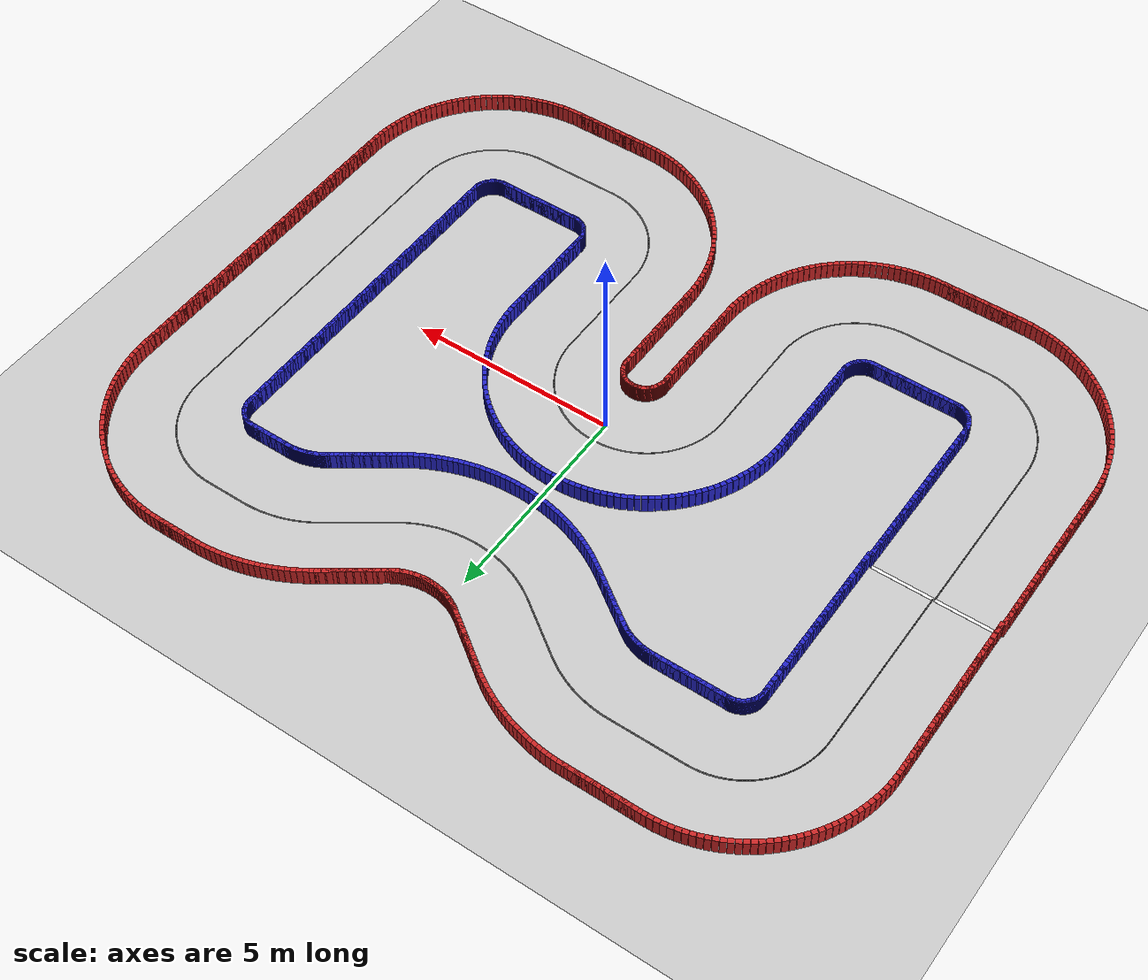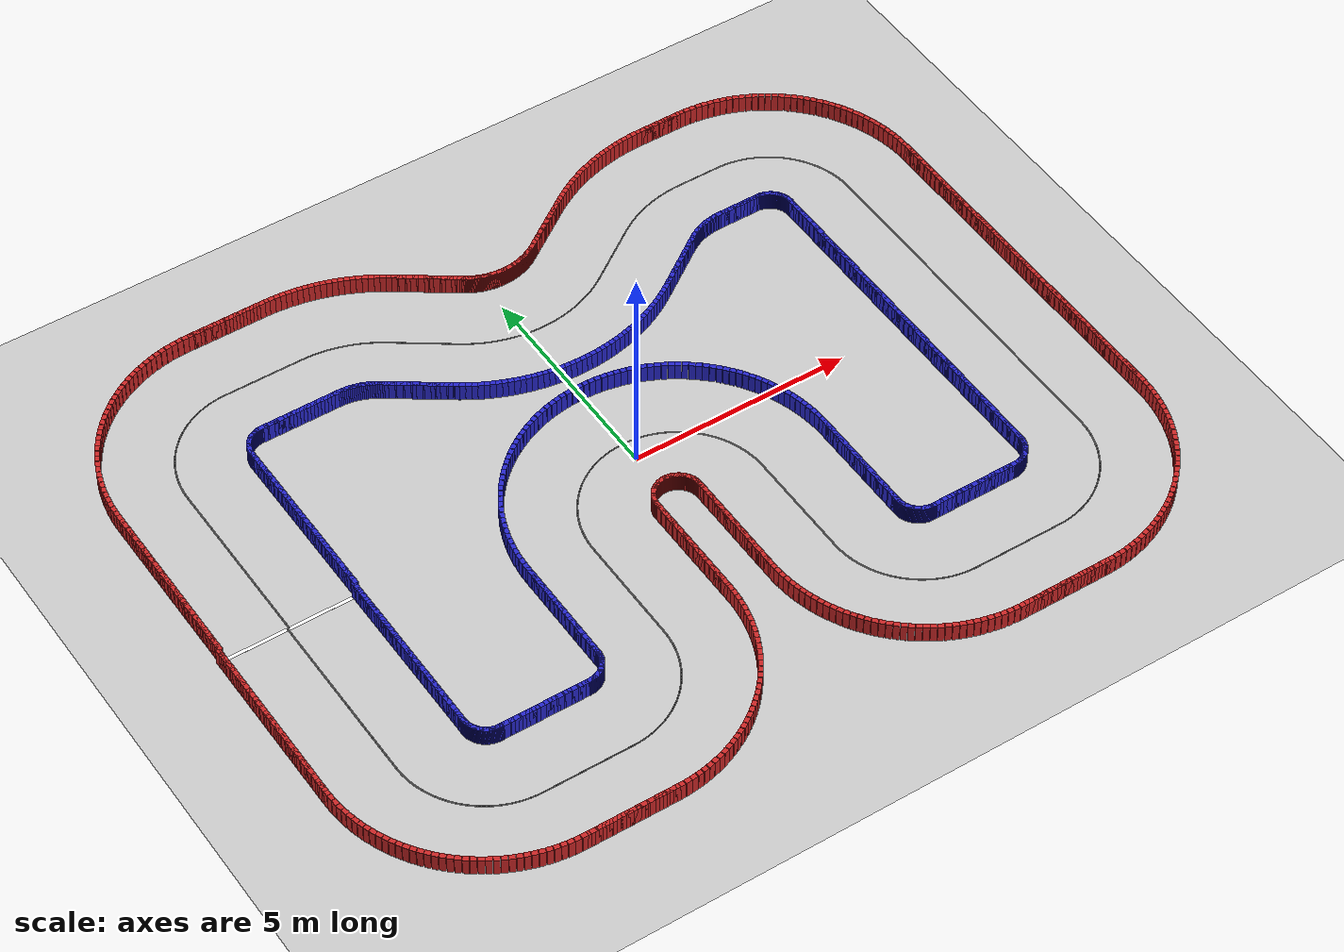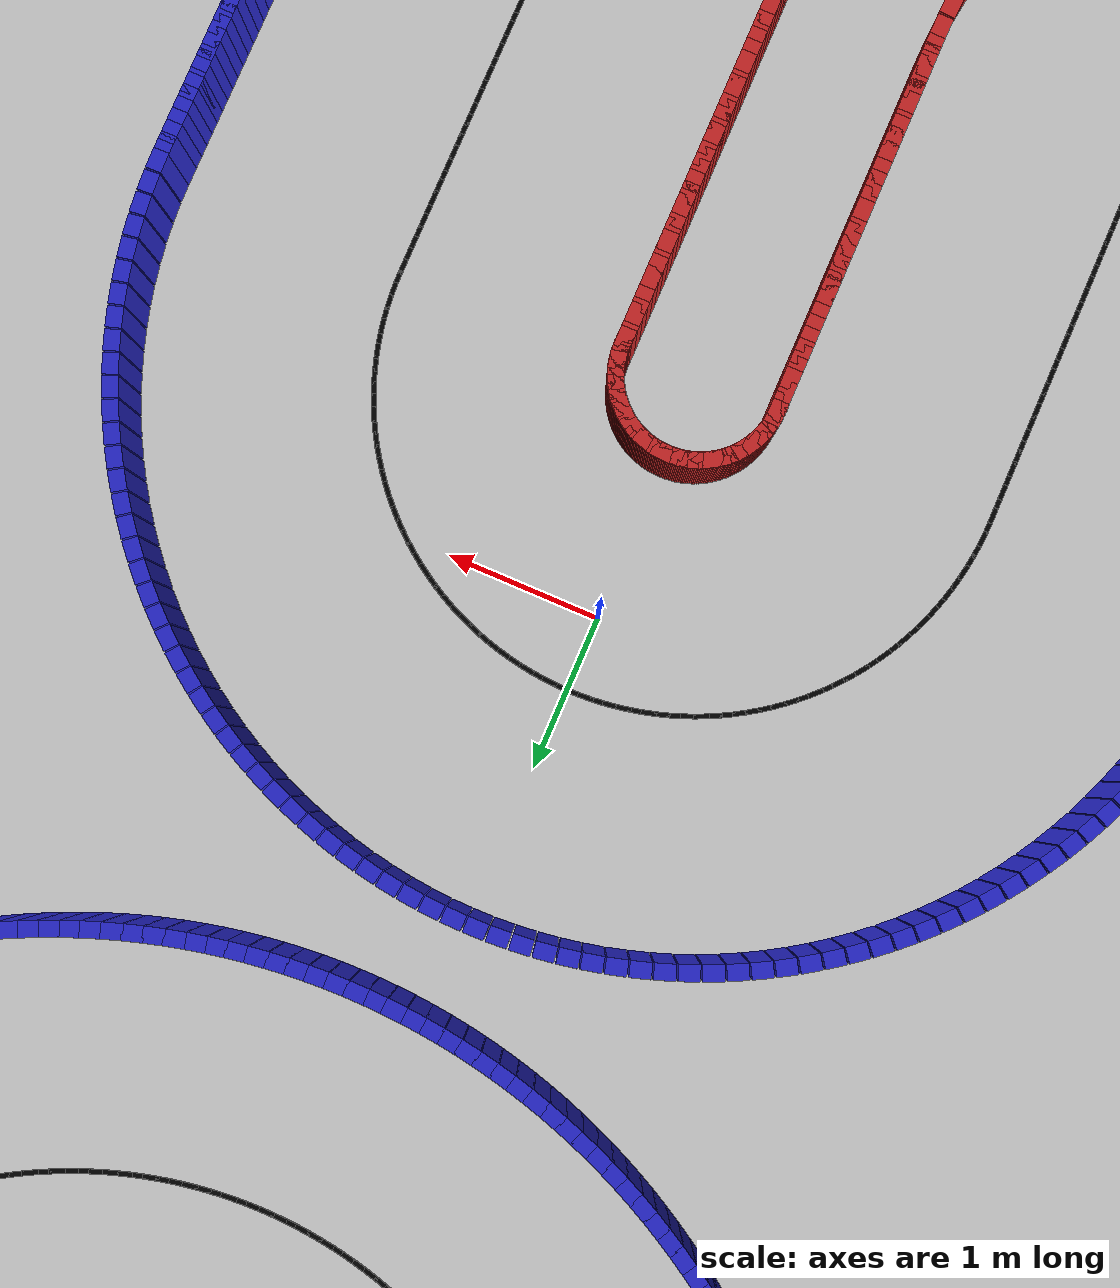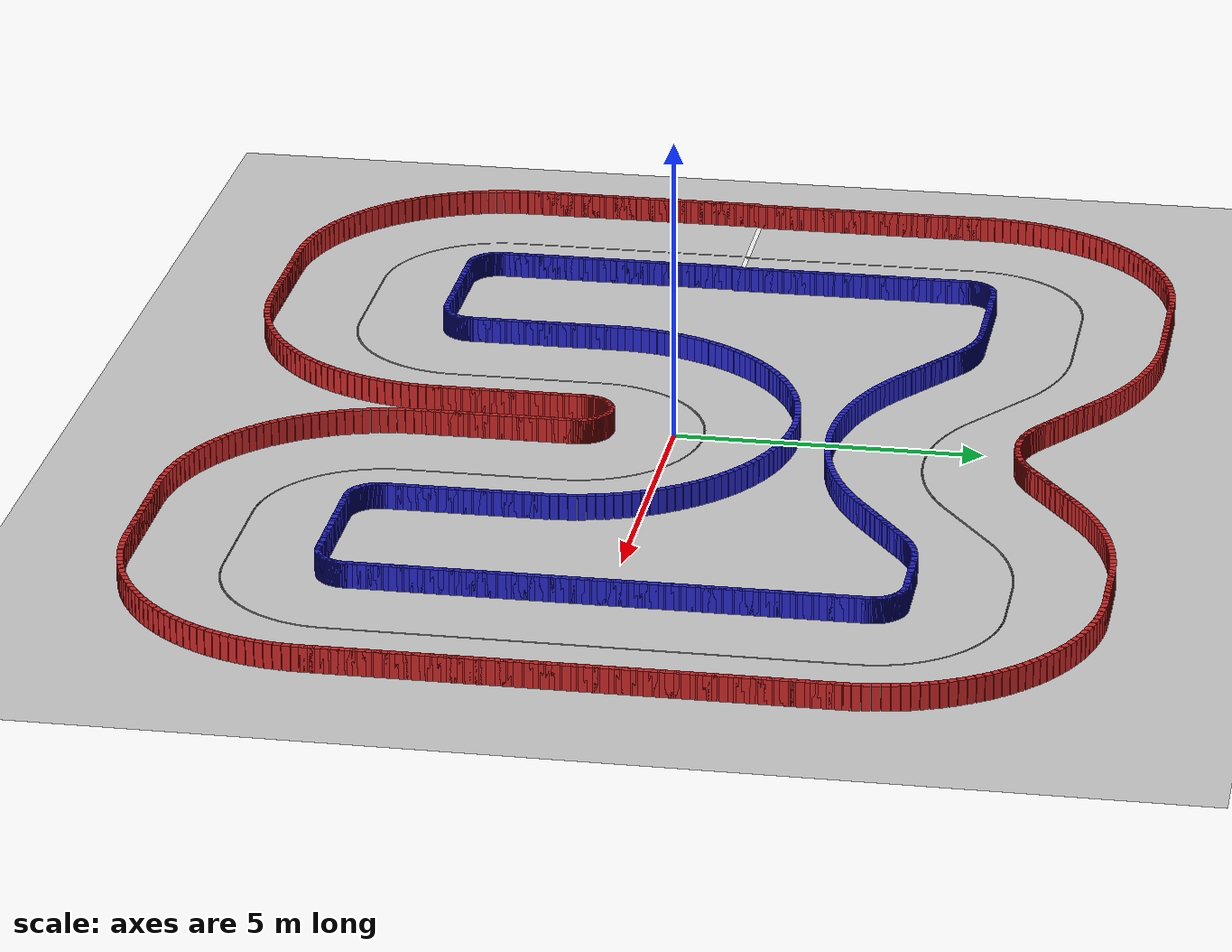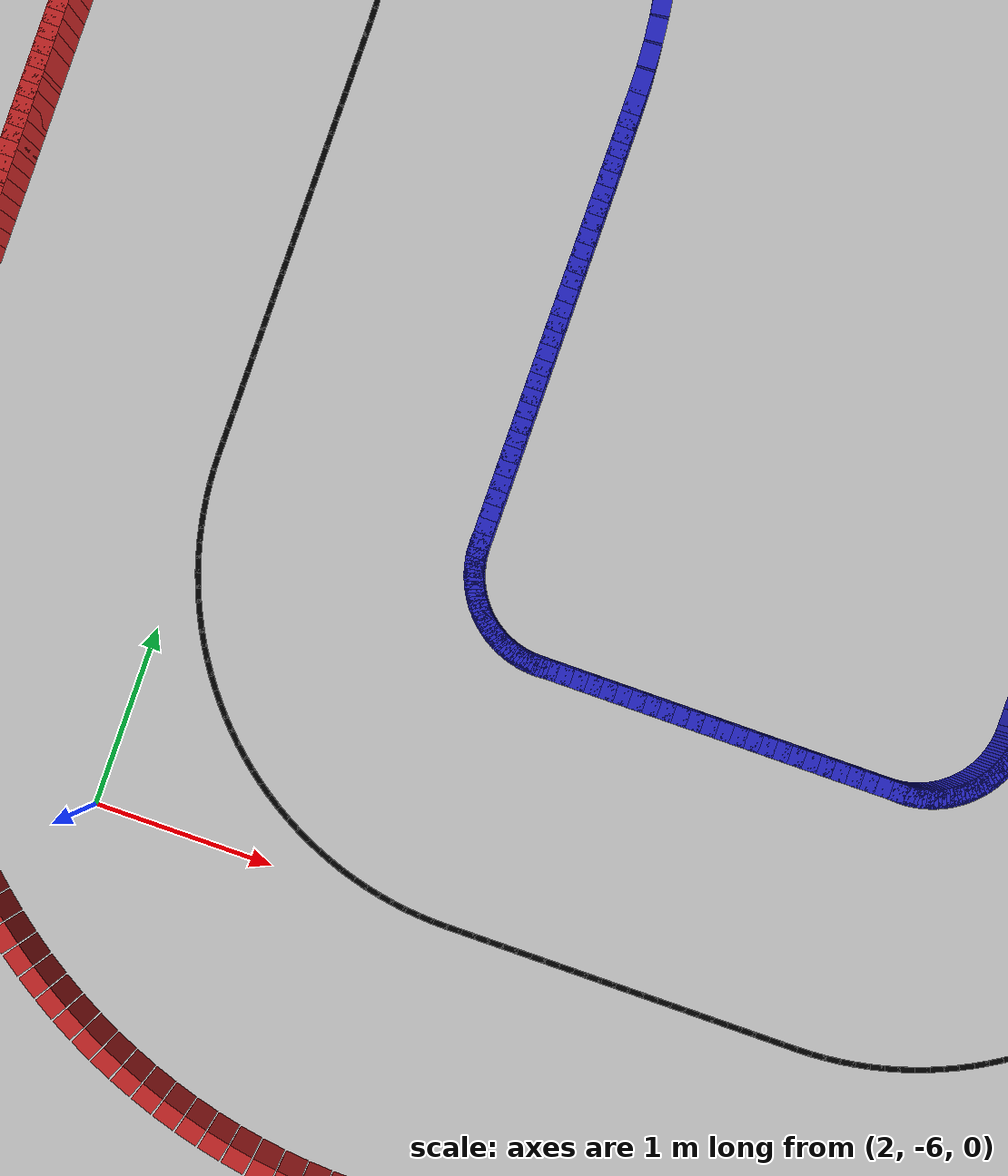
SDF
<?xml version="1.0"?>
<sdf version="1.6">
  <world name="new_race_track">
    <include><uri>model://ground_plane</uri></include>
    <include><uri>model://sun</uri></include>
    <scene><shadows>false</shadows></scene>
    <gui fullscreen="0">
      <camera name="user_camera">
        <pose>0 0 25.0 0 1.5708 0</pose>
        <view_controller>orbit</view_controller>
      </camera>
    </gui>
    <physics type="ode">
      <real_time_update_rate>500</real_time_update_rate>
      <max_step_size>0.002</max_step_size>
      <real_time_factor>1</real_time_factor>
    </physics>
    <model name="iw_0"><static>true</static><pose>-6.5000 -0.0400 0.200 0 0 -1.5708</pose><link name="l"><collision name="c"><geometry><box><size>0.1300 0.1 0.4</size></box></geometry></collision><visual name="v"><geometry><box><size>0.1300 0.1 0.4</size></box></geometry><material><ambient>0.15 0.15 0.8 1</ambient><diffuse>0.15 0.15 0.8 1</diffuse></material></visual></link></model>
    <model name="iw_1"><static>true</static><pose>-6.5000 -0.1200 0.200 0 0 -1.5708</pose><link name="l"><collision name="c"><geometry><box><size>0.1300 0.1 0.4</size></box></geometry></collision><visual name="v"><geometry><box><size>0.1300 0.1 0.4</size></box></geometry><material><ambient>0.15 0.15 0.8 1</ambient><diffuse>0.15 0.15 0.8 1</diffuse></material></visual></link></model>
    <model name="iw_2"><static>true</static><pose>-6.5000 -0.2000 0.200 0 0 -1.5708</pose><link name="l"><collision name="c"><geometry><box><size>0.1300 0.1 0.4</size></box></geometry></collision><visual name="v"><geometry><box><size>0.1300 0.1 0.4</size></box></geometry><material><ambient>0.15 0.15 0.8 1</ambient><diffuse>0.15 0.15 0.8 1</diffuse></material></visual></link></model>
    <model name="iw_3"><static>true</static><pose>-6.5000 -0.2800 0.200 0 0 -1.5708</pose><link name="l"><collision name="c"><geometry><box><size>0.1300 0.1 0.4</size></box></geometry></collision><visual name="v"><geometry><box><size>0.1300 0.1 0.4</size></box></geometry><material><ambient>0.15 0.15 0.8 1</ambient><diffuse>0.15 0.15 0.8 1</diffuse></material></visual></link></model>
    <model name="iw_4"><static>true</static><pose>-6.5000 -0.3600 0.200 0 0 -1.5708</pose><link name="l"><collision name="c"><geometry><box><size>0.1300 0.1 0.4</size></box></geometry></collision><visual name="v"><geometry><box><size>0.1300 0.1 0.4</size></box></geometry><material><ambient>0.15 0.15 0.8 1</ambient><diffuse>0.15 0.15 0.8 1</diffuse></material></visual></link></model>
    <model name="iw_5"><static>true</static><pose>-6.5000 -0.4400 0.200 0 0 -1.5708</pose><link name="l"><collision name="c"><geometry><box><size>0.1300 0.1 0.4</size></box></geometry></collision><visual name="v"><geometry><box><size>0.1300 0.1 0.4</size></box></geometry><material><ambient>0.15 0.15 0.8 1</ambient><diffuse>0.15 0.15 0.8 1</diffuse></material></visual></link></model>
    <model name="iw_6"><static>true</static><pose>-6.5000 -0.5200 0.200 0 0 -1.5708</pose><link name="l"><collision name="c"><geometry><box><size>0.1300 0.1 0.4</size></box></geometry></collision><visual name="v"><geometry><box><size>0.1300 0.1 0.4</size></box></geometry><material><ambient>0.15 0.15 0.8 1</ambient><diffuse>0.15 0.15 0.8 1</diffuse></material></visual></link></model>
    <model name="iw_7"><static>true</static><pose>-6.5000 -0.6000 0.200 0 0 -1.5708</pose><link name="l"><collision name="c"><geometry><box><size>0.1300 0.1 0.4</size></box></geometry></collision><visual name="v"><geometry><box><size>0.1300 0.1 0.4</size></box></geometry><material><ambient>0.15 0.15 0.8 1</ambient><diffuse>0.15 0.15 0.8 1</diffuse></material></visual></link></model>
    <model name="iw_8"><static>true</static><pose>-6.5000 -0.6800 0.200 0 0 -1.5708</pose><link name="l"><collision name="c"><geometry><box><size>0.1300 0.1 0.4</size></box></geometry></collision><visual name="v"><geometry><box><size>0.1300 0.1 0.4</size></box></geometry><material><ambient>0.15 0.15 0.8 1</ambient><diffuse>0.15 0.15 0.8 1</diffuse></material></visual></link></model>
    <model name="iw_9"><static>true</static><pose>-6.5000 -0.7600 0.200 0 0 -1.5708</pose><link name="l"><collision name="c"><geometry><box><size>0.1300 0.1 0.4</size></box></geometry></collision><visual name="v"><geometry><box><size>0.1300 0.1 0.4</size></box></geometry><material><ambient>0.15 0.15 0.8 1</ambient><diffuse>0.15 0.15 0.8 1</diffuse></material></visual></link></model>
    <model name="iw_10"><static>true</static><pose>-6.5000 -0.8400 0.200 0 0 -1.5708</pose><link name="l"><collision name="c"><geometry><box><size>0.1300 0.1 0.4</size></box></geometry></collision><visual name="v"><geometry><box><size>0.1300 0.1 0.4</size></box></geometry><material><ambient>0.15 0.15 0.8 1</ambient><diffuse>0.15 0.15 0.8 1</diffuse></material></visual></link></model>
    <model name="iw_11"><static>true</static><pose>-6.5000 -0.9200 0.200 0 0 -1.5708</pose><link name="l"><collision name="c"><geometry><box><size>0.1300 0.1 0.4</size></box></geometry></collision><visual name="v"><geometry><box><size>0.1300 0.1 0.4</size></box></geometry><material><ambient>0.15 0.15 0.8 1</ambient><diffuse>0.15 0.15 0.8 1</diffuse></material></visual></link></model>
    <model name="iw_12"><static>true</static><pose>-6.5000 -1.0000 0.200 0 0 -1.5708</pose><link name="l"><collision name="c"><geometry><box><size>0.1300 0.1 0.4</size></box></geometry></collision><visual name="v"><geometry><box><size>0.1300 0.1 0.4</size></box></geometry><material><ambient>0.15 0.15 0.8 1</ambient><diffuse>0.15 0.15 0.8 1</diffuse></material></visual></link></model>
    <model name="iw_13"><static>true</static><pose>-6.5000 -1.0800 0.200 0 0 -1.5708</pose><link name="l"><collision name="c"><geometry><box><size>0.1300 0.1 0.4</size></box></geometry></collision><visual name="v"><geometry><box><size>0.1300 0.1 0.4</size></box></geometry><material><ambient>0.15 0.15 0.8 1</ambient><diffuse>0.15 0.15 0.8 1</diffuse></material></visual></link></model>
    <model name="iw_14"><static>true</static><pose>-6.5000 -1.1600 0.200 0 0 -1.5708</pose><link name="l"><collision name="c"><geometry><box><size>0.1300 0.1 0.4</size></box></geometry></collision><visual name="v"><geometry><box><size>0.1300 0.1 0.4</size></box></geometry><material><ambient>0.15 0.15 0.8 1</ambient><diffuse>0.15 0.15 0.8 1</diffuse></material></visual></link></model>
    <model name="iw_15"><static>true</static><pose>-6.5000 -1.2400 0.200 0 0 -1.5708</pose><link name="l"><collision name="c"><geometry><box><size>0.1300 0.1 0.4</size></box></geometry></collision><visual name="v"><geometry><box><size>0.1300 0.1 0.4</size></box></geometry><material><ambient>0.15 0.15 0.8 1</ambient><diffuse>0.15 0.15 0.8 1</diffuse></material></visual></link></model>
    <model name="iw_16"><static>true</static><pose>-6.5000 -1.3200 0.200 0 0 -1.5708</pose><link name="l"><collision name="c"><geometry><box><size>0.1300 0.1 0.4</size></box></geometry></collision><visual name="v"><geometry><box><size>0.1300 0.1 0.4</size></box></geometry><material><ambient>0.15 0.15 0.8 1</ambient><diffuse>0.15 0.15 0.8 1</diffuse></material></visual></link></model>
    <model name="iw_17"><static>true</static><pose>-6.5000 -1.4000 0.200 0 0 -1.5708</pose><link name="l"><collision name="c"><geometry><box><size>0.1300 0.1 0.4</size></box></geometry></collision><visual name="v"><geometry><box><size>0.1300 0.1 0.4</size></box></geometry><material><ambient>0.15 0.15 0.8 1</ambient><diffuse>0.15 0.15 0.8 1</diffuse></material></visual></link></model>
    <model name="iw_18"><static>true</static><pose>-6.5000 -1.4800 0.200 0 0 -1.5708</pose><link name="l"><collision name="c"><geometry><box><size>0.1300 0.1 0.4</size></box></geometry></collision><visual name="v"><geometry><box><size>0.1300 0.1 0.4</size></box></geometry><material><ambient>0.15 0.15 0.8 1</ambient><diffuse>0.15 0.15 0.8 1</diffuse></material></visual></link></model>
    <model name="iw_19"><static>true</static><pose>-6.5000 -1.5600 0.200 0 0 -1.5708</pose><link name="l"><collision name="c"><geometry><box><size>0.1300 0.1 0.4</size></box></geometry></collision><visual name="v"><geometry><box><size>0.1300 0.1 0.4</size></box></geometry><material><ambient>0.15 0.15 0.8 1</ambient><diffuse>0.15 0.15 0.8 1</diffuse></material></visual></link></model>
    <model name="iw_20"><static>true</static><pose>-6.5000 -1.6400 0.200 0 0 -1.5708</pose><link name="l"><collision name="c"><geometry><box><size>0.1300 0.1 0.4</size></box></geometry></collision><visual name="v"><geometry><box><size>0.1300 0.1 0.4</size></box></geometry><material><ambient>0.15 0.15 0.8 1</ambient><diffuse>0.15 0.15 0.8 1</diffuse></material></visual></link></model>
    <model name="iw_21"><static>true</static><pose>-6.5000 -1.7200 0.200 0 0 -1.5708</pose><link name="l"><collision name="c"><geometry><box><size>0.1300 0.1 0.4</size></box></geometry></collision><visual name="v"><geometry><box><size>0.1300 0.1 0.4</size></box></geometry><material><ambient>0.15 0.15 0.8 1</ambient><diffuse>0.15 0.15 0.8 1</diffuse></material></visual></link></model>
    <model name="iw_22"><static>true</static><pose>-6.5000 -1.8000 0.200 0 0 -1.5708</pose><link name="l"><collision name="c"><geometry><box><size>0.1300 0.1 0.4</size></box></geometry></collision><visual name="v"><geometry><box><size>0.1300 0.1 0.4</size></box></geometry><material><ambient>0.15 0.15 0.8 1</ambient><diffuse>0.15 0.15 0.8 1</diffuse></material></visual></link></model>
    <model name="iw_23"><static>true</static><pose>-6.5000 -1.8800 0.200 0 0 -1.5708</pose><link name="l"><collision name="c"><geometry><box><size>0.1300 0.1 0.4</size></box></geometry></collision><visual name="v"><geometry><box><size>0.1300 0.1 0.4</size></box></geometry><material><ambient>0.15 0.15 0.8 1</ambient><diffuse>0.15 0.15 0.8 1</diffuse></material></visual></link></model>
    <model name="iw_24"><static>true</static><pose>-6.5000 -1.9600 0.200 0 0 -1.5708</pose><link name="l"><collision name="c"><geometry><box><size>0.1300 0.1 0.4</size></box></geometry></collision><visual name="v"><geometry><box><size>0.1300 0.1 0.4</size></box></geometry><material><ambient>0.15 0.15 0.8 1</ambient><diffuse>0.15 0.15 0.8 1</diffuse></material></visual></link></model>
    <model name="iw_25"><static>true</static><pose>-6.5000 -2.0400 0.200 0 0 -1.5708</pose><link name="l"><collision name="c"><geometry><box><size>0.1300 0.1 0.4</size></box></geometry></collision><visual name="v"><geometry><box><size>0.1300 0.1 0.4</size></box></geometry><material><ambient>0.15 0.15 0.8 1</ambient><diffuse>0.15 0.15 0.8 1</diffuse></material></visual></link></model>
    <model name="iw_26"><static>true</static><pose>-6.5000 -2.1200 0.200 0 0 -1.5708</pose><link name="l"><collision name="c"><geometry><box><size>0.1300 0.1 0.4</size></box></geometry></collision><visual name="v"><geometry><box><size>0.1300 0.1 0.4</size></box></geometry><material><ambient>0.15 0.15 0.8 1</ambient><diffuse>0.15 0.15 0.8 1</diffuse></material></visual></link></model>
    <model name="iw_27"><static>true</static><pose>-6.5000 -2.2000 0.200 0 0 -1.5708</pose><link name="l"><collision name="c"><geometry><box><size>0.1300 0.1 0.4</size></box></geometry></collision><visual name="v"><geometry><box><size>0.1300 0.1 0.4</size></box></geometry><material><ambient>0.15 0.15 0.8 1</ambient><diffuse>0.15 0.15 0.8 1</diffuse></material></visual></link></model>
    <model name="iw_28"><static>true</static><pose>-6.5000 -2.2800 0.200 0 0 -1.5708</pose><link name="l"><collision name="c"><geometry><box><size>0.1300 0.1 0.4</size></box></geometry></collision><visual name="v"><geometry><box><size>0.1300 0.1 0.4</size></box></geometry><material><ambient>0.15 0.15 0.8 1</ambient><diffuse>0.15 0.15 0.8 1</diffuse></material></visual></link></model>
    <model name="iw_29"><static>true</static><pose>-6.5000 -2.3600 0.200 0 0 -1.5708</pose><link name="l"><collision name="c"><geometry><box><size>0.1300 0.1 0.4</size></box></geometry></collision><visual name="v"><geometry><box><size>0.1300 0.1 0.4</size></box></geometry><material><ambient>0.15 0.15 0.8 1</ambient><diffuse>0.15 0.15 0.8 1</diffuse></material></visual></link></model>
    <model name="iw_30"><static>true</static><pose>-6.5000 -2.4400 0.200 0 0 -1.5708</pose><link name="l"><collision name="c"><geometry><box><size>0.1300 0.1 0.4</size></box></geometry></collision><visual name="v"><geometry><box><size>0.1300 0.1 0.4</size></box></geometry><material><ambient>0.15 0.15 0.8 1</ambient><diffuse>0.15 0.15 0.8 1</diffuse></material></visual></link></model>
    <model name="iw_31"><static>true</static><pose>-6.5000 -2.5200 0.200 0 0 -1.5708</pose><link name="l"><collision name="c"><geometry><box><size>0.1300 0.1 0.4</size></box></geometry></collision><visual name="v"><geometry><box><size>0.1300 0.1 0.4</size></box></geometry><material><ambient>0.15 0.15 0.8 1</ambient><diffuse>0.15 0.15 0.8 1</diffuse></material></visual></link></model>
    <model name="iw_32"><static>true</static><pose>-6.5000 -2.6000 0.200 0 0 -1.5708</pose><link name="l"><collision name="c"><geometry><box><size>0.1300 0.1 0.4</size></box></geometry></collision><visual name="v"><geometry><box><size>0.1300 0.1 0.4</size></box></geometry><material><ambient>0.15 0.15 0.8 1</ambient><diffuse>0.15 0.15 0.8 1</diffuse></material></visual></link></model>
    <model name="iw_33"><static>true</static><pose>-6.5000 -2.6800 0.200 0 0 -1.5708</pose><link name="l"><collision name="c"><geometry><box><size>0.1300 0.1 0.4</size></box></geometry></collision><visual name="v"><geometry><box><size>0.1300 0.1 0.4</size></box></geometry><material><ambient>0.15 0.15 0.8 1</ambient><diffuse>0.15 0.15 0.8 1</diffuse></material></visual></link></model>
    <model name="iw_34"><static>true</static><pose>-6.5000 -2.7600 0.200 0 0 -1.5708</pose><link name="l"><collision name="c"><geometry><box><size>0.1300 0.1 0.4</size></box></geometry></collision><visual name="v"><geometry><box><size>0.1300 0.1 0.4</size></box></geometry><material><ambient>0.15 0.15 0.8 1</ambient><diffuse>0.15 0.15 0.8 1</diffuse></material></visual></link></model>
    <model name="iw_35"><static>true</static><pose>-6.5000 -2.8400 0.200 0 0 -1.5708</pose><link name="l"><collision name="c"><geometry><box><size>0.1300 0.1 0.4</size></box></geometry></collision><visual name="v"><geometry><box><size>0.1300 0.1 0.4</size></box></geometry><material><ambient>0.15 0.15 0.8 1</ambient><diffuse>0.15 0.15 0.8 1</diffuse></material></visual></link></model>
    <model name="iw_36"><static>true</static><pose>-6.5000 -2.9200 0.200 0 0 -1.5708</pose><link name="l"><collision name="c"><geometry><box><size>0.1300 0.1 0.4</size></box></geometry></collision><visual name="v"><geometry><box><size>0.1300 0.1 0.4</size></box></geometry><material><ambient>0.15 0.15 0.8 1</ambient><diffuse>0.15 0.15 0.8 1</diffuse></material></visual></link></model>
    <model name="iw_37"><static>true</static><pose>-6.5000 -3.0000 0.200 0 0 -1.5708</pose><link name="l"><collision name="c"><geometry><box><size>0.1300 0.1 0.4</size></box></geometry></collision><visual name="v"><geometry><box><size>0.1300 0.1 0.4</size></box></geometry><material><ambient>0.15 0.15 0.8 1</ambient><diffuse>0.15 0.15 0.8 1</diffuse></material></visual></link></model>
    <model name="iw_38"><static>true</static><pose>-6.5000 -3.0800 0.200 0 0 -1.5708</pose><link name="l"><collision name="c"><geometry><box><size>0.1300 0.1 0.4</size></box></geometry></collision><visual name="v"><geometry><box><size>0.1300 0.1 0.4</size></box></geometry><material><ambient>0.15 0.15 0.8 1</ambient><diffuse>0.15 0.15 0.8 1</diffuse></material></visual></link></model>
    <model name="iw_39"><static>true</static><pose>-6.5000 -3.1600 0.200 0 0 -1.5708</pose><link name="l"><collision name="c"><geometry><box><size>0.1300 0.1 0.4</size></box></geometry></collision><visual name="v"><geometry><box><size>0.1300 0.1 0.4</size></box></geometry><material><ambient>0.15 0.15 0.8 1</ambient><diffuse>0.15 0.15 0.8 1</diffuse></material></visual></link></model>
    <model name="iw_40"><static>true</static><pose>-6.5000 -3.2400 0.200 0 0 -1.5708</pose><link name="l"><collision name="c"><geometry><box><size>0.1300 0.1 0.4</size></box></geometry></collision><visual name="v"><geometry><box><size>0.1300 0.1 0.4</size></box></geometry><material><ambient>0.15 0.15 0.8 1</ambient><diffuse>0.15 0.15 0.8 1</diffuse></material></visual></link></model>
    <model name="iw_41"><static>true</static><pose>-6.5000 -3.3200 0.200 0 0 -1.5708</pose><link name="l"><collision name="c"><geometry><box><size>0.1300 0.1 0.4</size></box></geometry></collision><visual name="v"><geometry><box><size>0.1300 0.1 0.4</size></box></geometry><material><ambient>0.15 0.15 0.8 1</ambient><diffuse>0.15 0.15 0.8 1</diffuse></material></visual></link></model>
    <model name="iw_42"><static>true</static><pose>-6.5000 -3.4000 0.200 0 0 -1.5708</pose><link name="l"><collision name="c"><geometry><box><size>0.1300 0.1 0.4</size></box></geometry></collision><visual name="v"><geometry><box><size>0.1300 0.1 0.4</size></box></geometry><material><ambient>0.15 0.15 0.8 1</ambient><diffuse>0.15 0.15 0.8 1</diffuse></material></visual></link></model>
    <model name="iw_43"><static>true</static><pose>-6.5000 -3.4800 0.200 0 0 -1.5708</pose><link name="l"><collision name="c"><geometry><box><size>0.1300 0.1 0.4</size></box></geometry></collision><visual name="v"><geometry><box><size>0.1300 0.1 0.4</size></box></geometry><material><ambient>0.15 0.15 0.8 1</ambient><diffuse>0.15 0.15 0.8 1</diffuse></material></visual></link></model>
    <model name="iw_44"><static>true</static><pose>-6.5000 -3.5600 0.200 0 0 -1.5708</pose><link name="l"><collision name="c"><geometry><box><size>0.1300 0.1 0.4</size></box></geometry></collision><visual name="v"><geometry><box><size>0.1300 0.1 0.4</size></box></geometry><material><ambient>0.15 0.15 0.8 1</ambient><diffuse>0.15 0.15 0.8 1</diffuse></material></visual></link></model>
    <model name="iw_45"><static>true</static><pose>-6.5000 -3.6400 0.200 0 0 -1.5708</pose><link name="l"><collision name="c"><geometry><box><size>0.1300 0.1 0.4</size></box></geometry></collision><visual name="v"><geometry><box><size>0.1300 0.1 0.4</size></box></geometry><material><ambient>0.15 0.15 0.8 1</ambient><diffuse>0.15 0.15 0.8 1</diffuse></material></visual></link></model>
    <model name="iw_46"><static>true</static><pose>-6.5000 -3.7200 0.200 0 0 -1.5708</pose><link name="l"><collision name="c"><geometry><box><size>0.1300 0.1 0.4</size></box></geometry></collision><visual name="v"><geometry><box><size>0.1300 0.1 0.4</size></box></geometry><material><ambient>0.15 0.15 0.8 1</ambient><diffuse>0.15 0.15 0.8 1</diffuse></material></visual></link></model>
    <model name="iw_47"><static>true</static><pose>-6.5000 -3.8000 0.200 0 0 -1.5708</pose><link name="l"><collision name="c"><geometry><box><size>0.1300 0.1 0.4</size></box></geometry></collision><visual name="v"><geometry><box><size>0.1300 0.1 0.4</size></box></geometry><material><ambient>0.15 0.15 0.8 1</ambient><diffuse>0.15 0.15 0.8 1</diffuse></material></visual></link></model>
    <model name="iw_48"><static>true</static><pose>-6.5000 -3.8800 0.200 0 0 -1.5708</pose><link name="l"><collision name="c"><geometry><box><size>0.1300 0.1 0.4</size></box></geometry></collision><visual name="v"><geometry><box><size>0.1300 0.1 0.4</size></box></geometry><material><ambient>0.15 0.15 0.8 1</ambient><diffuse>0.15 0.15 0.8 1</diffuse></material></visual></link></model>
    <model name="iw_49"><static>true</static><pose>-6.5000 -3.9600 0.200 0 0 -1.5708</pose><link name="l"><collision name="c"><geometry><box><size>0.1300 0.1 0.4</size></box></geometry></collision><visual name="v"><geometry><box><size>0.1300 0.1 0.4</size></box></geometry><material><ambient>0.15 0.15 0.8 1</ambient><diffuse>0.15 0.15 0.8 1</diffuse></material></visual></link></model>
    <model name="iw_50"><static>true</static><pose>-6.4995 -4.0101 0.200 0 0 -1.5507</pose><link name="l"><collision name="c"><geometry><box><size>0.1305 0.1 0.4</size></box></geometry></collision><visual name="v"><geometry><box><size>0.1305 0.1 0.4</size></box></geometry><material><ambient>0.15 0.15 0.8 1</ambient><diffuse>0.15 0.15 0.8 1</diffuse></material></visual></link></model>
    <model name="iw_51"><static>true</static><pose>-6.4987 -4.0302 0.200 0 0 -1.5104</pose><link name="l"><collision name="c"><geometry><box><size>0.1305 0.1 0.4</size></box></geometry></collision><visual name="v"><geometry><box><size>0.1305 0.1 0.4</size></box></geometry><material><ambient>0.15 0.15 0.8 1</ambient><diffuse>0.15 0.15 0.8 1</diffuse></material></visual></link></model>
    <model name="iw_52"><static>true</static><pose>-6.4971 -4.0502 0.200 0 0 -1.4701</pose><link name="l"><collision name="c"><geometry><box><size>0.1305 0.1 0.4</size></box></geometry></collision><visual name="v"><geometry><box><size>0.1305 0.1 0.4</size></box></geometry><material><ambient>0.15 0.15 0.8 1</ambient><diffuse>0.15 0.15 0.8 1</diffuse></material></visual></link></model>
    <model name="iw_53"><static>true</static><pose>-6.4946 -4.0702 0.200 0 0 -1.4298</pose><link name="l"><collision name="c"><geometry><box><size>0.1305 0.1 0.4</size></box></geometry></collision><visual name="v"><geometry><box><size>0.1305 0.1 0.4</size></box></geometry><material><ambient>0.15 0.15 0.8 1</ambient><diffuse>0.15 0.15 0.8 1</diffuse></material></visual></link></model>
    <model name="iw_54"><static>true</static><pose>-6.4914 -4.0901 0.200 0 0 -1.3896</pose><link name="l"><collision name="c"><geometry><box><size>0.1305 0.1 0.4</size></box></geometry></collision><visual name="v"><geometry><box><size>0.1305 0.1 0.4</size></box></geometry><material><ambient>0.15 0.15 0.8 1</ambient><diffuse>0.15 0.15 0.8 1</diffuse></material></visual></link></model>
    <model name="iw_55"><static>true</static><pose>-6.4874 -4.1098 0.200 0 0 -1.3493</pose><link name="l"><collision name="c"><geometry><box><size>0.1305 0.1 0.4</size></box></geometry></collision><visual name="v"><geometry><box><size>0.1305 0.1 0.4</size></box></geometry><material><ambient>0.15 0.15 0.8 1</ambient><diffuse>0.15 0.15 0.8 1</diffuse></material></visual></link></model>
    <model name="iw_56"><static>true</static><pose>-6.4826 -4.1293 0.200 0 0 -1.3090</pose><link name="l"><collision name="c"><geometry><box><size>0.1305 0.1 0.4</size></box></geometry></collision><visual name="v"><geometry><box><size>0.1305 0.1 0.4</size></box></geometry><material><ambient>0.15 0.15 0.8 1</ambient><diffuse>0.15 0.15 0.8 1</diffuse></material></visual></link></model>
    <model name="iw_57"><static>true</static><pose>-6.4770 -4.1486 0.200 0 0 -1.2687</pose><link name="l"><collision name="c"><geometry><box><size>0.1305 0.1 0.4</size></box></geometry></collision><visual name="v"><geometry><box><size>0.1305 0.1 0.4</size></box></geometry><material><ambient>0.15 0.15 0.8 1</ambient><diffuse>0.15 0.15 0.8 1</diffuse></material></visual></link></model>
    <model name="iw_58"><static>true</static><pose>-6.4706 -4.1677 0.200 0 0 -1.2284</pose><link name="l"><collision name="c"><geometry><box><size>0.1305 0.1 0.4</size></box></geometry></collision><visual name="v"><geometry><box><size>0.1305 0.1 0.4</size></box></geometry><material><ambient>0.15 0.15 0.8 1</ambient><diffuse>0.15 0.15 0.8 1</diffuse></material></visual></link></model>
    <model name="iw_59"><static>true</static><pose>-6.4635 -4.1865 0.200 0 0 -1.1882</pose><link name="l"><collision name="c"><geometry><box><size>0.1305 0.1 0.4</size></box></geometry></collision><visual name="v"><geometry><box><size>0.1305 0.1 0.4</size></box></geometry><material><ambient>0.15 0.15 0.8 1</ambient><diffuse>0.15 0.15 0.8 1</diffuse></material></visual></link></model>
    <model name="iw_60"><static>true</static><pose>-6.4556 -4.2050 0.200 0 0 -1.1479</pose><link name="l"><collision name="c"><geometry><box><size>0.1305 0.1 0.4</size></box></geometry></collision><visual name="v"><geometry><box><size>0.1305 0.1 0.4</size></box></geometry><material><ambient>0.15 0.15 0.8 1</ambient><diffuse>0.15 0.15 0.8 1</diffuse></material></visual></link></model>
    <model name="iw_61"><static>true</static><pose>-6.4470 -4.2232 0.200 0 0 -1.1076</pose><link name="l"><collision name="c"><geometry><box><size>0.1305 0.1 0.4</size></box></geometry></collision><visual name="v"><geometry><box><size>0.1305 0.1 0.4</size></box></geometry><material><ambient>0.15 0.15 0.8 1</ambient><diffuse>0.15 0.15 0.8 1</diffuse></material></visual></link></model>
    <model name="iw_62"><static>true</static><pose>-6.4376 -4.2410 0.200 0 0 -1.0673</pose><link name="l"><collision name="c"><geometry><box><size>0.1305 0.1 0.4</size></box></geometry></collision><visual name="v"><geometry><box><size>0.1305 0.1 0.4</size></box></geometry><material><ambient>0.15 0.15 0.8 1</ambient><diffuse>0.15 0.15 0.8 1</diffuse></material></visual></link></model>
    <model name="iw_63"><static>true</static><pose>-6.4275 -4.2585 0.200 0 0 -1.0271</pose><link name="l"><collision name="c"><geometry><box><size>0.1305 0.1 0.4</size></box></geometry></collision><visual name="v"><geometry><box><size>0.1305 0.1 0.4</size></box></geometry><material><ambient>0.15 0.15 0.8 1</ambient><diffuse>0.15 0.15 0.8 1</diffuse></material></visual></link></model>
    <model name="iw_64"><static>true</static><pose>-6.4168 -4.2755 0.200 0 0 -0.9868</pose><link name="l"><collision name="c"><geometry><box><size>0.1305 0.1 0.4</size></box></geometry></collision><visual name="v"><geometry><box><size>0.1305 0.1 0.4</size></box></geometry><material><ambient>0.15 0.15 0.8 1</ambient><diffuse>0.15 0.15 0.8 1</diffuse></material></visual></link></model>
    <model name="iw_65"><static>true</static><pose>-6.4054 -4.2920 0.200 0 0 -0.9465</pose><link name="l"><collision name="c"><geometry><box><size>0.1305 0.1 0.4</size></box></geometry></collision><visual name="v"><geometry><box><size>0.1305 0.1 0.4</size></box></geometry><material><ambient>0.15 0.15 0.8 1</ambient><diffuse>0.15 0.15 0.8 1</diffuse></material></visual></link></model>
    <model name="iw_66"><static>true</static><pose>-6.3933 -4.3081 0.200 0 0 -0.9062</pose><link name="l"><collision name="c"><geometry><box><size>0.1305 0.1 0.4</size></box></geometry></collision><visual name="v"><geometry><box><size>0.1305 0.1 0.4</size></box></geometry><material><ambient>0.15 0.15 0.8 1</ambient><diffuse>0.15 0.15 0.8 1</diffuse></material></visual></link></model>
    <model name="iw_67"><static>true</static><pose>-6.3805 -4.3237 0.200 0 0 -0.8660</pose><link name="l"><collision name="c"><geometry><box><size>0.1305 0.1 0.4</size></box></geometry></collision><visual name="v"><geometry><box><size>0.1305 0.1 0.4</size></box></geometry><material><ambient>0.15 0.15 0.8 1</ambient><diffuse>0.15 0.15 0.8 1</diffuse></material></visual></link></model>
    <model name="iw_68"><static>true</static><pose>-6.3672 -4.3388 0.200 0 0 -0.8257</pose><link name="l"><collision name="c"><geometry><box><size>0.1305 0.1 0.4</size></box></geometry></collision><visual name="v"><geometry><box><size>0.1305 0.1 0.4</size></box></geometry><material><ambient>0.15 0.15 0.8 1</ambient><diffuse>0.15 0.15 0.8 1</diffuse></material></visual></link></model>
    <model name="iw_69"><static>true</static><pose>-6.3533 -4.3533 0.200 0 0 -0.7854</pose><link name="l"><collision name="c"><geometry><box><size>0.1305 0.1 0.4</size></box></geometry></collision><visual name="v"><geometry><box><size>0.1305 0.1 0.4</size></box></geometry><material><ambient>0.15 0.15 0.8 1</ambient><diffuse>0.15 0.15 0.8 1</diffuse></material></visual></link></model>
    <model name="iw_70"><static>true</static><pose>-6.3388 -4.3672 0.200 0 0 -0.7451</pose><link name="l"><collision name="c"><geometry><box><size>0.1305 0.1 0.4</size></box></geometry></collision><visual name="v"><geometry><box><size>0.1305 0.1 0.4</size></box></geometry><material><ambient>0.15 0.15 0.8 1</ambient><diffuse>0.15 0.15 0.8 1</diffuse></material></visual></link></model>
    <model name="iw_71"><static>true</static><pose>-6.3237 -4.3805 0.200 0 0 -0.7048</pose><link name="l"><collision name="c"><geometry><box><size>0.1305 0.1 0.4</size></box></geometry></collision><visual name="v"><geometry><box><size>0.1305 0.1 0.4</size></box></geometry><material><ambient>0.15 0.15 0.8 1</ambient><diffuse>0.15 0.15 0.8 1</diffuse></material></visual></link></model>
    <model name="iw_72"><static>true</static><pose>-6.3081 -4.3933 0.200 0 0 -0.6646</pose><link name="l"><collision name="c"><geometry><box><size>0.1305 0.1 0.4</size></box></geometry></collision><visual name="v"><geometry><box><size>0.1305 0.1 0.4</size></box></geometry><material><ambient>0.15 0.15 0.8 1</ambient><diffuse>0.15 0.15 0.8 1</diffuse></material></visual></link></model>
    <model name="iw_73"><static>true</static><pose>-6.2920 -4.4054 0.200 0 0 -0.6243</pose><link name="l"><collision name="c"><geometry><box><size>0.1305 0.1 0.4</size></box></geometry></collision><visual name="v"><geometry><box><size>0.1305 0.1 0.4</size></box></geometry><material><ambient>0.15 0.15 0.8 1</ambient><diffuse>0.15 0.15 0.8 1</diffuse></material></visual></link></model>
    <model name="iw_74"><static>true</static><pose>-6.2755 -4.4168 0.200 0 0 -0.5840</pose><link name="l"><collision name="c"><geometry><box><size>0.1305 0.1 0.4</size></box></geometry></collision><visual name="v"><geometry><box><size>0.1305 0.1 0.4</size></box></geometry><material><ambient>0.15 0.15 0.8 1</ambient><diffuse>0.15 0.15 0.8 1</diffuse></material></visual></link></model>
    <model name="iw_75"><static>true</static><pose>-6.2585 -4.4275 0.200 0 0 -0.5437</pose><link name="l"><collision name="c"><geometry><box><size>0.1305 0.1 0.4</size></box></geometry></collision><visual name="v"><geometry><box><size>0.1305 0.1 0.4</size></box></geometry><material><ambient>0.15 0.15 0.8 1</ambient><diffuse>0.15 0.15 0.8 1</diffuse></material></visual></link></model>
    <model name="iw_76"><static>true</static><pose>-6.2410 -4.4376 0.200 0 0 -0.5035</pose><link name="l"><collision name="c"><geometry><box><size>0.1305 0.1 0.4</size></box></geometry></collision><visual name="v"><geometry><box><size>0.1305 0.1 0.4</size></box></geometry><material><ambient>0.15 0.15 0.8 1</ambient><diffuse>0.15 0.15 0.8 1</diffuse></material></visual></link></model>
    <model name="iw_77"><static>true</static><pose>-6.2232 -4.4470 0.200 0 0 -0.4632</pose><link name="l"><collision name="c"><geometry><box><size>0.1305 0.1 0.4</size></box></geometry></collision><visual name="v"><geometry><box><size>0.1305 0.1 0.4</size></box></geometry><material><ambient>0.15 0.15 0.8 1</ambient><diffuse>0.15 0.15 0.8 1</diffuse></material></visual></link></model>
    <model name="iw_78"><static>true</static><pose>-6.2050 -4.4556 0.200 0 0 -0.4229</pose><link name="l"><collision name="c"><geometry><box><size>0.1305 0.1 0.4</size></box></geometry></collision><visual name="v"><geometry><box><size>0.1305 0.1 0.4</size></box></geometry><material><ambient>0.15 0.15 0.8 1</ambient><diffuse>0.15 0.15 0.8 1</diffuse></material></visual></link></model>
    <model name="iw_79"><static>true</static><pose>-6.1865 -4.4635 0.200 0 0 -0.3826</pose><link name="l"><collision name="c"><geometry><box><size>0.1305 0.1 0.4</size></box></geometry></collision><visual name="v"><geometry><box><size>0.1305 0.1 0.4</size></box></geometry><material><ambient>0.15 0.15 0.8 1</ambient><diffuse>0.15 0.15 0.8 1</diffuse></material></visual></link></model>
    <model name="iw_80"><static>true</static><pose>-6.1677 -4.4706 0.200 0 0 -0.3424</pose><link name="l"><collision name="c"><geometry><box><size>0.1305 0.1 0.4</size></box></geometry></collision><visual name="v"><geometry><box><size>0.1305 0.1 0.4</size></box></geometry><material><ambient>0.15 0.15 0.8 1</ambient><diffuse>0.15 0.15 0.8 1</diffuse></material></visual></link></model>
    <model name="iw_81"><static>true</static><pose>-6.1486 -4.4770 0.200 0 0 -0.3021</pose><link name="l"><collision name="c"><geometry><box><size>0.1305 0.1 0.4</size></box></geometry></collision><visual name="v"><geometry><box><size>0.1305 0.1 0.4</size></box></geometry><material><ambient>0.15 0.15 0.8 1</ambient><diffuse>0.15 0.15 0.8 1</diffuse></material></visual></link></model>
    <model name="iw_82"><static>true</static><pose>-6.1293 -4.4826 0.200 0 0 -0.2618</pose><link name="l"><collision name="c"><geometry><box><size>0.1305 0.1 0.4</size></box></geometry></collision><visual name="v"><geometry><box><size>0.1305 0.1 0.4</size></box></geometry><material><ambient>0.15 0.15 0.8 1</ambient><diffuse>0.15 0.15 0.8 1</diffuse></material></visual></link></model>
    <model name="iw_83"><static>true</static><pose>-6.1098 -4.4874 0.200 0 0 -0.2215</pose><link name="l"><collision name="c"><geometry><box><size>0.1305 0.1 0.4</size></box></geometry></collision><visual name="v"><geometry><box><size>0.1305 0.1 0.4</size></box></geometry><material><ambient>0.15 0.15 0.8 1</ambient><diffuse>0.15 0.15 0.8 1</diffuse></material></visual></link></model>
    <model name="iw_84"><static>true</static><pose>-6.0901 -4.4914 0.200 0 0 -0.1812</pose><link name="l"><collision name="c"><geometry><box><size>0.1305 0.1 0.4</size></box></geometry></collision><visual name="v"><geometry><box><size>0.1305 0.1 0.4</size></box></geometry><material><ambient>0.15 0.15 0.8 1</ambient><diffuse>0.15 0.15 0.8 1</diffuse></material></visual></link></model>
    <model name="iw_85"><static>true</static><pose>-6.0702 -4.4946 0.200 0 0 -0.1410</pose><link name="l"><collision name="c"><geometry><box><size>0.1305 0.1 0.4</size></box></geometry></collision><visual name="v"><geometry><box><size>0.1305 0.1 0.4</size></box></geometry><material><ambient>0.15 0.15 0.8 1</ambient><diffuse>0.15 0.15 0.8 1</diffuse></material></visual></link></model>
    <model name="iw_86"><static>true</static><pose>-6.0502 -4.4971 0.200 0 0 -0.1007</pose><link name="l"><collision name="c"><geometry><box><size>0.1305 0.1 0.4</size></box></geometry></collision><visual name="v"><geometry><box><size>0.1305 0.1 0.4</size></box></geometry><material><ambient>0.15 0.15 0.8 1</ambient><diffuse>0.15 0.15 0.8 1</diffuse></material></visual></link></model>
    <model name="iw_87"><static>true</static><pose>-6.0302 -4.4987 0.200 0 0 -0.0604</pose><link name="l"><collision name="c"><geometry><box><size>0.1305 0.1 0.4</size></box></geometry></collision><visual name="v"><geometry><box><size>0.1305 0.1 0.4</size></box></geometry><material><ambient>0.15 0.15 0.8 1</ambient><diffuse>0.15 0.15 0.8 1</diffuse></material></visual></link></model>
    <model name="iw_88"><static>true</static><pose>-6.0101 -4.4995 0.200 0 0 -0.0201</pose><link name="l"><collision name="c"><geometry><box><size>0.1305 0.1 0.4</size></box></geometry></collision><visual name="v"><geometry><box><size>0.1305 0.1 0.4</size></box></geometry><material><ambient>0.15 0.15 0.8 1</ambient><diffuse>0.15 0.15 0.8 1</diffuse></material></visual></link></model>
    <model name="iw_89"><static>true</static><pose>-5.9600 -4.5000 0.200 0 0 0.0000</pose><link name="l"><collision name="c"><geometry><box><size>0.1300 0.1 0.4</size></box></geometry></collision><visual name="v"><geometry><box><size>0.1300 0.1 0.4</size></box></geometry><material><ambient>0.15 0.15 0.8 1</ambient><diffuse>0.15 0.15 0.8 1</diffuse></material></visual></link></model>
    <model name="iw_90"><static>true</static><pose>-5.8800 -4.5000 0.200 0 0 0.0000</pose><link name="l"><collision name="c"><geometry><box><size>0.1300 0.1 0.4</size></box></geometry></collision><visual name="v"><geometry><box><size>0.1300 0.1 0.4</size></box></geometry><material><ambient>0.15 0.15 0.8 1</ambient><diffuse>0.15 0.15 0.8 1</diffuse></material></visual></link></model>
    <model name="iw_91"><static>true</static><pose>-5.8000 -4.5000 0.200 0 0 0.0000</pose><link name="l"><collision name="c"><geometry><box><size>0.1300 0.1 0.4</size></box></geometry></collision><visual name="v"><geometry><box><size>0.1300 0.1 0.4</size></box></geometry><material><ambient>0.15 0.15 0.8 1</ambient><diffuse>0.15 0.15 0.8 1</diffuse></material></visual></link></model>
    <model name="iw_92"><static>true</static><pose>-5.7200 -4.5000 0.200 0 0 0.0000</pose><link name="l"><collision name="c"><geometry><box><size>0.1300 0.1 0.4</size></box></geometry></collision><visual name="v"><geometry><box><size>0.1300 0.1 0.4</size></box></geometry><material><ambient>0.15 0.15 0.8 1</ambient><diffuse>0.15 0.15 0.8 1</diffuse></material></visual></link></model>
    <model name="iw_93"><static>true</static><pose>-5.6400 -4.5000 0.200 0 0 0.0000</pose><link name="l"><collision name="c"><geometry><box><size>0.1300 0.1 0.4</size></box></geometry></collision><visual name="v"><geometry><box><size>0.1300 0.1 0.4</size></box></geometry><material><ambient>0.15 0.15 0.8 1</ambient><diffuse>0.15 0.15 0.8 1</diffuse></material></visual></link></model>
    <model name="iw_94"><static>true</static><pose>-5.5600 -4.5000 0.200 0 0 0.0000</pose><link name="l"><collision name="c"><geometry><box><size>0.1300 0.1 0.4</size></box></geometry></collision><visual name="v"><geometry><box><size>0.1300 0.1 0.4</size></box></geometry><material><ambient>0.15 0.15 0.8 1</ambient><diffuse>0.15 0.15 0.8 1</diffuse></material></visual></link></model>
    <model name="iw_95"><static>true</static><pose>-5.4800 -4.5000 0.200 0 0 0.0000</pose><link name="l"><collision name="c"><geometry><box><size>0.1300 0.1 0.4</size></box></geometry></collision><visual name="v"><geometry><box><size>0.1300 0.1 0.4</size></box></geometry><material><ambient>0.15 0.15 0.8 1</ambient><diffuse>0.15 0.15 0.8 1</diffuse></material></visual></link></model>
    <model name="iw_96"><static>true</static><pose>-5.4000 -4.5000 0.200 0 0 0.0000</pose><link name="l"><collision name="c"><geometry><box><size>0.1300 0.1 0.4</size></box></geometry></collision><visual name="v"><geometry><box><size>0.1300 0.1 0.4</size></box></geometry><material><ambient>0.15 0.15 0.8 1</ambient><diffuse>0.15 0.15 0.8 1</diffuse></material></visual></link></model>
    <model name="iw_97"><static>true</static><pose>-5.3200 -4.5000 0.200 0 0 0.0000</pose><link name="l"><collision name="c"><geometry><box><size>0.1300 0.1 0.4</size></box></geometry></collision><visual name="v"><geometry><box><size>0.1300 0.1 0.4</size></box></geometry><material><ambient>0.15 0.15 0.8 1</ambient><diffuse>0.15 0.15 0.8 1</diffuse></material></visual></link></model>
    <model name="iw_98"><static>true</static><pose>-5.2400 -4.5000 0.200 0 0 0.0000</pose><link name="l"><collision name="c"><geometry><box><size>0.1300 0.1 0.4</size></box></geometry></collision><visual name="v"><geometry><box><size>0.1300 0.1 0.4</size></box></geometry><material><ambient>0.15 0.15 0.8 1</ambient><diffuse>0.15 0.15 0.8 1</diffuse></material></visual></link></model>
    <model name="iw_99"><static>true</static><pose>-5.1600 -4.5000 0.200 0 0 0.0000</pose><link name="l"><collision name="c"><geometry><box><size>0.1300 0.1 0.4</size></box></geometry></collision><visual name="v"><geometry><box><size>0.1300 0.1 0.4</size></box></geometry><material><ambient>0.15 0.15 0.8 1</ambient><diffuse>0.15 0.15 0.8 1</diffuse></material></visual></link></model>
    <model name="iw_100"><static>true</static><pose>-5.0800 -4.5000 0.200 0 0 0.0000</pose><link name="l"><collision name="c"><geometry><box><size>0.1300 0.1 0.4</size></box></geometry></collision><visual name="v"><geometry><box><size>0.1300 0.1 0.4</size></box></geometry><material><ambient>0.15 0.15 0.8 1</ambient><diffuse>0.15 0.15 0.8 1</diffuse></material></visual></link></model>
    <model name="iw_101"><static>true</static><pose>-5.0000 -4.5000 0.200 0 0 0.0000</pose><link name="l"><collision name="c"><geometry><box><size>0.1300 0.1 0.4</size></box></geometry></collision><visual name="v"><geometry><box><size>0.1300 0.1 0.4</size></box></geometry><material><ambient>0.15 0.15 0.8 1</ambient><diffuse>0.15 0.15 0.8 1</diffuse></material></visual></link></model>
    <model name="iw_102"><static>true</static><pose>-4.9200 -4.5000 0.200 0 0 0.0000</pose><link name="l"><collision name="c"><geometry><box><size>0.1300 0.1 0.4</size></box></geometry></collision><visual name="v"><geometry><box><size>0.1300 0.1 0.4</size></box></geometry><material><ambient>0.15 0.15 0.8 1</ambient><diffuse>0.15 0.15 0.8 1</diffuse></material></visual></link></model>
    <model name="iw_103"><static>true</static><pose>-4.8400 -4.5000 0.200 0 0 0.0000</pose><link name="l"><collision name="c"><geometry><box><size>0.1300 0.1 0.4</size></box></geometry></collision><visual name="v"><geometry><box><size>0.1300 0.1 0.4</size></box></geometry><material><ambient>0.15 0.15 0.8 1</ambient><diffuse>0.15 0.15 0.8 1</diffuse></material></visual></link></model>
    <model name="iw_104"><static>true</static><pose>-4.7600 -4.5000 0.200 0 0 0.0000</pose><link name="l"><collision name="c"><geometry><box><size>0.1300 0.1 0.4</size></box></geometry></collision><visual name="v"><geometry><box><size>0.1300 0.1 0.4</size></box></geometry><material><ambient>0.15 0.15 0.8 1</ambient><diffuse>0.15 0.15 0.8 1</diffuse></material></visual></link></model>
    <model name="iw_105"><static>true</static><pose>-4.6800 -4.5000 0.200 0 0 0.0000</pose><link name="l"><collision name="c"><geometry><box><size>0.1300 0.1 0.4</size></box></geometry></collision><visual name="v"><geometry><box><size>0.1300 0.1 0.4</size></box></geometry><material><ambient>0.15 0.15 0.8 1</ambient><diffuse>0.15 0.15 0.8 1</diffuse></material></visual></link></model>
    <model name="iw_106"><static>true</static><pose>-4.6000 -4.5000 0.200 0 0 0.0000</pose><link name="l"><collision name="c"><geometry><box><size>0.1300 0.1 0.4</size></box></geometry></collision><visual name="v"><geometry><box><size>0.1300 0.1 0.4</size></box></geometry><material><ambient>0.15 0.15 0.8 1</ambient><diffuse>0.15 0.15 0.8 1</diffuse></material></visual></link></model>
    <model name="iw_107"><static>true</static><pose>-4.5200 -4.5000 0.200 0 0 0.0000</pose><link name="l"><collision name="c"><geometry><box><size>0.1300 0.1 0.4</size></box></geometry></collision><visual name="v"><geometry><box><size>0.1300 0.1 0.4</size></box></geometry><material><ambient>0.15 0.15 0.8 1</ambient><diffuse>0.15 0.15 0.8 1</diffuse></material></visual></link></model>
    <model name="iw_108"><static>true</static><pose>-4.4400 -4.5000 0.200 0 0 0.0000</pose><link name="l"><collision name="c"><geometry><box><size>0.1300 0.1 0.4</size></box></geometry></collision><visual name="v"><geometry><box><size>0.1300 0.1 0.4</size></box></geometry><material><ambient>0.15 0.15 0.8 1</ambient><diffuse>0.15 0.15 0.8 1</diffuse></material></visual></link></model>
    <model name="iw_109"><static>true</static><pose>-4.3600 -4.5000 0.200 0 0 0.0000</pose><link name="l"><collision name="c"><geometry><box><size>0.1300 0.1 0.4</size></box></geometry></collision><visual name="v"><geometry><box><size>0.1300 0.1 0.4</size></box></geometry><material><ambient>0.15 0.15 0.8 1</ambient><diffuse>0.15 0.15 0.8 1</diffuse></material></visual></link></model>
    <model name="iw_110"><static>true</static><pose>-4.2800 -4.5000 0.200 0 0 0.0000</pose><link name="l"><collision name="c"><geometry><box><size>0.1300 0.1 0.4</size></box></geometry></collision><visual name="v"><geometry><box><size>0.1300 0.1 0.4</size></box></geometry><material><ambient>0.15 0.15 0.8 1</ambient><diffuse>0.15 0.15 0.8 1</diffuse></material></visual></link></model>
    <model name="iw_111"><static>true</static><pose>-4.2000 -4.5000 0.200 0 0 0.0000</pose><link name="l"><collision name="c"><geometry><box><size>0.1300 0.1 0.4</size></box></geometry></collision><visual name="v"><geometry><box><size>0.1300 0.1 0.4</size></box></geometry><material><ambient>0.15 0.15 0.8 1</ambient><diffuse>0.15 0.15 0.8 1</diffuse></material></visual></link></model>
    <model name="iw_112"><static>true</static><pose>-4.1200 -4.5000 0.200 0 0 0.0000</pose><link name="l"><collision name="c"><geometry><box><size>0.1300 0.1 0.4</size></box></geometry></collision><visual name="v"><geometry><box><size>0.1300 0.1 0.4</size></box></geometry><material><ambient>0.15 0.15 0.8 1</ambient><diffuse>0.15 0.15 0.8 1</diffuse></material></visual></link></model>
    <model name="iw_113"><static>true</static><pose>-4.0400 -4.5000 0.200 0 0 0.0000</pose><link name="l"><collision name="c"><geometry><box><size>0.1300 0.1 0.4</size></box></geometry></collision><visual name="v"><geometry><box><size>0.1300 0.1 0.4</size></box></geometry><material><ambient>0.15 0.15 0.8 1</ambient><diffuse>0.15 0.15 0.8 1</diffuse></material></visual></link></model>
    <model name="iw_114"><static>true</static><pose>-3.9899 -4.4995 0.200 0 0 0.0201</pose><link name="l"><collision name="c"><geometry><box><size>0.1305 0.1 0.4</size></box></geometry></collision><visual name="v"><geometry><box><size>0.1305 0.1 0.4</size></box></geometry><material><ambient>0.15 0.15 0.8 1</ambient><diffuse>0.15 0.15 0.8 1</diffuse></material></visual></link></model>
    <model name="iw_115"><static>true</static><pose>-3.9698 -4.4987 0.200 0 0 0.0604</pose><link name="l"><collision name="c"><geometry><box><size>0.1305 0.1 0.4</size></box></geometry></collision><visual name="v"><geometry><box><size>0.1305 0.1 0.4</size></box></geometry><material><ambient>0.15 0.15 0.8 1</ambient><diffuse>0.15 0.15 0.8 1</diffuse></material></visual></link></model>
    <model name="iw_116"><static>true</static><pose>-3.9498 -4.4971 0.200 0 0 0.1007</pose><link name="l"><collision name="c"><geometry><box><size>0.1305 0.1 0.4</size></box></geometry></collision><visual name="v"><geometry><box><size>0.1305 0.1 0.4</size></box></geometry><material><ambient>0.15 0.15 0.8 1</ambient><diffuse>0.15 0.15 0.8 1</diffuse></material></visual></link></model>
    <model name="iw_117"><static>true</static><pose>-3.9298 -4.4946 0.200 0 0 0.1410</pose><link name="l"><collision name="c"><geometry><box><size>0.1305 0.1 0.4</size></box></geometry></collision><visual name="v"><geometry><box><size>0.1305 0.1 0.4</size></box></geometry><material><ambient>0.15 0.15 0.8 1</ambient><diffuse>0.15 0.15 0.8 1</diffuse></material></visual></link></model>
    <model name="iw_118"><static>true</static><pose>-3.9099 -4.4914 0.200 0 0 0.1812</pose><link name="l"><collision name="c"><geometry><box><size>0.1305 0.1 0.4</size></box></geometry></collision><visual name="v"><geometry><box><size>0.1305 0.1 0.4</size></box></geometry><material><ambient>0.15 0.15 0.8 1</ambient><diffuse>0.15 0.15 0.8 1</diffuse></material></visual></link></model>
    <model name="iw_119"><static>true</static><pose>-3.8902 -4.4874 0.200 0 0 0.2215</pose><link name="l"><collision name="c"><geometry><box><size>0.1305 0.1 0.4</size></box></geometry></collision><visual name="v"><geometry><box><size>0.1305 0.1 0.4</size></box></geometry><material><ambient>0.15 0.15 0.8 1</ambient><diffuse>0.15 0.15 0.8 1</diffuse></material></visual></link></model>
    <model name="iw_120"><static>true</static><pose>-3.8707 -4.4826 0.200 0 0 0.2618</pose><link name="l"><collision name="c"><geometry><box><size>0.1305 0.1 0.4</size></box></geometry></collision><visual name="v"><geometry><box><size>0.1305 0.1 0.4</size></box></geometry><material><ambient>0.15 0.15 0.8 1</ambient><diffuse>0.15 0.15 0.8 1</diffuse></material></visual></link></model>
    <model name="iw_121"><static>true</static><pose>-3.8514 -4.4770 0.200 0 0 0.3021</pose><link name="l"><collision name="c"><geometry><box><size>0.1305 0.1 0.4</size></box></geometry></collision><visual name="v"><geometry><box><size>0.1305 0.1 0.4</size></box></geometry><material><ambient>0.15 0.15 0.8 1</ambient><diffuse>0.15 0.15 0.8 1</diffuse></material></visual></link></model>
    <model name="iw_122"><static>true</static><pose>-3.8323 -4.4706 0.200 0 0 0.3424</pose><link name="l"><collision name="c"><geometry><box><size>0.1305 0.1 0.4</size></box></geometry></collision><visual name="v"><geometry><box><size>0.1305 0.1 0.4</size></box></geometry><material><ambient>0.15 0.15 0.8 1</ambient><diffuse>0.15 0.15 0.8 1</diffuse></material></visual></link></model>
    <model name="iw_123"><static>true</static><pose>-3.8135 -4.4635 0.200 0 0 0.3826</pose><link name="l"><collision name="c"><geometry><box><size>0.1305 0.1 0.4</size></box></geometry></collision><visual name="v"><geometry><box><size>0.1305 0.1 0.4</size></box></geometry><material><ambient>0.15 0.15 0.8 1</ambient><diffuse>0.15 0.15 0.8 1</diffuse></material></visual></link></model>
    <model name="iw_124"><static>true</static><pose>-3.7950 -4.4556 0.200 0 0 0.4229</pose><link name="l"><collision name="c"><geometry><box><size>0.1305 0.1 0.4</size></box></geometry></collision><visual name="v"><geometry><box><size>0.1305 0.1 0.4</size></box></geometry><material><ambient>0.15 0.15 0.8 1</ambient><diffuse>0.15 0.15 0.8 1</diffuse></material></visual></link></model>
    <model name="iw_125"><static>true</static><pose>-3.7768 -4.4470 0.200 0 0 0.4632</pose><link name="l"><collision name="c"><geometry><box><size>0.1305 0.1 0.4</size></box></geometry></collision><visual name="v"><geometry><box><size>0.1305 0.1 0.4</size></box></geometry><material><ambient>0.15 0.15 0.8 1</ambient><diffuse>0.15 0.15 0.8 1</diffuse></material></visual></link></model>
    <model name="iw_126"><static>true</static><pose>-3.7590 -4.4376 0.200 0 0 0.5035</pose><link name="l"><collision name="c"><geometry><box><size>0.1305 0.1 0.4</size></box></geometry></collision><visual name="v"><geometry><box><size>0.1305 0.1 0.4</size></box></geometry><material><ambient>0.15 0.15 0.8 1</ambient><diffuse>0.15 0.15 0.8 1</diffuse></material></visual></link></model>
    <model name="iw_127"><static>true</static><pose>-3.7415 -4.4275 0.200 0 0 0.5437</pose><link name="l"><collision name="c"><geometry><box><size>0.1305 0.1 0.4</size></box></geometry></collision><visual name="v"><geometry><box><size>0.1305 0.1 0.4</size></box></geometry><material><ambient>0.15 0.15 0.8 1</ambient><diffuse>0.15 0.15 0.8 1</diffuse></material></visual></link></model>
    <model name="iw_128"><static>true</static><pose>-3.7245 -4.4168 0.200 0 0 0.5840</pose><link name="l"><collision name="c"><geometry><box><size>0.1305 0.1 0.4</size></box></geometry></collision><visual name="v"><geometry><box><size>0.1305 0.1 0.4</size></box></geometry><material><ambient>0.15 0.15 0.8 1</ambient><diffuse>0.15 0.15 0.8 1</diffuse></material></visual></link></model>
    <model name="iw_129"><static>true</static><pose>-3.7080 -4.4054 0.200 0 0 0.6243</pose><link name="l"><collision name="c"><geometry><box><size>0.1305 0.1 0.4</size></box></geometry></collision><visual name="v"><geometry><box><size>0.1305 0.1 0.4</size></box></geometry><material><ambient>0.15 0.15 0.8 1</ambient><diffuse>0.15 0.15 0.8 1</diffuse></material></visual></link></model>
    <model name="iw_130"><static>true</static><pose>-3.6919 -4.3933 0.200 0 0 0.6646</pose><link name="l"><collision name="c"><geometry><box><size>0.1305 0.1 0.4</size></box></geometry></collision><visual name="v"><geometry><box><size>0.1305 0.1 0.4</size></box></geometry><material><ambient>0.15 0.15 0.8 1</ambient><diffuse>0.15 0.15 0.8 1</diffuse></material></visual></link></model>
    <model name="iw_131"><static>true</static><pose>-3.6763 -4.3805 0.200 0 0 0.7048</pose><link name="l"><collision name="c"><geometry><box><size>0.1305 0.1 0.4</size></box></geometry></collision><visual name="v"><geometry><box><size>0.1305 0.1 0.4</size></box></geometry><material><ambient>0.15 0.15 0.8 1</ambient><diffuse>0.15 0.15 0.8 1</diffuse></material></visual></link></model>
    <model name="iw_132"><static>true</static><pose>-3.6612 -4.3672 0.200 0 0 0.7451</pose><link name="l"><collision name="c"><geometry><box><size>0.1305 0.1 0.4</size></box></geometry></collision><visual name="v"><geometry><box><size>0.1305 0.1 0.4</size></box></geometry><material><ambient>0.15 0.15 0.8 1</ambient><diffuse>0.15 0.15 0.8 1</diffuse></material></visual></link></model>
    <model name="iw_133"><static>true</static><pose>-3.6467 -4.3533 0.200 0 0 0.7854</pose><link name="l"><collision name="c"><geometry><box><size>0.1305 0.1 0.4</size></box></geometry></collision><visual name="v"><geometry><box><size>0.1305 0.1 0.4</size></box></geometry><material><ambient>0.15 0.15 0.8 1</ambient><diffuse>0.15 0.15 0.8 1</diffuse></material></visual></link></model>
    <model name="iw_134"><static>true</static><pose>-3.6328 -4.3388 0.200 0 0 0.8257</pose><link name="l"><collision name="c"><geometry><box><size>0.1305 0.1 0.4</size></box></geometry></collision><visual name="v"><geometry><box><size>0.1305 0.1 0.4</size></box></geometry><material><ambient>0.15 0.15 0.8 1</ambient><diffuse>0.15 0.15 0.8 1</diffuse></material></visual></link></model>
    <model name="iw_135"><static>true</static><pose>-3.6195 -4.3237 0.200 0 0 0.8660</pose><link name="l"><collision name="c"><geometry><box><size>0.1305 0.1 0.4</size></box></geometry></collision><visual name="v"><geometry><box><size>0.1305 0.1 0.4</size></box></geometry><material><ambient>0.15 0.15 0.8 1</ambient><diffuse>0.15 0.15 0.8 1</diffuse></material></visual></link></model>
    <model name="iw_136"><static>true</static><pose>-3.6067 -4.3081 0.200 0 0 0.9062</pose><link name="l"><collision name="c"><geometry><box><size>0.1305 0.1 0.4</size></box></geometry></collision><visual name="v"><geometry><box><size>0.1305 0.1 0.4</size></box></geometry><material><ambient>0.15 0.15 0.8 1</ambient><diffuse>0.15 0.15 0.8 1</diffuse></material></visual></link></model>
    <model name="iw_137"><static>true</static><pose>-3.5946 -4.2920 0.200 0 0 0.9465</pose><link name="l"><collision name="c"><geometry><box><size>0.1305 0.1 0.4</size></box></geometry></collision><visual name="v"><geometry><box><size>0.1305 0.1 0.4</size></box></geometry><material><ambient>0.15 0.15 0.8 1</ambient><diffuse>0.15 0.15 0.8 1</diffuse></material></visual></link></model>
    <model name="iw_138"><static>true</static><pose>-3.5832 -4.2755 0.200 0 0 0.9868</pose><link name="l"><collision name="c"><geometry><box><size>0.1305 0.1 0.4</size></box></geometry></collision><visual name="v"><geometry><box><size>0.1305 0.1 0.4</size></box></geometry><material><ambient>0.15 0.15 0.8 1</ambient><diffuse>0.15 0.15 0.8 1</diffuse></material></visual></link></model>
    <model name="iw_139"><static>true</static><pose>-3.5725 -4.2585 0.200 0 0 1.0271</pose><link name="l"><collision name="c"><geometry><box><size>0.1305 0.1 0.4</size></box></geometry></collision><visual name="v"><geometry><box><size>0.1305 0.1 0.4</size></box></geometry><material><ambient>0.15 0.15 0.8 1</ambient><diffuse>0.15 0.15 0.8 1</diffuse></material></visual></link></model>
    <model name="iw_140"><static>true</static><pose>-3.5624 -4.2410 0.200 0 0 1.0673</pose><link name="l"><collision name="c"><geometry><box><size>0.1305 0.1 0.4</size></box></geometry></collision><visual name="v"><geometry><box><size>0.1305 0.1 0.4</size></box></geometry><material><ambient>0.15 0.15 0.8 1</ambient><diffuse>0.15 0.15 0.8 1</diffuse></material></visual></link></model>
    <model name="iw_141"><static>true</static><pose>-3.5530 -4.2232 0.200 0 0 1.1076</pose><link name="l"><collision name="c"><geometry><box><size>0.1305 0.1 0.4</size></box></geometry></collision><visual name="v"><geometry><box><size>0.1305 0.1 0.4</size></box></geometry><material><ambient>0.15 0.15 0.8 1</ambient><diffuse>0.15 0.15 0.8 1</diffuse></material></visual></link></model>
    <model name="iw_142"><static>true</static><pose>-3.5444 -4.2050 0.200 0 0 1.1479</pose><link name="l"><collision name="c"><geometry><box><size>0.1305 0.1 0.4</size></box></geometry></collision><visual name="v"><geometry><box><size>0.1305 0.1 0.4</size></box></geometry><material><ambient>0.15 0.15 0.8 1</ambient><diffuse>0.15 0.15 0.8 1</diffuse></material></visual></link></model>
    <model name="iw_143"><static>true</static><pose>-3.5365 -4.1865 0.200 0 0 1.1882</pose><link name="l"><collision name="c"><geometry><box><size>0.1305 0.1 0.4</size></box></geometry></collision><visual name="v"><geometry><box><size>0.1305 0.1 0.4</size></box></geometry><material><ambient>0.15 0.15 0.8 1</ambient><diffuse>0.15 0.15 0.8 1</diffuse></material></visual></link></model>
    <model name="iw_144"><static>true</static><pose>-3.5294 -4.1677 0.200 0 0 1.2284</pose><link name="l"><collision name="c"><geometry><box><size>0.1305 0.1 0.4</size></box></geometry></collision><visual name="v"><geometry><box><size>0.1305 0.1 0.4</size></box></geometry><material><ambient>0.15 0.15 0.8 1</ambient><diffuse>0.15 0.15 0.8 1</diffuse></material></visual></link></model>
    <model name="iw_145"><static>true</static><pose>-3.5230 -4.1486 0.200 0 0 1.2687</pose><link name="l"><collision name="c"><geometry><box><size>0.1305 0.1 0.4</size></box></geometry></collision><visual name="v"><geometry><box><size>0.1305 0.1 0.4</size></box></geometry><material><ambient>0.15 0.15 0.8 1</ambient><diffuse>0.15 0.15 0.8 1</diffuse></material></visual></link></model>
    <model name="iw_146"><static>true</static><pose>-3.5174 -4.1293 0.200 0 0 1.3090</pose><link name="l"><collision name="c"><geometry><box><size>0.1305 0.1 0.4</size></box></geometry></collision><visual name="v"><geometry><box><size>0.1305 0.1 0.4</size></box></geometry><material><ambient>0.15 0.15 0.8 1</ambient><diffuse>0.15 0.15 0.8 1</diffuse></material></visual></link></model>
    <model name="iw_147"><static>true</static><pose>-3.5126 -4.1098 0.200 0 0 1.3493</pose><link name="l"><collision name="c"><geometry><box><size>0.1305 0.1 0.4</size></box></geometry></collision><visual name="v"><geometry><box><size>0.1305 0.1 0.4</size></box></geometry><material><ambient>0.15 0.15 0.8 1</ambient><diffuse>0.15 0.15 0.8 1</diffuse></material></visual></link></model>
    <model name="iw_148"><static>true</static><pose>-3.5086 -4.0901 0.200 0 0 1.3896</pose><link name="l"><collision name="c"><geometry><box><size>0.1305 0.1 0.4</size></box></geometry></collision><visual name="v"><geometry><box><size>0.1305 0.1 0.4</size></box></geometry><material><ambient>0.15 0.15 0.8 1</ambient><diffuse>0.15 0.15 0.8 1</diffuse></material></visual></link></model>
    <model name="iw_149"><static>true</static><pose>-3.5054 -4.0702 0.200 0 0 1.4298</pose><link name="l"><collision name="c"><geometry><box><size>0.1305 0.1 0.4</size></box></geometry></collision><visual name="v"><geometry><box><size>0.1305 0.1 0.4</size></box></geometry><material><ambient>0.15 0.15 0.8 1</ambient><diffuse>0.15 0.15 0.8 1</diffuse></material></visual></link></model>
    <model name="iw_150"><static>true</static><pose>-3.5029 -4.0502 0.200 0 0 1.4701</pose><link name="l"><collision name="c"><geometry><box><size>0.1305 0.1 0.4</size></box></geometry></collision><visual name="v"><geometry><box><size>0.1305 0.1 0.4</size></box></geometry><material><ambient>0.15 0.15 0.8 1</ambient><diffuse>0.15 0.15 0.8 1</diffuse></material></visual></link></model>
    <model name="iw_151"><static>true</static><pose>-3.5013 -4.0302 0.200 0 0 1.5104</pose><link name="l"><collision name="c"><geometry><box><size>0.1305 0.1 0.4</size></box></geometry></collision><visual name="v"><geometry><box><size>0.1305 0.1 0.4</size></box></geometry><material><ambient>0.15 0.15 0.8 1</ambient><diffuse>0.15 0.15 0.8 1</diffuse></material></visual></link></model>
    <model name="iw_152"><static>true</static><pose>-3.5005 -4.0101 0.200 0 0 1.5507</pose><link name="l"><collision name="c"><geometry><box><size>0.1305 0.1 0.4</size></box></geometry></collision><visual name="v"><geometry><box><size>0.1305 0.1 0.4</size></box></geometry><material><ambient>0.15 0.15 0.8 1</ambient><diffuse>0.15 0.15 0.8 1</diffuse></material></visual></link></model>
    <model name="iw_153"><static>true</static><pose>-3.5000 -3.9600 0.200 0 0 1.5708</pose><link name="l"><collision name="c"><geometry><box><size>0.1300 0.1 0.4</size></box></geometry></collision><visual name="v"><geometry><box><size>0.1300 0.1 0.4</size></box></geometry><material><ambient>0.15 0.15 0.8 1</ambient><diffuse>0.15 0.15 0.8 1</diffuse></material></visual></link></model>
    <model name="iw_154"><static>true</static><pose>-3.5000 -3.8800 0.200 0 0 1.5708</pose><link name="l"><collision name="c"><geometry><box><size>0.1300 0.1 0.4</size></box></geometry></collision><visual name="v"><geometry><box><size>0.1300 0.1 0.4</size></box></geometry><material><ambient>0.15 0.15 0.8 1</ambient><diffuse>0.15 0.15 0.8 1</diffuse></material></visual></link></model>
    <model name="iw_155"><static>true</static><pose>-3.5000 -3.8000 0.200 0 0 1.5708</pose><link name="l"><collision name="c"><geometry><box><size>0.1300 0.1 0.4</size></box></geometry></collision><visual name="v"><geometry><box><size>0.1300 0.1 0.4</size></box></geometry><material><ambient>0.15 0.15 0.8 1</ambient><diffuse>0.15 0.15 0.8 1</diffuse></material></visual></link></model>
    <model name="iw_156"><static>true</static><pose>-3.5000 -3.7200 0.200 0 0 1.5708</pose><link name="l"><collision name="c"><geometry><box><size>0.1300 0.1 0.4</size></box></geometry></collision><visual name="v"><geometry><box><size>0.1300 0.1 0.4</size></box></geometry><material><ambient>0.15 0.15 0.8 1</ambient><diffuse>0.15 0.15 0.8 1</diffuse></material></visual></link></model>
    <model name="iw_157"><static>true</static><pose>-3.5000 -3.6400 0.200 0 0 1.5708</pose><link name="l"><collision name="c"><geometry><box><size>0.1300 0.1 0.4</size></box></geometry></collision><visual name="v"><geometry><box><size>0.1300 0.1 0.4</size></box></geometry><material><ambient>0.15 0.15 0.8 1</ambient><diffuse>0.15 0.15 0.8 1</diffuse></material></visual></link></model>
    <model name="iw_158"><static>true</static><pose>-3.5000 -3.5600 0.200 0 0 1.5708</pose><link name="l"><collision name="c"><geometry><box><size>0.1300 0.1 0.4</size></box></geometry></collision><visual name="v"><geometry><box><size>0.1300 0.1 0.4</size></box></geometry><material><ambient>0.15 0.15 0.8 1</ambient><diffuse>0.15 0.15 0.8 1</diffuse></material></visual></link></model>
    <model name="iw_159"><static>true</static><pose>-3.5000 -3.4800 0.200 0 0 1.5708</pose><link name="l"><collision name="c"><geometry><box><size>0.1300 0.1 0.4</size></box></geometry></collision><visual name="v"><geometry><box><size>0.1300 0.1 0.4</size></box></geometry><material><ambient>0.15 0.15 0.8 1</ambient><diffuse>0.15 0.15 0.8 1</diffuse></material></visual></link></model>
    <model name="iw_160"><static>true</static><pose>-3.5000 -3.4000 0.200 0 0 1.5708</pose><link name="l"><collision name="c"><geometry><box><size>0.1300 0.1 0.4</size></box></geometry></collision><visual name="v"><geometry><box><size>0.1300 0.1 0.4</size></box></geometry><material><ambient>0.15 0.15 0.8 1</ambient><diffuse>0.15 0.15 0.8 1</diffuse></material></visual></link></model>
    <model name="iw_161"><static>true</static><pose>-3.5000 -3.3200 0.200 0 0 1.5708</pose><link name="l"><collision name="c"><geometry><box><size>0.1300 0.1 0.4</size></box></geometry></collision><visual name="v"><geometry><box><size>0.1300 0.1 0.4</size></box></geometry><material><ambient>0.15 0.15 0.8 1</ambient><diffuse>0.15 0.15 0.8 1</diffuse></material></visual></link></model>
    <model name="iw_162"><static>true</static><pose>-3.5000 -3.2400 0.200 0 0 1.5708</pose><link name="l"><collision name="c"><geometry><box><size>0.1300 0.1 0.4</size></box></geometry></collision><visual name="v"><geometry><box><size>0.1300 0.1 0.4</size></box></geometry><material><ambient>0.15 0.15 0.8 1</ambient><diffuse>0.15 0.15 0.8 1</diffuse></material></visual></link></model>
    <model name="iw_163"><static>true</static><pose>-3.5000 -3.1600 0.200 0 0 1.5708</pose><link name="l"><collision name="c"><geometry><box><size>0.1300 0.1 0.4</size></box></geometry></collision><visual name="v"><geometry><box><size>0.1300 0.1 0.4</size></box></geometry><material><ambient>0.15 0.15 0.8 1</ambient><diffuse>0.15 0.15 0.8 1</diffuse></material></visual></link></model>
    <model name="iw_164"><static>true</static><pose>-3.5000 -3.0800 0.200 0 0 1.5708</pose><link name="l"><collision name="c"><geometry><box><size>0.1300 0.1 0.4</size></box></geometry></collision><visual name="v"><geometry><box><size>0.1300 0.1 0.4</size></box></geometry><material><ambient>0.15 0.15 0.8 1</ambient><diffuse>0.15 0.15 0.8 1</diffuse></material></visual></link></model>
    <model name="iw_165"><static>true</static><pose>-3.5000 -3.0000 0.200 0 0 1.5708</pose><link name="l"><collision name="c"><geometry><box><size>0.1300 0.1 0.4</size></box></geometry></collision><visual name="v"><geometry><box><size>0.1300 0.1 0.4</size></box></geometry><material><ambient>0.15 0.15 0.8 1</ambient><diffuse>0.15 0.15 0.8 1</diffuse></material></visual></link></model>
    <model name="iw_166"><static>true</static><pose>-3.5000 -2.9200 0.200 0 0 1.5708</pose><link name="l"><collision name="c"><geometry><box><size>0.1300 0.1 0.4</size></box></geometry></collision><visual name="v"><geometry><box><size>0.1300 0.1 0.4</size></box></geometry><material><ambient>0.15 0.15 0.8 1</ambient><diffuse>0.15 0.15 0.8 1</diffuse></material></visual></link></model>
    <model name="iw_167"><static>true</static><pose>-3.5000 -2.8400 0.200 0 0 1.5708</pose><link name="l"><collision name="c"><geometry><box><size>0.1300 0.1 0.4</size></box></geometry></collision><visual name="v"><geometry><box><size>0.1300 0.1 0.4</size></box></geometry><material><ambient>0.15 0.15 0.8 1</ambient><diffuse>0.15 0.15 0.8 1</diffuse></material></visual></link></model>
    <model name="iw_168"><static>true</static><pose>-3.5000 -2.7600 0.200 0 0 1.5708</pose><link name="l"><collision name="c"><geometry><box><size>0.1300 0.1 0.4</size></box></geometry></collision><visual name="v"><geometry><box><size>0.1300 0.1 0.4</size></box></geometry><material><ambient>0.15 0.15 0.8 1</ambient><diffuse>0.15 0.15 0.8 1</diffuse></material></visual></link></model>
    <model name="iw_169"><static>true</static><pose>-3.5000 -2.6800 0.200 0 0 1.5708</pose><link name="l"><collision name="c"><geometry><box><size>0.1300 0.1 0.4</size></box></geometry></collision><visual name="v"><geometry><box><size>0.1300 0.1 0.4</size></box></geometry><material><ambient>0.15 0.15 0.8 1</ambient><diffuse>0.15 0.15 0.8 1</diffuse></material></visual></link></model>
    <model name="iw_170"><static>true</static><pose>-3.5000 -2.6000 0.200 0 0 1.5708</pose><link name="l"><collision name="c"><geometry><box><size>0.1300 0.1 0.4</size></box></geometry></collision><visual name="v"><geometry><box><size>0.1300 0.1 0.4</size></box></geometry><material><ambient>0.15 0.15 0.8 1</ambient><diffuse>0.15 0.15 0.8 1</diffuse></material></visual></link></model>
    <model name="iw_171"><static>true</static><pose>-3.5000 -2.5200 0.200 0 0 1.5708</pose><link name="l"><collision name="c"><geometry><box><size>0.1300 0.1 0.4</size></box></geometry></collision><visual name="v"><geometry><box><size>0.1300 0.1 0.4</size></box></geometry><material><ambient>0.15 0.15 0.8 1</ambient><diffuse>0.15 0.15 0.8 1</diffuse></material></visual></link></model>
    <model name="iw_172"><static>true</static><pose>-3.5000 -2.4400 0.200 0 0 1.5708</pose><link name="l"><collision name="c"><geometry><box><size>0.1300 0.1 0.4</size></box></geometry></collision><visual name="v"><geometry><box><size>0.1300 0.1 0.4</size></box></geometry><material><ambient>0.15 0.15 0.8 1</ambient><diffuse>0.15 0.15 0.8 1</diffuse></material></visual></link></model>
    <model name="iw_173"><static>true</static><pose>-3.5000 -2.3600 0.200 0 0 1.5708</pose><link name="l"><collision name="c"><geometry><box><size>0.1300 0.1 0.4</size></box></geometry></collision><visual name="v"><geometry><box><size>0.1300 0.1 0.4</size></box></geometry><material><ambient>0.15 0.15 0.8 1</ambient><diffuse>0.15 0.15 0.8 1</diffuse></material></visual></link></model>
    <model name="iw_174"><static>true</static><pose>-3.5000 -2.2800 0.200 0 0 1.5708</pose><link name="l"><collision name="c"><geometry><box><size>0.1300 0.1 0.4</size></box></geometry></collision><visual name="v"><geometry><box><size>0.1300 0.1 0.4</size></box></geometry><material><ambient>0.15 0.15 0.8 1</ambient><diffuse>0.15 0.15 0.8 1</diffuse></material></visual></link></model>
    <model name="iw_175"><static>true</static><pose>-3.5000 -2.2000 0.200 0 0 1.5708</pose><link name="l"><collision name="c"><geometry><box><size>0.1300 0.1 0.4</size></box></geometry></collision><visual name="v"><geometry><box><size>0.1300 0.1 0.4</size></box></geometry><material><ambient>0.15 0.15 0.8 1</ambient><diffuse>0.15 0.15 0.8 1</diffuse></material></visual></link></model>
    <model name="iw_176"><static>true</static><pose>-3.5000 -2.1200 0.200 0 0 1.5708</pose><link name="l"><collision name="c"><geometry><box><size>0.1300 0.1 0.4</size></box></geometry></collision><visual name="v"><geometry><box><size>0.1300 0.1 0.4</size></box></geometry><material><ambient>0.15 0.15 0.8 1</ambient><diffuse>0.15 0.15 0.8 1</diffuse></material></visual></link></model>
    <model name="iw_177"><static>true</static><pose>-3.5000 -2.0400 0.200 0 0 1.5708</pose><link name="l"><collision name="c"><geometry><box><size>0.1300 0.1 0.4</size></box></geometry></collision><visual name="v"><geometry><box><size>0.1300 0.1 0.4</size></box></geometry><material><ambient>0.15 0.15 0.8 1</ambient><diffuse>0.15 0.15 0.8 1</diffuse></material></visual></link></model>
    <model name="iw_178"><static>true</static><pose>-3.5000 -1.9600 0.200 0 0 1.5708</pose><link name="l"><collision name="c"><geometry><box><size>0.1300 0.1 0.4</size></box></geometry></collision><visual name="v"><geometry><box><size>0.1300 0.1 0.4</size></box></geometry><material><ambient>0.15 0.15 0.8 1</ambient><diffuse>0.15 0.15 0.8 1</diffuse></material></visual></link></model>
    <model name="iw_179"><static>true</static><pose>-3.5000 -1.8800 0.200 0 0 1.5708</pose><link name="l"><collision name="c"><geometry><box><size>0.1300 0.1 0.4</size></box></geometry></collision><visual name="v"><geometry><box><size>0.1300 0.1 0.4</size></box></geometry><material><ambient>0.15 0.15 0.8 1</ambient><diffuse>0.15 0.15 0.8 1</diffuse></material></visual></link></model>
    <model name="iw_180"><static>true</static><pose>-3.5000 -1.8000 0.200 0 0 1.5708</pose><link name="l"><collision name="c"><geometry><box><size>0.1300 0.1 0.4</size></box></geometry></collision><visual name="v"><geometry><box><size>0.1300 0.1 0.4</size></box></geometry><material><ambient>0.15 0.15 0.8 1</ambient><diffuse>0.15 0.15 0.8 1</diffuse></material></visual></link></model>
    <model name="iw_181"><static>true</static><pose>-3.5000 -1.7200 0.200 0 0 1.5708</pose><link name="l"><collision name="c"><geometry><box><size>0.1300 0.1 0.4</size></box></geometry></collision><visual name="v"><geometry><box><size>0.1300 0.1 0.4</size></box></geometry><material><ambient>0.15 0.15 0.8 1</ambient><diffuse>0.15 0.15 0.8 1</diffuse></material></visual></link></model>
    <model name="iw_182"><static>true</static><pose>-3.5000 -1.6400 0.200 0 0 1.5708</pose><link name="l"><collision name="c"><geometry><box><size>0.1300 0.1 0.4</size></box></geometry></collision><visual name="v"><geometry><box><size>0.1300 0.1 0.4</size></box></geometry><material><ambient>0.15 0.15 0.8 1</ambient><diffuse>0.15 0.15 0.8 1</diffuse></material></visual></link></model>
    <model name="iw_183"><static>true</static><pose>-3.5000 -1.5600 0.200 0 0 1.5708</pose><link name="l"><collision name="c"><geometry><box><size>0.1300 0.1 0.4</size></box></geometry></collision><visual name="v"><geometry><box><size>0.1300 0.1 0.4</size></box></geometry><material><ambient>0.15 0.15 0.8 1</ambient><diffuse>0.15 0.15 0.8 1</diffuse></material></visual></link></model>
    <model name="iw_184"><static>true</static><pose>-3.4989 -1.4495 0.200 0 0 1.5507</pose><link name="l"><collision name="c"><geometry><box><size>0.1305 0.1 0.4</size></box></geometry></collision><visual name="v"><geometry><box><size>0.1305 0.1 0.4</size></box></geometry><material><ambient>0.15 0.15 0.8 1</ambient><diffuse>0.15 0.15 0.8 1</diffuse></material></visual></link></model>
    <model name="iw_185"><static>true</static><pose>-3.4932 -1.3087 0.200 0 0 1.5104</pose><link name="l"><collision name="c"><geometry><box><size>0.1305 0.1 0.4</size></box></geometry></collision><visual name="v"><geometry><box><size>0.1305 0.1 0.4</size></box></geometry><material><ambient>0.15 0.15 0.8 1</ambient><diffuse>0.15 0.15 0.8 1</diffuse></material></visual></link></model>
    <model name="iw_186"><static>true</static><pose>-3.4819 -1.1682 0.200 0 0 1.4701</pose><link name="l"><collision name="c"><geometry><box><size>0.1305 0.1 0.4</size></box></geometry></collision><visual name="v"><geometry><box><size>0.1305 0.1 0.4</size></box></geometry><material><ambient>0.15 0.15 0.8 1</ambient><diffuse>0.15 0.15 0.8 1</diffuse></material></visual></link></model>
    <model name="iw_187"><static>true</static><pose>-3.4649 -1.0283 0.200 0 0 1.4298</pose><link name="l"><collision name="c"><geometry><box><size>0.1305 0.1 0.4</size></box></geometry></collision><visual name="v"><geometry><box><size>0.1305 0.1 0.4</size></box></geometry><material><ambient>0.15 0.15 0.8 1</ambient><diffuse>0.15 0.15 0.8 1</diffuse></material></visual></link></model>
    <model name="iw_188"><static>true</static><pose>-3.4423 -0.8892 0.200 0 0 1.3896</pose><link name="l"><collision name="c"><geometry><box><size>0.1305 0.1 0.4</size></box></geometry></collision><visual name="v"><geometry><box><size>0.1305 0.1 0.4</size></box></geometry><material><ambient>0.15 0.15 0.8 1</ambient><diffuse>0.15 0.15 0.8 1</diffuse></material></visual></link></model>
    <model name="iw_189"><static>true</static><pose>-3.4141 -0.7511 0.200 0 0 1.3493</pose><link name="l"><collision name="c"><geometry><box><size>0.1305 0.1 0.4</size></box></geometry></collision><visual name="v"><geometry><box><size>0.1305 0.1 0.4</size></box></geometry><material><ambient>0.15 0.15 0.8 1</ambient><diffuse>0.15 0.15 0.8 1</diffuse></material></visual></link></model>
    <model name="iw_190"><static>true</static><pose>-3.3803 -0.6142 0.200 0 0 1.3090</pose><link name="l"><collision name="c"><geometry><box><size>0.1305 0.1 0.4</size></box></geometry></collision><visual name="v"><geometry><box><size>0.1305 0.1 0.4</size></box></geometry><material><ambient>0.15 0.15 0.8 1</ambient><diffuse>0.15 0.15 0.8 1</diffuse></material></visual></link></model>
    <model name="iw_191"><static>true</static><pose>-3.3411 -0.4789 0.200 0 0 1.2687</pose><link name="l"><collision name="c"><geometry><box><size>0.1305 0.1 0.4</size></box></geometry></collision><visual name="v"><geometry><box><size>0.1305 0.1 0.4</size></box></geometry><material><ambient>0.15 0.15 0.8 1</ambient><diffuse>0.15 0.15 0.8 1</diffuse></material></visual></link></model>
    <model name="iw_192"><static>true</static><pose>-3.2965 -0.3452 0.200 0 0 1.2284</pose><link name="l"><collision name="c"><geometry><box><size>0.1305 0.1 0.4</size></box></geometry></collision><visual name="v"><geometry><box><size>0.1305 0.1 0.4</size></box></geometry><material><ambient>0.15 0.15 0.8 1</ambient><diffuse>0.15 0.15 0.8 1</diffuse></material></visual></link></model>
    <model name="iw_193"><static>true</static><pose>-3.2465 -0.2134 0.200 0 0 1.1882</pose><link name="l"><collision name="c"><geometry><box><size>0.1305 0.1 0.4</size></box></geometry></collision><visual name="v"><geometry><box><size>0.1305 0.1 0.4</size></box></geometry><material><ambient>0.15 0.15 0.8 1</ambient><diffuse>0.15 0.15 0.8 1</diffuse></material></visual></link></model>
    <model name="iw_194"><static>true</static><pose>-3.1913 -0.0837 0.200 0 0 1.1479</pose><link name="l"><collision name="c"><geometry><box><size>0.1305 0.1 0.4</size></box></geometry></collision><visual name="v"><geometry><box><size>0.1305 0.1 0.4</size></box></geometry><material><ambient>0.15 0.15 0.8 1</ambient><diffuse>0.15 0.15 0.8 1</diffuse></material></visual></link></model>
    <model name="iw_195"><static>true</static><pose>-3.1309 0.0436 0.200 0 0 1.1076</pose><link name="l"><collision name="c"><geometry><box><size>0.1305 0.1 0.4</size></box></geometry></collision><visual name="v"><geometry><box><size>0.1305 0.1 0.4</size></box></geometry><material><ambient>0.15 0.15 0.8 1</ambient><diffuse>0.15 0.15 0.8 1</diffuse></material></visual></link></model>
    <model name="iw_196"><static>true</static><pose>-3.0654 0.1684 0.200 0 0 1.0673</pose><link name="l"><collision name="c"><geometry><box><size>0.1305 0.1 0.4</size></box></geometry></collision><visual name="v"><geometry><box><size>0.1305 0.1 0.4</size></box></geometry><material><ambient>0.15 0.15 0.8 1</ambient><diffuse>0.15 0.15 0.8 1</diffuse></material></visual></link></model>
    <model name="iw_197"><static>true</static><pose>-2.9949 0.2905 0.200 0 0 1.0271</pose><link name="l"><collision name="c"><geometry><box><size>0.1305 0.1 0.4</size></box></geometry></collision><visual name="v"><geometry><box><size>0.1305 0.1 0.4</size></box></geometry><material><ambient>0.15 0.15 0.8 1</ambient><diffuse>0.15 0.15 0.8 1</diffuse></material></visual></link></model>
    <model name="iw_198"><static>true</static><pose>-2.9196 0.4096 0.200 0 0 0.9868</pose><link name="l"><collision name="c"><geometry><box><size>0.1305 0.1 0.4</size></box></geometry></collision><visual name="v"><geometry><box><size>0.1305 0.1 0.4</size></box></geometry><material><ambient>0.15 0.15 0.8 1</ambient><diffuse>0.15 0.15 0.8 1</diffuse></material></visual></link></model>
    <model name="iw_199"><static>true</static><pose>-2.8395 0.5256 0.200 0 0 0.9465</pose><link name="l"><collision name="c"><geometry><box><size>0.1305 0.1 0.4</size></box></geometry></collision><visual name="v"><geometry><box><size>0.1305 0.1 0.4</size></box></geometry><material><ambient>0.15 0.15 0.8 1</ambient><diffuse>0.15 0.15 0.8 1</diffuse></material></visual></link></model>
    <model name="iw_200"><static>true</static><pose>-2.7548 0.6383 0.200 0 0 0.9062</pose><link name="l"><collision name="c"><geometry><box><size>0.1305 0.1 0.4</size></box></geometry></collision><visual name="v"><geometry><box><size>0.1305 0.1 0.4</size></box></geometry><material><ambient>0.15 0.15 0.8 1</ambient><diffuse>0.15 0.15 0.8 1</diffuse></material></visual></link></model>
    <model name="iw_201"><static>true</static><pose>-2.6657 0.7474 0.200 0 0 0.8660</pose><link name="l"><collision name="c"><geometry><box><size>0.1305 0.1 0.4</size></box></geometry></collision><visual name="v"><geometry><box><size>0.1305 0.1 0.4</size></box></geometry><material><ambient>0.15 0.15 0.8 1</ambient><diffuse>0.15 0.15 0.8 1</diffuse></material></visual></link></model>
    <model name="iw_202"><static>true</static><pose>-2.5722 0.8529 0.200 0 0 0.8257</pose><link name="l"><collision name="c"><geometry><box><size>0.1305 0.1 0.4</size></box></geometry></collision><visual name="v"><geometry><box><size>0.1305 0.1 0.4</size></box></geometry><material><ambient>0.15 0.15 0.8 1</ambient><diffuse>0.15 0.15 0.8 1</diffuse></material></visual></link></model>
    <model name="iw_203"><static>true</static><pose>-2.4746 0.9546 0.200 0 0 0.7854</pose><link name="l"><collision name="c"><geometry><box><size>0.1305 0.1 0.4</size></box></geometry></collision><visual name="v"><geometry><box><size>0.1305 0.1 0.4</size></box></geometry><material><ambient>0.15 0.15 0.8 1</ambient><diffuse>0.15 0.15 0.8 1</diffuse></material></visual></link></model>
    <model name="iw_204"><static>true</static><pose>-2.3729 1.0522 0.200 0 0 0.7451</pose><link name="l"><collision name="c"><geometry><box><size>0.1305 0.1 0.4</size></box></geometry></collision><visual name="v"><geometry><box><size>0.1305 0.1 0.4</size></box></geometry><material><ambient>0.15 0.15 0.8 1</ambient><diffuse>0.15 0.15 0.8 1</diffuse></material></visual></link></model>
    <model name="iw_205"><static>true</static><pose>-2.2674 1.1457 0.200 0 0 0.7048</pose><link name="l"><collision name="c"><geometry><box><size>0.1305 0.1 0.4</size></box></geometry></collision><visual name="v"><geometry><box><size>0.1305 0.1 0.4</size></box></geometry><material><ambient>0.15 0.15 0.8 1</ambient><diffuse>0.15 0.15 0.8 1</diffuse></material></visual></link></model>
    <model name="iw_206"><static>true</static><pose>-2.1583 1.2348 0.200 0 0 0.6646</pose><link name="l"><collision name="c"><geometry><box><size>0.1305 0.1 0.4</size></box></geometry></collision><visual name="v"><geometry><box><size>0.1305 0.1 0.4</size></box></geometry><material><ambient>0.15 0.15 0.8 1</ambient><diffuse>0.15 0.15 0.8 1</diffuse></material></visual></link></model>
    <model name="iw_207"><static>true</static><pose>-2.0456 1.3195 0.200 0 0 0.6243</pose><link name="l"><collision name="c"><geometry><box><size>0.1305 0.1 0.4</size></box></geometry></collision><visual name="v"><geometry><box><size>0.1305 0.1 0.4</size></box></geometry><material><ambient>0.15 0.15 0.8 1</ambient><diffuse>0.15 0.15 0.8 1</diffuse></material></visual></link></model>
    <model name="iw_208"><static>true</static><pose>-1.9296 1.3996 0.200 0 0 0.5840</pose><link name="l"><collision name="c"><geometry><box><size>0.1305 0.1 0.4</size></box></geometry></collision><visual name="v"><geometry><box><size>0.1305 0.1 0.4</size></box></geometry><material><ambient>0.15 0.15 0.8 1</ambient><diffuse>0.15 0.15 0.8 1</diffuse></material></visual></link></model>
    <model name="iw_209"><static>true</static><pose>-1.8105 1.4749 0.200 0 0 0.5437</pose><link name="l"><collision name="c"><geometry><box><size>0.1305 0.1 0.4</size></box></geometry></collision><visual name="v"><geometry><box><size>0.1305 0.1 0.4</size></box></geometry><material><ambient>0.15 0.15 0.8 1</ambient><diffuse>0.15 0.15 0.8 1</diffuse></material></visual></link></model>
    <model name="iw_210"><static>true</static><pose>-1.6884 1.5454 0.200 0 0 0.5035</pose><link name="l"><collision name="c"><geometry><box><size>0.1305 0.1 0.4</size></box></geometry></collision><visual name="v"><geometry><box><size>0.1305 0.1 0.4</size></box></geometry><material><ambient>0.15 0.15 0.8 1</ambient><diffuse>0.15 0.15 0.8 1</diffuse></material></visual></link></model>
    <model name="iw_211"><static>true</static><pose>-1.5636 1.6109 0.200 0 0 0.4632</pose><link name="l"><collision name="c"><geometry><box><size>0.1305 0.1 0.4</size></box></geometry></collision><visual name="v"><geometry><box><size>0.1305 0.1 0.4</size></box></geometry><material><ambient>0.15 0.15 0.8 1</ambient><diffuse>0.15 0.15 0.8 1</diffuse></material></visual></link></model>
    <model name="iw_212"><static>true</static><pose>-1.4363 1.6713 0.200 0 0 0.4229</pose><link name="l"><collision name="c"><geometry><box><size>0.1305 0.1 0.4</size></box></geometry></collision><visual name="v"><geometry><box><size>0.1305 0.1 0.4</size></box></geometry><material><ambient>0.15 0.15 0.8 1</ambient><diffuse>0.15 0.15 0.8 1</diffuse></material></visual></link></model>
    <model name="iw_213"><static>true</static><pose>-1.3066 1.7265 0.200 0 0 0.3826</pose><link name="l"><collision name="c"><geometry><box><size>0.1305 0.1 0.4</size></box></geometry></collision><visual name="v"><geometry><box><size>0.1305 0.1 0.4</size></box></geometry><material><ambient>0.15 0.15 0.8 1</ambient><diffuse>0.15 0.15 0.8 1</diffuse></material></visual></link></model>
    <model name="iw_214"><static>true</static><pose>-1.1748 1.7765 0.200 0 0 0.3424</pose><link name="l"><collision name="c"><geometry><box><size>0.1305 0.1 0.4</size></box></geometry></collision><visual name="v"><geometry><box><size>0.1305 0.1 0.4</size></box></geometry><material><ambient>0.15 0.15 0.8 1</ambient><diffuse>0.15 0.15 0.8 1</diffuse></material></visual></link></model>
    <model name="iw_215"><static>true</static><pose>-1.0411 1.8211 0.200 0 0 0.3021</pose><link name="l"><collision name="c"><geometry><box><size>0.1305 0.1 0.4</size></box></geometry></collision><visual name="v"><geometry><box><size>0.1305 0.1 0.4</size></box></geometry><material><ambient>0.15 0.15 0.8 1</ambient><diffuse>0.15 0.15 0.8 1</diffuse></material></visual></link></model>
    <model name="iw_216"><static>true</static><pose>-0.9058 1.8603 0.200 0 0 0.2618</pose><link name="l"><collision name="c"><geometry><box><size>0.1305 0.1 0.4</size></box></geometry></collision><visual name="v"><geometry><box><size>0.1305 0.1 0.4</size></box></geometry><material><ambient>0.15 0.15 0.8 1</ambient><diffuse>0.15 0.15 0.8 1</diffuse></material></visual></link></model>
    <model name="iw_217"><static>true</static><pose>-0.7689 1.8941 0.200 0 0 0.2215</pose><link name="l"><collision name="c"><geometry><box><size>0.1305 0.1 0.4</size></box></geometry></collision><visual name="v"><geometry><box><size>0.1305 0.1 0.4</size></box></geometry><material><ambient>0.15 0.15 0.8 1</ambient><diffuse>0.15 0.15 0.8 1</diffuse></material></visual></link></model>
    <model name="iw_218"><static>true</static><pose>-0.6308 1.9223 0.200 0 0 0.1812</pose><link name="l"><collision name="c"><geometry><box><size>0.1305 0.1 0.4</size></box></geometry></collision><visual name="v"><geometry><box><size>0.1305 0.1 0.4</size></box></geometry><material><ambient>0.15 0.15 0.8 1</ambient><diffuse>0.15 0.15 0.8 1</diffuse></material></visual></link></model>
    <model name="iw_219"><static>true</static><pose>-0.4917 1.9449 0.200 0 0 0.1410</pose><link name="l"><collision name="c"><geometry><box><size>0.1305 0.1 0.4</size></box></geometry></collision><visual name="v"><geometry><box><size>0.1305 0.1 0.4</size></box></geometry><material><ambient>0.15 0.15 0.8 1</ambient><diffuse>0.15 0.15 0.8 1</diffuse></material></visual></link></model>
    <model name="iw_220"><static>true</static><pose>-0.3518 1.9619 0.200 0 0 0.1007</pose><link name="l"><collision name="c"><geometry><box><size>0.1305 0.1 0.4</size></box></geometry></collision><visual name="v"><geometry><box><size>0.1305 0.1 0.4</size></box></geometry><material><ambient>0.15 0.15 0.8 1</ambient><diffuse>0.15 0.15 0.8 1</diffuse></material></visual></link></model>
    <model name="iw_221"><static>true</static><pose>-0.2113 1.9732 0.200 0 0 0.0604</pose><link name="l"><collision name="c"><geometry><box><size>0.1305 0.1 0.4</size></box></geometry></collision><visual name="v"><geometry><box><size>0.1305 0.1 0.4</size></box></geometry><material><ambient>0.15 0.15 0.8 1</ambient><diffuse>0.15 0.15 0.8 1</diffuse></material></visual></link></model>
    <model name="iw_222"><static>true</static><pose>-0.0705 1.9789 0.200 0 0 0.0201</pose><link name="l"><collision name="c"><geometry><box><size>0.1305 0.1 0.4</size></box></geometry></collision><visual name="v"><geometry><box><size>0.1305 0.1 0.4</size></box></geometry><material><ambient>0.15 0.15 0.8 1</ambient><diffuse>0.15 0.15 0.8 1</diffuse></material></visual></link></model>
    <model name="iw_223"><static>true</static><pose>0.0705 1.9789 0.200 0 0 -0.0201</pose><link name="l"><collision name="c"><geometry><box><size>0.1305 0.1 0.4</size></box></geometry></collision><visual name="v"><geometry><box><size>0.1305 0.1 0.4</size></box></geometry><material><ambient>0.15 0.15 0.8 1</ambient><diffuse>0.15 0.15 0.8 1</diffuse></material></visual></link></model>
    <model name="iw_224"><static>true</static><pose>0.2113 1.9732 0.200 0 0 -0.0604</pose><link name="l"><collision name="c"><geometry><box><size>0.1305 0.1 0.4</size></box></geometry></collision><visual name="v"><geometry><box><size>0.1305 0.1 0.4</size></box></geometry><material><ambient>0.15 0.15 0.8 1</ambient><diffuse>0.15 0.15 0.8 1</diffuse></material></visual></link></model>
    <model name="iw_225"><static>true</static><pose>0.3518 1.9619 0.200 0 0 -0.1007</pose><link name="l"><collision name="c"><geometry><box><size>0.1305 0.1 0.4</size></box></geometry></collision><visual name="v"><geometry><box><size>0.1305 0.1 0.4</size></box></geometry><material><ambient>0.15 0.15 0.8 1</ambient><diffuse>0.15 0.15 0.8 1</diffuse></material></visual></link></model>
    <model name="iw_226"><static>true</static><pose>0.4917 1.9449 0.200 0 0 -0.1410</pose><link name="l"><collision name="c"><geometry><box><size>0.1305 0.1 0.4</size></box></geometry></collision><visual name="v"><geometry><box><size>0.1305 0.1 0.4</size></box></geometry><material><ambient>0.15 0.15 0.8 1</ambient><diffuse>0.15 0.15 0.8 1</diffuse></material></visual></link></model>
    <model name="iw_227"><static>true</static><pose>0.6308 1.9223 0.200 0 0 -0.1812</pose><link name="l"><collision name="c"><geometry><box><size>0.1305 0.1 0.4</size></box></geometry></collision><visual name="v"><geometry><box><size>0.1305 0.1 0.4</size></box></geometry><material><ambient>0.15 0.15 0.8 1</ambient><diffuse>0.15 0.15 0.8 1</diffuse></material></visual></link></model>
    <model name="iw_228"><static>true</static><pose>0.7689 1.8941 0.200 0 0 -0.2215</pose><link name="l"><collision name="c"><geometry><box><size>0.1305 0.1 0.4</size></box></geometry></collision><visual name="v"><geometry><box><size>0.1305 0.1 0.4</size></box></geometry><material><ambient>0.15 0.15 0.8 1</ambient><diffuse>0.15 0.15 0.8 1</diffuse></material></visual></link></model>
    <model name="iw_229"><static>true</static><pose>0.9058 1.8603 0.200 0 0 -0.2618</pose><link name="l"><collision name="c"><geometry><box><size>0.1305 0.1 0.4</size></box></geometry></collision><visual name="v"><geometry><box><size>0.1305 0.1 0.4</size></box></geometry><material><ambient>0.15 0.15 0.8 1</ambient><diffuse>0.15 0.15 0.8 1</diffuse></material></visual></link></model>
    <model name="iw_230"><static>true</static><pose>1.0411 1.8211 0.200 0 0 -0.3021</pose><link name="l"><collision name="c"><geometry><box><size>0.1305 0.1 0.4</size></box></geometry></collision><visual name="v"><geometry><box><size>0.1305 0.1 0.4</size></box></geometry><material><ambient>0.15 0.15 0.8 1</ambient><diffuse>0.15 0.15 0.8 1</diffuse></material></visual></link></model>
    <model name="iw_231"><static>true</static><pose>1.1748 1.7765 0.200 0 0 -0.3424</pose><link name="l"><collision name="c"><geometry><box><size>0.1305 0.1 0.4</size></box></geometry></collision><visual name="v"><geometry><box><size>0.1305 0.1 0.4</size></box></geometry><material><ambient>0.15 0.15 0.8 1</ambient><diffuse>0.15 0.15 0.8 1</diffuse></material></visual></link></model>
    <model name="iw_232"><static>true</static><pose>1.3066 1.7265 0.200 0 0 -0.3826</pose><link name="l"><collision name="c"><geometry><box><size>0.1305 0.1 0.4</size></box></geometry></collision><visual name="v"><geometry><box><size>0.1305 0.1 0.4</size></box></geometry><material><ambient>0.15 0.15 0.8 1</ambient><diffuse>0.15 0.15 0.8 1</diffuse></material></visual></link></model>
    <model name="iw_233"><static>true</static><pose>1.4363 1.6713 0.200 0 0 -0.4229</pose><link name="l"><collision name="c"><geometry><box><size>0.1305 0.1 0.4</size></box></geometry></collision><visual name="v"><geometry><box><size>0.1305 0.1 0.4</size></box></geometry><material><ambient>0.15 0.15 0.8 1</ambient><diffuse>0.15 0.15 0.8 1</diffuse></material></visual></link></model>
    <model name="iw_234"><static>true</static><pose>1.5636 1.6109 0.200 0 0 -0.4632</pose><link name="l"><collision name="c"><geometry><box><size>0.1305 0.1 0.4</size></box></geometry></collision><visual name="v"><geometry><box><size>0.1305 0.1 0.4</size></box></geometry><material><ambient>0.15 0.15 0.8 1</ambient><diffuse>0.15 0.15 0.8 1</diffuse></material></visual></link></model>
    <model name="iw_235"><static>true</static><pose>1.6884 1.5454 0.200 0 0 -0.5035</pose><link name="l"><collision name="c"><geometry><box><size>0.1305 0.1 0.4</size></box></geometry></collision><visual name="v"><geometry><box><size>0.1305 0.1 0.4</size></box></geometry><material><ambient>0.15 0.15 0.8 1</ambient><diffuse>0.15 0.15 0.8 1</diffuse></material></visual></link></model>
    <model name="iw_236"><static>true</static><pose>1.8105 1.4749 0.200 0 0 -0.5437</pose><link name="l"><collision name="c"><geometry><box><size>0.1305 0.1 0.4</size></box></geometry></collision><visual name="v"><geometry><box><size>0.1305 0.1 0.4</size></box></geometry><material><ambient>0.15 0.15 0.8 1</ambient><diffuse>0.15 0.15 0.8 1</diffuse></material></visual></link></model>
    <model name="iw_237"><static>true</static><pose>1.9296 1.3996 0.200 0 0 -0.5840</pose><link name="l"><collision name="c"><geometry><box><size>0.1305 0.1 0.4</size></box></geometry></collision><visual name="v"><geometry><box><size>0.1305 0.1 0.4</size></box></geometry><material><ambient>0.15 0.15 0.8 1</ambient><diffuse>0.15 0.15 0.8 1</diffuse></material></visual></link></model>
    <model name="iw_238"><static>true</static><pose>2.0456 1.3195 0.200 0 0 -0.6243</pose><link name="l"><collision name="c"><geometry><box><size>0.1305 0.1 0.4</size></box></geometry></collision><visual name="v"><geometry><box><size>0.1305 0.1 0.4</size></box></geometry><material><ambient>0.15 0.15 0.8 1</ambient><diffuse>0.15 0.15 0.8 1</diffuse></material></visual></link></model>
    <model name="iw_239"><static>true</static><pose>2.1583 1.2348 0.200 0 0 -0.6646</pose><link name="l"><collision name="c"><geometry><box><size>0.1305 0.1 0.4</size></box></geometry></collision><visual name="v"><geometry><box><size>0.1305 0.1 0.4</size></box></geometry><material><ambient>0.15 0.15 0.8 1</ambient><diffuse>0.15 0.15 0.8 1</diffuse></material></visual></link></model>
    <model name="iw_240"><static>true</static><pose>2.2674 1.1457 0.200 0 0 -0.7048</pose><link name="l"><collision name="c"><geometry><box><size>0.1305 0.1 0.4</size></box></geometry></collision><visual name="v"><geometry><box><size>0.1305 0.1 0.4</size></box></geometry><material><ambient>0.15 0.15 0.8 1</ambient><diffuse>0.15 0.15 0.8 1</diffuse></material></visual></link></model>
    <model name="iw_241"><static>true</static><pose>2.3729 1.0522 0.200 0 0 -0.7451</pose><link name="l"><collision name="c"><geometry><box><size>0.1305 0.1 0.4</size></box></geometry></collision><visual name="v"><geometry><box><size>0.1305 0.1 0.4</size></box></geometry><material><ambient>0.15 0.15 0.8 1</ambient><diffuse>0.15 0.15 0.8 1</diffuse></material></visual></link></model>
    <model name="iw_242"><static>true</static><pose>2.4746 0.9546 0.200 0 0 -0.7854</pose><link name="l"><collision name="c"><geometry><box><size>0.1305 0.1 0.4</size></box></geometry></collision><visual name="v"><geometry><box><size>0.1305 0.1 0.4</size></box></geometry><material><ambient>0.15 0.15 0.8 1</ambient><diffuse>0.15 0.15 0.8 1</diffuse></material></visual></link></model>
    <model name="iw_243"><static>true</static><pose>2.5722 0.8529 0.200 0 0 -0.8257</pose><link name="l"><collision name="c"><geometry><box><size>0.1305 0.1 0.4</size></box></geometry></collision><visual name="v"><geometry><box><size>0.1305 0.1 0.4</size></box></geometry><material><ambient>0.15 0.15 0.8 1</ambient><diffuse>0.15 0.15 0.8 1</diffuse></material></visual></link></model>
    <model name="iw_244"><static>true</static><pose>2.6657 0.7474 0.200 0 0 -0.8660</pose><link name="l"><collision name="c"><geometry><box><size>0.1305 0.1 0.4</size></box></geometry></collision><visual name="v"><geometry><box><size>0.1305 0.1 0.4</size></box></geometry><material><ambient>0.15 0.15 0.8 1</ambient><diffuse>0.15 0.15 0.8 1</diffuse></material></visual></link></model>
    <model name="iw_245"><static>true</static><pose>2.7548 0.6383 0.200 0 0 -0.9062</pose><link name="l"><collision name="c"><geometry><box><size>0.1305 0.1 0.4</size></box></geometry></collision><visual name="v"><geometry><box><size>0.1305 0.1 0.4</size></box></geometry><material><ambient>0.15 0.15 0.8 1</ambient><diffuse>0.15 0.15 0.8 1</diffuse></material></visual></link></model>
    <model name="iw_246"><static>true</static><pose>2.8395 0.5256 0.200 0 0 -0.9465</pose><link name="l"><collision name="c"><geometry><box><size>0.1305 0.1 0.4</size></box></geometry></collision><visual name="v"><geometry><box><size>0.1305 0.1 0.4</size></box></geometry><material><ambient>0.15 0.15 0.8 1</ambient><diffuse>0.15 0.15 0.8 1</diffuse></material></visual></link></model>
    <model name="iw_247"><static>true</static><pose>2.9196 0.4096 0.200 0 0 -0.9868</pose><link name="l"><collision name="c"><geometry><box><size>0.1305 0.1 0.4</size></box></geometry></collision><visual name="v"><geometry><box><size>0.1305 0.1 0.4</size></box></geometry><material><ambient>0.15 0.15 0.8 1</ambient><diffuse>0.15 0.15 0.8 1</diffuse></material></visual></link></model>
    <model name="iw_248"><static>true</static><pose>2.9949 0.2905 0.200 0 0 -1.0271</pose><link name="l"><collision name="c"><geometry><box><size>0.1305 0.1 0.4</size></box></geometry></collision><visual name="v"><geometry><box><size>0.1305 0.1 0.4</size></box></geometry><material><ambient>0.15 0.15 0.8 1</ambient><diffuse>0.15 0.15 0.8 1</diffuse></material></visual></link></model>
    <model name="iw_249"><static>true</static><pose>3.0654 0.1684 0.200 0 0 -1.0673</pose><link name="l"><collision name="c"><geometry><box><size>0.1305 0.1 0.4</size></box></geometry></collision><visual name="v"><geometry><box><size>0.1305 0.1 0.4</size></box></geometry><material><ambient>0.15 0.15 0.8 1</ambient><diffuse>0.15 0.15 0.8 1</diffuse></material></visual></link></model>
    <model name="iw_250"><static>true</static><pose>3.1309 0.0436 0.200 0 0 -1.1076</pose><link name="l"><collision name="c"><geometry><box><size>0.1305 0.1 0.4</size></box></geometry></collision><visual name="v"><geometry><box><size>0.1305 0.1 0.4</size></box></geometry><material><ambient>0.15 0.15 0.8 1</ambient><diffuse>0.15 0.15 0.8 1</diffuse></material></visual></link></model>
    <model name="iw_251"><static>true</static><pose>3.1913 -0.0837 0.200 0 0 -1.1479</pose><link name="l"><collision name="c"><geometry><box><size>0.1305 0.1 0.4</size></box></geometry></collision><visual name="v"><geometry><box><size>0.1305 0.1 0.4</size></box></geometry><material><ambient>0.15 0.15 0.8 1</ambient><diffuse>0.15 0.15 0.8 1</diffuse></material></visual></link></model>
    <model name="iw_252"><static>true</static><pose>3.2465 -0.2134 0.200 0 0 -1.1882</pose><link name="l"><collision name="c"><geometry><box><size>0.1305 0.1 0.4</size></box></geometry></collision><visual name="v"><geometry><box><size>0.1305 0.1 0.4</size></box></geometry><material><ambient>0.15 0.15 0.8 1</ambient><diffuse>0.15 0.15 0.8 1</diffuse></material></visual></link></model>
    <model name="iw_253"><static>true</static><pose>3.2965 -0.3452 0.200 0 0 -1.2284</pose><link name="l"><collision name="c"><geometry><box><size>0.1305 0.1 0.4</size></box></geometry></collision><visual name="v"><geometry><box><size>0.1305 0.1 0.4</size></box></geometry><material><ambient>0.15 0.15 0.8 1</ambient><diffuse>0.15 0.15 0.8 1</diffuse></material></visual></link></model>
    <model name="iw_254"><static>true</static><pose>3.3411 -0.4789 0.200 0 0 -1.2687</pose><link name="l"><collision name="c"><geometry><box><size>0.1305 0.1 0.4</size></box></geometry></collision><visual name="v"><geometry><box><size>0.1305 0.1 0.4</size></box></geometry><material><ambient>0.15 0.15 0.8 1</ambient><diffuse>0.15 0.15 0.8 1</diffuse></material></visual></link></model>
    <model name="iw_255"><static>true</static><pose>3.3803 -0.6142 0.200 0 0 -1.3090</pose><link name="l"><collision name="c"><geometry><box><size>0.1305 0.1 0.4</size></box></geometry></collision><visual name="v"><geometry><box><size>0.1305 0.1 0.4</size></box></geometry><material><ambient>0.15 0.15 0.8 1</ambient><diffuse>0.15 0.15 0.8 1</diffuse></material></visual></link></model>
    <model name="iw_256"><static>true</static><pose>3.4141 -0.7511 0.200 0 0 -1.3493</pose><link name="l"><collision name="c"><geometry><box><size>0.1305 0.1 0.4</size></box></geometry></collision><visual name="v"><geometry><box><size>0.1305 0.1 0.4</size></box></geometry><material><ambient>0.15 0.15 0.8 1</ambient><diffuse>0.15 0.15 0.8 1</diffuse></material></visual></link></model>
    <model name="iw_257"><static>true</static><pose>3.4423 -0.8892 0.200 0 0 -1.3896</pose><link name="l"><collision name="c"><geometry><box><size>0.1305 0.1 0.4</size></box></geometry></collision><visual name="v"><geometry><box><size>0.1305 0.1 0.4</size></box></geometry><material><ambient>0.15 0.15 0.8 1</ambient><diffuse>0.15 0.15 0.8 1</diffuse></material></visual></link></model>
    <model name="iw_258"><static>true</static><pose>3.4649 -1.0283 0.200 0 0 -1.4298</pose><link name="l"><collision name="c"><geometry><box><size>0.1305 0.1 0.4</size></box></geometry></collision><visual name="v"><geometry><box><size>0.1305 0.1 0.4</size></box></geometry><material><ambient>0.15 0.15 0.8 1</ambient><diffuse>0.15 0.15 0.8 1</diffuse></material></visual></link></model>
    <model name="iw_259"><static>true</static><pose>3.4819 -1.1682 0.200 0 0 -1.4701</pose><link name="l"><collision name="c"><geometry><box><size>0.1305 0.1 0.4</size></box></geometry></collision><visual name="v"><geometry><box><size>0.1305 0.1 0.4</size></box></geometry><material><ambient>0.15 0.15 0.8 1</ambient><diffuse>0.15 0.15 0.8 1</diffuse></material></visual></link></model>
    <model name="iw_260"><static>true</static><pose>3.4932 -1.3087 0.200 0 0 -1.5104</pose><link name="l"><collision name="c"><geometry><box><size>0.1305 0.1 0.4</size></box></geometry></collision><visual name="v"><geometry><box><size>0.1305 0.1 0.4</size></box></geometry><material><ambient>0.15 0.15 0.8 1</ambient><diffuse>0.15 0.15 0.8 1</diffuse></material></visual></link></model>
    <model name="iw_261"><static>true</static><pose>3.4989 -1.4495 0.200 0 0 -1.5507</pose><link name="l"><collision name="c"><geometry><box><size>0.1305 0.1 0.4</size></box></geometry></collision><visual name="v"><geometry><box><size>0.1305 0.1 0.4</size></box></geometry><material><ambient>0.15 0.15 0.8 1</ambient><diffuse>0.15 0.15 0.8 1</diffuse></material></visual></link></model>
    <model name="iw_262"><static>true</static><pose>3.5000 -1.5600 0.200 0 0 -1.5708</pose><link name="l"><collision name="c"><geometry><box><size>0.1300 0.1 0.4</size></box></geometry></collision><visual name="v"><geometry><box><size>0.1300 0.1 0.4</size></box></geometry><material><ambient>0.15 0.15 0.8 1</ambient><diffuse>0.15 0.15 0.8 1</diffuse></material></visual></link></model>
    <model name="iw_263"><static>true</static><pose>3.5000 -1.6400 0.200 0 0 -1.5708</pose><link name="l"><collision name="c"><geometry><box><size>0.1300 0.1 0.4</size></box></geometry></collision><visual name="v"><geometry><box><size>0.1300 0.1 0.4</size></box></geometry><material><ambient>0.15 0.15 0.8 1</ambient><diffuse>0.15 0.15 0.8 1</diffuse></material></visual></link></model>
    <model name="iw_264"><static>true</static><pose>3.5000 -1.7200 0.200 0 0 -1.5708</pose><link name="l"><collision name="c"><geometry><box><size>0.1300 0.1 0.4</size></box></geometry></collision><visual name="v"><geometry><box><size>0.1300 0.1 0.4</size></box></geometry><material><ambient>0.15 0.15 0.8 1</ambient><diffuse>0.15 0.15 0.8 1</diffuse></material></visual></link></model>
    <model name="iw_265"><static>true</static><pose>3.5000 -1.8000 0.200 0 0 -1.5708</pose><link name="l"><collision name="c"><geometry><box><size>0.1300 0.1 0.4</size></box></geometry></collision><visual name="v"><geometry><box><size>0.1300 0.1 0.4</size></box></geometry><material><ambient>0.15 0.15 0.8 1</ambient><diffuse>0.15 0.15 0.8 1</diffuse></material></visual></link></model>
    <model name="iw_266"><static>true</static><pose>3.5000 -1.8800 0.200 0 0 -1.5708</pose><link name="l"><collision name="c"><geometry><box><size>0.1300 0.1 0.4</size></box></geometry></collision><visual name="v"><geometry><box><size>0.1300 0.1 0.4</size></box></geometry><material><ambient>0.15 0.15 0.8 1</ambient><diffuse>0.15 0.15 0.8 1</diffuse></material></visual></link></model>
    <model name="iw_267"><static>true</static><pose>3.5000 -1.9600 0.200 0 0 -1.5708</pose><link name="l"><collision name="c"><geometry><box><size>0.1300 0.1 0.4</size></box></geometry></collision><visual name="v"><geometry><box><size>0.1300 0.1 0.4</size></box></geometry><material><ambient>0.15 0.15 0.8 1</ambient><diffuse>0.15 0.15 0.8 1</diffuse></material></visual></link></model>
    <model name="iw_268"><static>true</static><pose>3.5000 -2.0400 0.200 0 0 -1.5708</pose><link name="l"><collision name="c"><geometry><box><size>0.1300 0.1 0.4</size></box></geometry></collision><visual name="v"><geometry><box><size>0.1300 0.1 0.4</size></box></geometry><material><ambient>0.15 0.15 0.8 1</ambient><diffuse>0.15 0.15 0.8 1</diffuse></material></visual></link></model>
    <model name="iw_269"><static>true</static><pose>3.5000 -2.1200 0.200 0 0 -1.5708</pose><link name="l"><collision name="c"><geometry><box><size>0.1300 0.1 0.4</size></box></geometry></collision><visual name="v"><geometry><box><size>0.1300 0.1 0.4</size></box></geometry><material><ambient>0.15 0.15 0.8 1</ambient><diffuse>0.15 0.15 0.8 1</diffuse></material></visual></link></model>
    <model name="iw_270"><static>true</static><pose>3.5000 -2.2000 0.200 0 0 -1.5708</pose><link name="l"><collision name="c"><geometry><box><size>0.1300 0.1 0.4</size></box></geometry></collision><visual name="v"><geometry><box><size>0.1300 0.1 0.4</size></box></geometry><material><ambient>0.15 0.15 0.8 1</ambient><diffuse>0.15 0.15 0.8 1</diffuse></material></visual></link></model>
    <model name="iw_271"><static>true</static><pose>3.5000 -2.2800 0.200 0 0 -1.5708</pose><link name="l"><collision name="c"><geometry><box><size>0.1300 0.1 0.4</size></box></geometry></collision><visual name="v"><geometry><box><size>0.1300 0.1 0.4</size></box></geometry><material><ambient>0.15 0.15 0.8 1</ambient><diffuse>0.15 0.15 0.8 1</diffuse></material></visual></link></model>
    <model name="iw_272"><static>true</static><pose>3.5000 -2.3600 0.200 0 0 -1.5708</pose><link name="l"><collision name="c"><geometry><box><size>0.1300 0.1 0.4</size></box></geometry></collision><visual name="v"><geometry><box><size>0.1300 0.1 0.4</size></box></geometry><material><ambient>0.15 0.15 0.8 1</ambient><diffuse>0.15 0.15 0.8 1</diffuse></material></visual></link></model>
    <model name="iw_273"><static>true</static><pose>3.5000 -2.4400 0.200 0 0 -1.5708</pose><link name="l"><collision name="c"><geometry><box><size>0.1300 0.1 0.4</size></box></geometry></collision><visual name="v"><geometry><box><size>0.1300 0.1 0.4</size></box></geometry><material><ambient>0.15 0.15 0.8 1</ambient><diffuse>0.15 0.15 0.8 1</diffuse></material></visual></link></model>
    <model name="iw_274"><static>true</static><pose>3.5000 -2.5200 0.200 0 0 -1.5708</pose><link name="l"><collision name="c"><geometry><box><size>0.1300 0.1 0.4</size></box></geometry></collision><visual name="v"><geometry><box><size>0.1300 0.1 0.4</size></box></geometry><material><ambient>0.15 0.15 0.8 1</ambient><diffuse>0.15 0.15 0.8 1</diffuse></material></visual></link></model>
    <model name="iw_275"><static>true</static><pose>3.5000 -2.6000 0.200 0 0 -1.5708</pose><link name="l"><collision name="c"><geometry><box><size>0.1300 0.1 0.4</size></box></geometry></collision><visual name="v"><geometry><box><size>0.1300 0.1 0.4</size></box></geometry><material><ambient>0.15 0.15 0.8 1</ambient><diffuse>0.15 0.15 0.8 1</diffuse></material></visual></link></model>
    <model name="iw_276"><static>true</static><pose>3.5000 -2.6800 0.200 0 0 -1.5708</pose><link name="l"><collision name="c"><geometry><box><size>0.1300 0.1 0.4</size></box></geometry></collision><visual name="v"><geometry><box><size>0.1300 0.1 0.4</size></box></geometry><material><ambient>0.15 0.15 0.8 1</ambient><diffuse>0.15 0.15 0.8 1</diffuse></material></visual></link></model>
    <model name="iw_277"><static>true</static><pose>3.5000 -2.7600 0.200 0 0 -1.5708</pose><link name="l"><collision name="c"><geometry><box><size>0.1300 0.1 0.4</size></box></geometry></collision><visual name="v"><geometry><box><size>0.1300 0.1 0.4</size></box></geometry><material><ambient>0.15 0.15 0.8 1</ambient><diffuse>0.15 0.15 0.8 1</diffuse></material></visual></link></model>
    <model name="iw_278"><static>true</static><pose>3.5000 -2.8400 0.200 0 0 -1.5708</pose><link name="l"><collision name="c"><geometry><box><size>0.1300 0.1 0.4</size></box></geometry></collision><visual name="v"><geometry><box><size>0.1300 0.1 0.4</size></box></geometry><material><ambient>0.15 0.15 0.8 1</ambient><diffuse>0.15 0.15 0.8 1</diffuse></material></visual></link></model>
    <model name="iw_279"><static>true</static><pose>3.5000 -2.9200 0.200 0 0 -1.5708</pose><link name="l"><collision name="c"><geometry><box><size>0.1300 0.1 0.4</size></box></geometry></collision><visual name="v"><geometry><box><size>0.1300 0.1 0.4</size></box></geometry><material><ambient>0.15 0.15 0.8 1</ambient><diffuse>0.15 0.15 0.8 1</diffuse></material></visual></link></model>
    <model name="iw_280"><static>true</static><pose>3.5000 -3.0000 0.200 0 0 -1.5708</pose><link name="l"><collision name="c"><geometry><box><size>0.1300 0.1 0.4</size></box></geometry></collision><visual name="v"><geometry><box><size>0.1300 0.1 0.4</size></box></geometry><material><ambient>0.15 0.15 0.8 1</ambient><diffuse>0.15 0.15 0.8 1</diffuse></material></visual></link></model>
    <model name="iw_281"><static>true</static><pose>3.5000 -3.0800 0.200 0 0 -1.5708</pose><link name="l"><collision name="c"><geometry><box><size>0.1300 0.1 0.4</size></box></geometry></collision><visual name="v"><geometry><box><size>0.1300 0.1 0.4</size></box></geometry><material><ambient>0.15 0.15 0.8 1</ambient><diffuse>0.15 0.15 0.8 1</diffuse></material></visual></link></model>
    <model name="iw_282"><static>true</static><pose>3.5000 -3.1600 0.200 0 0 -1.5708</pose><link name="l"><collision name="c"><geometry><box><size>0.1300 0.1 0.4</size></box></geometry></collision><visual name="v"><geometry><box><size>0.1300 0.1 0.4</size></box></geometry><material><ambient>0.15 0.15 0.8 1</ambient><diffuse>0.15 0.15 0.8 1</diffuse></material></visual></link></model>
    <model name="iw_283"><static>true</static><pose>3.5000 -3.2400 0.200 0 0 -1.5708</pose><link name="l"><collision name="c"><geometry><box><size>0.1300 0.1 0.4</size></box></geometry></collision><visual name="v"><geometry><box><size>0.1300 0.1 0.4</size></box></geometry><material><ambient>0.15 0.15 0.8 1</ambient><diffuse>0.15 0.15 0.8 1</diffuse></material></visual></link></model>
    <model name="iw_284"><static>true</static><pose>3.5000 -3.3200 0.200 0 0 -1.5708</pose><link name="l"><collision name="c"><geometry><box><size>0.1300 0.1 0.4</size></box></geometry></collision><visual name="v"><geometry><box><size>0.1300 0.1 0.4</size></box></geometry><material><ambient>0.15 0.15 0.8 1</ambient><diffuse>0.15 0.15 0.8 1</diffuse></material></visual></link></model>
    <model name="iw_285"><static>true</static><pose>3.5000 -3.4000 0.200 0 0 -1.5708</pose><link name="l"><collision name="c"><geometry><box><size>0.1300 0.1 0.4</size></box></geometry></collision><visual name="v"><geometry><box><size>0.1300 0.1 0.4</size></box></geometry><material><ambient>0.15 0.15 0.8 1</ambient><diffuse>0.15 0.15 0.8 1</diffuse></material></visual></link></model>
    <model name="iw_286"><static>true</static><pose>3.5000 -3.4800 0.200 0 0 -1.5708</pose><link name="l"><collision name="c"><geometry><box><size>0.1300 0.1 0.4</size></box></geometry></collision><visual name="v"><geometry><box><size>0.1300 0.1 0.4</size></box></geometry><material><ambient>0.15 0.15 0.8 1</ambient><diffuse>0.15 0.15 0.8 1</diffuse></material></visual></link></model>
    <model name="iw_287"><static>true</static><pose>3.5000 -3.5600 0.200 0 0 -1.5708</pose><link name="l"><collision name="c"><geometry><box><size>0.1300 0.1 0.4</size></box></geometry></collision><visual name="v"><geometry><box><size>0.1300 0.1 0.4</size></box></geometry><material><ambient>0.15 0.15 0.8 1</ambient><diffuse>0.15 0.15 0.8 1</diffuse></material></visual></link></model>
    <model name="iw_288"><static>true</static><pose>3.5000 -3.6400 0.200 0 0 -1.5708</pose><link name="l"><collision name="c"><geometry><box><size>0.1300 0.1 0.4</size></box></geometry></collision><visual name="v"><geometry><box><size>0.1300 0.1 0.4</size></box></geometry><material><ambient>0.15 0.15 0.8 1</ambient><diffuse>0.15 0.15 0.8 1</diffuse></material></visual></link></model>
    <model name="iw_289"><static>true</static><pose>3.5000 -3.7200 0.200 0 0 -1.5708</pose><link name="l"><collision name="c"><geometry><box><size>0.1300 0.1 0.4</size></box></geometry></collision><visual name="v"><geometry><box><size>0.1300 0.1 0.4</size></box></geometry><material><ambient>0.15 0.15 0.8 1</ambient><diffuse>0.15 0.15 0.8 1</diffuse></material></visual></link></model>
    <model name="iw_290"><static>true</static><pose>3.5000 -3.8000 0.200 0 0 -1.5708</pose><link name="l"><collision name="c"><geometry><box><size>0.1300 0.1 0.4</size></box></geometry></collision><visual name="v"><geometry><box><size>0.1300 0.1 0.4</size></box></geometry><material><ambient>0.15 0.15 0.8 1</ambient><diffuse>0.15 0.15 0.8 1</diffuse></material></visual></link></model>
    <model name="iw_291"><static>true</static><pose>3.5000 -3.8800 0.200 0 0 -1.5708</pose><link name="l"><collision name="c"><geometry><box><size>0.1300 0.1 0.4</size></box></geometry></collision><visual name="v"><geometry><box><size>0.1300 0.1 0.4</size></box></geometry><material><ambient>0.15 0.15 0.8 1</ambient><diffuse>0.15 0.15 0.8 1</diffuse></material></visual></link></model>
    <model name="iw_292"><static>true</static><pose>3.5000 -3.9600 0.200 0 0 -1.5708</pose><link name="l"><collision name="c"><geometry><box><size>0.1300 0.1 0.4</size></box></geometry></collision><visual name="v"><geometry><box><size>0.1300 0.1 0.4</size></box></geometry><material><ambient>0.15 0.15 0.8 1</ambient><diffuse>0.15 0.15 0.8 1</diffuse></material></visual></link></model>
    <model name="iw_293"><static>true</static><pose>3.5005 -4.0101 0.200 0 0 -1.5507</pose><link name="l"><collision name="c"><geometry><box><size>0.1305 0.1 0.4</size></box></geometry></collision><visual name="v"><geometry><box><size>0.1305 0.1 0.4</size></box></geometry><material><ambient>0.15 0.15 0.8 1</ambient><diffuse>0.15 0.15 0.8 1</diffuse></material></visual></link></model>
    <model name="iw_294"><static>true</static><pose>3.5013 -4.0302 0.200 0 0 -1.5104</pose><link name="l"><collision name="c"><geometry><box><size>0.1305 0.1 0.4</size></box></geometry></collision><visual name="v"><geometry><box><size>0.1305 0.1 0.4</size></box></geometry><material><ambient>0.15 0.15 0.8 1</ambient><diffuse>0.15 0.15 0.8 1</diffuse></material></visual></link></model>
    <model name="iw_295"><static>true</static><pose>3.5029 -4.0502 0.200 0 0 -1.4701</pose><link name="l"><collision name="c"><geometry><box><size>0.1305 0.1 0.4</size></box></geometry></collision><visual name="v"><geometry><box><size>0.1305 0.1 0.4</size></box></geometry><material><ambient>0.15 0.15 0.8 1</ambient><diffuse>0.15 0.15 0.8 1</diffuse></material></visual></link></model>
    <model name="iw_296"><static>true</static><pose>3.5054 -4.0702 0.200 0 0 -1.4298</pose><link name="l"><collision name="c"><geometry><box><size>0.1305 0.1 0.4</size></box></geometry></collision><visual name="v"><geometry><box><size>0.1305 0.1 0.4</size></box></geometry><material><ambient>0.15 0.15 0.8 1</ambient><diffuse>0.15 0.15 0.8 1</diffuse></material></visual></link></model>
    <model name="iw_297"><static>true</static><pose>3.5086 -4.0901 0.200 0 0 -1.3896</pose><link name="l"><collision name="c"><geometry><box><size>0.1305 0.1 0.4</size></box></geometry></collision><visual name="v"><geometry><box><size>0.1305 0.1 0.4</size></box></geometry><material><ambient>0.15 0.15 0.8 1</ambient><diffuse>0.15 0.15 0.8 1</diffuse></material></visual></link></model>
    <model name="iw_298"><static>true</static><pose>3.5126 -4.1098 0.200 0 0 -1.3493</pose><link name="l"><collision name="c"><geometry><box><size>0.1305 0.1 0.4</size></box></geometry></collision><visual name="v"><geometry><box><size>0.1305 0.1 0.4</size></box></geometry><material><ambient>0.15 0.15 0.8 1</ambient><diffuse>0.15 0.15 0.8 1</diffuse></material></visual></link></model>
    <model name="iw_299"><static>true</static><pose>3.5174 -4.1293 0.200 0 0 -1.3090</pose><link name="l"><collision name="c"><geometry><box><size>0.1305 0.1 0.4</size></box></geometry></collision><visual name="v"><geometry><box><size>0.1305 0.1 0.4</size></box></geometry><material><ambient>0.15 0.15 0.8 1</ambient><diffuse>0.15 0.15 0.8 1</diffuse></material></visual></link></model>
    <model name="iw_300"><static>true</static><pose>3.5230 -4.1486 0.200 0 0 -1.2687</pose><link name="l"><collision name="c"><geometry><box><size>0.1305 0.1 0.4</size></box></geometry></collision><visual name="v"><geometry><box><size>0.1305 0.1 0.4</size></box></geometry><material><ambient>0.15 0.15 0.8 1</ambient><diffuse>0.15 0.15 0.8 1</diffuse></material></visual></link></model>
    <model name="iw_301"><static>true</static><pose>3.5294 -4.1677 0.200 0 0 -1.2284</pose><link name="l"><collision name="c"><geometry><box><size>0.1305 0.1 0.4</size></box></geometry></collision><visual name="v"><geometry><box><size>0.1305 0.1 0.4</size></box></geometry><material><ambient>0.15 0.15 0.8 1</ambient><diffuse>0.15 0.15 0.8 1</diffuse></material></visual></link></model>
    <model name="iw_302"><static>true</static><pose>3.5365 -4.1865 0.200 0 0 -1.1882</pose><link name="l"><collision name="c"><geometry><box><size>0.1305 0.1 0.4</size></box></geometry></collision><visual name="v"><geometry><box><size>0.1305 0.1 0.4</size></box></geometry><material><ambient>0.15 0.15 0.8 1</ambient><diffuse>0.15 0.15 0.8 1</diffuse></material></visual></link></model>
    <model name="iw_303"><static>true</static><pose>3.5444 -4.2050 0.200 0 0 -1.1479</pose><link name="l"><collision name="c"><geometry><box><size>0.1305 0.1 0.4</size></box></geometry></collision><visual name="v"><geometry><box><size>0.1305 0.1 0.4</size></box></geometry><material><ambient>0.15 0.15 0.8 1</ambient><diffuse>0.15 0.15 0.8 1</diffuse></material></visual></link></model>
    <model name="iw_304"><static>true</static><pose>3.5530 -4.2232 0.200 0 0 -1.1076</pose><link name="l"><collision name="c"><geometry><box><size>0.1305 0.1 0.4</size></box></geometry></collision><visual name="v"><geometry><box><size>0.1305 0.1 0.4</size></box></geometry><material><ambient>0.15 0.15 0.8 1</ambient><diffuse>0.15 0.15 0.8 1</diffuse></material></visual></link></model>
    <model name="iw_305"><static>true</static><pose>3.5624 -4.2410 0.200 0 0 -1.0673</pose><link name="l"><collision name="c"><geometry><box><size>0.1305 0.1 0.4</size></box></geometry></collision><visual name="v"><geometry><box><size>0.1305 0.1 0.4</size></box></geometry><material><ambient>0.15 0.15 0.8 1</ambient><diffuse>0.15 0.15 0.8 1</diffuse></material></visual></link></model>
    <model name="iw_306"><static>true</static><pose>3.5725 -4.2585 0.200 0 0 -1.0271</pose><link name="l"><collision name="c"><geometry><box><size>0.1305 0.1 0.4</size></box></geometry></collision><visual name="v"><geometry><box><size>0.1305 0.1 0.4</size></box></geometry><material><ambient>0.15 0.15 0.8 1</ambient><diffuse>0.15 0.15 0.8 1</diffuse></material></visual></link></model>
    <model name="iw_307"><static>true</static><pose>3.5832 -4.2755 0.200 0 0 -0.9868</pose><link name="l"><collision name="c"><geometry><box><size>0.1305 0.1 0.4</size></box></geometry></collision><visual name="v"><geometry><box><size>0.1305 0.1 0.4</size></box></geometry><material><ambient>0.15 0.15 0.8 1</ambient><diffuse>0.15 0.15 0.8 1</diffuse></material></visual></link></model>
    <model name="iw_308"><static>true</static><pose>3.5946 -4.2920 0.200 0 0 -0.9465</pose><link name="l"><collision name="c"><geometry><box><size>0.1305 0.1 0.4</size></box></geometry></collision><visual name="v"><geometry><box><size>0.1305 0.1 0.4</size></box></geometry><material><ambient>0.15 0.15 0.8 1</ambient><diffuse>0.15 0.15 0.8 1</diffuse></material></visual></link></model>
    <model name="iw_309"><static>true</static><pose>3.6067 -4.3081 0.200 0 0 -0.9062</pose><link name="l"><collision name="c"><geometry><box><size>0.1305 0.1 0.4</size></box></geometry></collision><visual name="v"><geometry><box><size>0.1305 0.1 0.4</size></box></geometry><material><ambient>0.15 0.15 0.8 1</ambient><diffuse>0.15 0.15 0.8 1</diffuse></material></visual></link></model>
    <model name="iw_310"><static>true</static><pose>3.6195 -4.3237 0.200 0 0 -0.8660</pose><link name="l"><collision name="c"><geometry><box><size>0.1305 0.1 0.4</size></box></geometry></collision><visual name="v"><geometry><box><size>0.1305 0.1 0.4</size></box></geometry><material><ambient>0.15 0.15 0.8 1</ambient><diffuse>0.15 0.15 0.8 1</diffuse></material></visual></link></model>
    <model name="iw_311"><static>true</static><pose>3.6328 -4.3388 0.200 0 0 -0.8257</pose><link name="l"><collision name="c"><geometry><box><size>0.1305 0.1 0.4</size></box></geometry></collision><visual name="v"><geometry><box><size>0.1305 0.1 0.4</size></box></geometry><material><ambient>0.15 0.15 0.8 1</ambient><diffuse>0.15 0.15 0.8 1</diffuse></material></visual></link></model>
    <model name="iw_312"><static>true</static><pose>3.6467 -4.3533 0.200 0 0 -0.7854</pose><link name="l"><collision name="c"><geometry><box><size>0.1305 0.1 0.4</size></box></geometry></collision><visual name="v"><geometry><box><size>0.1305 0.1 0.4</size></box></geometry><material><ambient>0.15 0.15 0.8 1</ambient><diffuse>0.15 0.15 0.8 1</diffuse></material></visual></link></model>
    <model name="iw_313"><static>true</static><pose>3.6612 -4.3672 0.200 0 0 -0.7451</pose><link name="l"><collision name="c"><geometry><box><size>0.1305 0.1 0.4</size></box></geometry></collision><visual name="v"><geometry><box><size>0.1305 0.1 0.4</size></box></geometry><material><ambient>0.15 0.15 0.8 1</ambient><diffuse>0.15 0.15 0.8 1</diffuse></material></visual></link></model>
    <model name="iw_314"><static>true</static><pose>3.6763 -4.3805 0.200 0 0 -0.7048</pose><link name="l"><collision name="c"><geometry><box><size>0.1305 0.1 0.4</size></box></geometry></collision><visual name="v"><geometry><box><size>0.1305 0.1 0.4</size></box></geometry><material><ambient>0.15 0.15 0.8 1</ambient><diffuse>0.15 0.15 0.8 1</diffuse></material></visual></link></model>
    <model name="iw_315"><static>true</static><pose>3.6919 -4.3933 0.200 0 0 -0.6646</pose><link name="l"><collision name="c"><geometry><box><size>0.1305 0.1 0.4</size></box></geometry></collision><visual name="v"><geometry><box><size>0.1305 0.1 0.4</size></box></geometry><material><ambient>0.15 0.15 0.8 1</ambient><diffuse>0.15 0.15 0.8 1</diffuse></material></visual></link></model>
    <model name="iw_316"><static>true</static><pose>3.7080 -4.4054 0.200 0 0 -0.6243</pose><link name="l"><collision name="c"><geometry><box><size>0.1305 0.1 0.4</size></box></geometry></collision><visual name="v"><geometry><box><size>0.1305 0.1 0.4</size></box></geometry><material><ambient>0.15 0.15 0.8 1</ambient><diffuse>0.15 0.15 0.8 1</diffuse></material></visual></link></model>
    <model name="iw_317"><static>true</static><pose>3.7245 -4.4168 0.200 0 0 -0.5840</pose><link name="l"><collision name="c"><geometry><box><size>0.1305 0.1 0.4</size></box></geometry></collision><visual name="v"><geometry><box><size>0.1305 0.1 0.4</size></box></geometry><material><ambient>0.15 0.15 0.8 1</ambient><diffuse>0.15 0.15 0.8 1</diffuse></material></visual></link></model>
    <model name="iw_318"><static>true</static><pose>3.7415 -4.4275 0.200 0 0 -0.5437</pose><link name="l"><collision name="c"><geometry><box><size>0.1305 0.1 0.4</size></box></geometry></collision><visual name="v"><geometry><box><size>0.1305 0.1 0.4</size></box></geometry><material><ambient>0.15 0.15 0.8 1</ambient><diffuse>0.15 0.15 0.8 1</diffuse></material></visual></link></model>
    <model name="iw_319"><static>true</static><pose>3.7590 -4.4376 0.200 0 0 -0.5035</pose><link name="l"><collision name="c"><geometry><box><size>0.1305 0.1 0.4</size></box></geometry></collision><visual name="v"><geometry><box><size>0.1305 0.1 0.4</size></box></geometry><material><ambient>0.15 0.15 0.8 1</ambient><diffuse>0.15 0.15 0.8 1</diffuse></material></visual></link></model>
    <model name="iw_320"><static>true</static><pose>3.7768 -4.4470 0.200 0 0 -0.4632</pose><link name="l"><collision name="c"><geometry><box><size>0.1305 0.1 0.4</size></box></geometry></collision><visual name="v"><geometry><box><size>0.1305 0.1 0.4</size></box></geometry><material><ambient>0.15 0.15 0.8 1</ambient><diffuse>0.15 0.15 0.8 1</diffuse></material></visual></link></model>
    <model name="iw_321"><static>true</static><pose>3.7950 -4.4556 0.200 0 0 -0.4229</pose><link name="l"><collision name="c"><geometry><box><size>0.1305 0.1 0.4</size></box></geometry></collision><visual name="v"><geometry><box><size>0.1305 0.1 0.4</size></box></geometry><material><ambient>0.15 0.15 0.8 1</ambient><diffuse>0.15 0.15 0.8 1</diffuse></material></visual></link></model>
    <model name="iw_322"><static>true</static><pose>3.8135 -4.4635 0.200 0 0 -0.3826</pose><link name="l"><collision name="c"><geometry><box><size>0.1305 0.1 0.4</size></box></geometry></collision><visual name="v"><geometry><box><size>0.1305 0.1 0.4</size></box></geometry><material><ambient>0.15 0.15 0.8 1</ambient><diffuse>0.15 0.15 0.8 1</diffuse></material></visual></link></model>
    <model name="iw_323"><static>true</static><pose>3.8323 -4.4706 0.200 0 0 -0.3424</pose><link name="l"><collision name="c"><geometry><box><size>0.1305 0.1 0.4</size></box></geometry></collision><visual name="v"><geometry><box><size>0.1305 0.1 0.4</size></box></geometry><material><ambient>0.15 0.15 0.8 1</ambient><diffuse>0.15 0.15 0.8 1</diffuse></material></visual></link></model>
    <model name="iw_324"><static>true</static><pose>3.8514 -4.4770 0.200 0 0 -0.3021</pose><link name="l"><collision name="c"><geometry><box><size>0.1305 0.1 0.4</size></box></geometry></collision><visual name="v"><geometry><box><size>0.1305 0.1 0.4</size></box></geometry><material><ambient>0.15 0.15 0.8 1</ambient><diffuse>0.15 0.15 0.8 1</diffuse></material></visual></link></model>
    <model name="iw_325"><static>true</static><pose>3.8707 -4.4826 0.200 0 0 -0.2618</pose><link name="l"><collision name="c"><geometry><box><size>0.1305 0.1 0.4</size></box></geometry></collision><visual name="v"><geometry><box><size>0.1305 0.1 0.4</size></box></geometry><material><ambient>0.15 0.15 0.8 1</ambient><diffuse>0.15 0.15 0.8 1</diffuse></material></visual></link></model>
    <model name="iw_326"><static>true</static><pose>3.8902 -4.4874 0.200 0 0 -0.2215</pose><link name="l"><collision name="c"><geometry><box><size>0.1305 0.1 0.4</size></box></geometry></collision><visual name="v"><geometry><box><size>0.1305 0.1 0.4</size></box></geometry><material><ambient>0.15 0.15 0.8 1</ambient><diffuse>0.15 0.15 0.8 1</diffuse></material></visual></link></model>
    <model name="iw_327"><static>true</static><pose>3.9099 -4.4914 0.200 0 0 -0.1812</pose><link name="l"><collision name="c"><geometry><box><size>0.1305 0.1 0.4</size></box></geometry></collision><visual name="v"><geometry><box><size>0.1305 0.1 0.4</size></box></geometry><material><ambient>0.15 0.15 0.8 1</ambient><diffuse>0.15 0.15 0.8 1</diffuse></material></visual></link></model>
    <model name="iw_328"><static>true</static><pose>3.9298 -4.4946 0.200 0 0 -0.1410</pose><link name="l"><collision name="c"><geometry><box><size>0.1305 0.1 0.4</size></box></geometry></collision><visual name="v"><geometry><box><size>0.1305 0.1 0.4</size></box></geometry><material><ambient>0.15 0.15 0.8 1</ambient><diffuse>0.15 0.15 0.8 1</diffuse></material></visual></link></model>
    <model name="iw_329"><static>true</static><pose>3.9498 -4.4971 0.200 0 0 -0.1007</pose><link name="l"><collision name="c"><geometry><box><size>0.1305 0.1 0.4</size></box></geometry></collision><visual name="v"><geometry><box><size>0.1305 0.1 0.4</size></box></geometry><material><ambient>0.15 0.15 0.8 1</ambient><diffuse>0.15 0.15 0.8 1</diffuse></material></visual></link></model>
    <model name="iw_330"><static>true</static><pose>3.9698 -4.4987 0.200 0 0 -0.0604</pose><link name="l"><collision name="c"><geometry><box><size>0.1305 0.1 0.4</size></box></geometry></collision><visual name="v"><geometry><box><size>0.1305 0.1 0.4</size></box></geometry><material><ambient>0.15 0.15 0.8 1</ambient><diffuse>0.15 0.15 0.8 1</diffuse></material></visual></link></model>
    <model name="iw_331"><static>true</static><pose>3.9899 -4.4995 0.200 0 0 -0.0201</pose><link name="l"><collision name="c"><geometry><box><size>0.1305 0.1 0.4</size></box></geometry></collision><visual name="v"><geometry><box><size>0.1305 0.1 0.4</size></box></geometry><material><ambient>0.15 0.15 0.8 1</ambient><diffuse>0.15 0.15 0.8 1</diffuse></material></visual></link></model>
    <model name="iw_332"><static>true</static><pose>4.0400 -4.5000 0.200 0 0 0.0000</pose><link name="l"><collision name="c"><geometry><box><size>0.1300 0.1 0.4</size></box></geometry></collision><visual name="v"><geometry><box><size>0.1300 0.1 0.4</size></box></geometry><material><ambient>0.15 0.15 0.8 1</ambient><diffuse>0.15 0.15 0.8 1</diffuse></material></visual></link></model>
    <model name="iw_333"><static>true</static><pose>4.1200 -4.5000 0.200 0 0 0.0000</pose><link name="l"><collision name="c"><geometry><box><size>0.1300 0.1 0.4</size></box></geometry></collision><visual name="v"><geometry><box><size>0.1300 0.1 0.4</size></box></geometry><material><ambient>0.15 0.15 0.8 1</ambient><diffuse>0.15 0.15 0.8 1</diffuse></material></visual></link></model>
    <model name="iw_334"><static>true</static><pose>4.2000 -4.5000 0.200 0 0 0.0000</pose><link name="l"><collision name="c"><geometry><box><size>0.1300 0.1 0.4</size></box></geometry></collision><visual name="v"><geometry><box><size>0.1300 0.1 0.4</size></box></geometry><material><ambient>0.15 0.15 0.8 1</ambient><diffuse>0.15 0.15 0.8 1</diffuse></material></visual></link></model>
    <model name="iw_335"><static>true</static><pose>4.2800 -4.5000 0.200 0 0 0.0000</pose><link name="l"><collision name="c"><geometry><box><size>0.1300 0.1 0.4</size></box></geometry></collision><visual name="v"><geometry><box><size>0.1300 0.1 0.4</size></box></geometry><material><ambient>0.15 0.15 0.8 1</ambient><diffuse>0.15 0.15 0.8 1</diffuse></material></visual></link></model>
    <model name="iw_336"><static>true</static><pose>4.3600 -4.5000 0.200 0 0 0.0000</pose><link name="l"><collision name="c"><geometry><box><size>0.1300 0.1 0.4</size></box></geometry></collision><visual name="v"><geometry><box><size>0.1300 0.1 0.4</size></box></geometry><material><ambient>0.15 0.15 0.8 1</ambient><diffuse>0.15 0.15 0.8 1</diffuse></material></visual></link></model>
    <model name="iw_337"><static>true</static><pose>4.4400 -4.5000 0.200 0 0 0.0000</pose><link name="l"><collision name="c"><geometry><box><size>0.1300 0.1 0.4</size></box></geometry></collision><visual name="v"><geometry><box><size>0.1300 0.1 0.4</size></box></geometry><material><ambient>0.15 0.15 0.8 1</ambient><diffuse>0.15 0.15 0.8 1</diffuse></material></visual></link></model>
    <model name="iw_338"><static>true</static><pose>4.5200 -4.5000 0.200 0 0 0.0000</pose><link name="l"><collision name="c"><geometry><box><size>0.1300 0.1 0.4</size></box></geometry></collision><visual name="v"><geometry><box><size>0.1300 0.1 0.4</size></box></geometry><material><ambient>0.15 0.15 0.8 1</ambient><diffuse>0.15 0.15 0.8 1</diffuse></material></visual></link></model>
    <model name="iw_339"><static>true</static><pose>4.6000 -4.5000 0.200 0 0 0.0000</pose><link name="l"><collision name="c"><geometry><box><size>0.1300 0.1 0.4</size></box></geometry></collision><visual name="v"><geometry><box><size>0.1300 0.1 0.4</size></box></geometry><material><ambient>0.15 0.15 0.8 1</ambient><diffuse>0.15 0.15 0.8 1</diffuse></material></visual></link></model>
    <model name="iw_340"><static>true</static><pose>4.6800 -4.5000 0.200 0 0 0.0000</pose><link name="l"><collision name="c"><geometry><box><size>0.1300 0.1 0.4</size></box></geometry></collision><visual name="v"><geometry><box><size>0.1300 0.1 0.4</size></box></geometry><material><ambient>0.15 0.15 0.8 1</ambient><diffuse>0.15 0.15 0.8 1</diffuse></material></visual></link></model>
    <model name="iw_341"><static>true</static><pose>4.7600 -4.5000 0.200 0 0 0.0000</pose><link name="l"><collision name="c"><geometry><box><size>0.1300 0.1 0.4</size></box></geometry></collision><visual name="v"><geometry><box><size>0.1300 0.1 0.4</size></box></geometry><material><ambient>0.15 0.15 0.8 1</ambient><diffuse>0.15 0.15 0.8 1</diffuse></material></visual></link></model>
    <model name="iw_342"><static>true</static><pose>4.8400 -4.5000 0.200 0 0 0.0000</pose><link name="l"><collision name="c"><geometry><box><size>0.1300 0.1 0.4</size></box></geometry></collision><visual name="v"><geometry><box><size>0.1300 0.1 0.4</size></box></geometry><material><ambient>0.15 0.15 0.8 1</ambient><diffuse>0.15 0.15 0.8 1</diffuse></material></visual></link></model>
    <model name="iw_343"><static>true</static><pose>4.9200 -4.5000 0.200 0 0 0.0000</pose><link name="l"><collision name="c"><geometry><box><size>0.1300 0.1 0.4</size></box></geometry></collision><visual name="v"><geometry><box><size>0.1300 0.1 0.4</size></box></geometry><material><ambient>0.15 0.15 0.8 1</ambient><diffuse>0.15 0.15 0.8 1</diffuse></material></visual></link></model>
    <model name="iw_344"><static>true</static><pose>5.0000 -4.5000 0.200 0 0 0.0000</pose><link name="l"><collision name="c"><geometry><box><size>0.1300 0.1 0.4</size></box></geometry></collision><visual name="v"><geometry><box><size>0.1300 0.1 0.4</size></box></geometry><material><ambient>0.15 0.15 0.8 1</ambient><diffuse>0.15 0.15 0.8 1</diffuse></material></visual></link></model>
    <model name="iw_345"><static>true</static><pose>5.0800 -4.5000 0.200 0 0 0.0000</pose><link name="l"><collision name="c"><geometry><box><size>0.1300 0.1 0.4</size></box></geometry></collision><visual name="v"><geometry><box><size>0.1300 0.1 0.4</size></box></geometry><material><ambient>0.15 0.15 0.8 1</ambient><diffuse>0.15 0.15 0.8 1</diffuse></material></visual></link></model>
    <model name="iw_346"><static>true</static><pose>5.1600 -4.5000 0.200 0 0 0.0000</pose><link name="l"><collision name="c"><geometry><box><size>0.1300 0.1 0.4</size></box></geometry></collision><visual name="v"><geometry><box><size>0.1300 0.1 0.4</size></box></geometry><material><ambient>0.15 0.15 0.8 1</ambient><diffuse>0.15 0.15 0.8 1</diffuse></material></visual></link></model>
    <model name="iw_347"><static>true</static><pose>5.2400 -4.5000 0.200 0 0 0.0000</pose><link name="l"><collision name="c"><geometry><box><size>0.1300 0.1 0.4</size></box></geometry></collision><visual name="v"><geometry><box><size>0.1300 0.1 0.4</size></box></geometry><material><ambient>0.15 0.15 0.8 1</ambient><diffuse>0.15 0.15 0.8 1</diffuse></material></visual></link></model>
    <model name="iw_348"><static>true</static><pose>5.3200 -4.5000 0.200 0 0 0.0000</pose><link name="l"><collision name="c"><geometry><box><size>0.1300 0.1 0.4</size></box></geometry></collision><visual name="v"><geometry><box><size>0.1300 0.1 0.4</size></box></geometry><material><ambient>0.15 0.15 0.8 1</ambient><diffuse>0.15 0.15 0.8 1</diffuse></material></visual></link></model>
    <model name="iw_349"><static>true</static><pose>5.4000 -4.5000 0.200 0 0 0.0000</pose><link name="l"><collision name="c"><geometry><box><size>0.1300 0.1 0.4</size></box></geometry></collision><visual name="v"><geometry><box><size>0.1300 0.1 0.4</size></box></geometry><material><ambient>0.15 0.15 0.8 1</ambient><diffuse>0.15 0.15 0.8 1</diffuse></material></visual></link></model>
    <model name="iw_350"><static>true</static><pose>5.4800 -4.5000 0.200 0 0 0.0000</pose><link name="l"><collision name="c"><geometry><box><size>0.1300 0.1 0.4</size></box></geometry></collision><visual name="v"><geometry><box><size>0.1300 0.1 0.4</size></box></geometry><material><ambient>0.15 0.15 0.8 1</ambient><diffuse>0.15 0.15 0.8 1</diffuse></material></visual></link></model>
    <model name="iw_351"><static>true</static><pose>5.5600 -4.5000 0.200 0 0 0.0000</pose><link name="l"><collision name="c"><geometry><box><size>0.1300 0.1 0.4</size></box></geometry></collision><visual name="v"><geometry><box><size>0.1300 0.1 0.4</size></box></geometry><material><ambient>0.15 0.15 0.8 1</ambient><diffuse>0.15 0.15 0.8 1</diffuse></material></visual></link></model>
    <model name="iw_352"><static>true</static><pose>5.6400 -4.5000 0.200 0 0 0.0000</pose><link name="l"><collision name="c"><geometry><box><size>0.1300 0.1 0.4</size></box></geometry></collision><visual name="v"><geometry><box><size>0.1300 0.1 0.4</size></box></geometry><material><ambient>0.15 0.15 0.8 1</ambient><diffuse>0.15 0.15 0.8 1</diffuse></material></visual></link></model>
    <model name="iw_353"><static>true</static><pose>5.7200 -4.5000 0.200 0 0 0.0000</pose><link name="l"><collision name="c"><geometry><box><size>0.1300 0.1 0.4</size></box></geometry></collision><visual name="v"><geometry><box><size>0.1300 0.1 0.4</size></box></geometry><material><ambient>0.15 0.15 0.8 1</ambient><diffuse>0.15 0.15 0.8 1</diffuse></material></visual></link></model>
    <model name="iw_354"><static>true</static><pose>5.8000 -4.5000 0.200 0 0 0.0000</pose><link name="l"><collision name="c"><geometry><box><size>0.1300 0.1 0.4</size></box></geometry></collision><visual name="v"><geometry><box><size>0.1300 0.1 0.4</size></box></geometry><material><ambient>0.15 0.15 0.8 1</ambient><diffuse>0.15 0.15 0.8 1</diffuse></material></visual></link></model>
    <model name="iw_355"><static>true</static><pose>5.8800 -4.5000 0.200 0 0 0.0000</pose><link name="l"><collision name="c"><geometry><box><size>0.1300 0.1 0.4</size></box></geometry></collision><visual name="v"><geometry><box><size>0.1300 0.1 0.4</size></box></geometry><material><ambient>0.15 0.15 0.8 1</ambient><diffuse>0.15 0.15 0.8 1</diffuse></material></visual></link></model>
    <model name="iw_356"><static>true</static><pose>5.9600 -4.5000 0.200 0 0 0.0000</pose><link name="l"><collision name="c"><geometry><box><size>0.1300 0.1 0.4</size></box></geometry></collision><visual name="v"><geometry><box><size>0.1300 0.1 0.4</size></box></geometry><material><ambient>0.15 0.15 0.8 1</ambient><diffuse>0.15 0.15 0.8 1</diffuse></material></visual></link></model>
    <model name="iw_357"><static>true</static><pose>6.0101 -4.4995 0.200 0 0 0.0201</pose><link name="l"><collision name="c"><geometry><box><size>0.1305 0.1 0.4</size></box></geometry></collision><visual name="v"><geometry><box><size>0.1305 0.1 0.4</size></box></geometry><material><ambient>0.15 0.15 0.8 1</ambient><diffuse>0.15 0.15 0.8 1</diffuse></material></visual></link></model>
    <model name="iw_358"><static>true</static><pose>6.0302 -4.4987 0.200 0 0 0.0604</pose><link name="l"><collision name="c"><geometry><box><size>0.1305 0.1 0.4</size></box></geometry></collision><visual name="v"><geometry><box><size>0.1305 0.1 0.4</size></box></geometry><material><ambient>0.15 0.15 0.8 1</ambient><diffuse>0.15 0.15 0.8 1</diffuse></material></visual></link></model>
    <model name="iw_359"><static>true</static><pose>6.0502 -4.4971 0.200 0 0 0.1007</pose><link name="l"><collision name="c"><geometry><box><size>0.1305 0.1 0.4</size></box></geometry></collision><visual name="v"><geometry><box><size>0.1305 0.1 0.4</size></box></geometry><material><ambient>0.15 0.15 0.8 1</ambient><diffuse>0.15 0.15 0.8 1</diffuse></material></visual></link></model>
    <model name="iw_360"><static>true</static><pose>6.0702 -4.4946 0.200 0 0 0.1410</pose><link name="l"><collision name="c"><geometry><box><size>0.1305 0.1 0.4</size></box></geometry></collision><visual name="v"><geometry><box><size>0.1305 0.1 0.4</size></box></geometry><material><ambient>0.15 0.15 0.8 1</ambient><diffuse>0.15 0.15 0.8 1</diffuse></material></visual></link></model>
    <model name="iw_361"><static>true</static><pose>6.0901 -4.4914 0.200 0 0 0.1812</pose><link name="l"><collision name="c"><geometry><box><size>0.1305 0.1 0.4</size></box></geometry></collision><visual name="v"><geometry><box><size>0.1305 0.1 0.4</size></box></geometry><material><ambient>0.15 0.15 0.8 1</ambient><diffuse>0.15 0.15 0.8 1</diffuse></material></visual></link></model>
    <model name="iw_362"><static>true</static><pose>6.1098 -4.4874 0.200 0 0 0.2215</pose><link name="l"><collision name="c"><geometry><box><size>0.1305 0.1 0.4</size></box></geometry></collision><visual name="v"><geometry><box><size>0.1305 0.1 0.4</size></box></geometry><material><ambient>0.15 0.15 0.8 1</ambient><diffuse>0.15 0.15 0.8 1</diffuse></material></visual></link></model>
    <model name="iw_363"><static>true</static><pose>6.1293 -4.4826 0.200 0 0 0.2618</pose><link name="l"><collision name="c"><geometry><box><size>0.1305 0.1 0.4</size></box></geometry></collision><visual name="v"><geometry><box><size>0.1305 0.1 0.4</size></box></geometry><material><ambient>0.15 0.15 0.8 1</ambient><diffuse>0.15 0.15 0.8 1</diffuse></material></visual></link></model>
    <model name="iw_364"><static>true</static><pose>6.1486 -4.4770 0.200 0 0 0.3021</pose><link name="l"><collision name="c"><geometry><box><size>0.1305 0.1 0.4</size></box></geometry></collision><visual name="v"><geometry><box><size>0.1305 0.1 0.4</size></box></geometry><material><ambient>0.15 0.15 0.8 1</ambient><diffuse>0.15 0.15 0.8 1</diffuse></material></visual></link></model>
    <model name="iw_365"><static>true</static><pose>6.1677 -4.4706 0.200 0 0 0.3424</pose><link name="l"><collision name="c"><geometry><box><size>0.1305 0.1 0.4</size></box></geometry></collision><visual name="v"><geometry><box><size>0.1305 0.1 0.4</size></box></geometry><material><ambient>0.15 0.15 0.8 1</ambient><diffuse>0.15 0.15 0.8 1</diffuse></material></visual></link></model>
    <model name="iw_366"><static>true</static><pose>6.1865 -4.4635 0.200 0 0 0.3826</pose><link name="l"><collision name="c"><geometry><box><size>0.1305 0.1 0.4</size></box></geometry></collision><visual name="v"><geometry><box><size>0.1305 0.1 0.4</size></box></geometry><material><ambient>0.15 0.15 0.8 1</ambient><diffuse>0.15 0.15 0.8 1</diffuse></material></visual></link></model>
    <model name="iw_367"><static>true</static><pose>6.2050 -4.4556 0.200 0 0 0.4229</pose><link name="l"><collision name="c"><geometry><box><size>0.1305 0.1 0.4</size></box></geometry></collision><visual name="v"><geometry><box><size>0.1305 0.1 0.4</size></box></geometry><material><ambient>0.15 0.15 0.8 1</ambient><diffuse>0.15 0.15 0.8 1</diffuse></material></visual></link></model>
    <model name="iw_368"><static>true</static><pose>6.2232 -4.4470 0.200 0 0 0.4632</pose><link name="l"><collision name="c"><geometry><box><size>0.1305 0.1 0.4</size></box></geometry></collision><visual name="v"><geometry><box><size>0.1305 0.1 0.4</size></box></geometry><material><ambient>0.15 0.15 0.8 1</ambient><diffuse>0.15 0.15 0.8 1</diffuse></material></visual></link></model>
    <model name="iw_369"><static>true</static><pose>6.2410 -4.4376 0.200 0 0 0.5035</pose><link name="l"><collision name="c"><geometry><box><size>0.1305 0.1 0.4</size></box></geometry></collision><visual name="v"><geometry><box><size>0.1305 0.1 0.4</size></box></geometry><material><ambient>0.15 0.15 0.8 1</ambient><diffuse>0.15 0.15 0.8 1</diffuse></material></visual></link></model>
    <model name="iw_370"><static>true</static><pose>6.2585 -4.4275 0.200 0 0 0.5437</pose><link name="l"><collision name="c"><geometry><box><size>0.1305 0.1 0.4</size></box></geometry></collision><visual name="v"><geometry><box><size>0.1305 0.1 0.4</size></box></geometry><material><ambient>0.15 0.15 0.8 1</ambient><diffuse>0.15 0.15 0.8 1</diffuse></material></visual></link></model>
    <model name="iw_371"><static>true</static><pose>6.2755 -4.4168 0.200 0 0 0.5840</pose><link name="l"><collision name="c"><geometry><box><size>0.1305 0.1 0.4</size></box></geometry></collision><visual name="v"><geometry><box><size>0.1305 0.1 0.4</size></box></geometry><material><ambient>0.15 0.15 0.8 1</ambient><diffuse>0.15 0.15 0.8 1</diffuse></material></visual></link></model>
    <model name="iw_372"><static>true</static><pose>6.2920 -4.4054 0.200 0 0 0.6243</pose><link name="l"><collision name="c"><geometry><box><size>0.1305 0.1 0.4</size></box></geometry></collision><visual name="v"><geometry><box><size>0.1305 0.1 0.4</size></box></geometry><material><ambient>0.15 0.15 0.8 1</ambient><diffuse>0.15 0.15 0.8 1</diffuse></material></visual></link></model>
    <model name="iw_373"><static>true</static><pose>6.3081 -4.3933 0.200 0 0 0.6646</pose><link name="l"><collision name="c"><geometry><box><size>0.1305 0.1 0.4</size></box></geometry></collision><visual name="v"><geometry><box><size>0.1305 0.1 0.4</size></box></geometry><material><ambient>0.15 0.15 0.8 1</ambient><diffuse>0.15 0.15 0.8 1</diffuse></material></visual></link></model>
    <model name="iw_374"><static>true</static><pose>6.3237 -4.3805 0.200 0 0 0.7048</pose><link name="l"><collision name="c"><geometry><box><size>0.1305 0.1 0.4</size></box></geometry></collision><visual name="v"><geometry><box><size>0.1305 0.1 0.4</size></box></geometry><material><ambient>0.15 0.15 0.8 1</ambient><diffuse>0.15 0.15 0.8 1</diffuse></material></visual></link></model>
    <model name="iw_375"><static>true</static><pose>6.3388 -4.3672 0.200 0 0 0.7451</pose><link name="l"><collision name="c"><geometry><box><size>0.1305 0.1 0.4</size></box></geometry></collision><visual name="v"><geometry><box><size>0.1305 0.1 0.4</size></box></geometry><material><ambient>0.15 0.15 0.8 1</ambient><diffuse>0.15 0.15 0.8 1</diffuse></material></visual></link></model>
    <model name="iw_376"><static>true</static><pose>6.3533 -4.3533 0.200 0 0 0.7854</pose><link name="l"><collision name="c"><geometry><box><size>0.1305 0.1 0.4</size></box></geometry></collision><visual name="v"><geometry><box><size>0.1305 0.1 0.4</size></box></geometry><material><ambient>0.15 0.15 0.8 1</ambient><diffuse>0.15 0.15 0.8 1</diffuse></material></visual></link></model>
    <model name="iw_377"><static>true</static><pose>6.3672 -4.3388 0.200 0 0 0.8257</pose><link name="l"><collision name="c"><geometry><box><size>0.1305 0.1 0.4</size></box></geometry></collision><visual name="v"><geometry><box><size>0.1305 0.1 0.4</size></box></geometry><material><ambient>0.15 0.15 0.8 1</ambient><diffuse>0.15 0.15 0.8 1</diffuse></material></visual></link></model>
    <model name="iw_378"><static>true</static><pose>6.3805 -4.3237 0.200 0 0 0.8660</pose><link name="l"><collision name="c"><geometry><box><size>0.1305 0.1 0.4</size></box></geometry></collision><visual name="v"><geometry><box><size>0.1305 0.1 0.4</size></box></geometry><material><ambient>0.15 0.15 0.8 1</ambient><diffuse>0.15 0.15 0.8 1</diffuse></material></visual></link></model>
    <model name="iw_379"><static>true</static><pose>6.3933 -4.3081 0.200 0 0 0.9062</pose><link name="l"><collision name="c"><geometry><box><size>0.1305 0.1 0.4</size></box></geometry></collision><visual name="v"><geometry><box><size>0.1305 0.1 0.4</size></box></geometry><material><ambient>0.15 0.15 0.8 1</ambient><diffuse>0.15 0.15 0.8 1</diffuse></material></visual></link></model>
    <model name="iw_380"><static>true</static><pose>6.4054 -4.2920 0.200 0 0 0.9465</pose><link name="l"><collision name="c"><geometry><box><size>0.1305 0.1 0.4</size></box></geometry></collision><visual name="v"><geometry><box><size>0.1305 0.1 0.4</size></box></geometry><material><ambient>0.15 0.15 0.8 1</ambient><diffuse>0.15 0.15 0.8 1</diffuse></material></visual></link></model>
    <model name="iw_381"><static>true</static><pose>6.4168 -4.2755 0.200 0 0 0.9868</pose><link name="l"><collision name="c"><geometry><box><size>0.1305 0.1 0.4</size></box></geometry></collision><visual name="v"><geometry><box><size>0.1305 0.1 0.4</size></box></geometry><material><ambient>0.15 0.15 0.8 1</ambient><diffuse>0.15 0.15 0.8 1</diffuse></material></visual></link></model>
    <model name="iw_382"><static>true</static><pose>6.4275 -4.2585 0.200 0 0 1.0271</pose><link name="l"><collision name="c"><geometry><box><size>0.1305 0.1 0.4</size></box></geometry></collision><visual name="v"><geometry><box><size>0.1305 0.1 0.4</size></box></geometry><material><ambient>0.15 0.15 0.8 1</ambient><diffuse>0.15 0.15 0.8 1</diffuse></material></visual></link></model>
    <model name="iw_383"><static>true</static><pose>6.4376 -4.2410 0.200 0 0 1.0673</pose><link name="l"><collision name="c"><geometry><box><size>0.1305 0.1 0.4</size></box></geometry></collision><visual name="v"><geometry><box><size>0.1305 0.1 0.4</size></box></geometry><material><ambient>0.15 0.15 0.8 1</ambient><diffuse>0.15 0.15 0.8 1</diffuse></material></visual></link></model>
    <model name="iw_384"><static>true</static><pose>6.4470 -4.2232 0.200 0 0 1.1076</pose><link name="l"><collision name="c"><geometry><box><size>0.1305 0.1 0.4</size></box></geometry></collision><visual name="v"><geometry><box><size>0.1305 0.1 0.4</size></box></geometry><material><ambient>0.15 0.15 0.8 1</ambient><diffuse>0.15 0.15 0.8 1</diffuse></material></visual></link></model>
    <model name="iw_385"><static>true</static><pose>6.4556 -4.2050 0.200 0 0 1.1479</pose><link name="l"><collision name="c"><geometry><box><size>0.1305 0.1 0.4</size></box></geometry></collision><visual name="v"><geometry><box><size>0.1305 0.1 0.4</size></box></geometry><material><ambient>0.15 0.15 0.8 1</ambient><diffuse>0.15 0.15 0.8 1</diffuse></material></visual></link></model>
    <model name="iw_386"><static>true</static><pose>6.4635 -4.1865 0.200 0 0 1.1882</pose><link name="l"><collision name="c"><geometry><box><size>0.1305 0.1 0.4</size></box></geometry></collision><visual name="v"><geometry><box><size>0.1305 0.1 0.4</size></box></geometry><material><ambient>0.15 0.15 0.8 1</ambient><diffuse>0.15 0.15 0.8 1</diffuse></material></visual></link></model>
    <model name="iw_387"><static>true</static><pose>6.4706 -4.1677 0.200 0 0 1.2284</pose><link name="l"><collision name="c"><geometry><box><size>0.1305 0.1 0.4</size></box></geometry></collision><visual name="v"><geometry><box><size>0.1305 0.1 0.4</size></box></geometry><material><ambient>0.15 0.15 0.8 1</ambient><diffuse>0.15 0.15 0.8 1</diffuse></material></visual></link></model>
    <model name="iw_388"><static>true</static><pose>6.4770 -4.1486 0.200 0 0 1.2687</pose><link name="l"><collision name="c"><geometry><box><size>0.1305 0.1 0.4</size></box></geometry></collision><visual name="v"><geometry><box><size>0.1305 0.1 0.4</size></box></geometry><material><ambient>0.15 0.15 0.8 1</ambient><diffuse>0.15 0.15 0.8 1</diffuse></material></visual></link></model>
    <model name="iw_389"><static>true</static><pose>6.4826 -4.1293 0.200 0 0 1.3090</pose><link name="l"><collision name="c"><geometry><box><size>0.1305 0.1 0.4</size></box></geometry></collision><visual name="v"><geometry><box><size>0.1305 0.1 0.4</size></box></geometry><material><ambient>0.15 0.15 0.8 1</ambient><diffuse>0.15 0.15 0.8 1</diffuse></material></visual></link></model>
    <model name="iw_390"><static>true</static><pose>6.4874 -4.1098 0.200 0 0 1.3493</pose><link name="l"><collision name="c"><geometry><box><size>0.1305 0.1 0.4</size></box></geometry></collision><visual name="v"><geometry><box><size>0.1305 0.1 0.4</size></box></geometry><material><ambient>0.15 0.15 0.8 1</ambient><diffuse>0.15 0.15 0.8 1</diffuse></material></visual></link></model>
    <model name="iw_391"><static>true</static><pose>6.4914 -4.0901 0.200 0 0 1.3896</pose><link name="l"><collision name="c"><geometry><box><size>0.1305 0.1 0.4</size></box></geometry></collision><visual name="v"><geometry><box><size>0.1305 0.1 0.4</size></box></geometry><material><ambient>0.15 0.15 0.8 1</ambient><diffuse>0.15 0.15 0.8 1</diffuse></material></visual></link></model>
    <model name="iw_392"><static>true</static><pose>6.4946 -4.0702 0.200 0 0 1.4298</pose><link name="l"><collision name="c"><geometry><box><size>0.1305 0.1 0.4</size></box></geometry></collision><visual name="v"><geometry><box><size>0.1305 0.1 0.4</size></box></geometry><material><ambient>0.15 0.15 0.8 1</ambient><diffuse>0.15 0.15 0.8 1</diffuse></material></visual></link></model>
    <model name="iw_393"><static>true</static><pose>6.4971 -4.0502 0.200 0 0 1.4701</pose><link name="l"><collision name="c"><geometry><box><size>0.1305 0.1 0.4</size></box></geometry></collision><visual name="v"><geometry><box><size>0.1305 0.1 0.4</size></box></geometry><material><ambient>0.15 0.15 0.8 1</ambient><diffuse>0.15 0.15 0.8 1</diffuse></material></visual></link></model>
    <model name="iw_394"><static>true</static><pose>6.4987 -4.0302 0.200 0 0 1.5104</pose><link name="l"><collision name="c"><geometry><box><size>0.1305 0.1 0.4</size></box></geometry></collision><visual name="v"><geometry><box><size>0.1305 0.1 0.4</size></box></geometry><material><ambient>0.15 0.15 0.8 1</ambient><diffuse>0.15 0.15 0.8 1</diffuse></material></visual></link></model>
    <model name="iw_395"><static>true</static><pose>6.4995 -4.0101 0.200 0 0 1.5507</pose><link name="l"><collision name="c"><geometry><box><size>0.1305 0.1 0.4</size></box></geometry></collision><visual name="v"><geometry><box><size>0.1305 0.1 0.4</size></box></geometry><material><ambient>0.15 0.15 0.8 1</ambient><diffuse>0.15 0.15 0.8 1</diffuse></material></visual></link></model>
    <model name="iw_396"><static>true</static><pose>6.5000 -3.9600 0.200 0 0 1.5708</pose><link name="l"><collision name="c"><geometry><box><size>0.1300 0.1 0.4</size></box></geometry></collision><visual name="v"><geometry><box><size>0.1300 0.1 0.4</size></box></geometry><material><ambient>0.15 0.15 0.8 1</ambient><diffuse>0.15 0.15 0.8 1</diffuse></material></visual></link></model>
    <model name="iw_397"><static>true</static><pose>6.5000 -3.8800 0.200 0 0 1.5708</pose><link name="l"><collision name="c"><geometry><box><size>0.1300 0.1 0.4</size></box></geometry></collision><visual name="v"><geometry><box><size>0.1300 0.1 0.4</size></box></geometry><material><ambient>0.15 0.15 0.8 1</ambient><diffuse>0.15 0.15 0.8 1</diffuse></material></visual></link></model>
    <model name="iw_398"><static>true</static><pose>6.5000 -3.8000 0.200 0 0 1.5708</pose><link name="l"><collision name="c"><geometry><box><size>0.1300 0.1 0.4</size></box></geometry></collision><visual name="v"><geometry><box><size>0.1300 0.1 0.4</size></box></geometry><material><ambient>0.15 0.15 0.8 1</ambient><diffuse>0.15 0.15 0.8 1</diffuse></material></visual></link></model>
    <model name="iw_399"><static>true</static><pose>6.5000 -3.7200 0.200 0 0 1.5708</pose><link name="l"><collision name="c"><geometry><box><size>0.1300 0.1 0.4</size></box></geometry></collision><visual name="v"><geometry><box><size>0.1300 0.1 0.4</size></box></geometry><material><ambient>0.15 0.15 0.8 1</ambient><diffuse>0.15 0.15 0.8 1</diffuse></material></visual></link></model>
    <model name="iw_400"><static>true</static><pose>6.5000 -3.6400 0.200 0 0 1.5708</pose><link name="l"><collision name="c"><geometry><box><size>0.1300 0.1 0.4</size></box></geometry></collision><visual name="v"><geometry><box><size>0.1300 0.1 0.4</size></box></geometry><material><ambient>0.15 0.15 0.8 1</ambient><diffuse>0.15 0.15 0.8 1</diffuse></material></visual></link></model>
    <model name="iw_401"><static>true</static><pose>6.5000 -3.5600 0.200 0 0 1.5708</pose><link name="l"><collision name="c"><geometry><box><size>0.1300 0.1 0.4</size></box></geometry></collision><visual name="v"><geometry><box><size>0.1300 0.1 0.4</size></box></geometry><material><ambient>0.15 0.15 0.8 1</ambient><diffuse>0.15 0.15 0.8 1</diffuse></material></visual></link></model>
    <model name="iw_402"><static>true</static><pose>6.5000 -3.4800 0.200 0 0 1.5708</pose><link name="l"><collision name="c"><geometry><box><size>0.1300 0.1 0.4</size></box></geometry></collision><visual name="v"><geometry><box><size>0.1300 0.1 0.4</size></box></geometry><material><ambient>0.15 0.15 0.8 1</ambient><diffuse>0.15 0.15 0.8 1</diffuse></material></visual></link></model>
    <model name="iw_403"><static>true</static><pose>6.5000 -3.4000 0.200 0 0 1.5708</pose><link name="l"><collision name="c"><geometry><box><size>0.1300 0.1 0.4</size></box></geometry></collision><visual name="v"><geometry><box><size>0.1300 0.1 0.4</size></box></geometry><material><ambient>0.15 0.15 0.8 1</ambient><diffuse>0.15 0.15 0.8 1</diffuse></material></visual></link></model>
    <model name="iw_404"><static>true</static><pose>6.5000 -3.3200 0.200 0 0 1.5708</pose><link name="l"><collision name="c"><geometry><box><size>0.1300 0.1 0.4</size></box></geometry></collision><visual name="v"><geometry><box><size>0.1300 0.1 0.4</size></box></geometry><material><ambient>0.15 0.15 0.8 1</ambient><diffuse>0.15 0.15 0.8 1</diffuse></material></visual></link></model>
    <model name="iw_405"><static>true</static><pose>6.5000 -3.2400 0.200 0 0 1.5708</pose><link name="l"><collision name="c"><geometry><box><size>0.1300 0.1 0.4</size></box></geometry></collision><visual name="v"><geometry><box><size>0.1300 0.1 0.4</size></box></geometry><material><ambient>0.15 0.15 0.8 1</ambient><diffuse>0.15 0.15 0.8 1</diffuse></material></visual></link></model>
    <model name="iw_406"><static>true</static><pose>6.5000 -3.1600 0.200 0 0 1.5708</pose><link name="l"><collision name="c"><geometry><box><size>0.1300 0.1 0.4</size></box></geometry></collision><visual name="v"><geometry><box><size>0.1300 0.1 0.4</size></box></geometry><material><ambient>0.15 0.15 0.8 1</ambient><diffuse>0.15 0.15 0.8 1</diffuse></material></visual></link></model>
    <model name="iw_407"><static>true</static><pose>6.5000 -3.0800 0.200 0 0 1.5708</pose><link name="l"><collision name="c"><geometry><box><size>0.1300 0.1 0.4</size></box></geometry></collision><visual name="v"><geometry><box><size>0.1300 0.1 0.4</size></box></geometry><material><ambient>0.15 0.15 0.8 1</ambient><diffuse>0.15 0.15 0.8 1</diffuse></material></visual></link></model>
    <model name="iw_408"><static>true</static><pose>6.5000 -3.0000 0.200 0 0 1.5708</pose><link name="l"><collision name="c"><geometry><box><size>0.1300 0.1 0.4</size></box></geometry></collision><visual name="v"><geometry><box><size>0.1300 0.1 0.4</size></box></geometry><material><ambient>0.15 0.15 0.8 1</ambient><diffuse>0.15 0.15 0.8 1</diffuse></material></visual></link></model>
    <model name="iw_409"><static>true</static><pose>6.5000 -2.9200 0.200 0 0 1.5708</pose><link name="l"><collision name="c"><geometry><box><size>0.1300 0.1 0.4</size></box></geometry></collision><visual name="v"><geometry><box><size>0.1300 0.1 0.4</size></box></geometry><material><ambient>0.15 0.15 0.8 1</ambient><diffuse>0.15 0.15 0.8 1</diffuse></material></visual></link></model>
    <model name="iw_410"><static>true</static><pose>6.5000 -2.8400 0.200 0 0 1.5708</pose><link name="l"><collision name="c"><geometry><box><size>0.1300 0.1 0.4</size></box></geometry></collision><visual name="v"><geometry><box><size>0.1300 0.1 0.4</size></box></geometry><material><ambient>0.15 0.15 0.8 1</ambient><diffuse>0.15 0.15 0.8 1</diffuse></material></visual></link></model>
    <model name="iw_411"><static>true</static><pose>6.5000 -2.7600 0.200 0 0 1.5708</pose><link name="l"><collision name="c"><geometry><box><size>0.1300 0.1 0.4</size></box></geometry></collision><visual name="v"><geometry><box><size>0.1300 0.1 0.4</size></box></geometry><material><ambient>0.15 0.15 0.8 1</ambient><diffuse>0.15 0.15 0.8 1</diffuse></material></visual></link></model>
    <model name="iw_412"><static>true</static><pose>6.5000 -2.6800 0.200 0 0 1.5708</pose><link name="l"><collision name="c"><geometry><box><size>0.1300 0.1 0.4</size></box></geometry></collision><visual name="v"><geometry><box><size>0.1300 0.1 0.4</size></box></geometry><material><ambient>0.15 0.15 0.8 1</ambient><diffuse>0.15 0.15 0.8 1</diffuse></material></visual></link></model>
    <model name="iw_413"><static>true</static><pose>6.5000 -2.6000 0.200 0 0 1.5708</pose><link name="l"><collision name="c"><geometry><box><size>0.1300 0.1 0.4</size></box></geometry></collision><visual name="v"><geometry><box><size>0.1300 0.1 0.4</size></box></geometry><material><ambient>0.15 0.15 0.8 1</ambient><diffuse>0.15 0.15 0.8 1</diffuse></material></visual></link></model>
    <model name="iw_414"><static>true</static><pose>6.5000 -2.5200 0.200 0 0 1.5708</pose><link name="l"><collision name="c"><geometry><box><size>0.1300 0.1 0.4</size></box></geometry></collision><visual name="v"><geometry><box><size>0.1300 0.1 0.4</size></box></geometry><material><ambient>0.15 0.15 0.8 1</ambient><diffuse>0.15 0.15 0.8 1</diffuse></material></visual></link></model>
    <model name="iw_415"><static>true</static><pose>6.5000 -2.4400 0.200 0 0 1.5708</pose><link name="l"><collision name="c"><geometry><box><size>0.1300 0.1 0.4</size></box></geometry></collision><visual name="v"><geometry><box><size>0.1300 0.1 0.4</size></box></geometry><material><ambient>0.15 0.15 0.8 1</ambient><diffuse>0.15 0.15 0.8 1</diffuse></material></visual></link></model>
    <model name="iw_416"><static>true</static><pose>6.5000 -2.3600 0.200 0 0 1.5708</pose><link name="l"><collision name="c"><geometry><box><size>0.1300 0.1 0.4</size></box></geometry></collision><visual name="v"><geometry><box><size>0.1300 0.1 0.4</size></box></geometry><material><ambient>0.15 0.15 0.8 1</ambient><diffuse>0.15 0.15 0.8 1</diffuse></material></visual></link></model>
    <model name="iw_417"><static>true</static><pose>6.5000 -2.2800 0.200 0 0 1.5708</pose><link name="l"><collision name="c"><geometry><box><size>0.1300 0.1 0.4</size></box></geometry></collision><visual name="v"><geometry><box><size>0.1300 0.1 0.4</size></box></geometry><material><ambient>0.15 0.15 0.8 1</ambient><diffuse>0.15 0.15 0.8 1</diffuse></material></visual></link></model>
    <model name="iw_418"><static>true</static><pose>6.5000 -2.2000 0.200 0 0 1.5708</pose><link name="l"><collision name="c"><geometry><box><size>0.1300 0.1 0.4</size></box></geometry></collision><visual name="v"><geometry><box><size>0.1300 0.1 0.4</size></box></geometry><material><ambient>0.15 0.15 0.8 1</ambient><diffuse>0.15 0.15 0.8 1</diffuse></material></visual></link></model>
    <model name="iw_419"><static>true</static><pose>6.5000 -2.1200 0.200 0 0 1.5708</pose><link name="l"><collision name="c"><geometry><box><size>0.1300 0.1 0.4</size></box></geometry></collision><visual name="v"><geometry><box><size>0.1300 0.1 0.4</size></box></geometry><material><ambient>0.15 0.15 0.8 1</ambient><diffuse>0.15 0.15 0.8 1</diffuse></material></visual></link></model>
    <model name="iw_420"><static>true</static><pose>6.5000 -2.0400 0.200 0 0 1.5708</pose><link name="l"><collision name="c"><geometry><box><size>0.1300 0.1 0.4</size></box></geometry></collision><visual name="v"><geometry><box><size>0.1300 0.1 0.4</size></box></geometry><material><ambient>0.15 0.15 0.8 1</ambient><diffuse>0.15 0.15 0.8 1</diffuse></material></visual></link></model>
    <model name="iw_421"><static>true</static><pose>6.5000 -1.9600 0.200 0 0 1.5708</pose><link name="l"><collision name="c"><geometry><box><size>0.1300 0.1 0.4</size></box></geometry></collision><visual name="v"><geometry><box><size>0.1300 0.1 0.4</size></box></geometry><material><ambient>0.15 0.15 0.8 1</ambient><diffuse>0.15 0.15 0.8 1</diffuse></material></visual></link></model>
    <model name="iw_422"><static>true</static><pose>6.5000 -1.8800 0.200 0 0 1.5708</pose><link name="l"><collision name="c"><geometry><box><size>0.1300 0.1 0.4</size></box></geometry></collision><visual name="v"><geometry><box><size>0.1300 0.1 0.4</size></box></geometry><material><ambient>0.15 0.15 0.8 1</ambient><diffuse>0.15 0.15 0.8 1</diffuse></material></visual></link></model>
    <model name="iw_423"><static>true</static><pose>6.5000 -1.8000 0.200 0 0 1.5708</pose><link name="l"><collision name="c"><geometry><box><size>0.1300 0.1 0.4</size></box></geometry></collision><visual name="v"><geometry><box><size>0.1300 0.1 0.4</size></box></geometry><material><ambient>0.15 0.15 0.8 1</ambient><diffuse>0.15 0.15 0.8 1</diffuse></material></visual></link></model>
    <model name="iw_424"><static>true</static><pose>6.5000 -1.7200 0.200 0 0 1.5708</pose><link name="l"><collision name="c"><geometry><box><size>0.1300 0.1 0.4</size></box></geometry></collision><visual name="v"><geometry><box><size>0.1300 0.1 0.4</size></box></geometry><material><ambient>0.15 0.15 0.8 1</ambient><diffuse>0.15 0.15 0.8 1</diffuse></material></visual></link></model>
    <model name="iw_425"><static>true</static><pose>6.5000 -1.6400 0.200 0 0 1.5708</pose><link name="l"><collision name="c"><geometry><box><size>0.1300 0.1 0.4</size></box></geometry></collision><visual name="v"><geometry><box><size>0.1300 0.1 0.4</size></box></geometry><material><ambient>0.15 0.15 0.8 1</ambient><diffuse>0.15 0.15 0.8 1</diffuse></material></visual></link></model>
    <model name="iw_426"><static>true</static><pose>6.5000 -1.5600 0.200 0 0 1.5708</pose><link name="l"><collision name="c"><geometry><box><size>0.1300 0.1 0.4</size></box></geometry></collision><visual name="v"><geometry><box><size>0.1300 0.1 0.4</size></box></geometry><material><ambient>0.15 0.15 0.8 1</ambient><diffuse>0.15 0.15 0.8 1</diffuse></material></visual></link></model>
    <model name="iw_427"><static>true</static><pose>6.5000 -1.4800 0.200 0 0 1.5708</pose><link name="l"><collision name="c"><geometry><box><size>0.1300 0.1 0.4</size></box></geometry></collision><visual name="v"><geometry><box><size>0.1300 0.1 0.4</size></box></geometry><material><ambient>0.15 0.15 0.8 1</ambient><diffuse>0.15 0.15 0.8 1</diffuse></material></visual></link></model>
    <model name="iw_428"><static>true</static><pose>6.5000 -1.4000 0.200 0 0 1.5708</pose><link name="l"><collision name="c"><geometry><box><size>0.1300 0.1 0.4</size></box></geometry></collision><visual name="v"><geometry><box><size>0.1300 0.1 0.4</size></box></geometry><material><ambient>0.15 0.15 0.8 1</ambient><diffuse>0.15 0.15 0.8 1</diffuse></material></visual></link></model>
    <model name="iw_429"><static>true</static><pose>6.5000 -1.3200 0.200 0 0 1.5708</pose><link name="l"><collision name="c"><geometry><box><size>0.1300 0.1 0.4</size></box></geometry></collision><visual name="v"><geometry><box><size>0.1300 0.1 0.4</size></box></geometry><material><ambient>0.15 0.15 0.8 1</ambient><diffuse>0.15 0.15 0.8 1</diffuse></material></visual></link></model>
    <model name="iw_430"><static>true</static><pose>6.5000 -1.2400 0.200 0 0 1.5708</pose><link name="l"><collision name="c"><geometry><box><size>0.1300 0.1 0.4</size></box></geometry></collision><visual name="v"><geometry><box><size>0.1300 0.1 0.4</size></box></geometry><material><ambient>0.15 0.15 0.8 1</ambient><diffuse>0.15 0.15 0.8 1</diffuse></material></visual></link></model>
    <model name="iw_431"><static>true</static><pose>6.5000 -1.1600 0.200 0 0 1.5708</pose><link name="l"><collision name="c"><geometry><box><size>0.1300 0.1 0.4</size></box></geometry></collision><visual name="v"><geometry><box><size>0.1300 0.1 0.4</size></box></geometry><material><ambient>0.15 0.15 0.8 1</ambient><diffuse>0.15 0.15 0.8 1</diffuse></material></visual></link></model>
    <model name="iw_432"><static>true</static><pose>6.5000 -1.0800 0.200 0 0 1.5708</pose><link name="l"><collision name="c"><geometry><box><size>0.1300 0.1 0.4</size></box></geometry></collision><visual name="v"><geometry><box><size>0.1300 0.1 0.4</size></box></geometry><material><ambient>0.15 0.15 0.8 1</ambient><diffuse>0.15 0.15 0.8 1</diffuse></material></visual></link></model>
    <model name="iw_433"><static>true</static><pose>6.5000 -1.0000 0.200 0 0 1.5708</pose><link name="l"><collision name="c"><geometry><box><size>0.1300 0.1 0.4</size></box></geometry></collision><visual name="v"><geometry><box><size>0.1300 0.1 0.4</size></box></geometry><material><ambient>0.15 0.15 0.8 1</ambient><diffuse>0.15 0.15 0.8 1</diffuse></material></visual></link></model>
    <model name="iw_434"><static>true</static><pose>6.5000 -0.9200 0.200 0 0 1.5708</pose><link name="l"><collision name="c"><geometry><box><size>0.1300 0.1 0.4</size></box></geometry></collision><visual name="v"><geometry><box><size>0.1300 0.1 0.4</size></box></geometry><material><ambient>0.15 0.15 0.8 1</ambient><diffuse>0.15 0.15 0.8 1</diffuse></material></visual></link></model>
    <model name="iw_435"><static>true</static><pose>6.5000 -0.8400 0.200 0 0 1.5708</pose><link name="l"><collision name="c"><geometry><box><size>0.1300 0.1 0.4</size></box></geometry></collision><visual name="v"><geometry><box><size>0.1300 0.1 0.4</size></box></geometry><material><ambient>0.15 0.15 0.8 1</ambient><diffuse>0.15 0.15 0.8 1</diffuse></material></visual></link></model>
    <model name="iw_436"><static>true</static><pose>6.5000 -0.7600 0.200 0 0 1.5708</pose><link name="l"><collision name="c"><geometry><box><size>0.1300 0.1 0.4</size></box></geometry></collision><visual name="v"><geometry><box><size>0.1300 0.1 0.4</size></box></geometry><material><ambient>0.15 0.15 0.8 1</ambient><diffuse>0.15 0.15 0.8 1</diffuse></material></visual></link></model>
    <model name="iw_437"><static>true</static><pose>6.5000 -0.6800 0.200 0 0 1.5708</pose><link name="l"><collision name="c"><geometry><box><size>0.1300 0.1 0.4</size></box></geometry></collision><visual name="v"><geometry><box><size>0.1300 0.1 0.4</size></box></geometry><material><ambient>0.15 0.15 0.8 1</ambient><diffuse>0.15 0.15 0.8 1</diffuse></material></visual></link></model>
    <model name="iw_438"><static>true</static><pose>6.5000 -0.6000 0.200 0 0 1.5708</pose><link name="l"><collision name="c"><geometry><box><size>0.1300 0.1 0.4</size></box></geometry></collision><visual name="v"><geometry><box><size>0.1300 0.1 0.4</size></box></geometry><material><ambient>0.15 0.15 0.8 1</ambient><diffuse>0.15 0.15 0.8 1</diffuse></material></visual></link></model>
    <model name="iw_439"><static>true</static><pose>6.5000 -0.5200 0.200 0 0 1.5708</pose><link name="l"><collision name="c"><geometry><box><size>0.1300 0.1 0.4</size></box></geometry></collision><visual name="v"><geometry><box><size>0.1300 0.1 0.4</size></box></geometry><material><ambient>0.15 0.15 0.8 1</ambient><diffuse>0.15 0.15 0.8 1</diffuse></material></visual></link></model>
    <model name="iw_440"><static>true</static><pose>6.5000 -0.4400 0.200 0 0 1.5708</pose><link name="l"><collision name="c"><geometry><box><size>0.1300 0.1 0.4</size></box></geometry></collision><visual name="v"><geometry><box><size>0.1300 0.1 0.4</size></box></geometry><material><ambient>0.15 0.15 0.8 1</ambient><diffuse>0.15 0.15 0.8 1</diffuse></material></visual></link></model>
    <model name="iw_441"><static>true</static><pose>6.5000 -0.3600 0.200 0 0 1.5708</pose><link name="l"><collision name="c"><geometry><box><size>0.1300 0.1 0.4</size></box></geometry></collision><visual name="v"><geometry><box><size>0.1300 0.1 0.4</size></box></geometry><material><ambient>0.15 0.15 0.8 1</ambient><diffuse>0.15 0.15 0.8 1</diffuse></material></visual></link></model>
    <model name="iw_442"><static>true</static><pose>6.5000 -0.2800 0.200 0 0 1.5708</pose><link name="l"><collision name="c"><geometry><box><size>0.1300 0.1 0.4</size></box></geometry></collision><visual name="v"><geometry><box><size>0.1300 0.1 0.4</size></box></geometry><material><ambient>0.15 0.15 0.8 1</ambient><diffuse>0.15 0.15 0.8 1</diffuse></material></visual></link></model>
    <model name="iw_443"><static>true</static><pose>6.5000 -0.2000 0.200 0 0 1.5708</pose><link name="l"><collision name="c"><geometry><box><size>0.1300 0.1 0.4</size></box></geometry></collision><visual name="v"><geometry><box><size>0.1300 0.1 0.4</size></box></geometry><material><ambient>0.15 0.15 0.8 1</ambient><diffuse>0.15 0.15 0.8 1</diffuse></material></visual></link></model>
    <model name="iw_444"><static>true</static><pose>6.5000 -0.1200 0.200 0 0 1.5708</pose><link name="l"><collision name="c"><geometry><box><size>0.1300 0.1 0.4</size></box></geometry></collision><visual name="v"><geometry><box><size>0.1300 0.1 0.4</size></box></geometry><material><ambient>0.15 0.15 0.8 1</ambient><diffuse>0.15 0.15 0.8 1</diffuse></material></visual></link></model>
    <model name="iw_445"><static>true</static><pose>6.5000 -0.0400 0.200 0 0 1.5708</pose><link name="l"><collision name="c"><geometry><box><size>0.1300 0.1 0.4</size></box></geometry></collision><visual name="v"><geometry><box><size>0.1300 0.1 0.4</size></box></geometry><material><ambient>0.15 0.15 0.8 1</ambient><diffuse>0.15 0.15 0.8 1</diffuse></material></visual></link></model>
    <model name="iw_446"><static>true</static><pose>6.5000 0.0400 0.200 0 0 1.5708</pose><link name="l"><collision name="c"><geometry><box><size>0.1300 0.1 0.4</size></box></geometry></collision><visual name="v"><geometry><box><size>0.1300 0.1 0.4</size></box></geometry><material><ambient>0.15 0.15 0.8 1</ambient><diffuse>0.15 0.15 0.8 1</diffuse></material></visual></link></model>
    <model name="iw_447"><static>true</static><pose>6.5000 0.1200 0.200 0 0 1.5708</pose><link name="l"><collision name="c"><geometry><box><size>0.1300 0.1 0.4</size></box></geometry></collision><visual name="v"><geometry><box><size>0.1300 0.1 0.4</size></box></geometry><material><ambient>0.15 0.15 0.8 1</ambient><diffuse>0.15 0.15 0.8 1</diffuse></material></visual></link></model>
    <model name="iw_448"><static>true</static><pose>6.5000 0.2000 0.200 0 0 1.5708</pose><link name="l"><collision name="c"><geometry><box><size>0.1300 0.1 0.4</size></box></geometry></collision><visual name="v"><geometry><box><size>0.1300 0.1 0.4</size></box></geometry><material><ambient>0.15 0.15 0.8 1</ambient><diffuse>0.15 0.15 0.8 1</diffuse></material></visual></link></model>
    <model name="iw_449"><static>true</static><pose>6.5000 0.2800 0.200 0 0 1.5708</pose><link name="l"><collision name="c"><geometry><box><size>0.1300 0.1 0.4</size></box></geometry></collision><visual name="v"><geometry><box><size>0.1300 0.1 0.4</size></box></geometry><material><ambient>0.15 0.15 0.8 1</ambient><diffuse>0.15 0.15 0.8 1</diffuse></material></visual></link></model>
    <model name="iw_450"><static>true</static><pose>6.5000 0.3600 0.200 0 0 1.5708</pose><link name="l"><collision name="c"><geometry><box><size>0.1300 0.1 0.4</size></box></geometry></collision><visual name="v"><geometry><box><size>0.1300 0.1 0.4</size></box></geometry><material><ambient>0.15 0.15 0.8 1</ambient><diffuse>0.15 0.15 0.8 1</diffuse></material></visual></link></model>
    <model name="iw_451"><static>true</static><pose>6.5000 0.4400 0.200 0 0 1.5708</pose><link name="l"><collision name="c"><geometry><box><size>0.1300 0.1 0.4</size></box></geometry></collision><visual name="v"><geometry><box><size>0.1300 0.1 0.4</size></box></geometry><material><ambient>0.15 0.15 0.8 1</ambient><diffuse>0.15 0.15 0.8 1</diffuse></material></visual></link></model>
    <model name="iw_452"><static>true</static><pose>6.5000 0.5200 0.200 0 0 1.5708</pose><link name="l"><collision name="c"><geometry><box><size>0.1300 0.1 0.4</size></box></geometry></collision><visual name="v"><geometry><box><size>0.1300 0.1 0.4</size></box></geometry><material><ambient>0.15 0.15 0.8 1</ambient><diffuse>0.15 0.15 0.8 1</diffuse></material></visual></link></model>
    <model name="iw_453"><static>true</static><pose>6.5000 0.6000 0.200 0 0 1.5708</pose><link name="l"><collision name="c"><geometry><box><size>0.1300 0.1 0.4</size></box></geometry></collision><visual name="v"><geometry><box><size>0.1300 0.1 0.4</size></box></geometry><material><ambient>0.15 0.15 0.8 1</ambient><diffuse>0.15 0.15 0.8 1</diffuse></material></visual></link></model>
    <model name="iw_454"><static>true</static><pose>6.5000 0.6800 0.200 0 0 1.5708</pose><link name="l"><collision name="c"><geometry><box><size>0.1300 0.1 0.4</size></box></geometry></collision><visual name="v"><geometry><box><size>0.1300 0.1 0.4</size></box></geometry><material><ambient>0.15 0.15 0.8 1</ambient><diffuse>0.15 0.15 0.8 1</diffuse></material></visual></link></model>
    <model name="iw_455"><static>true</static><pose>6.5000 0.7600 0.200 0 0 1.5708</pose><link name="l"><collision name="c"><geometry><box><size>0.1300 0.1 0.4</size></box></geometry></collision><visual name="v"><geometry><box><size>0.1300 0.1 0.4</size></box></geometry><material><ambient>0.15 0.15 0.8 1</ambient><diffuse>0.15 0.15 0.8 1</diffuse></material></visual></link></model>
    <model name="iw_456"><static>true</static><pose>6.5000 0.8400 0.200 0 0 1.5708</pose><link name="l"><collision name="c"><geometry><box><size>0.1300 0.1 0.4</size></box></geometry></collision><visual name="v"><geometry><box><size>0.1300 0.1 0.4</size></box></geometry><material><ambient>0.15 0.15 0.8 1</ambient><diffuse>0.15 0.15 0.8 1</diffuse></material></visual></link></model>
    <model name="iw_457"><static>true</static><pose>6.5000 0.9200 0.200 0 0 1.5708</pose><link name="l"><collision name="c"><geometry><box><size>0.1300 0.1 0.4</size></box></geometry></collision><visual name="v"><geometry><box><size>0.1300 0.1 0.4</size></box></geometry><material><ambient>0.15 0.15 0.8 1</ambient><diffuse>0.15 0.15 0.8 1</diffuse></material></visual></link></model>
    <model name="iw_458"><static>true</static><pose>6.5000 1.0000 0.200 0 0 1.5708</pose><link name="l"><collision name="c"><geometry><box><size>0.1300 0.1 0.4</size></box></geometry></collision><visual name="v"><geometry><box><size>0.1300 0.1 0.4</size></box></geometry><material><ambient>0.15 0.15 0.8 1</ambient><diffuse>0.15 0.15 0.8 1</diffuse></material></visual></link></model>
    <model name="iw_459"><static>true</static><pose>6.5000 1.0800 0.200 0 0 1.5708</pose><link name="l"><collision name="c"><geometry><box><size>0.1300 0.1 0.4</size></box></geometry></collision><visual name="v"><geometry><box><size>0.1300 0.1 0.4</size></box></geometry><material><ambient>0.15 0.15 0.8 1</ambient><diffuse>0.15 0.15 0.8 1</diffuse></material></visual></link></model>
    <model name="iw_460"><static>true</static><pose>6.5000 1.1600 0.200 0 0 1.5708</pose><link name="l"><collision name="c"><geometry><box><size>0.1300 0.1 0.4</size></box></geometry></collision><visual name="v"><geometry><box><size>0.1300 0.1 0.4</size></box></geometry><material><ambient>0.15 0.15 0.8 1</ambient><diffuse>0.15 0.15 0.8 1</diffuse></material></visual></link></model>
    <model name="iw_461"><static>true</static><pose>6.5000 1.2400 0.200 0 0 1.5708</pose><link name="l"><collision name="c"><geometry><box><size>0.1300 0.1 0.4</size></box></geometry></collision><visual name="v"><geometry><box><size>0.1300 0.1 0.4</size></box></geometry><material><ambient>0.15 0.15 0.8 1</ambient><diffuse>0.15 0.15 0.8 1</diffuse></material></visual></link></model>
    <model name="iw_462"><static>true</static><pose>6.5000 1.3200 0.200 0 0 1.5708</pose><link name="l"><collision name="c"><geometry><box><size>0.1300 0.1 0.4</size></box></geometry></collision><visual name="v"><geometry><box><size>0.1300 0.1 0.4</size></box></geometry><material><ambient>0.15 0.15 0.8 1</ambient><diffuse>0.15 0.15 0.8 1</diffuse></material></visual></link></model>
    <model name="iw_463"><static>true</static><pose>6.5000 1.4000 0.200 0 0 1.5708</pose><link name="l"><collision name="c"><geometry><box><size>0.1300 0.1 0.4</size></box></geometry></collision><visual name="v"><geometry><box><size>0.1300 0.1 0.4</size></box></geometry><material><ambient>0.15 0.15 0.8 1</ambient><diffuse>0.15 0.15 0.8 1</diffuse></material></visual></link></model>
    <model name="iw_464"><static>true</static><pose>6.5000 1.4800 0.200 0 0 1.5708</pose><link name="l"><collision name="c"><geometry><box><size>0.1300 0.1 0.4</size></box></geometry></collision><visual name="v"><geometry><box><size>0.1300 0.1 0.4</size></box></geometry><material><ambient>0.15 0.15 0.8 1</ambient><diffuse>0.15 0.15 0.8 1</diffuse></material></visual></link></model>
    <model name="iw_465"><static>true</static><pose>6.5000 1.5600 0.200 0 0 1.5708</pose><link name="l"><collision name="c"><geometry><box><size>0.1300 0.1 0.4</size></box></geometry></collision><visual name="v"><geometry><box><size>0.1300 0.1 0.4</size></box></geometry><material><ambient>0.15 0.15 0.8 1</ambient><diffuse>0.15 0.15 0.8 1</diffuse></material></visual></link></model>
    <model name="iw_466"><static>true</static><pose>6.5000 1.6400 0.200 0 0 1.5708</pose><link name="l"><collision name="c"><geometry><box><size>0.1300 0.1 0.4</size></box></geometry></collision><visual name="v"><geometry><box><size>0.1300 0.1 0.4</size></box></geometry><material><ambient>0.15 0.15 0.8 1</ambient><diffuse>0.15 0.15 0.8 1</diffuse></material></visual></link></model>
    <model name="iw_467"><static>true</static><pose>6.5000 1.7200 0.200 0 0 1.5708</pose><link name="l"><collision name="c"><geometry><box><size>0.1300 0.1 0.4</size></box></geometry></collision><visual name="v"><geometry><box><size>0.1300 0.1 0.4</size></box></geometry><material><ambient>0.15 0.15 0.8 1</ambient><diffuse>0.15 0.15 0.8 1</diffuse></material></visual></link></model>
    <model name="iw_468"><static>true</static><pose>6.5000 1.8000 0.200 0 0 1.5708</pose><link name="l"><collision name="c"><geometry><box><size>0.1300 0.1 0.4</size></box></geometry></collision><visual name="v"><geometry><box><size>0.1300 0.1 0.4</size></box></geometry><material><ambient>0.15 0.15 0.8 1</ambient><diffuse>0.15 0.15 0.8 1</diffuse></material></visual></link></model>
    <model name="iw_469"><static>true</static><pose>6.5000 1.8800 0.200 0 0 1.5708</pose><link name="l"><collision name="c"><geometry><box><size>0.1300 0.1 0.4</size></box></geometry></collision><visual name="v"><geometry><box><size>0.1300 0.1 0.4</size></box></geometry><material><ambient>0.15 0.15 0.8 1</ambient><diffuse>0.15 0.15 0.8 1</diffuse></material></visual></link></model>
    <model name="iw_470"><static>true</static><pose>6.5000 1.9600 0.200 0 0 1.5708</pose><link name="l"><collision name="c"><geometry><box><size>0.1300 0.1 0.4</size></box></geometry></collision><visual name="v"><geometry><box><size>0.1300 0.1 0.4</size></box></geometry><material><ambient>0.15 0.15 0.8 1</ambient><diffuse>0.15 0.15 0.8 1</diffuse></material></visual></link></model>
    <model name="iw_471"><static>true</static><pose>6.5000 2.0400 0.200 0 0 1.5708</pose><link name="l"><collision name="c"><geometry><box><size>0.1300 0.1 0.4</size></box></geometry></collision><visual name="v"><geometry><box><size>0.1300 0.1 0.4</size></box></geometry><material><ambient>0.15 0.15 0.8 1</ambient><diffuse>0.15 0.15 0.8 1</diffuse></material></visual></link></model>
    <model name="iw_472"><static>true</static><pose>6.5000 2.1200 0.200 0 0 1.5708</pose><link name="l"><collision name="c"><geometry><box><size>0.1300 0.1 0.4</size></box></geometry></collision><visual name="v"><geometry><box><size>0.1300 0.1 0.4</size></box></geometry><material><ambient>0.15 0.15 0.8 1</ambient><diffuse>0.15 0.15 0.8 1</diffuse></material></visual></link></model>
    <model name="iw_473"><static>true</static><pose>6.5000 2.2000 0.200 0 0 1.5708</pose><link name="l"><collision name="c"><geometry><box><size>0.1300 0.1 0.4</size></box></geometry></collision><visual name="v"><geometry><box><size>0.1300 0.1 0.4</size></box></geometry><material><ambient>0.15 0.15 0.8 1</ambient><diffuse>0.15 0.15 0.8 1</diffuse></material></visual></link></model>
    <model name="iw_474"><static>true</static><pose>6.5000 2.2800 0.200 0 0 1.5708</pose><link name="l"><collision name="c"><geometry><box><size>0.1300 0.1 0.4</size></box></geometry></collision><visual name="v"><geometry><box><size>0.1300 0.1 0.4</size></box></geometry><material><ambient>0.15 0.15 0.8 1</ambient><diffuse>0.15 0.15 0.8 1</diffuse></material></visual></link></model>
    <model name="iw_475"><static>true</static><pose>6.5000 2.3600 0.200 0 0 1.5708</pose><link name="l"><collision name="c"><geometry><box><size>0.1300 0.1 0.4</size></box></geometry></collision><visual name="v"><geometry><box><size>0.1300 0.1 0.4</size></box></geometry><material><ambient>0.15 0.15 0.8 1</ambient><diffuse>0.15 0.15 0.8 1</diffuse></material></visual></link></model>
    <model name="iw_476"><static>true</static><pose>6.5000 2.4400 0.200 0 0 1.5708</pose><link name="l"><collision name="c"><geometry><box><size>0.1300 0.1 0.4</size></box></geometry></collision><visual name="v"><geometry><box><size>0.1300 0.1 0.4</size></box></geometry><material><ambient>0.15 0.15 0.8 1</ambient><diffuse>0.15 0.15 0.8 1</diffuse></material></visual></link></model>
    <model name="iw_477"><static>true</static><pose>6.5000 2.5200 0.200 0 0 1.5708</pose><link name="l"><collision name="c"><geometry><box><size>0.1300 0.1 0.4</size></box></geometry></collision><visual name="v"><geometry><box><size>0.1300 0.1 0.4</size></box></geometry><material><ambient>0.15 0.15 0.8 1</ambient><diffuse>0.15 0.15 0.8 1</diffuse></material></visual></link></model>
    <model name="iw_478"><static>true</static><pose>6.5000 2.6000 0.200 0 0 1.5708</pose><link name="l"><collision name="c"><geometry><box><size>0.1300 0.1 0.4</size></box></geometry></collision><visual name="v"><geometry><box><size>0.1300 0.1 0.4</size></box></geometry><material><ambient>0.15 0.15 0.8 1</ambient><diffuse>0.15 0.15 0.8 1</diffuse></material></visual></link></model>
    <model name="iw_479"><static>true</static><pose>6.5000 2.6800 0.200 0 0 1.5708</pose><link name="l"><collision name="c"><geometry><box><size>0.1300 0.1 0.4</size></box></geometry></collision><visual name="v"><geometry><box><size>0.1300 0.1 0.4</size></box></geometry><material><ambient>0.15 0.15 0.8 1</ambient><diffuse>0.15 0.15 0.8 1</diffuse></material></visual></link></model>
    <model name="iw_480"><static>true</static><pose>6.5000 2.7600 0.200 0 0 1.5708</pose><link name="l"><collision name="c"><geometry><box><size>0.1300 0.1 0.4</size></box></geometry></collision><visual name="v"><geometry><box><size>0.1300 0.1 0.4</size></box></geometry><material><ambient>0.15 0.15 0.8 1</ambient><diffuse>0.15 0.15 0.8 1</diffuse></material></visual></link></model>
    <model name="iw_481"><static>true</static><pose>6.5000 2.8400 0.200 0 0 1.5708</pose><link name="l"><collision name="c"><geometry><box><size>0.1300 0.1 0.4</size></box></geometry></collision><visual name="v"><geometry><box><size>0.1300 0.1 0.4</size></box></geometry><material><ambient>0.15 0.15 0.8 1</ambient><diffuse>0.15 0.15 0.8 1</diffuse></material></visual></link></model>
    <model name="iw_482"><static>true</static><pose>6.5000 2.9200 0.200 0 0 1.5708</pose><link name="l"><collision name="c"><geometry><box><size>0.1300 0.1 0.4</size></box></geometry></collision><visual name="v"><geometry><box><size>0.1300 0.1 0.4</size></box></geometry><material><ambient>0.15 0.15 0.8 1</ambient><diffuse>0.15 0.15 0.8 1</diffuse></material></visual></link></model>
    <model name="iw_483"><static>true</static><pose>6.5000 3.0000 0.200 0 0 1.5708</pose><link name="l"><collision name="c"><geometry><box><size>0.1300 0.1 0.4</size></box></geometry></collision><visual name="v"><geometry><box><size>0.1300 0.1 0.4</size></box></geometry><material><ambient>0.15 0.15 0.8 1</ambient><diffuse>0.15 0.15 0.8 1</diffuse></material></visual></link></model>
    <model name="iw_484"><static>true</static><pose>6.5000 3.0800 0.200 0 0 1.5708</pose><link name="l"><collision name="c"><geometry><box><size>0.1300 0.1 0.4</size></box></geometry></collision><visual name="v"><geometry><box><size>0.1300 0.1 0.4</size></box></geometry><material><ambient>0.15 0.15 0.8 1</ambient><diffuse>0.15 0.15 0.8 1</diffuse></material></visual></link></model>
    <model name="iw_485"><static>true</static><pose>6.5000 3.1600 0.200 0 0 1.5708</pose><link name="l"><collision name="c"><geometry><box><size>0.1300 0.1 0.4</size></box></geometry></collision><visual name="v"><geometry><box><size>0.1300 0.1 0.4</size></box></geometry><material><ambient>0.15 0.15 0.8 1</ambient><diffuse>0.15 0.15 0.8 1</diffuse></material></visual></link></model>
    <model name="iw_486"><static>true</static><pose>6.5000 3.2400 0.200 0 0 1.5708</pose><link name="l"><collision name="c"><geometry><box><size>0.1300 0.1 0.4</size></box></geometry></collision><visual name="v"><geometry><box><size>0.1300 0.1 0.4</size></box></geometry><material><ambient>0.15 0.15 0.8 1</ambient><diffuse>0.15 0.15 0.8 1</diffuse></material></visual></link></model>
    <model name="iw_487"><static>true</static><pose>6.5000 3.3200 0.200 0 0 1.5708</pose><link name="l"><collision name="c"><geometry><box><size>0.1300 0.1 0.4</size></box></geometry></collision><visual name="v"><geometry><box><size>0.1300 0.1 0.4</size></box></geometry><material><ambient>0.15 0.15 0.8 1</ambient><diffuse>0.15 0.15 0.8 1</diffuse></material></visual></link></model>
    <model name="iw_488"><static>true</static><pose>6.5000 3.4000 0.200 0 0 1.5708</pose><link name="l"><collision name="c"><geometry><box><size>0.1300 0.1 0.4</size></box></geometry></collision><visual name="v"><geometry><box><size>0.1300 0.1 0.4</size></box></geometry><material><ambient>0.15 0.15 0.8 1</ambient><diffuse>0.15 0.15 0.8 1</diffuse></material></visual></link></model>
    <model name="iw_489"><static>true</static><pose>6.5000 3.4800 0.200 0 0 1.5708</pose><link name="l"><collision name="c"><geometry><box><size>0.1300 0.1 0.4</size></box></geometry></collision><visual name="v"><geometry><box><size>0.1300 0.1 0.4</size></box></geometry><material><ambient>0.15 0.15 0.8 1</ambient><diffuse>0.15 0.15 0.8 1</diffuse></material></visual></link></model>
    <model name="iw_490"><static>true</static><pose>6.5000 3.5600 0.200 0 0 1.5708</pose><link name="l"><collision name="c"><geometry><box><size>0.1300 0.1 0.4</size></box></geometry></collision><visual name="v"><geometry><box><size>0.1300 0.1 0.4</size></box></geometry><material><ambient>0.15 0.15 0.8 1</ambient><diffuse>0.15 0.15 0.8 1</diffuse></material></visual></link></model>
    <model name="iw_491"><static>true</static><pose>6.5000 3.6400 0.200 0 0 1.5708</pose><link name="l"><collision name="c"><geometry><box><size>0.1300 0.1 0.4</size></box></geometry></collision><visual name="v"><geometry><box><size>0.1300 0.1 0.4</size></box></geometry><material><ambient>0.15 0.15 0.8 1</ambient><diffuse>0.15 0.15 0.8 1</diffuse></material></visual></link></model>
    <model name="iw_492"><static>true</static><pose>6.5000 3.7200 0.200 0 0 1.5708</pose><link name="l"><collision name="c"><geometry><box><size>0.1300 0.1 0.4</size></box></geometry></collision><visual name="v"><geometry><box><size>0.1300 0.1 0.4</size></box></geometry><material><ambient>0.15 0.15 0.8 1</ambient><diffuse>0.15 0.15 0.8 1</diffuse></material></visual></link></model>
    <model name="iw_493"><static>true</static><pose>6.5000 3.8000 0.200 0 0 1.5708</pose><link name="l"><collision name="c"><geometry><box><size>0.1300 0.1 0.4</size></box></geometry></collision><visual name="v"><geometry><box><size>0.1300 0.1 0.4</size></box></geometry><material><ambient>0.15 0.15 0.8 1</ambient><diffuse>0.15 0.15 0.8 1</diffuse></material></visual></link></model>
    <model name="iw_494"><static>true</static><pose>6.5000 3.8800 0.200 0 0 1.5708</pose><link name="l"><collision name="c"><geometry><box><size>0.1300 0.1 0.4</size></box></geometry></collision><visual name="v"><geometry><box><size>0.1300 0.1 0.4</size></box></geometry><material><ambient>0.15 0.15 0.8 1</ambient><diffuse>0.15 0.15 0.8 1</diffuse></material></visual></link></model>
    <model name="iw_495"><static>true</static><pose>6.5000 3.9600 0.200 0 0 1.5708</pose><link name="l"><collision name="c"><geometry><box><size>0.1300 0.1 0.4</size></box></geometry></collision><visual name="v"><geometry><box><size>0.1300 0.1 0.4</size></box></geometry><material><ambient>0.15 0.15 0.8 1</ambient><diffuse>0.15 0.15 0.8 1</diffuse></material></visual></link></model>
    <model name="iw_496"><static>true</static><pose>6.4995 4.0101 0.200 0 0 1.5909</pose><link name="l"><collision name="c"><geometry><box><size>0.1305 0.1 0.4</size></box></geometry></collision><visual name="v"><geometry><box><size>0.1305 0.1 0.4</size></box></geometry><material><ambient>0.15 0.15 0.8 1</ambient><diffuse>0.15 0.15 0.8 1</diffuse></material></visual></link></model>
    <model name="iw_497"><static>true</static><pose>6.4987 4.0302 0.200 0 0 1.6312</pose><link name="l"><collision name="c"><geometry><box><size>0.1305 0.1 0.4</size></box></geometry></collision><visual name="v"><geometry><box><size>0.1305 0.1 0.4</size></box></geometry><material><ambient>0.15 0.15 0.8 1</ambient><diffuse>0.15 0.15 0.8 1</diffuse></material></visual></link></model>
    <model name="iw_498"><static>true</static><pose>6.4971 4.0502 0.200 0 0 1.6715</pose><link name="l"><collision name="c"><geometry><box><size>0.1305 0.1 0.4</size></box></geometry></collision><visual name="v"><geometry><box><size>0.1305 0.1 0.4</size></box></geometry><material><ambient>0.15 0.15 0.8 1</ambient><diffuse>0.15 0.15 0.8 1</diffuse></material></visual></link></model>
    <model name="iw_499"><static>true</static><pose>6.4946 4.0702 0.200 0 0 1.7118</pose><link name="l"><collision name="c"><geometry><box><size>0.1305 0.1 0.4</size></box></geometry></collision><visual name="v"><geometry><box><size>0.1305 0.1 0.4</size></box></geometry><material><ambient>0.15 0.15 0.8 1</ambient><diffuse>0.15 0.15 0.8 1</diffuse></material></visual></link></model>
    <model name="iw_500"><static>true</static><pose>6.4914 4.0901 0.200 0 0 1.7520</pose><link name="l"><collision name="c"><geometry><box><size>0.1305 0.1 0.4</size></box></geometry></collision><visual name="v"><geometry><box><size>0.1305 0.1 0.4</size></box></geometry><material><ambient>0.15 0.15 0.8 1</ambient><diffuse>0.15 0.15 0.8 1</diffuse></material></visual></link></model>
    <model name="iw_501"><static>true</static><pose>6.4874 4.1098 0.200 0 0 1.7923</pose><link name="l"><collision name="c"><geometry><box><size>0.1305 0.1 0.4</size></box></geometry></collision><visual name="v"><geometry><box><size>0.1305 0.1 0.4</size></box></geometry><material><ambient>0.15 0.15 0.8 1</ambient><diffuse>0.15 0.15 0.8 1</diffuse></material></visual></link></model>
    <model name="iw_502"><static>true</static><pose>6.4826 4.1293 0.200 0 0 1.8326</pose><link name="l"><collision name="c"><geometry><box><size>0.1305 0.1 0.4</size></box></geometry></collision><visual name="v"><geometry><box><size>0.1305 0.1 0.4</size></box></geometry><material><ambient>0.15 0.15 0.8 1</ambient><diffuse>0.15 0.15 0.8 1</diffuse></material></visual></link></model>
    <model name="iw_503"><static>true</static><pose>6.4770 4.1486 0.200 0 0 1.8729</pose><link name="l"><collision name="c"><geometry><box><size>0.1305 0.1 0.4</size></box></geometry></collision><visual name="v"><geometry><box><size>0.1305 0.1 0.4</size></box></geometry><material><ambient>0.15 0.15 0.8 1</ambient><diffuse>0.15 0.15 0.8 1</diffuse></material></visual></link></model>
    <model name="iw_504"><static>true</static><pose>6.4706 4.1677 0.200 0 0 1.9131</pose><link name="l"><collision name="c"><geometry><box><size>0.1305 0.1 0.4</size></box></geometry></collision><visual name="v"><geometry><box><size>0.1305 0.1 0.4</size></box></geometry><material><ambient>0.15 0.15 0.8 1</ambient><diffuse>0.15 0.15 0.8 1</diffuse></material></visual></link></model>
    <model name="iw_505"><static>true</static><pose>6.4635 4.1865 0.200 0 0 1.9534</pose><link name="l"><collision name="c"><geometry><box><size>0.1305 0.1 0.4</size></box></geometry></collision><visual name="v"><geometry><box><size>0.1305 0.1 0.4</size></box></geometry><material><ambient>0.15 0.15 0.8 1</ambient><diffuse>0.15 0.15 0.8 1</diffuse></material></visual></link></model>
    <model name="iw_506"><static>true</static><pose>6.4556 4.2050 0.200 0 0 1.9937</pose><link name="l"><collision name="c"><geometry><box><size>0.1305 0.1 0.4</size></box></geometry></collision><visual name="v"><geometry><box><size>0.1305 0.1 0.4</size></box></geometry><material><ambient>0.15 0.15 0.8 1</ambient><diffuse>0.15 0.15 0.8 1</diffuse></material></visual></link></model>
    <model name="iw_507"><static>true</static><pose>6.4470 4.2232 0.200 0 0 2.0340</pose><link name="l"><collision name="c"><geometry><box><size>0.1305 0.1 0.4</size></box></geometry></collision><visual name="v"><geometry><box><size>0.1305 0.1 0.4</size></box></geometry><material><ambient>0.15 0.15 0.8 1</ambient><diffuse>0.15 0.15 0.8 1</diffuse></material></visual></link></model>
    <model name="iw_508"><static>true</static><pose>6.4376 4.2410 0.200 0 0 2.0743</pose><link name="l"><collision name="c"><geometry><box><size>0.1305 0.1 0.4</size></box></geometry></collision><visual name="v"><geometry><box><size>0.1305 0.1 0.4</size></box></geometry><material><ambient>0.15 0.15 0.8 1</ambient><diffuse>0.15 0.15 0.8 1</diffuse></material></visual></link></model>
    <model name="iw_509"><static>true</static><pose>6.4275 4.2585 0.200 0 0 2.1145</pose><link name="l"><collision name="c"><geometry><box><size>0.1305 0.1 0.4</size></box></geometry></collision><visual name="v"><geometry><box><size>0.1305 0.1 0.4</size></box></geometry><material><ambient>0.15 0.15 0.8 1</ambient><diffuse>0.15 0.15 0.8 1</diffuse></material></visual></link></model>
    <model name="iw_510"><static>true</static><pose>6.4168 4.2755 0.200 0 0 2.1548</pose><link name="l"><collision name="c"><geometry><box><size>0.1305 0.1 0.4</size></box></geometry></collision><visual name="v"><geometry><box><size>0.1305 0.1 0.4</size></box></geometry><material><ambient>0.15 0.15 0.8 1</ambient><diffuse>0.15 0.15 0.8 1</diffuse></material></visual></link></model>
    <model name="iw_511"><static>true</static><pose>6.4054 4.2920 0.200 0 0 2.1951</pose><link name="l"><collision name="c"><geometry><box><size>0.1305 0.1 0.4</size></box></geometry></collision><visual name="v"><geometry><box><size>0.1305 0.1 0.4</size></box></geometry><material><ambient>0.15 0.15 0.8 1</ambient><diffuse>0.15 0.15 0.8 1</diffuse></material></visual></link></model>
    <model name="iw_512"><static>true</static><pose>6.3933 4.3081 0.200 0 0 2.2354</pose><link name="l"><collision name="c"><geometry><box><size>0.1305 0.1 0.4</size></box></geometry></collision><visual name="v"><geometry><box><size>0.1305 0.1 0.4</size></box></geometry><material><ambient>0.15 0.15 0.8 1</ambient><diffuse>0.15 0.15 0.8 1</diffuse></material></visual></link></model>
    <model name="iw_513"><static>true</static><pose>6.3805 4.3237 0.200 0 0 2.2756</pose><link name="l"><collision name="c"><geometry><box><size>0.1305 0.1 0.4</size></box></geometry></collision><visual name="v"><geometry><box><size>0.1305 0.1 0.4</size></box></geometry><material><ambient>0.15 0.15 0.8 1</ambient><diffuse>0.15 0.15 0.8 1</diffuse></material></visual></link></model>
    <model name="iw_514"><static>true</static><pose>6.3672 4.3388 0.200 0 0 2.3159</pose><link name="l"><collision name="c"><geometry><box><size>0.1305 0.1 0.4</size></box></geometry></collision><visual name="v"><geometry><box><size>0.1305 0.1 0.4</size></box></geometry><material><ambient>0.15 0.15 0.8 1</ambient><diffuse>0.15 0.15 0.8 1</diffuse></material></visual></link></model>
    <model name="iw_515"><static>true</static><pose>6.3533 4.3533 0.200 0 0 2.3562</pose><link name="l"><collision name="c"><geometry><box><size>0.1305 0.1 0.4</size></box></geometry></collision><visual name="v"><geometry><box><size>0.1305 0.1 0.4</size></box></geometry><material><ambient>0.15 0.15 0.8 1</ambient><diffuse>0.15 0.15 0.8 1</diffuse></material></visual></link></model>
    <model name="iw_516"><static>true</static><pose>6.3388 4.3672 0.200 0 0 2.3965</pose><link name="l"><collision name="c"><geometry><box><size>0.1305 0.1 0.4</size></box></geometry></collision><visual name="v"><geometry><box><size>0.1305 0.1 0.4</size></box></geometry><material><ambient>0.15 0.15 0.8 1</ambient><diffuse>0.15 0.15 0.8 1</diffuse></material></visual></link></model>
    <model name="iw_517"><static>true</static><pose>6.3237 4.3805 0.200 0 0 2.4367</pose><link name="l"><collision name="c"><geometry><box><size>0.1305 0.1 0.4</size></box></geometry></collision><visual name="v"><geometry><box><size>0.1305 0.1 0.4</size></box></geometry><material><ambient>0.15 0.15 0.8 1</ambient><diffuse>0.15 0.15 0.8 1</diffuse></material></visual></link></model>
    <model name="iw_518"><static>true</static><pose>6.3081 4.3933 0.200 0 0 2.4770</pose><link name="l"><collision name="c"><geometry><box><size>0.1305 0.1 0.4</size></box></geometry></collision><visual name="v"><geometry><box><size>0.1305 0.1 0.4</size></box></geometry><material><ambient>0.15 0.15 0.8 1</ambient><diffuse>0.15 0.15 0.8 1</diffuse></material></visual></link></model>
    <model name="iw_519"><static>true</static><pose>6.2920 4.4054 0.200 0 0 2.5173</pose><link name="l"><collision name="c"><geometry><box><size>0.1305 0.1 0.4</size></box></geometry></collision><visual name="v"><geometry><box><size>0.1305 0.1 0.4</size></box></geometry><material><ambient>0.15 0.15 0.8 1</ambient><diffuse>0.15 0.15 0.8 1</diffuse></material></visual></link></model>
    <model name="iw_520"><static>true</static><pose>6.2755 4.4168 0.200 0 0 2.5576</pose><link name="l"><collision name="c"><geometry><box><size>0.1305 0.1 0.4</size></box></geometry></collision><visual name="v"><geometry><box><size>0.1305 0.1 0.4</size></box></geometry><material><ambient>0.15 0.15 0.8 1</ambient><diffuse>0.15 0.15 0.8 1</diffuse></material></visual></link></model>
    <model name="iw_521"><static>true</static><pose>6.2585 4.4275 0.200 0 0 2.5979</pose><link name="l"><collision name="c"><geometry><box><size>0.1305 0.1 0.4</size></box></geometry></collision><visual name="v"><geometry><box><size>0.1305 0.1 0.4</size></box></geometry><material><ambient>0.15 0.15 0.8 1</ambient><diffuse>0.15 0.15 0.8 1</diffuse></material></visual></link></model>
    <model name="iw_522"><static>true</static><pose>6.2410 4.4376 0.200 0 0 2.6381</pose><link name="l"><collision name="c"><geometry><box><size>0.1305 0.1 0.4</size></box></geometry></collision><visual name="v"><geometry><box><size>0.1305 0.1 0.4</size></box></geometry><material><ambient>0.15 0.15 0.8 1</ambient><diffuse>0.15 0.15 0.8 1</diffuse></material></visual></link></model>
    <model name="iw_523"><static>true</static><pose>6.2232 4.4470 0.200 0 0 2.6784</pose><link name="l"><collision name="c"><geometry><box><size>0.1305 0.1 0.4</size></box></geometry></collision><visual name="v"><geometry><box><size>0.1305 0.1 0.4</size></box></geometry><material><ambient>0.15 0.15 0.8 1</ambient><diffuse>0.15 0.15 0.8 1</diffuse></material></visual></link></model>
    <model name="iw_524"><static>true</static><pose>6.2050 4.4556 0.200 0 0 2.7187</pose><link name="l"><collision name="c"><geometry><box><size>0.1305 0.1 0.4</size></box></geometry></collision><visual name="v"><geometry><box><size>0.1305 0.1 0.4</size></box></geometry><material><ambient>0.15 0.15 0.8 1</ambient><diffuse>0.15 0.15 0.8 1</diffuse></material></visual></link></model>
    <model name="iw_525"><static>true</static><pose>6.1865 4.4635 0.200 0 0 2.7590</pose><link name="l"><collision name="c"><geometry><box><size>0.1305 0.1 0.4</size></box></geometry></collision><visual name="v"><geometry><box><size>0.1305 0.1 0.4</size></box></geometry><material><ambient>0.15 0.15 0.8 1</ambient><diffuse>0.15 0.15 0.8 1</diffuse></material></visual></link></model>
    <model name="iw_526"><static>true</static><pose>6.1677 4.4706 0.200 0 0 2.7992</pose><link name="l"><collision name="c"><geometry><box><size>0.1305 0.1 0.4</size></box></geometry></collision><visual name="v"><geometry><box><size>0.1305 0.1 0.4</size></box></geometry><material><ambient>0.15 0.15 0.8 1</ambient><diffuse>0.15 0.15 0.8 1</diffuse></material></visual></link></model>
    <model name="iw_527"><static>true</static><pose>6.1486 4.4770 0.200 0 0 2.8395</pose><link name="l"><collision name="c"><geometry><box><size>0.1305 0.1 0.4</size></box></geometry></collision><visual name="v"><geometry><box><size>0.1305 0.1 0.4</size></box></geometry><material><ambient>0.15 0.15 0.8 1</ambient><diffuse>0.15 0.15 0.8 1</diffuse></material></visual></link></model>
    <model name="iw_528"><static>true</static><pose>6.1293 4.4826 0.200 0 0 2.8798</pose><link name="l"><collision name="c"><geometry><box><size>0.1305 0.1 0.4</size></box></geometry></collision><visual name="v"><geometry><box><size>0.1305 0.1 0.4</size></box></geometry><material><ambient>0.15 0.15 0.8 1</ambient><diffuse>0.15 0.15 0.8 1</diffuse></material></visual></link></model>
    <model name="iw_529"><static>true</static><pose>6.1098 4.4874 0.200 0 0 2.9201</pose><link name="l"><collision name="c"><geometry><box><size>0.1305 0.1 0.4</size></box></geometry></collision><visual name="v"><geometry><box><size>0.1305 0.1 0.4</size></box></geometry><material><ambient>0.15 0.15 0.8 1</ambient><diffuse>0.15 0.15 0.8 1</diffuse></material></visual></link></model>
    <model name="iw_530"><static>true</static><pose>6.0901 4.4914 0.200 0 0 2.9603</pose><link name="l"><collision name="c"><geometry><box><size>0.1305 0.1 0.4</size></box></geometry></collision><visual name="v"><geometry><box><size>0.1305 0.1 0.4</size></box></geometry><material><ambient>0.15 0.15 0.8 1</ambient><diffuse>0.15 0.15 0.8 1</diffuse></material></visual></link></model>
    <model name="iw_531"><static>true</static><pose>6.0702 4.4946 0.200 0 0 3.0006</pose><link name="l"><collision name="c"><geometry><box><size>0.1305 0.1 0.4</size></box></geometry></collision><visual name="v"><geometry><box><size>0.1305 0.1 0.4</size></box></geometry><material><ambient>0.15 0.15 0.8 1</ambient><diffuse>0.15 0.15 0.8 1</diffuse></material></visual></link></model>
    <model name="iw_532"><static>true</static><pose>6.0502 4.4971 0.200 0 0 3.0409</pose><link name="l"><collision name="c"><geometry><box><size>0.1305 0.1 0.4</size></box></geometry></collision><visual name="v"><geometry><box><size>0.1305 0.1 0.4</size></box></geometry><material><ambient>0.15 0.15 0.8 1</ambient><diffuse>0.15 0.15 0.8 1</diffuse></material></visual></link></model>
    <model name="iw_533"><static>true</static><pose>6.0302 4.4987 0.200 0 0 3.0812</pose><link name="l"><collision name="c"><geometry><box><size>0.1305 0.1 0.4</size></box></geometry></collision><visual name="v"><geometry><box><size>0.1305 0.1 0.4</size></box></geometry><material><ambient>0.15 0.15 0.8 1</ambient><diffuse>0.15 0.15 0.8 1</diffuse></material></visual></link></model>
    <model name="iw_534"><static>true</static><pose>6.0101 4.4995 0.200 0 0 3.1215</pose><link name="l"><collision name="c"><geometry><box><size>0.1305 0.1 0.4</size></box></geometry></collision><visual name="v"><geometry><box><size>0.1305 0.1 0.4</size></box></geometry><material><ambient>0.15 0.15 0.8 1</ambient><diffuse>0.15 0.15 0.8 1</diffuse></material></visual></link></model>
    <model name="iw_535"><static>true</static><pose>5.9600 4.5000 0.200 0 0 3.1416</pose><link name="l"><collision name="c"><geometry><box><size>0.1300 0.1 0.4</size></box></geometry></collision><visual name="v"><geometry><box><size>0.1300 0.1 0.4</size></box></geometry><material><ambient>0.15 0.15 0.8 1</ambient><diffuse>0.15 0.15 0.8 1</diffuse></material></visual></link></model>
    <model name="iw_536"><static>true</static><pose>5.8800 4.5000 0.200 0 0 3.1416</pose><link name="l"><collision name="c"><geometry><box><size>0.1300 0.1 0.4</size></box></geometry></collision><visual name="v"><geometry><box><size>0.1300 0.1 0.4</size></box></geometry><material><ambient>0.15 0.15 0.8 1</ambient><diffuse>0.15 0.15 0.8 1</diffuse></material></visual></link></model>
    <model name="iw_537"><static>true</static><pose>5.8000 4.5000 0.200 0 0 3.1416</pose><link name="l"><collision name="c"><geometry><box><size>0.1300 0.1 0.4</size></box></geometry></collision><visual name="v"><geometry><box><size>0.1300 0.1 0.4</size></box></geometry><material><ambient>0.15 0.15 0.8 1</ambient><diffuse>0.15 0.15 0.8 1</diffuse></material></visual></link></model>
    <model name="iw_538"><static>true</static><pose>5.7200 4.5000 0.200 0 0 3.1416</pose><link name="l"><collision name="c"><geometry><box><size>0.1300 0.1 0.4</size></box></geometry></collision><visual name="v"><geometry><box><size>0.1300 0.1 0.4</size></box></geometry><material><ambient>0.15 0.15 0.8 1</ambient><diffuse>0.15 0.15 0.8 1</diffuse></material></visual></link></model>
    <model name="iw_539"><static>true</static><pose>5.6400 4.5000 0.200 0 0 3.1416</pose><link name="l"><collision name="c"><geometry><box><size>0.1300 0.1 0.4</size></box></geometry></collision><visual name="v"><geometry><box><size>0.1300 0.1 0.4</size></box></geometry><material><ambient>0.15 0.15 0.8 1</ambient><diffuse>0.15 0.15 0.8 1</diffuse></material></visual></link></model>
    <model name="iw_540"><static>true</static><pose>5.5600 4.5000 0.200 0 0 3.1416</pose><link name="l"><collision name="c"><geometry><box><size>0.1300 0.1 0.4</size></box></geometry></collision><visual name="v"><geometry><box><size>0.1300 0.1 0.4</size></box></geometry><material><ambient>0.15 0.15 0.8 1</ambient><diffuse>0.15 0.15 0.8 1</diffuse></material></visual></link></model>
    <model name="iw_541"><static>true</static><pose>5.4800 4.5000 0.200 0 0 3.1416</pose><link name="l"><collision name="c"><geometry><box><size>0.1300 0.1 0.4</size></box></geometry></collision><visual name="v"><geometry><box><size>0.1300 0.1 0.4</size></box></geometry><material><ambient>0.15 0.15 0.8 1</ambient><diffuse>0.15 0.15 0.8 1</diffuse></material></visual></link></model>
    <model name="iw_542"><static>true</static><pose>5.4000 4.5000 0.200 0 0 3.1416</pose><link name="l"><collision name="c"><geometry><box><size>0.1300 0.1 0.4</size></box></geometry></collision><visual name="v"><geometry><box><size>0.1300 0.1 0.4</size></box></geometry><material><ambient>0.15 0.15 0.8 1</ambient><diffuse>0.15 0.15 0.8 1</diffuse></material></visual></link></model>
    <model name="iw_543"><static>true</static><pose>5.3200 4.5000 0.200 0 0 3.1416</pose><link name="l"><collision name="c"><geometry><box><size>0.1300 0.1 0.4</size></box></geometry></collision><visual name="v"><geometry><box><size>0.1300 0.1 0.4</size></box></geometry><material><ambient>0.15 0.15 0.8 1</ambient><diffuse>0.15 0.15 0.8 1</diffuse></material></visual></link></model>
    <model name="iw_544"><static>true</static><pose>5.2400 4.5000 0.200 0 0 3.1416</pose><link name="l"><collision name="c"><geometry><box><size>0.1300 0.1 0.4</size></box></geometry></collision><visual name="v"><geometry><box><size>0.1300 0.1 0.4</size></box></geometry><material><ambient>0.15 0.15 0.8 1</ambient><diffuse>0.15 0.15 0.8 1</diffuse></material></visual></link></model>
    <model name="iw_545"><static>true</static><pose>5.1600 4.5000 0.200 0 0 3.1416</pose><link name="l"><collision name="c"><geometry><box><size>0.1300 0.1 0.4</size></box></geometry></collision><visual name="v"><geometry><box><size>0.1300 0.1 0.4</size></box></geometry><material><ambient>0.15 0.15 0.8 1</ambient><diffuse>0.15 0.15 0.8 1</diffuse></material></visual></link></model>
    <model name="iw_546"><static>true</static><pose>5.0800 4.5000 0.200 0 0 3.1416</pose><link name="l"><collision name="c"><geometry><box><size>0.1300 0.1 0.4</size></box></geometry></collision><visual name="v"><geometry><box><size>0.1300 0.1 0.4</size></box></geometry><material><ambient>0.15 0.15 0.8 1</ambient><diffuse>0.15 0.15 0.8 1</diffuse></material></visual></link></model>
    <model name="iw_547"><static>true</static><pose>5.0192 4.4996 0.200 0 0 -3.1277</pose><link name="l"><collision name="c"><geometry><box><size>0.1333 0.1 0.4</size></box></geometry></collision><visual name="v"><geometry><box><size>0.1333 0.1 0.4</size></box></geometry><material><ambient>0.15 0.15 0.8 1</ambient><diffuse>0.15 0.15 0.8 1</diffuse></material></visual></link></model>
    <model name="iw_548"><static>true</static><pose>4.9776 4.4984 0.200 0 0 -3.0999</pose><link name="l"><collision name="c"><geometry><box><size>0.1333 0.1 0.4</size></box></geometry></collision><visual name="v"><geometry><box><size>0.1333 0.1 0.4</size></box></geometry><material><ambient>0.15 0.15 0.8 1</ambient><diffuse>0.15 0.15 0.8 1</diffuse></material></visual></link></model>
    <model name="iw_549"><static>true</static><pose>4.9360 4.4961 0.200 0 0 -3.0722</pose><link name="l"><collision name="c"><geometry><box><size>0.1333 0.1 0.4</size></box></geometry></collision><visual name="v"><geometry><box><size>0.1333 0.1 0.4</size></box></geometry><material><ambient>0.15 0.15 0.8 1</ambient><diffuse>0.15 0.15 0.8 1</diffuse></material></visual></link></model>
    <model name="iw_550"><static>true</static><pose>4.8945 4.4926 0.200 0 0 -3.0444</pose><link name="l"><collision name="c"><geometry><box><size>0.1333 0.1 0.4</size></box></geometry></collision><visual name="v"><geometry><box><size>0.1333 0.1 0.4</size></box></geometry><material><ambient>0.15 0.15 0.8 1</ambient><diffuse>0.15 0.15 0.8 1</diffuse></material></visual></link></model>
    <model name="iw_551"><static>true</static><pose>4.8531 4.4880 0.200 0 0 -3.0166</pose><link name="l"><collision name="c"><geometry><box><size>0.1333 0.1 0.4</size></box></geometry></collision><visual name="v"><geometry><box><size>0.1333 0.1 0.4</size></box></geometry><material><ambient>0.15 0.15 0.8 1</ambient><diffuse>0.15 0.15 0.8 1</diffuse></material></visual></link></model>
    <model name="iw_552"><static>true</static><pose>4.8119 4.4823 0.200 0 0 -2.9889</pose><link name="l"><collision name="c"><geometry><box><size>0.1333 0.1 0.4</size></box></geometry></collision><visual name="v"><geometry><box><size>0.1333 0.1 0.4</size></box></geometry><material><ambient>0.15 0.15 0.8 1</ambient><diffuse>0.15 0.15 0.8 1</diffuse></material></visual></link></model>
    <model name="iw_553"><static>true</static><pose>4.7708 4.4754 0.200 0 0 -2.9611</pose><link name="l"><collision name="c"><geometry><box><size>0.1333 0.1 0.4</size></box></geometry></collision><visual name="v"><geometry><box><size>0.1333 0.1 0.4</size></box></geometry><material><ambient>0.15 0.15 0.8 1</ambient><diffuse>0.15 0.15 0.8 1</diffuse></material></visual></link></model>
    <model name="iw_554"><static>true</static><pose>4.7299 4.4673 0.200 0 0 -2.9333</pose><link name="l"><collision name="c"><geometry><box><size>0.1333 0.1 0.4</size></box></geometry></collision><visual name="v"><geometry><box><size>0.1333 0.1 0.4</size></box></geometry><material><ambient>0.15 0.15 0.8 1</ambient><diffuse>0.15 0.15 0.8 1</diffuse></material></visual></link></model>
    <model name="iw_555"><static>true</static><pose>4.6893 4.4581 0.200 0 0 -2.9056</pose><link name="l"><collision name="c"><geometry><box><size>0.1333 0.1 0.4</size></box></geometry></collision><visual name="v"><geometry><box><size>0.1333 0.1 0.4</size></box></geometry><material><ambient>0.15 0.15 0.8 1</ambient><diffuse>0.15 0.15 0.8 1</diffuse></material></visual></link></model>
    <model name="iw_556"><static>true</static><pose>4.6490 4.4478 0.200 0 0 -2.8778</pose><link name="l"><collision name="c"><geometry><box><size>0.1333 0.1 0.4</size></box></geometry></collision><visual name="v"><geometry><box><size>0.1333 0.1 0.4</size></box></geometry><material><ambient>0.15 0.15 0.8 1</ambient><diffuse>0.15 0.15 0.8 1</diffuse></material></visual></link></model>
    <model name="iw_557"><static>true</static><pose>4.6089 4.4364 0.200 0 0 -2.8500</pose><link name="l"><collision name="c"><geometry><box><size>0.1333 0.1 0.4</size></box></geometry></collision><visual name="v"><geometry><box><size>0.1333 0.1 0.4</size></box></geometry><material><ambient>0.15 0.15 0.8 1</ambient><diffuse>0.15 0.15 0.8 1</diffuse></material></visual></link></model>
    <model name="iw_558"><static>true</static><pose>4.5692 4.4239 0.200 0 0 -2.8223</pose><link name="l"><collision name="c"><geometry><box><size>0.1333 0.1 0.4</size></box></geometry></collision><visual name="v"><geometry><box><size>0.1333 0.1 0.4</size></box></geometry><material><ambient>0.15 0.15 0.8 1</ambient><diffuse>0.15 0.15 0.8 1</diffuse></material></visual></link></model>
    <model name="iw_559"><static>true</static><pose>4.5299 4.4103 0.200 0 0 -2.7945</pose><link name="l"><collision name="c"><geometry><box><size>0.1333 0.1 0.4</size></box></geometry></collision><visual name="v"><geometry><box><size>0.1333 0.1 0.4</size></box></geometry><material><ambient>0.15 0.15 0.8 1</ambient><diffuse>0.15 0.15 0.8 1</diffuse></material></visual></link></model>
    <model name="iw_560"><static>true</static><pose>4.4909 4.3956 0.200 0 0 -2.7667</pose><link name="l"><collision name="c"><geometry><box><size>0.1333 0.1 0.4</size></box></geometry></collision><visual name="v"><geometry><box><size>0.1333 0.1 0.4</size></box></geometry><material><ambient>0.15 0.15 0.8 1</ambient><diffuse>0.15 0.15 0.8 1</diffuse></material></visual></link></model>
    <model name="iw_561"><static>true</static><pose>4.4524 4.3798 0.200 0 0 -2.7390</pose><link name="l"><collision name="c"><geometry><box><size>0.1333 0.1 0.4</size></box></geometry></collision><visual name="v"><geometry><box><size>0.1333 0.1 0.4</size></box></geometry><material><ambient>0.15 0.15 0.8 1</ambient><diffuse>0.15 0.15 0.8 1</diffuse></material></visual></link></model>
    <model name="iw_562"><static>true</static><pose>4.4143 4.3629 0.200 0 0 -2.7112</pose><link name="l"><collision name="c"><geometry><box><size>0.1333 0.1 0.4</size></box></geometry></collision><visual name="v"><geometry><box><size>0.1333 0.1 0.4</size></box></geometry><material><ambient>0.15 0.15 0.8 1</ambient><diffuse>0.15 0.15 0.8 1</diffuse></material></visual></link></model>
    <model name="iw_563"><static>true</static><pose>4.3767 4.3450 0.200 0 0 -2.6834</pose><link name="l"><collision name="c"><geometry><box><size>0.1333 0.1 0.4</size></box></geometry></collision><visual name="v"><geometry><box><size>0.1333 0.1 0.4</size></box></geometry><material><ambient>0.15 0.15 0.8 1</ambient><diffuse>0.15 0.15 0.8 1</diffuse></material></visual></link></model>
    <model name="iw_564"><static>true</static><pose>4.3396 4.3261 0.200 0 0 -2.6557</pose><link name="l"><collision name="c"><geometry><box><size>0.1333 0.1 0.4</size></box></geometry></collision><visual name="v"><geometry><box><size>0.1333 0.1 0.4</size></box></geometry><material><ambient>0.15 0.15 0.8 1</ambient><diffuse>0.15 0.15 0.8 1</diffuse></material></visual></link></model>
    <model name="iw_565"><static>true</static><pose>4.3031 4.3062 0.200 0 0 -2.6279</pose><link name="l"><collision name="c"><geometry><box><size>0.1333 0.1 0.4</size></box></geometry></collision><visual name="v"><geometry><box><size>0.1333 0.1 0.4</size></box></geometry><material><ambient>0.15 0.15 0.8 1</ambient><diffuse>0.15 0.15 0.8 1</diffuse></material></visual></link></model>
    <model name="iw_566"><static>true</static><pose>4.2671 4.2852 0.200 0 0 -2.6001</pose><link name="l"><collision name="c"><geometry><box><size>0.1333 0.1 0.4</size></box></geometry></collision><visual name="v"><geometry><box><size>0.1333 0.1 0.4</size></box></geometry><material><ambient>0.15 0.15 0.8 1</ambient><diffuse>0.15 0.15 0.8 1</diffuse></material></visual></link></model>
    <model name="iw_567"><static>true</static><pose>4.2317 4.2632 0.200 0 0 -2.5724</pose><link name="l"><collision name="c"><geometry><box><size>0.1333 0.1 0.4</size></box></geometry></collision><visual name="v"><geometry><box><size>0.1333 0.1 0.4</size></box></geometry><material><ambient>0.15 0.15 0.8 1</ambient><diffuse>0.15 0.15 0.8 1</diffuse></material></visual></link></model>
    <model name="iw_568"><static>true</static><pose>4.1969 4.2403 0.200 0 0 -2.5446</pose><link name="l"><collision name="c"><geometry><box><size>0.1333 0.1 0.4</size></box></geometry></collision><visual name="v"><geometry><box><size>0.1333 0.1 0.4</size></box></geometry><material><ambient>0.15 0.15 0.8 1</ambient><diffuse>0.15 0.15 0.8 1</diffuse></material></visual></link></model>
    <model name="iw_569"><static>true</static><pose>4.1469 4.2058 0.200 0 0 -2.5307</pose><link name="l"><collision name="c"><geometry><box><size>0.1300 0.1 0.4</size></box></geometry></collision><visual name="v"><geometry><box><size>0.1300 0.1 0.4</size></box></geometry><material><ambient>0.15 0.15 0.8 1</ambient><diffuse>0.15 0.15 0.8 1</diffuse></material></visual></link></model>
    <model name="iw_570"><static>true</static><pose>4.0813 4.1599 0.200 0 0 -2.5307</pose><link name="l"><collision name="c"><geometry><box><size>0.1300 0.1 0.4</size></box></geometry></collision><visual name="v"><geometry><box><size>0.1300 0.1 0.4</size></box></geometry><material><ambient>0.15 0.15 0.8 1</ambient><diffuse>0.15 0.15 0.8 1</diffuse></material></visual></link></model>
    <model name="iw_571"><static>true</static><pose>4.0158 4.1140 0.200 0 0 -2.5307</pose><link name="l"><collision name="c"><geometry><box><size>0.1300 0.1 0.4</size></box></geometry></collision><visual name="v"><geometry><box><size>0.1300 0.1 0.4</size></box></geometry><material><ambient>0.15 0.15 0.8 1</ambient><diffuse>0.15 0.15 0.8 1</diffuse></material></visual></link></model>
    <model name="iw_572"><static>true</static><pose>3.9503 4.0681 0.200 0 0 -2.5307</pose><link name="l"><collision name="c"><geometry><box><size>0.1300 0.1 0.4</size></box></geometry></collision><visual name="v"><geometry><box><size>0.1300 0.1 0.4</size></box></geometry><material><ambient>0.15 0.15 0.8 1</ambient><diffuse>0.15 0.15 0.8 1</diffuse></material></visual></link></model>
    <model name="iw_573"><static>true</static><pose>3.8847 4.0222 0.200 0 0 -2.5307</pose><link name="l"><collision name="c"><geometry><box><size>0.1300 0.1 0.4</size></box></geometry></collision><visual name="v"><geometry><box><size>0.1300 0.1 0.4</size></box></geometry><material><ambient>0.15 0.15 0.8 1</ambient><diffuse>0.15 0.15 0.8 1</diffuse></material></visual></link></model>
    <model name="iw_574"><static>true</static><pose>3.8192 3.9764 0.200 0 0 -2.5307</pose><link name="l"><collision name="c"><geometry><box><size>0.1300 0.1 0.4</size></box></geometry></collision><visual name="v"><geometry><box><size>0.1300 0.1 0.4</size></box></geometry><material><ambient>0.15 0.15 0.8 1</ambient><diffuse>0.15 0.15 0.8 1</diffuse></material></visual></link></model>
    <model name="iw_575"><static>true</static><pose>3.7537 3.9305 0.200 0 0 -2.5307</pose><link name="l"><collision name="c"><geometry><box><size>0.1300 0.1 0.4</size></box></geometry></collision><visual name="v"><geometry><box><size>0.1300 0.1 0.4</size></box></geometry><material><ambient>0.15 0.15 0.8 1</ambient><diffuse>0.15 0.15 0.8 1</diffuse></material></visual></link></model>
    <model name="iw_576"><static>true</static><pose>3.6881 3.8846 0.200 0 0 -2.5307</pose><link name="l"><collision name="c"><geometry><box><size>0.1300 0.1 0.4</size></box></geometry></collision><visual name="v"><geometry><box><size>0.1300 0.1 0.4</size></box></geometry><material><ambient>0.15 0.15 0.8 1</ambient><diffuse>0.15 0.15 0.8 1</diffuse></material></visual></link></model>
    <model name="iw_577"><static>true</static><pose>3.6226 3.8387 0.200 0 0 -2.5307</pose><link name="l"><collision name="c"><geometry><box><size>0.1300 0.1 0.4</size></box></geometry></collision><visual name="v"><geometry><box><size>0.1300 0.1 0.4</size></box></geometry><material><ambient>0.15 0.15 0.8 1</ambient><diffuse>0.15 0.15 0.8 1</diffuse></material></visual></link></model>
    <model name="iw_578"><static>true</static><pose>3.5571 3.7928 0.200 0 0 -2.5307</pose><link name="l"><collision name="c"><geometry><box><size>0.1300 0.1 0.4</size></box></geometry></collision><visual name="v"><geometry><box><size>0.1300 0.1 0.4</size></box></geometry><material><ambient>0.15 0.15 0.8 1</ambient><diffuse>0.15 0.15 0.8 1</diffuse></material></visual></link></model>
    <model name="iw_579"><static>true</static><pose>3.4915 3.7469 0.200 0 0 -2.5307</pose><link name="l"><collision name="c"><geometry><box><size>0.1300 0.1 0.4</size></box></geometry></collision><visual name="v"><geometry><box><size>0.1300 0.1 0.4</size></box></geometry><material><ambient>0.15 0.15 0.8 1</ambient><diffuse>0.15 0.15 0.8 1</diffuse></material></visual></link></model>
    <model name="iw_580"><static>true</static><pose>3.4260 3.7010 0.200 0 0 -2.5307</pose><link name="l"><collision name="c"><geometry><box><size>0.1300 0.1 0.4</size></box></geometry></collision><visual name="v"><geometry><box><size>0.1300 0.1 0.4</size></box></geometry><material><ambient>0.15 0.15 0.8 1</ambient><diffuse>0.15 0.15 0.8 1</diffuse></material></visual></link></model>
    <model name="iw_581"><static>true</static><pose>3.3605 3.6552 0.200 0 0 -2.5307</pose><link name="l"><collision name="c"><geometry><box><size>0.1300 0.1 0.4</size></box></geometry></collision><visual name="v"><geometry><box><size>0.1300 0.1 0.4</size></box></geometry><material><ambient>0.15 0.15 0.8 1</ambient><diffuse>0.15 0.15 0.8 1</diffuse></material></visual></link></model>
    <model name="iw_582"><static>true</static><pose>3.2950 3.6093 0.200 0 0 -2.5307</pose><link name="l"><collision name="c"><geometry><box><size>0.1300 0.1 0.4</size></box></geometry></collision><visual name="v"><geometry><box><size>0.1300 0.1 0.4</size></box></geometry><material><ambient>0.15 0.15 0.8 1</ambient><diffuse>0.15 0.15 0.8 1</diffuse></material></visual></link></model>
    <model name="iw_583"><static>true</static><pose>3.2294 3.5634 0.200 0 0 -2.5307</pose><link name="l"><collision name="c"><geometry><box><size>0.1300 0.1 0.4</size></box></geometry></collision><visual name="v"><geometry><box><size>0.1300 0.1 0.4</size></box></geometry><material><ambient>0.15 0.15 0.8 1</ambient><diffuse>0.15 0.15 0.8 1</diffuse></material></visual></link></model>
    <model name="iw_584"><static>true</static><pose>3.1639 3.5175 0.200 0 0 -2.5307</pose><link name="l"><collision name="c"><geometry><box><size>0.1300 0.1 0.4</size></box></geometry></collision><visual name="v"><geometry><box><size>0.1300 0.1 0.4</size></box></geometry><material><ambient>0.15 0.15 0.8 1</ambient><diffuse>0.15 0.15 0.8 1</diffuse></material></visual></link></model>
    <model name="iw_585"><static>true</static><pose>3.0984 3.4716 0.200 0 0 -2.5307</pose><link name="l"><collision name="c"><geometry><box><size>0.1300 0.1 0.4</size></box></geometry></collision><visual name="v"><geometry><box><size>0.1300 0.1 0.4</size></box></geometry><material><ambient>0.15 0.15 0.8 1</ambient><diffuse>0.15 0.15 0.8 1</diffuse></material></visual></link></model>
    <model name="iw_586"><static>true</static><pose>3.0328 3.4257 0.200 0 0 -2.5307</pose><link name="l"><collision name="c"><geometry><box><size>0.1300 0.1 0.4</size></box></geometry></collision><visual name="v"><geometry><box><size>0.1300 0.1 0.4</size></box></geometry><material><ambient>0.15 0.15 0.8 1</ambient><diffuse>0.15 0.15 0.8 1</diffuse></material></visual></link></model>
    <model name="iw_587"><static>true</static><pose>2.9496 3.3683 0.200 0 0 -2.5443</pose><link name="l"><collision name="c"><geometry><box><size>0.1314 0.1 0.4</size></box></geometry></collision><visual name="v"><geometry><box><size>0.1314 0.1 0.4</size></box></geometry><material><ambient>0.15 0.15 0.8 1</ambient><diffuse>0.15 0.15 0.8 1</diffuse></material></visual></link></model>
    <model name="iw_588"><static>true</static><pose>2.8477 3.3010 0.200 0 0 -2.5715</pose><link name="l"><collision name="c"><geometry><box><size>0.1314 0.1 0.4</size></box></geometry></collision><visual name="v"><geometry><box><size>0.1314 0.1 0.4</size></box></geometry><material><ambient>0.15 0.15 0.8 1</ambient><diffuse>0.15 0.15 0.8 1</diffuse></material></visual></link></model>
    <model name="iw_589"><static>true</static><pose>2.7440 3.2364 0.200 0 0 -2.5986</pose><link name="l"><collision name="c"><geometry><box><size>0.1314 0.1 0.4</size></box></geometry></collision><visual name="v"><geometry><box><size>0.1314 0.1 0.4</size></box></geometry><material><ambient>0.15 0.15 0.8 1</ambient><diffuse>0.15 0.15 0.8 1</diffuse></material></visual></link></model>
    <model name="iw_590"><static>true</static><pose>2.6385 3.1748 0.200 0 0 -2.6258</pose><link name="l"><collision name="c"><geometry><box><size>0.1314 0.1 0.4</size></box></geometry></collision><visual name="v"><geometry><box><size>0.1314 0.1 0.4</size></box></geometry><material><ambient>0.15 0.15 0.8 1</ambient><diffuse>0.15 0.15 0.8 1</diffuse></material></visual></link></model>
    <model name="iw_591"><static>true</static><pose>2.5315 3.1159 0.200 0 0 -2.6529</pose><link name="l"><collision name="c"><geometry><box><size>0.1314 0.1 0.4</size></box></geometry></collision><visual name="v"><geometry><box><size>0.1314 0.1 0.4</size></box></geometry><material><ambient>0.15 0.15 0.8 1</ambient><diffuse>0.15 0.15 0.8 1</diffuse></material></visual></link></model>
    <model name="iw_592"><static>true</static><pose>2.4228 3.0601 0.200 0 0 -2.6801</pose><link name="l"><collision name="c"><geometry><box><size>0.1314 0.1 0.4</size></box></geometry></collision><visual name="v"><geometry><box><size>0.1314 0.1 0.4</size></box></geometry><material><ambient>0.15 0.15 0.8 1</ambient><diffuse>0.15 0.15 0.8 1</diffuse></material></visual></link></model>
    <model name="iw_593"><static>true</static><pose>2.3127 3.0071 0.200 0 0 -2.7072</pose><link name="l"><collision name="c"><geometry><box><size>0.1314 0.1 0.4</size></box></geometry></collision><visual name="v"><geometry><box><size>0.1314 0.1 0.4</size></box></geometry><material><ambient>0.15 0.15 0.8 1</ambient><diffuse>0.15 0.15 0.8 1</diffuse></material></visual></link></model>
    <model name="iw_594"><static>true</static><pose>2.2012 2.9572 0.200 0 0 -2.7343</pose><link name="l"><collision name="c"><geometry><box><size>0.1314 0.1 0.4</size></box></geometry></collision><visual name="v"><geometry><box><size>0.1314 0.1 0.4</size></box></geometry><material><ambient>0.15 0.15 0.8 1</ambient><diffuse>0.15 0.15 0.8 1</diffuse></material></visual></link></model>
    <model name="iw_595"><static>true</static><pose>2.0884 2.9104 0.200 0 0 -2.7615</pose><link name="l"><collision name="c"><geometry><box><size>0.1314 0.1 0.4</size></box></geometry></collision><visual name="v"><geometry><box><size>0.1314 0.1 0.4</size></box></geometry><material><ambient>0.15 0.15 0.8 1</ambient><diffuse>0.15 0.15 0.8 1</diffuse></material></visual></link></model>
    <model name="iw_596"><static>true</static><pose>1.9743 2.8666 0.200 0 0 -2.7886</pose><link name="l"><collision name="c"><geometry><box><size>0.1314 0.1 0.4</size></box></geometry></collision><visual name="v"><geometry><box><size>0.1314 0.1 0.4</size></box></geometry><material><ambient>0.15 0.15 0.8 1</ambient><diffuse>0.15 0.15 0.8 1</diffuse></material></visual></link></model>
    <model name="iw_597"><static>true</static><pose>1.8592 2.8259 0.200 0 0 -2.8158</pose><link name="l"><collision name="c"><geometry><box><size>0.1314 0.1 0.4</size></box></geometry></collision><visual name="v"><geometry><box><size>0.1314 0.1 0.4</size></box></geometry><material><ambient>0.15 0.15 0.8 1</ambient><diffuse>0.15 0.15 0.8 1</diffuse></material></visual></link></model>
    <model name="iw_598"><static>true</static><pose>1.7429 2.7884 0.200 0 0 -2.8429</pose><link name="l"><collision name="c"><geometry><box><size>0.1314 0.1 0.4</size></box></geometry></collision><visual name="v"><geometry><box><size>0.1314 0.1 0.4</size></box></geometry><material><ambient>0.15 0.15 0.8 1</ambient><diffuse>0.15 0.15 0.8 1</diffuse></material></visual></link></model>
    <model name="iw_599"><static>true</static><pose>1.6257 2.7541 0.200 0 0 -2.8701</pose><link name="l"><collision name="c"><geometry><box><size>0.1314 0.1 0.4</size></box></geometry></collision><visual name="v"><geometry><box><size>0.1314 0.1 0.4</size></box></geometry><material><ambient>0.15 0.15 0.8 1</ambient><diffuse>0.15 0.15 0.8 1</diffuse></material></visual></link></model>
    <model name="iw_600"><static>true</static><pose>1.5075 2.7229 0.200 0 0 -2.8972</pose><link name="l"><collision name="c"><geometry><box><size>0.1314 0.1 0.4</size></box></geometry></collision><visual name="v"><geometry><box><size>0.1314 0.1 0.4</size></box></geometry><material><ambient>0.15 0.15 0.8 1</ambient><diffuse>0.15 0.15 0.8 1</diffuse></material></visual></link></model>
    <model name="iw_601"><static>true</static><pose>1.3886 2.6950 0.200 0 0 -2.9244</pose><link name="l"><collision name="c"><geometry><box><size>0.1314 0.1 0.4</size></box></geometry></collision><visual name="v"><geometry><box><size>0.1314 0.1 0.4</size></box></geometry><material><ambient>0.15 0.15 0.8 1</ambient><diffuse>0.15 0.15 0.8 1</diffuse></material></visual></link></model>
    <model name="iw_602"><static>true</static><pose>1.2690 2.6703 0.200 0 0 -2.9515</pose><link name="l"><collision name="c"><geometry><box><size>0.1314 0.1 0.4</size></box></geometry></collision><visual name="v"><geometry><box><size>0.1314 0.1 0.4</size></box></geometry><material><ambient>0.15 0.15 0.8 1</ambient><diffuse>0.15 0.15 0.8 1</diffuse></material></visual></link></model>
    <model name="iw_603"><static>true</static><pose>1.1487 2.6488 0.200 0 0 -2.9787</pose><link name="l"><collision name="c"><geometry><box><size>0.1314 0.1 0.4</size></box></geometry></collision><visual name="v"><geometry><box><size>0.1314 0.1 0.4</size></box></geometry><material><ambient>0.15 0.15 0.8 1</ambient><diffuse>0.15 0.15 0.8 1</diffuse></material></visual></link></model>
    <model name="iw_604"><static>true</static><pose>1.0279 2.6306 0.200 0 0 -3.0058</pose><link name="l"><collision name="c"><geometry><box><size>0.1314 0.1 0.4</size></box></geometry></collision><visual name="v"><geometry><box><size>0.1314 0.1 0.4</size></box></geometry><material><ambient>0.15 0.15 0.8 1</ambient><diffuse>0.15 0.15 0.8 1</diffuse></material></visual></link></model>
    <model name="iw_605"><static>true</static><pose>0.9067 2.6157 0.200 0 0 -3.0330</pose><link name="l"><collision name="c"><geometry><box><size>0.1314 0.1 0.4</size></box></geometry></collision><visual name="v"><geometry><box><size>0.1314 0.1 0.4</size></box></geometry><material><ambient>0.15 0.15 0.8 1</ambient><diffuse>0.15 0.15 0.8 1</diffuse></material></visual></link></model>
    <model name="iw_606"><static>true</static><pose>0.7851 2.6042 0.200 0 0 -3.0601</pose><link name="l"><collision name="c"><geometry><box><size>0.1314 0.1 0.4</size></box></geometry></collision><visual name="v"><geometry><box><size>0.1314 0.1 0.4</size></box></geometry><material><ambient>0.15 0.15 0.8 1</ambient><diffuse>0.15 0.15 0.8 1</diffuse></material></visual></link></model>
    <model name="iw_607"><static>true</static><pose>0.6632 2.5959 0.200 0 0 -3.0873</pose><link name="l"><collision name="c"><geometry><box><size>0.1314 0.1 0.4</size></box></geometry></collision><visual name="v"><geometry><box><size>0.1314 0.1 0.4</size></box></geometry><material><ambient>0.15 0.15 0.8 1</ambient><diffuse>0.15 0.15 0.8 1</diffuse></material></visual></link></model>
    <model name="iw_608"><static>true</static><pose>0.5411 2.5909 0.200 0 0 -3.1144</pose><link name="l"><collision name="c"><geometry><box><size>0.1314 0.1 0.4</size></box></geometry></collision><visual name="v"><geometry><box><size>0.1314 0.1 0.4</size></box></geometry><material><ambient>0.15 0.15 0.8 1</ambient><diffuse>0.15 0.15 0.8 1</diffuse></material></visual></link></model>
    <model name="iw_609"><static>true</static><pose>0.4190 2.5892 0.200 0 0 3.1416</pose><link name="l"><collision name="c"><geometry><box><size>0.1314 0.1 0.4</size></box></geometry></collision><visual name="v"><geometry><box><size>0.1314 0.1 0.4</size></box></geometry><material><ambient>0.15 0.15 0.8 1</ambient><diffuse>0.15 0.15 0.8 1</diffuse></material></visual></link></model>
    <model name="iw_610"><static>true</static><pose>0.2968 2.5909 0.200 0 0 3.1144</pose><link name="l"><collision name="c"><geometry><box><size>0.1314 0.1 0.4</size></box></geometry></collision><visual name="v"><geometry><box><size>0.1314 0.1 0.4</size></box></geometry><material><ambient>0.15 0.15 0.8 1</ambient><diffuse>0.15 0.15 0.8 1</diffuse></material></visual></link></model>
    <model name="iw_611"><static>true</static><pose>0.1748 2.5959 0.200 0 0 3.0873</pose><link name="l"><collision name="c"><geometry><box><size>0.1314 0.1 0.4</size></box></geometry></collision><visual name="v"><geometry><box><size>0.1314 0.1 0.4</size></box></geometry><material><ambient>0.15 0.15 0.8 1</ambient><diffuse>0.15 0.15 0.8 1</diffuse></material></visual></link></model>
    <model name="iw_612"><static>true</static><pose>0.0529 2.6042 0.200 0 0 3.0601</pose><link name="l"><collision name="c"><geometry><box><size>0.1314 0.1 0.4</size></box></geometry></collision><visual name="v"><geometry><box><size>0.1314 0.1 0.4</size></box></geometry><material><ambient>0.15 0.15 0.8 1</ambient><diffuse>0.15 0.15 0.8 1</diffuse></material></visual></link></model>
    <model name="iw_613"><static>true</static><pose>-0.0687 2.6157 0.200 0 0 3.0330</pose><link name="l"><collision name="c"><geometry><box><size>0.1314 0.1 0.4</size></box></geometry></collision><visual name="v"><geometry><box><size>0.1314 0.1 0.4</size></box></geometry><material><ambient>0.15 0.15 0.8 1</ambient><diffuse>0.15 0.15 0.8 1</diffuse></material></visual></link></model>
    <model name="iw_614"><static>true</static><pose>-0.1900 2.6306 0.200 0 0 3.0058</pose><link name="l"><collision name="c"><geometry><box><size>0.1314 0.1 0.4</size></box></geometry></collision><visual name="v"><geometry><box><size>0.1314 0.1 0.4</size></box></geometry><material><ambient>0.15 0.15 0.8 1</ambient><diffuse>0.15 0.15 0.8 1</diffuse></material></visual></link></model>
    <model name="iw_615"><static>true</static><pose>-0.3108 2.6488 0.200 0 0 2.9787</pose><link name="l"><collision name="c"><geometry><box><size>0.1314 0.1 0.4</size></box></geometry></collision><visual name="v"><geometry><box><size>0.1314 0.1 0.4</size></box></geometry><material><ambient>0.15 0.15 0.8 1</ambient><diffuse>0.15 0.15 0.8 1</diffuse></material></visual></link></model>
    <model name="iw_616"><static>true</static><pose>-0.4311 2.6703 0.200 0 0 2.9515</pose><link name="l"><collision name="c"><geometry><box><size>0.1314 0.1 0.4</size></box></geometry></collision><visual name="v"><geometry><box><size>0.1314 0.1 0.4</size></box></geometry><material><ambient>0.15 0.15 0.8 1</ambient><diffuse>0.15 0.15 0.8 1</diffuse></material></visual></link></model>
    <model name="iw_617"><static>true</static><pose>-0.5507 2.6950 0.200 0 0 2.9244</pose><link name="l"><collision name="c"><geometry><box><size>0.1314 0.1 0.4</size></box></geometry></collision><visual name="v"><geometry><box><size>0.1314 0.1 0.4</size></box></geometry><material><ambient>0.15 0.15 0.8 1</ambient><diffuse>0.15 0.15 0.8 1</diffuse></material></visual></link></model>
    <model name="iw_618"><static>true</static><pose>-0.6696 2.7229 0.200 0 0 2.8972</pose><link name="l"><collision name="c"><geometry><box><size>0.1314 0.1 0.4</size></box></geometry></collision><visual name="v"><geometry><box><size>0.1314 0.1 0.4</size></box></geometry><material><ambient>0.15 0.15 0.8 1</ambient><diffuse>0.15 0.15 0.8 1</diffuse></material></visual></link></model>
    <model name="iw_619"><static>true</static><pose>-0.7877 2.7541 0.200 0 0 2.8701</pose><link name="l"><collision name="c"><geometry><box><size>0.1314 0.1 0.4</size></box></geometry></collision><visual name="v"><geometry><box><size>0.1314 0.1 0.4</size></box></geometry><material><ambient>0.15 0.15 0.8 1</ambient><diffuse>0.15 0.15 0.8 1</diffuse></material></visual></link></model>
    <model name="iw_620"><static>true</static><pose>-0.9050 2.7884 0.200 0 0 2.8429</pose><link name="l"><collision name="c"><geometry><box><size>0.1314 0.1 0.4</size></box></geometry></collision><visual name="v"><geometry><box><size>0.1314 0.1 0.4</size></box></geometry><material><ambient>0.15 0.15 0.8 1</ambient><diffuse>0.15 0.15 0.8 1</diffuse></material></visual></link></model>
    <model name="iw_621"><static>true</static><pose>-1.0212 2.8259 0.200 0 0 2.8158</pose><link name="l"><collision name="c"><geometry><box><size>0.1314 0.1 0.4</size></box></geometry></collision><visual name="v"><geometry><box><size>0.1314 0.1 0.4</size></box></geometry><material><ambient>0.15 0.15 0.8 1</ambient><diffuse>0.15 0.15 0.8 1</diffuse></material></visual></link></model>
    <model name="iw_622"><static>true</static><pose>-1.1364 2.8666 0.200 0 0 2.7886</pose><link name="l"><collision name="c"><geometry><box><size>0.1314 0.1 0.4</size></box></geometry></collision><visual name="v"><geometry><box><size>0.1314 0.1 0.4</size></box></geometry><material><ambient>0.15 0.15 0.8 1</ambient><diffuse>0.15 0.15 0.8 1</diffuse></material></visual></link></model>
    <model name="iw_623"><static>true</static><pose>-1.2505 2.9104 0.200 0 0 2.7615</pose><link name="l"><collision name="c"><geometry><box><size>0.1314 0.1 0.4</size></box></geometry></collision><visual name="v"><geometry><box><size>0.1314 0.1 0.4</size></box></geometry><material><ambient>0.15 0.15 0.8 1</ambient><diffuse>0.15 0.15 0.8 1</diffuse></material></visual></link></model>
    <model name="iw_624"><static>true</static><pose>-1.3633 2.9572 0.200 0 0 2.7343</pose><link name="l"><collision name="c"><geometry><box><size>0.1314 0.1 0.4</size></box></geometry></collision><visual name="v"><geometry><box><size>0.1314 0.1 0.4</size></box></geometry><material><ambient>0.15 0.15 0.8 1</ambient><diffuse>0.15 0.15 0.8 1</diffuse></material></visual></link></model>
    <model name="iw_625"><static>true</static><pose>-1.4748 3.0071 0.200 0 0 2.7072</pose><link name="l"><collision name="c"><geometry><box><size>0.1314 0.1 0.4</size></box></geometry></collision><visual name="v"><geometry><box><size>0.1314 0.1 0.4</size></box></geometry><material><ambient>0.15 0.15 0.8 1</ambient><diffuse>0.15 0.15 0.8 1</diffuse></material></visual></link></model>
    <model name="iw_626"><static>true</static><pose>-1.5849 3.0601 0.200 0 0 2.6801</pose><link name="l"><collision name="c"><geometry><box><size>0.1314 0.1 0.4</size></box></geometry></collision><visual name="v"><geometry><box><size>0.1314 0.1 0.4</size></box></geometry><material><ambient>0.15 0.15 0.8 1</ambient><diffuse>0.15 0.15 0.8 1</diffuse></material></visual></link></model>
    <model name="iw_627"><static>true</static><pose>-1.6935 3.1159 0.200 0 0 2.6529</pose><link name="l"><collision name="c"><geometry><box><size>0.1314 0.1 0.4</size></box></geometry></collision><visual name="v"><geometry><box><size>0.1314 0.1 0.4</size></box></geometry><material><ambient>0.15 0.15 0.8 1</ambient><diffuse>0.15 0.15 0.8 1</diffuse></material></visual></link></model>
    <model name="iw_628"><static>true</static><pose>-1.8006 3.1748 0.200 0 0 2.6258</pose><link name="l"><collision name="c"><geometry><box><size>0.1314 0.1 0.4</size></box></geometry></collision><visual name="v"><geometry><box><size>0.1314 0.1 0.4</size></box></geometry><material><ambient>0.15 0.15 0.8 1</ambient><diffuse>0.15 0.15 0.8 1</diffuse></material></visual></link></model>
    <model name="iw_629"><static>true</static><pose>-1.9060 3.2364 0.200 0 0 2.5986</pose><link name="l"><collision name="c"><geometry><box><size>0.1314 0.1 0.4</size></box></geometry></collision><visual name="v"><geometry><box><size>0.1314 0.1 0.4</size></box></geometry><material><ambient>0.15 0.15 0.8 1</ambient><diffuse>0.15 0.15 0.8 1</diffuse></material></visual></link></model>
    <model name="iw_630"><static>true</static><pose>-2.0098 3.3010 0.200 0 0 2.5715</pose><link name="l"><collision name="c"><geometry><box><size>0.1314 0.1 0.4</size></box></geometry></collision><visual name="v"><geometry><box><size>0.1314 0.1 0.4</size></box></geometry><material><ambient>0.15 0.15 0.8 1</ambient><diffuse>0.15 0.15 0.8 1</diffuse></material></visual></link></model>
    <model name="iw_631"><static>true</static><pose>-2.1117 3.3683 0.200 0 0 2.5443</pose><link name="l"><collision name="c"><geometry><box><size>0.1314 0.1 0.4</size></box></geometry></collision><visual name="v"><geometry><box><size>0.1314 0.1 0.4</size></box></geometry><material><ambient>0.15 0.15 0.8 1</ambient><diffuse>0.15 0.15 0.8 1</diffuse></material></visual></link></model>
    <model name="iw_632"><static>true</static><pose>-2.1949 3.4257 0.200 0 0 2.5307</pose><link name="l"><collision name="c"><geometry><box><size>0.1300 0.1 0.4</size></box></geometry></collision><visual name="v"><geometry><box><size>0.1300 0.1 0.4</size></box></geometry><material><ambient>0.15 0.15 0.8 1</ambient><diffuse>0.15 0.15 0.8 1</diffuse></material></visual></link></model>
    <model name="iw_633"><static>true</static><pose>-2.2604 3.4716 0.200 0 0 2.5307</pose><link name="l"><collision name="c"><geometry><box><size>0.1300 0.1 0.4</size></box></geometry></collision><visual name="v"><geometry><box><size>0.1300 0.1 0.4</size></box></geometry><material><ambient>0.15 0.15 0.8 1</ambient><diffuse>0.15 0.15 0.8 1</diffuse></material></visual></link></model>
    <model name="iw_634"><static>true</static><pose>-2.3260 3.5175 0.200 0 0 2.5307</pose><link name="l"><collision name="c"><geometry><box><size>0.1300 0.1 0.4</size></box></geometry></collision><visual name="v"><geometry><box><size>0.1300 0.1 0.4</size></box></geometry><material><ambient>0.15 0.15 0.8 1</ambient><diffuse>0.15 0.15 0.8 1</diffuse></material></visual></link></model>
    <model name="iw_635"><static>true</static><pose>-2.3915 3.5634 0.200 0 0 2.5307</pose><link name="l"><collision name="c"><geometry><box><size>0.1300 0.1 0.4</size></box></geometry></collision><visual name="v"><geometry><box><size>0.1300 0.1 0.4</size></box></geometry><material><ambient>0.15 0.15 0.8 1</ambient><diffuse>0.15 0.15 0.8 1</diffuse></material></visual></link></model>
    <model name="iw_636"><static>true</static><pose>-2.4570 3.6093 0.200 0 0 2.5307</pose><link name="l"><collision name="c"><geometry><box><size>0.1300 0.1 0.4</size></box></geometry></collision><visual name="v"><geometry><box><size>0.1300 0.1 0.4</size></box></geometry><material><ambient>0.15 0.15 0.8 1</ambient><diffuse>0.15 0.15 0.8 1</diffuse></material></visual></link></model>
    <model name="iw_637"><static>true</static><pose>-2.5226 3.6552 0.200 0 0 2.5307</pose><link name="l"><collision name="c"><geometry><box><size>0.1300 0.1 0.4</size></box></geometry></collision><visual name="v"><geometry><box><size>0.1300 0.1 0.4</size></box></geometry><material><ambient>0.15 0.15 0.8 1</ambient><diffuse>0.15 0.15 0.8 1</diffuse></material></visual></link></model>
    <model name="iw_638"><static>true</static><pose>-2.5881 3.7010 0.200 0 0 2.5307</pose><link name="l"><collision name="c"><geometry><box><size>0.1300 0.1 0.4</size></box></geometry></collision><visual name="v"><geometry><box><size>0.1300 0.1 0.4</size></box></geometry><material><ambient>0.15 0.15 0.8 1</ambient><diffuse>0.15 0.15 0.8 1</diffuse></material></visual></link></model>
    <model name="iw_639"><static>true</static><pose>-2.6536 3.7469 0.200 0 0 2.5307</pose><link name="l"><collision name="c"><geometry><box><size>0.1300 0.1 0.4</size></box></geometry></collision><visual name="v"><geometry><box><size>0.1300 0.1 0.4</size></box></geometry><material><ambient>0.15 0.15 0.8 1</ambient><diffuse>0.15 0.15 0.8 1</diffuse></material></visual></link></model>
    <model name="iw_640"><static>true</static><pose>-2.7192 3.7928 0.200 0 0 2.5307</pose><link name="l"><collision name="c"><geometry><box><size>0.1300 0.1 0.4</size></box></geometry></collision><visual name="v"><geometry><box><size>0.1300 0.1 0.4</size></box></geometry><material><ambient>0.15 0.15 0.8 1</ambient><diffuse>0.15 0.15 0.8 1</diffuse></material></visual></link></model>
    <model name="iw_641"><static>true</static><pose>-2.7847 3.8387 0.200 0 0 2.5307</pose><link name="l"><collision name="c"><geometry><box><size>0.1300 0.1 0.4</size></box></geometry></collision><visual name="v"><geometry><box><size>0.1300 0.1 0.4</size></box></geometry><material><ambient>0.15 0.15 0.8 1</ambient><diffuse>0.15 0.15 0.8 1</diffuse></material></visual></link></model>
    <model name="iw_642"><static>true</static><pose>-2.8502 3.8846 0.200 0 0 2.5307</pose><link name="l"><collision name="c"><geometry><box><size>0.1300 0.1 0.4</size></box></geometry></collision><visual name="v"><geometry><box><size>0.1300 0.1 0.4</size></box></geometry><material><ambient>0.15 0.15 0.8 1</ambient><diffuse>0.15 0.15 0.8 1</diffuse></material></visual></link></model>
    <model name="iw_643"><static>true</static><pose>-2.9158 3.9305 0.200 0 0 2.5307</pose><link name="l"><collision name="c"><geometry><box><size>0.1300 0.1 0.4</size></box></geometry></collision><visual name="v"><geometry><box><size>0.1300 0.1 0.4</size></box></geometry><material><ambient>0.15 0.15 0.8 1</ambient><diffuse>0.15 0.15 0.8 1</diffuse></material></visual></link></model>
    <model name="iw_644"><static>true</static><pose>-2.9813 3.9764 0.200 0 0 2.5307</pose><link name="l"><collision name="c"><geometry><box><size>0.1300 0.1 0.4</size></box></geometry></collision><visual name="v"><geometry><box><size>0.1300 0.1 0.4</size></box></geometry><material><ambient>0.15 0.15 0.8 1</ambient><diffuse>0.15 0.15 0.8 1</diffuse></material></visual></link></model>
    <model name="iw_645"><static>true</static><pose>-3.0468 4.0222 0.200 0 0 2.5307</pose><link name="l"><collision name="c"><geometry><box><size>0.1300 0.1 0.4</size></box></geometry></collision><visual name="v"><geometry><box><size>0.1300 0.1 0.4</size></box></geometry><material><ambient>0.15 0.15 0.8 1</ambient><diffuse>0.15 0.15 0.8 1</diffuse></material></visual></link></model>
    <model name="iw_646"><static>true</static><pose>-3.1123 4.0681 0.200 0 0 2.5307</pose><link name="l"><collision name="c"><geometry><box><size>0.1300 0.1 0.4</size></box></geometry></collision><visual name="v"><geometry><box><size>0.1300 0.1 0.4</size></box></geometry><material><ambient>0.15 0.15 0.8 1</ambient><diffuse>0.15 0.15 0.8 1</diffuse></material></visual></link></model>
    <model name="iw_647"><static>true</static><pose>-3.1779 4.1140 0.200 0 0 2.5307</pose><link name="l"><collision name="c"><geometry><box><size>0.1300 0.1 0.4</size></box></geometry></collision><visual name="v"><geometry><box><size>0.1300 0.1 0.4</size></box></geometry><material><ambient>0.15 0.15 0.8 1</ambient><diffuse>0.15 0.15 0.8 1</diffuse></material></visual></link></model>
    <model name="iw_648"><static>true</static><pose>-3.2434 4.1599 0.200 0 0 2.5307</pose><link name="l"><collision name="c"><geometry><box><size>0.1300 0.1 0.4</size></box></geometry></collision><visual name="v"><geometry><box><size>0.1300 0.1 0.4</size></box></geometry><material><ambient>0.15 0.15 0.8 1</ambient><diffuse>0.15 0.15 0.8 1</diffuse></material></visual></link></model>
    <model name="iw_649"><static>true</static><pose>-3.3089 4.2058 0.200 0 0 2.5307</pose><link name="l"><collision name="c"><geometry><box><size>0.1300 0.1 0.4</size></box></geometry></collision><visual name="v"><geometry><box><size>0.1300 0.1 0.4</size></box></geometry><material><ambient>0.15 0.15 0.8 1</ambient><diffuse>0.15 0.15 0.8 1</diffuse></material></visual></link></model>
    <model name="iw_650"><static>true</static><pose>-3.3590 4.2403 0.200 0 0 2.5446</pose><link name="l"><collision name="c"><geometry><box><size>0.1333 0.1 0.4</size></box></geometry></collision><visual name="v"><geometry><box><size>0.1333 0.1 0.4</size></box></geometry><material><ambient>0.15 0.15 0.8 1</ambient><diffuse>0.15 0.15 0.8 1</diffuse></material></visual></link></model>
    <model name="iw_651"><static>true</static><pose>-3.3938 4.2632 0.200 0 0 2.5724</pose><link name="l"><collision name="c"><geometry><box><size>0.1333 0.1 0.4</size></box></geometry></collision><visual name="v"><geometry><box><size>0.1333 0.1 0.4</size></box></geometry><material><ambient>0.15 0.15 0.8 1</ambient><diffuse>0.15 0.15 0.8 1</diffuse></material></visual></link></model>
    <model name="iw_652"><static>true</static><pose>-3.4292 4.2852 0.200 0 0 2.6001</pose><link name="l"><collision name="c"><geometry><box><size>0.1333 0.1 0.4</size></box></geometry></collision><visual name="v"><geometry><box><size>0.1333 0.1 0.4</size></box></geometry><material><ambient>0.15 0.15 0.8 1</ambient><diffuse>0.15 0.15 0.8 1</diffuse></material></visual></link></model>
    <model name="iw_653"><static>true</static><pose>-3.4651 4.3062 0.200 0 0 2.6279</pose><link name="l"><collision name="c"><geometry><box><size>0.1333 0.1 0.4</size></box></geometry></collision><visual name="v"><geometry><box><size>0.1333 0.1 0.4</size></box></geometry><material><ambient>0.15 0.15 0.8 1</ambient><diffuse>0.15 0.15 0.8 1</diffuse></material></visual></link></model>
    <model name="iw_654"><static>true</static><pose>-3.5017 4.3261 0.200 0 0 2.6557</pose><link name="l"><collision name="c"><geometry><box><size>0.1333 0.1 0.4</size></box></geometry></collision><visual name="v"><geometry><box><size>0.1333 0.1 0.4</size></box></geometry><material><ambient>0.15 0.15 0.8 1</ambient><diffuse>0.15 0.15 0.8 1</diffuse></material></visual></link></model>
    <model name="iw_655"><static>true</static><pose>-3.5388 4.3450 0.200 0 0 2.6834</pose><link name="l"><collision name="c"><geometry><box><size>0.1333 0.1 0.4</size></box></geometry></collision><visual name="v"><geometry><box><size>0.1333 0.1 0.4</size></box></geometry><material><ambient>0.15 0.15 0.8 1</ambient><diffuse>0.15 0.15 0.8 1</diffuse></material></visual></link></model>
    <model name="iw_656"><static>true</static><pose>-3.5764 4.3629 0.200 0 0 2.7112</pose><link name="l"><collision name="c"><geometry><box><size>0.1333 0.1 0.4</size></box></geometry></collision><visual name="v"><geometry><box><size>0.1333 0.1 0.4</size></box></geometry><material><ambient>0.15 0.15 0.8 1</ambient><diffuse>0.15 0.15 0.8 1</diffuse></material></visual></link></model>
    <model name="iw_657"><static>true</static><pose>-3.6144 4.3798 0.200 0 0 2.7390</pose><link name="l"><collision name="c"><geometry><box><size>0.1333 0.1 0.4</size></box></geometry></collision><visual name="v"><geometry><box><size>0.1333 0.1 0.4</size></box></geometry><material><ambient>0.15 0.15 0.8 1</ambient><diffuse>0.15 0.15 0.8 1</diffuse></material></visual></link></model>
    <model name="iw_658"><static>true</static><pose>-3.6530 4.3956 0.200 0 0 2.7667</pose><link name="l"><collision name="c"><geometry><box><size>0.1333 0.1 0.4</size></box></geometry></collision><visual name="v"><geometry><box><size>0.1333 0.1 0.4</size></box></geometry><material><ambient>0.15 0.15 0.8 1</ambient><diffuse>0.15 0.15 0.8 1</diffuse></material></visual></link></model>
    <model name="iw_659"><static>true</static><pose>-3.6919 4.4103 0.200 0 0 2.7945</pose><link name="l"><collision name="c"><geometry><box><size>0.1333 0.1 0.4</size></box></geometry></collision><visual name="v"><geometry><box><size>0.1333 0.1 0.4</size></box></geometry><material><ambient>0.15 0.15 0.8 1</ambient><diffuse>0.15 0.15 0.8 1</diffuse></material></visual></link></model>
    <model name="iw_660"><static>true</static><pose>-3.7313 4.4239 0.200 0 0 2.8223</pose><link name="l"><collision name="c"><geometry><box><size>0.1333 0.1 0.4</size></box></geometry></collision><visual name="v"><geometry><box><size>0.1333 0.1 0.4</size></box></geometry><material><ambient>0.15 0.15 0.8 1</ambient><diffuse>0.15 0.15 0.8 1</diffuse></material></visual></link></model>
    <model name="iw_661"><static>true</static><pose>-3.7710 4.4364 0.200 0 0 2.8500</pose><link name="l"><collision name="c"><geometry><box><size>0.1333 0.1 0.4</size></box></geometry></collision><visual name="v"><geometry><box><size>0.1333 0.1 0.4</size></box></geometry><material><ambient>0.15 0.15 0.8 1</ambient><diffuse>0.15 0.15 0.8 1</diffuse></material></visual></link></model>
    <model name="iw_662"><static>true</static><pose>-3.8110 4.4478 0.200 0 0 2.8778</pose><link name="l"><collision name="c"><geometry><box><size>0.1333 0.1 0.4</size></box></geometry></collision><visual name="v"><geometry><box><size>0.1333 0.1 0.4</size></box></geometry><material><ambient>0.15 0.15 0.8 1</ambient><diffuse>0.15 0.15 0.8 1</diffuse></material></visual></link></model>
    <model name="iw_663"><static>true</static><pose>-3.8514 4.4581 0.200 0 0 2.9056</pose><link name="l"><collision name="c"><geometry><box><size>0.1333 0.1 0.4</size></box></geometry></collision><visual name="v"><geometry><box><size>0.1333 0.1 0.4</size></box></geometry><material><ambient>0.15 0.15 0.8 1</ambient><diffuse>0.15 0.15 0.8 1</diffuse></material></visual></link></model>
    <model name="iw_664"><static>true</static><pose>-3.8920 4.4673 0.200 0 0 2.9333</pose><link name="l"><collision name="c"><geometry><box><size>0.1333 0.1 0.4</size></box></geometry></collision><visual name="v"><geometry><box><size>0.1333 0.1 0.4</size></box></geometry><material><ambient>0.15 0.15 0.8 1</ambient><diffuse>0.15 0.15 0.8 1</diffuse></material></visual></link></model>
    <model name="iw_665"><static>true</static><pose>-3.9329 4.4754 0.200 0 0 2.9611</pose><link name="l"><collision name="c"><geometry><box><size>0.1333 0.1 0.4</size></box></geometry></collision><visual name="v"><geometry><box><size>0.1333 0.1 0.4</size></box></geometry><material><ambient>0.15 0.15 0.8 1</ambient><diffuse>0.15 0.15 0.8 1</diffuse></material></visual></link></model>
    <model name="iw_666"><static>true</static><pose>-3.9739 4.4823 0.200 0 0 2.9889</pose><link name="l"><collision name="c"><geometry><box><size>0.1333 0.1 0.4</size></box></geometry></collision><visual name="v"><geometry><box><size>0.1333 0.1 0.4</size></box></geometry><material><ambient>0.15 0.15 0.8 1</ambient><diffuse>0.15 0.15 0.8 1</diffuse></material></visual></link></model>
    <model name="iw_667"><static>true</static><pose>-4.0152 4.4880 0.200 0 0 3.0166</pose><link name="l"><collision name="c"><geometry><box><size>0.1333 0.1 0.4</size></box></geometry></collision><visual name="v"><geometry><box><size>0.1333 0.1 0.4</size></box></geometry><material><ambient>0.15 0.15 0.8 1</ambient><diffuse>0.15 0.15 0.8 1</diffuse></material></visual></link></model>
    <model name="iw_668"><static>true</static><pose>-4.0566 4.4926 0.200 0 0 3.0444</pose><link name="l"><collision name="c"><geometry><box><size>0.1333 0.1 0.4</size></box></geometry></collision><visual name="v"><geometry><box><size>0.1333 0.1 0.4</size></box></geometry><material><ambient>0.15 0.15 0.8 1</ambient><diffuse>0.15 0.15 0.8 1</diffuse></material></visual></link></model>
    <model name="iw_669"><static>true</static><pose>-4.0981 4.4961 0.200 0 0 3.0722</pose><link name="l"><collision name="c"><geometry><box><size>0.1333 0.1 0.4</size></box></geometry></collision><visual name="v"><geometry><box><size>0.1333 0.1 0.4</size></box></geometry><material><ambient>0.15 0.15 0.8 1</ambient><diffuse>0.15 0.15 0.8 1</diffuse></material></visual></link></model>
    <model name="iw_670"><static>true</static><pose>-4.1396 4.4984 0.200 0 0 3.0999</pose><link name="l"><collision name="c"><geometry><box><size>0.1333 0.1 0.4</size></box></geometry></collision><visual name="v"><geometry><box><size>0.1333 0.1 0.4</size></box></geometry><material><ambient>0.15 0.15 0.8 1</ambient><diffuse>0.15 0.15 0.8 1</diffuse></material></visual></link></model>
    <model name="iw_671"><static>true</static><pose>-4.1813 4.4996 0.200 0 0 3.1277</pose><link name="l"><collision name="c"><geometry><box><size>0.1333 0.1 0.4</size></box></geometry></collision><visual name="v"><geometry><box><size>0.1333 0.1 0.4</size></box></geometry><material><ambient>0.15 0.15 0.8 1</ambient><diffuse>0.15 0.15 0.8 1</diffuse></material></visual></link></model>
    <model name="iw_672"><static>true</static><pose>-4.2421 4.5000 0.200 0 0 3.1416</pose><link name="l"><collision name="c"><geometry><box><size>0.1300 0.1 0.4</size></box></geometry></collision><visual name="v"><geometry><box><size>0.1300 0.1 0.4</size></box></geometry><material><ambient>0.15 0.15 0.8 1</ambient><diffuse>0.15 0.15 0.8 1</diffuse></material></visual></link></model>
    <model name="iw_673"><static>true</static><pose>-4.3221 4.5000 0.200 0 0 3.1416</pose><link name="l"><collision name="c"><geometry><box><size>0.1300 0.1 0.4</size></box></geometry></collision><visual name="v"><geometry><box><size>0.1300 0.1 0.4</size></box></geometry><material><ambient>0.15 0.15 0.8 1</ambient><diffuse>0.15 0.15 0.8 1</diffuse></material></visual></link></model>
    <model name="iw_674"><static>true</static><pose>-4.4021 4.5000 0.200 0 0 3.1416</pose><link name="l"><collision name="c"><geometry><box><size>0.1300 0.1 0.4</size></box></geometry></collision><visual name="v"><geometry><box><size>0.1300 0.1 0.4</size></box></geometry><material><ambient>0.15 0.15 0.8 1</ambient><diffuse>0.15 0.15 0.8 1</diffuse></material></visual></link></model>
    <model name="iw_675"><static>true</static><pose>-4.4821 4.5000 0.200 0 0 3.1416</pose><link name="l"><collision name="c"><geometry><box><size>0.1300 0.1 0.4</size></box></geometry></collision><visual name="v"><geometry><box><size>0.1300 0.1 0.4</size></box></geometry><material><ambient>0.15 0.15 0.8 1</ambient><diffuse>0.15 0.15 0.8 1</diffuse></material></visual></link></model>
    <model name="iw_676"><static>true</static><pose>-4.5621 4.5000 0.200 0 0 3.1416</pose><link name="l"><collision name="c"><geometry><box><size>0.1300 0.1 0.4</size></box></geometry></collision><visual name="v"><geometry><box><size>0.1300 0.1 0.4</size></box></geometry><material><ambient>0.15 0.15 0.8 1</ambient><diffuse>0.15 0.15 0.8 1</diffuse></material></visual></link></model>
    <model name="iw_677"><static>true</static><pose>-4.6421 4.5000 0.200 0 0 3.1416</pose><link name="l"><collision name="c"><geometry><box><size>0.1300 0.1 0.4</size></box></geometry></collision><visual name="v"><geometry><box><size>0.1300 0.1 0.4</size></box></geometry><material><ambient>0.15 0.15 0.8 1</ambient><diffuse>0.15 0.15 0.8 1</diffuse></material></visual></link></model>
    <model name="iw_678"><static>true</static><pose>-4.7221 4.5000 0.200 0 0 3.1416</pose><link name="l"><collision name="c"><geometry><box><size>0.1300 0.1 0.4</size></box></geometry></collision><visual name="v"><geometry><box><size>0.1300 0.1 0.4</size></box></geometry><material><ambient>0.15 0.15 0.8 1</ambient><diffuse>0.15 0.15 0.8 1</diffuse></material></visual></link></model>
    <model name="iw_679"><static>true</static><pose>-4.8021 4.5000 0.200 0 0 3.1416</pose><link name="l"><collision name="c"><geometry><box><size>0.1300 0.1 0.4</size></box></geometry></collision><visual name="v"><geometry><box><size>0.1300 0.1 0.4</size></box></geometry><material><ambient>0.15 0.15 0.8 1</ambient><diffuse>0.15 0.15 0.8 1</diffuse></material></visual></link></model>
    <model name="iw_680"><static>true</static><pose>-4.8821 4.5000 0.200 0 0 3.1416</pose><link name="l"><collision name="c"><geometry><box><size>0.1300 0.1 0.4</size></box></geometry></collision><visual name="v"><geometry><box><size>0.1300 0.1 0.4</size></box></geometry><material><ambient>0.15 0.15 0.8 1</ambient><diffuse>0.15 0.15 0.8 1</diffuse></material></visual></link></model>
    <model name="iw_681"><static>true</static><pose>-4.9621 4.5000 0.200 0 0 3.1416</pose><link name="l"><collision name="c"><geometry><box><size>0.1300 0.1 0.4</size></box></geometry></collision><visual name="v"><geometry><box><size>0.1300 0.1 0.4</size></box></geometry><material><ambient>0.15 0.15 0.8 1</ambient><diffuse>0.15 0.15 0.8 1</diffuse></material></visual></link></model>
    <model name="iw_682"><static>true</static><pose>-5.0421 4.5000 0.200 0 0 3.1416</pose><link name="l"><collision name="c"><geometry><box><size>0.1300 0.1 0.4</size></box></geometry></collision><visual name="v"><geometry><box><size>0.1300 0.1 0.4</size></box></geometry><material><ambient>0.15 0.15 0.8 1</ambient><diffuse>0.15 0.15 0.8 1</diffuse></material></visual></link></model>
    <model name="iw_683"><static>true</static><pose>-5.1221 4.5000 0.200 0 0 3.1416</pose><link name="l"><collision name="c"><geometry><box><size>0.1300 0.1 0.4</size></box></geometry></collision><visual name="v"><geometry><box><size>0.1300 0.1 0.4</size></box></geometry><material><ambient>0.15 0.15 0.8 1</ambient><diffuse>0.15 0.15 0.8 1</diffuse></material></visual></link></model>
    <model name="iw_684"><static>true</static><pose>-5.2021 4.5000 0.200 0 0 3.1416</pose><link name="l"><collision name="c"><geometry><box><size>0.1300 0.1 0.4</size></box></geometry></collision><visual name="v"><geometry><box><size>0.1300 0.1 0.4</size></box></geometry><material><ambient>0.15 0.15 0.8 1</ambient><diffuse>0.15 0.15 0.8 1</diffuse></material></visual></link></model>
    <model name="iw_685"><static>true</static><pose>-5.2821 4.5000 0.200 0 0 3.1416</pose><link name="l"><collision name="c"><geometry><box><size>0.1300 0.1 0.4</size></box></geometry></collision><visual name="v"><geometry><box><size>0.1300 0.1 0.4</size></box></geometry><material><ambient>0.15 0.15 0.8 1</ambient><diffuse>0.15 0.15 0.8 1</diffuse></material></visual></link></model>
    <model name="iw_686"><static>true</static><pose>-5.3621 4.5000 0.200 0 0 3.1416</pose><link name="l"><collision name="c"><geometry><box><size>0.1300 0.1 0.4</size></box></geometry></collision><visual name="v"><geometry><box><size>0.1300 0.1 0.4</size></box></geometry><material><ambient>0.15 0.15 0.8 1</ambient><diffuse>0.15 0.15 0.8 1</diffuse></material></visual></link></model>
    <model name="iw_687"><static>true</static><pose>-5.4421 4.5000 0.200 0 0 3.1416</pose><link name="l"><collision name="c"><geometry><box><size>0.1300 0.1 0.4</size></box></geometry></collision><visual name="v"><geometry><box><size>0.1300 0.1 0.4</size></box></geometry><material><ambient>0.15 0.15 0.8 1</ambient><diffuse>0.15 0.15 0.8 1</diffuse></material></visual></link></model>
    <model name="iw_688"><static>true</static><pose>-5.5221 4.5000 0.200 0 0 3.1416</pose><link name="l"><collision name="c"><geometry><box><size>0.1300 0.1 0.4</size></box></geometry></collision><visual name="v"><geometry><box><size>0.1300 0.1 0.4</size></box></geometry><material><ambient>0.15 0.15 0.8 1</ambient><diffuse>0.15 0.15 0.8 1</diffuse></material></visual></link></model>
    <model name="iw_689"><static>true</static><pose>-5.6021 4.5000 0.200 0 0 3.1416</pose><link name="l"><collision name="c"><geometry><box><size>0.1300 0.1 0.4</size></box></geometry></collision><visual name="v"><geometry><box><size>0.1300 0.1 0.4</size></box></geometry><material><ambient>0.15 0.15 0.8 1</ambient><diffuse>0.15 0.15 0.8 1</diffuse></material></visual></link></model>
    <model name="iw_690"><static>true</static><pose>-5.6821 4.5000 0.200 0 0 3.1416</pose><link name="l"><collision name="c"><geometry><box><size>0.1300 0.1 0.4</size></box></geometry></collision><visual name="v"><geometry><box><size>0.1300 0.1 0.4</size></box></geometry><material><ambient>0.15 0.15 0.8 1</ambient><diffuse>0.15 0.15 0.8 1</diffuse></material></visual></link></model>
    <model name="iw_691"><static>true</static><pose>-5.7621 4.5000 0.200 0 0 3.1416</pose><link name="l"><collision name="c"><geometry><box><size>0.1300 0.1 0.4</size></box></geometry></collision><visual name="v"><geometry><box><size>0.1300 0.1 0.4</size></box></geometry><material><ambient>0.15 0.15 0.8 1</ambient><diffuse>0.15 0.15 0.8 1</diffuse></material></visual></link></model>
    <model name="iw_692"><static>true</static><pose>-5.8421 4.5000 0.200 0 0 3.1416</pose><link name="l"><collision name="c"><geometry><box><size>0.1300 0.1 0.4</size></box></geometry></collision><visual name="v"><geometry><box><size>0.1300 0.1 0.4</size></box></geometry><material><ambient>0.15 0.15 0.8 1</ambient><diffuse>0.15 0.15 0.8 1</diffuse></material></visual></link></model>
    <model name="iw_693"><static>true</static><pose>-5.9221 4.5000 0.200 0 0 3.1416</pose><link name="l"><collision name="c"><geometry><box><size>0.1300 0.1 0.4</size></box></geometry></collision><visual name="v"><geometry><box><size>0.1300 0.1 0.4</size></box></geometry><material><ambient>0.15 0.15 0.8 1</ambient><diffuse>0.15 0.15 0.8 1</diffuse></material></visual></link></model>
    <model name="iw_694"><static>true</static><pose>-5.9721 4.4995 0.200 0 0 -3.1215</pose><link name="l"><collision name="c"><geometry><box><size>0.1305 0.1 0.4</size></box></geometry></collision><visual name="v"><geometry><box><size>0.1305 0.1 0.4</size></box></geometry><material><ambient>0.15 0.15 0.8 1</ambient><diffuse>0.15 0.15 0.8 1</diffuse></material></visual></link></model>
    <model name="iw_695"><static>true</static><pose>-5.9922 4.4987 0.200 0 0 -3.0812</pose><link name="l"><collision name="c"><geometry><box><size>0.1305 0.1 0.4</size></box></geometry></collision><visual name="v"><geometry><box><size>0.1305 0.1 0.4</size></box></geometry><material><ambient>0.15 0.15 0.8 1</ambient><diffuse>0.15 0.15 0.8 1</diffuse></material></visual></link></model>
    <model name="iw_696"><static>true</static><pose>-6.0123 4.4971 0.200 0 0 -3.0409</pose><link name="l"><collision name="c"><geometry><box><size>0.1305 0.1 0.4</size></box></geometry></collision><visual name="v"><geometry><box><size>0.1305 0.1 0.4</size></box></geometry><material><ambient>0.15 0.15 0.8 1</ambient><diffuse>0.15 0.15 0.8 1</diffuse></material></visual></link></model>
    <model name="iw_697"><static>true</static><pose>-6.0323 4.4946 0.200 0 0 -3.0006</pose><link name="l"><collision name="c"><geometry><box><size>0.1305 0.1 0.4</size></box></geometry></collision><visual name="v"><geometry><box><size>0.1305 0.1 0.4</size></box></geometry><material><ambient>0.15 0.15 0.8 1</ambient><diffuse>0.15 0.15 0.8 1</diffuse></material></visual></link></model>
    <model name="iw_698"><static>true</static><pose>-6.0521 4.4914 0.200 0 0 -2.9603</pose><link name="l"><collision name="c"><geometry><box><size>0.1305 0.1 0.4</size></box></geometry></collision><visual name="v"><geometry><box><size>0.1305 0.1 0.4</size></box></geometry><material><ambient>0.15 0.15 0.8 1</ambient><diffuse>0.15 0.15 0.8 1</diffuse></material></visual></link></model>
    <model name="iw_699"><static>true</static><pose>-6.0718 4.4874 0.200 0 0 -2.9201</pose><link name="l"><collision name="c"><geometry><box><size>0.1305 0.1 0.4</size></box></geometry></collision><visual name="v"><geometry><box><size>0.1305 0.1 0.4</size></box></geometry><material><ambient>0.15 0.15 0.8 1</ambient><diffuse>0.15 0.15 0.8 1</diffuse></material></visual></link></model>
    <model name="iw_700"><static>true</static><pose>-6.0914 4.4826 0.200 0 0 -2.8798</pose><link name="l"><collision name="c"><geometry><box><size>0.1305 0.1 0.4</size></box></geometry></collision><visual name="v"><geometry><box><size>0.1305 0.1 0.4</size></box></geometry><material><ambient>0.15 0.15 0.8 1</ambient><diffuse>0.15 0.15 0.8 1</diffuse></material></visual></link></model>
    <model name="iw_701"><static>true</static><pose>-6.1107 4.4770 0.200 0 0 -2.8395</pose><link name="l"><collision name="c"><geometry><box><size>0.1305 0.1 0.4</size></box></geometry></collision><visual name="v"><geometry><box><size>0.1305 0.1 0.4</size></box></geometry><material><ambient>0.15 0.15 0.8 1</ambient><diffuse>0.15 0.15 0.8 1</diffuse></material></visual></link></model>
    <model name="iw_702"><static>true</static><pose>-6.1298 4.4706 0.200 0 0 -2.7992</pose><link name="l"><collision name="c"><geometry><box><size>0.1305 0.1 0.4</size></box></geometry></collision><visual name="v"><geometry><box><size>0.1305 0.1 0.4</size></box></geometry><material><ambient>0.15 0.15 0.8 1</ambient><diffuse>0.15 0.15 0.8 1</diffuse></material></visual></link></model>
    <model name="iw_703"><static>true</static><pose>-6.1486 4.4635 0.200 0 0 -2.7590</pose><link name="l"><collision name="c"><geometry><box><size>0.1305 0.1 0.4</size></box></geometry></collision><visual name="v"><geometry><box><size>0.1305 0.1 0.4</size></box></geometry><material><ambient>0.15 0.15 0.8 1</ambient><diffuse>0.15 0.15 0.8 1</diffuse></material></visual></link></model>
    <model name="iw_704"><static>true</static><pose>-6.1671 4.4556 0.200 0 0 -2.7187</pose><link name="l"><collision name="c"><geometry><box><size>0.1305 0.1 0.4</size></box></geometry></collision><visual name="v"><geometry><box><size>0.1305 0.1 0.4</size></box></geometry><material><ambient>0.15 0.15 0.8 1</ambient><diffuse>0.15 0.15 0.8 1</diffuse></material></visual></link></model>
    <model name="iw_705"><static>true</static><pose>-6.1853 4.4470 0.200 0 0 -2.6784</pose><link name="l"><collision name="c"><geometry><box><size>0.1305 0.1 0.4</size></box></geometry></collision><visual name="v"><geometry><box><size>0.1305 0.1 0.4</size></box></geometry><material><ambient>0.15 0.15 0.8 1</ambient><diffuse>0.15 0.15 0.8 1</diffuse></material></visual></link></model>
    <model name="iw_706"><static>true</static><pose>-6.2031 4.4376 0.200 0 0 -2.6381</pose><link name="l"><collision name="c"><geometry><box><size>0.1305 0.1 0.4</size></box></geometry></collision><visual name="v"><geometry><box><size>0.1305 0.1 0.4</size></box></geometry><material><ambient>0.15 0.15 0.8 1</ambient><diffuse>0.15 0.15 0.8 1</diffuse></material></visual></link></model>
    <model name="iw_707"><static>true</static><pose>-6.2205 4.4275 0.200 0 0 -2.5979</pose><link name="l"><collision name="c"><geometry><box><size>0.1305 0.1 0.4</size></box></geometry></collision><visual name="v"><geometry><box><size>0.1305 0.1 0.4</size></box></geometry><material><ambient>0.15 0.15 0.8 1</ambient><diffuse>0.15 0.15 0.8 1</diffuse></material></visual></link></model>
    <model name="iw_708"><static>true</static><pose>-6.2375 4.4168 0.200 0 0 -2.5576</pose><link name="l"><collision name="c"><geometry><box><size>0.1305 0.1 0.4</size></box></geometry></collision><visual name="v"><geometry><box><size>0.1305 0.1 0.4</size></box></geometry><material><ambient>0.15 0.15 0.8 1</ambient><diffuse>0.15 0.15 0.8 1</diffuse></material></visual></link></model>
    <model name="iw_709"><static>true</static><pose>-6.2541 4.4054 0.200 0 0 -2.5173</pose><link name="l"><collision name="c"><geometry><box><size>0.1305 0.1 0.4</size></box></geometry></collision><visual name="v"><geometry><box><size>0.1305 0.1 0.4</size></box></geometry><material><ambient>0.15 0.15 0.8 1</ambient><diffuse>0.15 0.15 0.8 1</diffuse></material></visual></link></model>
    <model name="iw_710"><static>true</static><pose>-6.2702 4.3933 0.200 0 0 -2.4770</pose><link name="l"><collision name="c"><geometry><box><size>0.1305 0.1 0.4</size></box></geometry></collision><visual name="v"><geometry><box><size>0.1305 0.1 0.4</size></box></geometry><material><ambient>0.15 0.15 0.8 1</ambient><diffuse>0.15 0.15 0.8 1</diffuse></material></visual></link></model>
    <model name="iw_711"><static>true</static><pose>-6.2858 4.3805 0.200 0 0 -2.4367</pose><link name="l"><collision name="c"><geometry><box><size>0.1305 0.1 0.4</size></box></geometry></collision><visual name="v"><geometry><box><size>0.1305 0.1 0.4</size></box></geometry><material><ambient>0.15 0.15 0.8 1</ambient><diffuse>0.15 0.15 0.8 1</diffuse></material></visual></link></model>
    <model name="iw_712"><static>true</static><pose>-6.3008 4.3672 0.200 0 0 -2.3965</pose><link name="l"><collision name="c"><geometry><box><size>0.1305 0.1 0.4</size></box></geometry></collision><visual name="v"><geometry><box><size>0.1305 0.1 0.4</size></box></geometry><material><ambient>0.15 0.15 0.8 1</ambient><diffuse>0.15 0.15 0.8 1</diffuse></material></visual></link></model>
    <model name="iw_713"><static>true</static><pose>-6.3153 4.3533 0.200 0 0 -2.3562</pose><link name="l"><collision name="c"><geometry><box><size>0.1305 0.1 0.4</size></box></geometry></collision><visual name="v"><geometry><box><size>0.1305 0.1 0.4</size></box></geometry><material><ambient>0.15 0.15 0.8 1</ambient><diffuse>0.15 0.15 0.8 1</diffuse></material></visual></link></model>
    <model name="iw_714"><static>true</static><pose>-6.3293 4.3388 0.200 0 0 -2.3159</pose><link name="l"><collision name="c"><geometry><box><size>0.1305 0.1 0.4</size></box></geometry></collision><visual name="v"><geometry><box><size>0.1305 0.1 0.4</size></box></geometry><material><ambient>0.15 0.15 0.8 1</ambient><diffuse>0.15 0.15 0.8 1</diffuse></material></visual></link></model>
    <model name="iw_715"><static>true</static><pose>-6.3426 4.3237 0.200 0 0 -2.2756</pose><link name="l"><collision name="c"><geometry><box><size>0.1305 0.1 0.4</size></box></geometry></collision><visual name="v"><geometry><box><size>0.1305 0.1 0.4</size></box></geometry><material><ambient>0.15 0.15 0.8 1</ambient><diffuse>0.15 0.15 0.8 1</diffuse></material></visual></link></model>
    <model name="iw_716"><static>true</static><pose>-6.3553 4.3081 0.200 0 0 -2.2354</pose><link name="l"><collision name="c"><geometry><box><size>0.1305 0.1 0.4</size></box></geometry></collision><visual name="v"><geometry><box><size>0.1305 0.1 0.4</size></box></geometry><material><ambient>0.15 0.15 0.8 1</ambient><diffuse>0.15 0.15 0.8 1</diffuse></material></visual></link></model>
    <model name="iw_717"><static>true</static><pose>-6.3674 4.2920 0.200 0 0 -2.1951</pose><link name="l"><collision name="c"><geometry><box><size>0.1305 0.1 0.4</size></box></geometry></collision><visual name="v"><geometry><box><size>0.1305 0.1 0.4</size></box></geometry><material><ambient>0.15 0.15 0.8 1</ambient><diffuse>0.15 0.15 0.8 1</diffuse></material></visual></link></model>
    <model name="iw_718"><static>true</static><pose>-6.3789 4.2755 0.200 0 0 -2.1548</pose><link name="l"><collision name="c"><geometry><box><size>0.1305 0.1 0.4</size></box></geometry></collision><visual name="v"><geometry><box><size>0.1305 0.1 0.4</size></box></geometry><material><ambient>0.15 0.15 0.8 1</ambient><diffuse>0.15 0.15 0.8 1</diffuse></material></visual></link></model>
    <model name="iw_719"><static>true</static><pose>-6.3896 4.2585 0.200 0 0 -2.1145</pose><link name="l"><collision name="c"><geometry><box><size>0.1305 0.1 0.4</size></box></geometry></collision><visual name="v"><geometry><box><size>0.1305 0.1 0.4</size></box></geometry><material><ambient>0.15 0.15 0.8 1</ambient><diffuse>0.15 0.15 0.8 1</diffuse></material></visual></link></model>
    <model name="iw_720"><static>true</static><pose>-6.3997 4.2410 0.200 0 0 -2.0743</pose><link name="l"><collision name="c"><geometry><box><size>0.1305 0.1 0.4</size></box></geometry></collision><visual name="v"><geometry><box><size>0.1305 0.1 0.4</size></box></geometry><material><ambient>0.15 0.15 0.8 1</ambient><diffuse>0.15 0.15 0.8 1</diffuse></material></visual></link></model>
    <model name="iw_721"><static>true</static><pose>-6.4090 4.2232 0.200 0 0 -2.0340</pose><link name="l"><collision name="c"><geometry><box><size>0.1305 0.1 0.4</size></box></geometry></collision><visual name="v"><geometry><box><size>0.1305 0.1 0.4</size></box></geometry><material><ambient>0.15 0.15 0.8 1</ambient><diffuse>0.15 0.15 0.8 1</diffuse></material></visual></link></model>
    <model name="iw_722"><static>true</static><pose>-6.4177 4.2050 0.200 0 0 -1.9937</pose><link name="l"><collision name="c"><geometry><box><size>0.1305 0.1 0.4</size></box></geometry></collision><visual name="v"><geometry><box><size>0.1305 0.1 0.4</size></box></geometry><material><ambient>0.15 0.15 0.8 1</ambient><diffuse>0.15 0.15 0.8 1</diffuse></material></visual></link></model>
    <model name="iw_723"><static>true</static><pose>-6.4255 4.1865 0.200 0 0 -1.9534</pose><link name="l"><collision name="c"><geometry><box><size>0.1305 0.1 0.4</size></box></geometry></collision><visual name="v"><geometry><box><size>0.1305 0.1 0.4</size></box></geometry><material><ambient>0.15 0.15 0.8 1</ambient><diffuse>0.15 0.15 0.8 1</diffuse></material></visual></link></model>
    <model name="iw_724"><static>true</static><pose>-6.4327 4.1677 0.200 0 0 -1.9131</pose><link name="l"><collision name="c"><geometry><box><size>0.1305 0.1 0.4</size></box></geometry></collision><visual name="v"><geometry><box><size>0.1305 0.1 0.4</size></box></geometry><material><ambient>0.15 0.15 0.8 1</ambient><diffuse>0.15 0.15 0.8 1</diffuse></material></visual></link></model>
    <model name="iw_725"><static>true</static><pose>-6.4390 4.1486 0.200 0 0 -1.8729</pose><link name="l"><collision name="c"><geometry><box><size>0.1305 0.1 0.4</size></box></geometry></collision><visual name="v"><geometry><box><size>0.1305 0.1 0.4</size></box></geometry><material><ambient>0.15 0.15 0.8 1</ambient><diffuse>0.15 0.15 0.8 1</diffuse></material></visual></link></model>
    <model name="iw_726"><static>true</static><pose>-6.4446 4.1293 0.200 0 0 -1.8326</pose><link name="l"><collision name="c"><geometry><box><size>0.1305 0.1 0.4</size></box></geometry></collision><visual name="v"><geometry><box><size>0.1305 0.1 0.4</size></box></geometry><material><ambient>0.15 0.15 0.8 1</ambient><diffuse>0.15 0.15 0.8 1</diffuse></material></visual></link></model>
    <model name="iw_727"><static>true</static><pose>-6.4495 4.1098 0.200 0 0 -1.7923</pose><link name="l"><collision name="c"><geometry><box><size>0.1305 0.1 0.4</size></box></geometry></collision><visual name="v"><geometry><box><size>0.1305 0.1 0.4</size></box></geometry><material><ambient>0.15 0.15 0.8 1</ambient><diffuse>0.15 0.15 0.8 1</diffuse></material></visual></link></model>
    <model name="iw_728"><static>true</static><pose>-6.4535 4.0901 0.200 0 0 -1.7520</pose><link name="l"><collision name="c"><geometry><box><size>0.1305 0.1 0.4</size></box></geometry></collision><visual name="v"><geometry><box><size>0.1305 0.1 0.4</size></box></geometry><material><ambient>0.15 0.15 0.8 1</ambient><diffuse>0.15 0.15 0.8 1</diffuse></material></visual></link></model>
    <model name="iw_729"><static>true</static><pose>-6.4567 4.0702 0.200 0 0 -1.7118</pose><link name="l"><collision name="c"><geometry><box><size>0.1305 0.1 0.4</size></box></geometry></collision><visual name="v"><geometry><box><size>0.1305 0.1 0.4</size></box></geometry><material><ambient>0.15 0.15 0.8 1</ambient><diffuse>0.15 0.15 0.8 1</diffuse></material></visual></link></model>
    <model name="iw_730"><static>true</static><pose>-6.4591 4.0502 0.200 0 0 -1.6715</pose><link name="l"><collision name="c"><geometry><box><size>0.1305 0.1 0.4</size></box></geometry></collision><visual name="v"><geometry><box><size>0.1305 0.1 0.4</size></box></geometry><material><ambient>0.15 0.15 0.8 1</ambient><diffuse>0.15 0.15 0.8 1</diffuse></material></visual></link></model>
    <model name="iw_731"><static>true</static><pose>-6.4608 4.0302 0.200 0 0 -1.6312</pose><link name="l"><collision name="c"><geometry><box><size>0.1305 0.1 0.4</size></box></geometry></collision><visual name="v"><geometry><box><size>0.1305 0.1 0.4</size></box></geometry><material><ambient>0.15 0.15 0.8 1</ambient><diffuse>0.15 0.15 0.8 1</diffuse></material></visual></link></model>
    <model name="iw_732"><static>true</static><pose>-6.4616 4.0101 0.200 0 0 -1.5909</pose><link name="l"><collision name="c"><geometry><box><size>0.1305 0.1 0.4</size></box></geometry></collision><visual name="v"><geometry><box><size>0.1305 0.1 0.4</size></box></geometry><material><ambient>0.15 0.15 0.8 1</ambient><diffuse>0.15 0.15 0.8 1</diffuse></material></visual></link></model>
    <model name="iw_733"><static>true</static><pose>-6.4621 3.9600 0.200 0 0 -1.5708</pose><link name="l"><collision name="c"><geometry><box><size>0.1300 0.1 0.4</size></box></geometry></collision><visual name="v"><geometry><box><size>0.1300 0.1 0.4</size></box></geometry><material><ambient>0.15 0.15 0.8 1</ambient><diffuse>0.15 0.15 0.8 1</diffuse></material></visual></link></model>
    <model name="iw_734"><static>true</static><pose>-6.4621 3.8800 0.200 0 0 -1.5708</pose><link name="l"><collision name="c"><geometry><box><size>0.1300 0.1 0.4</size></box></geometry></collision><visual name="v"><geometry><box><size>0.1300 0.1 0.4</size></box></geometry><material><ambient>0.15 0.15 0.8 1</ambient><diffuse>0.15 0.15 0.8 1</diffuse></material></visual></link></model>
    <model name="iw_735"><static>true</static><pose>-6.4621 3.8000 0.200 0 0 -1.5708</pose><link name="l"><collision name="c"><geometry><box><size>0.1300 0.1 0.4</size></box></geometry></collision><visual name="v"><geometry><box><size>0.1300 0.1 0.4</size></box></geometry><material><ambient>0.15 0.15 0.8 1</ambient><diffuse>0.15 0.15 0.8 1</diffuse></material></visual></link></model>
    <model name="iw_736"><static>true</static><pose>-6.4621 3.7200 0.200 0 0 -1.5708</pose><link name="l"><collision name="c"><geometry><box><size>0.1300 0.1 0.4</size></box></geometry></collision><visual name="v"><geometry><box><size>0.1300 0.1 0.4</size></box></geometry><material><ambient>0.15 0.15 0.8 1</ambient><diffuse>0.15 0.15 0.8 1</diffuse></material></visual></link></model>
    <model name="iw_737"><static>true</static><pose>-6.4621 3.6400 0.200 0 0 -1.5708</pose><link name="l"><collision name="c"><geometry><box><size>0.1300 0.1 0.4</size></box></geometry></collision><visual name="v"><geometry><box><size>0.1300 0.1 0.4</size></box></geometry><material><ambient>0.15 0.15 0.8 1</ambient><diffuse>0.15 0.15 0.8 1</diffuse></material></visual></link></model>
    <model name="iw_738"><static>true</static><pose>-6.4621 3.5600 0.200 0 0 -1.5708</pose><link name="l"><collision name="c"><geometry><box><size>0.1300 0.1 0.4</size></box></geometry></collision><visual name="v"><geometry><box><size>0.1300 0.1 0.4</size></box></geometry><material><ambient>0.15 0.15 0.8 1</ambient><diffuse>0.15 0.15 0.8 1</diffuse></material></visual></link></model>
    <model name="iw_739"><static>true</static><pose>-6.4621 3.4800 0.200 0 0 -1.5708</pose><link name="l"><collision name="c"><geometry><box><size>0.1300 0.1 0.4</size></box></geometry></collision><visual name="v"><geometry><box><size>0.1300 0.1 0.4</size></box></geometry><material><ambient>0.15 0.15 0.8 1</ambient><diffuse>0.15 0.15 0.8 1</diffuse></material></visual></link></model>
    <model name="iw_740"><static>true</static><pose>-6.4621 3.4000 0.200 0 0 -1.5708</pose><link name="l"><collision name="c"><geometry><box><size>0.1300 0.1 0.4</size></box></geometry></collision><visual name="v"><geometry><box><size>0.1300 0.1 0.4</size></box></geometry><material><ambient>0.15 0.15 0.8 1</ambient><diffuse>0.15 0.15 0.8 1</diffuse></material></visual></link></model>
    <model name="iw_741"><static>true</static><pose>-6.4621 3.3200 0.200 0 0 -1.5708</pose><link name="l"><collision name="c"><geometry><box><size>0.1300 0.1 0.4</size></box></geometry></collision><visual name="v"><geometry><box><size>0.1300 0.1 0.4</size></box></geometry><material><ambient>0.15 0.15 0.8 1</ambient><diffuse>0.15 0.15 0.8 1</diffuse></material></visual></link></model>
    <model name="iw_742"><static>true</static><pose>-6.4621 3.2400 0.200 0 0 -1.5708</pose><link name="l"><collision name="c"><geometry><box><size>0.1300 0.1 0.4</size></box></geometry></collision><visual name="v"><geometry><box><size>0.1300 0.1 0.4</size></box></geometry><material><ambient>0.15 0.15 0.8 1</ambient><diffuse>0.15 0.15 0.8 1</diffuse></material></visual></link></model>
    <model name="iw_743"><static>true</static><pose>-6.4621 3.1600 0.200 0 0 -1.5708</pose><link name="l"><collision name="c"><geometry><box><size>0.1300 0.1 0.4</size></box></geometry></collision><visual name="v"><geometry><box><size>0.1300 0.1 0.4</size></box></geometry><material><ambient>0.15 0.15 0.8 1</ambient><diffuse>0.15 0.15 0.8 1</diffuse></material></visual></link></model>
    <model name="iw_744"><static>true</static><pose>-6.4621 3.0800 0.200 0 0 -1.5708</pose><link name="l"><collision name="c"><geometry><box><size>0.1300 0.1 0.4</size></box></geometry></collision><visual name="v"><geometry><box><size>0.1300 0.1 0.4</size></box></geometry><material><ambient>0.15 0.15 0.8 1</ambient><diffuse>0.15 0.15 0.8 1</diffuse></material></visual></link></model>
    <model name="iw_745"><static>true</static><pose>-6.4621 3.0000 0.200 0 0 -1.5708</pose><link name="l"><collision name="c"><geometry><box><size>0.1300 0.1 0.4</size></box></geometry></collision><visual name="v"><geometry><box><size>0.1300 0.1 0.4</size></box></geometry><material><ambient>0.15 0.15 0.8 1</ambient><diffuse>0.15 0.15 0.8 1</diffuse></material></visual></link></model>
    <model name="iw_746"><static>true</static><pose>-6.4621 2.9200 0.200 0 0 -1.5708</pose><link name="l"><collision name="c"><geometry><box><size>0.1300 0.1 0.4</size></box></geometry></collision><visual name="v"><geometry><box><size>0.1300 0.1 0.4</size></box></geometry><material><ambient>0.15 0.15 0.8 1</ambient><diffuse>0.15 0.15 0.8 1</diffuse></material></visual></link></model>
    <model name="iw_747"><static>true</static><pose>-6.4621 2.8400 0.200 0 0 -1.5708</pose><link name="l"><collision name="c"><geometry><box><size>0.1300 0.1 0.4</size></box></geometry></collision><visual name="v"><geometry><box><size>0.1300 0.1 0.4</size></box></geometry><material><ambient>0.15 0.15 0.8 1</ambient><diffuse>0.15 0.15 0.8 1</diffuse></material></visual></link></model>
    <model name="iw_748"><static>true</static><pose>-6.4621 2.7600 0.200 0 0 -1.5708</pose><link name="l"><collision name="c"><geometry><box><size>0.1300 0.1 0.4</size></box></geometry></collision><visual name="v"><geometry><box><size>0.1300 0.1 0.4</size></box></geometry><material><ambient>0.15 0.15 0.8 1</ambient><diffuse>0.15 0.15 0.8 1</diffuse></material></visual></link></model>
    <model name="iw_749"><static>true</static><pose>-6.4621 2.6800 0.200 0 0 -1.5708</pose><link name="l"><collision name="c"><geometry><box><size>0.1300 0.1 0.4</size></box></geometry></collision><visual name="v"><geometry><box><size>0.1300 0.1 0.4</size></box></geometry><material><ambient>0.15 0.15 0.8 1</ambient><diffuse>0.15 0.15 0.8 1</diffuse></material></visual></link></model>
    <model name="iw_750"><static>true</static><pose>-6.4621 2.6000 0.200 0 0 -1.5708</pose><link name="l"><collision name="c"><geometry><box><size>0.1300 0.1 0.4</size></box></geometry></collision><visual name="v"><geometry><box><size>0.1300 0.1 0.4</size></box></geometry><material><ambient>0.15 0.15 0.8 1</ambient><diffuse>0.15 0.15 0.8 1</diffuse></material></visual></link></model>
    <model name="iw_751"><static>true</static><pose>-6.4621 2.5200 0.200 0 0 -1.5708</pose><link name="l"><collision name="c"><geometry><box><size>0.1300 0.1 0.4</size></box></geometry></collision><visual name="v"><geometry><box><size>0.1300 0.1 0.4</size></box></geometry><material><ambient>0.15 0.15 0.8 1</ambient><diffuse>0.15 0.15 0.8 1</diffuse></material></visual></link></model>
    <model name="iw_752"><static>true</static><pose>-6.4621 2.4400 0.200 0 0 -1.5708</pose><link name="l"><collision name="c"><geometry><box><size>0.1300 0.1 0.4</size></box></geometry></collision><visual name="v"><geometry><box><size>0.1300 0.1 0.4</size></box></geometry><material><ambient>0.15 0.15 0.8 1</ambient><diffuse>0.15 0.15 0.8 1</diffuse></material></visual></link></model>
    <model name="iw_753"><static>true</static><pose>-6.4621 2.3600 0.200 0 0 -1.5708</pose><link name="l"><collision name="c"><geometry><box><size>0.1300 0.1 0.4</size></box></geometry></collision><visual name="v"><geometry><box><size>0.1300 0.1 0.4</size></box></geometry><material><ambient>0.15 0.15 0.8 1</ambient><diffuse>0.15 0.15 0.8 1</diffuse></material></visual></link></model>
    <model name="iw_754"><static>true</static><pose>-6.4621 2.2800 0.200 0 0 -1.5708</pose><link name="l"><collision name="c"><geometry><box><size>0.1300 0.1 0.4</size></box></geometry></collision><visual name="v"><geometry><box><size>0.1300 0.1 0.4</size></box></geometry><material><ambient>0.15 0.15 0.8 1</ambient><diffuse>0.15 0.15 0.8 1</diffuse></material></visual></link></model>
    <model name="iw_755"><static>true</static><pose>-6.4621 2.2000 0.200 0 0 -1.5708</pose><link name="l"><collision name="c"><geometry><box><size>0.1300 0.1 0.4</size></box></geometry></collision><visual name="v"><geometry><box><size>0.1300 0.1 0.4</size></box></geometry><material><ambient>0.15 0.15 0.8 1</ambient><diffuse>0.15 0.15 0.8 1</diffuse></material></visual></link></model>
    <model name="iw_756"><static>true</static><pose>-6.4621 2.1200 0.200 0 0 -1.5708</pose><link name="l"><collision name="c"><geometry><box><size>0.1300 0.1 0.4</size></box></geometry></collision><visual name="v"><geometry><box><size>0.1300 0.1 0.4</size></box></geometry><material><ambient>0.15 0.15 0.8 1</ambient><diffuse>0.15 0.15 0.8 1</diffuse></material></visual></link></model>
    <model name="iw_757"><static>true</static><pose>-6.4621 2.0400 0.200 0 0 -1.5708</pose><link name="l"><collision name="c"><geometry><box><size>0.1300 0.1 0.4</size></box></geometry></collision><visual name="v"><geometry><box><size>0.1300 0.1 0.4</size></box></geometry><material><ambient>0.15 0.15 0.8 1</ambient><diffuse>0.15 0.15 0.8 1</diffuse></material></visual></link></model>
    <model name="iw_758"><static>true</static><pose>-6.4621 1.9600 0.200 0 0 -1.5708</pose><link name="l"><collision name="c"><geometry><box><size>0.1300 0.1 0.4</size></box></geometry></collision><visual name="v"><geometry><box><size>0.1300 0.1 0.4</size></box></geometry><material><ambient>0.15 0.15 0.8 1</ambient><diffuse>0.15 0.15 0.8 1</diffuse></material></visual></link></model>
    <model name="iw_759"><static>true</static><pose>-6.4621 1.8800 0.200 0 0 -1.5708</pose><link name="l"><collision name="c"><geometry><box><size>0.1300 0.1 0.4</size></box></geometry></collision><visual name="v"><geometry><box><size>0.1300 0.1 0.4</size></box></geometry><material><ambient>0.15 0.15 0.8 1</ambient><diffuse>0.15 0.15 0.8 1</diffuse></material></visual></link></model>
    <model name="iw_760"><static>true</static><pose>-6.4621 1.8000 0.200 0 0 -1.5708</pose><link name="l"><collision name="c"><geometry><box><size>0.1300 0.1 0.4</size></box></geometry></collision><visual name="v"><geometry><box><size>0.1300 0.1 0.4</size></box></geometry><material><ambient>0.15 0.15 0.8 1</ambient><diffuse>0.15 0.15 0.8 1</diffuse></material></visual></link></model>
    <model name="iw_761"><static>true</static><pose>-6.4621 1.7200 0.200 0 0 -1.5708</pose><link name="l"><collision name="c"><geometry><box><size>0.1300 0.1 0.4</size></box></geometry></collision><visual name="v"><geometry><box><size>0.1300 0.1 0.4</size></box></geometry><material><ambient>0.15 0.15 0.8 1</ambient><diffuse>0.15 0.15 0.8 1</diffuse></material></visual></link></model>
    <model name="iw_762"><static>true</static><pose>-6.4621 1.6400 0.200 0 0 -1.5708</pose><link name="l"><collision name="c"><geometry><box><size>0.1300 0.1 0.4</size></box></geometry></collision><visual name="v"><geometry><box><size>0.1300 0.1 0.4</size></box></geometry><material><ambient>0.15 0.15 0.8 1</ambient><diffuse>0.15 0.15 0.8 1</diffuse></material></visual></link></model>
    <model name="iw_763"><static>true</static><pose>-6.4621 1.5600 0.200 0 0 -1.5708</pose><link name="l"><collision name="c"><geometry><box><size>0.1300 0.1 0.4</size></box></geometry></collision><visual name="v"><geometry><box><size>0.1300 0.1 0.4</size></box></geometry><material><ambient>0.15 0.15 0.8 1</ambient><diffuse>0.15 0.15 0.8 1</diffuse></material></visual></link></model>
    <model name="iw_764"><static>true</static><pose>-6.4621 1.4800 0.200 0 0 -1.5708</pose><link name="l"><collision name="c"><geometry><box><size>0.1300 0.1 0.4</size></box></geometry></collision><visual name="v"><geometry><box><size>0.1300 0.1 0.4</size></box></geometry><material><ambient>0.15 0.15 0.8 1</ambient><diffuse>0.15 0.15 0.8 1</diffuse></material></visual></link></model>
    <model name="iw_765"><static>true</static><pose>-6.4621 1.4000 0.200 0 0 -1.5708</pose><link name="l"><collision name="c"><geometry><box><size>0.1300 0.1 0.4</size></box></geometry></collision><visual name="v"><geometry><box><size>0.1300 0.1 0.4</size></box></geometry><material><ambient>0.15 0.15 0.8 1</ambient><diffuse>0.15 0.15 0.8 1</diffuse></material></visual></link></model>
    <model name="iw_766"><static>true</static><pose>-6.4621 1.3200 0.200 0 0 -1.5708</pose><link name="l"><collision name="c"><geometry><box><size>0.1300 0.1 0.4</size></box></geometry></collision><visual name="v"><geometry><box><size>0.1300 0.1 0.4</size></box></geometry><material><ambient>0.15 0.15 0.8 1</ambient><diffuse>0.15 0.15 0.8 1</diffuse></material></visual></link></model>
    <model name="iw_767"><static>true</static><pose>-6.4621 1.2400 0.200 0 0 -1.5708</pose><link name="l"><collision name="c"><geometry><box><size>0.1300 0.1 0.4</size></box></geometry></collision><visual name="v"><geometry><box><size>0.1300 0.1 0.4</size></box></geometry><material><ambient>0.15 0.15 0.8 1</ambient><diffuse>0.15 0.15 0.8 1</diffuse></material></visual></link></model>
    <model name="iw_768"><static>true</static><pose>-6.4621 1.1600 0.200 0 0 -1.5708</pose><link name="l"><collision name="c"><geometry><box><size>0.1300 0.1 0.4</size></box></geometry></collision><visual name="v"><geometry><box><size>0.1300 0.1 0.4</size></box></geometry><material><ambient>0.15 0.15 0.8 1</ambient><diffuse>0.15 0.15 0.8 1</diffuse></material></visual></link></model>
    <model name="iw_769"><static>true</static><pose>-6.4621 1.0800 0.200 0 0 -1.5708</pose><link name="l"><collision name="c"><geometry><box><size>0.1300 0.1 0.4</size></box></geometry></collision><visual name="v"><geometry><box><size>0.1300 0.1 0.4</size></box></geometry><material><ambient>0.15 0.15 0.8 1</ambient><diffuse>0.15 0.15 0.8 1</diffuse></material></visual></link></model>
    <model name="iw_770"><static>true</static><pose>-6.4621 1.0000 0.200 0 0 -1.5708</pose><link name="l"><collision name="c"><geometry><box><size>0.1300 0.1 0.4</size></box></geometry></collision><visual name="v"><geometry><box><size>0.1300 0.1 0.4</size></box></geometry><material><ambient>0.15 0.15 0.8 1</ambient><diffuse>0.15 0.15 0.8 1</diffuse></material></visual></link></model>
    <model name="iw_771"><static>true</static><pose>-6.4621 0.9200 0.200 0 0 -1.5708</pose><link name="l"><collision name="c"><geometry><box><size>0.1300 0.1 0.4</size></box></geometry></collision><visual name="v"><geometry><box><size>0.1300 0.1 0.4</size></box></geometry><material><ambient>0.15 0.15 0.8 1</ambient><diffuse>0.15 0.15 0.8 1</diffuse></material></visual></link></model>
    <model name="iw_772"><static>true</static><pose>-6.4621 0.8400 0.200 0 0 -1.5708</pose><link name="l"><collision name="c"><geometry><box><size>0.1300 0.1 0.4</size></box></geometry></collision><visual name="v"><geometry><box><size>0.1300 0.1 0.4</size></box></geometry><material><ambient>0.15 0.15 0.8 1</ambient><diffuse>0.15 0.15 0.8 1</diffuse></material></visual></link></model>
    <model name="iw_773"><static>true</static><pose>-6.4621 0.7600 0.200 0 0 -1.5708</pose><link name="l"><collision name="c"><geometry><box><size>0.1300 0.1 0.4</size></box></geometry></collision><visual name="v"><geometry><box><size>0.1300 0.1 0.4</size></box></geometry><material><ambient>0.15 0.15 0.8 1</ambient><diffuse>0.15 0.15 0.8 1</diffuse></material></visual></link></model>
    <model name="iw_774"><static>true</static><pose>-6.4621 0.6800 0.200 0 0 -1.5708</pose><link name="l"><collision name="c"><geometry><box><size>0.1300 0.1 0.4</size></box></geometry></collision><visual name="v"><geometry><box><size>0.1300 0.1 0.4</size></box></geometry><material><ambient>0.15 0.15 0.8 1</ambient><diffuse>0.15 0.15 0.8 1</diffuse></material></visual></link></model>
    <model name="iw_775"><static>true</static><pose>-6.4621 0.6000 0.200 0 0 -1.5708</pose><link name="l"><collision name="c"><geometry><box><size>0.1300 0.1 0.4</size></box></geometry></collision><visual name="v"><geometry><box><size>0.1300 0.1 0.4</size></box></geometry><material><ambient>0.15 0.15 0.8 1</ambient><diffuse>0.15 0.15 0.8 1</diffuse></material></visual></link></model>
    <model name="iw_776"><static>true</static><pose>-6.4621 0.5200 0.200 0 0 -1.5708</pose><link name="l"><collision name="c"><geometry><box><size>0.1300 0.1 0.4</size></box></geometry></collision><visual name="v"><geometry><box><size>0.1300 0.1 0.4</size></box></geometry><material><ambient>0.15 0.15 0.8 1</ambient><diffuse>0.15 0.15 0.8 1</diffuse></material></visual></link></model>
    <model name="iw_777"><static>true</static><pose>-6.4621 0.4400 0.200 0 0 -1.5708</pose><link name="l"><collision name="c"><geometry><box><size>0.1300 0.1 0.4</size></box></geometry></collision><visual name="v"><geometry><box><size>0.1300 0.1 0.4</size></box></geometry><material><ambient>0.15 0.15 0.8 1</ambient><diffuse>0.15 0.15 0.8 1</diffuse></material></visual></link></model>
    <model name="iw_778"><static>true</static><pose>-6.4621 0.3600 0.200 0 0 -1.5708</pose><link name="l"><collision name="c"><geometry><box><size>0.1300 0.1 0.4</size></box></geometry></collision><visual name="v"><geometry><box><size>0.1300 0.1 0.4</size></box></geometry><material><ambient>0.15 0.15 0.8 1</ambient><diffuse>0.15 0.15 0.8 1</diffuse></material></visual></link></model>
    <model name="iw_779"><static>true</static><pose>-6.4621 0.2800 0.200 0 0 -1.5708</pose><link name="l"><collision name="c"><geometry><box><size>0.1300 0.1 0.4</size></box></geometry></collision><visual name="v"><geometry><box><size>0.1300 0.1 0.4</size></box></geometry><material><ambient>0.15 0.15 0.8 1</ambient><diffuse>0.15 0.15 0.8 1</diffuse></material></visual></link></model>
    <model name="iw_780"><static>true</static><pose>-6.4621 0.2000 0.200 0 0 -1.5708</pose><link name="l"><collision name="c"><geometry><box><size>0.1300 0.1 0.4</size></box></geometry></collision><visual name="v"><geometry><box><size>0.1300 0.1 0.4</size></box></geometry><material><ambient>0.15 0.15 0.8 1</ambient><diffuse>0.15 0.15 0.8 1</diffuse></material></visual></link></model>
    <model name="iw_781"><static>true</static><pose>-6.4621 0.1200 0.200 0 0 -1.5708</pose><link name="l"><collision name="c"><geometry><box><size>0.1300 0.1 0.4</size></box></geometry></collision><visual name="v"><geometry><box><size>0.1300 0.1 0.4</size></box></geometry><material><ambient>0.15 0.15 0.8 1</ambient><diffuse>0.15 0.15 0.8 1</diffuse></material></visual></link></model>
    <model name="iw_782"><static>true</static><pose>-6.4621 0.0400 0.200 0 0 -1.5708</pose><link name="l"><collision name="c"><geometry><box><size>0.1300 0.1 0.4</size></box></geometry></collision><visual name="v"><geometry><box><size>0.1300 0.1 0.4</size></box></geometry><material><ambient>0.15 0.15 0.8 1</ambient><diffuse>0.15 0.15 0.8 1</diffuse></material></visual></link></model>
    <model name="ow_0"><static>true</static><pose>-9.5000 -0.0400 0.200 0 0 -1.5708</pose><link name="l"><collision name="c"><geometry><box><size>0.1300 0.1 0.4</size></box></geometry></collision><visual name="v"><geometry><box><size>0.1300 0.1 0.4</size></box></geometry><material><ambient>0.8 0.15 0.15 1</ambient><diffuse>0.8 0.15 0.15 1</diffuse></material></visual></link></model>
    <model name="ow_1"><static>true</static><pose>-9.5000 -0.1200 0.200 0 0 -1.5708</pose><link name="l"><collision name="c"><geometry><box><size>0.1300 0.1 0.4</size></box></geometry></collision><visual name="v"><geometry><box><size>0.1300 0.1 0.4</size></box></geometry><material><ambient>0.8 0.15 0.15 1</ambient><diffuse>0.8 0.15 0.15 1</diffuse></material></visual></link></model>
    <model name="ow_2"><static>true</static><pose>-9.5000 -0.2000 0.200 0 0 -1.5708</pose><link name="l"><collision name="c"><geometry><box><size>0.1300 0.1 0.4</size></box></geometry></collision><visual name="v"><geometry><box><size>0.1300 0.1 0.4</size></box></geometry><material><ambient>0.8 0.15 0.15 1</ambient><diffuse>0.8 0.15 0.15 1</diffuse></material></visual></link></model>
    <model name="ow_3"><static>true</static><pose>-9.5000 -0.2800 0.200 0 0 -1.5708</pose><link name="l"><collision name="c"><geometry><box><size>0.1300 0.1 0.4</size></box></geometry></collision><visual name="v"><geometry><box><size>0.1300 0.1 0.4</size></box></geometry><material><ambient>0.8 0.15 0.15 1</ambient><diffuse>0.8 0.15 0.15 1</diffuse></material></visual></link></model>
    <model name="ow_4"><static>true</static><pose>-9.5000 -0.3600 0.200 0 0 -1.5708</pose><link name="l"><collision name="c"><geometry><box><size>0.1300 0.1 0.4</size></box></geometry></collision><visual name="v"><geometry><box><size>0.1300 0.1 0.4</size></box></geometry><material><ambient>0.8 0.15 0.15 1</ambient><diffuse>0.8 0.15 0.15 1</diffuse></material></visual></link></model>
    <model name="ow_5"><static>true</static><pose>-9.5000 -0.4400 0.200 0 0 -1.5708</pose><link name="l"><collision name="c"><geometry><box><size>0.1300 0.1 0.4</size></box></geometry></collision><visual name="v"><geometry><box><size>0.1300 0.1 0.4</size></box></geometry><material><ambient>0.8 0.15 0.15 1</ambient><diffuse>0.8 0.15 0.15 1</diffuse></material></visual></link></model>
    <model name="ow_6"><static>true</static><pose>-9.5000 -0.5200 0.200 0 0 -1.5708</pose><link name="l"><collision name="c"><geometry><box><size>0.1300 0.1 0.4</size></box></geometry></collision><visual name="v"><geometry><box><size>0.1300 0.1 0.4</size></box></geometry><material><ambient>0.8 0.15 0.15 1</ambient><diffuse>0.8 0.15 0.15 1</diffuse></material></visual></link></model>
    <model name="ow_7"><static>true</static><pose>-9.5000 -0.6000 0.200 0 0 -1.5708</pose><link name="l"><collision name="c"><geometry><box><size>0.1300 0.1 0.4</size></box></geometry></collision><visual name="v"><geometry><box><size>0.1300 0.1 0.4</size></box></geometry><material><ambient>0.8 0.15 0.15 1</ambient><diffuse>0.8 0.15 0.15 1</diffuse></material></visual></link></model>
    <model name="ow_8"><static>true</static><pose>-9.5000 -0.6800 0.200 0 0 -1.5708</pose><link name="l"><collision name="c"><geometry><box><size>0.1300 0.1 0.4</size></box></geometry></collision><visual name="v"><geometry><box><size>0.1300 0.1 0.4</size></box></geometry><material><ambient>0.8 0.15 0.15 1</ambient><diffuse>0.8 0.15 0.15 1</diffuse></material></visual></link></model>
    <model name="ow_9"><static>true</static><pose>-9.5000 -0.7600 0.200 0 0 -1.5708</pose><link name="l"><collision name="c"><geometry><box><size>0.1300 0.1 0.4</size></box></geometry></collision><visual name="v"><geometry><box><size>0.1300 0.1 0.4</size></box></geometry><material><ambient>0.8 0.15 0.15 1</ambient><diffuse>0.8 0.15 0.15 1</diffuse></material></visual></link></model>
    <model name="ow_10"><static>true</static><pose>-9.5000 -0.8400 0.200 0 0 -1.5708</pose><link name="l"><collision name="c"><geometry><box><size>0.1300 0.1 0.4</size></box></geometry></collision><visual name="v"><geometry><box><size>0.1300 0.1 0.4</size></box></geometry><material><ambient>0.8 0.15 0.15 1</ambient><diffuse>0.8 0.15 0.15 1</diffuse></material></visual></link></model>
    <model name="ow_11"><static>true</static><pose>-9.5000 -0.9200 0.200 0 0 -1.5708</pose><link name="l"><collision name="c"><geometry><box><size>0.1300 0.1 0.4</size></box></geometry></collision><visual name="v"><geometry><box><size>0.1300 0.1 0.4</size></box></geometry><material><ambient>0.8 0.15 0.15 1</ambient><diffuse>0.8 0.15 0.15 1</diffuse></material></visual></link></model>
    <model name="ow_12"><static>true</static><pose>-9.5000 -1.0000 0.200 0 0 -1.5708</pose><link name="l"><collision name="c"><geometry><box><size>0.1300 0.1 0.4</size></box></geometry></collision><visual name="v"><geometry><box><size>0.1300 0.1 0.4</size></box></geometry><material><ambient>0.8 0.15 0.15 1</ambient><diffuse>0.8 0.15 0.15 1</diffuse></material></visual></link></model>
    <model name="ow_13"><static>true</static><pose>-9.5000 -1.0800 0.200 0 0 -1.5708</pose><link name="l"><collision name="c"><geometry><box><size>0.1300 0.1 0.4</size></box></geometry></collision><visual name="v"><geometry><box><size>0.1300 0.1 0.4</size></box></geometry><material><ambient>0.8 0.15 0.15 1</ambient><diffuse>0.8 0.15 0.15 1</diffuse></material></visual></link></model>
    <model name="ow_14"><static>true</static><pose>-9.5000 -1.1600 0.200 0 0 -1.5708</pose><link name="l"><collision name="c"><geometry><box><size>0.1300 0.1 0.4</size></box></geometry></collision><visual name="v"><geometry><box><size>0.1300 0.1 0.4</size></box></geometry><material><ambient>0.8 0.15 0.15 1</ambient><diffuse>0.8 0.15 0.15 1</diffuse></material></visual></link></model>
    <model name="ow_15"><static>true</static><pose>-9.5000 -1.2400 0.200 0 0 -1.5708</pose><link name="l"><collision name="c"><geometry><box><size>0.1300 0.1 0.4</size></box></geometry></collision><visual name="v"><geometry><box><size>0.1300 0.1 0.4</size></box></geometry><material><ambient>0.8 0.15 0.15 1</ambient><diffuse>0.8 0.15 0.15 1</diffuse></material></visual></link></model>
    <model name="ow_16"><static>true</static><pose>-9.5000 -1.3200 0.200 0 0 -1.5708</pose><link name="l"><collision name="c"><geometry><box><size>0.1300 0.1 0.4</size></box></geometry></collision><visual name="v"><geometry><box><size>0.1300 0.1 0.4</size></box></geometry><material><ambient>0.8 0.15 0.15 1</ambient><diffuse>0.8 0.15 0.15 1</diffuse></material></visual></link></model>
    <model name="ow_17"><static>true</static><pose>-9.5000 -1.4000 0.200 0 0 -1.5708</pose><link name="l"><collision name="c"><geometry><box><size>0.1300 0.1 0.4</size></box></geometry></collision><visual name="v"><geometry><box><size>0.1300 0.1 0.4</size></box></geometry><material><ambient>0.8 0.15 0.15 1</ambient><diffuse>0.8 0.15 0.15 1</diffuse></material></visual></link></model>
    <model name="ow_18"><static>true</static><pose>-9.5000 -1.4800 0.200 0 0 -1.5708</pose><link name="l"><collision name="c"><geometry><box><size>0.1300 0.1 0.4</size></box></geometry></collision><visual name="v"><geometry><box><size>0.1300 0.1 0.4</size></box></geometry><material><ambient>0.8 0.15 0.15 1</ambient><diffuse>0.8 0.15 0.15 1</diffuse></material></visual></link></model>
    <model name="ow_19"><static>true</static><pose>-9.5000 -1.5600 0.200 0 0 -1.5708</pose><link name="l"><collision name="c"><geometry><box><size>0.1300 0.1 0.4</size></box></geometry></collision><visual name="v"><geometry><box><size>0.1300 0.1 0.4</size></box></geometry><material><ambient>0.8 0.15 0.15 1</ambient><diffuse>0.8 0.15 0.15 1</diffuse></material></visual></link></model>
    <model name="ow_20"><static>true</static><pose>-9.5000 -1.6400 0.200 0 0 -1.5708</pose><link name="l"><collision name="c"><geometry><box><size>0.1300 0.1 0.4</size></box></geometry></collision><visual name="v"><geometry><box><size>0.1300 0.1 0.4</size></box></geometry><material><ambient>0.8 0.15 0.15 1</ambient><diffuse>0.8 0.15 0.15 1</diffuse></material></visual></link></model>
    <model name="ow_21"><static>true</static><pose>-9.5000 -1.7200 0.200 0 0 -1.5708</pose><link name="l"><collision name="c"><geometry><box><size>0.1300 0.1 0.4</size></box></geometry></collision><visual name="v"><geometry><box><size>0.1300 0.1 0.4</size></box></geometry><material><ambient>0.8 0.15 0.15 1</ambient><diffuse>0.8 0.15 0.15 1</diffuse></material></visual></link></model>
    <model name="ow_22"><static>true</static><pose>-9.5000 -1.8000 0.200 0 0 -1.5708</pose><link name="l"><collision name="c"><geometry><box><size>0.1300 0.1 0.4</size></box></geometry></collision><visual name="v"><geometry><box><size>0.1300 0.1 0.4</size></box></geometry><material><ambient>0.8 0.15 0.15 1</ambient><diffuse>0.8 0.15 0.15 1</diffuse></material></visual></link></model>
    <model name="ow_23"><static>true</static><pose>-9.5000 -1.8800 0.200 0 0 -1.5708</pose><link name="l"><collision name="c"><geometry><box><size>0.1300 0.1 0.4</size></box></geometry></collision><visual name="v"><geometry><box><size>0.1300 0.1 0.4</size></box></geometry><material><ambient>0.8 0.15 0.15 1</ambient><diffuse>0.8 0.15 0.15 1</diffuse></material></visual></link></model>
    <model name="ow_24"><static>true</static><pose>-9.5000 -1.9600 0.200 0 0 -1.5708</pose><link name="l"><collision name="c"><geometry><box><size>0.1300 0.1 0.4</size></box></geometry></collision><visual name="v"><geometry><box><size>0.1300 0.1 0.4</size></box></geometry><material><ambient>0.8 0.15 0.15 1</ambient><diffuse>0.8 0.15 0.15 1</diffuse></material></visual></link></model>
    <model name="ow_25"><static>true</static><pose>-9.5000 -2.0400 0.200 0 0 -1.5708</pose><link name="l"><collision name="c"><geometry><box><size>0.1300 0.1 0.4</size></box></geometry></collision><visual name="v"><geometry><box><size>0.1300 0.1 0.4</size></box></geometry><material><ambient>0.8 0.15 0.15 1</ambient><diffuse>0.8 0.15 0.15 1</diffuse></material></visual></link></model>
    <model name="ow_26"><static>true</static><pose>-9.5000 -2.1200 0.200 0 0 -1.5708</pose><link name="l"><collision name="c"><geometry><box><size>0.1300 0.1 0.4</size></box></geometry></collision><visual name="v"><geometry><box><size>0.1300 0.1 0.4</size></box></geometry><material><ambient>0.8 0.15 0.15 1</ambient><diffuse>0.8 0.15 0.15 1</diffuse></material></visual></link></model>
    <model name="ow_27"><static>true</static><pose>-9.5000 -2.2000 0.200 0 0 -1.5708</pose><link name="l"><collision name="c"><geometry><box><size>0.1300 0.1 0.4</size></box></geometry></collision><visual name="v"><geometry><box><size>0.1300 0.1 0.4</size></box></geometry><material><ambient>0.8 0.15 0.15 1</ambient><diffuse>0.8 0.15 0.15 1</diffuse></material></visual></link></model>
    <model name="ow_28"><static>true</static><pose>-9.5000 -2.2800 0.200 0 0 -1.5708</pose><link name="l"><collision name="c"><geometry><box><size>0.1300 0.1 0.4</size></box></geometry></collision><visual name="v"><geometry><box><size>0.1300 0.1 0.4</size></box></geometry><material><ambient>0.8 0.15 0.15 1</ambient><diffuse>0.8 0.15 0.15 1</diffuse></material></visual></link></model>
    <model name="ow_29"><static>true</static><pose>-9.5000 -2.3600 0.200 0 0 -1.5708</pose><link name="l"><collision name="c"><geometry><box><size>0.1300 0.1 0.4</size></box></geometry></collision><visual name="v"><geometry><box><size>0.1300 0.1 0.4</size></box></geometry><material><ambient>0.8 0.15 0.15 1</ambient><diffuse>0.8 0.15 0.15 1</diffuse></material></visual></link></model>
    <model name="ow_30"><static>true</static><pose>-9.5000 -2.4400 0.200 0 0 -1.5708</pose><link name="l"><collision name="c"><geometry><box><size>0.1300 0.1 0.4</size></box></geometry></collision><visual name="v"><geometry><box><size>0.1300 0.1 0.4</size></box></geometry><material><ambient>0.8 0.15 0.15 1</ambient><diffuse>0.8 0.15 0.15 1</diffuse></material></visual></link></model>
    <model name="ow_31"><static>true</static><pose>-9.5000 -2.5200 0.200 0 0 -1.5708</pose><link name="l"><collision name="c"><geometry><box><size>0.1300 0.1 0.4</size></box></geometry></collision><visual name="v"><geometry><box><size>0.1300 0.1 0.4</size></box></geometry><material><ambient>0.8 0.15 0.15 1</ambient><diffuse>0.8 0.15 0.15 1</diffuse></material></visual></link></model>
    <model name="ow_32"><static>true</static><pose>-9.5000 -2.6000 0.200 0 0 -1.5708</pose><link name="l"><collision name="c"><geometry><box><size>0.1300 0.1 0.4</size></box></geometry></collision><visual name="v"><geometry><box><size>0.1300 0.1 0.4</size></box></geometry><material><ambient>0.8 0.15 0.15 1</ambient><diffuse>0.8 0.15 0.15 1</diffuse></material></visual></link></model>
    <model name="ow_33"><static>true</static><pose>-9.5000 -2.6800 0.200 0 0 -1.5708</pose><link name="l"><collision name="c"><geometry><box><size>0.1300 0.1 0.4</size></box></geometry></collision><visual name="v"><geometry><box><size>0.1300 0.1 0.4</size></box></geometry><material><ambient>0.8 0.15 0.15 1</ambient><diffuse>0.8 0.15 0.15 1</diffuse></material></visual></link></model>
    <model name="ow_34"><static>true</static><pose>-9.5000 -2.7600 0.200 0 0 -1.5708</pose><link name="l"><collision name="c"><geometry><box><size>0.1300 0.1 0.4</size></box></geometry></collision><visual name="v"><geometry><box><size>0.1300 0.1 0.4</size></box></geometry><material><ambient>0.8 0.15 0.15 1</ambient><diffuse>0.8 0.15 0.15 1</diffuse></material></visual></link></model>
    <model name="ow_35"><static>true</static><pose>-9.5000 -2.8400 0.200 0 0 -1.5708</pose><link name="l"><collision name="c"><geometry><box><size>0.1300 0.1 0.4</size></box></geometry></collision><visual name="v"><geometry><box><size>0.1300 0.1 0.4</size></box></geometry><material><ambient>0.8 0.15 0.15 1</ambient><diffuse>0.8 0.15 0.15 1</diffuse></material></visual></link></model>
    <model name="ow_36"><static>true</static><pose>-9.5000 -2.9200 0.200 0 0 -1.5708</pose><link name="l"><collision name="c"><geometry><box><size>0.1300 0.1 0.4</size></box></geometry></collision><visual name="v"><geometry><box><size>0.1300 0.1 0.4</size></box></geometry><material><ambient>0.8 0.15 0.15 1</ambient><diffuse>0.8 0.15 0.15 1</diffuse></material></visual></link></model>
    <model name="ow_37"><static>true</static><pose>-9.5000 -3.0000 0.200 0 0 -1.5708</pose><link name="l"><collision name="c"><geometry><box><size>0.1300 0.1 0.4</size></box></geometry></collision><visual name="v"><geometry><box><size>0.1300 0.1 0.4</size></box></geometry><material><ambient>0.8 0.15 0.15 1</ambient><diffuse>0.8 0.15 0.15 1</diffuse></material></visual></link></model>
    <model name="ow_38"><static>true</static><pose>-9.5000 -3.0800 0.200 0 0 -1.5708</pose><link name="l"><collision name="c"><geometry><box><size>0.1300 0.1 0.4</size></box></geometry></collision><visual name="v"><geometry><box><size>0.1300 0.1 0.4</size></box></geometry><material><ambient>0.8 0.15 0.15 1</ambient><diffuse>0.8 0.15 0.15 1</diffuse></material></visual></link></model>
    <model name="ow_39"><static>true</static><pose>-9.5000 -3.1600 0.200 0 0 -1.5708</pose><link name="l"><collision name="c"><geometry><box><size>0.1300 0.1 0.4</size></box></geometry></collision><visual name="v"><geometry><box><size>0.1300 0.1 0.4</size></box></geometry><material><ambient>0.8 0.15 0.15 1</ambient><diffuse>0.8 0.15 0.15 1</diffuse></material></visual></link></model>
    <model name="ow_40"><static>true</static><pose>-9.5000 -3.2400 0.200 0 0 -1.5708</pose><link name="l"><collision name="c"><geometry><box><size>0.1300 0.1 0.4</size></box></geometry></collision><visual name="v"><geometry><box><size>0.1300 0.1 0.4</size></box></geometry><material><ambient>0.8 0.15 0.15 1</ambient><diffuse>0.8 0.15 0.15 1</diffuse></material></visual></link></model>
    <model name="ow_41"><static>true</static><pose>-9.5000 -3.3200 0.200 0 0 -1.5708</pose><link name="l"><collision name="c"><geometry><box><size>0.1300 0.1 0.4</size></box></geometry></collision><visual name="v"><geometry><box><size>0.1300 0.1 0.4</size></box></geometry><material><ambient>0.8 0.15 0.15 1</ambient><diffuse>0.8 0.15 0.15 1</diffuse></material></visual></link></model>
    <model name="ow_42"><static>true</static><pose>-9.5000 -3.4000 0.200 0 0 -1.5708</pose><link name="l"><collision name="c"><geometry><box><size>0.1300 0.1 0.4</size></box></geometry></collision><visual name="v"><geometry><box><size>0.1300 0.1 0.4</size></box></geometry><material><ambient>0.8 0.15 0.15 1</ambient><diffuse>0.8 0.15 0.15 1</diffuse></material></visual></link></model>
    <model name="ow_43"><static>true</static><pose>-9.5000 -3.4800 0.200 0 0 -1.5708</pose><link name="l"><collision name="c"><geometry><box><size>0.1300 0.1 0.4</size></box></geometry></collision><visual name="v"><geometry><box><size>0.1300 0.1 0.4</size></box></geometry><material><ambient>0.8 0.15 0.15 1</ambient><diffuse>0.8 0.15 0.15 1</diffuse></material></visual></link></model>
    <model name="ow_44"><static>true</static><pose>-9.5000 -3.5600 0.200 0 0 -1.5708</pose><link name="l"><collision name="c"><geometry><box><size>0.1300 0.1 0.4</size></box></geometry></collision><visual name="v"><geometry><box><size>0.1300 0.1 0.4</size></box></geometry><material><ambient>0.8 0.15 0.15 1</ambient><diffuse>0.8 0.15 0.15 1</diffuse></material></visual></link></model>
    <model name="ow_45"><static>true</static><pose>-9.5000 -3.6400 0.200 0 0 -1.5708</pose><link name="l"><collision name="c"><geometry><box><size>0.1300 0.1 0.4</size></box></geometry></collision><visual name="v"><geometry><box><size>0.1300 0.1 0.4</size></box></geometry><material><ambient>0.8 0.15 0.15 1</ambient><diffuse>0.8 0.15 0.15 1</diffuse></material></visual></link></model>
    <model name="ow_46"><static>true</static><pose>-9.5000 -3.7200 0.200 0 0 -1.5708</pose><link name="l"><collision name="c"><geometry><box><size>0.1300 0.1 0.4</size></box></geometry></collision><visual name="v"><geometry><box><size>0.1300 0.1 0.4</size></box></geometry><material><ambient>0.8 0.15 0.15 1</ambient><diffuse>0.8 0.15 0.15 1</diffuse></material></visual></link></model>
    <model name="ow_47"><static>true</static><pose>-9.5000 -3.8000 0.200 0 0 -1.5708</pose><link name="l"><collision name="c"><geometry><box><size>0.1300 0.1 0.4</size></box></geometry></collision><visual name="v"><geometry><box><size>0.1300 0.1 0.4</size></box></geometry><material><ambient>0.8 0.15 0.15 1</ambient><diffuse>0.8 0.15 0.15 1</diffuse></material></visual></link></model>
    <model name="ow_48"><static>true</static><pose>-9.5000 -3.8800 0.200 0 0 -1.5708</pose><link name="l"><collision name="c"><geometry><box><size>0.1300 0.1 0.4</size></box></geometry></collision><visual name="v"><geometry><box><size>0.1300 0.1 0.4</size></box></geometry><material><ambient>0.8 0.15 0.15 1</ambient><diffuse>0.8 0.15 0.15 1</diffuse></material></visual></link></model>
    <model name="ow_49"><static>true</static><pose>-9.5000 -3.9600 0.200 0 0 -1.5708</pose><link name="l"><collision name="c"><geometry><box><size>0.1300 0.1 0.4</size></box></geometry></collision><visual name="v"><geometry><box><size>0.1300 0.1 0.4</size></box></geometry><material><ambient>0.8 0.15 0.15 1</ambient><diffuse>0.8 0.15 0.15 1</diffuse></material></visual></link></model>
    <model name="ow_50"><static>true</static><pose>-9.4989 -4.0705 0.200 0 0 -1.5507</pose><link name="l"><collision name="c"><geometry><box><size>0.1305 0.1 0.4</size></box></geometry></collision><visual name="v"><geometry><box><size>0.1305 0.1 0.4</size></box></geometry><material><ambient>0.8 0.15 0.15 1</ambient><diffuse>0.8 0.15 0.15 1</diffuse></material></visual></link></model>
    <model name="ow_51"><static>true</static><pose>-9.4932 -4.2113 0.200 0 0 -1.5104</pose><link name="l"><collision name="c"><geometry><box><size>0.1305 0.1 0.4</size></box></geometry></collision><visual name="v"><geometry><box><size>0.1305 0.1 0.4</size></box></geometry><material><ambient>0.8 0.15 0.15 1</ambient><diffuse>0.8 0.15 0.15 1</diffuse></material></visual></link></model>
    <model name="ow_52"><static>true</static><pose>-9.4819 -4.3518 0.200 0 0 -1.4701</pose><link name="l"><collision name="c"><geometry><box><size>0.1305 0.1 0.4</size></box></geometry></collision><visual name="v"><geometry><box><size>0.1305 0.1 0.4</size></box></geometry><material><ambient>0.8 0.15 0.15 1</ambient><diffuse>0.8 0.15 0.15 1</diffuse></material></visual></link></model>
    <model name="ow_53"><static>true</static><pose>-9.4649 -4.4917 0.200 0 0 -1.4298</pose><link name="l"><collision name="c"><geometry><box><size>0.1305 0.1 0.4</size></box></geometry></collision><visual name="v"><geometry><box><size>0.1305 0.1 0.4</size></box></geometry><material><ambient>0.8 0.15 0.15 1</ambient><diffuse>0.8 0.15 0.15 1</diffuse></material></visual></link></model>
    <model name="ow_54"><static>true</static><pose>-9.4423 -4.6308 0.200 0 0 -1.3896</pose><link name="l"><collision name="c"><geometry><box><size>0.1305 0.1 0.4</size></box></geometry></collision><visual name="v"><geometry><box><size>0.1305 0.1 0.4</size></box></geometry><material><ambient>0.8 0.15 0.15 1</ambient><diffuse>0.8 0.15 0.15 1</diffuse></material></visual></link></model>
    <model name="ow_55"><static>true</static><pose>-9.4141 -4.7689 0.200 0 0 -1.3493</pose><link name="l"><collision name="c"><geometry><box><size>0.1305 0.1 0.4</size></box></geometry></collision><visual name="v"><geometry><box><size>0.1305 0.1 0.4</size></box></geometry><material><ambient>0.8 0.15 0.15 1</ambient><diffuse>0.8 0.15 0.15 1</diffuse></material></visual></link></model>
    <model name="ow_56"><static>true</static><pose>-9.3803 -4.9058 0.200 0 0 -1.3090</pose><link name="l"><collision name="c"><geometry><box><size>0.1305 0.1 0.4</size></box></geometry></collision><visual name="v"><geometry><box><size>0.1305 0.1 0.4</size></box></geometry><material><ambient>0.8 0.15 0.15 1</ambient><diffuse>0.8 0.15 0.15 1</diffuse></material></visual></link></model>
    <model name="ow_57"><static>true</static><pose>-9.3411 -5.0411 0.200 0 0 -1.2687</pose><link name="l"><collision name="c"><geometry><box><size>0.1305 0.1 0.4</size></box></geometry></collision><visual name="v"><geometry><box><size>0.1305 0.1 0.4</size></box></geometry><material><ambient>0.8 0.15 0.15 1</ambient><diffuse>0.8 0.15 0.15 1</diffuse></material></visual></link></model>
    <model name="ow_58"><static>true</static><pose>-9.2965 -5.1748 0.200 0 0 -1.2284</pose><link name="l"><collision name="c"><geometry><box><size>0.1305 0.1 0.4</size></box></geometry></collision><visual name="v"><geometry><box><size>0.1305 0.1 0.4</size></box></geometry><material><ambient>0.8 0.15 0.15 1</ambient><diffuse>0.8 0.15 0.15 1</diffuse></material></visual></link></model>
    <model name="ow_59"><static>true</static><pose>-9.2465 -5.3066 0.200 0 0 -1.1882</pose><link name="l"><collision name="c"><geometry><box><size>0.1305 0.1 0.4</size></box></geometry></collision><visual name="v"><geometry><box><size>0.1305 0.1 0.4</size></box></geometry><material><ambient>0.8 0.15 0.15 1</ambient><diffuse>0.8 0.15 0.15 1</diffuse></material></visual></link></model>
    <model name="ow_60"><static>true</static><pose>-9.1913 -5.4363 0.200 0 0 -1.1479</pose><link name="l"><collision name="c"><geometry><box><size>0.1305 0.1 0.4</size></box></geometry></collision><visual name="v"><geometry><box><size>0.1305 0.1 0.4</size></box></geometry><material><ambient>0.8 0.15 0.15 1</ambient><diffuse>0.8 0.15 0.15 1</diffuse></material></visual></link></model>
    <model name="ow_61"><static>true</static><pose>-9.1309 -5.5636 0.200 0 0 -1.1076</pose><link name="l"><collision name="c"><geometry><box><size>0.1305 0.1 0.4</size></box></geometry></collision><visual name="v"><geometry><box><size>0.1305 0.1 0.4</size></box></geometry><material><ambient>0.8 0.15 0.15 1</ambient><diffuse>0.8 0.15 0.15 1</diffuse></material></visual></link></model>
    <model name="ow_62"><static>true</static><pose>-9.0654 -5.6884 0.200 0 0 -1.0673</pose><link name="l"><collision name="c"><geometry><box><size>0.1305 0.1 0.4</size></box></geometry></collision><visual name="v"><geometry><box><size>0.1305 0.1 0.4</size></box></geometry><material><ambient>0.8 0.15 0.15 1</ambient><diffuse>0.8 0.15 0.15 1</diffuse></material></visual></link></model>
    <model name="ow_63"><static>true</static><pose>-8.9949 -5.8105 0.200 0 0 -1.0271</pose><link name="l"><collision name="c"><geometry><box><size>0.1305 0.1 0.4</size></box></geometry></collision><visual name="v"><geometry><box><size>0.1305 0.1 0.4</size></box></geometry><material><ambient>0.8 0.15 0.15 1</ambient><diffuse>0.8 0.15 0.15 1</diffuse></material></visual></link></model>
    <model name="ow_64"><static>true</static><pose>-8.9196 -5.9296 0.200 0 0 -0.9868</pose><link name="l"><collision name="c"><geometry><box><size>0.1305 0.1 0.4</size></box></geometry></collision><visual name="v"><geometry><box><size>0.1305 0.1 0.4</size></box></geometry><material><ambient>0.8 0.15 0.15 1</ambient><diffuse>0.8 0.15 0.15 1</diffuse></material></visual></link></model>
    <model name="ow_65"><static>true</static><pose>-8.8395 -6.0456 0.200 0 0 -0.9465</pose><link name="l"><collision name="c"><geometry><box><size>0.1305 0.1 0.4</size></box></geometry></collision><visual name="v"><geometry><box><size>0.1305 0.1 0.4</size></box></geometry><material><ambient>0.8 0.15 0.15 1</ambient><diffuse>0.8 0.15 0.15 1</diffuse></material></visual></link></model>
    <model name="ow_66"><static>true</static><pose>-8.7548 -6.1583 0.200 0 0 -0.9062</pose><link name="l"><collision name="c"><geometry><box><size>0.1305 0.1 0.4</size></box></geometry></collision><visual name="v"><geometry><box><size>0.1305 0.1 0.4</size></box></geometry><material><ambient>0.8 0.15 0.15 1</ambient><diffuse>0.8 0.15 0.15 1</diffuse></material></visual></link></model>
    <model name="ow_67"><static>true</static><pose>-8.6657 -6.2674 0.200 0 0 -0.8660</pose><link name="l"><collision name="c"><geometry><box><size>0.1305 0.1 0.4</size></box></geometry></collision><visual name="v"><geometry><box><size>0.1305 0.1 0.4</size></box></geometry><material><ambient>0.8 0.15 0.15 1</ambient><diffuse>0.8 0.15 0.15 1</diffuse></material></visual></link></model>
    <model name="ow_68"><static>true</static><pose>-8.5722 -6.3729 0.200 0 0 -0.8257</pose><link name="l"><collision name="c"><geometry><box><size>0.1305 0.1 0.4</size></box></geometry></collision><visual name="v"><geometry><box><size>0.1305 0.1 0.4</size></box></geometry><material><ambient>0.8 0.15 0.15 1</ambient><diffuse>0.8 0.15 0.15 1</diffuse></material></visual></link></model>
    <model name="ow_69"><static>true</static><pose>-8.4746 -6.4746 0.200 0 0 -0.7854</pose><link name="l"><collision name="c"><geometry><box><size>0.1305 0.1 0.4</size></box></geometry></collision><visual name="v"><geometry><box><size>0.1305 0.1 0.4</size></box></geometry><material><ambient>0.8 0.15 0.15 1</ambient><diffuse>0.8 0.15 0.15 1</diffuse></material></visual></link></model>
    <model name="ow_70"><static>true</static><pose>-8.3729 -6.5722 0.200 0 0 -0.7451</pose><link name="l"><collision name="c"><geometry><box><size>0.1305 0.1 0.4</size></box></geometry></collision><visual name="v"><geometry><box><size>0.1305 0.1 0.4</size></box></geometry><material><ambient>0.8 0.15 0.15 1</ambient><diffuse>0.8 0.15 0.15 1</diffuse></material></visual></link></model>
    <model name="ow_71"><static>true</static><pose>-8.2674 -6.6657 0.200 0 0 -0.7048</pose><link name="l"><collision name="c"><geometry><box><size>0.1305 0.1 0.4</size></box></geometry></collision><visual name="v"><geometry><box><size>0.1305 0.1 0.4</size></box></geometry><material><ambient>0.8 0.15 0.15 1</ambient><diffuse>0.8 0.15 0.15 1</diffuse></material></visual></link></model>
    <model name="ow_72"><static>true</static><pose>-8.1583 -6.7548 0.200 0 0 -0.6646</pose><link name="l"><collision name="c"><geometry><box><size>0.1305 0.1 0.4</size></box></geometry></collision><visual name="v"><geometry><box><size>0.1305 0.1 0.4</size></box></geometry><material><ambient>0.8 0.15 0.15 1</ambient><diffuse>0.8 0.15 0.15 1</diffuse></material></visual></link></model>
    <model name="ow_73"><static>true</static><pose>-8.0456 -6.8395 0.200 0 0 -0.6243</pose><link name="l"><collision name="c"><geometry><box><size>0.1305 0.1 0.4</size></box></geometry></collision><visual name="v"><geometry><box><size>0.1305 0.1 0.4</size></box></geometry><material><ambient>0.8 0.15 0.15 1</ambient><diffuse>0.8 0.15 0.15 1</diffuse></material></visual></link></model>
    <model name="ow_74"><static>true</static><pose>-7.9296 -6.9196 0.200 0 0 -0.5840</pose><link name="l"><collision name="c"><geometry><box><size>0.1305 0.1 0.4</size></box></geometry></collision><visual name="v"><geometry><box><size>0.1305 0.1 0.4</size></box></geometry><material><ambient>0.8 0.15 0.15 1</ambient><diffuse>0.8 0.15 0.15 1</diffuse></material></visual></link></model>
    <model name="ow_75"><static>true</static><pose>-7.8105 -6.9949 0.200 0 0 -0.5437</pose><link name="l"><collision name="c"><geometry><box><size>0.1305 0.1 0.4</size></box></geometry></collision><visual name="v"><geometry><box><size>0.1305 0.1 0.4</size></box></geometry><material><ambient>0.8 0.15 0.15 1</ambient><diffuse>0.8 0.15 0.15 1</diffuse></material></visual></link></model>
    <model name="ow_76"><static>true</static><pose>-7.6884 -7.0654 0.200 0 0 -0.5035</pose><link name="l"><collision name="c"><geometry><box><size>0.1305 0.1 0.4</size></box></geometry></collision><visual name="v"><geometry><box><size>0.1305 0.1 0.4</size></box></geometry><material><ambient>0.8 0.15 0.15 1</ambient><diffuse>0.8 0.15 0.15 1</diffuse></material></visual></link></model>
    <model name="ow_77"><static>true</static><pose>-7.5636 -7.1309 0.200 0 0 -0.4632</pose><link name="l"><collision name="c"><geometry><box><size>0.1305 0.1 0.4</size></box></geometry></collision><visual name="v"><geometry><box><size>0.1305 0.1 0.4</size></box></geometry><material><ambient>0.8 0.15 0.15 1</ambient><diffuse>0.8 0.15 0.15 1</diffuse></material></visual></link></model>
    <model name="ow_78"><static>true</static><pose>-7.4363 -7.1913 0.200 0 0 -0.4229</pose><link name="l"><collision name="c"><geometry><box><size>0.1305 0.1 0.4</size></box></geometry></collision><visual name="v"><geometry><box><size>0.1305 0.1 0.4</size></box></geometry><material><ambient>0.8 0.15 0.15 1</ambient><diffuse>0.8 0.15 0.15 1</diffuse></material></visual></link></model>
    <model name="ow_79"><static>true</static><pose>-7.3066 -7.2465 0.200 0 0 -0.3826</pose><link name="l"><collision name="c"><geometry><box><size>0.1305 0.1 0.4</size></box></geometry></collision><visual name="v"><geometry><box><size>0.1305 0.1 0.4</size></box></geometry><material><ambient>0.8 0.15 0.15 1</ambient><diffuse>0.8 0.15 0.15 1</diffuse></material></visual></link></model>
    <model name="ow_80"><static>true</static><pose>-7.1748 -7.2965 0.200 0 0 -0.3424</pose><link name="l"><collision name="c"><geometry><box><size>0.1305 0.1 0.4</size></box></geometry></collision><visual name="v"><geometry><box><size>0.1305 0.1 0.4</size></box></geometry><material><ambient>0.8 0.15 0.15 1</ambient><diffuse>0.8 0.15 0.15 1</diffuse></material></visual></link></model>
    <model name="ow_81"><static>true</static><pose>-7.0411 -7.3411 0.200 0 0 -0.3021</pose><link name="l"><collision name="c"><geometry><box><size>0.1305 0.1 0.4</size></box></geometry></collision><visual name="v"><geometry><box><size>0.1305 0.1 0.4</size></box></geometry><material><ambient>0.8 0.15 0.15 1</ambient><diffuse>0.8 0.15 0.15 1</diffuse></material></visual></link></model>
    <model name="ow_82"><static>true</static><pose>-6.9058 -7.3803 0.200 0 0 -0.2618</pose><link name="l"><collision name="c"><geometry><box><size>0.1305 0.1 0.4</size></box></geometry></collision><visual name="v"><geometry><box><size>0.1305 0.1 0.4</size></box></geometry><material><ambient>0.8 0.15 0.15 1</ambient><diffuse>0.8 0.15 0.15 1</diffuse></material></visual></link></model>
    <model name="ow_83"><static>true</static><pose>-6.7689 -7.4141 0.200 0 0 -0.2215</pose><link name="l"><collision name="c"><geometry><box><size>0.1305 0.1 0.4</size></box></geometry></collision><visual name="v"><geometry><box><size>0.1305 0.1 0.4</size></box></geometry><material><ambient>0.8 0.15 0.15 1</ambient><diffuse>0.8 0.15 0.15 1</diffuse></material></visual></link></model>
    <model name="ow_84"><static>true</static><pose>-6.6308 -7.4423 0.200 0 0 -0.1812</pose><link name="l"><collision name="c"><geometry><box><size>0.1305 0.1 0.4</size></box></geometry></collision><visual name="v"><geometry><box><size>0.1305 0.1 0.4</size></box></geometry><material><ambient>0.8 0.15 0.15 1</ambient><diffuse>0.8 0.15 0.15 1</diffuse></material></visual></link></model>
    <model name="ow_85"><static>true</static><pose>-6.4917 -7.4649 0.200 0 0 -0.1410</pose><link name="l"><collision name="c"><geometry><box><size>0.1305 0.1 0.4</size></box></geometry></collision><visual name="v"><geometry><box><size>0.1305 0.1 0.4</size></box></geometry><material><ambient>0.8 0.15 0.15 1</ambient><diffuse>0.8 0.15 0.15 1</diffuse></material></visual></link></model>
    <model name="ow_86"><static>true</static><pose>-6.3518 -7.4819 0.200 0 0 -0.1007</pose><link name="l"><collision name="c"><geometry><box><size>0.1305 0.1 0.4</size></box></geometry></collision><visual name="v"><geometry><box><size>0.1305 0.1 0.4</size></box></geometry><material><ambient>0.8 0.15 0.15 1</ambient><diffuse>0.8 0.15 0.15 1</diffuse></material></visual></link></model>
    <model name="ow_87"><static>true</static><pose>-6.2113 -7.4932 0.200 0 0 -0.0604</pose><link name="l"><collision name="c"><geometry><box><size>0.1305 0.1 0.4</size></box></geometry></collision><visual name="v"><geometry><box><size>0.1305 0.1 0.4</size></box></geometry><material><ambient>0.8 0.15 0.15 1</ambient><diffuse>0.8 0.15 0.15 1</diffuse></material></visual></link></model>
    <model name="ow_88"><static>true</static><pose>-6.0705 -7.4989 0.200 0 0 -0.0201</pose><link name="l"><collision name="c"><geometry><box><size>0.1305 0.1 0.4</size></box></geometry></collision><visual name="v"><geometry><box><size>0.1305 0.1 0.4</size></box></geometry><material><ambient>0.8 0.15 0.15 1</ambient><diffuse>0.8 0.15 0.15 1</diffuse></material></visual></link></model>
    <model name="ow_89"><static>true</static><pose>-5.9600 -7.5000 0.200 0 0 0.0000</pose><link name="l"><collision name="c"><geometry><box><size>0.1300 0.1 0.4</size></box></geometry></collision><visual name="v"><geometry><box><size>0.1300 0.1 0.4</size></box></geometry><material><ambient>0.8 0.15 0.15 1</ambient><diffuse>0.8 0.15 0.15 1</diffuse></material></visual></link></model>
    <model name="ow_90"><static>true</static><pose>-5.8800 -7.5000 0.200 0 0 0.0000</pose><link name="l"><collision name="c"><geometry><box><size>0.1300 0.1 0.4</size></box></geometry></collision><visual name="v"><geometry><box><size>0.1300 0.1 0.4</size></box></geometry><material><ambient>0.8 0.15 0.15 1</ambient><diffuse>0.8 0.15 0.15 1</diffuse></material></visual></link></model>
    <model name="ow_91"><static>true</static><pose>-5.8000 -7.5000 0.200 0 0 0.0000</pose><link name="l"><collision name="c"><geometry><box><size>0.1300 0.1 0.4</size></box></geometry></collision><visual name="v"><geometry><box><size>0.1300 0.1 0.4</size></box></geometry><material><ambient>0.8 0.15 0.15 1</ambient><diffuse>0.8 0.15 0.15 1</diffuse></material></visual></link></model>
    <model name="ow_92"><static>true</static><pose>-5.7200 -7.5000 0.200 0 0 0.0000</pose><link name="l"><collision name="c"><geometry><box><size>0.1300 0.1 0.4</size></box></geometry></collision><visual name="v"><geometry><box><size>0.1300 0.1 0.4</size></box></geometry><material><ambient>0.8 0.15 0.15 1</ambient><diffuse>0.8 0.15 0.15 1</diffuse></material></visual></link></model>
    <model name="ow_93"><static>true</static><pose>-5.6400 -7.5000 0.200 0 0 0.0000</pose><link name="l"><collision name="c"><geometry><box><size>0.1300 0.1 0.4</size></box></geometry></collision><visual name="v"><geometry><box><size>0.1300 0.1 0.4</size></box></geometry><material><ambient>0.8 0.15 0.15 1</ambient><diffuse>0.8 0.15 0.15 1</diffuse></material></visual></link></model>
    <model name="ow_94"><static>true</static><pose>-5.5600 -7.5000 0.200 0 0 0.0000</pose><link name="l"><collision name="c"><geometry><box><size>0.1300 0.1 0.4</size></box></geometry></collision><visual name="v"><geometry><box><size>0.1300 0.1 0.4</size></box></geometry><material><ambient>0.8 0.15 0.15 1</ambient><diffuse>0.8 0.15 0.15 1</diffuse></material></visual></link></model>
    <model name="ow_95"><static>true</static><pose>-5.4800 -7.5000 0.200 0 0 0.0000</pose><link name="l"><collision name="c"><geometry><box><size>0.1300 0.1 0.4</size></box></geometry></collision><visual name="v"><geometry><box><size>0.1300 0.1 0.4</size></box></geometry><material><ambient>0.8 0.15 0.15 1</ambient><diffuse>0.8 0.15 0.15 1</diffuse></material></visual></link></model>
    <model name="ow_96"><static>true</static><pose>-5.4000 -7.5000 0.200 0 0 0.0000</pose><link name="l"><collision name="c"><geometry><box><size>0.1300 0.1 0.4</size></box></geometry></collision><visual name="v"><geometry><box><size>0.1300 0.1 0.4</size></box></geometry><material><ambient>0.8 0.15 0.15 1</ambient><diffuse>0.8 0.15 0.15 1</diffuse></material></visual></link></model>
    <model name="ow_97"><static>true</static><pose>-5.3200 -7.5000 0.200 0 0 0.0000</pose><link name="l"><collision name="c"><geometry><box><size>0.1300 0.1 0.4</size></box></geometry></collision><visual name="v"><geometry><box><size>0.1300 0.1 0.4</size></box></geometry><material><ambient>0.8 0.15 0.15 1</ambient><diffuse>0.8 0.15 0.15 1</diffuse></material></visual></link></model>
    <model name="ow_98"><static>true</static><pose>-5.2400 -7.5000 0.200 0 0 0.0000</pose><link name="l"><collision name="c"><geometry><box><size>0.1300 0.1 0.4</size></box></geometry></collision><visual name="v"><geometry><box><size>0.1300 0.1 0.4</size></box></geometry><material><ambient>0.8 0.15 0.15 1</ambient><diffuse>0.8 0.15 0.15 1</diffuse></material></visual></link></model>
    <model name="ow_99"><static>true</static><pose>-5.1600 -7.5000 0.200 0 0 0.0000</pose><link name="l"><collision name="c"><geometry><box><size>0.1300 0.1 0.4</size></box></geometry></collision><visual name="v"><geometry><box><size>0.1300 0.1 0.4</size></box></geometry><material><ambient>0.8 0.15 0.15 1</ambient><diffuse>0.8 0.15 0.15 1</diffuse></material></visual></link></model>
    <model name="ow_100"><static>true</static><pose>-5.0800 -7.5000 0.200 0 0 0.0000</pose><link name="l"><collision name="c"><geometry><box><size>0.1300 0.1 0.4</size></box></geometry></collision><visual name="v"><geometry><box><size>0.1300 0.1 0.4</size></box></geometry><material><ambient>0.8 0.15 0.15 1</ambient><diffuse>0.8 0.15 0.15 1</diffuse></material></visual></link></model>
    <model name="ow_101"><static>true</static><pose>-5.0000 -7.5000 0.200 0 0 0.0000</pose><link name="l"><collision name="c"><geometry><box><size>0.1300 0.1 0.4</size></box></geometry></collision><visual name="v"><geometry><box><size>0.1300 0.1 0.4</size></box></geometry><material><ambient>0.8 0.15 0.15 1</ambient><diffuse>0.8 0.15 0.15 1</diffuse></material></visual></link></model>
    <model name="ow_102"><static>true</static><pose>-4.9200 -7.5000 0.200 0 0 0.0000</pose><link name="l"><collision name="c"><geometry><box><size>0.1300 0.1 0.4</size></box></geometry></collision><visual name="v"><geometry><box><size>0.1300 0.1 0.4</size></box></geometry><material><ambient>0.8 0.15 0.15 1</ambient><diffuse>0.8 0.15 0.15 1</diffuse></material></visual></link></model>
    <model name="ow_103"><static>true</static><pose>-4.8400 -7.5000 0.200 0 0 0.0000</pose><link name="l"><collision name="c"><geometry><box><size>0.1300 0.1 0.4</size></box></geometry></collision><visual name="v"><geometry><box><size>0.1300 0.1 0.4</size></box></geometry><material><ambient>0.8 0.15 0.15 1</ambient><diffuse>0.8 0.15 0.15 1</diffuse></material></visual></link></model>
    <model name="ow_104"><static>true</static><pose>-4.7600 -7.5000 0.200 0 0 0.0000</pose><link name="l"><collision name="c"><geometry><box><size>0.1300 0.1 0.4</size></box></geometry></collision><visual name="v"><geometry><box><size>0.1300 0.1 0.4</size></box></geometry><material><ambient>0.8 0.15 0.15 1</ambient><diffuse>0.8 0.15 0.15 1</diffuse></material></visual></link></model>
    <model name="ow_105"><static>true</static><pose>-4.6800 -7.5000 0.200 0 0 0.0000</pose><link name="l"><collision name="c"><geometry><box><size>0.1300 0.1 0.4</size></box></geometry></collision><visual name="v"><geometry><box><size>0.1300 0.1 0.4</size></box></geometry><material><ambient>0.8 0.15 0.15 1</ambient><diffuse>0.8 0.15 0.15 1</diffuse></material></visual></link></model>
    <model name="ow_106"><static>true</static><pose>-4.6000 -7.5000 0.200 0 0 0.0000</pose><link name="l"><collision name="c"><geometry><box><size>0.1300 0.1 0.4</size></box></geometry></collision><visual name="v"><geometry><box><size>0.1300 0.1 0.4</size></box></geometry><material><ambient>0.8 0.15 0.15 1</ambient><diffuse>0.8 0.15 0.15 1</diffuse></material></visual></link></model>
    <model name="ow_107"><static>true</static><pose>-4.5200 -7.5000 0.200 0 0 0.0000</pose><link name="l"><collision name="c"><geometry><box><size>0.1300 0.1 0.4</size></box></geometry></collision><visual name="v"><geometry><box><size>0.1300 0.1 0.4</size></box></geometry><material><ambient>0.8 0.15 0.15 1</ambient><diffuse>0.8 0.15 0.15 1</diffuse></material></visual></link></model>
    <model name="ow_108"><static>true</static><pose>-4.4400 -7.5000 0.200 0 0 0.0000</pose><link name="l"><collision name="c"><geometry><box><size>0.1300 0.1 0.4</size></box></geometry></collision><visual name="v"><geometry><box><size>0.1300 0.1 0.4</size></box></geometry><material><ambient>0.8 0.15 0.15 1</ambient><diffuse>0.8 0.15 0.15 1</diffuse></material></visual></link></model>
    <model name="ow_109"><static>true</static><pose>-4.3600 -7.5000 0.200 0 0 0.0000</pose><link name="l"><collision name="c"><geometry><box><size>0.1300 0.1 0.4</size></box></geometry></collision><visual name="v"><geometry><box><size>0.1300 0.1 0.4</size></box></geometry><material><ambient>0.8 0.15 0.15 1</ambient><diffuse>0.8 0.15 0.15 1</diffuse></material></visual></link></model>
    <model name="ow_110"><static>true</static><pose>-4.2800 -7.5000 0.200 0 0 0.0000</pose><link name="l"><collision name="c"><geometry><box><size>0.1300 0.1 0.4</size></box></geometry></collision><visual name="v"><geometry><box><size>0.1300 0.1 0.4</size></box></geometry><material><ambient>0.8 0.15 0.15 1</ambient><diffuse>0.8 0.15 0.15 1</diffuse></material></visual></link></model>
    <model name="ow_111"><static>true</static><pose>-4.2000 -7.5000 0.200 0 0 0.0000</pose><link name="l"><collision name="c"><geometry><box><size>0.1300 0.1 0.4</size></box></geometry></collision><visual name="v"><geometry><box><size>0.1300 0.1 0.4</size></box></geometry><material><ambient>0.8 0.15 0.15 1</ambient><diffuse>0.8 0.15 0.15 1</diffuse></material></visual></link></model>
    <model name="ow_112"><static>true</static><pose>-4.1200 -7.5000 0.200 0 0 0.0000</pose><link name="l"><collision name="c"><geometry><box><size>0.1300 0.1 0.4</size></box></geometry></collision><visual name="v"><geometry><box><size>0.1300 0.1 0.4</size></box></geometry><material><ambient>0.8 0.15 0.15 1</ambient><diffuse>0.8 0.15 0.15 1</diffuse></material></visual></link></model>
    <model name="ow_113"><static>true</static><pose>-4.0400 -7.5000 0.200 0 0 0.0000</pose><link name="l"><collision name="c"><geometry><box><size>0.1300 0.1 0.4</size></box></geometry></collision><visual name="v"><geometry><box><size>0.1300 0.1 0.4</size></box></geometry><material><ambient>0.8 0.15 0.15 1</ambient><diffuse>0.8 0.15 0.15 1</diffuse></material></visual></link></model>
    <model name="ow_114"><static>true</static><pose>-3.9295 -7.4989 0.200 0 0 0.0201</pose><link name="l"><collision name="c"><geometry><box><size>0.1305 0.1 0.4</size></box></geometry></collision><visual name="v"><geometry><box><size>0.1305 0.1 0.4</size></box></geometry><material><ambient>0.8 0.15 0.15 1</ambient><diffuse>0.8 0.15 0.15 1</diffuse></material></visual></link></model>
    <model name="ow_115"><static>true</static><pose>-3.7887 -7.4932 0.200 0 0 0.0604</pose><link name="l"><collision name="c"><geometry><box><size>0.1305 0.1 0.4</size></box></geometry></collision><visual name="v"><geometry><box><size>0.1305 0.1 0.4</size></box></geometry><material><ambient>0.8 0.15 0.15 1</ambient><diffuse>0.8 0.15 0.15 1</diffuse></material></visual></link></model>
    <model name="ow_116"><static>true</static><pose>-3.6482 -7.4819 0.200 0 0 0.1007</pose><link name="l"><collision name="c"><geometry><box><size>0.1305 0.1 0.4</size></box></geometry></collision><visual name="v"><geometry><box><size>0.1305 0.1 0.4</size></box></geometry><material><ambient>0.8 0.15 0.15 1</ambient><diffuse>0.8 0.15 0.15 1</diffuse></material></visual></link></model>
    <model name="ow_117"><static>true</static><pose>-3.5083 -7.4649 0.200 0 0 0.1410</pose><link name="l"><collision name="c"><geometry><box><size>0.1305 0.1 0.4</size></box></geometry></collision><visual name="v"><geometry><box><size>0.1305 0.1 0.4</size></box></geometry><material><ambient>0.8 0.15 0.15 1</ambient><diffuse>0.8 0.15 0.15 1</diffuse></material></visual></link></model>
    <model name="ow_118"><static>true</static><pose>-3.3692 -7.4423 0.200 0 0 0.1812</pose><link name="l"><collision name="c"><geometry><box><size>0.1305 0.1 0.4</size></box></geometry></collision><visual name="v"><geometry><box><size>0.1305 0.1 0.4</size></box></geometry><material><ambient>0.8 0.15 0.15 1</ambient><diffuse>0.8 0.15 0.15 1</diffuse></material></visual></link></model>
    <model name="ow_119"><static>true</static><pose>-3.2311 -7.4141 0.200 0 0 0.2215</pose><link name="l"><collision name="c"><geometry><box><size>0.1305 0.1 0.4</size></box></geometry></collision><visual name="v"><geometry><box><size>0.1305 0.1 0.4</size></box></geometry><material><ambient>0.8 0.15 0.15 1</ambient><diffuse>0.8 0.15 0.15 1</diffuse></material></visual></link></model>
    <model name="ow_120"><static>true</static><pose>-3.0942 -7.3803 0.200 0 0 0.2618</pose><link name="l"><collision name="c"><geometry><box><size>0.1305 0.1 0.4</size></box></geometry></collision><visual name="v"><geometry><box><size>0.1305 0.1 0.4</size></box></geometry><material><ambient>0.8 0.15 0.15 1</ambient><diffuse>0.8 0.15 0.15 1</diffuse></material></visual></link></model>
    <model name="ow_121"><static>true</static><pose>-2.9589 -7.3411 0.200 0 0 0.3021</pose><link name="l"><collision name="c"><geometry><box><size>0.1305 0.1 0.4</size></box></geometry></collision><visual name="v"><geometry><box><size>0.1305 0.1 0.4</size></box></geometry><material><ambient>0.8 0.15 0.15 1</ambient><diffuse>0.8 0.15 0.15 1</diffuse></material></visual></link></model>
    <model name="ow_122"><static>true</static><pose>-2.8252 -7.2965 0.200 0 0 0.3424</pose><link name="l"><collision name="c"><geometry><box><size>0.1305 0.1 0.4</size></box></geometry></collision><visual name="v"><geometry><box><size>0.1305 0.1 0.4</size></box></geometry><material><ambient>0.8 0.15 0.15 1</ambient><diffuse>0.8 0.15 0.15 1</diffuse></material></visual></link></model>
    <model name="ow_123"><static>true</static><pose>-2.6934 -7.2465 0.200 0 0 0.3826</pose><link name="l"><collision name="c"><geometry><box><size>0.1305 0.1 0.4</size></box></geometry></collision><visual name="v"><geometry><box><size>0.1305 0.1 0.4</size></box></geometry><material><ambient>0.8 0.15 0.15 1</ambient><diffuse>0.8 0.15 0.15 1</diffuse></material></visual></link></model>
    <model name="ow_124"><static>true</static><pose>-2.5637 -7.1913 0.200 0 0 0.4229</pose><link name="l"><collision name="c"><geometry><box><size>0.1305 0.1 0.4</size></box></geometry></collision><visual name="v"><geometry><box><size>0.1305 0.1 0.4</size></box></geometry><material><ambient>0.8 0.15 0.15 1</ambient><diffuse>0.8 0.15 0.15 1</diffuse></material></visual></link></model>
    <model name="ow_125"><static>true</static><pose>-2.4364 -7.1309 0.200 0 0 0.4632</pose><link name="l"><collision name="c"><geometry><box><size>0.1305 0.1 0.4</size></box></geometry></collision><visual name="v"><geometry><box><size>0.1305 0.1 0.4</size></box></geometry><material><ambient>0.8 0.15 0.15 1</ambient><diffuse>0.8 0.15 0.15 1</diffuse></material></visual></link></model>
    <model name="ow_126"><static>true</static><pose>-2.3116 -7.0654 0.200 0 0 0.5035</pose><link name="l"><collision name="c"><geometry><box><size>0.1305 0.1 0.4</size></box></geometry></collision><visual name="v"><geometry><box><size>0.1305 0.1 0.4</size></box></geometry><material><ambient>0.8 0.15 0.15 1</ambient><diffuse>0.8 0.15 0.15 1</diffuse></material></visual></link></model>
    <model name="ow_127"><static>true</static><pose>-2.1895 -6.9949 0.200 0 0 0.5437</pose><link name="l"><collision name="c"><geometry><box><size>0.1305 0.1 0.4</size></box></geometry></collision><visual name="v"><geometry><box><size>0.1305 0.1 0.4</size></box></geometry><material><ambient>0.8 0.15 0.15 1</ambient><diffuse>0.8 0.15 0.15 1</diffuse></material></visual></link></model>
    <model name="ow_128"><static>true</static><pose>-2.0704 -6.9196 0.200 0 0 0.5840</pose><link name="l"><collision name="c"><geometry><box><size>0.1305 0.1 0.4</size></box></geometry></collision><visual name="v"><geometry><box><size>0.1305 0.1 0.4</size></box></geometry><material><ambient>0.8 0.15 0.15 1</ambient><diffuse>0.8 0.15 0.15 1</diffuse></material></visual></link></model>
    <model name="ow_129"><static>true</static><pose>-1.9544 -6.8395 0.200 0 0 0.6243</pose><link name="l"><collision name="c"><geometry><box><size>0.1305 0.1 0.4</size></box></geometry></collision><visual name="v"><geometry><box><size>0.1305 0.1 0.4</size></box></geometry><material><ambient>0.8 0.15 0.15 1</ambient><diffuse>0.8 0.15 0.15 1</diffuse></material></visual></link></model>
    <model name="ow_130"><static>true</static><pose>-1.8417 -6.7548 0.200 0 0 0.6646</pose><link name="l"><collision name="c"><geometry><box><size>0.1305 0.1 0.4</size></box></geometry></collision><visual name="v"><geometry><box><size>0.1305 0.1 0.4</size></box></geometry><material><ambient>0.8 0.15 0.15 1</ambient><diffuse>0.8 0.15 0.15 1</diffuse></material></visual></link></model>
    <model name="ow_131"><static>true</static><pose>-1.7326 -6.6657 0.200 0 0 0.7048</pose><link name="l"><collision name="c"><geometry><box><size>0.1305 0.1 0.4</size></box></geometry></collision><visual name="v"><geometry><box><size>0.1305 0.1 0.4</size></box></geometry><material><ambient>0.8 0.15 0.15 1</ambient><diffuse>0.8 0.15 0.15 1</diffuse></material></visual></link></model>
    <model name="ow_132"><static>true</static><pose>-1.6271 -6.5722 0.200 0 0 0.7451</pose><link name="l"><collision name="c"><geometry><box><size>0.1305 0.1 0.4</size></box></geometry></collision><visual name="v"><geometry><box><size>0.1305 0.1 0.4</size></box></geometry><material><ambient>0.8 0.15 0.15 1</ambient><diffuse>0.8 0.15 0.15 1</diffuse></material></visual></link></model>
    <model name="ow_133"><static>true</static><pose>-1.5254 -6.4746 0.200 0 0 0.7854</pose><link name="l"><collision name="c"><geometry><box><size>0.1305 0.1 0.4</size></box></geometry></collision><visual name="v"><geometry><box><size>0.1305 0.1 0.4</size></box></geometry><material><ambient>0.8 0.15 0.15 1</ambient><diffuse>0.8 0.15 0.15 1</diffuse></material></visual></link></model>
    <model name="ow_134"><static>true</static><pose>-1.4278 -6.3729 0.200 0 0 0.8257</pose><link name="l"><collision name="c"><geometry><box><size>0.1305 0.1 0.4</size></box></geometry></collision><visual name="v"><geometry><box><size>0.1305 0.1 0.4</size></box></geometry><material><ambient>0.8 0.15 0.15 1</ambient><diffuse>0.8 0.15 0.15 1</diffuse></material></visual></link></model>
    <model name="ow_135"><static>true</static><pose>-1.3343 -6.2674 0.200 0 0 0.8660</pose><link name="l"><collision name="c"><geometry><box><size>0.1305 0.1 0.4</size></box></geometry></collision><visual name="v"><geometry><box><size>0.1305 0.1 0.4</size></box></geometry><material><ambient>0.8 0.15 0.15 1</ambient><diffuse>0.8 0.15 0.15 1</diffuse></material></visual></link></model>
    <model name="ow_136"><static>true</static><pose>-1.2452 -6.1583 0.200 0 0 0.9062</pose><link name="l"><collision name="c"><geometry><box><size>0.1305 0.1 0.4</size></box></geometry></collision><visual name="v"><geometry><box><size>0.1305 0.1 0.4</size></box></geometry><material><ambient>0.8 0.15 0.15 1</ambient><diffuse>0.8 0.15 0.15 1</diffuse></material></visual></link></model>
    <model name="ow_137"><static>true</static><pose>-1.1605 -6.0456 0.200 0 0 0.9465</pose><link name="l"><collision name="c"><geometry><box><size>0.1305 0.1 0.4</size></box></geometry></collision><visual name="v"><geometry><box><size>0.1305 0.1 0.4</size></box></geometry><material><ambient>0.8 0.15 0.15 1</ambient><diffuse>0.8 0.15 0.15 1</diffuse></material></visual></link></model>
    <model name="ow_138"><static>true</static><pose>-1.0804 -5.9296 0.200 0 0 0.9868</pose><link name="l"><collision name="c"><geometry><box><size>0.1305 0.1 0.4</size></box></geometry></collision><visual name="v"><geometry><box><size>0.1305 0.1 0.4</size></box></geometry><material><ambient>0.8 0.15 0.15 1</ambient><diffuse>0.8 0.15 0.15 1</diffuse></material></visual></link></model>
    <model name="ow_139"><static>true</static><pose>-1.0051 -5.8105 0.200 0 0 1.0271</pose><link name="l"><collision name="c"><geometry><box><size>0.1305 0.1 0.4</size></box></geometry></collision><visual name="v"><geometry><box><size>0.1305 0.1 0.4</size></box></geometry><material><ambient>0.8 0.15 0.15 1</ambient><diffuse>0.8 0.15 0.15 1</diffuse></material></visual></link></model>
    <model name="ow_140"><static>true</static><pose>-0.9346 -5.6884 0.200 0 0 1.0673</pose><link name="l"><collision name="c"><geometry><box><size>0.1305 0.1 0.4</size></box></geometry></collision><visual name="v"><geometry><box><size>0.1305 0.1 0.4</size></box></geometry><material><ambient>0.8 0.15 0.15 1</ambient><diffuse>0.8 0.15 0.15 1</diffuse></material></visual></link></model>
    <model name="ow_141"><static>true</static><pose>-0.8691 -5.5636 0.200 0 0 1.1076</pose><link name="l"><collision name="c"><geometry><box><size>0.1305 0.1 0.4</size></box></geometry></collision><visual name="v"><geometry><box><size>0.1305 0.1 0.4</size></box></geometry><material><ambient>0.8 0.15 0.15 1</ambient><diffuse>0.8 0.15 0.15 1</diffuse></material></visual></link></model>
    <model name="ow_142"><static>true</static><pose>-0.8087 -5.4363 0.200 0 0 1.1479</pose><link name="l"><collision name="c"><geometry><box><size>0.1305 0.1 0.4</size></box></geometry></collision><visual name="v"><geometry><box><size>0.1305 0.1 0.4</size></box></geometry><material><ambient>0.8 0.15 0.15 1</ambient><diffuse>0.8 0.15 0.15 1</diffuse></material></visual></link></model>
    <model name="ow_143"><static>true</static><pose>-0.7535 -5.3066 0.200 0 0 1.1882</pose><link name="l"><collision name="c"><geometry><box><size>0.1305 0.1 0.4</size></box></geometry></collision><visual name="v"><geometry><box><size>0.1305 0.1 0.4</size></box></geometry><material><ambient>0.8 0.15 0.15 1</ambient><diffuse>0.8 0.15 0.15 1</diffuse></material></visual></link></model>
    <model name="ow_144"><static>true</static><pose>-0.7035 -5.1748 0.200 0 0 1.2284</pose><link name="l"><collision name="c"><geometry><box><size>0.1305 0.1 0.4</size></box></geometry></collision><visual name="v"><geometry><box><size>0.1305 0.1 0.4</size></box></geometry><material><ambient>0.8 0.15 0.15 1</ambient><diffuse>0.8 0.15 0.15 1</diffuse></material></visual></link></model>
    <model name="ow_145"><static>true</static><pose>-0.6589 -5.0411 0.200 0 0 1.2687</pose><link name="l"><collision name="c"><geometry><box><size>0.1305 0.1 0.4</size></box></geometry></collision><visual name="v"><geometry><box><size>0.1305 0.1 0.4</size></box></geometry><material><ambient>0.8 0.15 0.15 1</ambient><diffuse>0.8 0.15 0.15 1</diffuse></material></visual></link></model>
    <model name="ow_146"><static>true</static><pose>-0.6197 -4.9058 0.200 0 0 1.3090</pose><link name="l"><collision name="c"><geometry><box><size>0.1305 0.1 0.4</size></box></geometry></collision><visual name="v"><geometry><box><size>0.1305 0.1 0.4</size></box></geometry><material><ambient>0.8 0.15 0.15 1</ambient><diffuse>0.8 0.15 0.15 1</diffuse></material></visual></link></model>
    <model name="ow_147"><static>true</static><pose>-0.5859 -4.7689 0.200 0 0 1.3493</pose><link name="l"><collision name="c"><geometry><box><size>0.1305 0.1 0.4</size></box></geometry></collision><visual name="v"><geometry><box><size>0.1305 0.1 0.4</size></box></geometry><material><ambient>0.8 0.15 0.15 1</ambient><diffuse>0.8 0.15 0.15 1</diffuse></material></visual></link></model>
    <model name="ow_148"><static>true</static><pose>-0.5577 -4.6308 0.200 0 0 1.3896</pose><link name="l"><collision name="c"><geometry><box><size>0.1305 0.1 0.4</size></box></geometry></collision><visual name="v"><geometry><box><size>0.1305 0.1 0.4</size></box></geometry><material><ambient>0.8 0.15 0.15 1</ambient><diffuse>0.8 0.15 0.15 1</diffuse></material></visual></link></model>
    <model name="ow_149"><static>true</static><pose>-0.5351 -4.4917 0.200 0 0 1.4298</pose><link name="l"><collision name="c"><geometry><box><size>0.1305 0.1 0.4</size></box></geometry></collision><visual name="v"><geometry><box><size>0.1305 0.1 0.4</size></box></geometry><material><ambient>0.8 0.15 0.15 1</ambient><diffuse>0.8 0.15 0.15 1</diffuse></material></visual></link></model>
    <model name="ow_150"><static>true</static><pose>-0.5181 -4.3518 0.200 0 0 1.4701</pose><link name="l"><collision name="c"><geometry><box><size>0.1305 0.1 0.4</size></box></geometry></collision><visual name="v"><geometry><box><size>0.1305 0.1 0.4</size></box></geometry><material><ambient>0.8 0.15 0.15 1</ambient><diffuse>0.8 0.15 0.15 1</diffuse></material></visual></link></model>
    <model name="ow_151"><static>true</static><pose>-0.5068 -4.2113 0.200 0 0 1.5104</pose><link name="l"><collision name="c"><geometry><box><size>0.1305 0.1 0.4</size></box></geometry></collision><visual name="v"><geometry><box><size>0.1305 0.1 0.4</size></box></geometry><material><ambient>0.8 0.15 0.15 1</ambient><diffuse>0.8 0.15 0.15 1</diffuse></material></visual></link></model>
    <model name="ow_152"><static>true</static><pose>-0.5011 -4.0705 0.200 0 0 1.5507</pose><link name="l"><collision name="c"><geometry><box><size>0.1305 0.1 0.4</size></box></geometry></collision><visual name="v"><geometry><box><size>0.1305 0.1 0.4</size></box></geometry><material><ambient>0.8 0.15 0.15 1</ambient><diffuse>0.8 0.15 0.15 1</diffuse></material></visual></link></model>
    <model name="ow_153"><static>true</static><pose>-0.5000 -3.9600 0.200 0 0 1.5708</pose><link name="l"><collision name="c"><geometry><box><size>0.1300 0.1 0.4</size></box></geometry></collision><visual name="v"><geometry><box><size>0.1300 0.1 0.4</size></box></geometry><material><ambient>0.8 0.15 0.15 1</ambient><diffuse>0.8 0.15 0.15 1</diffuse></material></visual></link></model>
    <model name="ow_154"><static>true</static><pose>-0.5000 -3.8800 0.200 0 0 1.5708</pose><link name="l"><collision name="c"><geometry><box><size>0.1300 0.1 0.4</size></box></geometry></collision><visual name="v"><geometry><box><size>0.1300 0.1 0.4</size></box></geometry><material><ambient>0.8 0.15 0.15 1</ambient><diffuse>0.8 0.15 0.15 1</diffuse></material></visual></link></model>
    <model name="ow_155"><static>true</static><pose>-0.5000 -3.8000 0.200 0 0 1.5708</pose><link name="l"><collision name="c"><geometry><box><size>0.1300 0.1 0.4</size></box></geometry></collision><visual name="v"><geometry><box><size>0.1300 0.1 0.4</size></box></geometry><material><ambient>0.8 0.15 0.15 1</ambient><diffuse>0.8 0.15 0.15 1</diffuse></material></visual></link></model>
    <model name="ow_156"><static>true</static><pose>-0.5000 -3.7200 0.200 0 0 1.5708</pose><link name="l"><collision name="c"><geometry><box><size>0.1300 0.1 0.4</size></box></geometry></collision><visual name="v"><geometry><box><size>0.1300 0.1 0.4</size></box></geometry><material><ambient>0.8 0.15 0.15 1</ambient><diffuse>0.8 0.15 0.15 1</diffuse></material></visual></link></model>
    <model name="ow_157"><static>true</static><pose>-0.5000 -3.6400 0.200 0 0 1.5708</pose><link name="l"><collision name="c"><geometry><box><size>0.1300 0.1 0.4</size></box></geometry></collision><visual name="v"><geometry><box><size>0.1300 0.1 0.4</size></box></geometry><material><ambient>0.8 0.15 0.15 1</ambient><diffuse>0.8 0.15 0.15 1</diffuse></material></visual></link></model>
    <model name="ow_158"><static>true</static><pose>-0.5000 -3.5600 0.200 0 0 1.5708</pose><link name="l"><collision name="c"><geometry><box><size>0.1300 0.1 0.4</size></box></geometry></collision><visual name="v"><geometry><box><size>0.1300 0.1 0.4</size></box></geometry><material><ambient>0.8 0.15 0.15 1</ambient><diffuse>0.8 0.15 0.15 1</diffuse></material></visual></link></model>
    <model name="ow_159"><static>true</static><pose>-0.5000 -3.4800 0.200 0 0 1.5708</pose><link name="l"><collision name="c"><geometry><box><size>0.1300 0.1 0.4</size></box></geometry></collision><visual name="v"><geometry><box><size>0.1300 0.1 0.4</size></box></geometry><material><ambient>0.8 0.15 0.15 1</ambient><diffuse>0.8 0.15 0.15 1</diffuse></material></visual></link></model>
    <model name="ow_160"><static>true</static><pose>-0.5000 -3.4000 0.200 0 0 1.5708</pose><link name="l"><collision name="c"><geometry><box><size>0.1300 0.1 0.4</size></box></geometry></collision><visual name="v"><geometry><box><size>0.1300 0.1 0.4</size></box></geometry><material><ambient>0.8 0.15 0.15 1</ambient><diffuse>0.8 0.15 0.15 1</diffuse></material></visual></link></model>
    <model name="ow_161"><static>true</static><pose>-0.5000 -3.3200 0.200 0 0 1.5708</pose><link name="l"><collision name="c"><geometry><box><size>0.1300 0.1 0.4</size></box></geometry></collision><visual name="v"><geometry><box><size>0.1300 0.1 0.4</size></box></geometry><material><ambient>0.8 0.15 0.15 1</ambient><diffuse>0.8 0.15 0.15 1</diffuse></material></visual></link></model>
    <model name="ow_162"><static>true</static><pose>-0.5000 -3.2400 0.200 0 0 1.5708</pose><link name="l"><collision name="c"><geometry><box><size>0.1300 0.1 0.4</size></box></geometry></collision><visual name="v"><geometry><box><size>0.1300 0.1 0.4</size></box></geometry><material><ambient>0.8 0.15 0.15 1</ambient><diffuse>0.8 0.15 0.15 1</diffuse></material></visual></link></model>
    <model name="ow_163"><static>true</static><pose>-0.5000 -3.1600 0.200 0 0 1.5708</pose><link name="l"><collision name="c"><geometry><box><size>0.1300 0.1 0.4</size></box></geometry></collision><visual name="v"><geometry><box><size>0.1300 0.1 0.4</size></box></geometry><material><ambient>0.8 0.15 0.15 1</ambient><diffuse>0.8 0.15 0.15 1</diffuse></material></visual></link></model>
    <model name="ow_164"><static>true</static><pose>-0.5000 -3.0800 0.200 0 0 1.5708</pose><link name="l"><collision name="c"><geometry><box><size>0.1300 0.1 0.4</size></box></geometry></collision><visual name="v"><geometry><box><size>0.1300 0.1 0.4</size></box></geometry><material><ambient>0.8 0.15 0.15 1</ambient><diffuse>0.8 0.15 0.15 1</diffuse></material></visual></link></model>
    <model name="ow_165"><static>true</static><pose>-0.5000 -3.0000 0.200 0 0 1.5708</pose><link name="l"><collision name="c"><geometry><box><size>0.1300 0.1 0.4</size></box></geometry></collision><visual name="v"><geometry><box><size>0.1300 0.1 0.4</size></box></geometry><material><ambient>0.8 0.15 0.15 1</ambient><diffuse>0.8 0.15 0.15 1</diffuse></material></visual></link></model>
    <model name="ow_166"><static>true</static><pose>-0.5000 -2.9200 0.200 0 0 1.5708</pose><link name="l"><collision name="c"><geometry><box><size>0.1300 0.1 0.4</size></box></geometry></collision><visual name="v"><geometry><box><size>0.1300 0.1 0.4</size></box></geometry><material><ambient>0.8 0.15 0.15 1</ambient><diffuse>0.8 0.15 0.15 1</diffuse></material></visual></link></model>
    <model name="ow_167"><static>true</static><pose>-0.5000 -2.8400 0.200 0 0 1.5708</pose><link name="l"><collision name="c"><geometry><box><size>0.1300 0.1 0.4</size></box></geometry></collision><visual name="v"><geometry><box><size>0.1300 0.1 0.4</size></box></geometry><material><ambient>0.8 0.15 0.15 1</ambient><diffuse>0.8 0.15 0.15 1</diffuse></material></visual></link></model>
    <model name="ow_168"><static>true</static><pose>-0.5000 -2.7600 0.200 0 0 1.5708</pose><link name="l"><collision name="c"><geometry><box><size>0.1300 0.1 0.4</size></box></geometry></collision><visual name="v"><geometry><box><size>0.1300 0.1 0.4</size></box></geometry><material><ambient>0.8 0.15 0.15 1</ambient><diffuse>0.8 0.15 0.15 1</diffuse></material></visual></link></model>
    <model name="ow_169"><static>true</static><pose>-0.5000 -2.6800 0.200 0 0 1.5708</pose><link name="l"><collision name="c"><geometry><box><size>0.1300 0.1 0.4</size></box></geometry></collision><visual name="v"><geometry><box><size>0.1300 0.1 0.4</size></box></geometry><material><ambient>0.8 0.15 0.15 1</ambient><diffuse>0.8 0.15 0.15 1</diffuse></material></visual></link></model>
    <model name="ow_170"><static>true</static><pose>-0.5000 -2.6000 0.200 0 0 1.5708</pose><link name="l"><collision name="c"><geometry><box><size>0.1300 0.1 0.4</size></box></geometry></collision><visual name="v"><geometry><box><size>0.1300 0.1 0.4</size></box></geometry><material><ambient>0.8 0.15 0.15 1</ambient><diffuse>0.8 0.15 0.15 1</diffuse></material></visual></link></model>
    <model name="ow_171"><static>true</static><pose>-0.5000 -2.5200 0.200 0 0 1.5708</pose><link name="l"><collision name="c"><geometry><box><size>0.1300 0.1 0.4</size></box></geometry></collision><visual name="v"><geometry><box><size>0.1300 0.1 0.4</size></box></geometry><material><ambient>0.8 0.15 0.15 1</ambient><diffuse>0.8 0.15 0.15 1</diffuse></material></visual></link></model>
    <model name="ow_172"><static>true</static><pose>-0.5000 -2.4400 0.200 0 0 1.5708</pose><link name="l"><collision name="c"><geometry><box><size>0.1300 0.1 0.4</size></box></geometry></collision><visual name="v"><geometry><box><size>0.1300 0.1 0.4</size></box></geometry><material><ambient>0.8 0.15 0.15 1</ambient><diffuse>0.8 0.15 0.15 1</diffuse></material></visual></link></model>
    <model name="ow_173"><static>true</static><pose>-0.5000 -2.3600 0.200 0 0 1.5708</pose><link name="l"><collision name="c"><geometry><box><size>0.1300 0.1 0.4</size></box></geometry></collision><visual name="v"><geometry><box><size>0.1300 0.1 0.4</size></box></geometry><material><ambient>0.8 0.15 0.15 1</ambient><diffuse>0.8 0.15 0.15 1</diffuse></material></visual></link></model>
    <model name="ow_174"><static>true</static><pose>-0.5000 -2.2800 0.200 0 0 1.5708</pose><link name="l"><collision name="c"><geometry><box><size>0.1300 0.1 0.4</size></box></geometry></collision><visual name="v"><geometry><box><size>0.1300 0.1 0.4</size></box></geometry><material><ambient>0.8 0.15 0.15 1</ambient><diffuse>0.8 0.15 0.15 1</diffuse></material></visual></link></model>
    <model name="ow_175"><static>true</static><pose>-0.5000 -2.2000 0.200 0 0 1.5708</pose><link name="l"><collision name="c"><geometry><box><size>0.1300 0.1 0.4</size></box></geometry></collision><visual name="v"><geometry><box><size>0.1300 0.1 0.4</size></box></geometry><material><ambient>0.8 0.15 0.15 1</ambient><diffuse>0.8 0.15 0.15 1</diffuse></material></visual></link></model>
    <model name="ow_176"><static>true</static><pose>-0.5000 -2.1200 0.200 0 0 1.5708</pose><link name="l"><collision name="c"><geometry><box><size>0.1300 0.1 0.4</size></box></geometry></collision><visual name="v"><geometry><box><size>0.1300 0.1 0.4</size></box></geometry><material><ambient>0.8 0.15 0.15 1</ambient><diffuse>0.8 0.15 0.15 1</diffuse></material></visual></link></model>
    <model name="ow_177"><static>true</static><pose>-0.5000 -2.0400 0.200 0 0 1.5708</pose><link name="l"><collision name="c"><geometry><box><size>0.1300 0.1 0.4</size></box></geometry></collision><visual name="v"><geometry><box><size>0.1300 0.1 0.4</size></box></geometry><material><ambient>0.8 0.15 0.15 1</ambient><diffuse>0.8 0.15 0.15 1</diffuse></material></visual></link></model>
    <model name="ow_178"><static>true</static><pose>-0.5000 -1.9600 0.200 0 0 1.5708</pose><link name="l"><collision name="c"><geometry><box><size>0.1300 0.1 0.4</size></box></geometry></collision><visual name="v"><geometry><box><size>0.1300 0.1 0.4</size></box></geometry><material><ambient>0.8 0.15 0.15 1</ambient><diffuse>0.8 0.15 0.15 1</diffuse></material></visual></link></model>
    <model name="ow_179"><static>true</static><pose>-0.5000 -1.8800 0.200 0 0 1.5708</pose><link name="l"><collision name="c"><geometry><box><size>0.1300 0.1 0.4</size></box></geometry></collision><visual name="v"><geometry><box><size>0.1300 0.1 0.4</size></box></geometry><material><ambient>0.8 0.15 0.15 1</ambient><diffuse>0.8 0.15 0.15 1</diffuse></material></visual></link></model>
    <model name="ow_180"><static>true</static><pose>-0.5000 -1.8000 0.200 0 0 1.5708</pose><link name="l"><collision name="c"><geometry><box><size>0.1300 0.1 0.4</size></box></geometry></collision><visual name="v"><geometry><box><size>0.1300 0.1 0.4</size></box></geometry><material><ambient>0.8 0.15 0.15 1</ambient><diffuse>0.8 0.15 0.15 1</diffuse></material></visual></link></model>
    <model name="ow_181"><static>true</static><pose>-0.5000 -1.7200 0.200 0 0 1.5708</pose><link name="l"><collision name="c"><geometry><box><size>0.1300 0.1 0.4</size></box></geometry></collision><visual name="v"><geometry><box><size>0.1300 0.1 0.4</size></box></geometry><material><ambient>0.8 0.15 0.15 1</ambient><diffuse>0.8 0.15 0.15 1</diffuse></material></visual></link></model>
    <model name="ow_182"><static>true</static><pose>-0.5000 -1.6400 0.200 0 0 1.5708</pose><link name="l"><collision name="c"><geometry><box><size>0.1300 0.1 0.4</size></box></geometry></collision><visual name="v"><geometry><box><size>0.1300 0.1 0.4</size></box></geometry><material><ambient>0.8 0.15 0.15 1</ambient><diffuse>0.8 0.15 0.15 1</diffuse></material></visual></link></model>
    <model name="ow_183"><static>true</static><pose>-0.5000 -1.5600 0.200 0 0 1.5708</pose><link name="l"><collision name="c"><geometry><box><size>0.1300 0.1 0.4</size></box></geometry></collision><visual name="v"><geometry><box><size>0.1300 0.1 0.4</size></box></geometry><material><ambient>0.8 0.15 0.15 1</ambient><diffuse>0.8 0.15 0.15 1</diffuse></material></visual></link></model>
    <model name="ow_184"><static>true</static><pose>-0.4995 -1.5099 0.200 0 0 1.5507</pose><link name="l"><collision name="c"><geometry><box><size>0.1305 0.1 0.4</size></box></geometry></collision><visual name="v"><geometry><box><size>0.1305 0.1 0.4</size></box></geometry><material><ambient>0.8 0.15 0.15 1</ambient><diffuse>0.8 0.15 0.15 1</diffuse></material></visual></link></model>
    <model name="ow_185"><static>true</static><pose>-0.4987 -1.4898 0.200 0 0 1.5104</pose><link name="l"><collision name="c"><geometry><box><size>0.1305 0.1 0.4</size></box></geometry></collision><visual name="v"><geometry><box><size>0.1305 0.1 0.4</size></box></geometry><material><ambient>0.8 0.15 0.15 1</ambient><diffuse>0.8 0.15 0.15 1</diffuse></material></visual></link></model>
    <model name="ow_186"><static>true</static><pose>-0.4971 -1.4698 0.200 0 0 1.4701</pose><link name="l"><collision name="c"><geometry><box><size>0.1305 0.1 0.4</size></box></geometry></collision><visual name="v"><geometry><box><size>0.1305 0.1 0.4</size></box></geometry><material><ambient>0.8 0.15 0.15 1</ambient><diffuse>0.8 0.15 0.15 1</diffuse></material></visual></link></model>
    <model name="ow_187"><static>true</static><pose>-0.4946 -1.4498 0.200 0 0 1.4298</pose><link name="l"><collision name="c"><geometry><box><size>0.1305 0.1 0.4</size></box></geometry></collision><visual name="v"><geometry><box><size>0.1305 0.1 0.4</size></box></geometry><material><ambient>0.8 0.15 0.15 1</ambient><diffuse>0.8 0.15 0.15 1</diffuse></material></visual></link></model>
    <model name="ow_188"><static>true</static><pose>-0.4914 -1.4299 0.200 0 0 1.3896</pose><link name="l"><collision name="c"><geometry><box><size>0.1305 0.1 0.4</size></box></geometry></collision><visual name="v"><geometry><box><size>0.1305 0.1 0.4</size></box></geometry><material><ambient>0.8 0.15 0.15 1</ambient><diffuse>0.8 0.15 0.15 1</diffuse></material></visual></link></model>
    <model name="ow_189"><static>true</static><pose>-0.4874 -1.4102 0.200 0 0 1.3493</pose><link name="l"><collision name="c"><geometry><box><size>0.1305 0.1 0.4</size></box></geometry></collision><visual name="v"><geometry><box><size>0.1305 0.1 0.4</size></box></geometry><material><ambient>0.8 0.15 0.15 1</ambient><diffuse>0.8 0.15 0.15 1</diffuse></material></visual></link></model>
    <model name="ow_190"><static>true</static><pose>-0.4826 -1.3907 0.200 0 0 1.3090</pose><link name="l"><collision name="c"><geometry><box><size>0.1305 0.1 0.4</size></box></geometry></collision><visual name="v"><geometry><box><size>0.1305 0.1 0.4</size></box></geometry><material><ambient>0.8 0.15 0.15 1</ambient><diffuse>0.8 0.15 0.15 1</diffuse></material></visual></link></model>
    <model name="ow_191"><static>true</static><pose>-0.4770 -1.3714 0.200 0 0 1.2687</pose><link name="l"><collision name="c"><geometry><box><size>0.1305 0.1 0.4</size></box></geometry></collision><visual name="v"><geometry><box><size>0.1305 0.1 0.4</size></box></geometry><material><ambient>0.8 0.15 0.15 1</ambient><diffuse>0.8 0.15 0.15 1</diffuse></material></visual></link></model>
    <model name="ow_192"><static>true</static><pose>-0.4706 -1.3523 0.200 0 0 1.2284</pose><link name="l"><collision name="c"><geometry><box><size>0.1305 0.1 0.4</size></box></geometry></collision><visual name="v"><geometry><box><size>0.1305 0.1 0.4</size></box></geometry><material><ambient>0.8 0.15 0.15 1</ambient><diffuse>0.8 0.15 0.15 1</diffuse></material></visual></link></model>
    <model name="ow_193"><static>true</static><pose>-0.4635 -1.3335 0.200 0 0 1.1882</pose><link name="l"><collision name="c"><geometry><box><size>0.1305 0.1 0.4</size></box></geometry></collision><visual name="v"><geometry><box><size>0.1305 0.1 0.4</size></box></geometry><material><ambient>0.8 0.15 0.15 1</ambient><diffuse>0.8 0.15 0.15 1</diffuse></material></visual></link></model>
    <model name="ow_194"><static>true</static><pose>-0.4556 -1.3150 0.200 0 0 1.1479</pose><link name="l"><collision name="c"><geometry><box><size>0.1305 0.1 0.4</size></box></geometry></collision><visual name="v"><geometry><box><size>0.1305 0.1 0.4</size></box></geometry><material><ambient>0.8 0.15 0.15 1</ambient><diffuse>0.8 0.15 0.15 1</diffuse></material></visual></link></model>
    <model name="ow_195"><static>true</static><pose>-0.4470 -1.2968 0.200 0 0 1.1076</pose><link name="l"><collision name="c"><geometry><box><size>0.1305 0.1 0.4</size></box></geometry></collision><visual name="v"><geometry><box><size>0.1305 0.1 0.4</size></box></geometry><material><ambient>0.8 0.15 0.15 1</ambient><diffuse>0.8 0.15 0.15 1</diffuse></material></visual></link></model>
    <model name="ow_196"><static>true</static><pose>-0.4376 -1.2790 0.200 0 0 1.0673</pose><link name="l"><collision name="c"><geometry><box><size>0.1305 0.1 0.4</size></box></geometry></collision><visual name="v"><geometry><box><size>0.1305 0.1 0.4</size></box></geometry><material><ambient>0.8 0.15 0.15 1</ambient><diffuse>0.8 0.15 0.15 1</diffuse></material></visual></link></model>
    <model name="ow_197"><static>true</static><pose>-0.4275 -1.2615 0.200 0 0 1.0271</pose><link name="l"><collision name="c"><geometry><box><size>0.1305 0.1 0.4</size></box></geometry></collision><visual name="v"><geometry><box><size>0.1305 0.1 0.4</size></box></geometry><material><ambient>0.8 0.15 0.15 1</ambient><diffuse>0.8 0.15 0.15 1</diffuse></material></visual></link></model>
    <model name="ow_198"><static>true</static><pose>-0.4168 -1.2445 0.200 0 0 0.9868</pose><link name="l"><collision name="c"><geometry><box><size>0.1305 0.1 0.4</size></box></geometry></collision><visual name="v"><geometry><box><size>0.1305 0.1 0.4</size></box></geometry><material><ambient>0.8 0.15 0.15 1</ambient><diffuse>0.8 0.15 0.15 1</diffuse></material></visual></link></model>
    <model name="ow_199"><static>true</static><pose>-0.4054 -1.2280 0.200 0 0 0.9465</pose><link name="l"><collision name="c"><geometry><box><size>0.1305 0.1 0.4</size></box></geometry></collision><visual name="v"><geometry><box><size>0.1305 0.1 0.4</size></box></geometry><material><ambient>0.8 0.15 0.15 1</ambient><diffuse>0.8 0.15 0.15 1</diffuse></material></visual></link></model>
    <model name="ow_200"><static>true</static><pose>-0.3933 -1.2119 0.200 0 0 0.9062</pose><link name="l"><collision name="c"><geometry><box><size>0.1305 0.1 0.4</size></box></geometry></collision><visual name="v"><geometry><box><size>0.1305 0.1 0.4</size></box></geometry><material><ambient>0.8 0.15 0.15 1</ambient><diffuse>0.8 0.15 0.15 1</diffuse></material></visual></link></model>
    <model name="ow_201"><static>true</static><pose>-0.3805 -1.1963 0.200 0 0 0.8660</pose><link name="l"><collision name="c"><geometry><box><size>0.1305 0.1 0.4</size></box></geometry></collision><visual name="v"><geometry><box><size>0.1305 0.1 0.4</size></box></geometry><material><ambient>0.8 0.15 0.15 1</ambient><diffuse>0.8 0.15 0.15 1</diffuse></material></visual></link></model>
    <model name="ow_202"><static>true</static><pose>-0.3672 -1.1812 0.200 0 0 0.8257</pose><link name="l"><collision name="c"><geometry><box><size>0.1305 0.1 0.4</size></box></geometry></collision><visual name="v"><geometry><box><size>0.1305 0.1 0.4</size></box></geometry><material><ambient>0.8 0.15 0.15 1</ambient><diffuse>0.8 0.15 0.15 1</diffuse></material></visual></link></model>
    <model name="ow_203"><static>true</static><pose>-0.3533 -1.1667 0.200 0 0 0.7854</pose><link name="l"><collision name="c"><geometry><box><size>0.1305 0.1 0.4</size></box></geometry></collision><visual name="v"><geometry><box><size>0.1305 0.1 0.4</size></box></geometry><material><ambient>0.8 0.15 0.15 1</ambient><diffuse>0.8 0.15 0.15 1</diffuse></material></visual></link></model>
    <model name="ow_204"><static>true</static><pose>-0.3388 -1.1528 0.200 0 0 0.7451</pose><link name="l"><collision name="c"><geometry><box><size>0.1305 0.1 0.4</size></box></geometry></collision><visual name="v"><geometry><box><size>0.1305 0.1 0.4</size></box></geometry><material><ambient>0.8 0.15 0.15 1</ambient><diffuse>0.8 0.15 0.15 1</diffuse></material></visual></link></model>
    <model name="ow_205"><static>true</static><pose>-0.3237 -1.1395 0.200 0 0 0.7048</pose><link name="l"><collision name="c"><geometry><box><size>0.1305 0.1 0.4</size></box></geometry></collision><visual name="v"><geometry><box><size>0.1305 0.1 0.4</size></box></geometry><material><ambient>0.8 0.15 0.15 1</ambient><diffuse>0.8 0.15 0.15 1</diffuse></material></visual></link></model>
    <model name="ow_206"><static>true</static><pose>-0.3081 -1.1267 0.200 0 0 0.6646</pose><link name="l"><collision name="c"><geometry><box><size>0.1305 0.1 0.4</size></box></geometry></collision><visual name="v"><geometry><box><size>0.1305 0.1 0.4</size></box></geometry><material><ambient>0.8 0.15 0.15 1</ambient><diffuse>0.8 0.15 0.15 1</diffuse></material></visual></link></model>
    <model name="ow_207"><static>true</static><pose>-0.2920 -1.1146 0.200 0 0 0.6243</pose><link name="l"><collision name="c"><geometry><box><size>0.1305 0.1 0.4</size></box></geometry></collision><visual name="v"><geometry><box><size>0.1305 0.1 0.4</size></box></geometry><material><ambient>0.8 0.15 0.15 1</ambient><diffuse>0.8 0.15 0.15 1</diffuse></material></visual></link></model>
    <model name="ow_208"><static>true</static><pose>-0.2755 -1.1032 0.200 0 0 0.5840</pose><link name="l"><collision name="c"><geometry><box><size>0.1305 0.1 0.4</size></box></geometry></collision><visual name="v"><geometry><box><size>0.1305 0.1 0.4</size></box></geometry><material><ambient>0.8 0.15 0.15 1</ambient><diffuse>0.8 0.15 0.15 1</diffuse></material></visual></link></model>
    <model name="ow_209"><static>true</static><pose>-0.2585 -1.0925 0.200 0 0 0.5437</pose><link name="l"><collision name="c"><geometry><box><size>0.1305 0.1 0.4</size></box></geometry></collision><visual name="v"><geometry><box><size>0.1305 0.1 0.4</size></box></geometry><material><ambient>0.8 0.15 0.15 1</ambient><diffuse>0.8 0.15 0.15 1</diffuse></material></visual></link></model>
    <model name="ow_210"><static>true</static><pose>-0.2410 -1.0824 0.200 0 0 0.5035</pose><link name="l"><collision name="c"><geometry><box><size>0.1305 0.1 0.4</size></box></geometry></collision><visual name="v"><geometry><box><size>0.1305 0.1 0.4</size></box></geometry><material><ambient>0.8 0.15 0.15 1</ambient><diffuse>0.8 0.15 0.15 1</diffuse></material></visual></link></model>
    <model name="ow_211"><static>true</static><pose>-0.2232 -1.0730 0.200 0 0 0.4632</pose><link name="l"><collision name="c"><geometry><box><size>0.1305 0.1 0.4</size></box></geometry></collision><visual name="v"><geometry><box><size>0.1305 0.1 0.4</size></box></geometry><material><ambient>0.8 0.15 0.15 1</ambient><diffuse>0.8 0.15 0.15 1</diffuse></material></visual></link></model>
    <model name="ow_212"><static>true</static><pose>-0.2050 -1.0644 0.200 0 0 0.4229</pose><link name="l"><collision name="c"><geometry><box><size>0.1305 0.1 0.4</size></box></geometry></collision><visual name="v"><geometry><box><size>0.1305 0.1 0.4</size></box></geometry><material><ambient>0.8 0.15 0.15 1</ambient><diffuse>0.8 0.15 0.15 1</diffuse></material></visual></link></model>
    <model name="ow_213"><static>true</static><pose>-0.1865 -1.0565 0.200 0 0 0.3826</pose><link name="l"><collision name="c"><geometry><box><size>0.1305 0.1 0.4</size></box></geometry></collision><visual name="v"><geometry><box><size>0.1305 0.1 0.4</size></box></geometry><material><ambient>0.8 0.15 0.15 1</ambient><diffuse>0.8 0.15 0.15 1</diffuse></material></visual></link></model>
    <model name="ow_214"><static>true</static><pose>-0.1677 -1.0494 0.200 0 0 0.3424</pose><link name="l"><collision name="c"><geometry><box><size>0.1305 0.1 0.4</size></box></geometry></collision><visual name="v"><geometry><box><size>0.1305 0.1 0.4</size></box></geometry><material><ambient>0.8 0.15 0.15 1</ambient><diffuse>0.8 0.15 0.15 1</diffuse></material></visual></link></model>
    <model name="ow_215"><static>true</static><pose>-0.1486 -1.0430 0.200 0 0 0.3021</pose><link name="l"><collision name="c"><geometry><box><size>0.1305 0.1 0.4</size></box></geometry></collision><visual name="v"><geometry><box><size>0.1305 0.1 0.4</size></box></geometry><material><ambient>0.8 0.15 0.15 1</ambient><diffuse>0.8 0.15 0.15 1</diffuse></material></visual></link></model>
    <model name="ow_216"><static>true</static><pose>-0.1293 -1.0374 0.200 0 0 0.2618</pose><link name="l"><collision name="c"><geometry><box><size>0.1305 0.1 0.4</size></box></geometry></collision><visual name="v"><geometry><box><size>0.1305 0.1 0.4</size></box></geometry><material><ambient>0.8 0.15 0.15 1</ambient><diffuse>0.8 0.15 0.15 1</diffuse></material></visual></link></model>
    <model name="ow_217"><static>true</static><pose>-0.1098 -1.0326 0.200 0 0 0.2215</pose><link name="l"><collision name="c"><geometry><box><size>0.1305 0.1 0.4</size></box></geometry></collision><visual name="v"><geometry><box><size>0.1305 0.1 0.4</size></box></geometry><material><ambient>0.8 0.15 0.15 1</ambient><diffuse>0.8 0.15 0.15 1</diffuse></material></visual></link></model>
    <model name="ow_218"><static>true</static><pose>-0.0901 -1.0286 0.200 0 0 0.1812</pose><link name="l"><collision name="c"><geometry><box><size>0.1305 0.1 0.4</size></box></geometry></collision><visual name="v"><geometry><box><size>0.1305 0.1 0.4</size></box></geometry><material><ambient>0.8 0.15 0.15 1</ambient><diffuse>0.8 0.15 0.15 1</diffuse></material></visual></link></model>
    <model name="ow_219"><static>true</static><pose>-0.0702 -1.0254 0.200 0 0 0.1410</pose><link name="l"><collision name="c"><geometry><box><size>0.1305 0.1 0.4</size></box></geometry></collision><visual name="v"><geometry><box><size>0.1305 0.1 0.4</size></box></geometry><material><ambient>0.8 0.15 0.15 1</ambient><diffuse>0.8 0.15 0.15 1</diffuse></material></visual></link></model>
    <model name="ow_220"><static>true</static><pose>-0.0502 -1.0229 0.200 0 0 0.1007</pose><link name="l"><collision name="c"><geometry><box><size>0.1305 0.1 0.4</size></box></geometry></collision><visual name="v"><geometry><box><size>0.1305 0.1 0.4</size></box></geometry><material><ambient>0.8 0.15 0.15 1</ambient><diffuse>0.8 0.15 0.15 1</diffuse></material></visual></link></model>
    <model name="ow_221"><static>true</static><pose>-0.0302 -1.0213 0.200 0 0 0.0604</pose><link name="l"><collision name="c"><geometry><box><size>0.1305 0.1 0.4</size></box></geometry></collision><visual name="v"><geometry><box><size>0.1305 0.1 0.4</size></box></geometry><material><ambient>0.8 0.15 0.15 1</ambient><diffuse>0.8 0.15 0.15 1</diffuse></material></visual></link></model>
    <model name="ow_222"><static>true</static><pose>-0.0101 -1.0205 0.200 0 0 0.0201</pose><link name="l"><collision name="c"><geometry><box><size>0.1305 0.1 0.4</size></box></geometry></collision><visual name="v"><geometry><box><size>0.1305 0.1 0.4</size></box></geometry><material><ambient>0.8 0.15 0.15 1</ambient><diffuse>0.8 0.15 0.15 1</diffuse></material></visual></link></model>
    <model name="ow_223"><static>true</static><pose>0.0101 -1.0205 0.200 0 0 -0.0201</pose><link name="l"><collision name="c"><geometry><box><size>0.1305 0.1 0.4</size></box></geometry></collision><visual name="v"><geometry><box><size>0.1305 0.1 0.4</size></box></geometry><material><ambient>0.8 0.15 0.15 1</ambient><diffuse>0.8 0.15 0.15 1</diffuse></material></visual></link></model>
    <model name="ow_224"><static>true</static><pose>0.0302 -1.0213 0.200 0 0 -0.0604</pose><link name="l"><collision name="c"><geometry><box><size>0.1305 0.1 0.4</size></box></geometry></collision><visual name="v"><geometry><box><size>0.1305 0.1 0.4</size></box></geometry><material><ambient>0.8 0.15 0.15 1</ambient><diffuse>0.8 0.15 0.15 1</diffuse></material></visual></link></model>
    <model name="ow_225"><static>true</static><pose>0.0502 -1.0229 0.200 0 0 -0.1007</pose><link name="l"><collision name="c"><geometry><box><size>0.1305 0.1 0.4</size></box></geometry></collision><visual name="v"><geometry><box><size>0.1305 0.1 0.4</size></box></geometry><material><ambient>0.8 0.15 0.15 1</ambient><diffuse>0.8 0.15 0.15 1</diffuse></material></visual></link></model>
    <model name="ow_226"><static>true</static><pose>0.0702 -1.0254 0.200 0 0 -0.1410</pose><link name="l"><collision name="c"><geometry><box><size>0.1305 0.1 0.4</size></box></geometry></collision><visual name="v"><geometry><box><size>0.1305 0.1 0.4</size></box></geometry><material><ambient>0.8 0.15 0.15 1</ambient><diffuse>0.8 0.15 0.15 1</diffuse></material></visual></link></model>
    <model name="ow_227"><static>true</static><pose>0.0901 -1.0286 0.200 0 0 -0.1812</pose><link name="l"><collision name="c"><geometry><box><size>0.1305 0.1 0.4</size></box></geometry></collision><visual name="v"><geometry><box><size>0.1305 0.1 0.4</size></box></geometry><material><ambient>0.8 0.15 0.15 1</ambient><diffuse>0.8 0.15 0.15 1</diffuse></material></visual></link></model>
    <model name="ow_228"><static>true</static><pose>0.1098 -1.0326 0.200 0 0 -0.2215</pose><link name="l"><collision name="c"><geometry><box><size>0.1305 0.1 0.4</size></box></geometry></collision><visual name="v"><geometry><box><size>0.1305 0.1 0.4</size></box></geometry><material><ambient>0.8 0.15 0.15 1</ambient><diffuse>0.8 0.15 0.15 1</diffuse></material></visual></link></model>
    <model name="ow_229"><static>true</static><pose>0.1293 -1.0374 0.200 0 0 -0.2618</pose><link name="l"><collision name="c"><geometry><box><size>0.1305 0.1 0.4</size></box></geometry></collision><visual name="v"><geometry><box><size>0.1305 0.1 0.4</size></box></geometry><material><ambient>0.8 0.15 0.15 1</ambient><diffuse>0.8 0.15 0.15 1</diffuse></material></visual></link></model>
    <model name="ow_230"><static>true</static><pose>0.1486 -1.0430 0.200 0 0 -0.3021</pose><link name="l"><collision name="c"><geometry><box><size>0.1305 0.1 0.4</size></box></geometry></collision><visual name="v"><geometry><box><size>0.1305 0.1 0.4</size></box></geometry><material><ambient>0.8 0.15 0.15 1</ambient><diffuse>0.8 0.15 0.15 1</diffuse></material></visual></link></model>
    <model name="ow_231"><static>true</static><pose>0.1677 -1.0494 0.200 0 0 -0.3424</pose><link name="l"><collision name="c"><geometry><box><size>0.1305 0.1 0.4</size></box></geometry></collision><visual name="v"><geometry><box><size>0.1305 0.1 0.4</size></box></geometry><material><ambient>0.8 0.15 0.15 1</ambient><diffuse>0.8 0.15 0.15 1</diffuse></material></visual></link></model>
    <model name="ow_232"><static>true</static><pose>0.1865 -1.0565 0.200 0 0 -0.3826</pose><link name="l"><collision name="c"><geometry><box><size>0.1305 0.1 0.4</size></box></geometry></collision><visual name="v"><geometry><box><size>0.1305 0.1 0.4</size></box></geometry><material><ambient>0.8 0.15 0.15 1</ambient><diffuse>0.8 0.15 0.15 1</diffuse></material></visual></link></model>
    <model name="ow_233"><static>true</static><pose>0.2050 -1.0644 0.200 0 0 -0.4229</pose><link name="l"><collision name="c"><geometry><box><size>0.1305 0.1 0.4</size></box></geometry></collision><visual name="v"><geometry><box><size>0.1305 0.1 0.4</size></box></geometry><material><ambient>0.8 0.15 0.15 1</ambient><diffuse>0.8 0.15 0.15 1</diffuse></material></visual></link></model>
    <model name="ow_234"><static>true</static><pose>0.2232 -1.0730 0.200 0 0 -0.4632</pose><link name="l"><collision name="c"><geometry><box><size>0.1305 0.1 0.4</size></box></geometry></collision><visual name="v"><geometry><box><size>0.1305 0.1 0.4</size></box></geometry><material><ambient>0.8 0.15 0.15 1</ambient><diffuse>0.8 0.15 0.15 1</diffuse></material></visual></link></model>
    <model name="ow_235"><static>true</static><pose>0.2410 -1.0824 0.200 0 0 -0.5035</pose><link name="l"><collision name="c"><geometry><box><size>0.1305 0.1 0.4</size></box></geometry></collision><visual name="v"><geometry><box><size>0.1305 0.1 0.4</size></box></geometry><material><ambient>0.8 0.15 0.15 1</ambient><diffuse>0.8 0.15 0.15 1</diffuse></material></visual></link></model>
    <model name="ow_236"><static>true</static><pose>0.2585 -1.0925 0.200 0 0 -0.5437</pose><link name="l"><collision name="c"><geometry><box><size>0.1305 0.1 0.4</size></box></geometry></collision><visual name="v"><geometry><box><size>0.1305 0.1 0.4</size></box></geometry><material><ambient>0.8 0.15 0.15 1</ambient><diffuse>0.8 0.15 0.15 1</diffuse></material></visual></link></model>
    <model name="ow_237"><static>true</static><pose>0.2755 -1.1032 0.200 0 0 -0.5840</pose><link name="l"><collision name="c"><geometry><box><size>0.1305 0.1 0.4</size></box></geometry></collision><visual name="v"><geometry><box><size>0.1305 0.1 0.4</size></box></geometry><material><ambient>0.8 0.15 0.15 1</ambient><diffuse>0.8 0.15 0.15 1</diffuse></material></visual></link></model>
    <model name="ow_238"><static>true</static><pose>0.2920 -1.1146 0.200 0 0 -0.6243</pose><link name="l"><collision name="c"><geometry><box><size>0.1305 0.1 0.4</size></box></geometry></collision><visual name="v"><geometry><box><size>0.1305 0.1 0.4</size></box></geometry><material><ambient>0.8 0.15 0.15 1</ambient><diffuse>0.8 0.15 0.15 1</diffuse></material></visual></link></model>
    <model name="ow_239"><static>true</static><pose>0.3081 -1.1267 0.200 0 0 -0.6646</pose><link name="l"><collision name="c"><geometry><box><size>0.1305 0.1 0.4</size></box></geometry></collision><visual name="v"><geometry><box><size>0.1305 0.1 0.4</size></box></geometry><material><ambient>0.8 0.15 0.15 1</ambient><diffuse>0.8 0.15 0.15 1</diffuse></material></visual></link></model>
    <model name="ow_240"><static>true</static><pose>0.3237 -1.1395 0.200 0 0 -0.7048</pose><link name="l"><collision name="c"><geometry><box><size>0.1305 0.1 0.4</size></box></geometry></collision><visual name="v"><geometry><box><size>0.1305 0.1 0.4</size></box></geometry><material><ambient>0.8 0.15 0.15 1</ambient><diffuse>0.8 0.15 0.15 1</diffuse></material></visual></link></model>
    <model name="ow_241"><static>true</static><pose>0.3388 -1.1528 0.200 0 0 -0.7451</pose><link name="l"><collision name="c"><geometry><box><size>0.1305 0.1 0.4</size></box></geometry></collision><visual name="v"><geometry><box><size>0.1305 0.1 0.4</size></box></geometry><material><ambient>0.8 0.15 0.15 1</ambient><diffuse>0.8 0.15 0.15 1</diffuse></material></visual></link></model>
    <model name="ow_242"><static>true</static><pose>0.3533 -1.1667 0.200 0 0 -0.7854</pose><link name="l"><collision name="c"><geometry><box><size>0.1305 0.1 0.4</size></box></geometry></collision><visual name="v"><geometry><box><size>0.1305 0.1 0.4</size></box></geometry><material><ambient>0.8 0.15 0.15 1</ambient><diffuse>0.8 0.15 0.15 1</diffuse></material></visual></link></model>
    <model name="ow_243"><static>true</static><pose>0.3672 -1.1812 0.200 0 0 -0.8257</pose><link name="l"><collision name="c"><geometry><box><size>0.1305 0.1 0.4</size></box></geometry></collision><visual name="v"><geometry><box><size>0.1305 0.1 0.4</size></box></geometry><material><ambient>0.8 0.15 0.15 1</ambient><diffuse>0.8 0.15 0.15 1</diffuse></material></visual></link></model>
    <model name="ow_244"><static>true</static><pose>0.3805 -1.1963 0.200 0 0 -0.8660</pose><link name="l"><collision name="c"><geometry><box><size>0.1305 0.1 0.4</size></box></geometry></collision><visual name="v"><geometry><box><size>0.1305 0.1 0.4</size></box></geometry><material><ambient>0.8 0.15 0.15 1</ambient><diffuse>0.8 0.15 0.15 1</diffuse></material></visual></link></model>
    <model name="ow_245"><static>true</static><pose>0.3933 -1.2119 0.200 0 0 -0.9062</pose><link name="l"><collision name="c"><geometry><box><size>0.1305 0.1 0.4</size></box></geometry></collision><visual name="v"><geometry><box><size>0.1305 0.1 0.4</size></box></geometry><material><ambient>0.8 0.15 0.15 1</ambient><diffuse>0.8 0.15 0.15 1</diffuse></material></visual></link></model>
    <model name="ow_246"><static>true</static><pose>0.4054 -1.2280 0.200 0 0 -0.9465</pose><link name="l"><collision name="c"><geometry><box><size>0.1305 0.1 0.4</size></box></geometry></collision><visual name="v"><geometry><box><size>0.1305 0.1 0.4</size></box></geometry><material><ambient>0.8 0.15 0.15 1</ambient><diffuse>0.8 0.15 0.15 1</diffuse></material></visual></link></model>
    <model name="ow_247"><static>true</static><pose>0.4168 -1.2445 0.200 0 0 -0.9868</pose><link name="l"><collision name="c"><geometry><box><size>0.1305 0.1 0.4</size></box></geometry></collision><visual name="v"><geometry><box><size>0.1305 0.1 0.4</size></box></geometry><material><ambient>0.8 0.15 0.15 1</ambient><diffuse>0.8 0.15 0.15 1</diffuse></material></visual></link></model>
    <model name="ow_248"><static>true</static><pose>0.4275 -1.2615 0.200 0 0 -1.0271</pose><link name="l"><collision name="c"><geometry><box><size>0.1305 0.1 0.4</size></box></geometry></collision><visual name="v"><geometry><box><size>0.1305 0.1 0.4</size></box></geometry><material><ambient>0.8 0.15 0.15 1</ambient><diffuse>0.8 0.15 0.15 1</diffuse></material></visual></link></model>
    <model name="ow_249"><static>true</static><pose>0.4376 -1.2790 0.200 0 0 -1.0673</pose><link name="l"><collision name="c"><geometry><box><size>0.1305 0.1 0.4</size></box></geometry></collision><visual name="v"><geometry><box><size>0.1305 0.1 0.4</size></box></geometry><material><ambient>0.8 0.15 0.15 1</ambient><diffuse>0.8 0.15 0.15 1</diffuse></material></visual></link></model>
    <model name="ow_250"><static>true</static><pose>0.4470 -1.2968 0.200 0 0 -1.1076</pose><link name="l"><collision name="c"><geometry><box><size>0.1305 0.1 0.4</size></box></geometry></collision><visual name="v"><geometry><box><size>0.1305 0.1 0.4</size></box></geometry><material><ambient>0.8 0.15 0.15 1</ambient><diffuse>0.8 0.15 0.15 1</diffuse></material></visual></link></model>
    <model name="ow_251"><static>true</static><pose>0.4556 -1.3150 0.200 0 0 -1.1479</pose><link name="l"><collision name="c"><geometry><box><size>0.1305 0.1 0.4</size></box></geometry></collision><visual name="v"><geometry><box><size>0.1305 0.1 0.4</size></box></geometry><material><ambient>0.8 0.15 0.15 1</ambient><diffuse>0.8 0.15 0.15 1</diffuse></material></visual></link></model>
    <model name="ow_252"><static>true</static><pose>0.4635 -1.3335 0.200 0 0 -1.1882</pose><link name="l"><collision name="c"><geometry><box><size>0.1305 0.1 0.4</size></box></geometry></collision><visual name="v"><geometry><box><size>0.1305 0.1 0.4</size></box></geometry><material><ambient>0.8 0.15 0.15 1</ambient><diffuse>0.8 0.15 0.15 1</diffuse></material></visual></link></model>
    <model name="ow_253"><static>true</static><pose>0.4706 -1.3523 0.200 0 0 -1.2284</pose><link name="l"><collision name="c"><geometry><box><size>0.1305 0.1 0.4</size></box></geometry></collision><visual name="v"><geometry><box><size>0.1305 0.1 0.4</size></box></geometry><material><ambient>0.8 0.15 0.15 1</ambient><diffuse>0.8 0.15 0.15 1</diffuse></material></visual></link></model>
    <model name="ow_254"><static>true</static><pose>0.4770 -1.3714 0.200 0 0 -1.2687</pose><link name="l"><collision name="c"><geometry><box><size>0.1305 0.1 0.4</size></box></geometry></collision><visual name="v"><geometry><box><size>0.1305 0.1 0.4</size></box></geometry><material><ambient>0.8 0.15 0.15 1</ambient><diffuse>0.8 0.15 0.15 1</diffuse></material></visual></link></model>
    <model name="ow_255"><static>true</static><pose>0.4826 -1.3907 0.200 0 0 -1.3090</pose><link name="l"><collision name="c"><geometry><box><size>0.1305 0.1 0.4</size></box></geometry></collision><visual name="v"><geometry><box><size>0.1305 0.1 0.4</size></box></geometry><material><ambient>0.8 0.15 0.15 1</ambient><diffuse>0.8 0.15 0.15 1</diffuse></material></visual></link></model>
    <model name="ow_256"><static>true</static><pose>0.4874 -1.4102 0.200 0 0 -1.3493</pose><link name="l"><collision name="c"><geometry><box><size>0.1305 0.1 0.4</size></box></geometry></collision><visual name="v"><geometry><box><size>0.1305 0.1 0.4</size></box></geometry><material><ambient>0.8 0.15 0.15 1</ambient><diffuse>0.8 0.15 0.15 1</diffuse></material></visual></link></model>
    <model name="ow_257"><static>true</static><pose>0.4914 -1.4299 0.200 0 0 -1.3896</pose><link name="l"><collision name="c"><geometry><box><size>0.1305 0.1 0.4</size></box></geometry></collision><visual name="v"><geometry><box><size>0.1305 0.1 0.4</size></box></geometry><material><ambient>0.8 0.15 0.15 1</ambient><diffuse>0.8 0.15 0.15 1</diffuse></material></visual></link></model>
    <model name="ow_258"><static>true</static><pose>0.4946 -1.4498 0.200 0 0 -1.4298</pose><link name="l"><collision name="c"><geometry><box><size>0.1305 0.1 0.4</size></box></geometry></collision><visual name="v"><geometry><box><size>0.1305 0.1 0.4</size></box></geometry><material><ambient>0.8 0.15 0.15 1</ambient><diffuse>0.8 0.15 0.15 1</diffuse></material></visual></link></model>
    <model name="ow_259"><static>true</static><pose>0.4971 -1.4698 0.200 0 0 -1.4701</pose><link name="l"><collision name="c"><geometry><box><size>0.1305 0.1 0.4</size></box></geometry></collision><visual name="v"><geometry><box><size>0.1305 0.1 0.4</size></box></geometry><material><ambient>0.8 0.15 0.15 1</ambient><diffuse>0.8 0.15 0.15 1</diffuse></material></visual></link></model>
    <model name="ow_260"><static>true</static><pose>0.4987 -1.4898 0.200 0 0 -1.5104</pose><link name="l"><collision name="c"><geometry><box><size>0.1305 0.1 0.4</size></box></geometry></collision><visual name="v"><geometry><box><size>0.1305 0.1 0.4</size></box></geometry><material><ambient>0.8 0.15 0.15 1</ambient><diffuse>0.8 0.15 0.15 1</diffuse></material></visual></link></model>
    <model name="ow_261"><static>true</static><pose>0.4995 -1.5099 0.200 0 0 -1.5507</pose><link name="l"><collision name="c"><geometry><box><size>0.1305 0.1 0.4</size></box></geometry></collision><visual name="v"><geometry><box><size>0.1305 0.1 0.4</size></box></geometry><material><ambient>0.8 0.15 0.15 1</ambient><diffuse>0.8 0.15 0.15 1</diffuse></material></visual></link></model>
    <model name="ow_262"><static>true</static><pose>0.5000 -1.5600 0.200 0 0 -1.5708</pose><link name="l"><collision name="c"><geometry><box><size>0.1300 0.1 0.4</size></box></geometry></collision><visual name="v"><geometry><box><size>0.1300 0.1 0.4</size></box></geometry><material><ambient>0.8 0.15 0.15 1</ambient><diffuse>0.8 0.15 0.15 1</diffuse></material></visual></link></model>
    <model name="ow_263"><static>true</static><pose>0.5000 -1.6400 0.200 0 0 -1.5708</pose><link name="l"><collision name="c"><geometry><box><size>0.1300 0.1 0.4</size></box></geometry></collision><visual name="v"><geometry><box><size>0.1300 0.1 0.4</size></box></geometry><material><ambient>0.8 0.15 0.15 1</ambient><diffuse>0.8 0.15 0.15 1</diffuse></material></visual></link></model>
    <model name="ow_264"><static>true</static><pose>0.5000 -1.7200 0.200 0 0 -1.5708</pose><link name="l"><collision name="c"><geometry><box><size>0.1300 0.1 0.4</size></box></geometry></collision><visual name="v"><geometry><box><size>0.1300 0.1 0.4</size></box></geometry><material><ambient>0.8 0.15 0.15 1</ambient><diffuse>0.8 0.15 0.15 1</diffuse></material></visual></link></model>
    <model name="ow_265"><static>true</static><pose>0.5000 -1.8000 0.200 0 0 -1.5708</pose><link name="l"><collision name="c"><geometry><box><size>0.1300 0.1 0.4</size></box></geometry></collision><visual name="v"><geometry><box><size>0.1300 0.1 0.4</size></box></geometry><material><ambient>0.8 0.15 0.15 1</ambient><diffuse>0.8 0.15 0.15 1</diffuse></material></visual></link></model>
    <model name="ow_266"><static>true</static><pose>0.5000 -1.8800 0.200 0 0 -1.5708</pose><link name="l"><collision name="c"><geometry><box><size>0.1300 0.1 0.4</size></box></geometry></collision><visual name="v"><geometry><box><size>0.1300 0.1 0.4</size></box></geometry><material><ambient>0.8 0.15 0.15 1</ambient><diffuse>0.8 0.15 0.15 1</diffuse></material></visual></link></model>
    <model name="ow_267"><static>true</static><pose>0.5000 -1.9600 0.200 0 0 -1.5708</pose><link name="l"><collision name="c"><geometry><box><size>0.1300 0.1 0.4</size></box></geometry></collision><visual name="v"><geometry><box><size>0.1300 0.1 0.4</size></box></geometry><material><ambient>0.8 0.15 0.15 1</ambient><diffuse>0.8 0.15 0.15 1</diffuse></material></visual></link></model>
    <model name="ow_268"><static>true</static><pose>0.5000 -2.0400 0.200 0 0 -1.5708</pose><link name="l"><collision name="c"><geometry><box><size>0.1300 0.1 0.4</size></box></geometry></collision><visual name="v"><geometry><box><size>0.1300 0.1 0.4</size></box></geometry><material><ambient>0.8 0.15 0.15 1</ambient><diffuse>0.8 0.15 0.15 1</diffuse></material></visual></link></model>
    <model name="ow_269"><static>true</static><pose>0.5000 -2.1200 0.200 0 0 -1.5708</pose><link name="l"><collision name="c"><geometry><box><size>0.1300 0.1 0.4</size></box></geometry></collision><visual name="v"><geometry><box><size>0.1300 0.1 0.4</size></box></geometry><material><ambient>0.8 0.15 0.15 1</ambient><diffuse>0.8 0.15 0.15 1</diffuse></material></visual></link></model>
    <model name="ow_270"><static>true</static><pose>0.5000 -2.2000 0.200 0 0 -1.5708</pose><link name="l"><collision name="c"><geometry><box><size>0.1300 0.1 0.4</size></box></geometry></collision><visual name="v"><geometry><box><size>0.1300 0.1 0.4</size></box></geometry><material><ambient>0.8 0.15 0.15 1</ambient><diffuse>0.8 0.15 0.15 1</diffuse></material></visual></link></model>
    <model name="ow_271"><static>true</static><pose>0.5000 -2.2800 0.200 0 0 -1.5708</pose><link name="l"><collision name="c"><geometry><box><size>0.1300 0.1 0.4</size></box></geometry></collision><visual name="v"><geometry><box><size>0.1300 0.1 0.4</size></box></geometry><material><ambient>0.8 0.15 0.15 1</ambient><diffuse>0.8 0.15 0.15 1</diffuse></material></visual></link></model>
    <model name="ow_272"><static>true</static><pose>0.5000 -2.3600 0.200 0 0 -1.5708</pose><link name="l"><collision name="c"><geometry><box><size>0.1300 0.1 0.4</size></box></geometry></collision><visual name="v"><geometry><box><size>0.1300 0.1 0.4</size></box></geometry><material><ambient>0.8 0.15 0.15 1</ambient><diffuse>0.8 0.15 0.15 1</diffuse></material></visual></link></model>
    <model name="ow_273"><static>true</static><pose>0.5000 -2.4400 0.200 0 0 -1.5708</pose><link name="l"><collision name="c"><geometry><box><size>0.1300 0.1 0.4</size></box></geometry></collision><visual name="v"><geometry><box><size>0.1300 0.1 0.4</size></box></geometry><material><ambient>0.8 0.15 0.15 1</ambient><diffuse>0.8 0.15 0.15 1</diffuse></material></visual></link></model>
    <model name="ow_274"><static>true</static><pose>0.5000 -2.5200 0.200 0 0 -1.5708</pose><link name="l"><collision name="c"><geometry><box><size>0.1300 0.1 0.4</size></box></geometry></collision><visual name="v"><geometry><box><size>0.1300 0.1 0.4</size></box></geometry><material><ambient>0.8 0.15 0.15 1</ambient><diffuse>0.8 0.15 0.15 1</diffuse></material></visual></link></model>
    <model name="ow_275"><static>true</static><pose>0.5000 -2.6000 0.200 0 0 -1.5708</pose><link name="l"><collision name="c"><geometry><box><size>0.1300 0.1 0.4</size></box></geometry></collision><visual name="v"><geometry><box><size>0.1300 0.1 0.4</size></box></geometry><material><ambient>0.8 0.15 0.15 1</ambient><diffuse>0.8 0.15 0.15 1</diffuse></material></visual></link></model>
    <model name="ow_276"><static>true</static><pose>0.5000 -2.6800 0.200 0 0 -1.5708</pose><link name="l"><collision name="c"><geometry><box><size>0.1300 0.1 0.4</size></box></geometry></collision><visual name="v"><geometry><box><size>0.1300 0.1 0.4</size></box></geometry><material><ambient>0.8 0.15 0.15 1</ambient><diffuse>0.8 0.15 0.15 1</diffuse></material></visual></link></model>
    <model name="ow_277"><static>true</static><pose>0.5000 -2.7600 0.200 0 0 -1.5708</pose><link name="l"><collision name="c"><geometry><box><size>0.1300 0.1 0.4</size></box></geometry></collision><visual name="v"><geometry><box><size>0.1300 0.1 0.4</size></box></geometry><material><ambient>0.8 0.15 0.15 1</ambient><diffuse>0.8 0.15 0.15 1</diffuse></material></visual></link></model>
    <model name="ow_278"><static>true</static><pose>0.5000 -2.8400 0.200 0 0 -1.5708</pose><link name="l"><collision name="c"><geometry><box><size>0.1300 0.1 0.4</size></box></geometry></collision><visual name="v"><geometry><box><size>0.1300 0.1 0.4</size></box></geometry><material><ambient>0.8 0.15 0.15 1</ambient><diffuse>0.8 0.15 0.15 1</diffuse></material></visual></link></model>
    <model name="ow_279"><static>true</static><pose>0.5000 -2.9200 0.200 0 0 -1.5708</pose><link name="l"><collision name="c"><geometry><box><size>0.1300 0.1 0.4</size></box></geometry></collision><visual name="v"><geometry><box><size>0.1300 0.1 0.4</size></box></geometry><material><ambient>0.8 0.15 0.15 1</ambient><diffuse>0.8 0.15 0.15 1</diffuse></material></visual></link></model>
    <model name="ow_280"><static>true</static><pose>0.5000 -3.0000 0.200 0 0 -1.5708</pose><link name="l"><collision name="c"><geometry><box><size>0.1300 0.1 0.4</size></box></geometry></collision><visual name="v"><geometry><box><size>0.1300 0.1 0.4</size></box></geometry><material><ambient>0.8 0.15 0.15 1</ambient><diffuse>0.8 0.15 0.15 1</diffuse></material></visual></link></model>
    <model name="ow_281"><static>true</static><pose>0.5000 -3.0800 0.200 0 0 -1.5708</pose><link name="l"><collision name="c"><geometry><box><size>0.1300 0.1 0.4</size></box></geometry></collision><visual name="v"><geometry><box><size>0.1300 0.1 0.4</size></box></geometry><material><ambient>0.8 0.15 0.15 1</ambient><diffuse>0.8 0.15 0.15 1</diffuse></material></visual></link></model>
    <model name="ow_282"><static>true</static><pose>0.5000 -3.1600 0.200 0 0 -1.5708</pose><link name="l"><collision name="c"><geometry><box><size>0.1300 0.1 0.4</size></box></geometry></collision><visual name="v"><geometry><box><size>0.1300 0.1 0.4</size></box></geometry><material><ambient>0.8 0.15 0.15 1</ambient><diffuse>0.8 0.15 0.15 1</diffuse></material></visual></link></model>
    <model name="ow_283"><static>true</static><pose>0.5000 -3.2400 0.200 0 0 -1.5708</pose><link name="l"><collision name="c"><geometry><box><size>0.1300 0.1 0.4</size></box></geometry></collision><visual name="v"><geometry><box><size>0.1300 0.1 0.4</size></box></geometry><material><ambient>0.8 0.15 0.15 1</ambient><diffuse>0.8 0.15 0.15 1</diffuse></material></visual></link></model>
    <model name="ow_284"><static>true</static><pose>0.5000 -3.3200 0.200 0 0 -1.5708</pose><link name="l"><collision name="c"><geometry><box><size>0.1300 0.1 0.4</size></box></geometry></collision><visual name="v"><geometry><box><size>0.1300 0.1 0.4</size></box></geometry><material><ambient>0.8 0.15 0.15 1</ambient><diffuse>0.8 0.15 0.15 1</diffuse></material></visual></link></model>
    <model name="ow_285"><static>true</static><pose>0.5000 -3.4000 0.200 0 0 -1.5708</pose><link name="l"><collision name="c"><geometry><box><size>0.1300 0.1 0.4</size></box></geometry></collision><visual name="v"><geometry><box><size>0.1300 0.1 0.4</size></box></geometry><material><ambient>0.8 0.15 0.15 1</ambient><diffuse>0.8 0.15 0.15 1</diffuse></material></visual></link></model>
    <model name="ow_286"><static>true</static><pose>0.5000 -3.4800 0.200 0 0 -1.5708</pose><link name="l"><collision name="c"><geometry><box><size>0.1300 0.1 0.4</size></box></geometry></collision><visual name="v"><geometry><box><size>0.1300 0.1 0.4</size></box></geometry><material><ambient>0.8 0.15 0.15 1</ambient><diffuse>0.8 0.15 0.15 1</diffuse></material></visual></link></model>
    <model name="ow_287"><static>true</static><pose>0.5000 -3.5600 0.200 0 0 -1.5708</pose><link name="l"><collision name="c"><geometry><box><size>0.1300 0.1 0.4</size></box></geometry></collision><visual name="v"><geometry><box><size>0.1300 0.1 0.4</size></box></geometry><material><ambient>0.8 0.15 0.15 1</ambient><diffuse>0.8 0.15 0.15 1</diffuse></material></visual></link></model>
    <model name="ow_288"><static>true</static><pose>0.5000 -3.6400 0.200 0 0 -1.5708</pose><link name="l"><collision name="c"><geometry><box><size>0.1300 0.1 0.4</size></box></geometry></collision><visual name="v"><geometry><box><size>0.1300 0.1 0.4</size></box></geometry><material><ambient>0.8 0.15 0.15 1</ambient><diffuse>0.8 0.15 0.15 1</diffuse></material></visual></link></model>
    <model name="ow_289"><static>true</static><pose>0.5000 -3.7200 0.200 0 0 -1.5708</pose><link name="l"><collision name="c"><geometry><box><size>0.1300 0.1 0.4</size></box></geometry></collision><visual name="v"><geometry><box><size>0.1300 0.1 0.4</size></box></geometry><material><ambient>0.8 0.15 0.15 1</ambient><diffuse>0.8 0.15 0.15 1</diffuse></material></visual></link></model>
    <model name="ow_290"><static>true</static><pose>0.5000 -3.8000 0.200 0 0 -1.5708</pose><link name="l"><collision name="c"><geometry><box><size>0.1300 0.1 0.4</size></box></geometry></collision><visual name="v"><geometry><box><size>0.1300 0.1 0.4</size></box></geometry><material><ambient>0.8 0.15 0.15 1</ambient><diffuse>0.8 0.15 0.15 1</diffuse></material></visual></link></model>
    <model name="ow_291"><static>true</static><pose>0.5000 -3.8800 0.200 0 0 -1.5708</pose><link name="l"><collision name="c"><geometry><box><size>0.1300 0.1 0.4</size></box></geometry></collision><visual name="v"><geometry><box><size>0.1300 0.1 0.4</size></box></geometry><material><ambient>0.8 0.15 0.15 1</ambient><diffuse>0.8 0.15 0.15 1</diffuse></material></visual></link></model>
    <model name="ow_292"><static>true</static><pose>0.5000 -3.9600 0.200 0 0 -1.5708</pose><link name="l"><collision name="c"><geometry><box><size>0.1300 0.1 0.4</size></box></geometry></collision><visual name="v"><geometry><box><size>0.1300 0.1 0.4</size></box></geometry><material><ambient>0.8 0.15 0.15 1</ambient><diffuse>0.8 0.15 0.15 1</diffuse></material></visual></link></model>
    <model name="ow_293"><static>true</static><pose>0.5011 -4.0705 0.200 0 0 -1.5507</pose><link name="l"><collision name="c"><geometry><box><size>0.1305 0.1 0.4</size></box></geometry></collision><visual name="v"><geometry><box><size>0.1305 0.1 0.4</size></box></geometry><material><ambient>0.8 0.15 0.15 1</ambient><diffuse>0.8 0.15 0.15 1</diffuse></material></visual></link></model>
    <model name="ow_294"><static>true</static><pose>0.5068 -4.2113 0.200 0 0 -1.5104</pose><link name="l"><collision name="c"><geometry><box><size>0.1305 0.1 0.4</size></box></geometry></collision><visual name="v"><geometry><box><size>0.1305 0.1 0.4</size></box></geometry><material><ambient>0.8 0.15 0.15 1</ambient><diffuse>0.8 0.15 0.15 1</diffuse></material></visual></link></model>
    <model name="ow_295"><static>true</static><pose>0.5181 -4.3518 0.200 0 0 -1.4701</pose><link name="l"><collision name="c"><geometry><box><size>0.1305 0.1 0.4</size></box></geometry></collision><visual name="v"><geometry><box><size>0.1305 0.1 0.4</size></box></geometry><material><ambient>0.8 0.15 0.15 1</ambient><diffuse>0.8 0.15 0.15 1</diffuse></material></visual></link></model>
    <model name="ow_296"><static>true</static><pose>0.5351 -4.4917 0.200 0 0 -1.4298</pose><link name="l"><collision name="c"><geometry><box><size>0.1305 0.1 0.4</size></box></geometry></collision><visual name="v"><geometry><box><size>0.1305 0.1 0.4</size></box></geometry><material><ambient>0.8 0.15 0.15 1</ambient><diffuse>0.8 0.15 0.15 1</diffuse></material></visual></link></model>
    <model name="ow_297"><static>true</static><pose>0.5577 -4.6308 0.200 0 0 -1.3896</pose><link name="l"><collision name="c"><geometry><box><size>0.1305 0.1 0.4</size></box></geometry></collision><visual name="v"><geometry><box><size>0.1305 0.1 0.4</size></box></geometry><material><ambient>0.8 0.15 0.15 1</ambient><diffuse>0.8 0.15 0.15 1</diffuse></material></visual></link></model>
    <model name="ow_298"><static>true</static><pose>0.5859 -4.7689 0.200 0 0 -1.3493</pose><link name="l"><collision name="c"><geometry><box><size>0.1305 0.1 0.4</size></box></geometry></collision><visual name="v"><geometry><box><size>0.1305 0.1 0.4</size></box></geometry><material><ambient>0.8 0.15 0.15 1</ambient><diffuse>0.8 0.15 0.15 1</diffuse></material></visual></link></model>
    <model name="ow_299"><static>true</static><pose>0.6197 -4.9058 0.200 0 0 -1.3090</pose><link name="l"><collision name="c"><geometry><box><size>0.1305 0.1 0.4</size></box></geometry></collision><visual name="v"><geometry><box><size>0.1305 0.1 0.4</size></box></geometry><material><ambient>0.8 0.15 0.15 1</ambient><diffuse>0.8 0.15 0.15 1</diffuse></material></visual></link></model>
    <model name="ow_300"><static>true</static><pose>0.6589 -5.0411 0.200 0 0 -1.2687</pose><link name="l"><collision name="c"><geometry><box><size>0.1305 0.1 0.4</size></box></geometry></collision><visual name="v"><geometry><box><size>0.1305 0.1 0.4</size></box></geometry><material><ambient>0.8 0.15 0.15 1</ambient><diffuse>0.8 0.15 0.15 1</diffuse></material></visual></link></model>
    <model name="ow_301"><static>true</static><pose>0.7035 -5.1748 0.200 0 0 -1.2284</pose><link name="l"><collision name="c"><geometry><box><size>0.1305 0.1 0.4</size></box></geometry></collision><visual name="v"><geometry><box><size>0.1305 0.1 0.4</size></box></geometry><material><ambient>0.8 0.15 0.15 1</ambient><diffuse>0.8 0.15 0.15 1</diffuse></material></visual></link></model>
    <model name="ow_302"><static>true</static><pose>0.7535 -5.3066 0.200 0 0 -1.1882</pose><link name="l"><collision name="c"><geometry><box><size>0.1305 0.1 0.4</size></box></geometry></collision><visual name="v"><geometry><box><size>0.1305 0.1 0.4</size></box></geometry><material><ambient>0.8 0.15 0.15 1</ambient><diffuse>0.8 0.15 0.15 1</diffuse></material></visual></link></model>
    <model name="ow_303"><static>true</static><pose>0.8087 -5.4363 0.200 0 0 -1.1479</pose><link name="l"><collision name="c"><geometry><box><size>0.1305 0.1 0.4</size></box></geometry></collision><visual name="v"><geometry><box><size>0.1305 0.1 0.4</size></box></geometry><material><ambient>0.8 0.15 0.15 1</ambient><diffuse>0.8 0.15 0.15 1</diffuse></material></visual></link></model>
    <model name="ow_304"><static>true</static><pose>0.8691 -5.5636 0.200 0 0 -1.1076</pose><link name="l"><collision name="c"><geometry><box><size>0.1305 0.1 0.4</size></box></geometry></collision><visual name="v"><geometry><box><size>0.1305 0.1 0.4</size></box></geometry><material><ambient>0.8 0.15 0.15 1</ambient><diffuse>0.8 0.15 0.15 1</diffuse></material></visual></link></model>
    <model name="ow_305"><static>true</static><pose>0.9346 -5.6884 0.200 0 0 -1.0673</pose><link name="l"><collision name="c"><geometry><box><size>0.1305 0.1 0.4</size></box></geometry></collision><visual name="v"><geometry><box><size>0.1305 0.1 0.4</size></box></geometry><material><ambient>0.8 0.15 0.15 1</ambient><diffuse>0.8 0.15 0.15 1</diffuse></material></visual></link></model>
    <model name="ow_306"><static>true</static><pose>1.0051 -5.8105 0.200 0 0 -1.0271</pose><link name="l"><collision name="c"><geometry><box><size>0.1305 0.1 0.4</size></box></geometry></collision><visual name="v"><geometry><box><size>0.1305 0.1 0.4</size></box></geometry><material><ambient>0.8 0.15 0.15 1</ambient><diffuse>0.8 0.15 0.15 1</diffuse></material></visual></link></model>
    <model name="ow_307"><static>true</static><pose>1.0804 -5.9296 0.200 0 0 -0.9868</pose><link name="l"><collision name="c"><geometry><box><size>0.1305 0.1 0.4</size></box></geometry></collision><visual name="v"><geometry><box><size>0.1305 0.1 0.4</size></box></geometry><material><ambient>0.8 0.15 0.15 1</ambient><diffuse>0.8 0.15 0.15 1</diffuse></material></visual></link></model>
    <model name="ow_308"><static>true</static><pose>1.1605 -6.0456 0.200 0 0 -0.9465</pose><link name="l"><collision name="c"><geometry><box><size>0.1305 0.1 0.4</size></box></geometry></collision><visual name="v"><geometry><box><size>0.1305 0.1 0.4</size></box></geometry><material><ambient>0.8 0.15 0.15 1</ambient><diffuse>0.8 0.15 0.15 1</diffuse></material></visual></link></model>
    <model name="ow_309"><static>true</static><pose>1.2452 -6.1583 0.200 0 0 -0.9062</pose><link name="l"><collision name="c"><geometry><box><size>0.1305 0.1 0.4</size></box></geometry></collision><visual name="v"><geometry><box><size>0.1305 0.1 0.4</size></box></geometry><material><ambient>0.8 0.15 0.15 1</ambient><diffuse>0.8 0.15 0.15 1</diffuse></material></visual></link></model>
    <model name="ow_310"><static>true</static><pose>1.3343 -6.2674 0.200 0 0 -0.8660</pose><link name="l"><collision name="c"><geometry><box><size>0.1305 0.1 0.4</size></box></geometry></collision><visual name="v"><geometry><box><size>0.1305 0.1 0.4</size></box></geometry><material><ambient>0.8 0.15 0.15 1</ambient><diffuse>0.8 0.15 0.15 1</diffuse></material></visual></link></model>
    <model name="ow_311"><static>true</static><pose>1.4278 -6.3729 0.200 0 0 -0.8257</pose><link name="l"><collision name="c"><geometry><box><size>0.1305 0.1 0.4</size></box></geometry></collision><visual name="v"><geometry><box><size>0.1305 0.1 0.4</size></box></geometry><material><ambient>0.8 0.15 0.15 1</ambient><diffuse>0.8 0.15 0.15 1</diffuse></material></visual></link></model>
    <model name="ow_312"><static>true</static><pose>1.5254 -6.4746 0.200 0 0 -0.7854</pose><link name="l"><collision name="c"><geometry><box><size>0.1305 0.1 0.4</size></box></geometry></collision><visual name="v"><geometry><box><size>0.1305 0.1 0.4</size></box></geometry><material><ambient>0.8 0.15 0.15 1</ambient><diffuse>0.8 0.15 0.15 1</diffuse></material></visual></link></model>
    <model name="ow_313"><static>true</static><pose>1.6271 -6.5722 0.200 0 0 -0.7451</pose><link name="l"><collision name="c"><geometry><box><size>0.1305 0.1 0.4</size></box></geometry></collision><visual name="v"><geometry><box><size>0.1305 0.1 0.4</size></box></geometry><material><ambient>0.8 0.15 0.15 1</ambient><diffuse>0.8 0.15 0.15 1</diffuse></material></visual></link></model>
    <model name="ow_314"><static>true</static><pose>1.7326 -6.6657 0.200 0 0 -0.7048</pose><link name="l"><collision name="c"><geometry><box><size>0.1305 0.1 0.4</size></box></geometry></collision><visual name="v"><geometry><box><size>0.1305 0.1 0.4</size></box></geometry><material><ambient>0.8 0.15 0.15 1</ambient><diffuse>0.8 0.15 0.15 1</diffuse></material></visual></link></model>
    <model name="ow_315"><static>true</static><pose>1.8417 -6.7548 0.200 0 0 -0.6646</pose><link name="l"><collision name="c"><geometry><box><size>0.1305 0.1 0.4</size></box></geometry></collision><visual name="v"><geometry><box><size>0.1305 0.1 0.4</size></box></geometry><material><ambient>0.8 0.15 0.15 1</ambient><diffuse>0.8 0.15 0.15 1</diffuse></material></visual></link></model>
    <model name="ow_316"><static>true</static><pose>1.9544 -6.8395 0.200 0 0 -0.6243</pose><link name="l"><collision name="c"><geometry><box><size>0.1305 0.1 0.4</size></box></geometry></collision><visual name="v"><geometry><box><size>0.1305 0.1 0.4</size></box></geometry><material><ambient>0.8 0.15 0.15 1</ambient><diffuse>0.8 0.15 0.15 1</diffuse></material></visual></link></model>
    <model name="ow_317"><static>true</static><pose>2.0704 -6.9196 0.200 0 0 -0.5840</pose><link name="l"><collision name="c"><geometry><box><size>0.1305 0.1 0.4</size></box></geometry></collision><visual name="v"><geometry><box><size>0.1305 0.1 0.4</size></box></geometry><material><ambient>0.8 0.15 0.15 1</ambient><diffuse>0.8 0.15 0.15 1</diffuse></material></visual></link></model>
    <model name="ow_318"><static>true</static><pose>2.1895 -6.9949 0.200 0 0 -0.5437</pose><link name="l"><collision name="c"><geometry><box><size>0.1305 0.1 0.4</size></box></geometry></collision><visual name="v"><geometry><box><size>0.1305 0.1 0.4</size></box></geometry><material><ambient>0.8 0.15 0.15 1</ambient><diffuse>0.8 0.15 0.15 1</diffuse></material></visual></link></model>
    <model name="ow_319"><static>true</static><pose>2.3116 -7.0654 0.200 0 0 -0.5035</pose><link name="l"><collision name="c"><geometry><box><size>0.1305 0.1 0.4</size></box></geometry></collision><visual name="v"><geometry><box><size>0.1305 0.1 0.4</size></box></geometry><material><ambient>0.8 0.15 0.15 1</ambient><diffuse>0.8 0.15 0.15 1</diffuse></material></visual></link></model>
    <model name="ow_320"><static>true</static><pose>2.4364 -7.1309 0.200 0 0 -0.4632</pose><link name="l"><collision name="c"><geometry><box><size>0.1305 0.1 0.4</size></box></geometry></collision><visual name="v"><geometry><box><size>0.1305 0.1 0.4</size></box></geometry><material><ambient>0.8 0.15 0.15 1</ambient><diffuse>0.8 0.15 0.15 1</diffuse></material></visual></link></model>
    <model name="ow_321"><static>true</static><pose>2.5637 -7.1913 0.200 0 0 -0.4229</pose><link name="l"><collision name="c"><geometry><box><size>0.1305 0.1 0.4</size></box></geometry></collision><visual name="v"><geometry><box><size>0.1305 0.1 0.4</size></box></geometry><material><ambient>0.8 0.15 0.15 1</ambient><diffuse>0.8 0.15 0.15 1</diffuse></material></visual></link></model>
    <model name="ow_322"><static>true</static><pose>2.6934 -7.2465 0.200 0 0 -0.3826</pose><link name="l"><collision name="c"><geometry><box><size>0.1305 0.1 0.4</size></box></geometry></collision><visual name="v"><geometry><box><size>0.1305 0.1 0.4</size></box></geometry><material><ambient>0.8 0.15 0.15 1</ambient><diffuse>0.8 0.15 0.15 1</diffuse></material></visual></link></model>
    <model name="ow_323"><static>true</static><pose>2.8252 -7.2965 0.200 0 0 -0.3424</pose><link name="l"><collision name="c"><geometry><box><size>0.1305 0.1 0.4</size></box></geometry></collision><visual name="v"><geometry><box><size>0.1305 0.1 0.4</size></box></geometry><material><ambient>0.8 0.15 0.15 1</ambient><diffuse>0.8 0.15 0.15 1</diffuse></material></visual></link></model>
    <model name="ow_324"><static>true</static><pose>2.9589 -7.3411 0.200 0 0 -0.3021</pose><link name="l"><collision name="c"><geometry><box><size>0.1305 0.1 0.4</size></box></geometry></collision><visual name="v"><geometry><box><size>0.1305 0.1 0.4</size></box></geometry><material><ambient>0.8 0.15 0.15 1</ambient><diffuse>0.8 0.15 0.15 1</diffuse></material></visual></link></model>
    <model name="ow_325"><static>true</static><pose>3.0942 -7.3803 0.200 0 0 -0.2618</pose><link name="l"><collision name="c"><geometry><box><size>0.1305 0.1 0.4</size></box></geometry></collision><visual name="v"><geometry><box><size>0.1305 0.1 0.4</size></box></geometry><material><ambient>0.8 0.15 0.15 1</ambient><diffuse>0.8 0.15 0.15 1</diffuse></material></visual></link></model>
    <model name="ow_326"><static>true</static><pose>3.2311 -7.4141 0.200 0 0 -0.2215</pose><link name="l"><collision name="c"><geometry><box><size>0.1305 0.1 0.4</size></box></geometry></collision><visual name="v"><geometry><box><size>0.1305 0.1 0.4</size></box></geometry><material><ambient>0.8 0.15 0.15 1</ambient><diffuse>0.8 0.15 0.15 1</diffuse></material></visual></link></model>
    <model name="ow_327"><static>true</static><pose>3.3692 -7.4423 0.200 0 0 -0.1812</pose><link name="l"><collision name="c"><geometry><box><size>0.1305 0.1 0.4</size></box></geometry></collision><visual name="v"><geometry><box><size>0.1305 0.1 0.4</size></box></geometry><material><ambient>0.8 0.15 0.15 1</ambient><diffuse>0.8 0.15 0.15 1</diffuse></material></visual></link></model>
    <model name="ow_328"><static>true</static><pose>3.5083 -7.4649 0.200 0 0 -0.1410</pose><link name="l"><collision name="c"><geometry><box><size>0.1305 0.1 0.4</size></box></geometry></collision><visual name="v"><geometry><box><size>0.1305 0.1 0.4</size></box></geometry><material><ambient>0.8 0.15 0.15 1</ambient><diffuse>0.8 0.15 0.15 1</diffuse></material></visual></link></model>
    <model name="ow_329"><static>true</static><pose>3.6482 -7.4819 0.200 0 0 -0.1007</pose><link name="l"><collision name="c"><geometry><box><size>0.1305 0.1 0.4</size></box></geometry></collision><visual name="v"><geometry><box><size>0.1305 0.1 0.4</size></box></geometry><material><ambient>0.8 0.15 0.15 1</ambient><diffuse>0.8 0.15 0.15 1</diffuse></material></visual></link></model>
    <model name="ow_330"><static>true</static><pose>3.7887 -7.4932 0.200 0 0 -0.0604</pose><link name="l"><collision name="c"><geometry><box><size>0.1305 0.1 0.4</size></box></geometry></collision><visual name="v"><geometry><box><size>0.1305 0.1 0.4</size></box></geometry><material><ambient>0.8 0.15 0.15 1</ambient><diffuse>0.8 0.15 0.15 1</diffuse></material></visual></link></model>
    <model name="ow_331"><static>true</static><pose>3.9295 -7.4989 0.200 0 0 -0.0201</pose><link name="l"><collision name="c"><geometry><box><size>0.1305 0.1 0.4</size></box></geometry></collision><visual name="v"><geometry><box><size>0.1305 0.1 0.4</size></box></geometry><material><ambient>0.8 0.15 0.15 1</ambient><diffuse>0.8 0.15 0.15 1</diffuse></material></visual></link></model>
    <model name="ow_332"><static>true</static><pose>4.0400 -7.5000 0.200 0 0 0.0000</pose><link name="l"><collision name="c"><geometry><box><size>0.1300 0.1 0.4</size></box></geometry></collision><visual name="v"><geometry><box><size>0.1300 0.1 0.4</size></box></geometry><material><ambient>0.8 0.15 0.15 1</ambient><diffuse>0.8 0.15 0.15 1</diffuse></material></visual></link></model>
    <model name="ow_333"><static>true</static><pose>4.1200 -7.5000 0.200 0 0 0.0000</pose><link name="l"><collision name="c"><geometry><box><size>0.1300 0.1 0.4</size></box></geometry></collision><visual name="v"><geometry><box><size>0.1300 0.1 0.4</size></box></geometry><material><ambient>0.8 0.15 0.15 1</ambient><diffuse>0.8 0.15 0.15 1</diffuse></material></visual></link></model>
    <model name="ow_334"><static>true</static><pose>4.2000 -7.5000 0.200 0 0 0.0000</pose><link name="l"><collision name="c"><geometry><box><size>0.1300 0.1 0.4</size></box></geometry></collision><visual name="v"><geometry><box><size>0.1300 0.1 0.4</size></box></geometry><material><ambient>0.8 0.15 0.15 1</ambient><diffuse>0.8 0.15 0.15 1</diffuse></material></visual></link></model>
    <model name="ow_335"><static>true</static><pose>4.2800 -7.5000 0.200 0 0 0.0000</pose><link name="l"><collision name="c"><geometry><box><size>0.1300 0.1 0.4</size></box></geometry></collision><visual name="v"><geometry><box><size>0.1300 0.1 0.4</size></box></geometry><material><ambient>0.8 0.15 0.15 1</ambient><diffuse>0.8 0.15 0.15 1</diffuse></material></visual></link></model>
    <model name="ow_336"><static>true</static><pose>4.3600 -7.5000 0.200 0 0 0.0000</pose><link name="l"><collision name="c"><geometry><box><size>0.1300 0.1 0.4</size></box></geometry></collision><visual name="v"><geometry><box><size>0.1300 0.1 0.4</size></box></geometry><material><ambient>0.8 0.15 0.15 1</ambient><diffuse>0.8 0.15 0.15 1</diffuse></material></visual></link></model>
    <model name="ow_337"><static>true</static><pose>4.4400 -7.5000 0.200 0 0 0.0000</pose><link name="l"><collision name="c"><geometry><box><size>0.1300 0.1 0.4</size></box></geometry></collision><visual name="v"><geometry><box><size>0.1300 0.1 0.4</size></box></geometry><material><ambient>0.8 0.15 0.15 1</ambient><diffuse>0.8 0.15 0.15 1</diffuse></material></visual></link></model>
    <model name="ow_338"><static>true</static><pose>4.5200 -7.5000 0.200 0 0 0.0000</pose><link name="l"><collision name="c"><geometry><box><size>0.1300 0.1 0.4</size></box></geometry></collision><visual name="v"><geometry><box><size>0.1300 0.1 0.4</size></box></geometry><material><ambient>0.8 0.15 0.15 1</ambient><diffuse>0.8 0.15 0.15 1</diffuse></material></visual></link></model>
    <model name="ow_339"><static>true</static><pose>4.6000 -7.5000 0.200 0 0 0.0000</pose><link name="l"><collision name="c"><geometry><box><size>0.1300 0.1 0.4</size></box></geometry></collision><visual name="v"><geometry><box><size>0.1300 0.1 0.4</size></box></geometry><material><ambient>0.8 0.15 0.15 1</ambient><diffuse>0.8 0.15 0.15 1</diffuse></material></visual></link></model>
    <model name="ow_340"><static>true</static><pose>4.6800 -7.5000 0.200 0 0 0.0000</pose><link name="l"><collision name="c"><geometry><box><size>0.1300 0.1 0.4</size></box></geometry></collision><visual name="v"><geometry><box><size>0.1300 0.1 0.4</size></box></geometry><material><ambient>0.8 0.15 0.15 1</ambient><diffuse>0.8 0.15 0.15 1</diffuse></material></visual></link></model>
    <model name="ow_341"><static>true</static><pose>4.7600 -7.5000 0.200 0 0 0.0000</pose><link name="l"><collision name="c"><geometry><box><size>0.1300 0.1 0.4</size></box></geometry></collision><visual name="v"><geometry><box><size>0.1300 0.1 0.4</size></box></geometry><material><ambient>0.8 0.15 0.15 1</ambient><diffuse>0.8 0.15 0.15 1</diffuse></material></visual></link></model>
    <model name="ow_342"><static>true</static><pose>4.8400 -7.5000 0.200 0 0 0.0000</pose><link name="l"><collision name="c"><geometry><box><size>0.1300 0.1 0.4</size></box></geometry></collision><visual name="v"><geometry><box><size>0.1300 0.1 0.4</size></box></geometry><material><ambient>0.8 0.15 0.15 1</ambient><diffuse>0.8 0.15 0.15 1</diffuse></material></visual></link></model>
    <model name="ow_343"><static>true</static><pose>4.9200 -7.5000 0.200 0 0 0.0000</pose><link name="l"><collision name="c"><geometry><box><size>0.1300 0.1 0.4</size></box></geometry></collision><visual name="v"><geometry><box><size>0.1300 0.1 0.4</size></box></geometry><material><ambient>0.8 0.15 0.15 1</ambient><diffuse>0.8 0.15 0.15 1</diffuse></material></visual></link></model>
    <model name="ow_344"><static>true</static><pose>5.0000 -7.5000 0.200 0 0 0.0000</pose><link name="l"><collision name="c"><geometry><box><size>0.1300 0.1 0.4</size></box></geometry></collision><visual name="v"><geometry><box><size>0.1300 0.1 0.4</size></box></geometry><material><ambient>0.8 0.15 0.15 1</ambient><diffuse>0.8 0.15 0.15 1</diffuse></material></visual></link></model>
    <model name="ow_345"><static>true</static><pose>5.0800 -7.5000 0.200 0 0 0.0000</pose><link name="l"><collision name="c"><geometry><box><size>0.1300 0.1 0.4</size></box></geometry></collision><visual name="v"><geometry><box><size>0.1300 0.1 0.4</size></box></geometry><material><ambient>0.8 0.15 0.15 1</ambient><diffuse>0.8 0.15 0.15 1</diffuse></material></visual></link></model>
    <model name="ow_346"><static>true</static><pose>5.1600 -7.5000 0.200 0 0 0.0000</pose><link name="l"><collision name="c"><geometry><box><size>0.1300 0.1 0.4</size></box></geometry></collision><visual name="v"><geometry><box><size>0.1300 0.1 0.4</size></box></geometry><material><ambient>0.8 0.15 0.15 1</ambient><diffuse>0.8 0.15 0.15 1</diffuse></material></visual></link></model>
    <model name="ow_347"><static>true</static><pose>5.2400 -7.5000 0.200 0 0 0.0000</pose><link name="l"><collision name="c"><geometry><box><size>0.1300 0.1 0.4</size></box></geometry></collision><visual name="v"><geometry><box><size>0.1300 0.1 0.4</size></box></geometry><material><ambient>0.8 0.15 0.15 1</ambient><diffuse>0.8 0.15 0.15 1</diffuse></material></visual></link></model>
    <model name="ow_348"><static>true</static><pose>5.3200 -7.5000 0.200 0 0 0.0000</pose><link name="l"><collision name="c"><geometry><box><size>0.1300 0.1 0.4</size></box></geometry></collision><visual name="v"><geometry><box><size>0.1300 0.1 0.4</size></box></geometry><material><ambient>0.8 0.15 0.15 1</ambient><diffuse>0.8 0.15 0.15 1</diffuse></material></visual></link></model>
    <model name="ow_349"><static>true</static><pose>5.4000 -7.5000 0.200 0 0 0.0000</pose><link name="l"><collision name="c"><geometry><box><size>0.1300 0.1 0.4</size></box></geometry></collision><visual name="v"><geometry><box><size>0.1300 0.1 0.4</size></box></geometry><material><ambient>0.8 0.15 0.15 1</ambient><diffuse>0.8 0.15 0.15 1</diffuse></material></visual></link></model>
    <model name="ow_350"><static>true</static><pose>5.4800 -7.5000 0.200 0 0 0.0000</pose><link name="l"><collision name="c"><geometry><box><size>0.1300 0.1 0.4</size></box></geometry></collision><visual name="v"><geometry><box><size>0.1300 0.1 0.4</size></box></geometry><material><ambient>0.8 0.15 0.15 1</ambient><diffuse>0.8 0.15 0.15 1</diffuse></material></visual></link></model>
    <model name="ow_351"><static>true</static><pose>5.5600 -7.5000 0.200 0 0 0.0000</pose><link name="l"><collision name="c"><geometry><box><size>0.1300 0.1 0.4</size></box></geometry></collision><visual name="v"><geometry><box><size>0.1300 0.1 0.4</size></box></geometry><material><ambient>0.8 0.15 0.15 1</ambient><diffuse>0.8 0.15 0.15 1</diffuse></material></visual></link></model>
    <model name="ow_352"><static>true</static><pose>5.6400 -7.5000 0.200 0 0 0.0000</pose><link name="l"><collision name="c"><geometry><box><size>0.1300 0.1 0.4</size></box></geometry></collision><visual name="v"><geometry><box><size>0.1300 0.1 0.4</size></box></geometry><material><ambient>0.8 0.15 0.15 1</ambient><diffuse>0.8 0.15 0.15 1</diffuse></material></visual></link></model>
    <model name="ow_353"><static>true</static><pose>5.7200 -7.5000 0.200 0 0 0.0000</pose><link name="l"><collision name="c"><geometry><box><size>0.1300 0.1 0.4</size></box></geometry></collision><visual name="v"><geometry><box><size>0.1300 0.1 0.4</size></box></geometry><material><ambient>0.8 0.15 0.15 1</ambient><diffuse>0.8 0.15 0.15 1</diffuse></material></visual></link></model>
    <model name="ow_354"><static>true</static><pose>5.8000 -7.5000 0.200 0 0 0.0000</pose><link name="l"><collision name="c"><geometry><box><size>0.1300 0.1 0.4</size></box></geometry></collision><visual name="v"><geometry><box><size>0.1300 0.1 0.4</size></box></geometry><material><ambient>0.8 0.15 0.15 1</ambient><diffuse>0.8 0.15 0.15 1</diffuse></material></visual></link></model>
    <model name="ow_355"><static>true</static><pose>5.8800 -7.5000 0.200 0 0 0.0000</pose><link name="l"><collision name="c"><geometry><box><size>0.1300 0.1 0.4</size></box></geometry></collision><visual name="v"><geometry><box><size>0.1300 0.1 0.4</size></box></geometry><material><ambient>0.8 0.15 0.15 1</ambient><diffuse>0.8 0.15 0.15 1</diffuse></material></visual></link></model>
    <model name="ow_356"><static>true</static><pose>5.9600 -7.5000 0.200 0 0 0.0000</pose><link name="l"><collision name="c"><geometry><box><size>0.1300 0.1 0.4</size></box></geometry></collision><visual name="v"><geometry><box><size>0.1300 0.1 0.4</size></box></geometry><material><ambient>0.8 0.15 0.15 1</ambient><diffuse>0.8 0.15 0.15 1</diffuse></material></visual></link></model>
    <model name="ow_357"><static>true</static><pose>6.0705 -7.4989 0.200 0 0 0.0201</pose><link name="l"><collision name="c"><geometry><box><size>0.1305 0.1 0.4</size></box></geometry></collision><visual name="v"><geometry><box><size>0.1305 0.1 0.4</size></box></geometry><material><ambient>0.8 0.15 0.15 1</ambient><diffuse>0.8 0.15 0.15 1</diffuse></material></visual></link></model>
    <model name="ow_358"><static>true</static><pose>6.2113 -7.4932 0.200 0 0 0.0604</pose><link name="l"><collision name="c"><geometry><box><size>0.1305 0.1 0.4</size></box></geometry></collision><visual name="v"><geometry><box><size>0.1305 0.1 0.4</size></box></geometry><material><ambient>0.8 0.15 0.15 1</ambient><diffuse>0.8 0.15 0.15 1</diffuse></material></visual></link></model>
    <model name="ow_359"><static>true</static><pose>6.3518 -7.4819 0.200 0 0 0.1007</pose><link name="l"><collision name="c"><geometry><box><size>0.1305 0.1 0.4</size></box></geometry></collision><visual name="v"><geometry><box><size>0.1305 0.1 0.4</size></box></geometry><material><ambient>0.8 0.15 0.15 1</ambient><diffuse>0.8 0.15 0.15 1</diffuse></material></visual></link></model>
    <model name="ow_360"><static>true</static><pose>6.4917 -7.4649 0.200 0 0 0.1410</pose><link name="l"><collision name="c"><geometry><box><size>0.1305 0.1 0.4</size></box></geometry></collision><visual name="v"><geometry><box><size>0.1305 0.1 0.4</size></box></geometry><material><ambient>0.8 0.15 0.15 1</ambient><diffuse>0.8 0.15 0.15 1</diffuse></material></visual></link></model>
    <model name="ow_361"><static>true</static><pose>6.6308 -7.4423 0.200 0 0 0.1812</pose><link name="l"><collision name="c"><geometry><box><size>0.1305 0.1 0.4</size></box></geometry></collision><visual name="v"><geometry><box><size>0.1305 0.1 0.4</size></box></geometry><material><ambient>0.8 0.15 0.15 1</ambient><diffuse>0.8 0.15 0.15 1</diffuse></material></visual></link></model>
    <model name="ow_362"><static>true</static><pose>6.7689 -7.4141 0.200 0 0 0.2215</pose><link name="l"><collision name="c"><geometry><box><size>0.1305 0.1 0.4</size></box></geometry></collision><visual name="v"><geometry><box><size>0.1305 0.1 0.4</size></box></geometry><material><ambient>0.8 0.15 0.15 1</ambient><diffuse>0.8 0.15 0.15 1</diffuse></material></visual></link></model>
    <model name="ow_363"><static>true</static><pose>6.9058 -7.3803 0.200 0 0 0.2618</pose><link name="l"><collision name="c"><geometry><box><size>0.1305 0.1 0.4</size></box></geometry></collision><visual name="v"><geometry><box><size>0.1305 0.1 0.4</size></box></geometry><material><ambient>0.8 0.15 0.15 1</ambient><diffuse>0.8 0.15 0.15 1</diffuse></material></visual></link></model>
    <model name="ow_364"><static>true</static><pose>7.0411 -7.3411 0.200 0 0 0.3021</pose><link name="l"><collision name="c"><geometry><box><size>0.1305 0.1 0.4</size></box></geometry></collision><visual name="v"><geometry><box><size>0.1305 0.1 0.4</size></box></geometry><material><ambient>0.8 0.15 0.15 1</ambient><diffuse>0.8 0.15 0.15 1</diffuse></material></visual></link></model>
    <model name="ow_365"><static>true</static><pose>7.1748 -7.2965 0.200 0 0 0.3424</pose><link name="l"><collision name="c"><geometry><box><size>0.1305 0.1 0.4</size></box></geometry></collision><visual name="v"><geometry><box><size>0.1305 0.1 0.4</size></box></geometry><material><ambient>0.8 0.15 0.15 1</ambient><diffuse>0.8 0.15 0.15 1</diffuse></material></visual></link></model>
    <model name="ow_366"><static>true</static><pose>7.3066 -7.2465 0.200 0 0 0.3826</pose><link name="l"><collision name="c"><geometry><box><size>0.1305 0.1 0.4</size></box></geometry></collision><visual name="v"><geometry><box><size>0.1305 0.1 0.4</size></box></geometry><material><ambient>0.8 0.15 0.15 1</ambient><diffuse>0.8 0.15 0.15 1</diffuse></material></visual></link></model>
    <model name="ow_367"><static>true</static><pose>7.4363 -7.1913 0.200 0 0 0.4229</pose><link name="l"><collision name="c"><geometry><box><size>0.1305 0.1 0.4</size></box></geometry></collision><visual name="v"><geometry><box><size>0.1305 0.1 0.4</size></box></geometry><material><ambient>0.8 0.15 0.15 1</ambient><diffuse>0.8 0.15 0.15 1</diffuse></material></visual></link></model>
    <model name="ow_368"><static>true</static><pose>7.5636 -7.1309 0.200 0 0 0.4632</pose><link name="l"><collision name="c"><geometry><box><size>0.1305 0.1 0.4</size></box></geometry></collision><visual name="v"><geometry><box><size>0.1305 0.1 0.4</size></box></geometry><material><ambient>0.8 0.15 0.15 1</ambient><diffuse>0.8 0.15 0.15 1</diffuse></material></visual></link></model>
    <model name="ow_369"><static>true</static><pose>7.6884 -7.0654 0.200 0 0 0.5035</pose><link name="l"><collision name="c"><geometry><box><size>0.1305 0.1 0.4</size></box></geometry></collision><visual name="v"><geometry><box><size>0.1305 0.1 0.4</size></box></geometry><material><ambient>0.8 0.15 0.15 1</ambient><diffuse>0.8 0.15 0.15 1</diffuse></material></visual></link></model>
    <model name="ow_370"><static>true</static><pose>7.8105 -6.9949 0.200 0 0 0.5437</pose><link name="l"><collision name="c"><geometry><box><size>0.1305 0.1 0.4</size></box></geometry></collision><visual name="v"><geometry><box><size>0.1305 0.1 0.4</size></box></geometry><material><ambient>0.8 0.15 0.15 1</ambient><diffuse>0.8 0.15 0.15 1</diffuse></material></visual></link></model>
    <model name="ow_371"><static>true</static><pose>7.9296 -6.9196 0.200 0 0 0.5840</pose><link name="l"><collision name="c"><geometry><box><size>0.1305 0.1 0.4</size></box></geometry></collision><visual name="v"><geometry><box><size>0.1305 0.1 0.4</size></box></geometry><material><ambient>0.8 0.15 0.15 1</ambient><diffuse>0.8 0.15 0.15 1</diffuse></material></visual></link></model>
    <model name="ow_372"><static>true</static><pose>8.0456 -6.8395 0.200 0 0 0.6243</pose><link name="l"><collision name="c"><geometry><box><size>0.1305 0.1 0.4</size></box></geometry></collision><visual name="v"><geometry><box><size>0.1305 0.1 0.4</size></box></geometry><material><ambient>0.8 0.15 0.15 1</ambient><diffuse>0.8 0.15 0.15 1</diffuse></material></visual></link></model>
    <model name="ow_373"><static>true</static><pose>8.1583 -6.7548 0.200 0 0 0.6646</pose><link name="l"><collision name="c"><geometry><box><size>0.1305 0.1 0.4</size></box></geometry></collision><visual name="v"><geometry><box><size>0.1305 0.1 0.4</size></box></geometry><material><ambient>0.8 0.15 0.15 1</ambient><diffuse>0.8 0.15 0.15 1</diffuse></material></visual></link></model>
    <model name="ow_374"><static>true</static><pose>8.2674 -6.6657 0.200 0 0 0.7048</pose><link name="l"><collision name="c"><geometry><box><size>0.1305 0.1 0.4</size></box></geometry></collision><visual name="v"><geometry><box><size>0.1305 0.1 0.4</size></box></geometry><material><ambient>0.8 0.15 0.15 1</ambient><diffuse>0.8 0.15 0.15 1</diffuse></material></visual></link></model>
    <model name="ow_375"><static>true</static><pose>8.3729 -6.5722 0.200 0 0 0.7451</pose><link name="l"><collision name="c"><geometry><box><size>0.1305 0.1 0.4</size></box></geometry></collision><visual name="v"><geometry><box><size>0.1305 0.1 0.4</size></box></geometry><material><ambient>0.8 0.15 0.15 1</ambient><diffuse>0.8 0.15 0.15 1</diffuse></material></visual></link></model>
    <model name="ow_376"><static>true</static><pose>8.4746 -6.4746 0.200 0 0 0.7854</pose><link name="l"><collision name="c"><geometry><box><size>0.1305 0.1 0.4</size></box></geometry></collision><visual name="v"><geometry><box><size>0.1305 0.1 0.4</size></box></geometry><material><ambient>0.8 0.15 0.15 1</ambient><diffuse>0.8 0.15 0.15 1</diffuse></material></visual></link></model>
    <model name="ow_377"><static>true</static><pose>8.5722 -6.3729 0.200 0 0 0.8257</pose><link name="l"><collision name="c"><geometry><box><size>0.1305 0.1 0.4</size></box></geometry></collision><visual name="v"><geometry><box><size>0.1305 0.1 0.4</size></box></geometry><material><ambient>0.8 0.15 0.15 1</ambient><diffuse>0.8 0.15 0.15 1</diffuse></material></visual></link></model>
    <model name="ow_378"><static>true</static><pose>8.6657 -6.2674 0.200 0 0 0.8660</pose><link name="l"><collision name="c"><geometry><box><size>0.1305 0.1 0.4</size></box></geometry></collision><visual name="v"><geometry><box><size>0.1305 0.1 0.4</size></box></geometry><material><ambient>0.8 0.15 0.15 1</ambient><diffuse>0.8 0.15 0.15 1</diffuse></material></visual></link></model>
    <model name="ow_379"><static>true</static><pose>8.7548 -6.1583 0.200 0 0 0.9062</pose><link name="l"><collision name="c"><geometry><box><size>0.1305 0.1 0.4</size></box></geometry></collision><visual name="v"><geometry><box><size>0.1305 0.1 0.4</size></box></geometry><material><ambient>0.8 0.15 0.15 1</ambient><diffuse>0.8 0.15 0.15 1</diffuse></material></visual></link></model>
    <model name="ow_380"><static>true</static><pose>8.8395 -6.0456 0.200 0 0 0.9465</pose><link name="l"><collision name="c"><geometry><box><size>0.1305 0.1 0.4</size></box></geometry></collision><visual name="v"><geometry><box><size>0.1305 0.1 0.4</size></box></geometry><material><ambient>0.8 0.15 0.15 1</ambient><diffuse>0.8 0.15 0.15 1</diffuse></material></visual></link></model>
    <model name="ow_381"><static>true</static><pose>8.9196 -5.9296 0.200 0 0 0.9868</pose><link name="l"><collision name="c"><geometry><box><size>0.1305 0.1 0.4</size></box></geometry></collision><visual name="v"><geometry><box><size>0.1305 0.1 0.4</size></box></geometry><material><ambient>0.8 0.15 0.15 1</ambient><diffuse>0.8 0.15 0.15 1</diffuse></material></visual></link></model>
    <model name="ow_382"><static>true</static><pose>8.9949 -5.8105 0.200 0 0 1.0271</pose><link name="l"><collision name="c"><geometry><box><size>0.1305 0.1 0.4</size></box></geometry></collision><visual name="v"><geometry><box><size>0.1305 0.1 0.4</size></box></geometry><material><ambient>0.8 0.15 0.15 1</ambient><diffuse>0.8 0.15 0.15 1</diffuse></material></visual></link></model>
    <model name="ow_383"><static>true</static><pose>9.0654 -5.6884 0.200 0 0 1.0673</pose><link name="l"><collision name="c"><geometry><box><size>0.1305 0.1 0.4</size></box></geometry></collision><visual name="v"><geometry><box><size>0.1305 0.1 0.4</size></box></geometry><material><ambient>0.8 0.15 0.15 1</ambient><diffuse>0.8 0.15 0.15 1</diffuse></material></visual></link></model>
    <model name="ow_384"><static>true</static><pose>9.1309 -5.5636 0.200 0 0 1.1076</pose><link name="l"><collision name="c"><geometry><box><size>0.1305 0.1 0.4</size></box></geometry></collision><visual name="v"><geometry><box><size>0.1305 0.1 0.4</size></box></geometry><material><ambient>0.8 0.15 0.15 1</ambient><diffuse>0.8 0.15 0.15 1</diffuse></material></visual></link></model>
    <model name="ow_385"><static>true</static><pose>9.1913 -5.4363 0.200 0 0 1.1479</pose><link name="l"><collision name="c"><geometry><box><size>0.1305 0.1 0.4</size></box></geometry></collision><visual name="v"><geometry><box><size>0.1305 0.1 0.4</size></box></geometry><material><ambient>0.8 0.15 0.15 1</ambient><diffuse>0.8 0.15 0.15 1</diffuse></material></visual></link></model>
    <model name="ow_386"><static>true</static><pose>9.2465 -5.3066 0.200 0 0 1.1882</pose><link name="l"><collision name="c"><geometry><box><size>0.1305 0.1 0.4</size></box></geometry></collision><visual name="v"><geometry><box><size>0.1305 0.1 0.4</size></box></geometry><material><ambient>0.8 0.15 0.15 1</ambient><diffuse>0.8 0.15 0.15 1</diffuse></material></visual></link></model>
    <model name="ow_387"><static>true</static><pose>9.2965 -5.1748 0.200 0 0 1.2284</pose><link name="l"><collision name="c"><geometry><box><size>0.1305 0.1 0.4</size></box></geometry></collision><visual name="v"><geometry><box><size>0.1305 0.1 0.4</size></box></geometry><material><ambient>0.8 0.15 0.15 1</ambient><diffuse>0.8 0.15 0.15 1</diffuse></material></visual></link></model>
    <model name="ow_388"><static>true</static><pose>9.3411 -5.0411 0.200 0 0 1.2687</pose><link name="l"><collision name="c"><geometry><box><size>0.1305 0.1 0.4</size></box></geometry></collision><visual name="v"><geometry><box><size>0.1305 0.1 0.4</size></box></geometry><material><ambient>0.8 0.15 0.15 1</ambient><diffuse>0.8 0.15 0.15 1</diffuse></material></visual></link></model>
    <model name="ow_389"><static>true</static><pose>9.3803 -4.9058 0.200 0 0 1.3090</pose><link name="l"><collision name="c"><geometry><box><size>0.1305 0.1 0.4</size></box></geometry></collision><visual name="v"><geometry><box><size>0.1305 0.1 0.4</size></box></geometry><material><ambient>0.8 0.15 0.15 1</ambient><diffuse>0.8 0.15 0.15 1</diffuse></material></visual></link></model>
    <model name="ow_390"><static>true</static><pose>9.4141 -4.7689 0.200 0 0 1.3493</pose><link name="l"><collision name="c"><geometry><box><size>0.1305 0.1 0.4</size></box></geometry></collision><visual name="v"><geometry><box><size>0.1305 0.1 0.4</size></box></geometry><material><ambient>0.8 0.15 0.15 1</ambient><diffuse>0.8 0.15 0.15 1</diffuse></material></visual></link></model>
    <model name="ow_391"><static>true</static><pose>9.4423 -4.6308 0.200 0 0 1.3896</pose><link name="l"><collision name="c"><geometry><box><size>0.1305 0.1 0.4</size></box></geometry></collision><visual name="v"><geometry><box><size>0.1305 0.1 0.4</size></box></geometry><material><ambient>0.8 0.15 0.15 1</ambient><diffuse>0.8 0.15 0.15 1</diffuse></material></visual></link></model>
    <model name="ow_392"><static>true</static><pose>9.4649 -4.4917 0.200 0 0 1.4298</pose><link name="l"><collision name="c"><geometry><box><size>0.1305 0.1 0.4</size></box></geometry></collision><visual name="v"><geometry><box><size>0.1305 0.1 0.4</size></box></geometry><material><ambient>0.8 0.15 0.15 1</ambient><diffuse>0.8 0.15 0.15 1</diffuse></material></visual></link></model>
    <model name="ow_393"><static>true</static><pose>9.4819 -4.3518 0.200 0 0 1.4701</pose><link name="l"><collision name="c"><geometry><box><size>0.1305 0.1 0.4</size></box></geometry></collision><visual name="v"><geometry><box><size>0.1305 0.1 0.4</size></box></geometry><material><ambient>0.8 0.15 0.15 1</ambient><diffuse>0.8 0.15 0.15 1</diffuse></material></visual></link></model>
    <model name="ow_394"><static>true</static><pose>9.4932 -4.2113 0.200 0 0 1.5104</pose><link name="l"><collision name="c"><geometry><box><size>0.1305 0.1 0.4</size></box></geometry></collision><visual name="v"><geometry><box><size>0.1305 0.1 0.4</size></box></geometry><material><ambient>0.8 0.15 0.15 1</ambient><diffuse>0.8 0.15 0.15 1</diffuse></material></visual></link></model>
    <model name="ow_395"><static>true</static><pose>9.4989 -4.0705 0.200 0 0 1.5507</pose><link name="l"><collision name="c"><geometry><box><size>0.1305 0.1 0.4</size></box></geometry></collision><visual name="v"><geometry><box><size>0.1305 0.1 0.4</size></box></geometry><material><ambient>0.8 0.15 0.15 1</ambient><diffuse>0.8 0.15 0.15 1</diffuse></material></visual></link></model>
    <model name="ow_396"><static>true</static><pose>9.5000 -3.9600 0.200 0 0 1.5708</pose><link name="l"><collision name="c"><geometry><box><size>0.1300 0.1 0.4</size></box></geometry></collision><visual name="v"><geometry><box><size>0.1300 0.1 0.4</size></box></geometry><material><ambient>0.8 0.15 0.15 1</ambient><diffuse>0.8 0.15 0.15 1</diffuse></material></visual></link></model>
    <model name="ow_397"><static>true</static><pose>9.5000 -3.8800 0.200 0 0 1.5708</pose><link name="l"><collision name="c"><geometry><box><size>0.1300 0.1 0.4</size></box></geometry></collision><visual name="v"><geometry><box><size>0.1300 0.1 0.4</size></box></geometry><material><ambient>0.8 0.15 0.15 1</ambient><diffuse>0.8 0.15 0.15 1</diffuse></material></visual></link></model>
    <model name="ow_398"><static>true</static><pose>9.5000 -3.8000 0.200 0 0 1.5708</pose><link name="l"><collision name="c"><geometry><box><size>0.1300 0.1 0.4</size></box></geometry></collision><visual name="v"><geometry><box><size>0.1300 0.1 0.4</size></box></geometry><material><ambient>0.8 0.15 0.15 1</ambient><diffuse>0.8 0.15 0.15 1</diffuse></material></visual></link></model>
    <model name="ow_399"><static>true</static><pose>9.5000 -3.7200 0.200 0 0 1.5708</pose><link name="l"><collision name="c"><geometry><box><size>0.1300 0.1 0.4</size></box></geometry></collision><visual name="v"><geometry><box><size>0.1300 0.1 0.4</size></box></geometry><material><ambient>0.8 0.15 0.15 1</ambient><diffuse>0.8 0.15 0.15 1</diffuse></material></visual></link></model>
    <model name="ow_400"><static>true</static><pose>9.5000 -3.6400 0.200 0 0 1.5708</pose><link name="l"><collision name="c"><geometry><box><size>0.1300 0.1 0.4</size></box></geometry></collision><visual name="v"><geometry><box><size>0.1300 0.1 0.4</size></box></geometry><material><ambient>0.8 0.15 0.15 1</ambient><diffuse>0.8 0.15 0.15 1</diffuse></material></visual></link></model>
    <model name="ow_401"><static>true</static><pose>9.5000 -3.5600 0.200 0 0 1.5708</pose><link name="l"><collision name="c"><geometry><box><size>0.1300 0.1 0.4</size></box></geometry></collision><visual name="v"><geometry><box><size>0.1300 0.1 0.4</size></box></geometry><material><ambient>0.8 0.15 0.15 1</ambient><diffuse>0.8 0.15 0.15 1</diffuse></material></visual></link></model>
    <model name="ow_402"><static>true</static><pose>9.5000 -3.4800 0.200 0 0 1.5708</pose><link name="l"><collision name="c"><geometry><box><size>0.1300 0.1 0.4</size></box></geometry></collision><visual name="v"><geometry><box><size>0.1300 0.1 0.4</size></box></geometry><material><ambient>0.8 0.15 0.15 1</ambient><diffuse>0.8 0.15 0.15 1</diffuse></material></visual></link></model>
    <model name="ow_403"><static>true</static><pose>9.5000 -3.4000 0.200 0 0 1.5708</pose><link name="l"><collision name="c"><geometry><box><size>0.1300 0.1 0.4</size></box></geometry></collision><visual name="v"><geometry><box><size>0.1300 0.1 0.4</size></box></geometry><material><ambient>0.8 0.15 0.15 1</ambient><diffuse>0.8 0.15 0.15 1</diffuse></material></visual></link></model>
    <model name="ow_404"><static>true</static><pose>9.5000 -3.3200 0.200 0 0 1.5708</pose><link name="l"><collision name="c"><geometry><box><size>0.1300 0.1 0.4</size></box></geometry></collision><visual name="v"><geometry><box><size>0.1300 0.1 0.4</size></box></geometry><material><ambient>0.8 0.15 0.15 1</ambient><diffuse>0.8 0.15 0.15 1</diffuse></material></visual></link></model>
    <model name="ow_405"><static>true</static><pose>9.5000 -3.2400 0.200 0 0 1.5708</pose><link name="l"><collision name="c"><geometry><box><size>0.1300 0.1 0.4</size></box></geometry></collision><visual name="v"><geometry><box><size>0.1300 0.1 0.4</size></box></geometry><material><ambient>0.8 0.15 0.15 1</ambient><diffuse>0.8 0.15 0.15 1</diffuse></material></visual></link></model>
    <model name="ow_406"><static>true</static><pose>9.5000 -3.1600 0.200 0 0 1.5708</pose><link name="l"><collision name="c"><geometry><box><size>0.1300 0.1 0.4</size></box></geometry></collision><visual name="v"><geometry><box><size>0.1300 0.1 0.4</size></box></geometry><material><ambient>0.8 0.15 0.15 1</ambient><diffuse>0.8 0.15 0.15 1</diffuse></material></visual></link></model>
    <model name="ow_407"><static>true</static><pose>9.5000 -3.0800 0.200 0 0 1.5708</pose><link name="l"><collision name="c"><geometry><box><size>0.1300 0.1 0.4</size></box></geometry></collision><visual name="v"><geometry><box><size>0.1300 0.1 0.4</size></box></geometry><material><ambient>0.8 0.15 0.15 1</ambient><diffuse>0.8 0.15 0.15 1</diffuse></material></visual></link></model>
    <model name="ow_408"><static>true</static><pose>9.5000 -3.0000 0.200 0 0 1.5708</pose><link name="l"><collision name="c"><geometry><box><size>0.1300 0.1 0.4</size></box></geometry></collision><visual name="v"><geometry><box><size>0.1300 0.1 0.4</size></box></geometry><material><ambient>0.8 0.15 0.15 1</ambient><diffuse>0.8 0.15 0.15 1</diffuse></material></visual></link></model>
    <model name="ow_409"><static>true</static><pose>9.5000 -2.9200 0.200 0 0 1.5708</pose><link name="l"><collision name="c"><geometry><box><size>0.1300 0.1 0.4</size></box></geometry></collision><visual name="v"><geometry><box><size>0.1300 0.1 0.4</size></box></geometry><material><ambient>0.8 0.15 0.15 1</ambient><diffuse>0.8 0.15 0.15 1</diffuse></material></visual></link></model>
    <model name="ow_410"><static>true</static><pose>9.5000 -2.8400 0.200 0 0 1.5708</pose><link name="l"><collision name="c"><geometry><box><size>0.1300 0.1 0.4</size></box></geometry></collision><visual name="v"><geometry><box><size>0.1300 0.1 0.4</size></box></geometry><material><ambient>0.8 0.15 0.15 1</ambient><diffuse>0.8 0.15 0.15 1</diffuse></material></visual></link></model>
    <model name="ow_411"><static>true</static><pose>9.5000 -2.7600 0.200 0 0 1.5708</pose><link name="l"><collision name="c"><geometry><box><size>0.1300 0.1 0.4</size></box></geometry></collision><visual name="v"><geometry><box><size>0.1300 0.1 0.4</size></box></geometry><material><ambient>0.8 0.15 0.15 1</ambient><diffuse>0.8 0.15 0.15 1</diffuse></material></visual></link></model>
    <model name="ow_412"><static>true</static><pose>9.5000 -2.6800 0.200 0 0 1.5708</pose><link name="l"><collision name="c"><geometry><box><size>0.1300 0.1 0.4</size></box></geometry></collision><visual name="v"><geometry><box><size>0.1300 0.1 0.4</size></box></geometry><material><ambient>0.8 0.15 0.15 1</ambient><diffuse>0.8 0.15 0.15 1</diffuse></material></visual></link></model>
    <model name="ow_413"><static>true</static><pose>9.5000 -2.6000 0.200 0 0 1.5708</pose><link name="l"><collision name="c"><geometry><box><size>0.1300 0.1 0.4</size></box></geometry></collision><visual name="v"><geometry><box><size>0.1300 0.1 0.4</size></box></geometry><material><ambient>0.8 0.15 0.15 1</ambient><diffuse>0.8 0.15 0.15 1</diffuse></material></visual></link></model>
    <model name="ow_414"><static>true</static><pose>9.5000 -2.5200 0.200 0 0 1.5708</pose><link name="l"><collision name="c"><geometry><box><size>0.1300 0.1 0.4</size></box></geometry></collision><visual name="v"><geometry><box><size>0.1300 0.1 0.4</size></box></geometry><material><ambient>0.8 0.15 0.15 1</ambient><diffuse>0.8 0.15 0.15 1</diffuse></material></visual></link></model>
    <model name="ow_415"><static>true</static><pose>9.5000 -2.4400 0.200 0 0 1.5708</pose><link name="l"><collision name="c"><geometry><box><size>0.1300 0.1 0.4</size></box></geometry></collision><visual name="v"><geometry><box><size>0.1300 0.1 0.4</size></box></geometry><material><ambient>0.8 0.15 0.15 1</ambient><diffuse>0.8 0.15 0.15 1</diffuse></material></visual></link></model>
    <model name="ow_416"><static>true</static><pose>9.5000 -2.3600 0.200 0 0 1.5708</pose><link name="l"><collision name="c"><geometry><box><size>0.1300 0.1 0.4</size></box></geometry></collision><visual name="v"><geometry><box><size>0.1300 0.1 0.4</size></box></geometry><material><ambient>0.8 0.15 0.15 1</ambient><diffuse>0.8 0.15 0.15 1</diffuse></material></visual></link></model>
    <model name="ow_417"><static>true</static><pose>9.5000 -2.2800 0.200 0 0 1.5708</pose><link name="l"><collision name="c"><geometry><box><size>0.1300 0.1 0.4</size></box></geometry></collision><visual name="v"><geometry><box><size>0.1300 0.1 0.4</size></box></geometry><material><ambient>0.8 0.15 0.15 1</ambient><diffuse>0.8 0.15 0.15 1</diffuse></material></visual></link></model>
    <model name="ow_418"><static>true</static><pose>9.5000 -2.2000 0.200 0 0 1.5708</pose><link name="l"><collision name="c"><geometry><box><size>0.1300 0.1 0.4</size></box></geometry></collision><visual name="v"><geometry><box><size>0.1300 0.1 0.4</size></box></geometry><material><ambient>0.8 0.15 0.15 1</ambient><diffuse>0.8 0.15 0.15 1</diffuse></material></visual></link></model>
    <model name="ow_419"><static>true</static><pose>9.5000 -2.1200 0.200 0 0 1.5708</pose><link name="l"><collision name="c"><geometry><box><size>0.1300 0.1 0.4</size></box></geometry></collision><visual name="v"><geometry><box><size>0.1300 0.1 0.4</size></box></geometry><material><ambient>0.8 0.15 0.15 1</ambient><diffuse>0.8 0.15 0.15 1</diffuse></material></visual></link></model>
    <model name="ow_420"><static>true</static><pose>9.5000 -2.0400 0.200 0 0 1.5708</pose><link name="l"><collision name="c"><geometry><box><size>0.1300 0.1 0.4</size></box></geometry></collision><visual name="v"><geometry><box><size>0.1300 0.1 0.4</size></box></geometry><material><ambient>0.8 0.15 0.15 1</ambient><diffuse>0.8 0.15 0.15 1</diffuse></material></visual></link></model>
    <model name="ow_421"><static>true</static><pose>9.5000 -1.9600 0.200 0 0 1.5708</pose><link name="l"><collision name="c"><geometry><box><size>0.1300 0.1 0.4</size></box></geometry></collision><visual name="v"><geometry><box><size>0.1300 0.1 0.4</size></box></geometry><material><ambient>0.8 0.15 0.15 1</ambient><diffuse>0.8 0.15 0.15 1</diffuse></material></visual></link></model>
    <model name="ow_422"><static>true</static><pose>9.5000 -1.8800 0.200 0 0 1.5708</pose><link name="l"><collision name="c"><geometry><box><size>0.1300 0.1 0.4</size></box></geometry></collision><visual name="v"><geometry><box><size>0.1300 0.1 0.4</size></box></geometry><material><ambient>0.8 0.15 0.15 1</ambient><diffuse>0.8 0.15 0.15 1</diffuse></material></visual></link></model>
    <model name="ow_423"><static>true</static><pose>9.5000 -1.8000 0.200 0 0 1.5708</pose><link name="l"><collision name="c"><geometry><box><size>0.1300 0.1 0.4</size></box></geometry></collision><visual name="v"><geometry><box><size>0.1300 0.1 0.4</size></box></geometry><material><ambient>0.8 0.15 0.15 1</ambient><diffuse>0.8 0.15 0.15 1</diffuse></material></visual></link></model>
    <model name="ow_424"><static>true</static><pose>9.5000 -1.7200 0.200 0 0 1.5708</pose><link name="l"><collision name="c"><geometry><box><size>0.1300 0.1 0.4</size></box></geometry></collision><visual name="v"><geometry><box><size>0.1300 0.1 0.4</size></box></geometry><material><ambient>0.8 0.15 0.15 1</ambient><diffuse>0.8 0.15 0.15 1</diffuse></material></visual></link></model>
    <model name="ow_425"><static>true</static><pose>9.5000 -1.6400 0.200 0 0 1.5708</pose><link name="l"><collision name="c"><geometry><box><size>0.1300 0.1 0.4</size></box></geometry></collision><visual name="v"><geometry><box><size>0.1300 0.1 0.4</size></box></geometry><material><ambient>0.8 0.15 0.15 1</ambient><diffuse>0.8 0.15 0.15 1</diffuse></material></visual></link></model>
    <model name="ow_426"><static>true</static><pose>9.5000 -1.5600 0.200 0 0 1.5708</pose><link name="l"><collision name="c"><geometry><box><size>0.1300 0.1 0.4</size></box></geometry></collision><visual name="v"><geometry><box><size>0.1300 0.1 0.4</size></box></geometry><material><ambient>0.8 0.15 0.15 1</ambient><diffuse>0.8 0.15 0.15 1</diffuse></material></visual></link></model>
    <model name="ow_427"><static>true</static><pose>9.5000 -1.4800 0.200 0 0 1.5708</pose><link name="l"><collision name="c"><geometry><box><size>0.1300 0.1 0.4</size></box></geometry></collision><visual name="v"><geometry><box><size>0.1300 0.1 0.4</size></box></geometry><material><ambient>0.8 0.15 0.15 1</ambient><diffuse>0.8 0.15 0.15 1</diffuse></material></visual></link></model>
    <model name="ow_428"><static>true</static><pose>9.5000 -1.4000 0.200 0 0 1.5708</pose><link name="l"><collision name="c"><geometry><box><size>0.1300 0.1 0.4</size></box></geometry></collision><visual name="v"><geometry><box><size>0.1300 0.1 0.4</size></box></geometry><material><ambient>0.8 0.15 0.15 1</ambient><diffuse>0.8 0.15 0.15 1</diffuse></material></visual></link></model>
    <model name="ow_429"><static>true</static><pose>9.5000 -1.3200 0.200 0 0 1.5708</pose><link name="l"><collision name="c"><geometry><box><size>0.1300 0.1 0.4</size></box></geometry></collision><visual name="v"><geometry><box><size>0.1300 0.1 0.4</size></box></geometry><material><ambient>0.8 0.15 0.15 1</ambient><diffuse>0.8 0.15 0.15 1</diffuse></material></visual></link></model>
    <model name="ow_430"><static>true</static><pose>9.5000 -1.2400 0.200 0 0 1.5708</pose><link name="l"><collision name="c"><geometry><box><size>0.1300 0.1 0.4</size></box></geometry></collision><visual name="v"><geometry><box><size>0.1300 0.1 0.4</size></box></geometry><material><ambient>0.8 0.15 0.15 1</ambient><diffuse>0.8 0.15 0.15 1</diffuse></material></visual></link></model>
    <model name="ow_431"><static>true</static><pose>9.5000 -1.1600 0.200 0 0 1.5708</pose><link name="l"><collision name="c"><geometry><box><size>0.1300 0.1 0.4</size></box></geometry></collision><visual name="v"><geometry><box><size>0.1300 0.1 0.4</size></box></geometry><material><ambient>0.8 0.15 0.15 1</ambient><diffuse>0.8 0.15 0.15 1</diffuse></material></visual></link></model>
    <model name="ow_432"><static>true</static><pose>9.5000 -1.0800 0.200 0 0 1.5708</pose><link name="l"><collision name="c"><geometry><box><size>0.1300 0.1 0.4</size></box></geometry></collision><visual name="v"><geometry><box><size>0.1300 0.1 0.4</size></box></geometry><material><ambient>0.8 0.15 0.15 1</ambient><diffuse>0.8 0.15 0.15 1</diffuse></material></visual></link></model>
    <model name="ow_433"><static>true</static><pose>9.5000 -1.0000 0.200 0 0 1.5708</pose><link name="l"><collision name="c"><geometry><box><size>0.1300 0.1 0.4</size></box></geometry></collision><visual name="v"><geometry><box><size>0.1300 0.1 0.4</size></box></geometry><material><ambient>0.8 0.15 0.15 1</ambient><diffuse>0.8 0.15 0.15 1</diffuse></material></visual></link></model>
    <model name="ow_434"><static>true</static><pose>9.5000 -0.9200 0.200 0 0 1.5708</pose><link name="l"><collision name="c"><geometry><box><size>0.1300 0.1 0.4</size></box></geometry></collision><visual name="v"><geometry><box><size>0.1300 0.1 0.4</size></box></geometry><material><ambient>0.8 0.15 0.15 1</ambient><diffuse>0.8 0.15 0.15 1</diffuse></material></visual></link></model>
    <model name="ow_435"><static>true</static><pose>9.5000 -0.8400 0.200 0 0 1.5708</pose><link name="l"><collision name="c"><geometry><box><size>0.1300 0.1 0.4</size></box></geometry></collision><visual name="v"><geometry><box><size>0.1300 0.1 0.4</size></box></geometry><material><ambient>0.8 0.15 0.15 1</ambient><diffuse>0.8 0.15 0.15 1</diffuse></material></visual></link></model>
    <model name="ow_436"><static>true</static><pose>9.5000 -0.7600 0.200 0 0 1.5708</pose><link name="l"><collision name="c"><geometry><box><size>0.1300 0.1 0.4</size></box></geometry></collision><visual name="v"><geometry><box><size>0.1300 0.1 0.4</size></box></geometry><material><ambient>0.8 0.15 0.15 1</ambient><diffuse>0.8 0.15 0.15 1</diffuse></material></visual></link></model>
    <model name="ow_437"><static>true</static><pose>9.5000 -0.6800 0.200 0 0 1.5708</pose><link name="l"><collision name="c"><geometry><box><size>0.1300 0.1 0.4</size></box></geometry></collision><visual name="v"><geometry><box><size>0.1300 0.1 0.4</size></box></geometry><material><ambient>0.8 0.15 0.15 1</ambient><diffuse>0.8 0.15 0.15 1</diffuse></material></visual></link></model>
    <model name="ow_438"><static>true</static><pose>9.5000 -0.6000 0.200 0 0 1.5708</pose><link name="l"><collision name="c"><geometry><box><size>0.1300 0.1 0.4</size></box></geometry></collision><visual name="v"><geometry><box><size>0.1300 0.1 0.4</size></box></geometry><material><ambient>0.8 0.15 0.15 1</ambient><diffuse>0.8 0.15 0.15 1</diffuse></material></visual></link></model>
    <model name="ow_439"><static>true</static><pose>9.5000 -0.5200 0.200 0 0 1.5708</pose><link name="l"><collision name="c"><geometry><box><size>0.1300 0.1 0.4</size></box></geometry></collision><visual name="v"><geometry><box><size>0.1300 0.1 0.4</size></box></geometry><material><ambient>0.8 0.15 0.15 1</ambient><diffuse>0.8 0.15 0.15 1</diffuse></material></visual></link></model>
    <model name="ow_440"><static>true</static><pose>9.5000 -0.4400 0.200 0 0 1.5708</pose><link name="l"><collision name="c"><geometry><box><size>0.1300 0.1 0.4</size></box></geometry></collision><visual name="v"><geometry><box><size>0.1300 0.1 0.4</size></box></geometry><material><ambient>0.8 0.15 0.15 1</ambient><diffuse>0.8 0.15 0.15 1</diffuse></material></visual></link></model>
    <model name="ow_441"><static>true</static><pose>9.5000 -0.3600 0.200 0 0 1.5708</pose><link name="l"><collision name="c"><geometry><box><size>0.1300 0.1 0.4</size></box></geometry></collision><visual name="v"><geometry><box><size>0.1300 0.1 0.4</size></box></geometry><material><ambient>0.8 0.15 0.15 1</ambient><diffuse>0.8 0.15 0.15 1</diffuse></material></visual></link></model>
    <model name="ow_442"><static>true</static><pose>9.5000 -0.2800 0.200 0 0 1.5708</pose><link name="l"><collision name="c"><geometry><box><size>0.1300 0.1 0.4</size></box></geometry></collision><visual name="v"><geometry><box><size>0.1300 0.1 0.4</size></box></geometry><material><ambient>0.8 0.15 0.15 1</ambient><diffuse>0.8 0.15 0.15 1</diffuse></material></visual></link></model>
    <model name="ow_443"><static>true</static><pose>9.5000 -0.2000 0.200 0 0 1.5708</pose><link name="l"><collision name="c"><geometry><box><size>0.1300 0.1 0.4</size></box></geometry></collision><visual name="v"><geometry><box><size>0.1300 0.1 0.4</size></box></geometry><material><ambient>0.8 0.15 0.15 1</ambient><diffuse>0.8 0.15 0.15 1</diffuse></material></visual></link></model>
    <model name="ow_444"><static>true</static><pose>9.5000 -0.1200 0.200 0 0 1.5708</pose><link name="l"><collision name="c"><geometry><box><size>0.1300 0.1 0.4</size></box></geometry></collision><visual name="v"><geometry><box><size>0.1300 0.1 0.4</size></box></geometry><material><ambient>0.8 0.15 0.15 1</ambient><diffuse>0.8 0.15 0.15 1</diffuse></material></visual></link></model>
    <model name="ow_445"><static>true</static><pose>9.5000 -0.0400 0.200 0 0 1.5708</pose><link name="l"><collision name="c"><geometry><box><size>0.1300 0.1 0.4</size></box></geometry></collision><visual name="v"><geometry><box><size>0.1300 0.1 0.4</size></box></geometry><material><ambient>0.8 0.15 0.15 1</ambient><diffuse>0.8 0.15 0.15 1</diffuse></material></visual></link></model>
    <model name="ow_446"><static>true</static><pose>9.5000 0.0400 0.200 0 0 1.5708</pose><link name="l"><collision name="c"><geometry><box><size>0.1300 0.1 0.4</size></box></geometry></collision><visual name="v"><geometry><box><size>0.1300 0.1 0.4</size></box></geometry><material><ambient>0.8 0.15 0.15 1</ambient><diffuse>0.8 0.15 0.15 1</diffuse></material></visual></link></model>
    <model name="ow_447"><static>true</static><pose>9.5000 0.1200 0.200 0 0 1.5708</pose><link name="l"><collision name="c"><geometry><box><size>0.1300 0.1 0.4</size></box></geometry></collision><visual name="v"><geometry><box><size>0.1300 0.1 0.4</size></box></geometry><material><ambient>0.8 0.15 0.15 1</ambient><diffuse>0.8 0.15 0.15 1</diffuse></material></visual></link></model>
    <model name="ow_448"><static>true</static><pose>9.5000 0.2000 0.200 0 0 1.5708</pose><link name="l"><collision name="c"><geometry><box><size>0.1300 0.1 0.4</size></box></geometry></collision><visual name="v"><geometry><box><size>0.1300 0.1 0.4</size></box></geometry><material><ambient>0.8 0.15 0.15 1</ambient><diffuse>0.8 0.15 0.15 1</diffuse></material></visual></link></model>
    <model name="ow_449"><static>true</static><pose>9.5000 0.2800 0.200 0 0 1.5708</pose><link name="l"><collision name="c"><geometry><box><size>0.1300 0.1 0.4</size></box></geometry></collision><visual name="v"><geometry><box><size>0.1300 0.1 0.4</size></box></geometry><material><ambient>0.8 0.15 0.15 1</ambient><diffuse>0.8 0.15 0.15 1</diffuse></material></visual></link></model>
    <model name="ow_450"><static>true</static><pose>9.5000 0.3600 0.200 0 0 1.5708</pose><link name="l"><collision name="c"><geometry><box><size>0.1300 0.1 0.4</size></box></geometry></collision><visual name="v"><geometry><box><size>0.1300 0.1 0.4</size></box></geometry><material><ambient>0.8 0.15 0.15 1</ambient><diffuse>0.8 0.15 0.15 1</diffuse></material></visual></link></model>
    <model name="ow_451"><static>true</static><pose>9.5000 0.4400 0.200 0 0 1.5708</pose><link name="l"><collision name="c"><geometry><box><size>0.1300 0.1 0.4</size></box></geometry></collision><visual name="v"><geometry><box><size>0.1300 0.1 0.4</size></box></geometry><material><ambient>0.8 0.15 0.15 1</ambient><diffuse>0.8 0.15 0.15 1</diffuse></material></visual></link></model>
    <model name="ow_452"><static>true</static><pose>9.5000 0.5200 0.200 0 0 1.5708</pose><link name="l"><collision name="c"><geometry><box><size>0.1300 0.1 0.4</size></box></geometry></collision><visual name="v"><geometry><box><size>0.1300 0.1 0.4</size></box></geometry><material><ambient>0.8 0.15 0.15 1</ambient><diffuse>0.8 0.15 0.15 1</diffuse></material></visual></link></model>
    <model name="ow_453"><static>true</static><pose>9.5000 0.6000 0.200 0 0 1.5708</pose><link name="l"><collision name="c"><geometry><box><size>0.1300 0.1 0.4</size></box></geometry></collision><visual name="v"><geometry><box><size>0.1300 0.1 0.4</size></box></geometry><material><ambient>0.8 0.15 0.15 1</ambient><diffuse>0.8 0.15 0.15 1</diffuse></material></visual></link></model>
    <model name="ow_454"><static>true</static><pose>9.5000 0.6800 0.200 0 0 1.5708</pose><link name="l"><collision name="c"><geometry><box><size>0.1300 0.1 0.4</size></box></geometry></collision><visual name="v"><geometry><box><size>0.1300 0.1 0.4</size></box></geometry><material><ambient>0.8 0.15 0.15 1</ambient><diffuse>0.8 0.15 0.15 1</diffuse></material></visual></link></model>
    <model name="ow_455"><static>true</static><pose>9.5000 0.7600 0.200 0 0 1.5708</pose><link name="l"><collision name="c"><geometry><box><size>0.1300 0.1 0.4</size></box></geometry></collision><visual name="v"><geometry><box><size>0.1300 0.1 0.4</size></box></geometry><material><ambient>0.8 0.15 0.15 1</ambient><diffuse>0.8 0.15 0.15 1</diffuse></material></visual></link></model>
    <model name="ow_456"><static>true</static><pose>9.5000 0.8400 0.200 0 0 1.5708</pose><link name="l"><collision name="c"><geometry><box><size>0.1300 0.1 0.4</size></box></geometry></collision><visual name="v"><geometry><box><size>0.1300 0.1 0.4</size></box></geometry><material><ambient>0.8 0.15 0.15 1</ambient><diffuse>0.8 0.15 0.15 1</diffuse></material></visual></link></model>
    <model name="ow_457"><static>true</static><pose>9.5000 0.9200 0.200 0 0 1.5708</pose><link name="l"><collision name="c"><geometry><box><size>0.1300 0.1 0.4</size></box></geometry></collision><visual name="v"><geometry><box><size>0.1300 0.1 0.4</size></box></geometry><material><ambient>0.8 0.15 0.15 1</ambient><diffuse>0.8 0.15 0.15 1</diffuse></material></visual></link></model>
    <model name="ow_458"><static>true</static><pose>9.5000 1.0000 0.200 0 0 1.5708</pose><link name="l"><collision name="c"><geometry><box><size>0.1300 0.1 0.4</size></box></geometry></collision><visual name="v"><geometry><box><size>0.1300 0.1 0.4</size></box></geometry><material><ambient>0.8 0.15 0.15 1</ambient><diffuse>0.8 0.15 0.15 1</diffuse></material></visual></link></model>
    <model name="ow_459"><static>true</static><pose>9.5000 1.0800 0.200 0 0 1.5708</pose><link name="l"><collision name="c"><geometry><box><size>0.1300 0.1 0.4</size></box></geometry></collision><visual name="v"><geometry><box><size>0.1300 0.1 0.4</size></box></geometry><material><ambient>0.8 0.15 0.15 1</ambient><diffuse>0.8 0.15 0.15 1</diffuse></material></visual></link></model>
    <model name="ow_460"><static>true</static><pose>9.5000 1.1600 0.200 0 0 1.5708</pose><link name="l"><collision name="c"><geometry><box><size>0.1300 0.1 0.4</size></box></geometry></collision><visual name="v"><geometry><box><size>0.1300 0.1 0.4</size></box></geometry><material><ambient>0.8 0.15 0.15 1</ambient><diffuse>0.8 0.15 0.15 1</diffuse></material></visual></link></model>
    <model name="ow_461"><static>true</static><pose>9.5000 1.2400 0.200 0 0 1.5708</pose><link name="l"><collision name="c"><geometry><box><size>0.1300 0.1 0.4</size></box></geometry></collision><visual name="v"><geometry><box><size>0.1300 0.1 0.4</size></box></geometry><material><ambient>0.8 0.15 0.15 1</ambient><diffuse>0.8 0.15 0.15 1</diffuse></material></visual></link></model>
    <model name="ow_462"><static>true</static><pose>9.5000 1.3200 0.200 0 0 1.5708</pose><link name="l"><collision name="c"><geometry><box><size>0.1300 0.1 0.4</size></box></geometry></collision><visual name="v"><geometry><box><size>0.1300 0.1 0.4</size></box></geometry><material><ambient>0.8 0.15 0.15 1</ambient><diffuse>0.8 0.15 0.15 1</diffuse></material></visual></link></model>
    <model name="ow_463"><static>true</static><pose>9.5000 1.4000 0.200 0 0 1.5708</pose><link name="l"><collision name="c"><geometry><box><size>0.1300 0.1 0.4</size></box></geometry></collision><visual name="v"><geometry><box><size>0.1300 0.1 0.4</size></box></geometry><material><ambient>0.8 0.15 0.15 1</ambient><diffuse>0.8 0.15 0.15 1</diffuse></material></visual></link></model>
    <model name="ow_464"><static>true</static><pose>9.5000 1.4800 0.200 0 0 1.5708</pose><link name="l"><collision name="c"><geometry><box><size>0.1300 0.1 0.4</size></box></geometry></collision><visual name="v"><geometry><box><size>0.1300 0.1 0.4</size></box></geometry><material><ambient>0.8 0.15 0.15 1</ambient><diffuse>0.8 0.15 0.15 1</diffuse></material></visual></link></model>
    <model name="ow_465"><static>true</static><pose>9.5000 1.5600 0.200 0 0 1.5708</pose><link name="l"><collision name="c"><geometry><box><size>0.1300 0.1 0.4</size></box></geometry></collision><visual name="v"><geometry><box><size>0.1300 0.1 0.4</size></box></geometry><material><ambient>0.8 0.15 0.15 1</ambient><diffuse>0.8 0.15 0.15 1</diffuse></material></visual></link></model>
    <model name="ow_466"><static>true</static><pose>9.5000 1.6400 0.200 0 0 1.5708</pose><link name="l"><collision name="c"><geometry><box><size>0.1300 0.1 0.4</size></box></geometry></collision><visual name="v"><geometry><box><size>0.1300 0.1 0.4</size></box></geometry><material><ambient>0.8 0.15 0.15 1</ambient><diffuse>0.8 0.15 0.15 1</diffuse></material></visual></link></model>
    <model name="ow_467"><static>true</static><pose>9.5000 1.7200 0.200 0 0 1.5708</pose><link name="l"><collision name="c"><geometry><box><size>0.1300 0.1 0.4</size></box></geometry></collision><visual name="v"><geometry><box><size>0.1300 0.1 0.4</size></box></geometry><material><ambient>0.8 0.15 0.15 1</ambient><diffuse>0.8 0.15 0.15 1</diffuse></material></visual></link></model>
    <model name="ow_468"><static>true</static><pose>9.5000 1.8000 0.200 0 0 1.5708</pose><link name="l"><collision name="c"><geometry><box><size>0.1300 0.1 0.4</size></box></geometry></collision><visual name="v"><geometry><box><size>0.1300 0.1 0.4</size></box></geometry><material><ambient>0.8 0.15 0.15 1</ambient><diffuse>0.8 0.15 0.15 1</diffuse></material></visual></link></model>
    <model name="ow_469"><static>true</static><pose>9.5000 1.8800 0.200 0 0 1.5708</pose><link name="l"><collision name="c"><geometry><box><size>0.1300 0.1 0.4</size></box></geometry></collision><visual name="v"><geometry><box><size>0.1300 0.1 0.4</size></box></geometry><material><ambient>0.8 0.15 0.15 1</ambient><diffuse>0.8 0.15 0.15 1</diffuse></material></visual></link></model>
    <model name="ow_470"><static>true</static><pose>9.5000 1.9600 0.200 0 0 1.5708</pose><link name="l"><collision name="c"><geometry><box><size>0.1300 0.1 0.4</size></box></geometry></collision><visual name="v"><geometry><box><size>0.1300 0.1 0.4</size></box></geometry><material><ambient>0.8 0.15 0.15 1</ambient><diffuse>0.8 0.15 0.15 1</diffuse></material></visual></link></model>
    <model name="ow_471"><static>true</static><pose>9.5000 2.0400 0.200 0 0 1.5708</pose><link name="l"><collision name="c"><geometry><box><size>0.1300 0.1 0.4</size></box></geometry></collision><visual name="v"><geometry><box><size>0.1300 0.1 0.4</size></box></geometry><material><ambient>0.8 0.15 0.15 1</ambient><diffuse>0.8 0.15 0.15 1</diffuse></material></visual></link></model>
    <model name="ow_472"><static>true</static><pose>9.5000 2.1200 0.200 0 0 1.5708</pose><link name="l"><collision name="c"><geometry><box><size>0.1300 0.1 0.4</size></box></geometry></collision><visual name="v"><geometry><box><size>0.1300 0.1 0.4</size></box></geometry><material><ambient>0.8 0.15 0.15 1</ambient><diffuse>0.8 0.15 0.15 1</diffuse></material></visual></link></model>
    <model name="ow_473"><static>true</static><pose>9.5000 2.2000 0.200 0 0 1.5708</pose><link name="l"><collision name="c"><geometry><box><size>0.1300 0.1 0.4</size></box></geometry></collision><visual name="v"><geometry><box><size>0.1300 0.1 0.4</size></box></geometry><material><ambient>0.8 0.15 0.15 1</ambient><diffuse>0.8 0.15 0.15 1</diffuse></material></visual></link></model>
    <model name="ow_474"><static>true</static><pose>9.5000 2.2800 0.200 0 0 1.5708</pose><link name="l"><collision name="c"><geometry><box><size>0.1300 0.1 0.4</size></box></geometry></collision><visual name="v"><geometry><box><size>0.1300 0.1 0.4</size></box></geometry><material><ambient>0.8 0.15 0.15 1</ambient><diffuse>0.8 0.15 0.15 1</diffuse></material></visual></link></model>
    <model name="ow_475"><static>true</static><pose>9.5000 2.3600 0.200 0 0 1.5708</pose><link name="l"><collision name="c"><geometry><box><size>0.1300 0.1 0.4</size></box></geometry></collision><visual name="v"><geometry><box><size>0.1300 0.1 0.4</size></box></geometry><material><ambient>0.8 0.15 0.15 1</ambient><diffuse>0.8 0.15 0.15 1</diffuse></material></visual></link></model>
    <model name="ow_476"><static>true</static><pose>9.5000 2.4400 0.200 0 0 1.5708</pose><link name="l"><collision name="c"><geometry><box><size>0.1300 0.1 0.4</size></box></geometry></collision><visual name="v"><geometry><box><size>0.1300 0.1 0.4</size></box></geometry><material><ambient>0.8 0.15 0.15 1</ambient><diffuse>0.8 0.15 0.15 1</diffuse></material></visual></link></model>
    <model name="ow_477"><static>true</static><pose>9.5000 2.5200 0.200 0 0 1.5708</pose><link name="l"><collision name="c"><geometry><box><size>0.1300 0.1 0.4</size></box></geometry></collision><visual name="v"><geometry><box><size>0.1300 0.1 0.4</size></box></geometry><material><ambient>0.8 0.15 0.15 1</ambient><diffuse>0.8 0.15 0.15 1</diffuse></material></visual></link></model>
    <model name="ow_478"><static>true</static><pose>9.5000 2.6000 0.200 0 0 1.5708</pose><link name="l"><collision name="c"><geometry><box><size>0.1300 0.1 0.4</size></box></geometry></collision><visual name="v"><geometry><box><size>0.1300 0.1 0.4</size></box></geometry><material><ambient>0.8 0.15 0.15 1</ambient><diffuse>0.8 0.15 0.15 1</diffuse></material></visual></link></model>
    <model name="ow_479"><static>true</static><pose>9.5000 2.6800 0.200 0 0 1.5708</pose><link name="l"><collision name="c"><geometry><box><size>0.1300 0.1 0.4</size></box></geometry></collision><visual name="v"><geometry><box><size>0.1300 0.1 0.4</size></box></geometry><material><ambient>0.8 0.15 0.15 1</ambient><diffuse>0.8 0.15 0.15 1</diffuse></material></visual></link></model>
    <model name="ow_480"><static>true</static><pose>9.5000 2.7600 0.200 0 0 1.5708</pose><link name="l"><collision name="c"><geometry><box><size>0.1300 0.1 0.4</size></box></geometry></collision><visual name="v"><geometry><box><size>0.1300 0.1 0.4</size></box></geometry><material><ambient>0.8 0.15 0.15 1</ambient><diffuse>0.8 0.15 0.15 1</diffuse></material></visual></link></model>
    <model name="ow_481"><static>true</static><pose>9.5000 2.8400 0.200 0 0 1.5708</pose><link name="l"><collision name="c"><geometry><box><size>0.1300 0.1 0.4</size></box></geometry></collision><visual name="v"><geometry><box><size>0.1300 0.1 0.4</size></box></geometry><material><ambient>0.8 0.15 0.15 1</ambient><diffuse>0.8 0.15 0.15 1</diffuse></material></visual></link></model>
    <model name="ow_482"><static>true</static><pose>9.5000 2.9200 0.200 0 0 1.5708</pose><link name="l"><collision name="c"><geometry><box><size>0.1300 0.1 0.4</size></box></geometry></collision><visual name="v"><geometry><box><size>0.1300 0.1 0.4</size></box></geometry><material><ambient>0.8 0.15 0.15 1</ambient><diffuse>0.8 0.15 0.15 1</diffuse></material></visual></link></model>
    <model name="ow_483"><static>true</static><pose>9.5000 3.0000 0.200 0 0 1.5708</pose><link name="l"><collision name="c"><geometry><box><size>0.1300 0.1 0.4</size></box></geometry></collision><visual name="v"><geometry><box><size>0.1300 0.1 0.4</size></box></geometry><material><ambient>0.8 0.15 0.15 1</ambient><diffuse>0.8 0.15 0.15 1</diffuse></material></visual></link></model>
    <model name="ow_484"><static>true</static><pose>9.5000 3.0800 0.200 0 0 1.5708</pose><link name="l"><collision name="c"><geometry><box><size>0.1300 0.1 0.4</size></box></geometry></collision><visual name="v"><geometry><box><size>0.1300 0.1 0.4</size></box></geometry><material><ambient>0.8 0.15 0.15 1</ambient><diffuse>0.8 0.15 0.15 1</diffuse></material></visual></link></model>
    <model name="ow_485"><static>true</static><pose>9.5000 3.1600 0.200 0 0 1.5708</pose><link name="l"><collision name="c"><geometry><box><size>0.1300 0.1 0.4</size></box></geometry></collision><visual name="v"><geometry><box><size>0.1300 0.1 0.4</size></box></geometry><material><ambient>0.8 0.15 0.15 1</ambient><diffuse>0.8 0.15 0.15 1</diffuse></material></visual></link></model>
    <model name="ow_486"><static>true</static><pose>9.5000 3.2400 0.200 0 0 1.5708</pose><link name="l"><collision name="c"><geometry><box><size>0.1300 0.1 0.4</size></box></geometry></collision><visual name="v"><geometry><box><size>0.1300 0.1 0.4</size></box></geometry><material><ambient>0.8 0.15 0.15 1</ambient><diffuse>0.8 0.15 0.15 1</diffuse></material></visual></link></model>
    <model name="ow_487"><static>true</static><pose>9.5000 3.3200 0.200 0 0 1.5708</pose><link name="l"><collision name="c"><geometry><box><size>0.1300 0.1 0.4</size></box></geometry></collision><visual name="v"><geometry><box><size>0.1300 0.1 0.4</size></box></geometry><material><ambient>0.8 0.15 0.15 1</ambient><diffuse>0.8 0.15 0.15 1</diffuse></material></visual></link></model>
    <model name="ow_488"><static>true</static><pose>9.5000 3.4000 0.200 0 0 1.5708</pose><link name="l"><collision name="c"><geometry><box><size>0.1300 0.1 0.4</size></box></geometry></collision><visual name="v"><geometry><box><size>0.1300 0.1 0.4</size></box></geometry><material><ambient>0.8 0.15 0.15 1</ambient><diffuse>0.8 0.15 0.15 1</diffuse></material></visual></link></model>
    <model name="ow_489"><static>true</static><pose>9.5000 3.4800 0.200 0 0 1.5708</pose><link name="l"><collision name="c"><geometry><box><size>0.1300 0.1 0.4</size></box></geometry></collision><visual name="v"><geometry><box><size>0.1300 0.1 0.4</size></box></geometry><material><ambient>0.8 0.15 0.15 1</ambient><diffuse>0.8 0.15 0.15 1</diffuse></material></visual></link></model>
    <model name="ow_490"><static>true</static><pose>9.5000 3.5600 0.200 0 0 1.5708</pose><link name="l"><collision name="c"><geometry><box><size>0.1300 0.1 0.4</size></box></geometry></collision><visual name="v"><geometry><box><size>0.1300 0.1 0.4</size></box></geometry><material><ambient>0.8 0.15 0.15 1</ambient><diffuse>0.8 0.15 0.15 1</diffuse></material></visual></link></model>
    <model name="ow_491"><static>true</static><pose>9.5000 3.6400 0.200 0 0 1.5708</pose><link name="l"><collision name="c"><geometry><box><size>0.1300 0.1 0.4</size></box></geometry></collision><visual name="v"><geometry><box><size>0.1300 0.1 0.4</size></box></geometry><material><ambient>0.8 0.15 0.15 1</ambient><diffuse>0.8 0.15 0.15 1</diffuse></material></visual></link></model>
    <model name="ow_492"><static>true</static><pose>9.5000 3.7200 0.200 0 0 1.5708</pose><link name="l"><collision name="c"><geometry><box><size>0.1300 0.1 0.4</size></box></geometry></collision><visual name="v"><geometry><box><size>0.1300 0.1 0.4</size></box></geometry><material><ambient>0.8 0.15 0.15 1</ambient><diffuse>0.8 0.15 0.15 1</diffuse></material></visual></link></model>
    <model name="ow_493"><static>true</static><pose>9.5000 3.8000 0.200 0 0 1.5708</pose><link name="l"><collision name="c"><geometry><box><size>0.1300 0.1 0.4</size></box></geometry></collision><visual name="v"><geometry><box><size>0.1300 0.1 0.4</size></box></geometry><material><ambient>0.8 0.15 0.15 1</ambient><diffuse>0.8 0.15 0.15 1</diffuse></material></visual></link></model>
    <model name="ow_494"><static>true</static><pose>9.5000 3.8800 0.200 0 0 1.5708</pose><link name="l"><collision name="c"><geometry><box><size>0.1300 0.1 0.4</size></box></geometry></collision><visual name="v"><geometry><box><size>0.1300 0.1 0.4</size></box></geometry><material><ambient>0.8 0.15 0.15 1</ambient><diffuse>0.8 0.15 0.15 1</diffuse></material></visual></link></model>
    <model name="ow_495"><static>true</static><pose>9.5000 3.9600 0.200 0 0 1.5708</pose><link name="l"><collision name="c"><geometry><box><size>0.1300 0.1 0.4</size></box></geometry></collision><visual name="v"><geometry><box><size>0.1300 0.1 0.4</size></box></geometry><material><ambient>0.8 0.15 0.15 1</ambient><diffuse>0.8 0.15 0.15 1</diffuse></material></visual></link></model>
    <model name="ow_496"><static>true</static><pose>9.4989 4.0705 0.200 0 0 1.5909</pose><link name="l"><collision name="c"><geometry><box><size>0.1305 0.1 0.4</size></box></geometry></collision><visual name="v"><geometry><box><size>0.1305 0.1 0.4</size></box></geometry><material><ambient>0.8 0.15 0.15 1</ambient><diffuse>0.8 0.15 0.15 1</diffuse></material></visual></link></model>
    <model name="ow_497"><static>true</static><pose>9.4932 4.2113 0.200 0 0 1.6312</pose><link name="l"><collision name="c"><geometry><box><size>0.1305 0.1 0.4</size></box></geometry></collision><visual name="v"><geometry><box><size>0.1305 0.1 0.4</size></box></geometry><material><ambient>0.8 0.15 0.15 1</ambient><diffuse>0.8 0.15 0.15 1</diffuse></material></visual></link></model>
    <model name="ow_498"><static>true</static><pose>9.4819 4.3518 0.200 0 0 1.6715</pose><link name="l"><collision name="c"><geometry><box><size>0.1305 0.1 0.4</size></box></geometry></collision><visual name="v"><geometry><box><size>0.1305 0.1 0.4</size></box></geometry><material><ambient>0.8 0.15 0.15 1</ambient><diffuse>0.8 0.15 0.15 1</diffuse></material></visual></link></model>
    <model name="ow_499"><static>true</static><pose>9.4649 4.4917 0.200 0 0 1.7118</pose><link name="l"><collision name="c"><geometry><box><size>0.1305 0.1 0.4</size></box></geometry></collision><visual name="v"><geometry><box><size>0.1305 0.1 0.4</size></box></geometry><material><ambient>0.8 0.15 0.15 1</ambient><diffuse>0.8 0.15 0.15 1</diffuse></material></visual></link></model>
    <model name="ow_500"><static>true</static><pose>9.4423 4.6308 0.200 0 0 1.7520</pose><link name="l"><collision name="c"><geometry><box><size>0.1305 0.1 0.4</size></box></geometry></collision><visual name="v"><geometry><box><size>0.1305 0.1 0.4</size></box></geometry><material><ambient>0.8 0.15 0.15 1</ambient><diffuse>0.8 0.15 0.15 1</diffuse></material></visual></link></model>
    <model name="ow_501"><static>true</static><pose>9.4141 4.7689 0.200 0 0 1.7923</pose><link name="l"><collision name="c"><geometry><box><size>0.1305 0.1 0.4</size></box></geometry></collision><visual name="v"><geometry><box><size>0.1305 0.1 0.4</size></box></geometry><material><ambient>0.8 0.15 0.15 1</ambient><diffuse>0.8 0.15 0.15 1</diffuse></material></visual></link></model>
    <model name="ow_502"><static>true</static><pose>9.3803 4.9058 0.200 0 0 1.8326</pose><link name="l"><collision name="c"><geometry><box><size>0.1305 0.1 0.4</size></box></geometry></collision><visual name="v"><geometry><box><size>0.1305 0.1 0.4</size></box></geometry><material><ambient>0.8 0.15 0.15 1</ambient><diffuse>0.8 0.15 0.15 1</diffuse></material></visual></link></model>
    <model name="ow_503"><static>true</static><pose>9.3411 5.0411 0.200 0 0 1.8729</pose><link name="l"><collision name="c"><geometry><box><size>0.1305 0.1 0.4</size></box></geometry></collision><visual name="v"><geometry><box><size>0.1305 0.1 0.4</size></box></geometry><material><ambient>0.8 0.15 0.15 1</ambient><diffuse>0.8 0.15 0.15 1</diffuse></material></visual></link></model>
    <model name="ow_504"><static>true</static><pose>9.2965 5.1748 0.200 0 0 1.9131</pose><link name="l"><collision name="c"><geometry><box><size>0.1305 0.1 0.4</size></box></geometry></collision><visual name="v"><geometry><box><size>0.1305 0.1 0.4</size></box></geometry><material><ambient>0.8 0.15 0.15 1</ambient><diffuse>0.8 0.15 0.15 1</diffuse></material></visual></link></model>
    <model name="ow_505"><static>true</static><pose>9.2465 5.3066 0.200 0 0 1.9534</pose><link name="l"><collision name="c"><geometry><box><size>0.1305 0.1 0.4</size></box></geometry></collision><visual name="v"><geometry><box><size>0.1305 0.1 0.4</size></box></geometry><material><ambient>0.8 0.15 0.15 1</ambient><diffuse>0.8 0.15 0.15 1</diffuse></material></visual></link></model>
    <model name="ow_506"><static>true</static><pose>9.1913 5.4363 0.200 0 0 1.9937</pose><link name="l"><collision name="c"><geometry><box><size>0.1305 0.1 0.4</size></box></geometry></collision><visual name="v"><geometry><box><size>0.1305 0.1 0.4</size></box></geometry><material><ambient>0.8 0.15 0.15 1</ambient><diffuse>0.8 0.15 0.15 1</diffuse></material></visual></link></model>
    <model name="ow_507"><static>true</static><pose>9.1309 5.5636 0.200 0 0 2.0340</pose><link name="l"><collision name="c"><geometry><box><size>0.1305 0.1 0.4</size></box></geometry></collision><visual name="v"><geometry><box><size>0.1305 0.1 0.4</size></box></geometry><material><ambient>0.8 0.15 0.15 1</ambient><diffuse>0.8 0.15 0.15 1</diffuse></material></visual></link></model>
    <model name="ow_508"><static>true</static><pose>9.0654 5.6884 0.200 0 0 2.0743</pose><link name="l"><collision name="c"><geometry><box><size>0.1305 0.1 0.4</size></box></geometry></collision><visual name="v"><geometry><box><size>0.1305 0.1 0.4</size></box></geometry><material><ambient>0.8 0.15 0.15 1</ambient><diffuse>0.8 0.15 0.15 1</diffuse></material></visual></link></model>
    <model name="ow_509"><static>true</static><pose>8.9949 5.8105 0.200 0 0 2.1145</pose><link name="l"><collision name="c"><geometry><box><size>0.1305 0.1 0.4</size></box></geometry></collision><visual name="v"><geometry><box><size>0.1305 0.1 0.4</size></box></geometry><material><ambient>0.8 0.15 0.15 1</ambient><diffuse>0.8 0.15 0.15 1</diffuse></material></visual></link></model>
    <model name="ow_510"><static>true</static><pose>8.9196 5.9296 0.200 0 0 2.1548</pose><link name="l"><collision name="c"><geometry><box><size>0.1305 0.1 0.4</size></box></geometry></collision><visual name="v"><geometry><box><size>0.1305 0.1 0.4</size></box></geometry><material><ambient>0.8 0.15 0.15 1</ambient><diffuse>0.8 0.15 0.15 1</diffuse></material></visual></link></model>
    <model name="ow_511"><static>true</static><pose>8.8395 6.0456 0.200 0 0 2.1951</pose><link name="l"><collision name="c"><geometry><box><size>0.1305 0.1 0.4</size></box></geometry></collision><visual name="v"><geometry><box><size>0.1305 0.1 0.4</size></box></geometry><material><ambient>0.8 0.15 0.15 1</ambient><diffuse>0.8 0.15 0.15 1</diffuse></material></visual></link></model>
    <model name="ow_512"><static>true</static><pose>8.7548 6.1583 0.200 0 0 2.2354</pose><link name="l"><collision name="c"><geometry><box><size>0.1305 0.1 0.4</size></box></geometry></collision><visual name="v"><geometry><box><size>0.1305 0.1 0.4</size></box></geometry><material><ambient>0.8 0.15 0.15 1</ambient><diffuse>0.8 0.15 0.15 1</diffuse></material></visual></link></model>
    <model name="ow_513"><static>true</static><pose>8.6657 6.2674 0.200 0 0 2.2756</pose><link name="l"><collision name="c"><geometry><box><size>0.1305 0.1 0.4</size></box></geometry></collision><visual name="v"><geometry><box><size>0.1305 0.1 0.4</size></box></geometry><material><ambient>0.8 0.15 0.15 1</ambient><diffuse>0.8 0.15 0.15 1</diffuse></material></visual></link></model>
    <model name="ow_514"><static>true</static><pose>8.5722 6.3729 0.200 0 0 2.3159</pose><link name="l"><collision name="c"><geometry><box><size>0.1305 0.1 0.4</size></box></geometry></collision><visual name="v"><geometry><box><size>0.1305 0.1 0.4</size></box></geometry><material><ambient>0.8 0.15 0.15 1</ambient><diffuse>0.8 0.15 0.15 1</diffuse></material></visual></link></model>
    <model name="ow_515"><static>true</static><pose>8.4746 6.4746 0.200 0 0 2.3562</pose><link name="l"><collision name="c"><geometry><box><size>0.1305 0.1 0.4</size></box></geometry></collision><visual name="v"><geometry><box><size>0.1305 0.1 0.4</size></box></geometry><material><ambient>0.8 0.15 0.15 1</ambient><diffuse>0.8 0.15 0.15 1</diffuse></material></visual></link></model>
    <model name="ow_516"><static>true</static><pose>8.3729 6.5722 0.200 0 0 2.3965</pose><link name="l"><collision name="c"><geometry><box><size>0.1305 0.1 0.4</size></box></geometry></collision><visual name="v"><geometry><box><size>0.1305 0.1 0.4</size></box></geometry><material><ambient>0.8 0.15 0.15 1</ambient><diffuse>0.8 0.15 0.15 1</diffuse></material></visual></link></model>
    <model name="ow_517"><static>true</static><pose>8.2674 6.6657 0.200 0 0 2.4367</pose><link name="l"><collision name="c"><geometry><box><size>0.1305 0.1 0.4</size></box></geometry></collision><visual name="v"><geometry><box><size>0.1305 0.1 0.4</size></box></geometry><material><ambient>0.8 0.15 0.15 1</ambient><diffuse>0.8 0.15 0.15 1</diffuse></material></visual></link></model>
    <model name="ow_518"><static>true</static><pose>8.1583 6.7548 0.200 0 0 2.4770</pose><link name="l"><collision name="c"><geometry><box><size>0.1305 0.1 0.4</size></box></geometry></collision><visual name="v"><geometry><box><size>0.1305 0.1 0.4</size></box></geometry><material><ambient>0.8 0.15 0.15 1</ambient><diffuse>0.8 0.15 0.15 1</diffuse></material></visual></link></model>
    <model name="ow_519"><static>true</static><pose>8.0456 6.8395 0.200 0 0 2.5173</pose><link name="l"><collision name="c"><geometry><box><size>0.1305 0.1 0.4</size></box></geometry></collision><visual name="v"><geometry><box><size>0.1305 0.1 0.4</size></box></geometry><material><ambient>0.8 0.15 0.15 1</ambient><diffuse>0.8 0.15 0.15 1</diffuse></material></visual></link></model>
    <model name="ow_520"><static>true</static><pose>7.9296 6.9196 0.200 0 0 2.5576</pose><link name="l"><collision name="c"><geometry><box><size>0.1305 0.1 0.4</size></box></geometry></collision><visual name="v"><geometry><box><size>0.1305 0.1 0.4</size></box></geometry><material><ambient>0.8 0.15 0.15 1</ambient><diffuse>0.8 0.15 0.15 1</diffuse></material></visual></link></model>
    <model name="ow_521"><static>true</static><pose>7.8105 6.9949 0.200 0 0 2.5979</pose><link name="l"><collision name="c"><geometry><box><size>0.1305 0.1 0.4</size></box></geometry></collision><visual name="v"><geometry><box><size>0.1305 0.1 0.4</size></box></geometry><material><ambient>0.8 0.15 0.15 1</ambient><diffuse>0.8 0.15 0.15 1</diffuse></material></visual></link></model>
    <model name="ow_522"><static>true</static><pose>7.6884 7.0654 0.200 0 0 2.6381</pose><link name="l"><collision name="c"><geometry><box><size>0.1305 0.1 0.4</size></box></geometry></collision><visual name="v"><geometry><box><size>0.1305 0.1 0.4</size></box></geometry><material><ambient>0.8 0.15 0.15 1</ambient><diffuse>0.8 0.15 0.15 1</diffuse></material></visual></link></model>
    <model name="ow_523"><static>true</static><pose>7.5636 7.1309 0.200 0 0 2.6784</pose><link name="l"><collision name="c"><geometry><box><size>0.1305 0.1 0.4</size></box></geometry></collision><visual name="v"><geometry><box><size>0.1305 0.1 0.4</size></box></geometry><material><ambient>0.8 0.15 0.15 1</ambient><diffuse>0.8 0.15 0.15 1</diffuse></material></visual></link></model>
    <model name="ow_524"><static>true</static><pose>7.4363 7.1913 0.200 0 0 2.7187</pose><link name="l"><collision name="c"><geometry><box><size>0.1305 0.1 0.4</size></box></geometry></collision><visual name="v"><geometry><box><size>0.1305 0.1 0.4</size></box></geometry><material><ambient>0.8 0.15 0.15 1</ambient><diffuse>0.8 0.15 0.15 1</diffuse></material></visual></link></model>
    <model name="ow_525"><static>true</static><pose>7.3066 7.2465 0.200 0 0 2.7590</pose><link name="l"><collision name="c"><geometry><box><size>0.1305 0.1 0.4</size></box></geometry></collision><visual name="v"><geometry><box><size>0.1305 0.1 0.4</size></box></geometry><material><ambient>0.8 0.15 0.15 1</ambient><diffuse>0.8 0.15 0.15 1</diffuse></material></visual></link></model>
    <model name="ow_526"><static>true</static><pose>7.1748 7.2965 0.200 0 0 2.7992</pose><link name="l"><collision name="c"><geometry><box><size>0.1305 0.1 0.4</size></box></geometry></collision><visual name="v"><geometry><box><size>0.1305 0.1 0.4</size></box></geometry><material><ambient>0.8 0.15 0.15 1</ambient><diffuse>0.8 0.15 0.15 1</diffuse></material></visual></link></model>
    <model name="ow_527"><static>true</static><pose>7.0411 7.3411 0.200 0 0 2.8395</pose><link name="l"><collision name="c"><geometry><box><size>0.1305 0.1 0.4</size></box></geometry></collision><visual name="v"><geometry><box><size>0.1305 0.1 0.4</size></box></geometry><material><ambient>0.8 0.15 0.15 1</ambient><diffuse>0.8 0.15 0.15 1</diffuse></material></visual></link></model>
    <model name="ow_528"><static>true</static><pose>6.9058 7.3803 0.200 0 0 2.8798</pose><link name="l"><collision name="c"><geometry><box><size>0.1305 0.1 0.4</size></box></geometry></collision><visual name="v"><geometry><box><size>0.1305 0.1 0.4</size></box></geometry><material><ambient>0.8 0.15 0.15 1</ambient><diffuse>0.8 0.15 0.15 1</diffuse></material></visual></link></model>
    <model name="ow_529"><static>true</static><pose>6.7689 7.4141 0.200 0 0 2.9201</pose><link name="l"><collision name="c"><geometry><box><size>0.1305 0.1 0.4</size></box></geometry></collision><visual name="v"><geometry><box><size>0.1305 0.1 0.4</size></box></geometry><material><ambient>0.8 0.15 0.15 1</ambient><diffuse>0.8 0.15 0.15 1</diffuse></material></visual></link></model>
    <model name="ow_530"><static>true</static><pose>6.6308 7.4423 0.200 0 0 2.9603</pose><link name="l"><collision name="c"><geometry><box><size>0.1305 0.1 0.4</size></box></geometry></collision><visual name="v"><geometry><box><size>0.1305 0.1 0.4</size></box></geometry><material><ambient>0.8 0.15 0.15 1</ambient><diffuse>0.8 0.15 0.15 1</diffuse></material></visual></link></model>
    <model name="ow_531"><static>true</static><pose>6.4917 7.4649 0.200 0 0 3.0006</pose><link name="l"><collision name="c"><geometry><box><size>0.1305 0.1 0.4</size></box></geometry></collision><visual name="v"><geometry><box><size>0.1305 0.1 0.4</size></box></geometry><material><ambient>0.8 0.15 0.15 1</ambient><diffuse>0.8 0.15 0.15 1</diffuse></material></visual></link></model>
    <model name="ow_532"><static>true</static><pose>6.3518 7.4819 0.200 0 0 3.0409</pose><link name="l"><collision name="c"><geometry><box><size>0.1305 0.1 0.4</size></box></geometry></collision><visual name="v"><geometry><box><size>0.1305 0.1 0.4</size></box></geometry><material><ambient>0.8 0.15 0.15 1</ambient><diffuse>0.8 0.15 0.15 1</diffuse></material></visual></link></model>
    <model name="ow_533"><static>true</static><pose>6.2113 7.4932 0.200 0 0 3.0812</pose><link name="l"><collision name="c"><geometry><box><size>0.1305 0.1 0.4</size></box></geometry></collision><visual name="v"><geometry><box><size>0.1305 0.1 0.4</size></box></geometry><material><ambient>0.8 0.15 0.15 1</ambient><diffuse>0.8 0.15 0.15 1</diffuse></material></visual></link></model>
    <model name="ow_534"><static>true</static><pose>6.0705 7.4989 0.200 0 0 3.1215</pose><link name="l"><collision name="c"><geometry><box><size>0.1305 0.1 0.4</size></box></geometry></collision><visual name="v"><geometry><box><size>0.1305 0.1 0.4</size></box></geometry><material><ambient>0.8 0.15 0.15 1</ambient><diffuse>0.8 0.15 0.15 1</diffuse></material></visual></link></model>
    <model name="ow_535"><static>true</static><pose>5.9600 7.5000 0.200 0 0 3.1416</pose><link name="l"><collision name="c"><geometry><box><size>0.1300 0.1 0.4</size></box></geometry></collision><visual name="v"><geometry><box><size>0.1300 0.1 0.4</size></box></geometry><material><ambient>0.8 0.15 0.15 1</ambient><diffuse>0.8 0.15 0.15 1</diffuse></material></visual></link></model>
    <model name="ow_536"><static>true</static><pose>5.8800 7.5000 0.200 0 0 3.1416</pose><link name="l"><collision name="c"><geometry><box><size>0.1300 0.1 0.4</size></box></geometry></collision><visual name="v"><geometry><box><size>0.1300 0.1 0.4</size></box></geometry><material><ambient>0.8 0.15 0.15 1</ambient><diffuse>0.8 0.15 0.15 1</diffuse></material></visual></link></model>
    <model name="ow_537"><static>true</static><pose>5.8000 7.5000 0.200 0 0 3.1416</pose><link name="l"><collision name="c"><geometry><box><size>0.1300 0.1 0.4</size></box></geometry></collision><visual name="v"><geometry><box><size>0.1300 0.1 0.4</size></box></geometry><material><ambient>0.8 0.15 0.15 1</ambient><diffuse>0.8 0.15 0.15 1</diffuse></material></visual></link></model>
    <model name="ow_538"><static>true</static><pose>5.7200 7.5000 0.200 0 0 3.1416</pose><link name="l"><collision name="c"><geometry><box><size>0.1300 0.1 0.4</size></box></geometry></collision><visual name="v"><geometry><box><size>0.1300 0.1 0.4</size></box></geometry><material><ambient>0.8 0.15 0.15 1</ambient><diffuse>0.8 0.15 0.15 1</diffuse></material></visual></link></model>
    <model name="ow_539"><static>true</static><pose>5.6400 7.5000 0.200 0 0 3.1416</pose><link name="l"><collision name="c"><geometry><box><size>0.1300 0.1 0.4</size></box></geometry></collision><visual name="v"><geometry><box><size>0.1300 0.1 0.4</size></box></geometry><material><ambient>0.8 0.15 0.15 1</ambient><diffuse>0.8 0.15 0.15 1</diffuse></material></visual></link></model>
    <model name="ow_540"><static>true</static><pose>5.5600 7.5000 0.200 0 0 3.1416</pose><link name="l"><collision name="c"><geometry><box><size>0.1300 0.1 0.4</size></box></geometry></collision><visual name="v"><geometry><box><size>0.1300 0.1 0.4</size></box></geometry><material><ambient>0.8 0.15 0.15 1</ambient><diffuse>0.8 0.15 0.15 1</diffuse></material></visual></link></model>
    <model name="ow_541"><static>true</static><pose>5.4800 7.5000 0.200 0 0 3.1416</pose><link name="l"><collision name="c"><geometry><box><size>0.1300 0.1 0.4</size></box></geometry></collision><visual name="v"><geometry><box><size>0.1300 0.1 0.4</size></box></geometry><material><ambient>0.8 0.15 0.15 1</ambient><diffuse>0.8 0.15 0.15 1</diffuse></material></visual></link></model>
    <model name="ow_542"><static>true</static><pose>5.4000 7.5000 0.200 0 0 3.1416</pose><link name="l"><collision name="c"><geometry><box><size>0.1300 0.1 0.4</size></box></geometry></collision><visual name="v"><geometry><box><size>0.1300 0.1 0.4</size></box></geometry><material><ambient>0.8 0.15 0.15 1</ambient><diffuse>0.8 0.15 0.15 1</diffuse></material></visual></link></model>
    <model name="ow_543"><static>true</static><pose>5.3200 7.5000 0.200 0 0 3.1416</pose><link name="l"><collision name="c"><geometry><box><size>0.1300 0.1 0.4</size></box></geometry></collision><visual name="v"><geometry><box><size>0.1300 0.1 0.4</size></box></geometry><material><ambient>0.8 0.15 0.15 1</ambient><diffuse>0.8 0.15 0.15 1</diffuse></material></visual></link></model>
    <model name="ow_544"><static>true</static><pose>5.2400 7.5000 0.200 0 0 3.1416</pose><link name="l"><collision name="c"><geometry><box><size>0.1300 0.1 0.4</size></box></geometry></collision><visual name="v"><geometry><box><size>0.1300 0.1 0.4</size></box></geometry><material><ambient>0.8 0.15 0.15 1</ambient><diffuse>0.8 0.15 0.15 1</diffuse></material></visual></link></model>
    <model name="ow_545"><static>true</static><pose>5.1600 7.5000 0.200 0 0 3.1416</pose><link name="l"><collision name="c"><geometry><box><size>0.1300 0.1 0.4</size></box></geometry></collision><visual name="v"><geometry><box><size>0.1300 0.1 0.4</size></box></geometry><material><ambient>0.8 0.15 0.15 1</ambient><diffuse>0.8 0.15 0.15 1</diffuse></material></visual></link></model>
    <model name="ow_546"><static>true</static><pose>5.0800 7.5000 0.200 0 0 3.1416</pose><link name="l"><collision name="c"><geometry><box><size>0.1300 0.1 0.4</size></box></geometry></collision><visual name="v"><geometry><box><size>0.1300 0.1 0.4</size></box></geometry><material><ambient>0.8 0.15 0.15 1</ambient><diffuse>0.8 0.15 0.15 1</diffuse></material></visual></link></model>
    <model name="ow_547"><static>true</static><pose>4.9775 7.4993 0.200 0 0 -3.1277</pose><link name="l"><collision name="c"><geometry><box><size>0.1333 0.1 0.4</size></box></geometry></collision><visual name="v"><geometry><box><size>0.1333 0.1 0.4</size></box></geometry><material><ambient>0.8 0.15 0.15 1</ambient><diffuse>0.8 0.15 0.15 1</diffuse></material></visual></link></model>
    <model name="ow_548"><static>true</static><pose>4.8526 7.4958 0.200 0 0 -3.0999</pose><link name="l"><collision name="c"><geometry><box><size>0.1333 0.1 0.4</size></box></geometry></collision><visual name="v"><geometry><box><size>0.1333 0.1 0.4</size></box></geometry><material><ambient>0.8 0.15 0.15 1</ambient><diffuse>0.8 0.15 0.15 1</diffuse></material></visual></link></model>
    <model name="ow_549"><static>true</static><pose>4.7279 7.4889 0.200 0 0 -3.0722</pose><link name="l"><collision name="c"><geometry><box><size>0.1333 0.1 0.4</size></box></geometry></collision><visual name="v"><geometry><box><size>0.1333 0.1 0.4</size></box></geometry><material><ambient>0.8 0.15 0.15 1</ambient><diffuse>0.8 0.15 0.15 1</diffuse></material></visual></link></model>
    <model name="ow_550"><static>true</static><pose>4.6034 7.4785 0.200 0 0 -3.0444</pose><link name="l"><collision name="c"><geometry><box><size>0.1333 0.1 0.4</size></box></geometry></collision><visual name="v"><geometry><box><size>0.1333 0.1 0.4</size></box></geometry><material><ambient>0.8 0.15 0.15 1</ambient><diffuse>0.8 0.15 0.15 1</diffuse></material></visual></link></model>
    <model name="ow_551"><static>true</static><pose>4.4792 7.4646 0.200 0 0 -3.0166</pose><link name="l"><collision name="c"><geometry><box><size>0.1333 0.1 0.4</size></box></geometry></collision><visual name="v"><geometry><box><size>0.1333 0.1 0.4</size></box></geometry><material><ambient>0.8 0.15 0.15 1</ambient><diffuse>0.8 0.15 0.15 1</diffuse></material></visual></link></model>
    <model name="ow_552"><static>true</static><pose>4.3555 7.4473 0.200 0 0 -2.9889</pose><link name="l"><collision name="c"><geometry><box><size>0.1333 0.1 0.4</size></box></geometry></collision><visual name="v"><geometry><box><size>0.1333 0.1 0.4</size></box></geometry><material><ambient>0.8 0.15 0.15 1</ambient><diffuse>0.8 0.15 0.15 1</diffuse></material></visual></link></model>
    <model name="ow_553"><static>true</static><pose>4.2323 7.4266 0.200 0 0 -2.9611</pose><link name="l"><collision name="c"><geometry><box><size>0.1333 0.1 0.4</size></box></geometry></collision><visual name="v"><geometry><box><size>0.1333 0.1 0.4</size></box></geometry><material><ambient>0.8 0.15 0.15 1</ambient><diffuse>0.8 0.15 0.15 1</diffuse></material></visual></link></model>
    <model name="ow_554"><static>true</static><pose>4.1097 7.4025 0.200 0 0 -2.9333</pose><link name="l"><collision name="c"><geometry><box><size>0.1333 0.1 0.4</size></box></geometry></collision><visual name="v"><geometry><box><size>0.1333 0.1 0.4</size></box></geometry><material><ambient>0.8 0.15 0.15 1</ambient><diffuse>0.8 0.15 0.15 1</diffuse></material></visual></link></model>
    <model name="ow_555"><static>true</static><pose>3.9878 7.3750 0.200 0 0 -2.9056</pose><link name="l"><collision name="c"><geometry><box><size>0.1333 0.1 0.4</size></box></geometry></collision><visual name="v"><geometry><box><size>0.1333 0.1 0.4</size></box></geometry><material><ambient>0.8 0.15 0.15 1</ambient><diffuse>0.8 0.15 0.15 1</diffuse></material></visual></link></model>
    <model name="ow_556"><static>true</static><pose>3.8668 7.3441 0.200 0 0 -2.8778</pose><link name="l"><collision name="c"><geometry><box><size>0.1333 0.1 0.4</size></box></geometry></collision><visual name="v"><geometry><box><size>0.1333 0.1 0.4</size></box></geometry><material><ambient>0.8 0.15 0.15 1</ambient><diffuse>0.8 0.15 0.15 1</diffuse></material></visual></link></model>
    <model name="ow_557"><static>true</static><pose>3.7466 7.3098 0.200 0 0 -2.8500</pose><link name="l"><collision name="c"><geometry><box><size>0.1333 0.1 0.4</size></box></geometry></collision><visual name="v"><geometry><box><size>0.1333 0.1 0.4</size></box></geometry><material><ambient>0.8 0.15 0.15 1</ambient><diffuse>0.8 0.15 0.15 1</diffuse></material></visual></link></model>
    <model name="ow_558"><static>true</static><pose>3.6275 7.2723 0.200 0 0 -2.8223</pose><link name="l"><collision name="c"><geometry><box><size>0.1333 0.1 0.4</size></box></geometry></collision><visual name="v"><geometry><box><size>0.1333 0.1 0.4</size></box></geometry><material><ambient>0.8 0.15 0.15 1</ambient><diffuse>0.8 0.15 0.15 1</diffuse></material></visual></link></model>
    <model name="ow_559"><static>true</static><pose>3.5094 7.2314 0.200 0 0 -2.7945</pose><link name="l"><collision name="c"><geometry><box><size>0.1333 0.1 0.4</size></box></geometry></collision><visual name="v"><geometry><box><size>0.1333 0.1 0.4</size></box></geometry><material><ambient>0.8 0.15 0.15 1</ambient><diffuse>0.8 0.15 0.15 1</diffuse></material></visual></link></model>
    <model name="ow_560"><static>true</static><pose>3.3925 7.1873 0.200 0 0 -2.7667</pose><link name="l"><collision name="c"><geometry><box><size>0.1333 0.1 0.4</size></box></geometry></collision><visual name="v"><geometry><box><size>0.1333 0.1 0.4</size></box></geometry><material><ambient>0.8 0.15 0.15 1</ambient><diffuse>0.8 0.15 0.15 1</diffuse></material></visual></link></model>
    <model name="ow_561"><static>true</static><pose>3.2769 7.1399 0.200 0 0 -2.7390</pose><link name="l"><collision name="c"><geometry><box><size>0.1333 0.1 0.4</size></box></geometry></collision><visual name="v"><geometry><box><size>0.1333 0.1 0.4</size></box></geometry><material><ambient>0.8 0.15 0.15 1</ambient><diffuse>0.8 0.15 0.15 1</diffuse></material></visual></link></model>
    <model name="ow_562"><static>true</static><pose>3.1626 7.0894 0.200 0 0 -2.7112</pose><link name="l"><collision name="c"><geometry><box><size>0.1333 0.1 0.4</size></box></geometry></collision><visual name="v"><geometry><box><size>0.1333 0.1 0.4</size></box></geometry><material><ambient>0.8 0.15 0.15 1</ambient><diffuse>0.8 0.15 0.15 1</diffuse></material></visual></link></model>
    <model name="ow_563"><static>true</static><pose>3.0498 7.0357 0.200 0 0 -2.6834</pose><link name="l"><collision name="c"><geometry><box><size>0.1333 0.1 0.4</size></box></geometry></collision><visual name="v"><geometry><box><size>0.1333 0.1 0.4</size></box></geometry><material><ambient>0.8 0.15 0.15 1</ambient><diffuse>0.8 0.15 0.15 1</diffuse></material></visual></link></model>
    <model name="ow_564"><static>true</static><pose>2.9386 6.9789 0.200 0 0 -2.6557</pose><link name="l"><collision name="c"><geometry><box><size>0.1333 0.1 0.4</size></box></geometry></collision><visual name="v"><geometry><box><size>0.1333 0.1 0.4</size></box></geometry><material><ambient>0.8 0.15 0.15 1</ambient><diffuse>0.8 0.15 0.15 1</diffuse></material></visual></link></model>
    <model name="ow_565"><static>true</static><pose>2.8289 6.9190 0.200 0 0 -2.6279</pose><link name="l"><collision name="c"><geometry><box><size>0.1333 0.1 0.4</size></box></geometry></collision><visual name="v"><geometry><box><size>0.1333 0.1 0.4</size></box></geometry><material><ambient>0.8 0.15 0.15 1</ambient><diffuse>0.8 0.15 0.15 1</diffuse></material></visual></link></model>
    <model name="ow_566"><static>true</static><pose>2.7209 6.8561 0.200 0 0 -2.6001</pose><link name="l"><collision name="c"><geometry><box><size>0.1333 0.1 0.4</size></box></geometry></collision><visual name="v"><geometry><box><size>0.1333 0.1 0.4</size></box></geometry><material><ambient>0.8 0.15 0.15 1</ambient><diffuse>0.8 0.15 0.15 1</diffuse></material></visual></link></model>
    <model name="ow_567"><static>true</static><pose>2.6148 6.7902 0.200 0 0 -2.5724</pose><link name="l"><collision name="c"><geometry><box><size>0.1333 0.1 0.4</size></box></geometry></collision><visual name="v"><geometry><box><size>0.1333 0.1 0.4</size></box></geometry><material><ambient>0.8 0.15 0.15 1</ambient><diffuse>0.8 0.15 0.15 1</diffuse></material></visual></link></model>
    <model name="ow_568"><static>true</static><pose>2.5105 6.7214 0.200 0 0 -2.5446</pose><link name="l"><collision name="c"><geometry><box><size>0.1333 0.1 0.4</size></box></geometry></collision><visual name="v"><geometry><box><size>0.1333 0.1 0.4</size></box></geometry><material><ambient>0.8 0.15 0.15 1</ambient><diffuse>0.8 0.15 0.15 1</diffuse></material></visual></link></model>
    <model name="ow_569"><static>true</static><pose>2.4261 6.6632 0.200 0 0 -2.5307</pose><link name="l"><collision name="c"><geometry><box><size>0.1300 0.1 0.4</size></box></geometry></collision><visual name="v"><geometry><box><size>0.1300 0.1 0.4</size></box></geometry><material><ambient>0.8 0.15 0.15 1</ambient><diffuse>0.8 0.15 0.15 1</diffuse></material></visual></link></model>
    <model name="ow_570"><static>true</static><pose>2.3606 6.6174 0.200 0 0 -2.5307</pose><link name="l"><collision name="c"><geometry><box><size>0.1300 0.1 0.4</size></box></geometry></collision><visual name="v"><geometry><box><size>0.1300 0.1 0.4</size></box></geometry><material><ambient>0.8 0.15 0.15 1</ambient><diffuse>0.8 0.15 0.15 1</diffuse></material></visual></link></model>
    <model name="ow_571"><static>true</static><pose>2.2951 6.5715 0.200 0 0 -2.5307</pose><link name="l"><collision name="c"><geometry><box><size>0.1300 0.1 0.4</size></box></geometry></collision><visual name="v"><geometry><box><size>0.1300 0.1 0.4</size></box></geometry><material><ambient>0.8 0.15 0.15 1</ambient><diffuse>0.8 0.15 0.15 1</diffuse></material></visual></link></model>
    <model name="ow_572"><static>true</static><pose>2.2295 6.5256 0.200 0 0 -2.5307</pose><link name="l"><collision name="c"><geometry><box><size>0.1300 0.1 0.4</size></box></geometry></collision><visual name="v"><geometry><box><size>0.1300 0.1 0.4</size></box></geometry><material><ambient>0.8 0.15 0.15 1</ambient><diffuse>0.8 0.15 0.15 1</diffuse></material></visual></link></model>
    <model name="ow_573"><static>true</static><pose>2.1640 6.4797 0.200 0 0 -2.5307</pose><link name="l"><collision name="c"><geometry><box><size>0.1300 0.1 0.4</size></box></geometry></collision><visual name="v"><geometry><box><size>0.1300 0.1 0.4</size></box></geometry><material><ambient>0.8 0.15 0.15 1</ambient><diffuse>0.8 0.15 0.15 1</diffuse></material></visual></link></model>
    <model name="ow_574"><static>true</static><pose>2.0985 6.4338 0.200 0 0 -2.5307</pose><link name="l"><collision name="c"><geometry><box><size>0.1300 0.1 0.4</size></box></geometry></collision><visual name="v"><geometry><box><size>0.1300 0.1 0.4</size></box></geometry><material><ambient>0.8 0.15 0.15 1</ambient><diffuse>0.8 0.15 0.15 1</diffuse></material></visual></link></model>
    <model name="ow_575"><static>true</static><pose>2.0329 6.3879 0.200 0 0 -2.5307</pose><link name="l"><collision name="c"><geometry><box><size>0.1300 0.1 0.4</size></box></geometry></collision><visual name="v"><geometry><box><size>0.1300 0.1 0.4</size></box></geometry><material><ambient>0.8 0.15 0.15 1</ambient><diffuse>0.8 0.15 0.15 1</diffuse></material></visual></link></model>
    <model name="ow_576"><static>true</static><pose>1.9674 6.3420 0.200 0 0 -2.5307</pose><link name="l"><collision name="c"><geometry><box><size>0.1300 0.1 0.4</size></box></geometry></collision><visual name="v"><geometry><box><size>0.1300 0.1 0.4</size></box></geometry><material><ambient>0.8 0.15 0.15 1</ambient><diffuse>0.8 0.15 0.15 1</diffuse></material></visual></link></model>
    <model name="ow_577"><static>true</static><pose>1.9019 6.2962 0.200 0 0 -2.5307</pose><link name="l"><collision name="c"><geometry><box><size>0.1300 0.1 0.4</size></box></geometry></collision><visual name="v"><geometry><box><size>0.1300 0.1 0.4</size></box></geometry><material><ambient>0.8 0.15 0.15 1</ambient><diffuse>0.8 0.15 0.15 1</diffuse></material></visual></link></model>
    <model name="ow_578"><static>true</static><pose>1.8364 6.2503 0.200 0 0 -2.5307</pose><link name="l"><collision name="c"><geometry><box><size>0.1300 0.1 0.4</size></box></geometry></collision><visual name="v"><geometry><box><size>0.1300 0.1 0.4</size></box></geometry><material><ambient>0.8 0.15 0.15 1</ambient><diffuse>0.8 0.15 0.15 1</diffuse></material></visual></link></model>
    <model name="ow_579"><static>true</static><pose>1.7708 6.2044 0.200 0 0 -2.5307</pose><link name="l"><collision name="c"><geometry><box><size>0.1300 0.1 0.4</size></box></geometry></collision><visual name="v"><geometry><box><size>0.1300 0.1 0.4</size></box></geometry><material><ambient>0.8 0.15 0.15 1</ambient><diffuse>0.8 0.15 0.15 1</diffuse></material></visual></link></model>
    <model name="ow_580"><static>true</static><pose>1.7053 6.1585 0.200 0 0 -2.5307</pose><link name="l"><collision name="c"><geometry><box><size>0.1300 0.1 0.4</size></box></geometry></collision><visual name="v"><geometry><box><size>0.1300 0.1 0.4</size></box></geometry><material><ambient>0.8 0.15 0.15 1</ambient><diffuse>0.8 0.15 0.15 1</diffuse></material></visual></link></model>
    <model name="ow_581"><static>true</static><pose>1.6398 6.1126 0.200 0 0 -2.5307</pose><link name="l"><collision name="c"><geometry><box><size>0.1300 0.1 0.4</size></box></geometry></collision><visual name="v"><geometry><box><size>0.1300 0.1 0.4</size></box></geometry><material><ambient>0.8 0.15 0.15 1</ambient><diffuse>0.8 0.15 0.15 1</diffuse></material></visual></link></model>
    <model name="ow_582"><static>true</static><pose>1.5742 6.0667 0.200 0 0 -2.5307</pose><link name="l"><collision name="c"><geometry><box><size>0.1300 0.1 0.4</size></box></geometry></collision><visual name="v"><geometry><box><size>0.1300 0.1 0.4</size></box></geometry><material><ambient>0.8 0.15 0.15 1</ambient><diffuse>0.8 0.15 0.15 1</diffuse></material></visual></link></model>
    <model name="ow_583"><static>true</static><pose>1.5087 6.0208 0.200 0 0 -2.5307</pose><link name="l"><collision name="c"><geometry><box><size>0.1300 0.1 0.4</size></box></geometry></collision><visual name="v"><geometry><box><size>0.1300 0.1 0.4</size></box></geometry><material><ambient>0.8 0.15 0.15 1</ambient><diffuse>0.8 0.15 0.15 1</diffuse></material></visual></link></model>
    <model name="ow_584"><static>true</static><pose>1.4432 5.9749 0.200 0 0 -2.5307</pose><link name="l"><collision name="c"><geometry><box><size>0.1300 0.1 0.4</size></box></geometry></collision><visual name="v"><geometry><box><size>0.1300 0.1 0.4</size></box></geometry><material><ambient>0.8 0.15 0.15 1</ambient><diffuse>0.8 0.15 0.15 1</diffuse></material></visual></link></model>
    <model name="ow_585"><static>true</static><pose>1.3776 5.9291 0.200 0 0 -2.5307</pose><link name="l"><collision name="c"><geometry><box><size>0.1300 0.1 0.4</size></box></geometry></collision><visual name="v"><geometry><box><size>0.1300 0.1 0.4</size></box></geometry><material><ambient>0.8 0.15 0.15 1</ambient><diffuse>0.8 0.15 0.15 1</diffuse></material></visual></link></model>
    <model name="ow_586"><static>true</static><pose>1.3121 5.8832 0.200 0 0 -2.5307</pose><link name="l"><collision name="c"><geometry><box><size>0.1300 0.1 0.4</size></box></geometry></collision><visual name="v"><geometry><box><size>0.1300 0.1 0.4</size></box></geometry><material><ambient>0.8 0.15 0.15 1</ambient><diffuse>0.8 0.15 0.15 1</diffuse></material></visual></link></model>
    <model name="ow_587"><static>true</static><pose>1.2624 5.8489 0.200 0 0 -2.5443</pose><link name="l"><collision name="c"><geometry><box><size>0.1314 0.1 0.4</size></box></geometry></collision><visual name="v"><geometry><box><size>0.1314 0.1 0.4</size></box></geometry><material><ambient>0.8 0.15 0.15 1</ambient><diffuse>0.8 0.15 0.15 1</diffuse></material></visual></link></model>
    <model name="ow_588"><static>true</static><pose>1.2284 5.8265 0.200 0 0 -2.5715</pose><link name="l"><collision name="c"><geometry><box><size>0.1314 0.1 0.4</size></box></geometry></collision><visual name="v"><geometry><box><size>0.1314 0.1 0.4</size></box></geometry><material><ambient>0.8 0.15 0.15 1</ambient><diffuse>0.8 0.15 0.15 1</diffuse></material></visual></link></model>
    <model name="ow_589"><static>true</static><pose>1.1939 5.8049 0.200 0 0 -2.5986</pose><link name="l"><collision name="c"><geometry><box><size>0.1314 0.1 0.4</size></box></geometry></collision><visual name="v"><geometry><box><size>0.1314 0.1 0.4</size></box></geometry><material><ambient>0.8 0.15 0.15 1</ambient><diffuse>0.8 0.15 0.15 1</diffuse></material></visual></link></model>
    <model name="ow_590"><static>true</static><pose>1.1587 5.7844 0.200 0 0 -2.6258</pose><link name="l"><collision name="c"><geometry><box><size>0.1314 0.1 0.4</size></box></geometry></collision><visual name="v"><geometry><box><size>0.1314 0.1 0.4</size></box></geometry><material><ambient>0.8 0.15 0.15 1</ambient><diffuse>0.8 0.15 0.15 1</diffuse></material></visual></link></model>
    <model name="ow_591"><static>true</static><pose>1.1230 5.7648 0.200 0 0 -2.6529</pose><link name="l"><collision name="c"><geometry><box><size>0.1314 0.1 0.4</size></box></geometry></collision><visual name="v"><geometry><box><size>0.1314 0.1 0.4</size></box></geometry><material><ambient>0.8 0.15 0.15 1</ambient><diffuse>0.8 0.15 0.15 1</diffuse></material></visual></link></model>
    <model name="ow_592"><static>true</static><pose>1.0868 5.7462 0.200 0 0 -2.6801</pose><link name="l"><collision name="c"><geometry><box><size>0.1314 0.1 0.4</size></box></geometry></collision><visual name="v"><geometry><box><size>0.1314 0.1 0.4</size></box></geometry><material><ambient>0.8 0.15 0.15 1</ambient><diffuse>0.8 0.15 0.15 1</diffuse></material></visual></link></model>
    <model name="ow_593"><static>true</static><pose>1.0501 5.7285 0.200 0 0 -2.7072</pose><link name="l"><collision name="c"><geometry><box><size>0.1314 0.1 0.4</size></box></geometry></collision><visual name="v"><geometry><box><size>0.1314 0.1 0.4</size></box></geometry><material><ambient>0.8 0.15 0.15 1</ambient><diffuse>0.8 0.15 0.15 1</diffuse></material></visual></link></model>
    <model name="ow_594"><static>true</static><pose>1.0130 5.7119 0.200 0 0 -2.7343</pose><link name="l"><collision name="c"><geometry><box><size>0.1314 0.1 0.4</size></box></geometry></collision><visual name="v"><geometry><box><size>0.1314 0.1 0.4</size></box></geometry><material><ambient>0.8 0.15 0.15 1</ambient><diffuse>0.8 0.15 0.15 1</diffuse></material></visual></link></model>
    <model name="ow_595"><static>true</static><pose>0.9754 5.6963 0.200 0 0 -2.7615</pose><link name="l"><collision name="c"><geometry><box><size>0.1314 0.1 0.4</size></box></geometry></collision><visual name="v"><geometry><box><size>0.1314 0.1 0.4</size></box></geometry><material><ambient>0.8 0.15 0.15 1</ambient><diffuse>0.8 0.15 0.15 1</diffuse></material></visual></link></model>
    <model name="ow_596"><static>true</static><pose>0.9374 5.6817 0.200 0 0 -2.7886</pose><link name="l"><collision name="c"><geometry><box><size>0.1314 0.1 0.4</size></box></geometry></collision><visual name="v"><geometry><box><size>0.1314 0.1 0.4</size></box></geometry><material><ambient>0.8 0.15 0.15 1</ambient><diffuse>0.8 0.15 0.15 1</diffuse></material></visual></link></model>
    <model name="ow_597"><static>true</static><pose>0.8990 5.6681 0.200 0 0 -2.8158</pose><link name="l"><collision name="c"><geometry><box><size>0.1314 0.1 0.4</size></box></geometry></collision><visual name="v"><geometry><box><size>0.1314 0.1 0.4</size></box></geometry><material><ambient>0.8 0.15 0.15 1</ambient><diffuse>0.8 0.15 0.15 1</diffuse></material></visual></link></model>
    <model name="ow_598"><static>true</static><pose>0.8602 5.6556 0.200 0 0 -2.8429</pose><link name="l"><collision name="c"><geometry><box><size>0.1314 0.1 0.4</size></box></geometry></collision><visual name="v"><geometry><box><size>0.1314 0.1 0.4</size></box></geometry><material><ambient>0.8 0.15 0.15 1</ambient><diffuse>0.8 0.15 0.15 1</diffuse></material></visual></link></model>
    <model name="ow_599"><static>true</static><pose>0.8211 5.6442 0.200 0 0 -2.8701</pose><link name="l"><collision name="c"><geometry><box><size>0.1314 0.1 0.4</size></box></geometry></collision><visual name="v"><geometry><box><size>0.1314 0.1 0.4</size></box></geometry><material><ambient>0.8 0.15 0.15 1</ambient><diffuse>0.8 0.15 0.15 1</diffuse></material></visual></link></model>
    <model name="ow_600"><static>true</static><pose>0.7818 5.6338 0.200 0 0 -2.8972</pose><link name="l"><collision name="c"><geometry><box><size>0.1314 0.1 0.4</size></box></geometry></collision><visual name="v"><geometry><box><size>0.1314 0.1 0.4</size></box></geometry><material><ambient>0.8 0.15 0.15 1</ambient><diffuse>0.8 0.15 0.15 1</diffuse></material></visual></link></model>
    <model name="ow_601"><static>true</static><pose>0.7421 5.6245 0.200 0 0 -2.9244</pose><link name="l"><collision name="c"><geometry><box><size>0.1314 0.1 0.4</size></box></geometry></collision><visual name="v"><geometry><box><size>0.1314 0.1 0.4</size></box></geometry><material><ambient>0.8 0.15 0.15 1</ambient><diffuse>0.8 0.15 0.15 1</diffuse></material></visual></link></model>
    <model name="ow_602"><static>true</static><pose>0.7023 5.6162 0.200 0 0 -2.9515</pose><link name="l"><collision name="c"><geometry><box><size>0.1314 0.1 0.4</size></box></geometry></collision><visual name="v"><geometry><box><size>0.1314 0.1 0.4</size></box></geometry><material><ambient>0.8 0.15 0.15 1</ambient><diffuse>0.8 0.15 0.15 1</diffuse></material></visual></link></model>
    <model name="ow_603"><static>true</static><pose>0.6622 5.6091 0.200 0 0 -2.9787</pose><link name="l"><collision name="c"><geometry><box><size>0.1314 0.1 0.4</size></box></geometry></collision><visual name="v"><geometry><box><size>0.1314 0.1 0.4</size></box></geometry><material><ambient>0.8 0.15 0.15 1</ambient><diffuse>0.8 0.15 0.15 1</diffuse></material></visual></link></model>
    <model name="ow_604"><static>true</static><pose>0.6219 5.6030 0.200 0 0 -3.0058</pose><link name="l"><collision name="c"><geometry><box><size>0.1314 0.1 0.4</size></box></geometry></collision><visual name="v"><geometry><box><size>0.1314 0.1 0.4</size></box></geometry><material><ambient>0.8 0.15 0.15 1</ambient><diffuse>0.8 0.15 0.15 1</diffuse></material></visual></link></model>
    <model name="ow_605"><static>true</static><pose>0.5815 5.5981 0.200 0 0 -3.0330</pose><link name="l"><collision name="c"><geometry><box><size>0.1314 0.1 0.4</size></box></geometry></collision><visual name="v"><geometry><box><size>0.1314 0.1 0.4</size></box></geometry><material><ambient>0.8 0.15 0.15 1</ambient><diffuse>0.8 0.15 0.15 1</diffuse></material></visual></link></model>
    <model name="ow_606"><static>true</static><pose>0.5410 5.5942 0.200 0 0 -3.0601</pose><link name="l"><collision name="c"><geometry><box><size>0.1314 0.1 0.4</size></box></geometry></collision><visual name="v"><geometry><box><size>0.1314 0.1 0.4</size></box></geometry><material><ambient>0.8 0.15 0.15 1</ambient><diffuse>0.8 0.15 0.15 1</diffuse></material></visual></link></model>
    <model name="ow_607"><static>true</static><pose>0.5004 5.5914 0.200 0 0 -3.0873</pose><link name="l"><collision name="c"><geometry><box><size>0.1314 0.1 0.4</size></box></geometry></collision><visual name="v"><geometry><box><size>0.1314 0.1 0.4</size></box></geometry><material><ambient>0.8 0.15 0.15 1</ambient><diffuse>0.8 0.15 0.15 1</diffuse></material></visual></link></model>
    <model name="ow_608"><static>true</static><pose>0.4597 5.5898 0.200 0 0 -3.1144</pose><link name="l"><collision name="c"><geometry><box><size>0.1314 0.1 0.4</size></box></geometry></collision><visual name="v"><geometry><box><size>0.1314 0.1 0.4</size></box></geometry><material><ambient>0.8 0.15 0.15 1</ambient><diffuse>0.8 0.15 0.15 1</diffuse></material></visual></link></model>
    <model name="ow_609"><static>true</static><pose>0.4190 5.5892 0.200 0 0 3.1416</pose><link name="l"><collision name="c"><geometry><box><size>0.1314 0.1 0.4</size></box></geometry></collision><visual name="v"><geometry><box><size>0.1314 0.1 0.4</size></box></geometry><material><ambient>0.8 0.15 0.15 1</ambient><diffuse>0.8 0.15 0.15 1</diffuse></material></visual></link></model>
    <model name="ow_610"><static>true</static><pose>0.3783 5.5898 0.200 0 0 3.1144</pose><link name="l"><collision name="c"><geometry><box><size>0.1314 0.1 0.4</size></box></geometry></collision><visual name="v"><geometry><box><size>0.1314 0.1 0.4</size></box></geometry><material><ambient>0.8 0.15 0.15 1</ambient><diffuse>0.8 0.15 0.15 1</diffuse></material></visual></link></model>
    <model name="ow_611"><static>true</static><pose>0.3376 5.5914 0.200 0 0 3.0873</pose><link name="l"><collision name="c"><geometry><box><size>0.1314 0.1 0.4</size></box></geometry></collision><visual name="v"><geometry><box><size>0.1314 0.1 0.4</size></box></geometry><material><ambient>0.8 0.15 0.15 1</ambient><diffuse>0.8 0.15 0.15 1</diffuse></material></visual></link></model>
    <model name="ow_612"><static>true</static><pose>0.2969 5.5942 0.200 0 0 3.0601</pose><link name="l"><collision name="c"><geometry><box><size>0.1314 0.1 0.4</size></box></geometry></collision><visual name="v"><geometry><box><size>0.1314 0.1 0.4</size></box></geometry><material><ambient>0.8 0.15 0.15 1</ambient><diffuse>0.8 0.15 0.15 1</diffuse></material></visual></link></model>
    <model name="ow_613"><static>true</static><pose>0.2564 5.5981 0.200 0 0 3.0330</pose><link name="l"><collision name="c"><geometry><box><size>0.1314 0.1 0.4</size></box></geometry></collision><visual name="v"><geometry><box><size>0.1314 0.1 0.4</size></box></geometry><material><ambient>0.8 0.15 0.15 1</ambient><diffuse>0.8 0.15 0.15 1</diffuse></material></visual></link></model>
    <model name="ow_614"><static>true</static><pose>0.2160 5.6030 0.200 0 0 3.0058</pose><link name="l"><collision name="c"><geometry><box><size>0.1314 0.1 0.4</size></box></geometry></collision><visual name="v"><geometry><box><size>0.1314 0.1 0.4</size></box></geometry><material><ambient>0.8 0.15 0.15 1</ambient><diffuse>0.8 0.15 0.15 1</diffuse></material></visual></link></model>
    <model name="ow_615"><static>true</static><pose>0.1757 5.6091 0.200 0 0 2.9787</pose><link name="l"><collision name="c"><geometry><box><size>0.1314 0.1 0.4</size></box></geometry></collision><visual name="v"><geometry><box><size>0.1314 0.1 0.4</size></box></geometry><material><ambient>0.8 0.15 0.15 1</ambient><diffuse>0.8 0.15 0.15 1</diffuse></material></visual></link></model>
    <model name="ow_616"><static>true</static><pose>0.1357 5.6162 0.200 0 0 2.9515</pose><link name="l"><collision name="c"><geometry><box><size>0.1314 0.1 0.4</size></box></geometry></collision><visual name="v"><geometry><box><size>0.1314 0.1 0.4</size></box></geometry><material><ambient>0.8 0.15 0.15 1</ambient><diffuse>0.8 0.15 0.15 1</diffuse></material></visual></link></model>
    <model name="ow_617"><static>true</static><pose>0.0958 5.6245 0.200 0 0 2.9244</pose><link name="l"><collision name="c"><geometry><box><size>0.1314 0.1 0.4</size></box></geometry></collision><visual name="v"><geometry><box><size>0.1314 0.1 0.4</size></box></geometry><material><ambient>0.8 0.15 0.15 1</ambient><diffuse>0.8 0.15 0.15 1</diffuse></material></visual></link></model>
    <model name="ow_618"><static>true</static><pose>0.0561 5.6338 0.200 0 0 2.8972</pose><link name="l"><collision name="c"><geometry><box><size>0.1314 0.1 0.4</size></box></geometry></collision><visual name="v"><geometry><box><size>0.1314 0.1 0.4</size></box></geometry><material><ambient>0.8 0.15 0.15 1</ambient><diffuse>0.8 0.15 0.15 1</diffuse></material></visual></link></model>
    <model name="ow_619"><static>true</static><pose>0.0168 5.6442 0.200 0 0 2.8701</pose><link name="l"><collision name="c"><geometry><box><size>0.1314 0.1 0.4</size></box></geometry></collision><visual name="v"><geometry><box><size>0.1314 0.1 0.4</size></box></geometry><material><ambient>0.8 0.15 0.15 1</ambient><diffuse>0.8 0.15 0.15 1</diffuse></material></visual></link></model>
    <model name="ow_620"><static>true</static><pose>-0.0223 5.6556 0.200 0 0 2.8429</pose><link name="l"><collision name="c"><geometry><box><size>0.1314 0.1 0.4</size></box></geometry></collision><visual name="v"><geometry><box><size>0.1314 0.1 0.4</size></box></geometry><material><ambient>0.8 0.15 0.15 1</ambient><diffuse>0.8 0.15 0.15 1</diffuse></material></visual></link></model>
    <model name="ow_621"><static>true</static><pose>-0.0610 5.6681 0.200 0 0 2.8158</pose><link name="l"><collision name="c"><geometry><box><size>0.1314 0.1 0.4</size></box></geometry></collision><visual name="v"><geometry><box><size>0.1314 0.1 0.4</size></box></geometry><material><ambient>0.8 0.15 0.15 1</ambient><diffuse>0.8 0.15 0.15 1</diffuse></material></visual></link></model>
    <model name="ow_622"><static>true</static><pose>-0.0994 5.6817 0.200 0 0 2.7886</pose><link name="l"><collision name="c"><geometry><box><size>0.1314 0.1 0.4</size></box></geometry></collision><visual name="v"><geometry><box><size>0.1314 0.1 0.4</size></box></geometry><material><ambient>0.8 0.15 0.15 1</ambient><diffuse>0.8 0.15 0.15 1</diffuse></material></visual></link></model>
    <model name="ow_623"><static>true</static><pose>-0.1374 5.6963 0.200 0 0 2.7615</pose><link name="l"><collision name="c"><geometry><box><size>0.1314 0.1 0.4</size></box></geometry></collision><visual name="v"><geometry><box><size>0.1314 0.1 0.4</size></box></geometry><material><ambient>0.8 0.15 0.15 1</ambient><diffuse>0.8 0.15 0.15 1</diffuse></material></visual></link></model>
    <model name="ow_624"><static>true</static><pose>-0.1750 5.7119 0.200 0 0 2.7343</pose><link name="l"><collision name="c"><geometry><box><size>0.1314 0.1 0.4</size></box></geometry></collision><visual name="v"><geometry><box><size>0.1314 0.1 0.4</size></box></geometry><material><ambient>0.8 0.15 0.15 1</ambient><diffuse>0.8 0.15 0.15 1</diffuse></material></visual></link></model>
    <model name="ow_625"><static>true</static><pose>-0.2122 5.7285 0.200 0 0 2.7072</pose><link name="l"><collision name="c"><geometry><box><size>0.1314 0.1 0.4</size></box></geometry></collision><visual name="v"><geometry><box><size>0.1314 0.1 0.4</size></box></geometry><material><ambient>0.8 0.15 0.15 1</ambient><diffuse>0.8 0.15 0.15 1</diffuse></material></visual></link></model>
    <model name="ow_626"><static>true</static><pose>-0.2489 5.7462 0.200 0 0 2.6801</pose><link name="l"><collision name="c"><geometry><box><size>0.1314 0.1 0.4</size></box></geometry></collision><visual name="v"><geometry><box><size>0.1314 0.1 0.4</size></box></geometry><material><ambient>0.8 0.15 0.15 1</ambient><diffuse>0.8 0.15 0.15 1</diffuse></material></visual></link></model>
    <model name="ow_627"><static>true</static><pose>-0.2851 5.7648 0.200 0 0 2.6529</pose><link name="l"><collision name="c"><geometry><box><size>0.1314 0.1 0.4</size></box></geometry></collision><visual name="v"><geometry><box><size>0.1314 0.1 0.4</size></box></geometry><material><ambient>0.8 0.15 0.15 1</ambient><diffuse>0.8 0.15 0.15 1</diffuse></material></visual></link></model>
    <model name="ow_628"><static>true</static><pose>-0.3208 5.7844 0.200 0 0 2.6258</pose><link name="l"><collision name="c"><geometry><box><size>0.1314 0.1 0.4</size></box></geometry></collision><visual name="v"><geometry><box><size>0.1314 0.1 0.4</size></box></geometry><material><ambient>0.8 0.15 0.15 1</ambient><diffuse>0.8 0.15 0.15 1</diffuse></material></visual></link></model>
    <model name="ow_629"><static>true</static><pose>-0.3559 5.8049 0.200 0 0 2.5986</pose><link name="l"><collision name="c"><geometry><box><size>0.1314 0.1 0.4</size></box></geometry></collision><visual name="v"><geometry><box><size>0.1314 0.1 0.4</size></box></geometry><material><ambient>0.8 0.15 0.15 1</ambient><diffuse>0.8 0.15 0.15 1</diffuse></material></visual></link></model>
    <model name="ow_630"><static>true</static><pose>-0.3905 5.8265 0.200 0 0 2.5715</pose><link name="l"><collision name="c"><geometry><box><size>0.1314 0.1 0.4</size></box></geometry></collision><visual name="v"><geometry><box><size>0.1314 0.1 0.4</size></box></geometry><material><ambient>0.8 0.15 0.15 1</ambient><diffuse>0.8 0.15 0.15 1</diffuse></material></visual></link></model>
    <model name="ow_631"><static>true</static><pose>-0.4245 5.8489 0.200 0 0 2.5443</pose><link name="l"><collision name="c"><geometry><box><size>0.1314 0.1 0.4</size></box></geometry></collision><visual name="v"><geometry><box><size>0.1314 0.1 0.4</size></box></geometry><material><ambient>0.8 0.15 0.15 1</ambient><diffuse>0.8 0.15 0.15 1</diffuse></material></visual></link></model>
    <model name="ow_632"><static>true</static><pose>-0.4742 5.8832 0.200 0 0 2.5307</pose><link name="l"><collision name="c"><geometry><box><size>0.1300 0.1 0.4</size></box></geometry></collision><visual name="v"><geometry><box><size>0.1300 0.1 0.4</size></box></geometry><material><ambient>0.8 0.15 0.15 1</ambient><diffuse>0.8 0.15 0.15 1</diffuse></material></visual></link></model>
    <model name="ow_633"><static>true</static><pose>-0.5397 5.9291 0.200 0 0 2.5307</pose><link name="l"><collision name="c"><geometry><box><size>0.1300 0.1 0.4</size></box></geometry></collision><visual name="v"><geometry><box><size>0.1300 0.1 0.4</size></box></geometry><material><ambient>0.8 0.15 0.15 1</ambient><diffuse>0.8 0.15 0.15 1</diffuse></material></visual></link></model>
    <model name="ow_634"><static>true</static><pose>-0.6052 5.9749 0.200 0 0 2.5307</pose><link name="l"><collision name="c"><geometry><box><size>0.1300 0.1 0.4</size></box></geometry></collision><visual name="v"><geometry><box><size>0.1300 0.1 0.4</size></box></geometry><material><ambient>0.8 0.15 0.15 1</ambient><diffuse>0.8 0.15 0.15 1</diffuse></material></visual></link></model>
    <model name="ow_635"><static>true</static><pose>-0.6708 6.0208 0.200 0 0 2.5307</pose><link name="l"><collision name="c"><geometry><box><size>0.1300 0.1 0.4</size></box></geometry></collision><visual name="v"><geometry><box><size>0.1300 0.1 0.4</size></box></geometry><material><ambient>0.8 0.15 0.15 1</ambient><diffuse>0.8 0.15 0.15 1</diffuse></material></visual></link></model>
    <model name="ow_636"><static>true</static><pose>-0.7363 6.0667 0.200 0 0 2.5307</pose><link name="l"><collision name="c"><geometry><box><size>0.1300 0.1 0.4</size></box></geometry></collision><visual name="v"><geometry><box><size>0.1300 0.1 0.4</size></box></geometry><material><ambient>0.8 0.15 0.15 1</ambient><diffuse>0.8 0.15 0.15 1</diffuse></material></visual></link></model>
    <model name="ow_637"><static>true</static><pose>-0.8018 6.1126 0.200 0 0 2.5307</pose><link name="l"><collision name="c"><geometry><box><size>0.1300 0.1 0.4</size></box></geometry></collision><visual name="v"><geometry><box><size>0.1300 0.1 0.4</size></box></geometry><material><ambient>0.8 0.15 0.15 1</ambient><diffuse>0.8 0.15 0.15 1</diffuse></material></visual></link></model>
    <model name="ow_638"><static>true</static><pose>-0.8674 6.1585 0.200 0 0 2.5307</pose><link name="l"><collision name="c"><geometry><box><size>0.1300 0.1 0.4</size></box></geometry></collision><visual name="v"><geometry><box><size>0.1300 0.1 0.4</size></box></geometry><material><ambient>0.8 0.15 0.15 1</ambient><diffuse>0.8 0.15 0.15 1</diffuse></material></visual></link></model>
    <model name="ow_639"><static>true</static><pose>-0.9329 6.2044 0.200 0 0 2.5307</pose><link name="l"><collision name="c"><geometry><box><size>0.1300 0.1 0.4</size></box></geometry></collision><visual name="v"><geometry><box><size>0.1300 0.1 0.4</size></box></geometry><material><ambient>0.8 0.15 0.15 1</ambient><diffuse>0.8 0.15 0.15 1</diffuse></material></visual></link></model>
    <model name="ow_640"><static>true</static><pose>-0.9984 6.2503 0.200 0 0 2.5307</pose><link name="l"><collision name="c"><geometry><box><size>0.1300 0.1 0.4</size></box></geometry></collision><visual name="v"><geometry><box><size>0.1300 0.1 0.4</size></box></geometry><material><ambient>0.8 0.15 0.15 1</ambient><diffuse>0.8 0.15 0.15 1</diffuse></material></visual></link></model>
    <model name="ow_641"><static>true</static><pose>-1.0640 6.2962 0.200 0 0 2.5307</pose><link name="l"><collision name="c"><geometry><box><size>0.1300 0.1 0.4</size></box></geometry></collision><visual name="v"><geometry><box><size>0.1300 0.1 0.4</size></box></geometry><material><ambient>0.8 0.15 0.15 1</ambient><diffuse>0.8 0.15 0.15 1</diffuse></material></visual></link></model>
    <model name="ow_642"><static>true</static><pose>-1.1295 6.3420 0.200 0 0 2.5307</pose><link name="l"><collision name="c"><geometry><box><size>0.1300 0.1 0.4</size></box></geometry></collision><visual name="v"><geometry><box><size>0.1300 0.1 0.4</size></box></geometry><material><ambient>0.8 0.15 0.15 1</ambient><diffuse>0.8 0.15 0.15 1</diffuse></material></visual></link></model>
    <model name="ow_643"><static>true</static><pose>-1.1950 6.3879 0.200 0 0 2.5307</pose><link name="l"><collision name="c"><geometry><box><size>0.1300 0.1 0.4</size></box></geometry></collision><visual name="v"><geometry><box><size>0.1300 0.1 0.4</size></box></geometry><material><ambient>0.8 0.15 0.15 1</ambient><diffuse>0.8 0.15 0.15 1</diffuse></material></visual></link></model>
    <model name="ow_644"><static>true</static><pose>-1.2606 6.4338 0.200 0 0 2.5307</pose><link name="l"><collision name="c"><geometry><box><size>0.1300 0.1 0.4</size></box></geometry></collision><visual name="v"><geometry><box><size>0.1300 0.1 0.4</size></box></geometry><material><ambient>0.8 0.15 0.15 1</ambient><diffuse>0.8 0.15 0.15 1</diffuse></material></visual></link></model>
    <model name="ow_645"><static>true</static><pose>-1.3261 6.4797 0.200 0 0 2.5307</pose><link name="l"><collision name="c"><geometry><box><size>0.1300 0.1 0.4</size></box></geometry></collision><visual name="v"><geometry><box><size>0.1300 0.1 0.4</size></box></geometry><material><ambient>0.8 0.15 0.15 1</ambient><diffuse>0.8 0.15 0.15 1</diffuse></material></visual></link></model>
    <model name="ow_646"><static>true</static><pose>-1.3916 6.5256 0.200 0 0 2.5307</pose><link name="l"><collision name="c"><geometry><box><size>0.1300 0.1 0.4</size></box></geometry></collision><visual name="v"><geometry><box><size>0.1300 0.1 0.4</size></box></geometry><material><ambient>0.8 0.15 0.15 1</ambient><diffuse>0.8 0.15 0.15 1</diffuse></material></visual></link></model>
    <model name="ow_647"><static>true</static><pose>-1.4572 6.5715 0.200 0 0 2.5307</pose><link name="l"><collision name="c"><geometry><box><size>0.1300 0.1 0.4</size></box></geometry></collision><visual name="v"><geometry><box><size>0.1300 0.1 0.4</size></box></geometry><material><ambient>0.8 0.15 0.15 1</ambient><diffuse>0.8 0.15 0.15 1</diffuse></material></visual></link></model>
    <model name="ow_648"><static>true</static><pose>-1.5227 6.6174 0.200 0 0 2.5307</pose><link name="l"><collision name="c"><geometry><box><size>0.1300 0.1 0.4</size></box></geometry></collision><visual name="v"><geometry><box><size>0.1300 0.1 0.4</size></box></geometry><material><ambient>0.8 0.15 0.15 1</ambient><diffuse>0.8 0.15 0.15 1</diffuse></material></visual></link></model>
    <model name="ow_649"><static>true</static><pose>-1.5882 6.6632 0.200 0 0 2.5307</pose><link name="l"><collision name="c"><geometry><box><size>0.1300 0.1 0.4</size></box></geometry></collision><visual name="v"><geometry><box><size>0.1300 0.1 0.4</size></box></geometry><material><ambient>0.8 0.15 0.15 1</ambient><diffuse>0.8 0.15 0.15 1</diffuse></material></visual></link></model>
    <model name="ow_650"><static>true</static><pose>-1.6726 6.7214 0.200 0 0 2.5446</pose><link name="l"><collision name="c"><geometry><box><size>0.1333 0.1 0.4</size></box></geometry></collision><visual name="v"><geometry><box><size>0.1333 0.1 0.4</size></box></geometry><material><ambient>0.8 0.15 0.15 1</ambient><diffuse>0.8 0.15 0.15 1</diffuse></material></visual></link></model>
    <model name="ow_651"><static>true</static><pose>-1.7769 6.7902 0.200 0 0 2.5724</pose><link name="l"><collision name="c"><geometry><box><size>0.1333 0.1 0.4</size></box></geometry></collision><visual name="v"><geometry><box><size>0.1333 0.1 0.4</size></box></geometry><material><ambient>0.8 0.15 0.15 1</ambient><diffuse>0.8 0.15 0.15 1</diffuse></material></visual></link></model>
    <model name="ow_652"><static>true</static><pose>-1.8830 6.8561 0.200 0 0 2.6001</pose><link name="l"><collision name="c"><geometry><box><size>0.1333 0.1 0.4</size></box></geometry></collision><visual name="v"><geometry><box><size>0.1333 0.1 0.4</size></box></geometry><material><ambient>0.8 0.15 0.15 1</ambient><diffuse>0.8 0.15 0.15 1</diffuse></material></visual></link></model>
    <model name="ow_653"><static>true</static><pose>-1.9910 6.9190 0.200 0 0 2.6279</pose><link name="l"><collision name="c"><geometry><box><size>0.1333 0.1 0.4</size></box></geometry></collision><visual name="v"><geometry><box><size>0.1333 0.1 0.4</size></box></geometry><material><ambient>0.8 0.15 0.15 1</ambient><diffuse>0.8 0.15 0.15 1</diffuse></material></visual></link></model>
    <model name="ow_654"><static>true</static><pose>-2.1006 6.9789 0.200 0 0 2.6557</pose><link name="l"><collision name="c"><geometry><box><size>0.1333 0.1 0.4</size></box></geometry></collision><visual name="v"><geometry><box><size>0.1333 0.1 0.4</size></box></geometry><material><ambient>0.8 0.15 0.15 1</ambient><diffuse>0.8 0.15 0.15 1</diffuse></material></visual></link></model>
    <model name="ow_655"><static>true</static><pose>-2.2119 7.0357 0.200 0 0 2.6834</pose><link name="l"><collision name="c"><geometry><box><size>0.1333 0.1 0.4</size></box></geometry></collision><visual name="v"><geometry><box><size>0.1333 0.1 0.4</size></box></geometry><material><ambient>0.8 0.15 0.15 1</ambient><diffuse>0.8 0.15 0.15 1</diffuse></material></visual></link></model>
    <model name="ow_656"><static>true</static><pose>-2.3247 7.0894 0.200 0 0 2.7112</pose><link name="l"><collision name="c"><geometry><box><size>0.1333 0.1 0.4</size></box></geometry></collision><visual name="v"><geometry><box><size>0.1333 0.1 0.4</size></box></geometry><material><ambient>0.8 0.15 0.15 1</ambient><diffuse>0.8 0.15 0.15 1</diffuse></material></visual></link></model>
    <model name="ow_657"><static>true</static><pose>-2.4390 7.1399 0.200 0 0 2.7390</pose><link name="l"><collision name="c"><geometry><box><size>0.1333 0.1 0.4</size></box></geometry></collision><visual name="v"><geometry><box><size>0.1333 0.1 0.4</size></box></geometry><material><ambient>0.8 0.15 0.15 1</ambient><diffuse>0.8 0.15 0.15 1</diffuse></material></visual></link></model>
    <model name="ow_658"><static>true</static><pose>-2.5546 7.1873 0.200 0 0 2.7667</pose><link name="l"><collision name="c"><geometry><box><size>0.1333 0.1 0.4</size></box></geometry></collision><visual name="v"><geometry><box><size>0.1333 0.1 0.4</size></box></geometry><material><ambient>0.8 0.15 0.15 1</ambient><diffuse>0.8 0.15 0.15 1</diffuse></material></visual></link></model>
    <model name="ow_659"><static>true</static><pose>-2.6715 7.2314 0.200 0 0 2.7945</pose><link name="l"><collision name="c"><geometry><box><size>0.1333 0.1 0.4</size></box></geometry></collision><visual name="v"><geometry><box><size>0.1333 0.1 0.4</size></box></geometry><material><ambient>0.8 0.15 0.15 1</ambient><diffuse>0.8 0.15 0.15 1</diffuse></material></visual></link></model>
    <model name="ow_660"><static>true</static><pose>-2.7895 7.2723 0.200 0 0 2.8223</pose><link name="l"><collision name="c"><geometry><box><size>0.1333 0.1 0.4</size></box></geometry></collision><visual name="v"><geometry><box><size>0.1333 0.1 0.4</size></box></geometry><material><ambient>0.8 0.15 0.15 1</ambient><diffuse>0.8 0.15 0.15 1</diffuse></material></visual></link></model>
    <model name="ow_661"><static>true</static><pose>-2.9087 7.3098 0.200 0 0 2.8500</pose><link name="l"><collision name="c"><geometry><box><size>0.1333 0.1 0.4</size></box></geometry></collision><visual name="v"><geometry><box><size>0.1333 0.1 0.4</size></box></geometry><material><ambient>0.8 0.15 0.15 1</ambient><diffuse>0.8 0.15 0.15 1</diffuse></material></visual></link></model>
    <model name="ow_662"><static>true</static><pose>-3.0288 7.3441 0.200 0 0 2.8778</pose><link name="l"><collision name="c"><geometry><box><size>0.1333 0.1 0.4</size></box></geometry></collision><visual name="v"><geometry><box><size>0.1333 0.1 0.4</size></box></geometry><material><ambient>0.8 0.15 0.15 1</ambient><diffuse>0.8 0.15 0.15 1</diffuse></material></visual></link></model>
    <model name="ow_663"><static>true</static><pose>-3.1499 7.3750 0.200 0 0 2.9056</pose><link name="l"><collision name="c"><geometry><box><size>0.1333 0.1 0.4</size></box></geometry></collision><visual name="v"><geometry><box><size>0.1333 0.1 0.4</size></box></geometry><material><ambient>0.8 0.15 0.15 1</ambient><diffuse>0.8 0.15 0.15 1</diffuse></material></visual></link></model>
    <model name="ow_664"><static>true</static><pose>-3.2718 7.4025 0.200 0 0 2.9333</pose><link name="l"><collision name="c"><geometry><box><size>0.1333 0.1 0.4</size></box></geometry></collision><visual name="v"><geometry><box><size>0.1333 0.1 0.4</size></box></geometry><material><ambient>0.8 0.15 0.15 1</ambient><diffuse>0.8 0.15 0.15 1</diffuse></material></visual></link></model>
    <model name="ow_665"><static>true</static><pose>-3.3944 7.4266 0.200 0 0 2.9611</pose><link name="l"><collision name="c"><geometry><box><size>0.1333 0.1 0.4</size></box></geometry></collision><visual name="v"><geometry><box><size>0.1333 0.1 0.4</size></box></geometry><material><ambient>0.8 0.15 0.15 1</ambient><diffuse>0.8 0.15 0.15 1</diffuse></material></visual></link></model>
    <model name="ow_666"><static>true</static><pose>-3.5176 7.4473 0.200 0 0 2.9889</pose><link name="l"><collision name="c"><geometry><box><size>0.1333 0.1 0.4</size></box></geometry></collision><visual name="v"><geometry><box><size>0.1333 0.1 0.4</size></box></geometry><material><ambient>0.8 0.15 0.15 1</ambient><diffuse>0.8 0.15 0.15 1</diffuse></material></visual></link></model>
    <model name="ow_667"><static>true</static><pose>-3.6413 7.4646 0.200 0 0 3.0166</pose><link name="l"><collision name="c"><geometry><box><size>0.1333 0.1 0.4</size></box></geometry></collision><visual name="v"><geometry><box><size>0.1333 0.1 0.4</size></box></geometry><material><ambient>0.8 0.15 0.15 1</ambient><diffuse>0.8 0.15 0.15 1</diffuse></material></visual></link></model>
    <model name="ow_668"><static>true</static><pose>-3.7655 7.4785 0.200 0 0 3.0444</pose><link name="l"><collision name="c"><geometry><box><size>0.1333 0.1 0.4</size></box></geometry></collision><visual name="v"><geometry><box><size>0.1333 0.1 0.4</size></box></geometry><material><ambient>0.8 0.15 0.15 1</ambient><diffuse>0.8 0.15 0.15 1</diffuse></material></visual></link></model>
    <model name="ow_669"><static>true</static><pose>-3.8900 7.4889 0.200 0 0 3.0722</pose><link name="l"><collision name="c"><geometry><box><size>0.1333 0.1 0.4</size></box></geometry></collision><visual name="v"><geometry><box><size>0.1333 0.1 0.4</size></box></geometry><material><ambient>0.8 0.15 0.15 1</ambient><diffuse>0.8 0.15 0.15 1</diffuse></material></visual></link></model>
    <model name="ow_670"><static>true</static><pose>-4.0147 7.4958 0.200 0 0 3.0999</pose><link name="l"><collision name="c"><geometry><box><size>0.1333 0.1 0.4</size></box></geometry></collision><visual name="v"><geometry><box><size>0.1333 0.1 0.4</size></box></geometry><material><ambient>0.8 0.15 0.15 1</ambient><diffuse>0.8 0.15 0.15 1</diffuse></material></visual></link></model>
    <model name="ow_671"><static>true</static><pose>-4.1396 7.4993 0.200 0 0 3.1277</pose><link name="l"><collision name="c"><geometry><box><size>0.1333 0.1 0.4</size></box></geometry></collision><visual name="v"><geometry><box><size>0.1333 0.1 0.4</size></box></geometry><material><ambient>0.8 0.15 0.15 1</ambient><diffuse>0.8 0.15 0.15 1</diffuse></material></visual></link></model>
    <model name="ow_672"><static>true</static><pose>-4.2421 7.5000 0.200 0 0 3.1416</pose><link name="l"><collision name="c"><geometry><box><size>0.1300 0.1 0.4</size></box></geometry></collision><visual name="v"><geometry><box><size>0.1300 0.1 0.4</size></box></geometry><material><ambient>0.8 0.15 0.15 1</ambient><diffuse>0.8 0.15 0.15 1</diffuse></material></visual></link></model>
    <model name="ow_673"><static>true</static><pose>-4.3221 7.5000 0.200 0 0 3.1416</pose><link name="l"><collision name="c"><geometry><box><size>0.1300 0.1 0.4</size></box></geometry></collision><visual name="v"><geometry><box><size>0.1300 0.1 0.4</size></box></geometry><material><ambient>0.8 0.15 0.15 1</ambient><diffuse>0.8 0.15 0.15 1</diffuse></material></visual></link></model>
    <model name="ow_674"><static>true</static><pose>-4.4021 7.5000 0.200 0 0 3.1416</pose><link name="l"><collision name="c"><geometry><box><size>0.1300 0.1 0.4</size></box></geometry></collision><visual name="v"><geometry><box><size>0.1300 0.1 0.4</size></box></geometry><material><ambient>0.8 0.15 0.15 1</ambient><diffuse>0.8 0.15 0.15 1</diffuse></material></visual></link></model>
    <model name="ow_675"><static>true</static><pose>-4.4821 7.5000 0.200 0 0 3.1416</pose><link name="l"><collision name="c"><geometry><box><size>0.1300 0.1 0.4</size></box></geometry></collision><visual name="v"><geometry><box><size>0.1300 0.1 0.4</size></box></geometry><material><ambient>0.8 0.15 0.15 1</ambient><diffuse>0.8 0.15 0.15 1</diffuse></material></visual></link></model>
    <model name="ow_676"><static>true</static><pose>-4.5621 7.5000 0.200 0 0 3.1416</pose><link name="l"><collision name="c"><geometry><box><size>0.1300 0.1 0.4</size></box></geometry></collision><visual name="v"><geometry><box><size>0.1300 0.1 0.4</size></box></geometry><material><ambient>0.8 0.15 0.15 1</ambient><diffuse>0.8 0.15 0.15 1</diffuse></material></visual></link></model>
    <model name="ow_677"><static>true</static><pose>-4.6421 7.5000 0.200 0 0 3.1416</pose><link name="l"><collision name="c"><geometry><box><size>0.1300 0.1 0.4</size></box></geometry></collision><visual name="v"><geometry><box><size>0.1300 0.1 0.4</size></box></geometry><material><ambient>0.8 0.15 0.15 1</ambient><diffuse>0.8 0.15 0.15 1</diffuse></material></visual></link></model>
    <model name="ow_678"><static>true</static><pose>-4.7221 7.5000 0.200 0 0 3.1416</pose><link name="l"><collision name="c"><geometry><box><size>0.1300 0.1 0.4</size></box></geometry></collision><visual name="v"><geometry><box><size>0.1300 0.1 0.4</size></box></geometry><material><ambient>0.8 0.15 0.15 1</ambient><diffuse>0.8 0.15 0.15 1</diffuse></material></visual></link></model>
    <model name="ow_679"><static>true</static><pose>-4.8021 7.5000 0.200 0 0 3.1416</pose><link name="l"><collision name="c"><geometry><box><size>0.1300 0.1 0.4</size></box></geometry></collision><visual name="v"><geometry><box><size>0.1300 0.1 0.4</size></box></geometry><material><ambient>0.8 0.15 0.15 1</ambient><diffuse>0.8 0.15 0.15 1</diffuse></material></visual></link></model>
    <model name="ow_680"><static>true</static><pose>-4.8821 7.5000 0.200 0 0 3.1416</pose><link name="l"><collision name="c"><geometry><box><size>0.1300 0.1 0.4</size></box></geometry></collision><visual name="v"><geometry><box><size>0.1300 0.1 0.4</size></box></geometry><material><ambient>0.8 0.15 0.15 1</ambient><diffuse>0.8 0.15 0.15 1</diffuse></material></visual></link></model>
    <model name="ow_681"><static>true</static><pose>-4.9621 7.5000 0.200 0 0 3.1416</pose><link name="l"><collision name="c"><geometry><box><size>0.1300 0.1 0.4</size></box></geometry></collision><visual name="v"><geometry><box><size>0.1300 0.1 0.4</size></box></geometry><material><ambient>0.8 0.15 0.15 1</ambient><diffuse>0.8 0.15 0.15 1</diffuse></material></visual></link></model>
    <model name="ow_682"><static>true</static><pose>-5.0421 7.5000 0.200 0 0 3.1416</pose><link name="l"><collision name="c"><geometry><box><size>0.1300 0.1 0.4</size></box></geometry></collision><visual name="v"><geometry><box><size>0.1300 0.1 0.4</size></box></geometry><material><ambient>0.8 0.15 0.15 1</ambient><diffuse>0.8 0.15 0.15 1</diffuse></material></visual></link></model>
    <model name="ow_683"><static>true</static><pose>-5.1221 7.5000 0.200 0 0 3.1416</pose><link name="l"><collision name="c"><geometry><box><size>0.1300 0.1 0.4</size></box></geometry></collision><visual name="v"><geometry><box><size>0.1300 0.1 0.4</size></box></geometry><material><ambient>0.8 0.15 0.15 1</ambient><diffuse>0.8 0.15 0.15 1</diffuse></material></visual></link></model>
    <model name="ow_684"><static>true</static><pose>-5.2021 7.5000 0.200 0 0 3.1416</pose><link name="l"><collision name="c"><geometry><box><size>0.1300 0.1 0.4</size></box></geometry></collision><visual name="v"><geometry><box><size>0.1300 0.1 0.4</size></box></geometry><material><ambient>0.8 0.15 0.15 1</ambient><diffuse>0.8 0.15 0.15 1</diffuse></material></visual></link></model>
    <model name="ow_685"><static>true</static><pose>-5.2821 7.5000 0.200 0 0 3.1416</pose><link name="l"><collision name="c"><geometry><box><size>0.1300 0.1 0.4</size></box></geometry></collision><visual name="v"><geometry><box><size>0.1300 0.1 0.4</size></box></geometry><material><ambient>0.8 0.15 0.15 1</ambient><diffuse>0.8 0.15 0.15 1</diffuse></material></visual></link></model>
    <model name="ow_686"><static>true</static><pose>-5.3621 7.5000 0.200 0 0 3.1416</pose><link name="l"><collision name="c"><geometry><box><size>0.1300 0.1 0.4</size></box></geometry></collision><visual name="v"><geometry><box><size>0.1300 0.1 0.4</size></box></geometry><material><ambient>0.8 0.15 0.15 1</ambient><diffuse>0.8 0.15 0.15 1</diffuse></material></visual></link></model>
    <model name="ow_687"><static>true</static><pose>-5.4421 7.5000 0.200 0 0 3.1416</pose><link name="l"><collision name="c"><geometry><box><size>0.1300 0.1 0.4</size></box></geometry></collision><visual name="v"><geometry><box><size>0.1300 0.1 0.4</size></box></geometry><material><ambient>0.8 0.15 0.15 1</ambient><diffuse>0.8 0.15 0.15 1</diffuse></material></visual></link></model>
    <model name="ow_688"><static>true</static><pose>-5.5221 7.5000 0.200 0 0 3.1416</pose><link name="l"><collision name="c"><geometry><box><size>0.1300 0.1 0.4</size></box></geometry></collision><visual name="v"><geometry><box><size>0.1300 0.1 0.4</size></box></geometry><material><ambient>0.8 0.15 0.15 1</ambient><diffuse>0.8 0.15 0.15 1</diffuse></material></visual></link></model>
    <model name="ow_689"><static>true</static><pose>-5.6021 7.5000 0.200 0 0 3.1416</pose><link name="l"><collision name="c"><geometry><box><size>0.1300 0.1 0.4</size></box></geometry></collision><visual name="v"><geometry><box><size>0.1300 0.1 0.4</size></box></geometry><material><ambient>0.8 0.15 0.15 1</ambient><diffuse>0.8 0.15 0.15 1</diffuse></material></visual></link></model>
    <model name="ow_690"><static>true</static><pose>-5.6821 7.5000 0.200 0 0 3.1416</pose><link name="l"><collision name="c"><geometry><box><size>0.1300 0.1 0.4</size></box></geometry></collision><visual name="v"><geometry><box><size>0.1300 0.1 0.4</size></box></geometry><material><ambient>0.8 0.15 0.15 1</ambient><diffuse>0.8 0.15 0.15 1</diffuse></material></visual></link></model>
    <model name="ow_691"><static>true</static><pose>-5.7621 7.5000 0.200 0 0 3.1416</pose><link name="l"><collision name="c"><geometry><box><size>0.1300 0.1 0.4</size></box></geometry></collision><visual name="v"><geometry><box><size>0.1300 0.1 0.4</size></box></geometry><material><ambient>0.8 0.15 0.15 1</ambient><diffuse>0.8 0.15 0.15 1</diffuse></material></visual></link></model>
    <model name="ow_692"><static>true</static><pose>-5.8421 7.5000 0.200 0 0 3.1416</pose><link name="l"><collision name="c"><geometry><box><size>0.1300 0.1 0.4</size></box></geometry></collision><visual name="v"><geometry><box><size>0.1300 0.1 0.4</size></box></geometry><material><ambient>0.8 0.15 0.15 1</ambient><diffuse>0.8 0.15 0.15 1</diffuse></material></visual></link></model>
    <model name="ow_693"><static>true</static><pose>-5.9221 7.5000 0.200 0 0 3.1416</pose><link name="l"><collision name="c"><geometry><box><size>0.1300 0.1 0.4</size></box></geometry></collision><visual name="v"><geometry><box><size>0.1300 0.1 0.4</size></box></geometry><material><ambient>0.8 0.15 0.15 1</ambient><diffuse>0.8 0.15 0.15 1</diffuse></material></visual></link></model>
    <model name="ow_694"><static>true</static><pose>-6.0325 7.4989 0.200 0 0 -3.1215</pose><link name="l"><collision name="c"><geometry><box><size>0.1305 0.1 0.4</size></box></geometry></collision><visual name="v"><geometry><box><size>0.1305 0.1 0.4</size></box></geometry><material><ambient>0.8 0.15 0.15 1</ambient><diffuse>0.8 0.15 0.15 1</diffuse></material></visual></link></model>
    <model name="ow_695"><static>true</static><pose>-6.1734 7.4932 0.200 0 0 -3.0812</pose><link name="l"><collision name="c"><geometry><box><size>0.1305 0.1 0.4</size></box></geometry></collision><visual name="v"><geometry><box><size>0.1305 0.1 0.4</size></box></geometry><material><ambient>0.8 0.15 0.15 1</ambient><diffuse>0.8 0.15 0.15 1</diffuse></material></visual></link></model>
    <model name="ow_696"><static>true</static><pose>-6.3139 7.4819 0.200 0 0 -3.0409</pose><link name="l"><collision name="c"><geometry><box><size>0.1305 0.1 0.4</size></box></geometry></collision><visual name="v"><geometry><box><size>0.1305 0.1 0.4</size></box></geometry><material><ambient>0.8 0.15 0.15 1</ambient><diffuse>0.8 0.15 0.15 1</diffuse></material></visual></link></model>
    <model name="ow_697"><static>true</static><pose>-6.4538 7.4649 0.200 0 0 -3.0006</pose><link name="l"><collision name="c"><geometry><box><size>0.1305 0.1 0.4</size></box></geometry></collision><visual name="v"><geometry><box><size>0.1305 0.1 0.4</size></box></geometry><material><ambient>0.8 0.15 0.15 1</ambient><diffuse>0.8 0.15 0.15 1</diffuse></material></visual></link></model>
    <model name="ow_698"><static>true</static><pose>-6.5929 7.4423 0.200 0 0 -2.9603</pose><link name="l"><collision name="c"><geometry><box><size>0.1305 0.1 0.4</size></box></geometry></collision><visual name="v"><geometry><box><size>0.1305 0.1 0.4</size></box></geometry><material><ambient>0.8 0.15 0.15 1</ambient><diffuse>0.8 0.15 0.15 1</diffuse></material></visual></link></model>
    <model name="ow_699"><static>true</static><pose>-6.7310 7.4141 0.200 0 0 -2.9201</pose><link name="l"><collision name="c"><geometry><box><size>0.1305 0.1 0.4</size></box></geometry></collision><visual name="v"><geometry><box><size>0.1305 0.1 0.4</size></box></geometry><material><ambient>0.8 0.15 0.15 1</ambient><diffuse>0.8 0.15 0.15 1</diffuse></material></visual></link></model>
    <model name="ow_700"><static>true</static><pose>-6.8678 7.3803 0.200 0 0 -2.8798</pose><link name="l"><collision name="c"><geometry><box><size>0.1305 0.1 0.4</size></box></geometry></collision><visual name="v"><geometry><box><size>0.1305 0.1 0.4</size></box></geometry><material><ambient>0.8 0.15 0.15 1</ambient><diffuse>0.8 0.15 0.15 1</diffuse></material></visual></link></model>
    <model name="ow_701"><static>true</static><pose>-7.0032 7.3411 0.200 0 0 -2.8395</pose><link name="l"><collision name="c"><geometry><box><size>0.1305 0.1 0.4</size></box></geometry></collision><visual name="v"><geometry><box><size>0.1305 0.1 0.4</size></box></geometry><material><ambient>0.8 0.15 0.15 1</ambient><diffuse>0.8 0.15 0.15 1</diffuse></material></visual></link></model>
    <model name="ow_702"><static>true</static><pose>-7.1369 7.2965 0.200 0 0 -2.7992</pose><link name="l"><collision name="c"><geometry><box><size>0.1305 0.1 0.4</size></box></geometry></collision><visual name="v"><geometry><box><size>0.1305 0.1 0.4</size></box></geometry><material><ambient>0.8 0.15 0.15 1</ambient><diffuse>0.8 0.15 0.15 1</diffuse></material></visual></link></model>
    <model name="ow_703"><static>true</static><pose>-7.2687 7.2465 0.200 0 0 -2.7590</pose><link name="l"><collision name="c"><geometry><box><size>0.1305 0.1 0.4</size></box></geometry></collision><visual name="v"><geometry><box><size>0.1305 0.1 0.4</size></box></geometry><material><ambient>0.8 0.15 0.15 1</ambient><diffuse>0.8 0.15 0.15 1</diffuse></material></visual></link></model>
    <model name="ow_704"><static>true</static><pose>-7.3984 7.1913 0.200 0 0 -2.7187</pose><link name="l"><collision name="c"><geometry><box><size>0.1305 0.1 0.4</size></box></geometry></collision><visual name="v"><geometry><box><size>0.1305 0.1 0.4</size></box></geometry><material><ambient>0.8 0.15 0.15 1</ambient><diffuse>0.8 0.15 0.15 1</diffuse></material></visual></link></model>
    <model name="ow_705"><static>true</static><pose>-7.5257 7.1309 0.200 0 0 -2.6784</pose><link name="l"><collision name="c"><geometry><box><size>0.1305 0.1 0.4</size></box></geometry></collision><visual name="v"><geometry><box><size>0.1305 0.1 0.4</size></box></geometry><material><ambient>0.8 0.15 0.15 1</ambient><diffuse>0.8 0.15 0.15 1</diffuse></material></visual></link></model>
    <model name="ow_706"><static>true</static><pose>-7.6505 7.0654 0.200 0 0 -2.6381</pose><link name="l"><collision name="c"><geometry><box><size>0.1305 0.1 0.4</size></box></geometry></collision><visual name="v"><geometry><box><size>0.1305 0.1 0.4</size></box></geometry><material><ambient>0.8 0.15 0.15 1</ambient><diffuse>0.8 0.15 0.15 1</diffuse></material></visual></link></model>
    <model name="ow_707"><static>true</static><pose>-7.7725 6.9949 0.200 0 0 -2.5979</pose><link name="l"><collision name="c"><geometry><box><size>0.1305 0.1 0.4</size></box></geometry></collision><visual name="v"><geometry><box><size>0.1305 0.1 0.4</size></box></geometry><material><ambient>0.8 0.15 0.15 1</ambient><diffuse>0.8 0.15 0.15 1</diffuse></material></visual></link></model>
    <model name="ow_708"><static>true</static><pose>-7.8917 6.9196 0.200 0 0 -2.5576</pose><link name="l"><collision name="c"><geometry><box><size>0.1305 0.1 0.4</size></box></geometry></collision><visual name="v"><geometry><box><size>0.1305 0.1 0.4</size></box></geometry><material><ambient>0.8 0.15 0.15 1</ambient><diffuse>0.8 0.15 0.15 1</diffuse></material></visual></link></model>
    <model name="ow_709"><static>true</static><pose>-8.0077 6.8395 0.200 0 0 -2.5173</pose><link name="l"><collision name="c"><geometry><box><size>0.1305 0.1 0.4</size></box></geometry></collision><visual name="v"><geometry><box><size>0.1305 0.1 0.4</size></box></geometry><material><ambient>0.8 0.15 0.15 1</ambient><diffuse>0.8 0.15 0.15 1</diffuse></material></visual></link></model>
    <model name="ow_710"><static>true</static><pose>-8.1203 6.7548 0.200 0 0 -2.4770</pose><link name="l"><collision name="c"><geometry><box><size>0.1305 0.1 0.4</size></box></geometry></collision><visual name="v"><geometry><box><size>0.1305 0.1 0.4</size></box></geometry><material><ambient>0.8 0.15 0.15 1</ambient><diffuse>0.8 0.15 0.15 1</diffuse></material></visual></link></model>
    <model name="ow_711"><static>true</static><pose>-8.2295 6.6657 0.200 0 0 -2.4367</pose><link name="l"><collision name="c"><geometry><box><size>0.1305 0.1 0.4</size></box></geometry></collision><visual name="v"><geometry><box><size>0.1305 0.1 0.4</size></box></geometry><material><ambient>0.8 0.15 0.15 1</ambient><diffuse>0.8 0.15 0.15 1</diffuse></material></visual></link></model>
    <model name="ow_712"><static>true</static><pose>-8.3350 6.5722 0.200 0 0 -2.3965</pose><link name="l"><collision name="c"><geometry><box><size>0.1305 0.1 0.4</size></box></geometry></collision><visual name="v"><geometry><box><size>0.1305 0.1 0.4</size></box></geometry><material><ambient>0.8 0.15 0.15 1</ambient><diffuse>0.8 0.15 0.15 1</diffuse></material></visual></link></model>
    <model name="ow_713"><static>true</static><pose>-8.4367 6.4746 0.200 0 0 -2.3562</pose><link name="l"><collision name="c"><geometry><box><size>0.1305 0.1 0.4</size></box></geometry></collision><visual name="v"><geometry><box><size>0.1305 0.1 0.4</size></box></geometry><material><ambient>0.8 0.15 0.15 1</ambient><diffuse>0.8 0.15 0.15 1</diffuse></material></visual></link></model>
    <model name="ow_714"><static>true</static><pose>-8.5343 6.3729 0.200 0 0 -2.3159</pose><link name="l"><collision name="c"><geometry><box><size>0.1305 0.1 0.4</size></box></geometry></collision><visual name="v"><geometry><box><size>0.1305 0.1 0.4</size></box></geometry><material><ambient>0.8 0.15 0.15 1</ambient><diffuse>0.8 0.15 0.15 1</diffuse></material></visual></link></model>
    <model name="ow_715"><static>true</static><pose>-8.6278 6.2674 0.200 0 0 -2.2756</pose><link name="l"><collision name="c"><geometry><box><size>0.1305 0.1 0.4</size></box></geometry></collision><visual name="v"><geometry><box><size>0.1305 0.1 0.4</size></box></geometry><material><ambient>0.8 0.15 0.15 1</ambient><diffuse>0.8 0.15 0.15 1</diffuse></material></visual></link></model>
    <model name="ow_716"><static>true</static><pose>-8.7169 6.1583 0.200 0 0 -2.2354</pose><link name="l"><collision name="c"><geometry><box><size>0.1305 0.1 0.4</size></box></geometry></collision><visual name="v"><geometry><box><size>0.1305 0.1 0.4</size></box></geometry><material><ambient>0.8 0.15 0.15 1</ambient><diffuse>0.8 0.15 0.15 1</diffuse></material></visual></link></model>
    <model name="ow_717"><static>true</static><pose>-8.8016 6.0456 0.200 0 0 -2.1951</pose><link name="l"><collision name="c"><geometry><box><size>0.1305 0.1 0.4</size></box></geometry></collision><visual name="v"><geometry><box><size>0.1305 0.1 0.4</size></box></geometry><material><ambient>0.8 0.15 0.15 1</ambient><diffuse>0.8 0.15 0.15 1</diffuse></material></visual></link></model>
    <model name="ow_718"><static>true</static><pose>-8.8816 5.9296 0.200 0 0 -2.1548</pose><link name="l"><collision name="c"><geometry><box><size>0.1305 0.1 0.4</size></box></geometry></collision><visual name="v"><geometry><box><size>0.1305 0.1 0.4</size></box></geometry><material><ambient>0.8 0.15 0.15 1</ambient><diffuse>0.8 0.15 0.15 1</diffuse></material></visual></link></model>
    <model name="ow_719"><static>true</static><pose>-8.9570 5.8105 0.200 0 0 -2.1145</pose><link name="l"><collision name="c"><geometry><box><size>0.1305 0.1 0.4</size></box></geometry></collision><visual name="v"><geometry><box><size>0.1305 0.1 0.4</size></box></geometry><material><ambient>0.8 0.15 0.15 1</ambient><diffuse>0.8 0.15 0.15 1</diffuse></material></visual></link></model>
    <model name="ow_720"><static>true</static><pose>-9.0274 5.6884 0.200 0 0 -2.0743</pose><link name="l"><collision name="c"><geometry><box><size>0.1305 0.1 0.4</size></box></geometry></collision><visual name="v"><geometry><box><size>0.1305 0.1 0.4</size></box></geometry><material><ambient>0.8 0.15 0.15 1</ambient><diffuse>0.8 0.15 0.15 1</diffuse></material></visual></link></model>
    <model name="ow_721"><static>true</static><pose>-9.0929 5.5636 0.200 0 0 -2.0340</pose><link name="l"><collision name="c"><geometry><box><size>0.1305 0.1 0.4</size></box></geometry></collision><visual name="v"><geometry><box><size>0.1305 0.1 0.4</size></box></geometry><material><ambient>0.8 0.15 0.15 1</ambient><diffuse>0.8 0.15 0.15 1</diffuse></material></visual></link></model>
    <model name="ow_722"><static>true</static><pose>-9.1534 5.4363 0.200 0 0 -1.9937</pose><link name="l"><collision name="c"><geometry><box><size>0.1305 0.1 0.4</size></box></geometry></collision><visual name="v"><geometry><box><size>0.1305 0.1 0.4</size></box></geometry><material><ambient>0.8 0.15 0.15 1</ambient><diffuse>0.8 0.15 0.15 1</diffuse></material></visual></link></model>
    <model name="ow_723"><static>true</static><pose>-9.2086 5.3066 0.200 0 0 -1.9534</pose><link name="l"><collision name="c"><geometry><box><size>0.1305 0.1 0.4</size></box></geometry></collision><visual name="v"><geometry><box><size>0.1305 0.1 0.4</size></box></geometry><material><ambient>0.8 0.15 0.15 1</ambient><diffuse>0.8 0.15 0.15 1</diffuse></material></visual></link></model>
    <model name="ow_724"><static>true</static><pose>-9.2586 5.1748 0.200 0 0 -1.9131</pose><link name="l"><collision name="c"><geometry><box><size>0.1305 0.1 0.4</size></box></geometry></collision><visual name="v"><geometry><box><size>0.1305 0.1 0.4</size></box></geometry><material><ambient>0.8 0.15 0.15 1</ambient><diffuse>0.8 0.15 0.15 1</diffuse></material></visual></link></model>
    <model name="ow_725"><static>true</static><pose>-9.3032 5.0411 0.200 0 0 -1.8729</pose><link name="l"><collision name="c"><geometry><box><size>0.1305 0.1 0.4</size></box></geometry></collision><visual name="v"><geometry><box><size>0.1305 0.1 0.4</size></box></geometry><material><ambient>0.8 0.15 0.15 1</ambient><diffuse>0.8 0.15 0.15 1</diffuse></material></visual></link></model>
    <model name="ow_726"><static>true</static><pose>-9.3424 4.9058 0.200 0 0 -1.8326</pose><link name="l"><collision name="c"><geometry><box><size>0.1305 0.1 0.4</size></box></geometry></collision><visual name="v"><geometry><box><size>0.1305 0.1 0.4</size></box></geometry><material><ambient>0.8 0.15 0.15 1</ambient><diffuse>0.8 0.15 0.15 1</diffuse></material></visual></link></model>
    <model name="ow_727"><static>true</static><pose>-9.3762 4.7689 0.200 0 0 -1.7923</pose><link name="l"><collision name="c"><geometry><box><size>0.1305 0.1 0.4</size></box></geometry></collision><visual name="v"><geometry><box><size>0.1305 0.1 0.4</size></box></geometry><material><ambient>0.8 0.15 0.15 1</ambient><diffuse>0.8 0.15 0.15 1</diffuse></material></visual></link></model>
    <model name="ow_728"><static>true</static><pose>-9.4043 4.6308 0.200 0 0 -1.7520</pose><link name="l"><collision name="c"><geometry><box><size>0.1305 0.1 0.4</size></box></geometry></collision><visual name="v"><geometry><box><size>0.1305 0.1 0.4</size></box></geometry><material><ambient>0.8 0.15 0.15 1</ambient><diffuse>0.8 0.15 0.15 1</diffuse></material></visual></link></model>
    <model name="ow_729"><static>true</static><pose>-9.4270 4.4917 0.200 0 0 -1.7118</pose><link name="l"><collision name="c"><geometry><box><size>0.1305 0.1 0.4</size></box></geometry></collision><visual name="v"><geometry><box><size>0.1305 0.1 0.4</size></box></geometry><material><ambient>0.8 0.15 0.15 1</ambient><diffuse>0.8 0.15 0.15 1</diffuse></material></visual></link></model>
    <model name="ow_730"><static>true</static><pose>-9.4439 4.3518 0.200 0 0 -1.6715</pose><link name="l"><collision name="c"><geometry><box><size>0.1305 0.1 0.4</size></box></geometry></collision><visual name="v"><geometry><box><size>0.1305 0.1 0.4</size></box></geometry><material><ambient>0.8 0.15 0.15 1</ambient><diffuse>0.8 0.15 0.15 1</diffuse></material></visual></link></model>
    <model name="ow_731"><static>true</static><pose>-9.4553 4.2113 0.200 0 0 -1.6312</pose><link name="l"><collision name="c"><geometry><box><size>0.1305 0.1 0.4</size></box></geometry></collision><visual name="v"><geometry><box><size>0.1305 0.1 0.4</size></box></geometry><material><ambient>0.8 0.15 0.15 1</ambient><diffuse>0.8 0.15 0.15 1</diffuse></material></visual></link></model>
    <model name="ow_732"><static>true</static><pose>-9.4610 4.0705 0.200 0 0 -1.5909</pose><link name="l"><collision name="c"><geometry><box><size>0.1305 0.1 0.4</size></box></geometry></collision><visual name="v"><geometry><box><size>0.1305 0.1 0.4</size></box></geometry><material><ambient>0.8 0.15 0.15 1</ambient><diffuse>0.8 0.15 0.15 1</diffuse></material></visual></link></model>
    <model name="ow_733"><static>true</static><pose>-9.4621 3.9600 0.200 0 0 -1.5708</pose><link name="l"><collision name="c"><geometry><box><size>0.1300 0.1 0.4</size></box></geometry></collision><visual name="v"><geometry><box><size>0.1300 0.1 0.4</size></box></geometry><material><ambient>0.8 0.15 0.15 1</ambient><diffuse>0.8 0.15 0.15 1</diffuse></material></visual></link></model>
    <model name="ow_734"><static>true</static><pose>-9.4621 3.8800 0.200 0 0 -1.5708</pose><link name="l"><collision name="c"><geometry><box><size>0.1300 0.1 0.4</size></box></geometry></collision><visual name="v"><geometry><box><size>0.1300 0.1 0.4</size></box></geometry><material><ambient>0.8 0.15 0.15 1</ambient><diffuse>0.8 0.15 0.15 1</diffuse></material></visual></link></model>
    <model name="ow_735"><static>true</static><pose>-9.4621 3.8000 0.200 0 0 -1.5708</pose><link name="l"><collision name="c"><geometry><box><size>0.1300 0.1 0.4</size></box></geometry></collision><visual name="v"><geometry><box><size>0.1300 0.1 0.4</size></box></geometry><material><ambient>0.8 0.15 0.15 1</ambient><diffuse>0.8 0.15 0.15 1</diffuse></material></visual></link></model>
    <model name="ow_736"><static>true</static><pose>-9.4621 3.7200 0.200 0 0 -1.5708</pose><link name="l"><collision name="c"><geometry><box><size>0.1300 0.1 0.4</size></box></geometry></collision><visual name="v"><geometry><box><size>0.1300 0.1 0.4</size></box></geometry><material><ambient>0.8 0.15 0.15 1</ambient><diffuse>0.8 0.15 0.15 1</diffuse></material></visual></link></model>
    <model name="ow_737"><static>true</static><pose>-9.4621 3.6400 0.200 0 0 -1.5708</pose><link name="l"><collision name="c"><geometry><box><size>0.1300 0.1 0.4</size></box></geometry></collision><visual name="v"><geometry><box><size>0.1300 0.1 0.4</size></box></geometry><material><ambient>0.8 0.15 0.15 1</ambient><diffuse>0.8 0.15 0.15 1</diffuse></material></visual></link></model>
    <model name="ow_738"><static>true</static><pose>-9.4621 3.5600 0.200 0 0 -1.5708</pose><link name="l"><collision name="c"><geometry><box><size>0.1300 0.1 0.4</size></box></geometry></collision><visual name="v"><geometry><box><size>0.1300 0.1 0.4</size></box></geometry><material><ambient>0.8 0.15 0.15 1</ambient><diffuse>0.8 0.15 0.15 1</diffuse></material></visual></link></model>
    <model name="ow_739"><static>true</static><pose>-9.4621 3.4800 0.200 0 0 -1.5708</pose><link name="l"><collision name="c"><geometry><box><size>0.1300 0.1 0.4</size></box></geometry></collision><visual name="v"><geometry><box><size>0.1300 0.1 0.4</size></box></geometry><material><ambient>0.8 0.15 0.15 1</ambient><diffuse>0.8 0.15 0.15 1</diffuse></material></visual></link></model>
    <model name="ow_740"><static>true</static><pose>-9.4621 3.4000 0.200 0 0 -1.5708</pose><link name="l"><collision name="c"><geometry><box><size>0.1300 0.1 0.4</size></box></geometry></collision><visual name="v"><geometry><box><size>0.1300 0.1 0.4</size></box></geometry><material><ambient>0.8 0.15 0.15 1</ambient><diffuse>0.8 0.15 0.15 1</diffuse></material></visual></link></model>
    <model name="ow_741"><static>true</static><pose>-9.4621 3.3200 0.200 0 0 -1.5708</pose><link name="l"><collision name="c"><geometry><box><size>0.1300 0.1 0.4</size></box></geometry></collision><visual name="v"><geometry><box><size>0.1300 0.1 0.4</size></box></geometry><material><ambient>0.8 0.15 0.15 1</ambient><diffuse>0.8 0.15 0.15 1</diffuse></material></visual></link></model>
    <model name="ow_742"><static>true</static><pose>-9.4621 3.2400 0.200 0 0 -1.5708</pose><link name="l"><collision name="c"><geometry><box><size>0.1300 0.1 0.4</size></box></geometry></collision><visual name="v"><geometry><box><size>0.1300 0.1 0.4</size></box></geometry><material><ambient>0.8 0.15 0.15 1</ambient><diffuse>0.8 0.15 0.15 1</diffuse></material></visual></link></model>
    <model name="ow_743"><static>true</static><pose>-9.4621 3.1600 0.200 0 0 -1.5708</pose><link name="l"><collision name="c"><geometry><box><size>0.1300 0.1 0.4</size></box></geometry></collision><visual name="v"><geometry><box><size>0.1300 0.1 0.4</size></box></geometry><material><ambient>0.8 0.15 0.15 1</ambient><diffuse>0.8 0.15 0.15 1</diffuse></material></visual></link></model>
    <model name="ow_744"><static>true</static><pose>-9.4621 3.0800 0.200 0 0 -1.5708</pose><link name="l"><collision name="c"><geometry><box><size>0.1300 0.1 0.4</size></box></geometry></collision><visual name="v"><geometry><box><size>0.1300 0.1 0.4</size></box></geometry><material><ambient>0.8 0.15 0.15 1</ambient><diffuse>0.8 0.15 0.15 1</diffuse></material></visual></link></model>
    <model name="ow_745"><static>true</static><pose>-9.4621 3.0000 0.200 0 0 -1.5708</pose><link name="l"><collision name="c"><geometry><box><size>0.1300 0.1 0.4</size></box></geometry></collision><visual name="v"><geometry><box><size>0.1300 0.1 0.4</size></box></geometry><material><ambient>0.8 0.15 0.15 1</ambient><diffuse>0.8 0.15 0.15 1</diffuse></material></visual></link></model>
    <model name="ow_746"><static>true</static><pose>-9.4621 2.9200 0.200 0 0 -1.5708</pose><link name="l"><collision name="c"><geometry><box><size>0.1300 0.1 0.4</size></box></geometry></collision><visual name="v"><geometry><box><size>0.1300 0.1 0.4</size></box></geometry><material><ambient>0.8 0.15 0.15 1</ambient><diffuse>0.8 0.15 0.15 1</diffuse></material></visual></link></model>
    <model name="ow_747"><static>true</static><pose>-9.4621 2.8400 0.200 0 0 -1.5708</pose><link name="l"><collision name="c"><geometry><box><size>0.1300 0.1 0.4</size></box></geometry></collision><visual name="v"><geometry><box><size>0.1300 0.1 0.4</size></box></geometry><material><ambient>0.8 0.15 0.15 1</ambient><diffuse>0.8 0.15 0.15 1</diffuse></material></visual></link></model>
    <model name="ow_748"><static>true</static><pose>-9.4621 2.7600 0.200 0 0 -1.5708</pose><link name="l"><collision name="c"><geometry><box><size>0.1300 0.1 0.4</size></box></geometry></collision><visual name="v"><geometry><box><size>0.1300 0.1 0.4</size></box></geometry><material><ambient>0.8 0.15 0.15 1</ambient><diffuse>0.8 0.15 0.15 1</diffuse></material></visual></link></model>
    <model name="ow_749"><static>true</static><pose>-9.4621 2.6800 0.200 0 0 -1.5708</pose><link name="l"><collision name="c"><geometry><box><size>0.1300 0.1 0.4</size></box></geometry></collision><visual name="v"><geometry><box><size>0.1300 0.1 0.4</size></box></geometry><material><ambient>0.8 0.15 0.15 1</ambient><diffuse>0.8 0.15 0.15 1</diffuse></material></visual></link></model>
    <model name="ow_750"><static>true</static><pose>-9.4621 2.6000 0.200 0 0 -1.5708</pose><link name="l"><collision name="c"><geometry><box><size>0.1300 0.1 0.4</size></box></geometry></collision><visual name="v"><geometry><box><size>0.1300 0.1 0.4</size></box></geometry><material><ambient>0.8 0.15 0.15 1</ambient><diffuse>0.8 0.15 0.15 1</diffuse></material></visual></link></model>
    <model name="ow_751"><static>true</static><pose>-9.4621 2.5200 0.200 0 0 -1.5708</pose><link name="l"><collision name="c"><geometry><box><size>0.1300 0.1 0.4</size></box></geometry></collision><visual name="v"><geometry><box><size>0.1300 0.1 0.4</size></box></geometry><material><ambient>0.8 0.15 0.15 1</ambient><diffuse>0.8 0.15 0.15 1</diffuse></material></visual></link></model>
    <model name="ow_752"><static>true</static><pose>-9.4621 2.4400 0.200 0 0 -1.5708</pose><link name="l"><collision name="c"><geometry><box><size>0.1300 0.1 0.4</size></box></geometry></collision><visual name="v"><geometry><box><size>0.1300 0.1 0.4</size></box></geometry><material><ambient>0.8 0.15 0.15 1</ambient><diffuse>0.8 0.15 0.15 1</diffuse></material></visual></link></model>
    <model name="ow_753"><static>true</static><pose>-9.4621 2.3600 0.200 0 0 -1.5708</pose><link name="l"><collision name="c"><geometry><box><size>0.1300 0.1 0.4</size></box></geometry></collision><visual name="v"><geometry><box><size>0.1300 0.1 0.4</size></box></geometry><material><ambient>0.8 0.15 0.15 1</ambient><diffuse>0.8 0.15 0.15 1</diffuse></material></visual></link></model>
    <model name="ow_754"><static>true</static><pose>-9.4621 2.2800 0.200 0 0 -1.5708</pose><link name="l"><collision name="c"><geometry><box><size>0.1300 0.1 0.4</size></box></geometry></collision><visual name="v"><geometry><box><size>0.1300 0.1 0.4</size></box></geometry><material><ambient>0.8 0.15 0.15 1</ambient><diffuse>0.8 0.15 0.15 1</diffuse></material></visual></link></model>
    <model name="ow_755"><static>true</static><pose>-9.4621 2.2000 0.200 0 0 -1.5708</pose><link name="l"><collision name="c"><geometry><box><size>0.1300 0.1 0.4</size></box></geometry></collision><visual name="v"><geometry><box><size>0.1300 0.1 0.4</size></box></geometry><material><ambient>0.8 0.15 0.15 1</ambient><diffuse>0.8 0.15 0.15 1</diffuse></material></visual></link></model>
    <model name="ow_756"><static>true</static><pose>-9.4621 2.1200 0.200 0 0 -1.5708</pose><link name="l"><collision name="c"><geometry><box><size>0.1300 0.1 0.4</size></box></geometry></collision><visual name="v"><geometry><box><size>0.1300 0.1 0.4</size></box></geometry><material><ambient>0.8 0.15 0.15 1</ambient><diffuse>0.8 0.15 0.15 1</diffuse></material></visual></link></model>
    <model name="ow_757"><static>true</static><pose>-9.4621 2.0400 0.200 0 0 -1.5708</pose><link name="l"><collision name="c"><geometry><box><size>0.1300 0.1 0.4</size></box></geometry></collision><visual name="v"><geometry><box><size>0.1300 0.1 0.4</size></box></geometry><material><ambient>0.8 0.15 0.15 1</ambient><diffuse>0.8 0.15 0.15 1</diffuse></material></visual></link></model>
    <model name="ow_758"><static>true</static><pose>-9.4621 1.9600 0.200 0 0 -1.5708</pose><link name="l"><collision name="c"><geometry><box><size>0.1300 0.1 0.4</size></box></geometry></collision><visual name="v"><geometry><box><size>0.1300 0.1 0.4</size></box></geometry><material><ambient>0.8 0.15 0.15 1</ambient><diffuse>0.8 0.15 0.15 1</diffuse></material></visual></link></model>
    <model name="ow_759"><static>true</static><pose>-9.4621 1.8800 0.200 0 0 -1.5708</pose><link name="l"><collision name="c"><geometry><box><size>0.1300 0.1 0.4</size></box></geometry></collision><visual name="v"><geometry><box><size>0.1300 0.1 0.4</size></box></geometry><material><ambient>0.8 0.15 0.15 1</ambient><diffuse>0.8 0.15 0.15 1</diffuse></material></visual></link></model>
    <model name="ow_760"><static>true</static><pose>-9.4621 1.8000 0.200 0 0 -1.5708</pose><link name="l"><collision name="c"><geometry><box><size>0.1300 0.1 0.4</size></box></geometry></collision><visual name="v"><geometry><box><size>0.1300 0.1 0.4</size></box></geometry><material><ambient>0.8 0.15 0.15 1</ambient><diffuse>0.8 0.15 0.15 1</diffuse></material></visual></link></model>
    <model name="ow_761"><static>true</static><pose>-9.4621 1.7200 0.200 0 0 -1.5708</pose><link name="l"><collision name="c"><geometry><box><size>0.1300 0.1 0.4</size></box></geometry></collision><visual name="v"><geometry><box><size>0.1300 0.1 0.4</size></box></geometry><material><ambient>0.8 0.15 0.15 1</ambient><diffuse>0.8 0.15 0.15 1</diffuse></material></visual></link></model>
    <model name="ow_762"><static>true</static><pose>-9.4621 1.6400 0.200 0 0 -1.5708</pose><link name="l"><collision name="c"><geometry><box><size>0.1300 0.1 0.4</size></box></geometry></collision><visual name="v"><geometry><box><size>0.1300 0.1 0.4</size></box></geometry><material><ambient>0.8 0.15 0.15 1</ambient><diffuse>0.8 0.15 0.15 1</diffuse></material></visual></link></model>
    <model name="ow_763"><static>true</static><pose>-9.4621 1.5600 0.200 0 0 -1.5708</pose><link name="l"><collision name="c"><geometry><box><size>0.1300 0.1 0.4</size></box></geometry></collision><visual name="v"><geometry><box><size>0.1300 0.1 0.4</size></box></geometry><material><ambient>0.8 0.15 0.15 1</ambient><diffuse>0.8 0.15 0.15 1</diffuse></material></visual></link></model>
    <model name="ow_764"><static>true</static><pose>-9.4621 1.4800 0.200 0 0 -1.5708</pose><link name="l"><collision name="c"><geometry><box><size>0.1300 0.1 0.4</size></box></geometry></collision><visual name="v"><geometry><box><size>0.1300 0.1 0.4</size></box></geometry><material><ambient>0.8 0.15 0.15 1</ambient><diffuse>0.8 0.15 0.15 1</diffuse></material></visual></link></model>
    <model name="ow_765"><static>true</static><pose>-9.4621 1.4000 0.200 0 0 -1.5708</pose><link name="l"><collision name="c"><geometry><box><size>0.1300 0.1 0.4</size></box></geometry></collision><visual name="v"><geometry><box><size>0.1300 0.1 0.4</size></box></geometry><material><ambient>0.8 0.15 0.15 1</ambient><diffuse>0.8 0.15 0.15 1</diffuse></material></visual></link></model>
    <model name="ow_766"><static>true</static><pose>-9.4621 1.3200 0.200 0 0 -1.5708</pose><link name="l"><collision name="c"><geometry><box><size>0.1300 0.1 0.4</size></box></geometry></collision><visual name="v"><geometry><box><size>0.1300 0.1 0.4</size></box></geometry><material><ambient>0.8 0.15 0.15 1</ambient><diffuse>0.8 0.15 0.15 1</diffuse></material></visual></link></model>
    <model name="ow_767"><static>true</static><pose>-9.4621 1.2400 0.200 0 0 -1.5708</pose><link name="l"><collision name="c"><geometry><box><size>0.1300 0.1 0.4</size></box></geometry></collision><visual name="v"><geometry><box><size>0.1300 0.1 0.4</size></box></geometry><material><ambient>0.8 0.15 0.15 1</ambient><diffuse>0.8 0.15 0.15 1</diffuse></material></visual></link></model>
    <model name="ow_768"><static>true</static><pose>-9.4621 1.1600 0.200 0 0 -1.5708</pose><link name="l"><collision name="c"><geometry><box><size>0.1300 0.1 0.4</size></box></geometry></collision><visual name="v"><geometry><box><size>0.1300 0.1 0.4</size></box></geometry><material><ambient>0.8 0.15 0.15 1</ambient><diffuse>0.8 0.15 0.15 1</diffuse></material></visual></link></model>
    <model name="ow_769"><static>true</static><pose>-9.4621 1.0800 0.200 0 0 -1.5708</pose><link name="l"><collision name="c"><geometry><box><size>0.1300 0.1 0.4</size></box></geometry></collision><visual name="v"><geometry><box><size>0.1300 0.1 0.4</size></box></geometry><material><ambient>0.8 0.15 0.15 1</ambient><diffuse>0.8 0.15 0.15 1</diffuse></material></visual></link></model>
    <model name="ow_770"><static>true</static><pose>-9.4621 1.0000 0.200 0 0 -1.5708</pose><link name="l"><collision name="c"><geometry><box><size>0.1300 0.1 0.4</size></box></geometry></collision><visual name="v"><geometry><box><size>0.1300 0.1 0.4</size></box></geometry><material><ambient>0.8 0.15 0.15 1</ambient><diffuse>0.8 0.15 0.15 1</diffuse></material></visual></link></model>
    <model name="ow_771"><static>true</static><pose>-9.4621 0.9200 0.200 0 0 -1.5708</pose><link name="l"><collision name="c"><geometry><box><size>0.1300 0.1 0.4</size></box></geometry></collision><visual name="v"><geometry><box><size>0.1300 0.1 0.4</size></box></geometry><material><ambient>0.8 0.15 0.15 1</ambient><diffuse>0.8 0.15 0.15 1</diffuse></material></visual></link></model>
    <model name="ow_772"><static>true</static><pose>-9.4621 0.8400 0.200 0 0 -1.5708</pose><link name="l"><collision name="c"><geometry><box><size>0.1300 0.1 0.4</size></box></geometry></collision><visual name="v"><geometry><box><size>0.1300 0.1 0.4</size></box></geometry><material><ambient>0.8 0.15 0.15 1</ambient><diffuse>0.8 0.15 0.15 1</diffuse></material></visual></link></model>
    <model name="ow_773"><static>true</static><pose>-9.4621 0.7600 0.200 0 0 -1.5708</pose><link name="l"><collision name="c"><geometry><box><size>0.1300 0.1 0.4</size></box></geometry></collision><visual name="v"><geometry><box><size>0.1300 0.1 0.4</size></box></geometry><material><ambient>0.8 0.15 0.15 1</ambient><diffuse>0.8 0.15 0.15 1</diffuse></material></visual></link></model>
    <model name="ow_774"><static>true</static><pose>-9.4621 0.6800 0.200 0 0 -1.5708</pose><link name="l"><collision name="c"><geometry><box><size>0.1300 0.1 0.4</size></box></geometry></collision><visual name="v"><geometry><box><size>0.1300 0.1 0.4</size></box></geometry><material><ambient>0.8 0.15 0.15 1</ambient><diffuse>0.8 0.15 0.15 1</diffuse></material></visual></link></model>
    <model name="ow_775"><static>true</static><pose>-9.4621 0.6000 0.200 0 0 -1.5708</pose><link name="l"><collision name="c"><geometry><box><size>0.1300 0.1 0.4</size></box></geometry></collision><visual name="v"><geometry><box><size>0.1300 0.1 0.4</size></box></geometry><material><ambient>0.8 0.15 0.15 1</ambient><diffuse>0.8 0.15 0.15 1</diffuse></material></visual></link></model>
    <model name="ow_776"><static>true</static><pose>-9.4621 0.5200 0.200 0 0 -1.5708</pose><link name="l"><collision name="c"><geometry><box><size>0.1300 0.1 0.4</size></box></geometry></collision><visual name="v"><geometry><box><size>0.1300 0.1 0.4</size></box></geometry><material><ambient>0.8 0.15 0.15 1</ambient><diffuse>0.8 0.15 0.15 1</diffuse></material></visual></link></model>
    <model name="ow_777"><static>true</static><pose>-9.4621 0.4400 0.200 0 0 -1.5708</pose><link name="l"><collision name="c"><geometry><box><size>0.1300 0.1 0.4</size></box></geometry></collision><visual name="v"><geometry><box><size>0.1300 0.1 0.4</size></box></geometry><material><ambient>0.8 0.15 0.15 1</ambient><diffuse>0.8 0.15 0.15 1</diffuse></material></visual></link></model>
    <model name="ow_778"><static>true</static><pose>-9.4621 0.3600 0.200 0 0 -1.5708</pose><link name="l"><collision name="c"><geometry><box><size>0.1300 0.1 0.4</size></box></geometry></collision><visual name="v"><geometry><box><size>0.1300 0.1 0.4</size></box></geometry><material><ambient>0.8 0.15 0.15 1</ambient><diffuse>0.8 0.15 0.15 1</diffuse></material></visual></link></model>
    <model name="ow_779"><static>true</static><pose>-9.4621 0.2800 0.200 0 0 -1.5708</pose><link name="l"><collision name="c"><geometry><box><size>0.1300 0.1 0.4</size></box></geometry></collision><visual name="v"><geometry><box><size>0.1300 0.1 0.4</size></box></geometry><material><ambient>0.8 0.15 0.15 1</ambient><diffuse>0.8 0.15 0.15 1</diffuse></material></visual></link></model>
    <model name="ow_780"><static>true</static><pose>-9.4621 0.2000 0.200 0 0 -1.5708</pose><link name="l"><collision name="c"><geometry><box><size>0.1300 0.1 0.4</size></box></geometry></collision><visual name="v"><geometry><box><size>0.1300 0.1 0.4</size></box></geometry><material><ambient>0.8 0.15 0.15 1</ambient><diffuse>0.8 0.15 0.15 1</diffuse></material></visual></link></model>
    <model name="ow_781"><static>true</static><pose>-9.4621 0.1200 0.200 0 0 -1.5708</pose><link name="l"><collision name="c"><geometry><box><size>0.1300 0.1 0.4</size></box></geometry></collision><visual name="v"><geometry><box><size>0.1300 0.1 0.4</size></box></geometry><material><ambient>0.8 0.15 0.15 1</ambient><diffuse>0.8 0.15 0.15 1</diffuse></material></visual></link></model>
    <model name="ow_782"><static>true</static><pose>-9.4621 0.0400 0.200 0 0 -1.5708</pose><link name="l"><collision name="c"><geometry><box><size>0.1300 0.1 0.4</size></box></geometry></collision><visual name="v"><geometry><box><size>0.1300 0.1 0.4</size></box></geometry><material><ambient>0.8 0.15 0.15 1</ambient><diffuse>0.8 0.15 0.15 1</diffuse></material></visual></link></model>
    <model name="line_0"><static>true</static><pose>-8.0000 -0.0400 0.002 0 0 -1.5708</pose><link name="l"><visual name="v"><geometry><box><size>0.1000 0.03 0.002</size></box></geometry><material><ambient>0 0 0 1</ambient><diffuse>0 0 0 1</diffuse></material></visual></link></model>
    <model name="line_1"><static>true</static><pose>-8.0000 -0.1200 0.002 0 0 -1.5708</pose><link name="l"><visual name="v"><geometry><box><size>0.1000 0.03 0.002</size></box></geometry><material><ambient>0 0 0 1</ambient><diffuse>0 0 0 1</diffuse></material></visual></link></model>
    <model name="line_2"><static>true</static><pose>-8.0000 -0.2000 0.002 0 0 -1.5708</pose><link name="l"><visual name="v"><geometry><box><size>0.1000 0.03 0.002</size></box></geometry><material><ambient>0 0 0 1</ambient><diffuse>0 0 0 1</diffuse></material></visual></link></model>
    <model name="line_3"><static>true</static><pose>-8.0000 -0.2800 0.002 0 0 -1.5708</pose><link name="l"><visual name="v"><geometry><box><size>0.1000 0.03 0.002</size></box></geometry><material><ambient>0 0 0 1</ambient><diffuse>0 0 0 1</diffuse></material></visual></link></model>
    <model name="line_4"><static>true</static><pose>-8.0000 -0.3600 0.002 0 0 -1.5708</pose><link name="l"><visual name="v"><geometry><box><size>0.1000 0.03 0.002</size></box></geometry><material><ambient>0 0 0 1</ambient><diffuse>0 0 0 1</diffuse></material></visual></link></model>
    <model name="line_5"><static>true</static><pose>-8.0000 -0.4400 0.002 0 0 -1.5708</pose><link name="l"><visual name="v"><geometry><box><size>0.1000 0.03 0.002</size></box></geometry><material><ambient>0 0 0 1</ambient><diffuse>0 0 0 1</diffuse></material></visual></link></model>
    <model name="line_6"><static>true</static><pose>-8.0000 -0.5200 0.002 0 0 -1.5708</pose><link name="l"><visual name="v"><geometry><box><size>0.1000 0.03 0.002</size></box></geometry><material><ambient>0 0 0 1</ambient><diffuse>0 0 0 1</diffuse></material></visual></link></model>
    <model name="line_7"><static>true</static><pose>-8.0000 -0.6000 0.002 0 0 -1.5708</pose><link name="l"><visual name="v"><geometry><box><size>0.1000 0.03 0.002</size></box></geometry><material><ambient>0 0 0 1</ambient><diffuse>0 0 0 1</diffuse></material></visual></link></model>
    <model name="line_8"><static>true</static><pose>-8.0000 -0.6800 0.002 0 0 -1.5708</pose><link name="l"><visual name="v"><geometry><box><size>0.1000 0.03 0.002</size></box></geometry><material><ambient>0 0 0 1</ambient><diffuse>0 0 0 1</diffuse></material></visual></link></model>
    <model name="line_9"><static>true</static><pose>-8.0000 -0.7600 0.002 0 0 -1.5708</pose><link name="l"><visual name="v"><geometry><box><size>0.1000 0.03 0.002</size></box></geometry><material><ambient>0 0 0 1</ambient><diffuse>0 0 0 1</diffuse></material></visual></link></model>
    <model name="line_10"><static>true</static><pose>-8.0000 -0.8400 0.002 0 0 -1.5708</pose><link name="l"><visual name="v"><geometry><box><size>0.1000 0.03 0.002</size></box></geometry><material><ambient>0 0 0 1</ambient><diffuse>0 0 0 1</diffuse></material></visual></link></model>
    <model name="line_11"><static>true</static><pose>-8.0000 -0.9200 0.002 0 0 -1.5708</pose><link name="l"><visual name="v"><geometry><box><size>0.1000 0.03 0.002</size></box></geometry><material><ambient>0 0 0 1</ambient><diffuse>0 0 0 1</diffuse></material></visual></link></model>
    <model name="line_12"><static>true</static><pose>-8.0000 -1.0000 0.002 0 0 -1.5708</pose><link name="l"><visual name="v"><geometry><box><size>0.1000 0.03 0.002</size></box></geometry><material><ambient>0 0 0 1</ambient><diffuse>0 0 0 1</diffuse></material></visual></link></model>
    <model name="line_13"><static>true</static><pose>-8.0000 -1.0800 0.002 0 0 -1.5708</pose><link name="l"><visual name="v"><geometry><box><size>0.1000 0.03 0.002</size></box></geometry><material><ambient>0 0 0 1</ambient><diffuse>0 0 0 1</diffuse></material></visual></link></model>
    <model name="line_14"><static>true</static><pose>-8.0000 -1.1600 0.002 0 0 -1.5708</pose><link name="l"><visual name="v"><geometry><box><size>0.1000 0.03 0.002</size></box></geometry><material><ambient>0 0 0 1</ambient><diffuse>0 0 0 1</diffuse></material></visual></link></model>
    <model name="line_15"><static>true</static><pose>-8.0000 -1.2400 0.002 0 0 -1.5708</pose><link name="l"><visual name="v"><geometry><box><size>0.1000 0.03 0.002</size></box></geometry><material><ambient>0 0 0 1</ambient><diffuse>0 0 0 1</diffuse></material></visual></link></model>
    <model name="line_16"><static>true</static><pose>-8.0000 -1.3200 0.002 0 0 -1.5708</pose><link name="l"><visual name="v"><geometry><box><size>0.1000 0.03 0.002</size></box></geometry><material><ambient>0 0 0 1</ambient><diffuse>0 0 0 1</diffuse></material></visual></link></model>
    <model name="line_17"><static>true</static><pose>-8.0000 -1.4000 0.002 0 0 -1.5708</pose><link name="l"><visual name="v"><geometry><box><size>0.1000 0.03 0.002</size></box></geometry><material><ambient>0 0 0 1</ambient><diffuse>0 0 0 1</diffuse></material></visual></link></model>
    <model name="line_18"><static>true</static><pose>-8.0000 -1.4800 0.002 0 0 -1.5708</pose><link name="l"><visual name="v"><geometry><box><size>0.1000 0.03 0.002</size></box></geometry><material><ambient>0 0 0 1</ambient><diffuse>0 0 0 1</diffuse></material></visual></link></model>
    <model name="line_19"><static>true</static><pose>-8.0000 -1.5600 0.002 0 0 -1.5708</pose><link name="l"><visual name="v"><geometry><box><size>0.1000 0.03 0.002</size></box></geometry><material><ambient>0 0 0 1</ambient><diffuse>0 0 0 1</diffuse></material></visual></link></model>
    <model name="line_20"><static>true</static><pose>-8.0000 -1.6400 0.002 0 0 -1.5708</pose><link name="l"><visual name="v"><geometry><box><size>0.1000 0.03 0.002</size></box></geometry><material><ambient>0 0 0 1</ambient><diffuse>0 0 0 1</diffuse></material></visual></link></model>
    <model name="line_21"><static>true</static><pose>-8.0000 -1.7200 0.002 0 0 -1.5708</pose><link name="l"><visual name="v"><geometry><box><size>0.1000 0.03 0.002</size></box></geometry><material><ambient>0 0 0 1</ambient><diffuse>0 0 0 1</diffuse></material></visual></link></model>
    <model name="line_22"><static>true</static><pose>-8.0000 -1.8000 0.002 0 0 -1.5708</pose><link name="l"><visual name="v"><geometry><box><size>0.1000 0.03 0.002</size></box></geometry><material><ambient>0 0 0 1</ambient><diffuse>0 0 0 1</diffuse></material></visual></link></model>
    <model name="line_23"><static>true</static><pose>-8.0000 -1.8800 0.002 0 0 -1.5708</pose><link name="l"><visual name="v"><geometry><box><size>0.1000 0.03 0.002</size></box></geometry><material><ambient>0 0 0 1</ambient><diffuse>0 0 0 1</diffuse></material></visual></link></model>
    <model name="line_24"><static>true</static><pose>-8.0000 -1.9600 0.002 0 0 -1.5708</pose><link name="l"><visual name="v"><geometry><box><size>0.1000 0.03 0.002</size></box></geometry><material><ambient>0 0 0 1</ambient><diffuse>0 0 0 1</diffuse></material></visual></link></model>
    <model name="line_25"><static>true</static><pose>-8.0000 -2.0400 0.002 0 0 -1.5708</pose><link name="l"><visual name="v"><geometry><box><size>0.1000 0.03 0.002</size></box></geometry><material><ambient>0 0 0 1</ambient><diffuse>0 0 0 1</diffuse></material></visual></link></model>
    <model name="line_26"><static>true</static><pose>-8.0000 -2.1200 0.002 0 0 -1.5708</pose><link name="l"><visual name="v"><geometry><box><size>0.1000 0.03 0.002</size></box></geometry><material><ambient>0 0 0 1</ambient><diffuse>0 0 0 1</diffuse></material></visual></link></model>
    <model name="line_27"><static>true</static><pose>-8.0000 -2.2000 0.002 0 0 -1.5708</pose><link name="l"><visual name="v"><geometry><box><size>0.1000 0.03 0.002</size></box></geometry><material><ambient>0 0 0 1</ambient><diffuse>0 0 0 1</diffuse></material></visual></link></model>
    <model name="line_28"><static>true</static><pose>-8.0000 -2.2800 0.002 0 0 -1.5708</pose><link name="l"><visual name="v"><geometry><box><size>0.1000 0.03 0.002</size></box></geometry><material><ambient>0 0 0 1</ambient><diffuse>0 0 0 1</diffuse></material></visual></link></model>
    <model name="line_29"><static>true</static><pose>-8.0000 -2.3600 0.002 0 0 -1.5708</pose><link name="l"><visual name="v"><geometry><box><size>0.1000 0.03 0.002</size></box></geometry><material><ambient>0 0 0 1</ambient><diffuse>0 0 0 1</diffuse></material></visual></link></model>
    <model name="line_30"><static>true</static><pose>-8.0000 -2.4400 0.002 0 0 -1.5708</pose><link name="l"><visual name="v"><geometry><box><size>0.1000 0.03 0.002</size></box></geometry><material><ambient>0 0 0 1</ambient><diffuse>0 0 0 1</diffuse></material></visual></link></model>
    <model name="line_31"><static>true</static><pose>-8.0000 -2.5200 0.002 0 0 -1.5708</pose><link name="l"><visual name="v"><geometry><box><size>0.1000 0.03 0.002</size></box></geometry><material><ambient>0 0 0 1</ambient><diffuse>0 0 0 1</diffuse></material></visual></link></model>
    <model name="line_32"><static>true</static><pose>-8.0000 -2.6000 0.002 0 0 -1.5708</pose><link name="l"><visual name="v"><geometry><box><size>0.1000 0.03 0.002</size></box></geometry><material><ambient>0 0 0 1</ambient><diffuse>0 0 0 1</diffuse></material></visual></link></model>
    <model name="line_33"><static>true</static><pose>-8.0000 -2.6800 0.002 0 0 -1.5708</pose><link name="l"><visual name="v"><geometry><box><size>0.1000 0.03 0.002</size></box></geometry><material><ambient>0 0 0 1</ambient><diffuse>0 0 0 1</diffuse></material></visual></link></model>
    <model name="line_34"><static>true</static><pose>-8.0000 -2.7600 0.002 0 0 -1.5708</pose><link name="l"><visual name="v"><geometry><box><size>0.1000 0.03 0.002</size></box></geometry><material><ambient>0 0 0 1</ambient><diffuse>0 0 0 1</diffuse></material></visual></link></model>
    <model name="line_35"><static>true</static><pose>-8.0000 -2.8400 0.002 0 0 -1.5708</pose><link name="l"><visual name="v"><geometry><box><size>0.1000 0.03 0.002</size></box></geometry><material><ambient>0 0 0 1</ambient><diffuse>0 0 0 1</diffuse></material></visual></link></model>
    <model name="line_36"><static>true</static><pose>-8.0000 -2.9200 0.002 0 0 -1.5708</pose><link name="l"><visual name="v"><geometry><box><size>0.1000 0.03 0.002</size></box></geometry><material><ambient>0 0 0 1</ambient><diffuse>0 0 0 1</diffuse></material></visual></link></model>
    <model name="line_37"><static>true</static><pose>-8.0000 -3.0000 0.002 0 0 -1.5708</pose><link name="l"><visual name="v"><geometry><box><size>0.1000 0.03 0.002</size></box></geometry><material><ambient>0 0 0 1</ambient><diffuse>0 0 0 1</diffuse></material></visual></link></model>
    <model name="line_38"><static>true</static><pose>-8.0000 -3.0800 0.002 0 0 -1.5708</pose><link name="l"><visual name="v"><geometry><box><size>0.1000 0.03 0.002</size></box></geometry><material><ambient>0 0 0 1</ambient><diffuse>0 0 0 1</diffuse></material></visual></link></model>
    <model name="line_39"><static>true</static><pose>-8.0000 -3.1600 0.002 0 0 -1.5708</pose><link name="l"><visual name="v"><geometry><box><size>0.1000 0.03 0.002</size></box></geometry><material><ambient>0 0 0 1</ambient><diffuse>0 0 0 1</diffuse></material></visual></link></model>
    <model name="line_40"><static>true</static><pose>-8.0000 -3.2400 0.002 0 0 -1.5708</pose><link name="l"><visual name="v"><geometry><box><size>0.1000 0.03 0.002</size></box></geometry><material><ambient>0 0 0 1</ambient><diffuse>0 0 0 1</diffuse></material></visual></link></model>
    <model name="line_41"><static>true</static><pose>-8.0000 -3.3200 0.002 0 0 -1.5708</pose><link name="l"><visual name="v"><geometry><box><size>0.1000 0.03 0.002</size></box></geometry><material><ambient>0 0 0 1</ambient><diffuse>0 0 0 1</diffuse></material></visual></link></model>
    <model name="line_42"><static>true</static><pose>-8.0000 -3.4000 0.002 0 0 -1.5708</pose><link name="l"><visual name="v"><geometry><box><size>0.1000 0.03 0.002</size></box></geometry><material><ambient>0 0 0 1</ambient><diffuse>0 0 0 1</diffuse></material></visual></link></model>
    <model name="line_43"><static>true</static><pose>-8.0000 -3.4800 0.002 0 0 -1.5708</pose><link name="l"><visual name="v"><geometry><box><size>0.1000 0.03 0.002</size></box></geometry><material><ambient>0 0 0 1</ambient><diffuse>0 0 0 1</diffuse></material></visual></link></model>
    <model name="line_44"><static>true</static><pose>-8.0000 -3.5600 0.002 0 0 -1.5708</pose><link name="l"><visual name="v"><geometry><box><size>0.1000 0.03 0.002</size></box></geometry><material><ambient>0 0 0 1</ambient><diffuse>0 0 0 1</diffuse></material></visual></link></model>
    <model name="line_45"><static>true</static><pose>-8.0000 -3.6400 0.002 0 0 -1.5708</pose><link name="l"><visual name="v"><geometry><box><size>0.1000 0.03 0.002</size></box></geometry><material><ambient>0 0 0 1</ambient><diffuse>0 0 0 1</diffuse></material></visual></link></model>
    <model name="line_46"><static>true</static><pose>-8.0000 -3.7200 0.002 0 0 -1.5708</pose><link name="l"><visual name="v"><geometry><box><size>0.1000 0.03 0.002</size></box></geometry><material><ambient>0 0 0 1</ambient><diffuse>0 0 0 1</diffuse></material></visual></link></model>
    <model name="line_47"><static>true</static><pose>-8.0000 -3.8000 0.002 0 0 -1.5708</pose><link name="l"><visual name="v"><geometry><box><size>0.1000 0.03 0.002</size></box></geometry><material><ambient>0 0 0 1</ambient><diffuse>0 0 0 1</diffuse></material></visual></link></model>
    <model name="line_48"><static>true</static><pose>-8.0000 -3.8800 0.002 0 0 -1.5708</pose><link name="l"><visual name="v"><geometry><box><size>0.1000 0.03 0.002</size></box></geometry><material><ambient>0 0 0 1</ambient><diffuse>0 0 0 1</diffuse></material></visual></link></model>
    <model name="line_49"><static>true</static><pose>-8.0000 -3.9600 0.002 0 0 -1.5708</pose><link name="l"><visual name="v"><geometry><box><size>0.1000 0.03 0.002</size></box></geometry><material><ambient>0 0 0 1</ambient><diffuse>0 0 0 1</diffuse></material></visual></link></model>
    <model name="line_50"><static>true</static><pose>-7.9992 -4.0403 0.002 0 0 -1.5507</pose><link name="l"><visual name="v"><geometry><box><size>0.1005 0.03 0.002</size></box></geometry><material><ambient>0 0 0 1</ambient><diffuse>0 0 0 1</diffuse></material></visual></link></model>
    <model name="line_51"><static>true</static><pose>-7.9959 -4.1207 0.002 0 0 -1.5104</pose><link name="l"><visual name="v"><geometry><box><size>0.1005 0.03 0.002</size></box></geometry><material><ambient>0 0 0 1</ambient><diffuse>0 0 0 1</diffuse></material></visual></link></model>
    <model name="line_52"><static>true</static><pose>-7.9895 -4.2010 0.002 0 0 -1.4701</pose><link name="l"><visual name="v"><geometry><box><size>0.1005 0.03 0.002</size></box></geometry><material><ambient>0 0 0 1</ambient><diffuse>0 0 0 1</diffuse></material></visual></link></model>
    <model name="line_53"><static>true</static><pose>-7.9798 -4.2809 0.002 0 0 -1.4298</pose><link name="l"><visual name="v"><geometry><box><size>0.1005 0.03 0.002</size></box></geometry><material><ambient>0 0 0 1</ambient><diffuse>0 0 0 1</diffuse></material></visual></link></model>
    <model name="line_54"><static>true</static><pose>-7.9668 -4.3604 0.002 0 0 -1.3896</pose><link name="l"><visual name="v"><geometry><box><size>0.1005 0.03 0.002</size></box></geometry><material><ambient>0 0 0 1</ambient><diffuse>0 0 0 1</diffuse></material></visual></link></model>
    <model name="line_55"><static>true</static><pose>-7.9507 -4.4393 0.002 0 0 -1.3493</pose><link name="l"><visual name="v"><geometry><box><size>0.1005 0.03 0.002</size></box></geometry><material><ambient>0 0 0 1</ambient><diffuse>0 0 0 1</diffuse></material></visual></link></model>
    <model name="line_56"><static>true</static><pose>-7.9315 -4.5175 0.002 0 0 -1.3090</pose><link name="l"><visual name="v"><geometry><box><size>0.1005 0.03 0.002</size></box></geometry><material><ambient>0 0 0 1</ambient><diffuse>0 0 0 1</diffuse></material></visual></link></model>
    <model name="line_57"><static>true</static><pose>-7.9091 -4.5949 0.002 0 0 -1.2687</pose><link name="l"><visual name="v"><geometry><box><size>0.1005 0.03 0.002</size></box></geometry><material><ambient>0 0 0 1</ambient><diffuse>0 0 0 1</diffuse></material></visual></link></model>
    <model name="line_58"><static>true</static><pose>-7.8836 -4.6713 0.002 0 0 -1.2284</pose><link name="l"><visual name="v"><geometry><box><size>0.1005 0.03 0.002</size></box></geometry><material><ambient>0 0 0 1</ambient><diffuse>0 0 0 1</diffuse></material></visual></link></model>
    <model name="line_59"><static>true</static><pose>-7.8550 -4.7466 0.002 0 0 -1.1882</pose><link name="l"><visual name="v"><geometry><box><size>0.1005 0.03 0.002</size></box></geometry><material><ambient>0 0 0 1</ambient><diffuse>0 0 0 1</diffuse></material></visual></link></model>
    <model name="line_60"><static>true</static><pose>-7.8234 -4.8207 0.002 0 0 -1.1479</pose><link name="l"><visual name="v"><geometry><box><size>0.1005 0.03 0.002</size></box></geometry><material><ambient>0 0 0 1</ambient><diffuse>0 0 0 1</diffuse></material></visual></link></model>
    <model name="line_61"><static>true</static><pose>-7.7889 -4.8934 0.002 0 0 -1.1076</pose><link name="l"><visual name="v"><geometry><box><size>0.1005 0.03 0.002</size></box></geometry><material><ambient>0 0 0 1</ambient><diffuse>0 0 0 1</diffuse></material></visual></link></model>
    <model name="line_62"><static>true</static><pose>-7.7515 -4.9647 0.002 0 0 -1.0673</pose><link name="l"><visual name="v"><geometry><box><size>0.1005 0.03 0.002</size></box></geometry><material><ambient>0 0 0 1</ambient><diffuse>0 0 0 1</diffuse></material></visual></link></model>
    <model name="line_63"><static>true</static><pose>-7.7112 -5.0345 0.002 0 0 -1.0271</pose><link name="l"><visual name="v"><geometry><box><size>0.1005 0.03 0.002</size></box></geometry><material><ambient>0 0 0 1</ambient><diffuse>0 0 0 1</diffuse></material></visual></link></model>
    <model name="line_64"><static>true</static><pose>-7.6682 -5.1025 0.002 0 0 -0.9868</pose><link name="l"><visual name="v"><geometry><box><size>0.1005 0.03 0.002</size></box></geometry><material><ambient>0 0 0 1</ambient><diffuse>0 0 0 1</diffuse></material></visual></link></model>
    <model name="line_65"><static>true</static><pose>-7.6224 -5.1688 0.002 0 0 -0.9465</pose><link name="l"><visual name="v"><geometry><box><size>0.1005 0.03 0.002</size></box></geometry><material><ambient>0 0 0 1</ambient><diffuse>0 0 0 1</diffuse></material></visual></link></model>
    <model name="line_66"><static>true</static><pose>-7.5740 -5.2332 0.002 0 0 -0.9062</pose><link name="l"><visual name="v"><geometry><box><size>0.1005 0.03 0.002</size></box></geometry><material><ambient>0 0 0 1</ambient><diffuse>0 0 0 1</diffuse></material></visual></link></model>
    <model name="line_67"><static>true</static><pose>-7.5231 -5.2956 0.002 0 0 -0.8660</pose><link name="l"><visual name="v"><geometry><box><size>0.1005 0.03 0.002</size></box></geometry><material><ambient>0 0 0 1</ambient><diffuse>0 0 0 1</diffuse></material></visual></link></model>
    <model name="line_68"><static>true</static><pose>-7.4697 -5.3558 0.002 0 0 -0.8257</pose><link name="l"><visual name="v"><geometry><box><size>0.1005 0.03 0.002</size></box></geometry><material><ambient>0 0 0 1</ambient><diffuse>0 0 0 1</diffuse></material></visual></link></model>
    <model name="line_69"><static>true</static><pose>-7.4139 -5.4139 0.002 0 0 -0.7854</pose><link name="l"><visual name="v"><geometry><box><size>0.1005 0.03 0.002</size></box></geometry><material><ambient>0 0 0 1</ambient><diffuse>0 0 0 1</diffuse></material></visual></link></model>
    <model name="line_70"><static>true</static><pose>-7.3558 -5.4697 0.002 0 0 -0.7451</pose><link name="l"><visual name="v"><geometry><box><size>0.1005 0.03 0.002</size></box></geometry><material><ambient>0 0 0 1</ambient><diffuse>0 0 0 1</diffuse></material></visual></link></model>
    <model name="line_71"><static>true</static><pose>-7.2956 -5.5231 0.002 0 0 -0.7048</pose><link name="l"><visual name="v"><geometry><box><size>0.1005 0.03 0.002</size></box></geometry><material><ambient>0 0 0 1</ambient><diffuse>0 0 0 1</diffuse></material></visual></link></model>
    <model name="line_72"><static>true</static><pose>-7.2332 -5.5740 0.002 0 0 -0.6646</pose><link name="l"><visual name="v"><geometry><box><size>0.1005 0.03 0.002</size></box></geometry><material><ambient>0 0 0 1</ambient><diffuse>0 0 0 1</diffuse></material></visual></link></model>
    <model name="line_73"><static>true</static><pose>-7.1688 -5.6224 0.002 0 0 -0.6243</pose><link name="l"><visual name="v"><geometry><box><size>0.1005 0.03 0.002</size></box></geometry><material><ambient>0 0 0 1</ambient><diffuse>0 0 0 1</diffuse></material></visual></link></model>
    <model name="line_74"><static>true</static><pose>-7.1025 -5.6682 0.002 0 0 -0.5840</pose><link name="l"><visual name="v"><geometry><box><size>0.1005 0.03 0.002</size></box></geometry><material><ambient>0 0 0 1</ambient><diffuse>0 0 0 1</diffuse></material></visual></link></model>
    <model name="line_75"><static>true</static><pose>-7.0345 -5.7112 0.002 0 0 -0.5437</pose><link name="l"><visual name="v"><geometry><box><size>0.1005 0.03 0.002</size></box></geometry><material><ambient>0 0 0 1</ambient><diffuse>0 0 0 1</diffuse></material></visual></link></model>
    <model name="line_76"><static>true</static><pose>-6.9647 -5.7515 0.002 0 0 -0.5035</pose><link name="l"><visual name="v"><geometry><box><size>0.1005 0.03 0.002</size></box></geometry><material><ambient>0 0 0 1</ambient><diffuse>0 0 0 1</diffuse></material></visual></link></model>
    <model name="line_77"><static>true</static><pose>-6.8934 -5.7889 0.002 0 0 -0.4632</pose><link name="l"><visual name="v"><geometry><box><size>0.1005 0.03 0.002</size></box></geometry><material><ambient>0 0 0 1</ambient><diffuse>0 0 0 1</diffuse></material></visual></link></model>
    <model name="line_78"><static>true</static><pose>-6.8207 -5.8234 0.002 0 0 -0.4229</pose><link name="l"><visual name="v"><geometry><box><size>0.1005 0.03 0.002</size></box></geometry><material><ambient>0 0 0 1</ambient><diffuse>0 0 0 1</diffuse></material></visual></link></model>
    <model name="line_79"><static>true</static><pose>-6.7466 -5.8550 0.002 0 0 -0.3826</pose><link name="l"><visual name="v"><geometry><box><size>0.1005 0.03 0.002</size></box></geometry><material><ambient>0 0 0 1</ambient><diffuse>0 0 0 1</diffuse></material></visual></link></model>
    <model name="line_80"><static>true</static><pose>-6.6713 -5.8836 0.002 0 0 -0.3424</pose><link name="l"><visual name="v"><geometry><box><size>0.1005 0.03 0.002</size></box></geometry><material><ambient>0 0 0 1</ambient><diffuse>0 0 0 1</diffuse></material></visual></link></model>
    <model name="line_81"><static>true</static><pose>-6.5949 -5.9091 0.002 0 0 -0.3021</pose><link name="l"><visual name="v"><geometry><box><size>0.1005 0.03 0.002</size></box></geometry><material><ambient>0 0 0 1</ambient><diffuse>0 0 0 1</diffuse></material></visual></link></model>
    <model name="line_82"><static>true</static><pose>-6.5175 -5.9315 0.002 0 0 -0.2618</pose><link name="l"><visual name="v"><geometry><box><size>0.1005 0.03 0.002</size></box></geometry><material><ambient>0 0 0 1</ambient><diffuse>0 0 0 1</diffuse></material></visual></link></model>
    <model name="line_83"><static>true</static><pose>-6.4393 -5.9507 0.002 0 0 -0.2215</pose><link name="l"><visual name="v"><geometry><box><size>0.1005 0.03 0.002</size></box></geometry><material><ambient>0 0 0 1</ambient><diffuse>0 0 0 1</diffuse></material></visual></link></model>
    <model name="line_84"><static>true</static><pose>-6.3604 -5.9668 0.002 0 0 -0.1812</pose><link name="l"><visual name="v"><geometry><box><size>0.1005 0.03 0.002</size></box></geometry><material><ambient>0 0 0 1</ambient><diffuse>0 0 0 1</diffuse></material></visual></link></model>
    <model name="line_85"><static>true</static><pose>-6.2809 -5.9798 0.002 0 0 -0.1410</pose><link name="l"><visual name="v"><geometry><box><size>0.1005 0.03 0.002</size></box></geometry><material><ambient>0 0 0 1</ambient><diffuse>0 0 0 1</diffuse></material></visual></link></model>
    <model name="line_86"><static>true</static><pose>-6.2010 -5.9895 0.002 0 0 -0.1007</pose><link name="l"><visual name="v"><geometry><box><size>0.1005 0.03 0.002</size></box></geometry><material><ambient>0 0 0 1</ambient><diffuse>0 0 0 1</diffuse></material></visual></link></model>
    <model name="line_87"><static>true</static><pose>-6.1207 -5.9959 0.002 0 0 -0.0604</pose><link name="l"><visual name="v"><geometry><box><size>0.1005 0.03 0.002</size></box></geometry><material><ambient>0 0 0 1</ambient><diffuse>0 0 0 1</diffuse></material></visual></link></model>
    <model name="line_88"><static>true</static><pose>-6.0403 -5.9992 0.002 0 0 -0.0201</pose><link name="l"><visual name="v"><geometry><box><size>0.1005 0.03 0.002</size></box></geometry><material><ambient>0 0 0 1</ambient><diffuse>0 0 0 1</diffuse></material></visual></link></model>
    <model name="line_89"><static>true</static><pose>-5.9600 -6.0000 0.002 0 0 0.0000</pose><link name="l"><visual name="v"><geometry><box><size>0.1000 0.03 0.002</size></box></geometry><material><ambient>0 0 0 1</ambient><diffuse>0 0 0 1</diffuse></material></visual></link></model>
    <model name="line_90"><static>true</static><pose>-5.8800 -6.0000 0.002 0 0 0.0000</pose><link name="l"><visual name="v"><geometry><box><size>0.1000 0.03 0.002</size></box></geometry><material><ambient>0 0 0 1</ambient><diffuse>0 0 0 1</diffuse></material></visual></link></model>
    <model name="line_91"><static>true</static><pose>-5.8000 -6.0000 0.002 0 0 0.0000</pose><link name="l"><visual name="v"><geometry><box><size>0.1000 0.03 0.002</size></box></geometry><material><ambient>0 0 0 1</ambient><diffuse>0 0 0 1</diffuse></material></visual></link></model>
    <model name="line_92"><static>true</static><pose>-5.7200 -6.0000 0.002 0 0 0.0000</pose><link name="l"><visual name="v"><geometry><box><size>0.1000 0.03 0.002</size></box></geometry><material><ambient>0 0 0 1</ambient><diffuse>0 0 0 1</diffuse></material></visual></link></model>
    <model name="line_93"><static>true</static><pose>-5.6400 -6.0000 0.002 0 0 0.0000</pose><link name="l"><visual name="v"><geometry><box><size>0.1000 0.03 0.002</size></box></geometry><material><ambient>0 0 0 1</ambient><diffuse>0 0 0 1</diffuse></material></visual></link></model>
    <model name="line_94"><static>true</static><pose>-5.5600 -6.0000 0.002 0 0 0.0000</pose><link name="l"><visual name="v"><geometry><box><size>0.1000 0.03 0.002</size></box></geometry><material><ambient>0 0 0 1</ambient><diffuse>0 0 0 1</diffuse></material></visual></link></model>
    <model name="line_95"><static>true</static><pose>-5.4800 -6.0000 0.002 0 0 0.0000</pose><link name="l"><visual name="v"><geometry><box><size>0.1000 0.03 0.002</size></box></geometry><material><ambient>0 0 0 1</ambient><diffuse>0 0 0 1</diffuse></material></visual></link></model>
    <model name="line_96"><static>true</static><pose>-5.4000 -6.0000 0.002 0 0 0.0000</pose><link name="l"><visual name="v"><geometry><box><size>0.1000 0.03 0.002</size></box></geometry><material><ambient>0 0 0 1</ambient><diffuse>0 0 0 1</diffuse></material></visual></link></model>
    <model name="line_97"><static>true</static><pose>-5.3200 -6.0000 0.002 0 0 0.0000</pose><link name="l"><visual name="v"><geometry><box><size>0.1000 0.03 0.002</size></box></geometry><material><ambient>0 0 0 1</ambient><diffuse>0 0 0 1</diffuse></material></visual></link></model>
    <model name="line_98"><static>true</static><pose>-5.2400 -6.0000 0.002 0 0 0.0000</pose><link name="l"><visual name="v"><geometry><box><size>0.1000 0.03 0.002</size></box></geometry><material><ambient>0 0 0 1</ambient><diffuse>0 0 0 1</diffuse></material></visual></link></model>
    <model name="line_99"><static>true</static><pose>-5.1600 -6.0000 0.002 0 0 0.0000</pose><link name="l"><visual name="v"><geometry><box><size>0.1000 0.03 0.002</size></box></geometry><material><ambient>0 0 0 1</ambient><diffuse>0 0 0 1</diffuse></material></visual></link></model>
    <model name="line_100"><static>true</static><pose>-5.0800 -6.0000 0.002 0 0 0.0000</pose><link name="l"><visual name="v"><geometry><box><size>0.1000 0.03 0.002</size></box></geometry><material><ambient>0 0 0 1</ambient><diffuse>0 0 0 1</diffuse></material></visual></link></model>
    <model name="line_101"><static>true</static><pose>-5.0000 -6.0000 0.002 0 0 0.0000</pose><link name="l"><visual name="v"><geometry><box><size>0.1000 0.03 0.002</size></box></geometry><material><ambient>0 0 0 1</ambient><diffuse>0 0 0 1</diffuse></material></visual></link></model>
    <model name="line_102"><static>true</static><pose>-4.9200 -6.0000 0.002 0 0 0.0000</pose><link name="l"><visual name="v"><geometry><box><size>0.1000 0.03 0.002</size></box></geometry><material><ambient>0 0 0 1</ambient><diffuse>0 0 0 1</diffuse></material></visual></link></model>
    <model name="line_103"><static>true</static><pose>-4.8400 -6.0000 0.002 0 0 0.0000</pose><link name="l"><visual name="v"><geometry><box><size>0.1000 0.03 0.002</size></box></geometry><material><ambient>0 0 0 1</ambient><diffuse>0 0 0 1</diffuse></material></visual></link></model>
    <model name="line_104"><static>true</static><pose>-4.7600 -6.0000 0.002 0 0 0.0000</pose><link name="l"><visual name="v"><geometry><box><size>0.1000 0.03 0.002</size></box></geometry><material><ambient>0 0 0 1</ambient><diffuse>0 0 0 1</diffuse></material></visual></link></model>
    <model name="line_105"><static>true</static><pose>-4.6800 -6.0000 0.002 0 0 0.0000</pose><link name="l"><visual name="v"><geometry><box><size>0.1000 0.03 0.002</size></box></geometry><material><ambient>0 0 0 1</ambient><diffuse>0 0 0 1</diffuse></material></visual></link></model>
    <model name="line_106"><static>true</static><pose>-4.6000 -6.0000 0.002 0 0 0.0000</pose><link name="l"><visual name="v"><geometry><box><size>0.1000 0.03 0.002</size></box></geometry><material><ambient>0 0 0 1</ambient><diffuse>0 0 0 1</diffuse></material></visual></link></model>
    <model name="line_107"><static>true</static><pose>-4.5200 -6.0000 0.002 0 0 0.0000</pose><link name="l"><visual name="v"><geometry><box><size>0.1000 0.03 0.002</size></box></geometry><material><ambient>0 0 0 1</ambient><diffuse>0 0 0 1</diffuse></material></visual></link></model>
    <model name="line_108"><static>true</static><pose>-4.4400 -6.0000 0.002 0 0 0.0000</pose><link name="l"><visual name="v"><geometry><box><size>0.1000 0.03 0.002</size></box></geometry><material><ambient>0 0 0 1</ambient><diffuse>0 0 0 1</diffuse></material></visual></link></model>
    <model name="line_109"><static>true</static><pose>-4.3600 -6.0000 0.002 0 0 0.0000</pose><link name="l"><visual name="v"><geometry><box><size>0.1000 0.03 0.002</size></box></geometry><material><ambient>0 0 0 1</ambient><diffuse>0 0 0 1</diffuse></material></visual></link></model>
    <model name="line_110"><static>true</static><pose>-4.2800 -6.0000 0.002 0 0 0.0000</pose><link name="l"><visual name="v"><geometry><box><size>0.1000 0.03 0.002</size></box></geometry><material><ambient>0 0 0 1</ambient><diffuse>0 0 0 1</diffuse></material></visual></link></model>
    <model name="line_111"><static>true</static><pose>-4.2000 -6.0000 0.002 0 0 0.0000</pose><link name="l"><visual name="v"><geometry><box><size>0.1000 0.03 0.002</size></box></geometry><material><ambient>0 0 0 1</ambient><diffuse>0 0 0 1</diffuse></material></visual></link></model>
    <model name="line_112"><static>true</static><pose>-4.1200 -6.0000 0.002 0 0 0.0000</pose><link name="l"><visual name="v"><geometry><box><size>0.1000 0.03 0.002</size></box></geometry><material><ambient>0 0 0 1</ambient><diffuse>0 0 0 1</diffuse></material></visual></link></model>
    <model name="line_113"><static>true</static><pose>-4.0400 -6.0000 0.002 0 0 0.0000</pose><link name="l"><visual name="v"><geometry><box><size>0.1000 0.03 0.002</size></box></geometry><material><ambient>0 0 0 1</ambient><diffuse>0 0 0 1</diffuse></material></visual></link></model>
    <model name="line_114"><static>true</static><pose>-3.9597 -5.9992 0.002 0 0 0.0201</pose><link name="l"><visual name="v"><geometry><box><size>0.1005 0.03 0.002</size></box></geometry><material><ambient>0 0 0 1</ambient><diffuse>0 0 0 1</diffuse></material></visual></link></model>
    <model name="line_115"><static>true</static><pose>-3.8793 -5.9959 0.002 0 0 0.0604</pose><link name="l"><visual name="v"><geometry><box><size>0.1005 0.03 0.002</size></box></geometry><material><ambient>0 0 0 1</ambient><diffuse>0 0 0 1</diffuse></material></visual></link></model>
    <model name="line_116"><static>true</static><pose>-3.7990 -5.9895 0.002 0 0 0.1007</pose><link name="l"><visual name="v"><geometry><box><size>0.1005 0.03 0.002</size></box></geometry><material><ambient>0 0 0 1</ambient><diffuse>0 0 0 1</diffuse></material></visual></link></model>
    <model name="line_117"><static>true</static><pose>-3.7191 -5.9798 0.002 0 0 0.1410</pose><link name="l"><visual name="v"><geometry><box><size>0.1005 0.03 0.002</size></box></geometry><material><ambient>0 0 0 1</ambient><diffuse>0 0 0 1</diffuse></material></visual></link></model>
    <model name="line_118"><static>true</static><pose>-3.6396 -5.9668 0.002 0 0 0.1812</pose><link name="l"><visual name="v"><geometry><box><size>0.1005 0.03 0.002</size></box></geometry><material><ambient>0 0 0 1</ambient><diffuse>0 0 0 1</diffuse></material></visual></link></model>
    <model name="line_119"><static>true</static><pose>-3.5607 -5.9507 0.002 0 0 0.2215</pose><link name="l"><visual name="v"><geometry><box><size>0.1005 0.03 0.002</size></box></geometry><material><ambient>0 0 0 1</ambient><diffuse>0 0 0 1</diffuse></material></visual></link></model>
    <model name="line_120"><static>true</static><pose>-3.4825 -5.9315 0.002 0 0 0.2618</pose><link name="l"><visual name="v"><geometry><box><size>0.1005 0.03 0.002</size></box></geometry><material><ambient>0 0 0 1</ambient><diffuse>0 0 0 1</diffuse></material></visual></link></model>
    <model name="line_121"><static>true</static><pose>-3.4051 -5.9091 0.002 0 0 0.3021</pose><link name="l"><visual name="v"><geometry><box><size>0.1005 0.03 0.002</size></box></geometry><material><ambient>0 0 0 1</ambient><diffuse>0 0 0 1</diffuse></material></visual></link></model>
    <model name="line_122"><static>true</static><pose>-3.3287 -5.8836 0.002 0 0 0.3424</pose><link name="l"><visual name="v"><geometry><box><size>0.1005 0.03 0.002</size></box></geometry><material><ambient>0 0 0 1</ambient><diffuse>0 0 0 1</diffuse></material></visual></link></model>
    <model name="line_123"><static>true</static><pose>-3.2534 -5.8550 0.002 0 0 0.3826</pose><link name="l"><visual name="v"><geometry><box><size>0.1005 0.03 0.002</size></box></geometry><material><ambient>0 0 0 1</ambient><diffuse>0 0 0 1</diffuse></material></visual></link></model>
    <model name="line_124"><static>true</static><pose>-3.1793 -5.8234 0.002 0 0 0.4229</pose><link name="l"><visual name="v"><geometry><box><size>0.1005 0.03 0.002</size></box></geometry><material><ambient>0 0 0 1</ambient><diffuse>0 0 0 1</diffuse></material></visual></link></model>
    <model name="line_125"><static>true</static><pose>-3.1066 -5.7889 0.002 0 0 0.4632</pose><link name="l"><visual name="v"><geometry><box><size>0.1005 0.03 0.002</size></box></geometry><material><ambient>0 0 0 1</ambient><diffuse>0 0 0 1</diffuse></material></visual></link></model>
    <model name="line_126"><static>true</static><pose>-3.0353 -5.7515 0.002 0 0 0.5035</pose><link name="l"><visual name="v"><geometry><box><size>0.1005 0.03 0.002</size></box></geometry><material><ambient>0 0 0 1</ambient><diffuse>0 0 0 1</diffuse></material></visual></link></model>
    <model name="line_127"><static>true</static><pose>-2.9655 -5.7112 0.002 0 0 0.5437</pose><link name="l"><visual name="v"><geometry><box><size>0.1005 0.03 0.002</size></box></geometry><material><ambient>0 0 0 1</ambient><diffuse>0 0 0 1</diffuse></material></visual></link></model>
    <model name="line_128"><static>true</static><pose>-2.8975 -5.6682 0.002 0 0 0.5840</pose><link name="l"><visual name="v"><geometry><box><size>0.1005 0.03 0.002</size></box></geometry><material><ambient>0 0 0 1</ambient><diffuse>0 0 0 1</diffuse></material></visual></link></model>
    <model name="line_129"><static>true</static><pose>-2.8312 -5.6224 0.002 0 0 0.6243</pose><link name="l"><visual name="v"><geometry><box><size>0.1005 0.03 0.002</size></box></geometry><material><ambient>0 0 0 1</ambient><diffuse>0 0 0 1</diffuse></material></visual></link></model>
    <model name="line_130"><static>true</static><pose>-2.7668 -5.5740 0.002 0 0 0.6646</pose><link name="l"><visual name="v"><geometry><box><size>0.1005 0.03 0.002</size></box></geometry><material><ambient>0 0 0 1</ambient><diffuse>0 0 0 1</diffuse></material></visual></link></model>
    <model name="line_131"><static>true</static><pose>-2.7044 -5.5231 0.002 0 0 0.7048</pose><link name="l"><visual name="v"><geometry><box><size>0.1005 0.03 0.002</size></box></geometry><material><ambient>0 0 0 1</ambient><diffuse>0 0 0 1</diffuse></material></visual></link></model>
    <model name="line_132"><static>true</static><pose>-2.6442 -5.4697 0.002 0 0 0.7451</pose><link name="l"><visual name="v"><geometry><box><size>0.1005 0.03 0.002</size></box></geometry><material><ambient>0 0 0 1</ambient><diffuse>0 0 0 1</diffuse></material></visual></link></model>
    <model name="line_133"><static>true</static><pose>-2.5861 -5.4139 0.002 0 0 0.7854</pose><link name="l"><visual name="v"><geometry><box><size>0.1005 0.03 0.002</size></box></geometry><material><ambient>0 0 0 1</ambient><diffuse>0 0 0 1</diffuse></material></visual></link></model>
    <model name="line_134"><static>true</static><pose>-2.5303 -5.3558 0.002 0 0 0.8257</pose><link name="l"><visual name="v"><geometry><box><size>0.1005 0.03 0.002</size></box></geometry><material><ambient>0 0 0 1</ambient><diffuse>0 0 0 1</diffuse></material></visual></link></model>
    <model name="line_135"><static>true</static><pose>-2.4769 -5.2956 0.002 0 0 0.8660</pose><link name="l"><visual name="v"><geometry><box><size>0.1005 0.03 0.002</size></box></geometry><material><ambient>0 0 0 1</ambient><diffuse>0 0 0 1</diffuse></material></visual></link></model>
    <model name="line_136"><static>true</static><pose>-2.4260 -5.2332 0.002 0 0 0.9062</pose><link name="l"><visual name="v"><geometry><box><size>0.1005 0.03 0.002</size></box></geometry><material><ambient>0 0 0 1</ambient><diffuse>0 0 0 1</diffuse></material></visual></link></model>
    <model name="line_137"><static>true</static><pose>-2.3776 -5.1688 0.002 0 0 0.9465</pose><link name="l"><visual name="v"><geometry><box><size>0.1005 0.03 0.002</size></box></geometry><material><ambient>0 0 0 1</ambient><diffuse>0 0 0 1</diffuse></material></visual></link></model>
    <model name="line_138"><static>true</static><pose>-2.3318 -5.1025 0.002 0 0 0.9868</pose><link name="l"><visual name="v"><geometry><box><size>0.1005 0.03 0.002</size></box></geometry><material><ambient>0 0 0 1</ambient><diffuse>0 0 0 1</diffuse></material></visual></link></model>
    <model name="line_139"><static>true</static><pose>-2.2888 -5.0345 0.002 0 0 1.0271</pose><link name="l"><visual name="v"><geometry><box><size>0.1005 0.03 0.002</size></box></geometry><material><ambient>0 0 0 1</ambient><diffuse>0 0 0 1</diffuse></material></visual></link></model>
    <model name="line_140"><static>true</static><pose>-2.2485 -4.9647 0.002 0 0 1.0673</pose><link name="l"><visual name="v"><geometry><box><size>0.1005 0.03 0.002</size></box></geometry><material><ambient>0 0 0 1</ambient><diffuse>0 0 0 1</diffuse></material></visual></link></model>
    <model name="line_141"><static>true</static><pose>-2.2111 -4.8934 0.002 0 0 1.1076</pose><link name="l"><visual name="v"><geometry><box><size>0.1005 0.03 0.002</size></box></geometry><material><ambient>0 0 0 1</ambient><diffuse>0 0 0 1</diffuse></material></visual></link></model>
    <model name="line_142"><static>true</static><pose>-2.1766 -4.8207 0.002 0 0 1.1479</pose><link name="l"><visual name="v"><geometry><box><size>0.1005 0.03 0.002</size></box></geometry><material><ambient>0 0 0 1</ambient><diffuse>0 0 0 1</diffuse></material></visual></link></model>
    <model name="line_143"><static>true</static><pose>-2.1450 -4.7466 0.002 0 0 1.1882</pose><link name="l"><visual name="v"><geometry><box><size>0.1005 0.03 0.002</size></box></geometry><material><ambient>0 0 0 1</ambient><diffuse>0 0 0 1</diffuse></material></visual></link></model>
    <model name="line_144"><static>true</static><pose>-2.1164 -4.6713 0.002 0 0 1.2284</pose><link name="l"><visual name="v"><geometry><box><size>0.1005 0.03 0.002</size></box></geometry><material><ambient>0 0 0 1</ambient><diffuse>0 0 0 1</diffuse></material></visual></link></model>
    <model name="line_145"><static>true</static><pose>-2.0909 -4.5949 0.002 0 0 1.2687</pose><link name="l"><visual name="v"><geometry><box><size>0.1005 0.03 0.002</size></box></geometry><material><ambient>0 0 0 1</ambient><diffuse>0 0 0 1</diffuse></material></visual></link></model>
    <model name="line_146"><static>true</static><pose>-2.0685 -4.5175 0.002 0 0 1.3090</pose><link name="l"><visual name="v"><geometry><box><size>0.1005 0.03 0.002</size></box></geometry><material><ambient>0 0 0 1</ambient><diffuse>0 0 0 1</diffuse></material></visual></link></model>
    <model name="line_147"><static>true</static><pose>-2.0493 -4.4393 0.002 0 0 1.3493</pose><link name="l"><visual name="v"><geometry><box><size>0.1005 0.03 0.002</size></box></geometry><material><ambient>0 0 0 1</ambient><diffuse>0 0 0 1</diffuse></material></visual></link></model>
    <model name="line_148"><static>true</static><pose>-2.0332 -4.3604 0.002 0 0 1.3896</pose><link name="l"><visual name="v"><geometry><box><size>0.1005 0.03 0.002</size></box></geometry><material><ambient>0 0 0 1</ambient><diffuse>0 0 0 1</diffuse></material></visual></link></model>
    <model name="line_149"><static>true</static><pose>-2.0202 -4.2809 0.002 0 0 1.4298</pose><link name="l"><visual name="v"><geometry><box><size>0.1005 0.03 0.002</size></box></geometry><material><ambient>0 0 0 1</ambient><diffuse>0 0 0 1</diffuse></material></visual></link></model>
    <model name="line_150"><static>true</static><pose>-2.0105 -4.2010 0.002 0 0 1.4701</pose><link name="l"><visual name="v"><geometry><box><size>0.1005 0.03 0.002</size></box></geometry><material><ambient>0 0 0 1</ambient><diffuse>0 0 0 1</diffuse></material></visual></link></model>
    <model name="line_151"><static>true</static><pose>-2.0041 -4.1207 0.002 0 0 1.5104</pose><link name="l"><visual name="v"><geometry><box><size>0.1005 0.03 0.002</size></box></geometry><material><ambient>0 0 0 1</ambient><diffuse>0 0 0 1</diffuse></material></visual></link></model>
    <model name="line_152"><static>true</static><pose>-2.0008 -4.0403 0.002 0 0 1.5507</pose><link name="l"><visual name="v"><geometry><box><size>0.1005 0.03 0.002</size></box></geometry><material><ambient>0 0 0 1</ambient><diffuse>0 0 0 1</diffuse></material></visual></link></model>
    <model name="line_153"><static>true</static><pose>-2.0000 -3.9600 0.002 0 0 1.5708</pose><link name="l"><visual name="v"><geometry><box><size>0.1000 0.03 0.002</size></box></geometry><material><ambient>0 0 0 1</ambient><diffuse>0 0 0 1</diffuse></material></visual></link></model>
    <model name="line_154"><static>true</static><pose>-2.0000 -3.8800 0.002 0 0 1.5708</pose><link name="l"><visual name="v"><geometry><box><size>0.1000 0.03 0.002</size></box></geometry><material><ambient>0 0 0 1</ambient><diffuse>0 0 0 1</diffuse></material></visual></link></model>
    <model name="line_155"><static>true</static><pose>-2.0000 -3.8000 0.002 0 0 1.5708</pose><link name="l"><visual name="v"><geometry><box><size>0.1000 0.03 0.002</size></box></geometry><material><ambient>0 0 0 1</ambient><diffuse>0 0 0 1</diffuse></material></visual></link></model>
    <model name="line_156"><static>true</static><pose>-2.0000 -3.7200 0.002 0 0 1.5708</pose><link name="l"><visual name="v"><geometry><box><size>0.1000 0.03 0.002</size></box></geometry><material><ambient>0 0 0 1</ambient><diffuse>0 0 0 1</diffuse></material></visual></link></model>
    <model name="line_157"><static>true</static><pose>-2.0000 -3.6400 0.002 0 0 1.5708</pose><link name="l"><visual name="v"><geometry><box><size>0.1000 0.03 0.002</size></box></geometry><material><ambient>0 0 0 1</ambient><diffuse>0 0 0 1</diffuse></material></visual></link></model>
    <model name="line_158"><static>true</static><pose>-2.0000 -3.5600 0.002 0 0 1.5708</pose><link name="l"><visual name="v"><geometry><box><size>0.1000 0.03 0.002</size></box></geometry><material><ambient>0 0 0 1</ambient><diffuse>0 0 0 1</diffuse></material></visual></link></model>
    <model name="line_159"><static>true</static><pose>-2.0000 -3.4800 0.002 0 0 1.5708</pose><link name="l"><visual name="v"><geometry><box><size>0.1000 0.03 0.002</size></box></geometry><material><ambient>0 0 0 1</ambient><diffuse>0 0 0 1</diffuse></material></visual></link></model>
    <model name="line_160"><static>true</static><pose>-2.0000 -3.4000 0.002 0 0 1.5708</pose><link name="l"><visual name="v"><geometry><box><size>0.1000 0.03 0.002</size></box></geometry><material><ambient>0 0 0 1</ambient><diffuse>0 0 0 1</diffuse></material></visual></link></model>
    <model name="line_161"><static>true</static><pose>-2.0000 -3.3200 0.002 0 0 1.5708</pose><link name="l"><visual name="v"><geometry><box><size>0.1000 0.03 0.002</size></box></geometry><material><ambient>0 0 0 1</ambient><diffuse>0 0 0 1</diffuse></material></visual></link></model>
    <model name="line_162"><static>true</static><pose>-2.0000 -3.2400 0.002 0 0 1.5708</pose><link name="l"><visual name="v"><geometry><box><size>0.1000 0.03 0.002</size></box></geometry><material><ambient>0 0 0 1</ambient><diffuse>0 0 0 1</diffuse></material></visual></link></model>
    <model name="line_163"><static>true</static><pose>-2.0000 -3.1600 0.002 0 0 1.5708</pose><link name="l"><visual name="v"><geometry><box><size>0.1000 0.03 0.002</size></box></geometry><material><ambient>0 0 0 1</ambient><diffuse>0 0 0 1</diffuse></material></visual></link></model>
    <model name="line_164"><static>true</static><pose>-2.0000 -3.0800 0.002 0 0 1.5708</pose><link name="l"><visual name="v"><geometry><box><size>0.1000 0.03 0.002</size></box></geometry><material><ambient>0 0 0 1</ambient><diffuse>0 0 0 1</diffuse></material></visual></link></model>
    <model name="line_165"><static>true</static><pose>-2.0000 -3.0000 0.002 0 0 1.5708</pose><link name="l"><visual name="v"><geometry><box><size>0.1000 0.03 0.002</size></box></geometry><material><ambient>0 0 0 1</ambient><diffuse>0 0 0 1</diffuse></material></visual></link></model>
    <model name="line_166"><static>true</static><pose>-2.0000 -2.9200 0.002 0 0 1.5708</pose><link name="l"><visual name="v"><geometry><box><size>0.1000 0.03 0.002</size></box></geometry><material><ambient>0 0 0 1</ambient><diffuse>0 0 0 1</diffuse></material></visual></link></model>
    <model name="line_167"><static>true</static><pose>-2.0000 -2.8400 0.002 0 0 1.5708</pose><link name="l"><visual name="v"><geometry><box><size>0.1000 0.03 0.002</size></box></geometry><material><ambient>0 0 0 1</ambient><diffuse>0 0 0 1</diffuse></material></visual></link></model>
    <model name="line_168"><static>true</static><pose>-2.0000 -2.7600 0.002 0 0 1.5708</pose><link name="l"><visual name="v"><geometry><box><size>0.1000 0.03 0.002</size></box></geometry><material><ambient>0 0 0 1</ambient><diffuse>0 0 0 1</diffuse></material></visual></link></model>
    <model name="line_169"><static>true</static><pose>-2.0000 -2.6800 0.002 0 0 1.5708</pose><link name="l"><visual name="v"><geometry><box><size>0.1000 0.03 0.002</size></box></geometry><material><ambient>0 0 0 1</ambient><diffuse>0 0 0 1</diffuse></material></visual></link></model>
    <model name="line_170"><static>true</static><pose>-2.0000 -2.6000 0.002 0 0 1.5708</pose><link name="l"><visual name="v"><geometry><box><size>0.1000 0.03 0.002</size></box></geometry><material><ambient>0 0 0 1</ambient><diffuse>0 0 0 1</diffuse></material></visual></link></model>
    <model name="line_171"><static>true</static><pose>-2.0000 -2.5200 0.002 0 0 1.5708</pose><link name="l"><visual name="v"><geometry><box><size>0.1000 0.03 0.002</size></box></geometry><material><ambient>0 0 0 1</ambient><diffuse>0 0 0 1</diffuse></material></visual></link></model>
    <model name="line_172"><static>true</static><pose>-2.0000 -2.4400 0.002 0 0 1.5708</pose><link name="l"><visual name="v"><geometry><box><size>0.1000 0.03 0.002</size></box></geometry><material><ambient>0 0 0 1</ambient><diffuse>0 0 0 1</diffuse></material></visual></link></model>
    <model name="line_173"><static>true</static><pose>-2.0000 -2.3600 0.002 0 0 1.5708</pose><link name="l"><visual name="v"><geometry><box><size>0.1000 0.03 0.002</size></box></geometry><material><ambient>0 0 0 1</ambient><diffuse>0 0 0 1</diffuse></material></visual></link></model>
    <model name="line_174"><static>true</static><pose>-2.0000 -2.2800 0.002 0 0 1.5708</pose><link name="l"><visual name="v"><geometry><box><size>0.1000 0.03 0.002</size></box></geometry><material><ambient>0 0 0 1</ambient><diffuse>0 0 0 1</diffuse></material></visual></link></model>
    <model name="line_175"><static>true</static><pose>-2.0000 -2.2000 0.002 0 0 1.5708</pose><link name="l"><visual name="v"><geometry><box><size>0.1000 0.03 0.002</size></box></geometry><material><ambient>0 0 0 1</ambient><diffuse>0 0 0 1</diffuse></material></visual></link></model>
    <model name="line_176"><static>true</static><pose>-2.0000 -2.1200 0.002 0 0 1.5708</pose><link name="l"><visual name="v"><geometry><box><size>0.1000 0.03 0.002</size></box></geometry><material><ambient>0 0 0 1</ambient><diffuse>0 0 0 1</diffuse></material></visual></link></model>
    <model name="line_177"><static>true</static><pose>-2.0000 -2.0400 0.002 0 0 1.5708</pose><link name="l"><visual name="v"><geometry><box><size>0.1000 0.03 0.002</size></box></geometry><material><ambient>0 0 0 1</ambient><diffuse>0 0 0 1</diffuse></material></visual></link></model>
    <model name="line_178"><static>true</static><pose>-2.0000 -1.9600 0.002 0 0 1.5708</pose><link name="l"><visual name="v"><geometry><box><size>0.1000 0.03 0.002</size></box></geometry><material><ambient>0 0 0 1</ambient><diffuse>0 0 0 1</diffuse></material></visual></link></model>
    <model name="line_179"><static>true</static><pose>-2.0000 -1.8800 0.002 0 0 1.5708</pose><link name="l"><visual name="v"><geometry><box><size>0.1000 0.03 0.002</size></box></geometry><material><ambient>0 0 0 1</ambient><diffuse>0 0 0 1</diffuse></material></visual></link></model>
    <model name="line_180"><static>true</static><pose>-2.0000 -1.8000 0.002 0 0 1.5708</pose><link name="l"><visual name="v"><geometry><box><size>0.1000 0.03 0.002</size></box></geometry><material><ambient>0 0 0 1</ambient><diffuse>0 0 0 1</diffuse></material></visual></link></model>
    <model name="line_181"><static>true</static><pose>-2.0000 -1.7200 0.002 0 0 1.5708</pose><link name="l"><visual name="v"><geometry><box><size>0.1000 0.03 0.002</size></box></geometry><material><ambient>0 0 0 1</ambient><diffuse>0 0 0 1</diffuse></material></visual></link></model>
    <model name="line_182"><static>true</static><pose>-2.0000 -1.6400 0.002 0 0 1.5708</pose><link name="l"><visual name="v"><geometry><box><size>0.1000 0.03 0.002</size></box></geometry><material><ambient>0 0 0 1</ambient><diffuse>0 0 0 1</diffuse></material></visual></link></model>
    <model name="line_183"><static>true</static><pose>-2.0000 -1.5600 0.002 0 0 1.5708</pose><link name="l"><visual name="v"><geometry><box><size>0.1000 0.03 0.002</size></box></geometry><material><ambient>0 0 0 1</ambient><diffuse>0 0 0 1</diffuse></material></visual></link></model>
    <model name="line_184"><static>true</static><pose>-1.9992 -1.4797 0.002 0 0 1.5507</pose><link name="l"><visual name="v"><geometry><box><size>0.1005 0.03 0.002</size></box></geometry><material><ambient>0 0 0 1</ambient><diffuse>0 0 0 1</diffuse></material></visual></link></model>
    <model name="line_185"><static>true</static><pose>-1.9959 -1.3993 0.002 0 0 1.5104</pose><link name="l"><visual name="v"><geometry><box><size>0.1005 0.03 0.002</size></box></geometry><material><ambient>0 0 0 1</ambient><diffuse>0 0 0 1</diffuse></material></visual></link></model>
    <model name="line_186"><static>true</static><pose>-1.9895 -1.3190 0.002 0 0 1.4701</pose><link name="l"><visual name="v"><geometry><box><size>0.1005 0.03 0.002</size></box></geometry><material><ambient>0 0 0 1</ambient><diffuse>0 0 0 1</diffuse></material></visual></link></model>
    <model name="line_187"><static>true</static><pose>-1.9798 -1.2391 0.002 0 0 1.4298</pose><link name="l"><visual name="v"><geometry><box><size>0.1005 0.03 0.002</size></box></geometry><material><ambient>0 0 0 1</ambient><diffuse>0 0 0 1</diffuse></material></visual></link></model>
    <model name="line_188"><static>true</static><pose>-1.9668 -1.1596 0.002 0 0 1.3896</pose><link name="l"><visual name="v"><geometry><box><size>0.1005 0.03 0.002</size></box></geometry><material><ambient>0 0 0 1</ambient><diffuse>0 0 0 1</diffuse></material></visual></link></model>
    <model name="line_189"><static>true</static><pose>-1.9507 -1.0807 0.002 0 0 1.3493</pose><link name="l"><visual name="v"><geometry><box><size>0.1005 0.03 0.002</size></box></geometry><material><ambient>0 0 0 1</ambient><diffuse>0 0 0 1</diffuse></material></visual></link></model>
    <model name="line_190"><static>true</static><pose>-1.9315 -1.0025 0.002 0 0 1.3090</pose><link name="l"><visual name="v"><geometry><box><size>0.1005 0.03 0.002</size></box></geometry><material><ambient>0 0 0 1</ambient><diffuse>0 0 0 1</diffuse></material></visual></link></model>
    <model name="line_191"><static>true</static><pose>-1.9091 -0.9251 0.002 0 0 1.2687</pose><link name="l"><visual name="v"><geometry><box><size>0.1005 0.03 0.002</size></box></geometry><material><ambient>0 0 0 1</ambient><diffuse>0 0 0 1</diffuse></material></visual></link></model>
    <model name="line_192"><static>true</static><pose>-1.8836 -0.8487 0.002 0 0 1.2284</pose><link name="l"><visual name="v"><geometry><box><size>0.1005 0.03 0.002</size></box></geometry><material><ambient>0 0 0 1</ambient><diffuse>0 0 0 1</diffuse></material></visual></link></model>
    <model name="line_193"><static>true</static><pose>-1.8550 -0.7734 0.002 0 0 1.1882</pose><link name="l"><visual name="v"><geometry><box><size>0.1005 0.03 0.002</size></box></geometry><material><ambient>0 0 0 1</ambient><diffuse>0 0 0 1</diffuse></material></visual></link></model>
    <model name="line_194"><static>true</static><pose>-1.8234 -0.6993 0.002 0 0 1.1479</pose><link name="l"><visual name="v"><geometry><box><size>0.1005 0.03 0.002</size></box></geometry><material><ambient>0 0 0 1</ambient><diffuse>0 0 0 1</diffuse></material></visual></link></model>
    <model name="line_195"><static>true</static><pose>-1.7889 -0.6266 0.002 0 0 1.1076</pose><link name="l"><visual name="v"><geometry><box><size>0.1005 0.03 0.002</size></box></geometry><material><ambient>0 0 0 1</ambient><diffuse>0 0 0 1</diffuse></material></visual></link></model>
    <model name="line_196"><static>true</static><pose>-1.7515 -0.5553 0.002 0 0 1.0673</pose><link name="l"><visual name="v"><geometry><box><size>0.1005 0.03 0.002</size></box></geometry><material><ambient>0 0 0 1</ambient><diffuse>0 0 0 1</diffuse></material></visual></link></model>
    <model name="line_197"><static>true</static><pose>-1.7112 -0.4855 0.002 0 0 1.0271</pose><link name="l"><visual name="v"><geometry><box><size>0.1005 0.03 0.002</size></box></geometry><material><ambient>0 0 0 1</ambient><diffuse>0 0 0 1</diffuse></material></visual></link></model>
    <model name="line_198"><static>true</static><pose>-1.6682 -0.4175 0.002 0 0 0.9868</pose><link name="l"><visual name="v"><geometry><box><size>0.1005 0.03 0.002</size></box></geometry><material><ambient>0 0 0 1</ambient><diffuse>0 0 0 1</diffuse></material></visual></link></model>
    <model name="line_199"><static>true</static><pose>-1.6224 -0.3512 0.002 0 0 0.9465</pose><link name="l"><visual name="v"><geometry><box><size>0.1005 0.03 0.002</size></box></geometry><material><ambient>0 0 0 1</ambient><diffuse>0 0 0 1</diffuse></material></visual></link></model>
    <model name="line_200"><static>true</static><pose>-1.5740 -0.2868 0.002 0 0 0.9062</pose><link name="l"><visual name="v"><geometry><box><size>0.1005 0.03 0.002</size></box></geometry><material><ambient>0 0 0 1</ambient><diffuse>0 0 0 1</diffuse></material></visual></link></model>
    <model name="line_201"><static>true</static><pose>-1.5231 -0.2244 0.002 0 0 0.8660</pose><link name="l"><visual name="v"><geometry><box><size>0.1005 0.03 0.002</size></box></geometry><material><ambient>0 0 0 1</ambient><diffuse>0 0 0 1</diffuse></material></visual></link></model>
    <model name="line_202"><static>true</static><pose>-1.4697 -0.1642 0.002 0 0 0.8257</pose><link name="l"><visual name="v"><geometry><box><size>0.1005 0.03 0.002</size></box></geometry><material><ambient>0 0 0 1</ambient><diffuse>0 0 0 1</diffuse></material></visual></link></model>
    <model name="line_203"><static>true</static><pose>-1.4139 -0.1061 0.002 0 0 0.7854</pose><link name="l"><visual name="v"><geometry><box><size>0.1005 0.03 0.002</size></box></geometry><material><ambient>0 0 0 1</ambient><diffuse>0 0 0 1</diffuse></material></visual></link></model>
    <model name="line_204"><static>true</static><pose>-1.3558 -0.0503 0.002 0 0 0.7451</pose><link name="l"><visual name="v"><geometry><box><size>0.1005 0.03 0.002</size></box></geometry><material><ambient>0 0 0 1</ambient><diffuse>0 0 0 1</diffuse></material></visual></link></model>
    <model name="line_205"><static>true</static><pose>-1.2956 0.0031 0.002 0 0 0.7048</pose><link name="l"><visual name="v"><geometry><box><size>0.1005 0.03 0.002</size></box></geometry><material><ambient>0 0 0 1</ambient><diffuse>0 0 0 1</diffuse></material></visual></link></model>
    <model name="line_206"><static>true</static><pose>-1.2332 0.0540 0.002 0 0 0.6646</pose><link name="l"><visual name="v"><geometry><box><size>0.1005 0.03 0.002</size></box></geometry><material><ambient>0 0 0 1</ambient><diffuse>0 0 0 1</diffuse></material></visual></link></model>
    <model name="line_207"><static>true</static><pose>-1.1688 0.1024 0.002 0 0 0.6243</pose><link name="l"><visual name="v"><geometry><box><size>0.1005 0.03 0.002</size></box></geometry><material><ambient>0 0 0 1</ambient><diffuse>0 0 0 1</diffuse></material></visual></link></model>
    <model name="line_208"><static>true</static><pose>-1.1025 0.1482 0.002 0 0 0.5840</pose><link name="l"><visual name="v"><geometry><box><size>0.1005 0.03 0.002</size></box></geometry><material><ambient>0 0 0 1</ambient><diffuse>0 0 0 1</diffuse></material></visual></link></model>
    <model name="line_209"><static>true</static><pose>-1.0345 0.1912 0.002 0 0 0.5437</pose><link name="l"><visual name="v"><geometry><box><size>0.1005 0.03 0.002</size></box></geometry><material><ambient>0 0 0 1</ambient><diffuse>0 0 0 1</diffuse></material></visual></link></model>
    <model name="line_210"><static>true</static><pose>-0.9647 0.2315 0.002 0 0 0.5035</pose><link name="l"><visual name="v"><geometry><box><size>0.1005 0.03 0.002</size></box></geometry><material><ambient>0 0 0 1</ambient><diffuse>0 0 0 1</diffuse></material></visual></link></model>
    <model name="line_211"><static>true</static><pose>-0.8934 0.2689 0.002 0 0 0.4632</pose><link name="l"><visual name="v"><geometry><box><size>0.1005 0.03 0.002</size></box></geometry><material><ambient>0 0 0 1</ambient><diffuse>0 0 0 1</diffuse></material></visual></link></model>
    <model name="line_212"><static>true</static><pose>-0.8207 0.3034 0.002 0 0 0.4229</pose><link name="l"><visual name="v"><geometry><box><size>0.1005 0.03 0.002</size></box></geometry><material><ambient>0 0 0 1</ambient><diffuse>0 0 0 1</diffuse></material></visual></link></model>
    <model name="line_213"><static>true</static><pose>-0.7466 0.3350 0.002 0 0 0.3826</pose><link name="l"><visual name="v"><geometry><box><size>0.1005 0.03 0.002</size></box></geometry><material><ambient>0 0 0 1</ambient><diffuse>0 0 0 1</diffuse></material></visual></link></model>
    <model name="line_214"><static>true</static><pose>-0.6713 0.3636 0.002 0 0 0.3424</pose><link name="l"><visual name="v"><geometry><box><size>0.1005 0.03 0.002</size></box></geometry><material><ambient>0 0 0 1</ambient><diffuse>0 0 0 1</diffuse></material></visual></link></model>
    <model name="line_215"><static>true</static><pose>-0.5949 0.3891 0.002 0 0 0.3021</pose><link name="l"><visual name="v"><geometry><box><size>0.1005 0.03 0.002</size></box></geometry><material><ambient>0 0 0 1</ambient><diffuse>0 0 0 1</diffuse></material></visual></link></model>
    <model name="line_216"><static>true</static><pose>-0.5175 0.4115 0.002 0 0 0.2618</pose><link name="l"><visual name="v"><geometry><box><size>0.1005 0.03 0.002</size></box></geometry><material><ambient>0 0 0 1</ambient><diffuse>0 0 0 1</diffuse></material></visual></link></model>
    <model name="line_217"><static>true</static><pose>-0.4393 0.4307 0.002 0 0 0.2215</pose><link name="l"><visual name="v"><geometry><box><size>0.1005 0.03 0.002</size></box></geometry><material><ambient>0 0 0 1</ambient><diffuse>0 0 0 1</diffuse></material></visual></link></model>
    <model name="line_218"><static>true</static><pose>-0.3604 0.4468 0.002 0 0 0.1812</pose><link name="l"><visual name="v"><geometry><box><size>0.1005 0.03 0.002</size></box></geometry><material><ambient>0 0 0 1</ambient><diffuse>0 0 0 1</diffuse></material></visual></link></model>
    <model name="line_219"><static>true</static><pose>-0.2809 0.4598 0.002 0 0 0.1410</pose><link name="l"><visual name="v"><geometry><box><size>0.1005 0.03 0.002</size></box></geometry><material><ambient>0 0 0 1</ambient><diffuse>0 0 0 1</diffuse></material></visual></link></model>
    <model name="line_220"><static>true</static><pose>-0.2010 0.4695 0.002 0 0 0.1007</pose><link name="l"><visual name="v"><geometry><box><size>0.1005 0.03 0.002</size></box></geometry><material><ambient>0 0 0 1</ambient><diffuse>0 0 0 1</diffuse></material></visual></link></model>
    <model name="line_221"><static>true</static><pose>-0.1207 0.4759 0.002 0 0 0.0604</pose><link name="l"><visual name="v"><geometry><box><size>0.1005 0.03 0.002</size></box></geometry><material><ambient>0 0 0 1</ambient><diffuse>0 0 0 1</diffuse></material></visual></link></model>
    <model name="line_222"><static>true</static><pose>-0.0403 0.4792 0.002 0 0 0.0201</pose><link name="l"><visual name="v"><geometry><box><size>0.1005 0.03 0.002</size></box></geometry><material><ambient>0 0 0 1</ambient><diffuse>0 0 0 1</diffuse></material></visual></link></model>
    <model name="line_223"><static>true</static><pose>0.0403 0.4792 0.002 0 0 -0.0201</pose><link name="l"><visual name="v"><geometry><box><size>0.1005 0.03 0.002</size></box></geometry><material><ambient>0 0 0 1</ambient><diffuse>0 0 0 1</diffuse></material></visual></link></model>
    <model name="line_224"><static>true</static><pose>0.1207 0.4759 0.002 0 0 -0.0604</pose><link name="l"><visual name="v"><geometry><box><size>0.1005 0.03 0.002</size></box></geometry><material><ambient>0 0 0 1</ambient><diffuse>0 0 0 1</diffuse></material></visual></link></model>
    <model name="line_225"><static>true</static><pose>0.2010 0.4695 0.002 0 0 -0.1007</pose><link name="l"><visual name="v"><geometry><box><size>0.1005 0.03 0.002</size></box></geometry><material><ambient>0 0 0 1</ambient><diffuse>0 0 0 1</diffuse></material></visual></link></model>
    <model name="line_226"><static>true</static><pose>0.2809 0.4598 0.002 0 0 -0.1410</pose><link name="l"><visual name="v"><geometry><box><size>0.1005 0.03 0.002</size></box></geometry><material><ambient>0 0 0 1</ambient><diffuse>0 0 0 1</diffuse></material></visual></link></model>
    <model name="line_227"><static>true</static><pose>0.3604 0.4468 0.002 0 0 -0.1812</pose><link name="l"><visual name="v"><geometry><box><size>0.1005 0.03 0.002</size></box></geometry><material><ambient>0 0 0 1</ambient><diffuse>0 0 0 1</diffuse></material></visual></link></model>
    <model name="line_228"><static>true</static><pose>0.4393 0.4307 0.002 0 0 -0.2215</pose><link name="l"><visual name="v"><geometry><box><size>0.1005 0.03 0.002</size></box></geometry><material><ambient>0 0 0 1</ambient><diffuse>0 0 0 1</diffuse></material></visual></link></model>
    <model name="line_229"><static>true</static><pose>0.5175 0.4115 0.002 0 0 -0.2618</pose><link name="l"><visual name="v"><geometry><box><size>0.1005 0.03 0.002</size></box></geometry><material><ambient>0 0 0 1</ambient><diffuse>0 0 0 1</diffuse></material></visual></link></model>
    <model name="line_230"><static>true</static><pose>0.5949 0.3891 0.002 0 0 -0.3021</pose><link name="l"><visual name="v"><geometry><box><size>0.1005 0.03 0.002</size></box></geometry><material><ambient>0 0 0 1</ambient><diffuse>0 0 0 1</diffuse></material></visual></link></model>
    <model name="line_231"><static>true</static><pose>0.6713 0.3636 0.002 0 0 -0.3424</pose><link name="l"><visual name="v"><geometry><box><size>0.1005 0.03 0.002</size></box></geometry><material><ambient>0 0 0 1</ambient><diffuse>0 0 0 1</diffuse></material></visual></link></model>
    <model name="line_232"><static>true</static><pose>0.7466 0.3350 0.002 0 0 -0.3826</pose><link name="l"><visual name="v"><geometry><box><size>0.1005 0.03 0.002</size></box></geometry><material><ambient>0 0 0 1</ambient><diffuse>0 0 0 1</diffuse></material></visual></link></model>
    <model name="line_233"><static>true</static><pose>0.8207 0.3034 0.002 0 0 -0.4229</pose><link name="l"><visual name="v"><geometry><box><size>0.1005 0.03 0.002</size></box></geometry><material><ambient>0 0 0 1</ambient><diffuse>0 0 0 1</diffuse></material></visual></link></model>
    <model name="line_234"><static>true</static><pose>0.8934 0.2689 0.002 0 0 -0.4632</pose><link name="l"><visual name="v"><geometry><box><size>0.1005 0.03 0.002</size></box></geometry><material><ambient>0 0 0 1</ambient><diffuse>0 0 0 1</diffuse></material></visual></link></model>
    <model name="line_235"><static>true</static><pose>0.9647 0.2315 0.002 0 0 -0.5035</pose><link name="l"><visual name="v"><geometry><box><size>0.1005 0.03 0.002</size></box></geometry><material><ambient>0 0 0 1</ambient><diffuse>0 0 0 1</diffuse></material></visual></link></model>
    <model name="line_236"><static>true</static><pose>1.0345 0.1912 0.002 0 0 -0.5437</pose><link name="l"><visual name="v"><geometry><box><size>0.1005 0.03 0.002</size></box></geometry><material><ambient>0 0 0 1</ambient><diffuse>0 0 0 1</diffuse></material></visual></link></model>
    <model name="line_237"><static>true</static><pose>1.1025 0.1482 0.002 0 0 -0.5840</pose><link name="l"><visual name="v"><geometry><box><size>0.1005 0.03 0.002</size></box></geometry><material><ambient>0 0 0 1</ambient><diffuse>0 0 0 1</diffuse></material></visual></link></model>
    <model name="line_238"><static>true</static><pose>1.1688 0.1024 0.002 0 0 -0.6243</pose><link name="l"><visual name="v"><geometry><box><size>0.1005 0.03 0.002</size></box></geometry><material><ambient>0 0 0 1</ambient><diffuse>0 0 0 1</diffuse></material></visual></link></model>
    <model name="line_239"><static>true</static><pose>1.2332 0.0540 0.002 0 0 -0.6646</pose><link name="l"><visual name="v"><geometry><box><size>0.1005 0.03 0.002</size></box></geometry><material><ambient>0 0 0 1</ambient><diffuse>0 0 0 1</diffuse></material></visual></link></model>
    <model name="line_240"><static>true</static><pose>1.2956 0.0031 0.002 0 0 -0.7048</pose><link name="l"><visual name="v"><geometry><box><size>0.1005 0.03 0.002</size></box></geometry><material><ambient>0 0 0 1</ambient><diffuse>0 0 0 1</diffuse></material></visual></link></model>
    <model name="line_241"><static>true</static><pose>1.3558 -0.0503 0.002 0 0 -0.7451</pose><link name="l"><visual name="v"><geometry><box><size>0.1005 0.03 0.002</size></box></geometry><material><ambient>0 0 0 1</ambient><diffuse>0 0 0 1</diffuse></material></visual></link></model>
    <model name="line_242"><static>true</static><pose>1.4139 -0.1061 0.002 0 0 -0.7854</pose><link name="l"><visual name="v"><geometry><box><size>0.1005 0.03 0.002</size></box></geometry><material><ambient>0 0 0 1</ambient><diffuse>0 0 0 1</diffuse></material></visual></link></model>
    <model name="line_243"><static>true</static><pose>1.4697 -0.1642 0.002 0 0 -0.8257</pose><link name="l"><visual name="v"><geometry><box><size>0.1005 0.03 0.002</size></box></geometry><material><ambient>0 0 0 1</ambient><diffuse>0 0 0 1</diffuse></material></visual></link></model>
    <model name="line_244"><static>true</static><pose>1.5231 -0.2244 0.002 0 0 -0.8660</pose><link name="l"><visual name="v"><geometry><box><size>0.1005 0.03 0.002</size></box></geometry><material><ambient>0 0 0 1</ambient><diffuse>0 0 0 1</diffuse></material></visual></link></model>
    <model name="line_245"><static>true</static><pose>1.5740 -0.2868 0.002 0 0 -0.9062</pose><link name="l"><visual name="v"><geometry><box><size>0.1005 0.03 0.002</size></box></geometry><material><ambient>0 0 0 1</ambient><diffuse>0 0 0 1</diffuse></material></visual></link></model>
    <model name="line_246"><static>true</static><pose>1.6224 -0.3512 0.002 0 0 -0.9465</pose><link name="l"><visual name="v"><geometry><box><size>0.1005 0.03 0.002</size></box></geometry><material><ambient>0 0 0 1</ambient><diffuse>0 0 0 1</diffuse></material></visual></link></model>
    <model name="line_247"><static>true</static><pose>1.6682 -0.4175 0.002 0 0 -0.9868</pose><link name="l"><visual name="v"><geometry><box><size>0.1005 0.03 0.002</size></box></geometry><material><ambient>0 0 0 1</ambient><diffuse>0 0 0 1</diffuse></material></visual></link></model>
    <model name="line_248"><static>true</static><pose>1.7112 -0.4855 0.002 0 0 -1.0271</pose><link name="l"><visual name="v"><geometry><box><size>0.1005 0.03 0.002</size></box></geometry><material><ambient>0 0 0 1</ambient><diffuse>0 0 0 1</diffuse></material></visual></link></model>
    <model name="line_249"><static>true</static><pose>1.7515 -0.5553 0.002 0 0 -1.0673</pose><link name="l"><visual name="v"><geometry><box><size>0.1005 0.03 0.002</size></box></geometry><material><ambient>0 0 0 1</ambient><diffuse>0 0 0 1</diffuse></material></visual></link></model>
    <model name="line_250"><static>true</static><pose>1.7889 -0.6266 0.002 0 0 -1.1076</pose><link name="l"><visual name="v"><geometry><box><size>0.1005 0.03 0.002</size></box></geometry><material><ambient>0 0 0 1</ambient><diffuse>0 0 0 1</diffuse></material></visual></link></model>
    <model name="line_251"><static>true</static><pose>1.8234 -0.6993 0.002 0 0 -1.1479</pose><link name="l"><visual name="v"><geometry><box><size>0.1005 0.03 0.002</size></box></geometry><material><ambient>0 0 0 1</ambient><diffuse>0 0 0 1</diffuse></material></visual></link></model>
    <model name="line_252"><static>true</static><pose>1.8550 -0.7734 0.002 0 0 -1.1882</pose><link name="l"><visual name="v"><geometry><box><size>0.1005 0.03 0.002</size></box></geometry><material><ambient>0 0 0 1</ambient><diffuse>0 0 0 1</diffuse></material></visual></link></model>
    <model name="line_253"><static>true</static><pose>1.8836 -0.8487 0.002 0 0 -1.2284</pose><link name="l"><visual name="v"><geometry><box><size>0.1005 0.03 0.002</size></box></geometry><material><ambient>0 0 0 1</ambient><diffuse>0 0 0 1</diffuse></material></visual></link></model>
    <model name="line_254"><static>true</static><pose>1.9091 -0.9251 0.002 0 0 -1.2687</pose><link name="l"><visual name="v"><geometry><box><size>0.1005 0.03 0.002</size></box></geometry><material><ambient>0 0 0 1</ambient><diffuse>0 0 0 1</diffuse></material></visual></link></model>
    <model name="line_255"><static>true</static><pose>1.9315 -1.0025 0.002 0 0 -1.3090</pose><link name="l"><visual name="v"><geometry><box><size>0.1005 0.03 0.002</size></box></geometry><material><ambient>0 0 0 1</ambient><diffuse>0 0 0 1</diffuse></material></visual></link></model>
    <model name="line_256"><static>true</static><pose>1.9507 -1.0807 0.002 0 0 -1.3493</pose><link name="l"><visual name="v"><geometry><box><size>0.1005 0.03 0.002</size></box></geometry><material><ambient>0 0 0 1</ambient><diffuse>0 0 0 1</diffuse></material></visual></link></model>
    <model name="line_257"><static>true</static><pose>1.9668 -1.1596 0.002 0 0 -1.3896</pose><link name="l"><visual name="v"><geometry><box><size>0.1005 0.03 0.002</size></box></geometry><material><ambient>0 0 0 1</ambient><diffuse>0 0 0 1</diffuse></material></visual></link></model>
    <model name="line_258"><static>true</static><pose>1.9798 -1.2391 0.002 0 0 -1.4298</pose><link name="l"><visual name="v"><geometry><box><size>0.1005 0.03 0.002</size></box></geometry><material><ambient>0 0 0 1</ambient><diffuse>0 0 0 1</diffuse></material></visual></link></model>
    <model name="line_259"><static>true</static><pose>1.9895 -1.3190 0.002 0 0 -1.4701</pose><link name="l"><visual name="v"><geometry><box><size>0.1005 0.03 0.002</size></box></geometry><material><ambient>0 0 0 1</ambient><diffuse>0 0 0 1</diffuse></material></visual></link></model>
    <model name="line_260"><static>true</static><pose>1.9959 -1.3993 0.002 0 0 -1.5104</pose><link name="l"><visual name="v"><geometry><box><size>0.1005 0.03 0.002</size></box></geometry><material><ambient>0 0 0 1</ambient><diffuse>0 0 0 1</diffuse></material></visual></link></model>
    <model name="line_261"><static>true</static><pose>1.9992 -1.4797 0.002 0 0 -1.5507</pose><link name="l"><visual name="v"><geometry><box><size>0.1005 0.03 0.002</size></box></geometry><material><ambient>0 0 0 1</ambient><diffuse>0 0 0 1</diffuse></material></visual></link></model>
    <model name="line_262"><static>true</static><pose>2.0000 -1.5600 0.002 0 0 -1.5708</pose><link name="l"><visual name="v"><geometry><box><size>0.1000 0.03 0.002</size></box></geometry><material><ambient>0 0 0 1</ambient><diffuse>0 0 0 1</diffuse></material></visual></link></model>
    <model name="line_263"><static>true</static><pose>2.0000 -1.6400 0.002 0 0 -1.5708</pose><link name="l"><visual name="v"><geometry><box><size>0.1000 0.03 0.002</size></box></geometry><material><ambient>0 0 0 1</ambient><diffuse>0 0 0 1</diffuse></material></visual></link></model>
    <model name="line_264"><static>true</static><pose>2.0000 -1.7200 0.002 0 0 -1.5708</pose><link name="l"><visual name="v"><geometry><box><size>0.1000 0.03 0.002</size></box></geometry><material><ambient>0 0 0 1</ambient><diffuse>0 0 0 1</diffuse></material></visual></link></model>
    <model name="line_265"><static>true</static><pose>2.0000 -1.8000 0.002 0 0 -1.5708</pose><link name="l"><visual name="v"><geometry><box><size>0.1000 0.03 0.002</size></box></geometry><material><ambient>0 0 0 1</ambient><diffuse>0 0 0 1</diffuse></material></visual></link></model>
    <model name="line_266"><static>true</static><pose>2.0000 -1.8800 0.002 0 0 -1.5708</pose><link name="l"><visual name="v"><geometry><box><size>0.1000 0.03 0.002</size></box></geometry><material><ambient>0 0 0 1</ambient><diffuse>0 0 0 1</diffuse></material></visual></link></model>
    <model name="line_267"><static>true</static><pose>2.0000 -1.9600 0.002 0 0 -1.5708</pose><link name="l"><visual name="v"><geometry><box><size>0.1000 0.03 0.002</size></box></geometry><material><ambient>0 0 0 1</ambient><diffuse>0 0 0 1</diffuse></material></visual></link></model>
    <model name="line_268"><static>true</static><pose>2.0000 -2.0400 0.002 0 0 -1.5708</pose><link name="l"><visual name="v"><geometry><box><size>0.1000 0.03 0.002</size></box></geometry><material><ambient>0 0 0 1</ambient><diffuse>0 0 0 1</diffuse></material></visual></link></model>
    <model name="line_269"><static>true</static><pose>2.0000 -2.1200 0.002 0 0 -1.5708</pose><link name="l"><visual name="v"><geometry><box><size>0.1000 0.03 0.002</size></box></geometry><material><ambient>0 0 0 1</ambient><diffuse>0 0 0 1</diffuse></material></visual></link></model>
    <model name="line_270"><static>true</static><pose>2.0000 -2.2000 0.002 0 0 -1.5708</pose><link name="l"><visual name="v"><geometry><box><size>0.1000 0.03 0.002</size></box></geometry><material><ambient>0 0 0 1</ambient><diffuse>0 0 0 1</diffuse></material></visual></link></model>
    <model name="line_271"><static>true</static><pose>2.0000 -2.2800 0.002 0 0 -1.5708</pose><link name="l"><visual name="v"><geometry><box><size>0.1000 0.03 0.002</size></box></geometry><material><ambient>0 0 0 1</ambient><diffuse>0 0 0 1</diffuse></material></visual></link></model>
    <model name="line_272"><static>true</static><pose>2.0000 -2.3600 0.002 0 0 -1.5708</pose><link name="l"><visual name="v"><geometry><box><size>0.1000 0.03 0.002</size></box></geometry><material><ambient>0 0 0 1</ambient><diffuse>0 0 0 1</diffuse></material></visual></link></model>
    <model name="line_273"><static>true</static><pose>2.0000 -2.4400 0.002 0 0 -1.5708</pose><link name="l"><visual name="v"><geometry><box><size>0.1000 0.03 0.002</size></box></geometry><material><ambient>0 0 0 1</ambient><diffuse>0 0 0 1</diffuse></material></visual></link></model>
    <model name="line_274"><static>true</static><pose>2.0000 -2.5200 0.002 0 0 -1.5708</pose><link name="l"><visual name="v"><geometry><box><size>0.1000 0.03 0.002</size></box></geometry><material><ambient>0 0 0 1</ambient><diffuse>0 0 0 1</diffuse></material></visual></link></model>
    <model name="line_275"><static>true</static><pose>2.0000 -2.6000 0.002 0 0 -1.5708</pose><link name="l"><visual name="v"><geometry><box><size>0.1000 0.03 0.002</size></box></geometry><material><ambient>0 0 0 1</ambient><diffuse>0 0 0 1</diffuse></material></visual></link></model>
    <model name="line_276"><static>true</static><pose>2.0000 -2.6800 0.002 0 0 -1.5708</pose><link name="l"><visual name="v"><geometry><box><size>0.1000 0.03 0.002</size></box></geometry><material><ambient>0 0 0 1</ambient><diffuse>0 0 0 1</diffuse></material></visual></link></model>
    <model name="line_277"><static>true</static><pose>2.0000 -2.7600 0.002 0 0 -1.5708</pose><link name="l"><visual name="v"><geometry><box><size>0.1000 0.03 0.002</size></box></geometry><material><ambient>0 0 0 1</ambient><diffuse>0 0 0 1</diffuse></material></visual></link></model>
    <model name="line_278"><static>true</static><pose>2.0000 -2.8400 0.002 0 0 -1.5708</pose><link name="l"><visual name="v"><geometry><box><size>0.1000 0.03 0.002</size></box></geometry><material><ambient>0 0 0 1</ambient><diffuse>0 0 0 1</diffuse></material></visual></link></model>
    <model name="line_279"><static>true</static><pose>2.0000 -2.9200 0.002 0 0 -1.5708</pose><link name="l"><visual name="v"><geometry><box><size>0.1000 0.03 0.002</size></box></geometry><material><ambient>0 0 0 1</ambient><diffuse>0 0 0 1</diffuse></material></visual></link></model>
    <model name="line_280"><static>true</static><pose>2.0000 -3.0000 0.002 0 0 -1.5708</pose><link name="l"><visual name="v"><geometry><box><size>0.1000 0.03 0.002</size></box></geometry><material><ambient>0 0 0 1</ambient><diffuse>0 0 0 1</diffuse></material></visual></link></model>
    <model name="line_281"><static>true</static><pose>2.0000 -3.0800 0.002 0 0 -1.5708</pose><link name="l"><visual name="v"><geometry><box><size>0.1000 0.03 0.002</size></box></geometry><material><ambient>0 0 0 1</ambient><diffuse>0 0 0 1</diffuse></material></visual></link></model>
    <model name="line_282"><static>true</static><pose>2.0000 -3.1600 0.002 0 0 -1.5708</pose><link name="l"><visual name="v"><geometry><box><size>0.1000 0.03 0.002</size></box></geometry><material><ambient>0 0 0 1</ambient><diffuse>0 0 0 1</diffuse></material></visual></link></model>
    <model name="line_283"><static>true</static><pose>2.0000 -3.2400 0.002 0 0 -1.5708</pose><link name="l"><visual name="v"><geometry><box><size>0.1000 0.03 0.002</size></box></geometry><material><ambient>0 0 0 1</ambient><diffuse>0 0 0 1</diffuse></material></visual></link></model>
    <model name="line_284"><static>true</static><pose>2.0000 -3.3200 0.002 0 0 -1.5708</pose><link name="l"><visual name="v"><geometry><box><size>0.1000 0.03 0.002</size></box></geometry><material><ambient>0 0 0 1</ambient><diffuse>0 0 0 1</diffuse></material></visual></link></model>
    <model name="line_285"><static>true</static><pose>2.0000 -3.4000 0.002 0 0 -1.5708</pose><link name="l"><visual name="v"><geometry><box><size>0.1000 0.03 0.002</size></box></geometry><material><ambient>0 0 0 1</ambient><diffuse>0 0 0 1</diffuse></material></visual></link></model>
    <model name="line_286"><static>true</static><pose>2.0000 -3.4800 0.002 0 0 -1.5708</pose><link name="l"><visual name="v"><geometry><box><size>0.1000 0.03 0.002</size></box></geometry><material><ambient>0 0 0 1</ambient><diffuse>0 0 0 1</diffuse></material></visual></link></model>
    <model name="line_287"><static>true</static><pose>2.0000 -3.5600 0.002 0 0 -1.5708</pose><link name="l"><visual name="v"><geometry><box><size>0.1000 0.03 0.002</size></box></geometry><material><ambient>0 0 0 1</ambient><diffuse>0 0 0 1</diffuse></material></visual></link></model>
    <model name="line_288"><static>true</static><pose>2.0000 -3.6400 0.002 0 0 -1.5708</pose><link name="l"><visual name="v"><geometry><box><size>0.1000 0.03 0.002</size></box></geometry><material><ambient>0 0 0 1</ambient><diffuse>0 0 0 1</diffuse></material></visual></link></model>
    <model name="line_289"><static>true</static><pose>2.0000 -3.7200 0.002 0 0 -1.5708</pose><link name="l"><visual name="v"><geometry><box><size>0.1000 0.03 0.002</size></box></geometry><material><ambient>0 0 0 1</ambient><diffuse>0 0 0 1</diffuse></material></visual></link></model>
    <model name="line_290"><static>true</static><pose>2.0000 -3.8000 0.002 0 0 -1.5708</pose><link name="l"><visual name="v"><geometry><box><size>0.1000 0.03 0.002</size></box></geometry><material><ambient>0 0 0 1</ambient><diffuse>0 0 0 1</diffuse></material></visual></link></model>
    <model name="line_291"><static>true</static><pose>2.0000 -3.8800 0.002 0 0 -1.5708</pose><link name="l"><visual name="v"><geometry><box><size>0.1000 0.03 0.002</size></box></geometry><material><ambient>0 0 0 1</ambient><diffuse>0 0 0 1</diffuse></material></visual></link></model>
    <model name="line_292"><static>true</static><pose>2.0000 -3.9600 0.002 0 0 -1.5708</pose><link name="l"><visual name="v"><geometry><box><size>0.1000 0.03 0.002</size></box></geometry><material><ambient>0 0 0 1</ambient><diffuse>0 0 0 1</diffuse></material></visual></link></model>
    <model name="line_293"><static>true</static><pose>2.0008 -4.0403 0.002 0 0 -1.5507</pose><link name="l"><visual name="v"><geometry><box><size>0.1005 0.03 0.002</size></box></geometry><material><ambient>0 0 0 1</ambient><diffuse>0 0 0 1</diffuse></material></visual></link></model>
    <model name="line_294"><static>true</static><pose>2.0041 -4.1207 0.002 0 0 -1.5104</pose><link name="l"><visual name="v"><geometry><box><size>0.1005 0.03 0.002</size></box></geometry><material><ambient>0 0 0 1</ambient><diffuse>0 0 0 1</diffuse></material></visual></link></model>
    <model name="line_295"><static>true</static><pose>2.0105 -4.2010 0.002 0 0 -1.4701</pose><link name="l"><visual name="v"><geometry><box><size>0.1005 0.03 0.002</size></box></geometry><material><ambient>0 0 0 1</ambient><diffuse>0 0 0 1</diffuse></material></visual></link></model>
    <model name="line_296"><static>true</static><pose>2.0202 -4.2809 0.002 0 0 -1.4298</pose><link name="l"><visual name="v"><geometry><box><size>0.1005 0.03 0.002</size></box></geometry><material><ambient>0 0 0 1</ambient><diffuse>0 0 0 1</diffuse></material></visual></link></model>
    <model name="line_297"><static>true</static><pose>2.0332 -4.3604 0.002 0 0 -1.3896</pose><link name="l"><visual name="v"><geometry><box><size>0.1005 0.03 0.002</size></box></geometry><material><ambient>0 0 0 1</ambient><diffuse>0 0 0 1</diffuse></material></visual></link></model>
    <model name="line_298"><static>true</static><pose>2.0493 -4.4393 0.002 0 0 -1.3493</pose><link name="l"><visual name="v"><geometry><box><size>0.1005 0.03 0.002</size></box></geometry><material><ambient>0 0 0 1</ambient><diffuse>0 0 0 1</diffuse></material></visual></link></model>
    <model name="line_299"><static>true</static><pose>2.0685 -4.5175 0.002 0 0 -1.3090</pose><link name="l"><visual name="v"><geometry><box><size>0.1005 0.03 0.002</size></box></geometry><material><ambient>0 0 0 1</ambient><diffuse>0 0 0 1</diffuse></material></visual></link></model>
    <model name="line_300"><static>true</static><pose>2.0909 -4.5949 0.002 0 0 -1.2687</pose><link name="l"><visual name="v"><geometry><box><size>0.1005 0.03 0.002</size></box></geometry><material><ambient>0 0 0 1</ambient><diffuse>0 0 0 1</diffuse></material></visual></link></model>
    <model name="line_301"><static>true</static><pose>2.1164 -4.6713 0.002 0 0 -1.2284</pose><link name="l"><visual name="v"><geometry><box><size>0.1005 0.03 0.002</size></box></geometry><material><ambient>0 0 0 1</ambient><diffuse>0 0 0 1</diffuse></material></visual></link></model>
    <model name="line_302"><static>true</static><pose>2.1450 -4.7466 0.002 0 0 -1.1882</pose><link name="l"><visual name="v"><geometry><box><size>0.1005 0.03 0.002</size></box></geometry><material><ambient>0 0 0 1</ambient><diffuse>0 0 0 1</diffuse></material></visual></link></model>
    <model name="line_303"><static>true</static><pose>2.1766 -4.8207 0.002 0 0 -1.1479</pose><link name="l"><visual name="v"><geometry><box><size>0.1005 0.03 0.002</size></box></geometry><material><ambient>0 0 0 1</ambient><diffuse>0 0 0 1</diffuse></material></visual></link></model>
    <model name="line_304"><static>true</static><pose>2.2111 -4.8934 0.002 0 0 -1.1076</pose><link name="l"><visual name="v"><geometry><box><size>0.1005 0.03 0.002</size></box></geometry><material><ambient>0 0 0 1</ambient><diffuse>0 0 0 1</diffuse></material></visual></link></model>
    <model name="line_305"><static>true</static><pose>2.2485 -4.9647 0.002 0 0 -1.0673</pose><link name="l"><visual name="v"><geometry><box><size>0.1005 0.03 0.002</size></box></geometry><material><ambient>0 0 0 1</ambient><diffuse>0 0 0 1</diffuse></material></visual></link></model>
    <model name="line_306"><static>true</static><pose>2.2888 -5.0345 0.002 0 0 -1.0271</pose><link name="l"><visual name="v"><geometry><box><size>0.1005 0.03 0.002</size></box></geometry><material><ambient>0 0 0 1</ambient><diffuse>0 0 0 1</diffuse></material></visual></link></model>
    <model name="line_307"><static>true</static><pose>2.3318 -5.1025 0.002 0 0 -0.9868</pose><link name="l"><visual name="v"><geometry><box><size>0.1005 0.03 0.002</size></box></geometry><material><ambient>0 0 0 1</ambient><diffuse>0 0 0 1</diffuse></material></visual></link></model>
    <model name="line_308"><static>true</static><pose>2.3776 -5.1688 0.002 0 0 -0.9465</pose><link name="l"><visual name="v"><geometry><box><size>0.1005 0.03 0.002</size></box></geometry><material><ambient>0 0 0 1</ambient><diffuse>0 0 0 1</diffuse></material></visual></link></model>
    <model name="line_309"><static>true</static><pose>2.4260 -5.2332 0.002 0 0 -0.9062</pose><link name="l"><visual name="v"><geometry><box><size>0.1005 0.03 0.002</size></box></geometry><material><ambient>0 0 0 1</ambient><diffuse>0 0 0 1</diffuse></material></visual></link></model>
    <model name="line_310"><static>true</static><pose>2.4769 -5.2956 0.002 0 0 -0.8660</pose><link name="l"><visual name="v"><geometry><box><size>0.1005 0.03 0.002</size></box></geometry><material><ambient>0 0 0 1</ambient><diffuse>0 0 0 1</diffuse></material></visual></link></model>
    <model name="line_311"><static>true</static><pose>2.5303 -5.3558 0.002 0 0 -0.8257</pose><link name="l"><visual name="v"><geometry><box><size>0.1005 0.03 0.002</size></box></geometry><material><ambient>0 0 0 1</ambient><diffuse>0 0 0 1</diffuse></material></visual></link></model>
    <model name="line_312"><static>true</static><pose>2.5861 -5.4139 0.002 0 0 -0.7854</pose><link name="l"><visual name="v"><geometry><box><size>0.1005 0.03 0.002</size></box></geometry><material><ambient>0 0 0 1</ambient><diffuse>0 0 0 1</diffuse></material></visual></link></model>
    <model name="line_313"><static>true</static><pose>2.6442 -5.4697 0.002 0 0 -0.7451</pose><link name="l"><visual name="v"><geometry><box><size>0.1005 0.03 0.002</size></box></geometry><material><ambient>0 0 0 1</ambient><diffuse>0 0 0 1</diffuse></material></visual></link></model>
    <model name="line_314"><static>true</static><pose>2.7044 -5.5231 0.002 0 0 -0.7048</pose><link name="l"><visual name="v"><geometry><box><size>0.1005 0.03 0.002</size></box></geometry><material><ambient>0 0 0 1</ambient><diffuse>0 0 0 1</diffuse></material></visual></link></model>
    <model name="line_315"><static>true</static><pose>2.7668 -5.5740 0.002 0 0 -0.6646</pose><link name="l"><visual name="v"><geometry><box><size>0.1005 0.03 0.002</size></box></geometry><material><ambient>0 0 0 1</ambient><diffuse>0 0 0 1</diffuse></material></visual></link></model>
    <model name="line_316"><static>true</static><pose>2.8312 -5.6224 0.002 0 0 -0.6243</pose><link name="l"><visual name="v"><geometry><box><size>0.1005 0.03 0.002</size></box></geometry><material><ambient>0 0 0 1</ambient><diffuse>0 0 0 1</diffuse></material></visual></link></model>
    <model name="line_317"><static>true</static><pose>2.8975 -5.6682 0.002 0 0 -0.5840</pose><link name="l"><visual name="v"><geometry><box><size>0.1005 0.03 0.002</size></box></geometry><material><ambient>0 0 0 1</ambient><diffuse>0 0 0 1</diffuse></material></visual></link></model>
    <model name="line_318"><static>true</static><pose>2.9655 -5.7112 0.002 0 0 -0.5437</pose><link name="l"><visual name="v"><geometry><box><size>0.1005 0.03 0.002</size></box></geometry><material><ambient>0 0 0 1</ambient><diffuse>0 0 0 1</diffuse></material></visual></link></model>
    <model name="line_319"><static>true</static><pose>3.0353 -5.7515 0.002 0 0 -0.5035</pose><link name="l"><visual name="v"><geometry><box><size>0.1005 0.03 0.002</size></box></geometry><material><ambient>0 0 0 1</ambient><diffuse>0 0 0 1</diffuse></material></visual></link></model>
    <model name="line_320"><static>true</static><pose>3.1066 -5.7889 0.002 0 0 -0.4632</pose><link name="l"><visual name="v"><geometry><box><size>0.1005 0.03 0.002</size></box></geometry><material><ambient>0 0 0 1</ambient><diffuse>0 0 0 1</diffuse></material></visual></link></model>
    <model name="line_321"><static>true</static><pose>3.1793 -5.8234 0.002 0 0 -0.4229</pose><link name="l"><visual name="v"><geometry><box><size>0.1005 0.03 0.002</size></box></geometry><material><ambient>0 0 0 1</ambient><diffuse>0 0 0 1</diffuse></material></visual></link></model>
    <model name="line_322"><static>true</static><pose>3.2534 -5.8550 0.002 0 0 -0.3826</pose><link name="l"><visual name="v"><geometry><box><size>0.1005 0.03 0.002</size></box></geometry><material><ambient>0 0 0 1</ambient><diffuse>0 0 0 1</diffuse></material></visual></link></model>
    <model name="line_323"><static>true</static><pose>3.3287 -5.8836 0.002 0 0 -0.3424</pose><link name="l"><visual name="v"><geometry><box><size>0.1005 0.03 0.002</size></box></geometry><material><ambient>0 0 0 1</ambient><diffuse>0 0 0 1</diffuse></material></visual></link></model>
    <model name="line_324"><static>true</static><pose>3.4051 -5.9091 0.002 0 0 -0.3021</pose><link name="l"><visual name="v"><geometry><box><size>0.1005 0.03 0.002</size></box></geometry><material><ambient>0 0 0 1</ambient><diffuse>0 0 0 1</diffuse></material></visual></link></model>
    <model name="line_325"><static>true</static><pose>3.4825 -5.9315 0.002 0 0 -0.2618</pose><link name="l"><visual name="v"><geometry><box><size>0.1005 0.03 0.002</size></box></geometry><material><ambient>0 0 0 1</ambient><diffuse>0 0 0 1</diffuse></material></visual></link></model>
    <model name="line_326"><static>true</static><pose>3.5607 -5.9507 0.002 0 0 -0.2215</pose><link name="l"><visual name="v"><geometry><box><size>0.1005 0.03 0.002</size></box></geometry><material><ambient>0 0 0 1</ambient><diffuse>0 0 0 1</diffuse></material></visual></link></model>
    <model name="line_327"><static>true</static><pose>3.6396 -5.9668 0.002 0 0 -0.1812</pose><link name="l"><visual name="v"><geometry><box><size>0.1005 0.03 0.002</size></box></geometry><material><ambient>0 0 0 1</ambient><diffuse>0 0 0 1</diffuse></material></visual></link></model>
    <model name="line_328"><static>true</static><pose>3.7191 -5.9798 0.002 0 0 -0.1410</pose><link name="l"><visual name="v"><geometry><box><size>0.1005 0.03 0.002</size></box></geometry><material><ambient>0 0 0 1</ambient><diffuse>0 0 0 1</diffuse></material></visual></link></model>
    <model name="line_329"><static>true</static><pose>3.7990 -5.9895 0.002 0 0 -0.1007</pose><link name="l"><visual name="v"><geometry><box><size>0.1005 0.03 0.002</size></box></geometry><material><ambient>0 0 0 1</ambient><diffuse>0 0 0 1</diffuse></material></visual></link></model>
    <model name="line_330"><static>true</static><pose>3.8793 -5.9959 0.002 0 0 -0.0604</pose><link name="l"><visual name="v"><geometry><box><size>0.1005 0.03 0.002</size></box></geometry><material><ambient>0 0 0 1</ambient><diffuse>0 0 0 1</diffuse></material></visual></link></model>
    <model name="line_331"><static>true</static><pose>3.9597 -5.9992 0.002 0 0 -0.0201</pose><link name="l"><visual name="v"><geometry><box><size>0.1005 0.03 0.002</size></box></geometry><material><ambient>0 0 0 1</ambient><diffuse>0 0 0 1</diffuse></material></visual></link></model>
    <model name="line_332"><static>true</static><pose>4.0400 -6.0000 0.002 0 0 0.0000</pose><link name="l"><visual name="v"><geometry><box><size>0.1000 0.03 0.002</size></box></geometry><material><ambient>0 0 0 1</ambient><diffuse>0 0 0 1</diffuse></material></visual></link></model>
    <model name="line_333"><static>true</static><pose>4.1200 -6.0000 0.002 0 0 0.0000</pose><link name="l"><visual name="v"><geometry><box><size>0.1000 0.03 0.002</size></box></geometry><material><ambient>0 0 0 1</ambient><diffuse>0 0 0 1</diffuse></material></visual></link></model>
    <model name="line_334"><static>true</static><pose>4.2000 -6.0000 0.002 0 0 0.0000</pose><link name="l"><visual name="v"><geometry><box><size>0.1000 0.03 0.002</size></box></geometry><material><ambient>0 0 0 1</ambient><diffuse>0 0 0 1</diffuse></material></visual></link></model>
    <model name="line_335"><static>true</static><pose>4.2800 -6.0000 0.002 0 0 0.0000</pose><link name="l"><visual name="v"><geometry><box><size>0.1000 0.03 0.002</size></box></geometry><material><ambient>0 0 0 1</ambient><diffuse>0 0 0 1</diffuse></material></visual></link></model>
    <model name="line_336"><static>true</static><pose>4.3600 -6.0000 0.002 0 0 0.0000</pose><link name="l"><visual name="v"><geometry><box><size>0.1000 0.03 0.002</size></box></geometry><material><ambient>0 0 0 1</ambient><diffuse>0 0 0 1</diffuse></material></visual></link></model>
    <model name="line_337"><static>true</static><pose>4.4400 -6.0000 0.002 0 0 0.0000</pose><link name="l"><visual name="v"><geometry><box><size>0.1000 0.03 0.002</size></box></geometry><material><ambient>0 0 0 1</ambient><diffuse>0 0 0 1</diffuse></material></visual></link></model>
    <model name="line_338"><static>true</static><pose>4.5200 -6.0000 0.002 0 0 0.0000</pose><link name="l"><visual name="v"><geometry><box><size>0.1000 0.03 0.002</size></box></geometry><material><ambient>0 0 0 1</ambient><diffuse>0 0 0 1</diffuse></material></visual></link></model>
    <model name="line_339"><static>true</static><pose>4.6000 -6.0000 0.002 0 0 0.0000</pose><link name="l"><visual name="v"><geometry><box><size>0.1000 0.03 0.002</size></box></geometry><material><ambient>0 0 0 1</ambient><diffuse>0 0 0 1</diffuse></material></visual></link></model>
    <model name="line_340"><static>true</static><pose>4.6800 -6.0000 0.002 0 0 0.0000</pose><link name="l"><visual name="v"><geometry><box><size>0.1000 0.03 0.002</size></box></geometry><material><ambient>0 0 0 1</ambient><diffuse>0 0 0 1</diffuse></material></visual></link></model>
    <model name="line_341"><static>true</static><pose>4.7600 -6.0000 0.002 0 0 0.0000</pose><link name="l"><visual name="v"><geometry><box><size>0.1000 0.03 0.002</size></box></geometry><material><ambient>0 0 0 1</ambient><diffuse>0 0 0 1</diffuse></material></visual></link></model>
    <model name="line_342"><static>true</static><pose>4.8400 -6.0000 0.002 0 0 0.0000</pose><link name="l"><visual name="v"><geometry><box><size>0.1000 0.03 0.002</size></box></geometry><material><ambient>0 0 0 1</ambient><diffuse>0 0 0 1</diffuse></material></visual></link></model>
    <model name="line_343"><static>true</static><pose>4.9200 -6.0000 0.002 0 0 0.0000</pose><link name="l"><visual name="v"><geometry><box><size>0.1000 0.03 0.002</size></box></geometry><material><ambient>0 0 0 1</ambient><diffuse>0 0 0 1</diffuse></material></visual></link></model>
    <model name="line_344"><static>true</static><pose>5.0000 -6.0000 0.002 0 0 0.0000</pose><link name="l"><visual name="v"><geometry><box><size>0.1000 0.03 0.002</size></box></geometry><material><ambient>0 0 0 1</ambient><diffuse>0 0 0 1</diffuse></material></visual></link></model>
    <model name="line_345"><static>true</static><pose>5.0800 -6.0000 0.002 0 0 0.0000</pose><link name="l"><visual name="v"><geometry><box><size>0.1000 0.03 0.002</size></box></geometry><material><ambient>0 0 0 1</ambient><diffuse>0 0 0 1</diffuse></material></visual></link></model>
    <model name="line_346"><static>true</static><pose>5.1600 -6.0000 0.002 0 0 0.0000</pose><link name="l"><visual name="v"><geometry><box><size>0.1000 0.03 0.002</size></box></geometry><material><ambient>0 0 0 1</ambient><diffuse>0 0 0 1</diffuse></material></visual></link></model>
    <model name="line_347"><static>true</static><pose>5.2400 -6.0000 0.002 0 0 0.0000</pose><link name="l"><visual name="v"><geometry><box><size>0.1000 0.03 0.002</size></box></geometry><material><ambient>0 0 0 1</ambient><diffuse>0 0 0 1</diffuse></material></visual></link></model>
    <model name="line_348"><static>true</static><pose>5.3200 -6.0000 0.002 0 0 0.0000</pose><link name="l"><visual name="v"><geometry><box><size>0.1000 0.03 0.002</size></box></geometry><material><ambient>0 0 0 1</ambient><diffuse>0 0 0 1</diffuse></material></visual></link></model>
    <model name="line_349"><static>true</static><pose>5.4000 -6.0000 0.002 0 0 0.0000</pose><link name="l"><visual name="v"><geometry><box><size>0.1000 0.03 0.002</size></box></geometry><material><ambient>0 0 0 1</ambient><diffuse>0 0 0 1</diffuse></material></visual></link></model>
    <model name="line_350"><static>true</static><pose>5.4800 -6.0000 0.002 0 0 0.0000</pose><link name="l"><visual name="v"><geometry><box><size>0.1000 0.03 0.002</size></box></geometry><material><ambient>0 0 0 1</ambient><diffuse>0 0 0 1</diffuse></material></visual></link></model>
    <model name="line_351"><static>true</static><pose>5.5600 -6.0000 0.002 0 0 0.0000</pose><link name="l"><visual name="v"><geometry><box><size>0.1000 0.03 0.002</size></box></geometry><material><ambient>0 0 0 1</ambient><diffuse>0 0 0 1</diffuse></material></visual></link></model>
    <model name="line_352"><static>true</static><pose>5.6400 -6.0000 0.002 0 0 0.0000</pose><link name="l"><visual name="v"><geometry><box><size>0.1000 0.03 0.002</size></box></geometry><material><ambient>0 0 0 1</ambient><diffuse>0 0 0 1</diffuse></material></visual></link></model>
    <model name="line_353"><static>true</static><pose>5.7200 -6.0000 0.002 0 0 0.0000</pose><link name="l"><visual name="v"><geometry><box><size>0.1000 0.03 0.002</size></box></geometry><material><ambient>0 0 0 1</ambient><diffuse>0 0 0 1</diffuse></material></visual></link></model>
    <model name="line_354"><static>true</static><pose>5.8000 -6.0000 0.002 0 0 0.0000</pose><link name="l"><visual name="v"><geometry><box><size>0.1000 0.03 0.002</size></box></geometry><material><ambient>0 0 0 1</ambient><diffuse>0 0 0 1</diffuse></material></visual></link></model>
    <model name="line_355"><static>true</static><pose>5.8800 -6.0000 0.002 0 0 0.0000</pose><link name="l"><visual name="v"><geometry><box><size>0.1000 0.03 0.002</size></box></geometry><material><ambient>0 0 0 1</ambient><diffuse>0 0 0 1</diffuse></material></visual></link></model>
    <model name="line_356"><static>true</static><pose>5.9600 -6.0000 0.002 0 0 0.0000</pose><link name="l"><visual name="v"><geometry><box><size>0.1000 0.03 0.002</size></box></geometry><material><ambient>0 0 0 1</ambient><diffuse>0 0 0 1</diffuse></material></visual></link></model>
    <model name="line_357"><static>true</static><pose>6.0403 -5.9992 0.002 0 0 0.0201</pose><link name="l"><visual name="v"><geometry><box><size>0.1005 0.03 0.002</size></box></geometry><material><ambient>0 0 0 1</ambient><diffuse>0 0 0 1</diffuse></material></visual></link></model>
    <model name="line_358"><static>true</static><pose>6.1207 -5.9959 0.002 0 0 0.0604</pose><link name="l"><visual name="v"><geometry><box><size>0.1005 0.03 0.002</size></box></geometry><material><ambient>0 0 0 1</ambient><diffuse>0 0 0 1</diffuse></material></visual></link></model>
    <model name="line_359"><static>true</static><pose>6.2010 -5.9895 0.002 0 0 0.1007</pose><link name="l"><visual name="v"><geometry><box><size>0.1005 0.03 0.002</size></box></geometry><material><ambient>0 0 0 1</ambient><diffuse>0 0 0 1</diffuse></material></visual></link></model>
    <model name="line_360"><static>true</static><pose>6.2809 -5.9798 0.002 0 0 0.1410</pose><link name="l"><visual name="v"><geometry><box><size>0.1005 0.03 0.002</size></box></geometry><material><ambient>0 0 0 1</ambient><diffuse>0 0 0 1</diffuse></material></visual></link></model>
    <model name="line_361"><static>true</static><pose>6.3604 -5.9668 0.002 0 0 0.1812</pose><link name="l"><visual name="v"><geometry><box><size>0.1005 0.03 0.002</size></box></geometry><material><ambient>0 0 0 1</ambient><diffuse>0 0 0 1</diffuse></material></visual></link></model>
    <model name="line_362"><static>true</static><pose>6.4393 -5.9507 0.002 0 0 0.2215</pose><link name="l"><visual name="v"><geometry><box><size>0.1005 0.03 0.002</size></box></geometry><material><ambient>0 0 0 1</ambient><diffuse>0 0 0 1</diffuse></material></visual></link></model>
    <model name="line_363"><static>true</static><pose>6.5175 -5.9315 0.002 0 0 0.2618</pose><link name="l"><visual name="v"><geometry><box><size>0.1005 0.03 0.002</size></box></geometry><material><ambient>0 0 0 1</ambient><diffuse>0 0 0 1</diffuse></material></visual></link></model>
    <model name="line_364"><static>true</static><pose>6.5949 -5.9091 0.002 0 0 0.3021</pose><link name="l"><visual name="v"><geometry><box><size>0.1005 0.03 0.002</size></box></geometry><material><ambient>0 0 0 1</ambient><diffuse>0 0 0 1</diffuse></material></visual></link></model>
    <model name="line_365"><static>true</static><pose>6.6713 -5.8836 0.002 0 0 0.3424</pose><link name="l"><visual name="v"><geometry><box><size>0.1005 0.03 0.002</size></box></geometry><material><ambient>0 0 0 1</ambient><diffuse>0 0 0 1</diffuse></material></visual></link></model>
    <model name="line_366"><static>true</static><pose>6.7466 -5.8550 0.002 0 0 0.3826</pose><link name="l"><visual name="v"><geometry><box><size>0.1005 0.03 0.002</size></box></geometry><material><ambient>0 0 0 1</ambient><diffuse>0 0 0 1</diffuse></material></visual></link></model>
    <model name="line_367"><static>true</static><pose>6.8207 -5.8234 0.002 0 0 0.4229</pose><link name="l"><visual name="v"><geometry><box><size>0.1005 0.03 0.002</size></box></geometry><material><ambient>0 0 0 1</ambient><diffuse>0 0 0 1</diffuse></material></visual></link></model>
    <model name="line_368"><static>true</static><pose>6.8934 -5.7889 0.002 0 0 0.4632</pose><link name="l"><visual name="v"><geometry><box><size>0.1005 0.03 0.002</size></box></geometry><material><ambient>0 0 0 1</ambient><diffuse>0 0 0 1</diffuse></material></visual></link></model>
    <model name="line_369"><static>true</static><pose>6.9647 -5.7515 0.002 0 0 0.5035</pose><link name="l"><visual name="v"><geometry><box><size>0.1005 0.03 0.002</size></box></geometry><material><ambient>0 0 0 1</ambient><diffuse>0 0 0 1</diffuse></material></visual></link></model>
    <model name="line_370"><static>true</static><pose>7.0345 -5.7112 0.002 0 0 0.5437</pose><link name="l"><visual name="v"><geometry><box><size>0.1005 0.03 0.002</size></box></geometry><material><ambient>0 0 0 1</ambient><diffuse>0 0 0 1</diffuse></material></visual></link></model>
    <model name="line_371"><static>true</static><pose>7.1025 -5.6682 0.002 0 0 0.5840</pose><link name="l"><visual name="v"><geometry><box><size>0.1005 0.03 0.002</size></box></geometry><material><ambient>0 0 0 1</ambient><diffuse>0 0 0 1</diffuse></material></visual></link></model>
    <model name="line_372"><static>true</static><pose>7.1688 -5.6224 0.002 0 0 0.6243</pose><link name="l"><visual name="v"><geometry><box><size>0.1005 0.03 0.002</size></box></geometry><material><ambient>0 0 0 1</ambient><diffuse>0 0 0 1</diffuse></material></visual></link></model>
    <model name="line_373"><static>true</static><pose>7.2332 -5.5740 0.002 0 0 0.6646</pose><link name="l"><visual name="v"><geometry><box><size>0.1005 0.03 0.002</size></box></geometry><material><ambient>0 0 0 1</ambient><diffuse>0 0 0 1</diffuse></material></visual></link></model>
    <model name="line_374"><static>true</static><pose>7.2956 -5.5231 0.002 0 0 0.7048</pose><link name="l"><visual name="v"><geometry><box><size>0.1005 0.03 0.002</size></box></geometry><material><ambient>0 0 0 1</ambient><diffuse>0 0 0 1</diffuse></material></visual></link></model>
    <model name="line_375"><static>true</static><pose>7.3558 -5.4697 0.002 0 0 0.7451</pose><link name="l"><visual name="v"><geometry><box><size>0.1005 0.03 0.002</size></box></geometry><material><ambient>0 0 0 1</ambient><diffuse>0 0 0 1</diffuse></material></visual></link></model>
    <model name="line_376"><static>true</static><pose>7.4139 -5.4139 0.002 0 0 0.7854</pose><link name="l"><visual name="v"><geometry><box><size>0.1005 0.03 0.002</size></box></geometry><material><ambient>0 0 0 1</ambient><diffuse>0 0 0 1</diffuse></material></visual></link></model>
    <model name="line_377"><static>true</static><pose>7.4697 -5.3558 0.002 0 0 0.8257</pose><link name="l"><visual name="v"><geometry><box><size>0.1005 0.03 0.002</size></box></geometry><material><ambient>0 0 0 1</ambient><diffuse>0 0 0 1</diffuse></material></visual></link></model>
    <model name="line_378"><static>true</static><pose>7.5231 -5.2956 0.002 0 0 0.8660</pose><link name="l"><visual name="v"><geometry><box><size>0.1005 0.03 0.002</size></box></geometry><material><ambient>0 0 0 1</ambient><diffuse>0 0 0 1</diffuse></material></visual></link></model>
    <model name="line_379"><static>true</static><pose>7.5740 -5.2332 0.002 0 0 0.9062</pose><link name="l"><visual name="v"><geometry><box><size>0.1005 0.03 0.002</size></box></geometry><material><ambient>0 0 0 1</ambient><diffuse>0 0 0 1</diffuse></material></visual></link></model>
    <model name="line_380"><static>true</static><pose>7.6224 -5.1688 0.002 0 0 0.9465</pose><link name="l"><visual name="v"><geometry><box><size>0.1005 0.03 0.002</size></box></geometry><material><ambient>0 0 0 1</ambient><diffuse>0 0 0 1</diffuse></material></visual></link></model>
    <model name="line_381"><static>true</static><pose>7.6682 -5.1025 0.002 0 0 0.9868</pose><link name="l"><visual name="v"><geometry><box><size>0.1005 0.03 0.002</size></box></geometry><material><ambient>0 0 0 1</ambient><diffuse>0 0 0 1</diffuse></material></visual></link></model>
    <model name="line_382"><static>true</static><pose>7.7112 -5.0345 0.002 0 0 1.0271</pose><link name="l"><visual name="v"><geometry><box><size>0.1005 0.03 0.002</size></box></geometry><material><ambient>0 0 0 1</ambient><diffuse>0 0 0 1</diffuse></material></visual></link></model>
    <model name="line_383"><static>true</static><pose>7.7515 -4.9647 0.002 0 0 1.0673</pose><link name="l"><visual name="v"><geometry><box><size>0.1005 0.03 0.002</size></box></geometry><material><ambient>0 0 0 1</ambient><diffuse>0 0 0 1</diffuse></material></visual></link></model>
    <model name="line_384"><static>true</static><pose>7.7889 -4.8934 0.002 0 0 1.1076</pose><link name="l"><visual name="v"><geometry><box><size>0.1005 0.03 0.002</size></box></geometry><material><ambient>0 0 0 1</ambient><diffuse>0 0 0 1</diffuse></material></visual></link></model>
    <model name="line_385"><static>true</static><pose>7.8234 -4.8207 0.002 0 0 1.1479</pose><link name="l"><visual name="v"><geometry><box><size>0.1005 0.03 0.002</size></box></geometry><material><ambient>0 0 0 1</ambient><diffuse>0 0 0 1</diffuse></material></visual></link></model>
    <model name="line_386"><static>true</static><pose>7.8550 -4.7466 0.002 0 0 1.1882</pose><link name="l"><visual name="v"><geometry><box><size>0.1005 0.03 0.002</size></box></geometry><material><ambient>0 0 0 1</ambient><diffuse>0 0 0 1</diffuse></material></visual></link></model>
    <model name="line_387"><static>true</static><pose>7.8836 -4.6713 0.002 0 0 1.2284</pose><link name="l"><visual name="v"><geometry><box><size>0.1005 0.03 0.002</size></box></geometry><material><ambient>0 0 0 1</ambient><diffuse>0 0 0 1</diffuse></material></visual></link></model>
    <model name="line_388"><static>true</static><pose>7.9091 -4.5949 0.002 0 0 1.2687</pose><link name="l"><visual name="v"><geometry><box><size>0.1005 0.03 0.002</size></box></geometry><material><ambient>0 0 0 1</ambient><diffuse>0 0 0 1</diffuse></material></visual></link></model>
    <model name="line_389"><static>true</static><pose>7.9315 -4.5175 0.002 0 0 1.3090</pose><link name="l"><visual name="v"><geometry><box><size>0.1005 0.03 0.002</size></box></geometry><material><ambient>0 0 0 1</ambient><diffuse>0 0 0 1</diffuse></material></visual></link></model>
    <model name="line_390"><static>true</static><pose>7.9507 -4.4393 0.002 0 0 1.3493</pose><link name="l"><visual name="v"><geometry><box><size>0.1005 0.03 0.002</size></box></geometry><material><ambient>0 0 0 1</ambient><diffuse>0 0 0 1</diffuse></material></visual></link></model>
    <model name="line_391"><static>true</static><pose>7.9668 -4.3604 0.002 0 0 1.3896</pose><link name="l"><visual name="v"><geometry><box><size>0.1005 0.03 0.002</size></box></geometry><material><ambient>0 0 0 1</ambient><diffuse>0 0 0 1</diffuse></material></visual></link></model>
    <model name="line_392"><static>true</static><pose>7.9798 -4.2809 0.002 0 0 1.4298</pose><link name="l"><visual name="v"><geometry><box><size>0.1005 0.03 0.002</size></box></geometry><material><ambient>0 0 0 1</ambient><diffuse>0 0 0 1</diffuse></material></visual></link></model>
    <model name="line_393"><static>true</static><pose>7.9895 -4.2010 0.002 0 0 1.4701</pose><link name="l"><visual name="v"><geometry><box><size>0.1005 0.03 0.002</size></box></geometry><material><ambient>0 0 0 1</ambient><diffuse>0 0 0 1</diffuse></material></visual></link></model>
    <model name="line_394"><static>true</static><pose>7.9959 -4.1207 0.002 0 0 1.5104</pose><link name="l"><visual name="v"><geometry><box><size>0.1005 0.03 0.002</size></box></geometry><material><ambient>0 0 0 1</ambient><diffuse>0 0 0 1</diffuse></material></visual></link></model>
    <model name="line_395"><static>true</static><pose>7.9992 -4.0403 0.002 0 0 1.5507</pose><link name="l"><visual name="v"><geometry><box><size>0.1005 0.03 0.002</size></box></geometry><material><ambient>0 0 0 1</ambient><diffuse>0 0 0 1</diffuse></material></visual></link></model>
    <model name="line_396"><static>true</static><pose>8.0000 -3.9600 0.002 0 0 1.5708</pose><link name="l"><visual name="v"><geometry><box><size>0.1000 0.03 0.002</size></box></geometry><material><ambient>0 0 0 1</ambient><diffuse>0 0 0 1</diffuse></material></visual></link></model>
    <model name="line_397"><static>true</static><pose>8.0000 -3.8800 0.002 0 0 1.5708</pose><link name="l"><visual name="v"><geometry><box><size>0.1000 0.03 0.002</size></box></geometry><material><ambient>0 0 0 1</ambient><diffuse>0 0 0 1</diffuse></material></visual></link></model>
    <model name="line_398"><static>true</static><pose>8.0000 -3.8000 0.002 0 0 1.5708</pose><link name="l"><visual name="v"><geometry><box><size>0.1000 0.03 0.002</size></box></geometry><material><ambient>0 0 0 1</ambient><diffuse>0 0 0 1</diffuse></material></visual></link></model>
    <model name="line_399"><static>true</static><pose>8.0000 -3.7200 0.002 0 0 1.5708</pose><link name="l"><visual name="v"><geometry><box><size>0.1000 0.03 0.002</size></box></geometry><material><ambient>0 0 0 1</ambient><diffuse>0 0 0 1</diffuse></material></visual></link></model>
    <model name="line_400"><static>true</static><pose>8.0000 -3.6400 0.002 0 0 1.5708</pose><link name="l"><visual name="v"><geometry><box><size>0.1000 0.03 0.002</size></box></geometry><material><ambient>0 0 0 1</ambient><diffuse>0 0 0 1</diffuse></material></visual></link></model>
    <model name="line_401"><static>true</static><pose>8.0000 -3.5600 0.002 0 0 1.5708</pose><link name="l"><visual name="v"><geometry><box><size>0.1000 0.03 0.002</size></box></geometry><material><ambient>0 0 0 1</ambient><diffuse>0 0 0 1</diffuse></material></visual></link></model>
    <model name="line_402"><static>true</static><pose>8.0000 -3.4800 0.002 0 0 1.5708</pose><link name="l"><visual name="v"><geometry><box><size>0.1000 0.03 0.002</size></box></geometry><material><ambient>0 0 0 1</ambient><diffuse>0 0 0 1</diffuse></material></visual></link></model>
    <model name="line_403"><static>true</static><pose>8.0000 -3.4000 0.002 0 0 1.5708</pose><link name="l"><visual name="v"><geometry><box><size>0.1000 0.03 0.002</size></box></geometry><material><ambient>0 0 0 1</ambient><diffuse>0 0 0 1</diffuse></material></visual></link></model>
    <model name="line_404"><static>true</static><pose>8.0000 -3.3200 0.002 0 0 1.5708</pose><link name="l"><visual name="v"><geometry><box><size>0.1000 0.03 0.002</size></box></geometry><material><ambient>0 0 0 1</ambient><diffuse>0 0 0 1</diffuse></material></visual></link></model>
    <model name="line_405"><static>true</static><pose>8.0000 -3.2400 0.002 0 0 1.5708</pose><link name="l"><visual name="v"><geometry><box><size>0.1000 0.03 0.002</size></box></geometry><material><ambient>0 0 0 1</ambient><diffuse>0 0 0 1</diffuse></material></visual></link></model>
    <model name="line_406"><static>true</static><pose>8.0000 -3.1600 0.002 0 0 1.5708</pose><link name="l"><visual name="v"><geometry><box><size>0.1000 0.03 0.002</size></box></geometry><material><ambient>0 0 0 1</ambient><diffuse>0 0 0 1</diffuse></material></visual></link></model>
    <model name="line_407"><static>true</static><pose>8.0000 -3.0800 0.002 0 0 1.5708</pose><link name="l"><visual name="v"><geometry><box><size>0.1000 0.03 0.002</size></box></geometry><material><ambient>0 0 0 1</ambient><diffuse>0 0 0 1</diffuse></material></visual></link></model>
    <model name="line_408"><static>true</static><pose>8.0000 -3.0000 0.002 0 0 1.5708</pose><link name="l"><visual name="v"><geometry><box><size>0.1000 0.03 0.002</size></box></geometry><material><ambient>0 0 0 1</ambient><diffuse>0 0 0 1</diffuse></material></visual></link></model>
    <model name="line_409"><static>true</static><pose>8.0000 -2.9200 0.002 0 0 1.5708</pose><link name="l"><visual name="v"><geometry><box><size>0.1000 0.03 0.002</size></box></geometry><material><ambient>0 0 0 1</ambient><diffuse>0 0 0 1</diffuse></material></visual></link></model>
    <model name="line_410"><static>true</static><pose>8.0000 -2.8400 0.002 0 0 1.5708</pose><link name="l"><visual name="v"><geometry><box><size>0.1000 0.03 0.002</size></box></geometry><material><ambient>0 0 0 1</ambient><diffuse>0 0 0 1</diffuse></material></visual></link></model>
    <model name="line_411"><static>true</static><pose>8.0000 -2.7600 0.002 0 0 1.5708</pose><link name="l"><visual name="v"><geometry><box><size>0.1000 0.03 0.002</size></box></geometry><material><ambient>0 0 0 1</ambient><diffuse>0 0 0 1</diffuse></material></visual></link></model>
    <model name="line_412"><static>true</static><pose>8.0000 -2.6800 0.002 0 0 1.5708</pose><link name="l"><visual name="v"><geometry><box><size>0.1000 0.03 0.002</size></box></geometry><material><ambient>0 0 0 1</ambient><diffuse>0 0 0 1</diffuse></material></visual></link></model>
    <model name="line_413"><static>true</static><pose>8.0000 -2.6000 0.002 0 0 1.5708</pose><link name="l"><visual name="v"><geometry><box><size>0.1000 0.03 0.002</size></box></geometry><material><ambient>0 0 0 1</ambient><diffuse>0 0 0 1</diffuse></material></visual></link></model>
    <model name="line_414"><static>true</static><pose>8.0000 -2.5200 0.002 0 0 1.5708</pose><link name="l"><visual name="v"><geometry><box><size>0.1000 0.03 0.002</size></box></geometry><material><ambient>0 0 0 1</ambient><diffuse>0 0 0 1</diffuse></material></visual></link></model>
    <model name="line_415"><static>true</static><pose>8.0000 -2.4400 0.002 0 0 1.5708</pose><link name="l"><visual name="v"><geometry><box><size>0.1000 0.03 0.002</size></box></geometry><material><ambient>0 0 0 1</ambient><diffuse>0 0 0 1</diffuse></material></visual></link></model>
    <model name="line_416"><static>true</static><pose>8.0000 -2.3600 0.002 0 0 1.5708</pose><link name="l"><visual name="v"><geometry><box><size>0.1000 0.03 0.002</size></box></geometry><material><ambient>0 0 0 1</ambient><diffuse>0 0 0 1</diffuse></material></visual></link></model>
    <model name="line_417"><static>true</static><pose>8.0000 -2.2800 0.002 0 0 1.5708</pose><link name="l"><visual name="v"><geometry><box><size>0.1000 0.03 0.002</size></box></geometry><material><ambient>0 0 0 1</ambient><diffuse>0 0 0 1</diffuse></material></visual></link></model>
    <model name="line_418"><static>true</static><pose>8.0000 -2.2000 0.002 0 0 1.5708</pose><link name="l"><visual name="v"><geometry><box><size>0.1000 0.03 0.002</size></box></geometry><material><ambient>0 0 0 1</ambient><diffuse>0 0 0 1</diffuse></material></visual></link></model>
    <model name="line_419"><static>true</static><pose>8.0000 -2.1200 0.002 0 0 1.5708</pose><link name="l"><visual name="v"><geometry><box><size>0.1000 0.03 0.002</size></box></geometry><material><ambient>0 0 0 1</ambient><diffuse>0 0 0 1</diffuse></material></visual></link></model>
    <model name="line_420"><static>true</static><pose>8.0000 -2.0400 0.002 0 0 1.5708</pose><link name="l"><visual name="v"><geometry><box><size>0.1000 0.03 0.002</size></box></geometry><material><ambient>0 0 0 1</ambient><diffuse>0 0 0 1</diffuse></material></visual></link></model>
    <model name="line_421"><static>true</static><pose>8.0000 -1.9600 0.002 0 0 1.5708</pose><link name="l"><visual name="v"><geometry><box><size>0.1000 0.03 0.002</size></box></geometry><material><ambient>0 0 0 1</ambient><diffuse>0 0 0 1</diffuse></material></visual></link></model>
    <model name="line_422"><static>true</static><pose>8.0000 -1.8800 0.002 0 0 1.5708</pose><link name="l"><visual name="v"><geometry><box><size>0.1000 0.03 0.002</size></box></geometry><material><ambient>0 0 0 1</ambient><diffuse>0 0 0 1</diffuse></material></visual></link></model>
    <model name="line_423"><static>true</static><pose>8.0000 -1.8000 0.002 0 0 1.5708</pose><link name="l"><visual name="v"><geometry><box><size>0.1000 0.03 0.002</size></box></geometry><material><ambient>0 0 0 1</ambient><diffuse>0 0 0 1</diffuse></material></visual></link></model>
    <model name="line_424"><static>true</static><pose>8.0000 -1.7200 0.002 0 0 1.5708</pose><link name="l"><visual name="v"><geometry><box><size>0.1000 0.03 0.002</size></box></geometry><material><ambient>0 0 0 1</ambient><diffuse>0 0 0 1</diffuse></material></visual></link></model>
    <model name="line_425"><static>true</static><pose>8.0000 -1.6400 0.002 0 0 1.5708</pose><link name="l"><visual name="v"><geometry><box><size>0.1000 0.03 0.002</size></box></geometry><material><ambient>0 0 0 1</ambient><diffuse>0 0 0 1</diffuse></material></visual></link></model>
    <model name="line_426"><static>true</static><pose>8.0000 -1.5600 0.002 0 0 1.5708</pose><link name="l"><visual name="v"><geometry><box><size>0.1000 0.03 0.002</size></box></geometry><material><ambient>0 0 0 1</ambient><diffuse>0 0 0 1</diffuse></material></visual></link></model>
    <model name="line_427"><static>true</static><pose>8.0000 -1.4800 0.002 0 0 1.5708</pose><link name="l"><visual name="v"><geometry><box><size>0.1000 0.03 0.002</size></box></geometry><material><ambient>0 0 0 1</ambient><diffuse>0 0 0 1</diffuse></material></visual></link></model>
    <model name="line_428"><static>true</static><pose>8.0000 -1.4000 0.002 0 0 1.5708</pose><link name="l"><visual name="v"><geometry><box><size>0.1000 0.03 0.002</size></box></geometry><material><ambient>0 0 0 1</ambient><diffuse>0 0 0 1</diffuse></material></visual></link></model>
    <model name="line_429"><static>true</static><pose>8.0000 -1.3200 0.002 0 0 1.5708</pose><link name="l"><visual name="v"><geometry><box><size>0.1000 0.03 0.002</size></box></geometry><material><ambient>0 0 0 1</ambient><diffuse>0 0 0 1</diffuse></material></visual></link></model>
    <model name="line_430"><static>true</static><pose>8.0000 -1.2400 0.002 0 0 1.5708</pose><link name="l"><visual name="v"><geometry><box><size>0.1000 0.03 0.002</size></box></geometry><material><ambient>0 0 0 1</ambient><diffuse>0 0 0 1</diffuse></material></visual></link></model>
    <model name="line_431"><static>true</static><pose>8.0000 -1.1600 0.002 0 0 1.5708</pose><link name="l"><visual name="v"><geometry><box><size>0.1000 0.03 0.002</size></box></geometry><material><ambient>0 0 0 1</ambient><diffuse>0 0 0 1</diffuse></material></visual></link></model>
    <model name="line_432"><static>true</static><pose>8.0000 -1.0800 0.002 0 0 1.5708</pose><link name="l"><visual name="v"><geometry><box><size>0.1000 0.03 0.002</size></box></geometry><material><ambient>0 0 0 1</ambient><diffuse>0 0 0 1</diffuse></material></visual></link></model>
    <model name="line_433"><static>true</static><pose>8.0000 -1.0000 0.002 0 0 1.5708</pose><link name="l"><visual name="v"><geometry><box><size>0.1000 0.03 0.002</size></box></geometry><material><ambient>0 0 0 1</ambient><diffuse>0 0 0 1</diffuse></material></visual></link></model>
    <model name="line_434"><static>true</static><pose>8.0000 -0.9200 0.002 0 0 1.5708</pose><link name="l"><visual name="v"><geometry><box><size>0.1000 0.03 0.002</size></box></geometry><material><ambient>0 0 0 1</ambient><diffuse>0 0 0 1</diffuse></material></visual></link></model>
    <model name="line_435"><static>true</static><pose>8.0000 -0.8400 0.002 0 0 1.5708</pose><link name="l"><visual name="v"><geometry><box><size>0.1000 0.03 0.002</size></box></geometry><material><ambient>0 0 0 1</ambient><diffuse>0 0 0 1</diffuse></material></visual></link></model>
    <model name="line_436"><static>true</static><pose>8.0000 -0.7600 0.002 0 0 1.5708</pose><link name="l"><visual name="v"><geometry><box><size>0.1000 0.03 0.002</size></box></geometry><material><ambient>0 0 0 1</ambient><diffuse>0 0 0 1</diffuse></material></visual></link></model>
    <model name="line_437"><static>true</static><pose>8.0000 -0.6800 0.002 0 0 1.5708</pose><link name="l"><visual name="v"><geometry><box><size>0.1000 0.03 0.002</size></box></geometry><material><ambient>0 0 0 1</ambient><diffuse>0 0 0 1</diffuse></material></visual></link></model>
    <model name="line_438"><static>true</static><pose>8.0000 -0.6000 0.002 0 0 1.5708</pose><link name="l"><visual name="v"><geometry><box><size>0.1000 0.03 0.002</size></box></geometry><material><ambient>0 0 0 1</ambient><diffuse>0 0 0 1</diffuse></material></visual></link></model>
    <model name="line_439"><static>true</static><pose>8.0000 -0.5200 0.002 0 0 1.5708</pose><link name="l"><visual name="v"><geometry><box><size>0.1000 0.03 0.002</size></box></geometry><material><ambient>0 0 0 1</ambient><diffuse>0 0 0 1</diffuse></material></visual></link></model>
    <model name="line_440"><static>true</static><pose>8.0000 -0.4400 0.002 0 0 1.5708</pose><link name="l"><visual name="v"><geometry><box><size>0.1000 0.03 0.002</size></box></geometry><material><ambient>0 0 0 1</ambient><diffuse>0 0 0 1</diffuse></material></visual></link></model>
    <model name="line_441"><static>true</static><pose>8.0000 -0.3600 0.002 0 0 1.5708</pose><link name="l"><visual name="v"><geometry><box><size>0.1000 0.03 0.002</size></box></geometry><material><ambient>0 0 0 1</ambient><diffuse>0 0 0 1</diffuse></material></visual></link></model>
    <model name="line_442"><static>true</static><pose>8.0000 -0.2800 0.002 0 0 1.5708</pose><link name="l"><visual name="v"><geometry><box><size>0.1000 0.03 0.002</size></box></geometry><material><ambient>0 0 0 1</ambient><diffuse>0 0 0 1</diffuse></material></visual></link></model>
    <model name="line_443"><static>true</static><pose>8.0000 -0.2000 0.002 0 0 1.5708</pose><link name="l"><visual name="v"><geometry><box><size>0.1000 0.03 0.002</size></box></geometry><material><ambient>0 0 0 1</ambient><diffuse>0 0 0 1</diffuse></material></visual></link></model>
    <model name="line_444"><static>true</static><pose>8.0000 -0.1200 0.002 0 0 1.5708</pose><link name="l"><visual name="v"><geometry><box><size>0.1000 0.03 0.002</size></box></geometry><material><ambient>0 0 0 1</ambient><diffuse>0 0 0 1</diffuse></material></visual></link></model>
    <model name="line_445"><static>true</static><pose>8.0000 -0.0400 0.002 0 0 1.5708</pose><link name="l"><visual name="v"><geometry><box><size>0.1000 0.03 0.002</size></box></geometry><material><ambient>0 0 0 1</ambient><diffuse>0 0 0 1</diffuse></material></visual></link></model>
    <model name="line_446"><static>true</static><pose>8.0000 0.0400 0.002 0 0 1.5708</pose><link name="l"><visual name="v"><geometry><box><size>0.1000 0.03 0.002</size></box></geometry><material><ambient>0 0 0 1</ambient><diffuse>0 0 0 1</diffuse></material></visual></link></model>
    <model name="line_447"><static>true</static><pose>8.0000 0.1200 0.002 0 0 1.5708</pose><link name="l"><visual name="v"><geometry><box><size>0.1000 0.03 0.002</size></box></geometry><material><ambient>0 0 0 1</ambient><diffuse>0 0 0 1</diffuse></material></visual></link></model>
    <model name="line_448"><static>true</static><pose>8.0000 0.2000 0.002 0 0 1.5708</pose><link name="l"><visual name="v"><geometry><box><size>0.1000 0.03 0.002</size></box></geometry><material><ambient>0 0 0 1</ambient><diffuse>0 0 0 1</diffuse></material></visual></link></model>
    <model name="line_449"><static>true</static><pose>8.0000 0.2800 0.002 0 0 1.5708</pose><link name="l"><visual name="v"><geometry><box><size>0.1000 0.03 0.002</size></box></geometry><material><ambient>0 0 0 1</ambient><diffuse>0 0 0 1</diffuse></material></visual></link></model>
    <model name="line_450"><static>true</static><pose>8.0000 0.3600 0.002 0 0 1.5708</pose><link name="l"><visual name="v"><geometry><box><size>0.1000 0.03 0.002</size></box></geometry><material><ambient>0 0 0 1</ambient><diffuse>0 0 0 1</diffuse></material></visual></link></model>
    <model name="line_451"><static>true</static><pose>8.0000 0.4400 0.002 0 0 1.5708</pose><link name="l"><visual name="v"><geometry><box><size>0.1000 0.03 0.002</size></box></geometry><material><ambient>0 0 0 1</ambient><diffuse>0 0 0 1</diffuse></material></visual></link></model>
    <model name="line_452"><static>true</static><pose>8.0000 0.5200 0.002 0 0 1.5708</pose><link name="l"><visual name="v"><geometry><box><size>0.1000 0.03 0.002</size></box></geometry><material><ambient>0 0 0 1</ambient><diffuse>0 0 0 1</diffuse></material></visual></link></model>
    <model name="line_453"><static>true</static><pose>8.0000 0.6000 0.002 0 0 1.5708</pose><link name="l"><visual name="v"><geometry><box><size>0.1000 0.03 0.002</size></box></geometry><material><ambient>0 0 0 1</ambient><diffuse>0 0 0 1</diffuse></material></visual></link></model>
    <model name="line_454"><static>true</static><pose>8.0000 0.6800 0.002 0 0 1.5708</pose><link name="l"><visual name="v"><geometry><box><size>0.1000 0.03 0.002</size></box></geometry><material><ambient>0 0 0 1</ambient><diffuse>0 0 0 1</diffuse></material></visual></link></model>
    <model name="line_455"><static>true</static><pose>8.0000 0.7600 0.002 0 0 1.5708</pose><link name="l"><visual name="v"><geometry><box><size>0.1000 0.03 0.002</size></box></geometry><material><ambient>0 0 0 1</ambient><diffuse>0 0 0 1</diffuse></material></visual></link></model>
    <model name="line_456"><static>true</static><pose>8.0000 0.8400 0.002 0 0 1.5708</pose><link name="l"><visual name="v"><geometry><box><size>0.1000 0.03 0.002</size></box></geometry><material><ambient>0 0 0 1</ambient><diffuse>0 0 0 1</diffuse></material></visual></link></model>
    <model name="line_457"><static>true</static><pose>8.0000 0.9200 0.002 0 0 1.5708</pose><link name="l"><visual name="v"><geometry><box><size>0.1000 0.03 0.002</size></box></geometry><material><ambient>0 0 0 1</ambient><diffuse>0 0 0 1</diffuse></material></visual></link></model>
    <model name="line_458"><static>true</static><pose>8.0000 1.0000 0.002 0 0 1.5708</pose><link name="l"><visual name="v"><geometry><box><size>0.1000 0.03 0.002</size></box></geometry><material><ambient>0 0 0 1</ambient><diffuse>0 0 0 1</diffuse></material></visual></link></model>
    <model name="line_459"><static>true</static><pose>8.0000 1.0800 0.002 0 0 1.5708</pose><link name="l"><visual name="v"><geometry><box><size>0.1000 0.03 0.002</size></box></geometry><material><ambient>0 0 0 1</ambient><diffuse>0 0 0 1</diffuse></material></visual></link></model>
    <model name="line_460"><static>true</static><pose>8.0000 1.1600 0.002 0 0 1.5708</pose><link name="l"><visual name="v"><geometry><box><size>0.1000 0.03 0.002</size></box></geometry><material><ambient>0 0 0 1</ambient><diffuse>0 0 0 1</diffuse></material></visual></link></model>
    <model name="line_461"><static>true</static><pose>8.0000 1.2400 0.002 0 0 1.5708</pose><link name="l"><visual name="v"><geometry><box><size>0.1000 0.03 0.002</size></box></geometry><material><ambient>0 0 0 1</ambient><diffuse>0 0 0 1</diffuse></material></visual></link></model>
    <model name="line_462"><static>true</static><pose>8.0000 1.3200 0.002 0 0 1.5708</pose><link name="l"><visual name="v"><geometry><box><size>0.1000 0.03 0.002</size></box></geometry><material><ambient>0 0 0 1</ambient><diffuse>0 0 0 1</diffuse></material></visual></link></model>
    <model name="line_463"><static>true</static><pose>8.0000 1.4000 0.002 0 0 1.5708</pose><link name="l"><visual name="v"><geometry><box><size>0.1000 0.03 0.002</size></box></geometry><material><ambient>0 0 0 1</ambient><diffuse>0 0 0 1</diffuse></material></visual></link></model>
    <model name="line_464"><static>true</static><pose>8.0000 1.4800 0.002 0 0 1.5708</pose><link name="l"><visual name="v"><geometry><box><size>0.1000 0.03 0.002</size></box></geometry><material><ambient>0 0 0 1</ambient><diffuse>0 0 0 1</diffuse></material></visual></link></model>
    <model name="line_465"><static>true</static><pose>8.0000 1.5600 0.002 0 0 1.5708</pose><link name="l"><visual name="v"><geometry><box><size>0.1000 0.03 0.002</size></box></geometry><material><ambient>0 0 0 1</ambient><diffuse>0 0 0 1</diffuse></material></visual></link></model>
    <model name="line_466"><static>true</static><pose>8.0000 1.6400 0.002 0 0 1.5708</pose><link name="l"><visual name="v"><geometry><box><size>0.1000 0.03 0.002</size></box></geometry><material><ambient>0 0 0 1</ambient><diffuse>0 0 0 1</diffuse></material></visual></link></model>
    <model name="line_467"><static>true</static><pose>8.0000 1.7200 0.002 0 0 1.5708</pose><link name="l"><visual name="v"><geometry><box><size>0.1000 0.03 0.002</size></box></geometry><material><ambient>0 0 0 1</ambient><diffuse>0 0 0 1</diffuse></material></visual></link></model>
    <model name="line_468"><static>true</static><pose>8.0000 1.8000 0.002 0 0 1.5708</pose><link name="l"><visual name="v"><geometry><box><size>0.1000 0.03 0.002</size></box></geometry><material><ambient>0 0 0 1</ambient><diffuse>0 0 0 1</diffuse></material></visual></link></model>
    <model name="line_469"><static>true</static><pose>8.0000 1.8800 0.002 0 0 1.5708</pose><link name="l"><visual name="v"><geometry><box><size>0.1000 0.03 0.002</size></box></geometry><material><ambient>0 0 0 1</ambient><diffuse>0 0 0 1</diffuse></material></visual></link></model>
    <model name="line_470"><static>true</static><pose>8.0000 1.9600 0.002 0 0 1.5708</pose><link name="l"><visual name="v"><geometry><box><size>0.1000 0.03 0.002</size></box></geometry><material><ambient>0 0 0 1</ambient><diffuse>0 0 0 1</diffuse></material></visual></link></model>
    <model name="line_471"><static>true</static><pose>8.0000 2.0400 0.002 0 0 1.5708</pose><link name="l"><visual name="v"><geometry><box><size>0.1000 0.03 0.002</size></box></geometry><material><ambient>0 0 0 1</ambient><diffuse>0 0 0 1</diffuse></material></visual></link></model>
    <model name="line_472"><static>true</static><pose>8.0000 2.1200 0.002 0 0 1.5708</pose><link name="l"><visual name="v"><geometry><box><size>0.1000 0.03 0.002</size></box></geometry><material><ambient>0 0 0 1</ambient><diffuse>0 0 0 1</diffuse></material></visual></link></model>
    <model name="line_473"><static>true</static><pose>8.0000 2.2000 0.002 0 0 1.5708</pose><link name="l"><visual name="v"><geometry><box><size>0.1000 0.03 0.002</size></box></geometry><material><ambient>0 0 0 1</ambient><diffuse>0 0 0 1</diffuse></material></visual></link></model>
    <model name="line_474"><static>true</static><pose>8.0000 2.2800 0.002 0 0 1.5708</pose><link name="l"><visual name="v"><geometry><box><size>0.1000 0.03 0.002</size></box></geometry><material><ambient>0 0 0 1</ambient><diffuse>0 0 0 1</diffuse></material></visual></link></model>
    <model name="line_475"><static>true</static><pose>8.0000 2.3600 0.002 0 0 1.5708</pose><link name="l"><visual name="v"><geometry><box><size>0.1000 0.03 0.002</size></box></geometry><material><ambient>0 0 0 1</ambient><diffuse>0 0 0 1</diffuse></material></visual></link></model>
    <model name="line_476"><static>true</static><pose>8.0000 2.4400 0.002 0 0 1.5708</pose><link name="l"><visual name="v"><geometry><box><size>0.1000 0.03 0.002</size></box></geometry><material><ambient>0 0 0 1</ambient><diffuse>0 0 0 1</diffuse></material></visual></link></model>
    <model name="line_477"><static>true</static><pose>8.0000 2.5200 0.002 0 0 1.5708</pose><link name="l"><visual name="v"><geometry><box><size>0.1000 0.03 0.002</size></box></geometry><material><ambient>0 0 0 1</ambient><diffuse>0 0 0 1</diffuse></material></visual></link></model>
    <model name="line_478"><static>true</static><pose>8.0000 2.6000 0.002 0 0 1.5708</pose><link name="l"><visual name="v"><geometry><box><size>0.1000 0.03 0.002</size></box></geometry><material><ambient>0 0 0 1</ambient><diffuse>0 0 0 1</diffuse></material></visual></link></model>
    <model name="line_479"><static>true</static><pose>8.0000 2.6800 0.002 0 0 1.5708</pose><link name="l"><visual name="v"><geometry><box><size>0.1000 0.03 0.002</size></box></geometry><material><ambient>0 0 0 1</ambient><diffuse>0 0 0 1</diffuse></material></visual></link></model>
    <model name="line_480"><static>true</static><pose>8.0000 2.7600 0.002 0 0 1.5708</pose><link name="l"><visual name="v"><geometry><box><size>0.1000 0.03 0.002</size></box></geometry><material><ambient>0 0 0 1</ambient><diffuse>0 0 0 1</diffuse></material></visual></link></model>
    <model name="line_481"><static>true</static><pose>8.0000 2.8400 0.002 0 0 1.5708</pose><link name="l"><visual name="v"><geometry><box><size>0.1000 0.03 0.002</size></box></geometry><material><ambient>0 0 0 1</ambient><diffuse>0 0 0 1</diffuse></material></visual></link></model>
    <model name="line_482"><static>true</static><pose>8.0000 2.9200 0.002 0 0 1.5708</pose><link name="l"><visual name="v"><geometry><box><size>0.1000 0.03 0.002</size></box></geometry><material><ambient>0 0 0 1</ambient><diffuse>0 0 0 1</diffuse></material></visual></link></model>
    <model name="line_483"><static>true</static><pose>8.0000 3.0000 0.002 0 0 1.5708</pose><link name="l"><visual name="v"><geometry><box><size>0.1000 0.03 0.002</size></box></geometry><material><ambient>0 0 0 1</ambient><diffuse>0 0 0 1</diffuse></material></visual></link></model>
    <model name="line_484"><static>true</static><pose>8.0000 3.0800 0.002 0 0 1.5708</pose><link name="l"><visual name="v"><geometry><box><size>0.1000 0.03 0.002</size></box></geometry><material><ambient>0 0 0 1</ambient><diffuse>0 0 0 1</diffuse></material></visual></link></model>
    <model name="line_485"><static>true</static><pose>8.0000 3.1600 0.002 0 0 1.5708</pose><link name="l"><visual name="v"><geometry><box><size>0.1000 0.03 0.002</size></box></geometry><material><ambient>0 0 0 1</ambient><diffuse>0 0 0 1</diffuse></material></visual></link></model>
    <model name="line_486"><static>true</static><pose>8.0000 3.2400 0.002 0 0 1.5708</pose><link name="l"><visual name="v"><geometry><box><size>0.1000 0.03 0.002</size></box></geometry><material><ambient>0 0 0 1</ambient><diffuse>0 0 0 1</diffuse></material></visual></link></model>
    <model name="line_487"><static>true</static><pose>8.0000 3.3200 0.002 0 0 1.5708</pose><link name="l"><visual name="v"><geometry><box><size>0.1000 0.03 0.002</size></box></geometry><material><ambient>0 0 0 1</ambient><diffuse>0 0 0 1</diffuse></material></visual></link></model>
    <model name="line_488"><static>true</static><pose>8.0000 3.4000 0.002 0 0 1.5708</pose><link name="l"><visual name="v"><geometry><box><size>0.1000 0.03 0.002</size></box></geometry><material><ambient>0 0 0 1</ambient><diffuse>0 0 0 1</diffuse></material></visual></link></model>
    <model name="line_489"><static>true</static><pose>8.0000 3.4800 0.002 0 0 1.5708</pose><link name="l"><visual name="v"><geometry><box><size>0.1000 0.03 0.002</size></box></geometry><material><ambient>0 0 0 1</ambient><diffuse>0 0 0 1</diffuse></material></visual></link></model>
    <model name="line_490"><static>true</static><pose>8.0000 3.5600 0.002 0 0 1.5708</pose><link name="l"><visual name="v"><geometry><box><size>0.1000 0.03 0.002</size></box></geometry><material><ambient>0 0 0 1</ambient><diffuse>0 0 0 1</diffuse></material></visual></link></model>
    <model name="line_491"><static>true</static><pose>8.0000 3.6400 0.002 0 0 1.5708</pose><link name="l"><visual name="v"><geometry><box><size>0.1000 0.03 0.002</size></box></geometry><material><ambient>0 0 0 1</ambient><diffuse>0 0 0 1</diffuse></material></visual></link></model>
    <model name="line_492"><static>true</static><pose>8.0000 3.7200 0.002 0 0 1.5708</pose><link name="l"><visual name="v"><geometry><box><size>0.1000 0.03 0.002</size></box></geometry><material><ambient>0 0 0 1</ambient><diffuse>0 0 0 1</diffuse></material></visual></link></model>
    <model name="line_493"><static>true</static><pose>8.0000 3.8000 0.002 0 0 1.5708</pose><link name="l"><visual name="v"><geometry><box><size>0.1000 0.03 0.002</size></box></geometry><material><ambient>0 0 0 1</ambient><diffuse>0 0 0 1</diffuse></material></visual></link></model>
    <model name="line_494"><static>true</static><pose>8.0000 3.8800 0.002 0 0 1.5708</pose><link name="l"><visual name="v"><geometry><box><size>0.1000 0.03 0.002</size></box></geometry><material><ambient>0 0 0 1</ambient><diffuse>0 0 0 1</diffuse></material></visual></link></model>
    <model name="line_495"><static>true</static><pose>8.0000 3.9600 0.002 0 0 1.5708</pose><link name="l"><visual name="v"><geometry><box><size>0.1000 0.03 0.002</size></box></geometry><material><ambient>0 0 0 1</ambient><diffuse>0 0 0 1</diffuse></material></visual></link></model>
    <model name="line_496"><static>true</static><pose>7.9992 4.0403 0.002 0 0 1.5909</pose><link name="l"><visual name="v"><geometry><box><size>0.1005 0.03 0.002</size></box></geometry><material><ambient>0 0 0 1</ambient><diffuse>0 0 0 1</diffuse></material></visual></link></model>
    <model name="line_497"><static>true</static><pose>7.9959 4.1207 0.002 0 0 1.6312</pose><link name="l"><visual name="v"><geometry><box><size>0.1005 0.03 0.002</size></box></geometry><material><ambient>0 0 0 1</ambient><diffuse>0 0 0 1</diffuse></material></visual></link></model>
    <model name="line_498"><static>true</static><pose>7.9895 4.2010 0.002 0 0 1.6715</pose><link name="l"><visual name="v"><geometry><box><size>0.1005 0.03 0.002</size></box></geometry><material><ambient>0 0 0 1</ambient><diffuse>0 0 0 1</diffuse></material></visual></link></model>
    <model name="line_499"><static>true</static><pose>7.9798 4.2809 0.002 0 0 1.7118</pose><link name="l"><visual name="v"><geometry><box><size>0.1005 0.03 0.002</size></box></geometry><material><ambient>0 0 0 1</ambient><diffuse>0 0 0 1</diffuse></material></visual></link></model>
    <model name="line_500"><static>true</static><pose>7.9668 4.3604 0.002 0 0 1.7520</pose><link name="l"><visual name="v"><geometry><box><size>0.1005 0.03 0.002</size></box></geometry><material><ambient>0 0 0 1</ambient><diffuse>0 0 0 1</diffuse></material></visual></link></model>
    <model name="line_501"><static>true</static><pose>7.9507 4.4393 0.002 0 0 1.7923</pose><link name="l"><visual name="v"><geometry><box><size>0.1005 0.03 0.002</size></box></geometry><material><ambient>0 0 0 1</ambient><diffuse>0 0 0 1</diffuse></material></visual></link></model>
    <model name="line_502"><static>true</static><pose>7.9315 4.5175 0.002 0 0 1.8326</pose><link name="l"><visual name="v"><geometry><box><size>0.1005 0.03 0.002</size></box></geometry><material><ambient>0 0 0 1</ambient><diffuse>0 0 0 1</diffuse></material></visual></link></model>
    <model name="line_503"><static>true</static><pose>7.9091 4.5949 0.002 0 0 1.8729</pose><link name="l"><visual name="v"><geometry><box><size>0.1005 0.03 0.002</size></box></geometry><material><ambient>0 0 0 1</ambient><diffuse>0 0 0 1</diffuse></material></visual></link></model>
    <model name="line_504"><static>true</static><pose>7.8836 4.6713 0.002 0 0 1.9131</pose><link name="l"><visual name="v"><geometry><box><size>0.1005 0.03 0.002</size></box></geometry><material><ambient>0 0 0 1</ambient><diffuse>0 0 0 1</diffuse></material></visual></link></model>
    <model name="line_505"><static>true</static><pose>7.8550 4.7466 0.002 0 0 1.9534</pose><link name="l"><visual name="v"><geometry><box><size>0.1005 0.03 0.002</size></box></geometry><material><ambient>0 0 0 1</ambient><diffuse>0 0 0 1</diffuse></material></visual></link></model>
    <model name="line_506"><static>true</static><pose>7.8234 4.8207 0.002 0 0 1.9937</pose><link name="l"><visual name="v"><geometry><box><size>0.1005 0.03 0.002</size></box></geometry><material><ambient>0 0 0 1</ambient><diffuse>0 0 0 1</diffuse></material></visual></link></model>
    <model name="line_507"><static>true</static><pose>7.7889 4.8934 0.002 0 0 2.0340</pose><link name="l"><visual name="v"><geometry><box><size>0.1005 0.03 0.002</size></box></geometry><material><ambient>0 0 0 1</ambient><diffuse>0 0 0 1</diffuse></material></visual></link></model>
    <model name="line_508"><static>true</static><pose>7.7515 4.9647 0.002 0 0 2.0743</pose><link name="l"><visual name="v"><geometry><box><size>0.1005 0.03 0.002</size></box></geometry><material><ambient>0 0 0 1</ambient><diffuse>0 0 0 1</diffuse></material></visual></link></model>
    <model name="line_509"><static>true</static><pose>7.7112 5.0345 0.002 0 0 2.1145</pose><link name="l"><visual name="v"><geometry><box><size>0.1005 0.03 0.002</size></box></geometry><material><ambient>0 0 0 1</ambient><diffuse>0 0 0 1</diffuse></material></visual></link></model>
    <model name="line_510"><static>true</static><pose>7.6682 5.1025 0.002 0 0 2.1548</pose><link name="l"><visual name="v"><geometry><box><size>0.1005 0.03 0.002</size></box></geometry><material><ambient>0 0 0 1</ambient><diffuse>0 0 0 1</diffuse></material></visual></link></model>
    <model name="line_511"><static>true</static><pose>7.6224 5.1688 0.002 0 0 2.1951</pose><link name="l"><visual name="v"><geometry><box><size>0.1005 0.03 0.002</size></box></geometry><material><ambient>0 0 0 1</ambient><diffuse>0 0 0 1</diffuse></material></visual></link></model>
    <model name="line_512"><static>true</static><pose>7.5740 5.2332 0.002 0 0 2.2354</pose><link name="l"><visual name="v"><geometry><box><size>0.1005 0.03 0.002</size></box></geometry><material><ambient>0 0 0 1</ambient><diffuse>0 0 0 1</diffuse></material></visual></link></model>
    <model name="line_513"><static>true</static><pose>7.5231 5.2956 0.002 0 0 2.2756</pose><link name="l"><visual name="v"><geometry><box><size>0.1005 0.03 0.002</size></box></geometry><material><ambient>0 0 0 1</ambient><diffuse>0 0 0 1</diffuse></material></visual></link></model>
    <model name="line_514"><static>true</static><pose>7.4697 5.3558 0.002 0 0 2.3159</pose><link name="l"><visual name="v"><geometry><box><size>0.1005 0.03 0.002</size></box></geometry><material><ambient>0 0 0 1</ambient><diffuse>0 0 0 1</diffuse></material></visual></link></model>
    <model name="line_515"><static>true</static><pose>7.4139 5.4139 0.002 0 0 2.3562</pose><link name="l"><visual name="v"><geometry><box><size>0.1005 0.03 0.002</size></box></geometry><material><ambient>0 0 0 1</ambient><diffuse>0 0 0 1</diffuse></material></visual></link></model>
    <model name="line_516"><static>true</static><pose>7.3558 5.4697 0.002 0 0 2.3965</pose><link name="l"><visual name="v"><geometry><box><size>0.1005 0.03 0.002</size></box></geometry><material><ambient>0 0 0 1</ambient><diffuse>0 0 0 1</diffuse></material></visual></link></model>
    <model name="line_517"><static>true</static><pose>7.2956 5.5231 0.002 0 0 2.4367</pose><link name="l"><visual name="v"><geometry><box><size>0.1005 0.03 0.002</size></box></geometry><material><ambient>0 0 0 1</ambient><diffuse>0 0 0 1</diffuse></material></visual></link></model>
    <model name="line_518"><static>true</static><pose>7.2332 5.5740 0.002 0 0 2.4770</pose><link name="l"><visual name="v"><geometry><box><size>0.1005 0.03 0.002</size></box></geometry><material><ambient>0 0 0 1</ambient><diffuse>0 0 0 1</diffuse></material></visual></link></model>
    <model name="line_519"><static>true</static><pose>7.1688 5.6224 0.002 0 0 2.5173</pose><link name="l"><visual name="v"><geometry><box><size>0.1005 0.03 0.002</size></box></geometry><material><ambient>0 0 0 1</ambient><diffuse>0 0 0 1</diffuse></material></visual></link></model>
    <model name="line_520"><static>true</static><pose>7.1025 5.6682 0.002 0 0 2.5576</pose><link name="l"><visual name="v"><geometry><box><size>0.1005 0.03 0.002</size></box></geometry><material><ambient>0 0 0 1</ambient><diffuse>0 0 0 1</diffuse></material></visual></link></model>
    <model name="line_521"><static>true</static><pose>7.0345 5.7112 0.002 0 0 2.5979</pose><link name="l"><visual name="v"><geometry><box><size>0.1005 0.03 0.002</size></box></geometry><material><ambient>0 0 0 1</ambient><diffuse>0 0 0 1</diffuse></material></visual></link></model>
    <model name="line_522"><static>true</static><pose>6.9647 5.7515 0.002 0 0 2.6381</pose><link name="l"><visual name="v"><geometry><box><size>0.1005 0.03 0.002</size></box></geometry><material><ambient>0 0 0 1</ambient><diffuse>0 0 0 1</diffuse></material></visual></link></model>
    <model name="line_523"><static>true</static><pose>6.8934 5.7889 0.002 0 0 2.6784</pose><link name="l"><visual name="v"><geometry><box><size>0.1005 0.03 0.002</size></box></geometry><material><ambient>0 0 0 1</ambient><diffuse>0 0 0 1</diffuse></material></visual></link></model>
    <model name="line_524"><static>true</static><pose>6.8207 5.8234 0.002 0 0 2.7187</pose><link name="l"><visual name="v"><geometry><box><size>0.1005 0.03 0.002</size></box></geometry><material><ambient>0 0 0 1</ambient><diffuse>0 0 0 1</diffuse></material></visual></link></model>
    <model name="line_525"><static>true</static><pose>6.7466 5.8550 0.002 0 0 2.7590</pose><link name="l"><visual name="v"><geometry><box><size>0.1005 0.03 0.002</size></box></geometry><material><ambient>0 0 0 1</ambient><diffuse>0 0 0 1</diffuse></material></visual></link></model>
    <model name="line_526"><static>true</static><pose>6.6713 5.8836 0.002 0 0 2.7992</pose><link name="l"><visual name="v"><geometry><box><size>0.1005 0.03 0.002</size></box></geometry><material><ambient>0 0 0 1</ambient><diffuse>0 0 0 1</diffuse></material></visual></link></model>
    <model name="line_527"><static>true</static><pose>6.5949 5.9091 0.002 0 0 2.8395</pose><link name="l"><visual name="v"><geometry><box><size>0.1005 0.03 0.002</size></box></geometry><material><ambient>0 0 0 1</ambient><diffuse>0 0 0 1</diffuse></material></visual></link></model>
    <model name="line_528"><static>true</static><pose>6.5175 5.9315 0.002 0 0 2.8798</pose><link name="l"><visual name="v"><geometry><box><size>0.1005 0.03 0.002</size></box></geometry><material><ambient>0 0 0 1</ambient><diffuse>0 0 0 1</diffuse></material></visual></link></model>
    <model name="line_529"><static>true</static><pose>6.4393 5.9507 0.002 0 0 2.9201</pose><link name="l"><visual name="v"><geometry><box><size>0.1005 0.03 0.002</size></box></geometry><material><ambient>0 0 0 1</ambient><diffuse>0 0 0 1</diffuse></material></visual></link></model>
    <model name="line_530"><static>true</static><pose>6.3604 5.9668 0.002 0 0 2.9603</pose><link name="l"><visual name="v"><geometry><box><size>0.1005 0.03 0.002</size></box></geometry><material><ambient>0 0 0 1</ambient><diffuse>0 0 0 1</diffuse></material></visual></link></model>
    <model name="line_531"><static>true</static><pose>6.2809 5.9798 0.002 0 0 3.0006</pose><link name="l"><visual name="v"><geometry><box><size>0.1005 0.03 0.002</size></box></geometry><material><ambient>0 0 0 1</ambient><diffuse>0 0 0 1</diffuse></material></visual></link></model>
    <model name="line_532"><static>true</static><pose>6.2010 5.9895 0.002 0 0 3.0409</pose><link name="l"><visual name="v"><geometry><box><size>0.1005 0.03 0.002</size></box></geometry><material><ambient>0 0 0 1</ambient><diffuse>0 0 0 1</diffuse></material></visual></link></model>
    <model name="line_533"><static>true</static><pose>6.1207 5.9959 0.002 0 0 3.0812</pose><link name="l"><visual name="v"><geometry><box><size>0.1005 0.03 0.002</size></box></geometry><material><ambient>0 0 0 1</ambient><diffuse>0 0 0 1</diffuse></material></visual></link></model>
    <model name="line_534"><static>true</static><pose>6.0403 5.9992 0.002 0 0 3.1215</pose><link name="l"><visual name="v"><geometry><box><size>0.1005 0.03 0.002</size></box></geometry><material><ambient>0 0 0 1</ambient><diffuse>0 0 0 1</diffuse></material></visual></link></model>
    <model name="line_535"><static>true</static><pose>5.9600 6.0000 0.002 0 0 3.1416</pose><link name="l"><visual name="v"><geometry><box><size>0.1000 0.03 0.002</size></box></geometry><material><ambient>0 0 0 1</ambient><diffuse>0 0 0 1</diffuse></material></visual></link></model>
    <model name="line_536"><static>true</static><pose>5.8800 6.0000 0.002 0 0 3.1416</pose><link name="l"><visual name="v"><geometry><box><size>0.1000 0.03 0.002</size></box></geometry><material><ambient>0 0 0 1</ambient><diffuse>0 0 0 1</diffuse></material></visual></link></model>
    <model name="line_537"><static>true</static><pose>5.8000 6.0000 0.002 0 0 3.1416</pose><link name="l"><visual name="v"><geometry><box><size>0.1000 0.03 0.002</size></box></geometry><material><ambient>0 0 0 1</ambient><diffuse>0 0 0 1</diffuse></material></visual></link></model>
    <model name="line_538"><static>true</static><pose>5.7200 6.0000 0.002 0 0 3.1416</pose><link name="l"><visual name="v"><geometry><box><size>0.1000 0.03 0.002</size></box></geometry><material><ambient>0 0 0 1</ambient><diffuse>0 0 0 1</diffuse></material></visual></link></model>
    <model name="line_539"><static>true</static><pose>5.6400 6.0000 0.002 0 0 3.1416</pose><link name="l"><visual name="v"><geometry><box><size>0.1000 0.03 0.002</size></box></geometry><material><ambient>0 0 0 1</ambient><diffuse>0 0 0 1</diffuse></material></visual></link></model>
    <model name="line_540"><static>true</static><pose>5.5600 6.0000 0.002 0 0 3.1416</pose><link name="l"><visual name="v"><geometry><box><size>0.1000 0.03 0.002</size></box></geometry><material><ambient>0 0 0 1</ambient><diffuse>0 0 0 1</diffuse></material></visual></link></model>
    <model name="line_541"><static>true</static><pose>5.4800 6.0000 0.002 0 0 3.1416</pose><link name="l"><visual name="v"><geometry><box><size>0.1000 0.03 0.002</size></box></geometry><material><ambient>0 0 0 1</ambient><diffuse>0 0 0 1</diffuse></material></visual></link></model>
    <model name="line_542"><static>true</static><pose>5.4000 6.0000 0.002 0 0 3.1416</pose><link name="l"><visual name="v"><geometry><box><size>0.1000 0.03 0.002</size></box></geometry><material><ambient>0 0 0 1</ambient><diffuse>0 0 0 1</diffuse></material></visual></link></model>
    <model name="line_543"><static>true</static><pose>5.3200 6.0000 0.002 0 0 3.1416</pose><link name="l"><visual name="v"><geometry><box><size>0.1000 0.03 0.002</size></box></geometry><material><ambient>0 0 0 1</ambient><diffuse>0 0 0 1</diffuse></material></visual></link></model>
    <model name="line_544"><static>true</static><pose>5.2400 6.0000 0.002 0 0 3.1416</pose><link name="l"><visual name="v"><geometry><box><size>0.1000 0.03 0.002</size></box></geometry><material><ambient>0 0 0 1</ambient><diffuse>0 0 0 1</diffuse></material></visual></link></model>
    <model name="line_545"><static>true</static><pose>5.1600 6.0000 0.002 0 0 3.1416</pose><link name="l"><visual name="v"><geometry><box><size>0.1000 0.03 0.002</size></box></geometry><material><ambient>0 0 0 1</ambient><diffuse>0 0 0 1</diffuse></material></visual></link></model>
    <model name="line_546"><static>true</static><pose>5.0800 6.0000 0.002 0 0 3.1416</pose><link name="l"><visual name="v"><geometry><box><size>0.1000 0.03 0.002</size></box></geometry><material><ambient>0 0 0 1</ambient><diffuse>0 0 0 1</diffuse></material></visual></link></model>
    <model name="line_547"><static>true</static><pose>4.9984 5.9994 0.002 0 0 -3.1277</pose><link name="l"><visual name="v"><geometry><box><size>0.1033 0.03 0.002</size></box></geometry><material><ambient>0 0 0 1</ambient><diffuse>0 0 0 1</diffuse></material></visual></link></model>
    <model name="line_548"><static>true</static><pose>4.9151 5.9971 0.002 0 0 -3.0999</pose><link name="l"><visual name="v"><geometry><box><size>0.1033 0.03 0.002</size></box></geometry><material><ambient>0 0 0 1</ambient><diffuse>0 0 0 1</diffuse></material></visual></link></model>
    <model name="line_549"><static>true</static><pose>4.8319 5.9925 0.002 0 0 -3.0722</pose><link name="l"><visual name="v"><geometry><box><size>0.1033 0.03 0.002</size></box></geometry><material><ambient>0 0 0 1</ambient><diffuse>0 0 0 1</diffuse></material></visual></link></model>
    <model name="line_550"><static>true</static><pose>4.7489 5.9856 0.002 0 0 -3.0444</pose><link name="l"><visual name="v"><geometry><box><size>0.1033 0.03 0.002</size></box></geometry><material><ambient>0 0 0 1</ambient><diffuse>0 0 0 1</diffuse></material></visual></link></model>
    <model name="line_551"><static>true</static><pose>4.6662 5.9763 0.002 0 0 -3.0166</pose><link name="l"><visual name="v"><geometry><box><size>0.1033 0.03 0.002</size></box></geometry><material><ambient>0 0 0 1</ambient><diffuse>0 0 0 1</diffuse></material></visual></link></model>
    <model name="line_552"><static>true</static><pose>4.5837 5.9648 0.002 0 0 -2.9889</pose><link name="l"><visual name="v"><geometry><box><size>0.1033 0.03 0.002</size></box></geometry><material><ambient>0 0 0 1</ambient><diffuse>0 0 0 1</diffuse></material></visual></link></model>
    <model name="line_553"><static>true</static><pose>4.5015 5.9510 0.002 0 0 -2.9611</pose><link name="l"><visual name="v"><geometry><box><size>0.1033 0.03 0.002</size></box></geometry><material><ambient>0 0 0 1</ambient><diffuse>0 0 0 1</diffuse></material></visual></link></model>
    <model name="line_554"><static>true</static><pose>4.4198 5.9349 0.002 0 0 -2.9333</pose><link name="l"><visual name="v"><geometry><box><size>0.1033 0.03 0.002</size></box></geometry><material><ambient>0 0 0 1</ambient><diffuse>0 0 0 1</diffuse></material></visual></link></model>
    <model name="line_555"><static>true</static><pose>4.3386 5.9166 0.002 0 0 -2.9056</pose><link name="l"><visual name="v"><geometry><box><size>0.1033 0.03 0.002</size></box></geometry><material><ambient>0 0 0 1</ambient><diffuse>0 0 0 1</diffuse></material></visual></link></model>
    <model name="line_556"><static>true</static><pose>4.2579 5.8960 0.002 0 0 -2.8778</pose><link name="l"><visual name="v"><geometry><box><size>0.1033 0.03 0.002</size></box></geometry><material><ambient>0 0 0 1</ambient><diffuse>0 0 0 1</diffuse></material></visual></link></model>
    <model name="line_557"><static>true</static><pose>4.1778 5.8731 0.002 0 0 -2.8500</pose><link name="l"><visual name="v"><geometry><box><size>0.1033 0.03 0.002</size></box></geometry><material><ambient>0 0 0 1</ambient><diffuse>0 0 0 1</diffuse></material></visual></link></model>
    <model name="line_558"><static>true</static><pose>4.0983 5.8481 0.002 0 0 -2.8223</pose><link name="l"><visual name="v"><geometry><box><size>0.1033 0.03 0.002</size></box></geometry><material><ambient>0 0 0 1</ambient><diffuse>0 0 0 1</diffuse></material></visual></link></model>
    <model name="line_559"><static>true</static><pose>4.0196 5.8208 0.002 0 0 -2.7945</pose><link name="l"><visual name="v"><geometry><box><size>0.1033 0.03 0.002</size></box></geometry><material><ambient>0 0 0 1</ambient><diffuse>0 0 0 1</diffuse></material></visual></link></model>
    <model name="line_560"><static>true</static><pose>3.9417 5.7914 0.002 0 0 -2.7667</pose><link name="l"><visual name="v"><geometry><box><size>0.1033 0.03 0.002</size></box></geometry><material><ambient>0 0 0 1</ambient><diffuse>0 0 0 1</diffuse></material></visual></link></model>
    <model name="line_561"><static>true</static><pose>3.8646 5.7599 0.002 0 0 -2.7390</pose><link name="l"><visual name="v"><geometry><box><size>0.1033 0.03 0.002</size></box></geometry><material><ambient>0 0 0 1</ambient><diffuse>0 0 0 1</diffuse></material></visual></link></model>
    <model name="line_562"><static>true</static><pose>3.7885 5.7262 0.002 0 0 -2.7112</pose><link name="l"><visual name="v"><geometry><box><size>0.1033 0.03 0.002</size></box></geometry><material><ambient>0 0 0 1</ambient><diffuse>0 0 0 1</diffuse></material></visual></link></model>
    <model name="line_563"><static>true</static><pose>3.7133 5.6904 0.002 0 0 -2.6834</pose><link name="l"><visual name="v"><geometry><box><size>0.1033 0.03 0.002</size></box></geometry><material><ambient>0 0 0 1</ambient><diffuse>0 0 0 1</diffuse></material></visual></link></model>
    <model name="line_564"><static>true</static><pose>3.6391 5.6525 0.002 0 0 -2.6557</pose><link name="l"><visual name="v"><geometry><box><size>0.1033 0.03 0.002</size></box></geometry><material><ambient>0 0 0 1</ambient><diffuse>0 0 0 1</diffuse></material></visual></link></model>
    <model name="line_565"><static>true</static><pose>3.5660 5.6126 0.002 0 0 -2.6279</pose><link name="l"><visual name="v"><geometry><box><size>0.1033 0.03 0.002</size></box></geometry><material><ambient>0 0 0 1</ambient><diffuse>0 0 0 1</diffuse></material></visual></link></model>
    <model name="line_566"><static>true</static><pose>3.4940 5.5706 0.002 0 0 -2.6001</pose><link name="l"><visual name="v"><geometry><box><size>0.1033 0.03 0.002</size></box></geometry><material><ambient>0 0 0 1</ambient><diffuse>0 0 0 1</diffuse></material></visual></link></model>
    <model name="line_567"><static>true</static><pose>3.4232 5.5267 0.002 0 0 -2.5724</pose><link name="l"><visual name="v"><geometry><box><size>0.1033 0.03 0.002</size></box></geometry><material><ambient>0 0 0 1</ambient><diffuse>0 0 0 1</diffuse></material></visual></link></model>
    <model name="line_568"><static>true</static><pose>3.3537 5.4809 0.002 0 0 -2.5446</pose><link name="l"><visual name="v"><geometry><box><size>0.1033 0.03 0.002</size></box></geometry><material><ambient>0 0 0 1</ambient><diffuse>0 0 0 1</diffuse></material></visual></link></model>
    <model name="line_569"><static>true</static><pose>3.2865 5.4345 0.002 0 0 -2.5307</pose><link name="l"><visual name="v"><geometry><box><size>0.1000 0.03 0.002</size></box></geometry><material><ambient>0 0 0 1</ambient><diffuse>0 0 0 1</diffuse></material></visual></link></model>
    <model name="line_570"><static>true</static><pose>3.2210 5.3886 0.002 0 0 -2.5307</pose><link name="l"><visual name="v"><geometry><box><size>0.1000 0.03 0.002</size></box></geometry><material><ambient>0 0 0 1</ambient><diffuse>0 0 0 1</diffuse></material></visual></link></model>
    <model name="line_571"><static>true</static><pose>3.1554 5.3427 0.002 0 0 -2.5307</pose><link name="l"><visual name="v"><geometry><box><size>0.1000 0.03 0.002</size></box></geometry><material><ambient>0 0 0 1</ambient><diffuse>0 0 0 1</diffuse></material></visual></link></model>
    <model name="line_572"><static>true</static><pose>3.0899 5.2969 0.002 0 0 -2.5307</pose><link name="l"><visual name="v"><geometry><box><size>0.1000 0.03 0.002</size></box></geometry><material><ambient>0 0 0 1</ambient><diffuse>0 0 0 1</diffuse></material></visual></link></model>
    <model name="line_573"><static>true</static><pose>3.0244 5.2510 0.002 0 0 -2.5307</pose><link name="l"><visual name="v"><geometry><box><size>0.1000 0.03 0.002</size></box></geometry><material><ambient>0 0 0 1</ambient><diffuse>0 0 0 1</diffuse></material></visual></link></model>
    <model name="line_574"><static>true</static><pose>2.9588 5.2051 0.002 0 0 -2.5307</pose><link name="l"><visual name="v"><geometry><box><size>0.1000 0.03 0.002</size></box></geometry><material><ambient>0 0 0 1</ambient><diffuse>0 0 0 1</diffuse></material></visual></link></model>
    <model name="line_575"><static>true</static><pose>2.8933 5.1592 0.002 0 0 -2.5307</pose><link name="l"><visual name="v"><geometry><box><size>0.1000 0.03 0.002</size></box></geometry><material><ambient>0 0 0 1</ambient><diffuse>0 0 0 1</diffuse></material></visual></link></model>
    <model name="line_576"><static>true</static><pose>2.8278 5.1133 0.002 0 0 -2.5307</pose><link name="l"><visual name="v"><geometry><box><size>0.1000 0.03 0.002</size></box></geometry><material><ambient>0 0 0 1</ambient><diffuse>0 0 0 1</diffuse></material></visual></link></model>
    <model name="line_577"><static>true</static><pose>2.7622 5.0674 0.002 0 0 -2.5307</pose><link name="l"><visual name="v"><geometry><box><size>0.1000 0.03 0.002</size></box></geometry><material><ambient>0 0 0 1</ambient><diffuse>0 0 0 1</diffuse></material></visual></link></model>
    <model name="line_578"><static>true</static><pose>2.6967 5.0215 0.002 0 0 -2.5307</pose><link name="l"><visual name="v"><geometry><box><size>0.1000 0.03 0.002</size></box></geometry><material><ambient>0 0 0 1</ambient><diffuse>0 0 0 1</diffuse></material></visual></link></model>
    <model name="line_579"><static>true</static><pose>2.6312 4.9757 0.002 0 0 -2.5307</pose><link name="l"><visual name="v"><geometry><box><size>0.1000 0.03 0.002</size></box></geometry><material><ambient>0 0 0 1</ambient><diffuse>0 0 0 1</diffuse></material></visual></link></model>
    <model name="line_580"><static>true</static><pose>2.5657 4.9298 0.002 0 0 -2.5307</pose><link name="l"><visual name="v"><geometry><box><size>0.1000 0.03 0.002</size></box></geometry><material><ambient>0 0 0 1</ambient><diffuse>0 0 0 1</diffuse></material></visual></link></model>
    <model name="line_581"><static>true</static><pose>2.5001 4.8839 0.002 0 0 -2.5307</pose><link name="l"><visual name="v"><geometry><box><size>0.1000 0.03 0.002</size></box></geometry><material><ambient>0 0 0 1</ambient><diffuse>0 0 0 1</diffuse></material></visual></link></model>
    <model name="line_582"><static>true</static><pose>2.4346 4.8380 0.002 0 0 -2.5307</pose><link name="l"><visual name="v"><geometry><box><size>0.1000 0.03 0.002</size></box></geometry><material><ambient>0 0 0 1</ambient><diffuse>0 0 0 1</diffuse></material></visual></link></model>
    <model name="line_583"><static>true</static><pose>2.3691 4.7921 0.002 0 0 -2.5307</pose><link name="l"><visual name="v"><geometry><box><size>0.1000 0.03 0.002</size></box></geometry><material><ambient>0 0 0 1</ambient><diffuse>0 0 0 1</diffuse></material></visual></link></model>
    <model name="line_584"><static>true</static><pose>2.3035 4.7462 0.002 0 0 -2.5307</pose><link name="l"><visual name="v"><geometry><box><size>0.1000 0.03 0.002</size></box></geometry><material><ambient>0 0 0 1</ambient><diffuse>0 0 0 1</diffuse></material></visual></link></model>
    <model name="line_585"><static>true</static><pose>2.2380 4.7003 0.002 0 0 -2.5307</pose><link name="l"><visual name="v"><geometry><box><size>0.1000 0.03 0.002</size></box></geometry><material><ambient>0 0 0 1</ambient><diffuse>0 0 0 1</diffuse></material></visual></link></model>
    <model name="line_586"><static>true</static><pose>2.1725 4.6544 0.002 0 0 -2.5307</pose><link name="l"><visual name="v"><geometry><box><size>0.1000 0.03 0.002</size></box></geometry><material><ambient>0 0 0 1</ambient><diffuse>0 0 0 1</diffuse></material></visual></link></model>
    <model name="line_587"><static>true</static><pose>2.1060 4.6086 0.002 0 0 -2.5443</pose><link name="l"><visual name="v"><geometry><box><size>0.1014 0.03 0.002</size></box></geometry><material><ambient>0 0 0 1</ambient><diffuse>0 0 0 1</diffuse></material></visual></link></model>
    <model name="line_588"><static>true</static><pose>2.0381 4.5637 0.002 0 0 -2.5715</pose><link name="l"><visual name="v"><geometry><box><size>0.1014 0.03 0.002</size></box></geometry><material><ambient>0 0 0 1</ambient><diffuse>0 0 0 1</diffuse></material></visual></link></model>
    <model name="line_589"><static>true</static><pose>1.9689 4.5207 0.002 0 0 -2.5986</pose><link name="l"><visual name="v"><geometry><box><size>0.1014 0.03 0.002</size></box></geometry><material><ambient>0 0 0 1</ambient><diffuse>0 0 0 1</diffuse></material></visual></link></model>
    <model name="line_590"><static>true</static><pose>1.8986 4.4796 0.002 0 0 -2.6258</pose><link name="l"><visual name="v"><geometry><box><size>0.1014 0.03 0.002</size></box></geometry><material><ambient>0 0 0 1</ambient><diffuse>0 0 0 1</diffuse></material></visual></link></model>
    <model name="line_591"><static>true</static><pose>1.8272 4.4404 0.002 0 0 -2.6529</pose><link name="l"><visual name="v"><geometry><box><size>0.1014 0.03 0.002</size></box></geometry><material><ambient>0 0 0 1</ambient><diffuse>0 0 0 1</diffuse></material></visual></link></model>
    <model name="line_592"><static>true</static><pose>1.7548 4.4031 0.002 0 0 -2.6801</pose><link name="l"><visual name="v"><geometry><box><size>0.1014 0.03 0.002</size></box></geometry><material><ambient>0 0 0 1</ambient><diffuse>0 0 0 1</diffuse></material></visual></link></model>
    <model name="line_593"><static>true</static><pose>1.6814 4.3678 0.002 0 0 -2.7072</pose><link name="l"><visual name="v"><geometry><box><size>0.1014 0.03 0.002</size></box></geometry><material><ambient>0 0 0 1</ambient><diffuse>0 0 0 1</diffuse></material></visual></link></model>
    <model name="line_594"><static>true</static><pose>1.6071 4.3346 0.002 0 0 -2.7343</pose><link name="l"><visual name="v"><geometry><box><size>0.1014 0.03 0.002</size></box></geometry><material><ambient>0 0 0 1</ambient><diffuse>0 0 0 1</diffuse></material></visual></link></model>
    <model name="line_595"><static>true</static><pose>1.5319 4.3033 0.002 0 0 -2.7615</pose><link name="l"><visual name="v"><geometry><box><size>0.1014 0.03 0.002</size></box></geometry><material><ambient>0 0 0 1</ambient><diffuse>0 0 0 1</diffuse></material></visual></link></model>
    <model name="line_596"><static>true</static><pose>1.4559 4.2741 0.002 0 0 -2.7886</pose><link name="l"><visual name="v"><geometry><box><size>0.1014 0.03 0.002</size></box></geometry><material><ambient>0 0 0 1</ambient><diffuse>0 0 0 1</diffuse></material></visual></link></model>
    <model name="line_597"><static>true</static><pose>1.3791 4.2470 0.002 0 0 -2.8158</pose><link name="l"><visual name="v"><geometry><box><size>0.1014 0.03 0.002</size></box></geometry><material><ambient>0 0 0 1</ambient><diffuse>0 0 0 1</diffuse></material></visual></link></model>
    <model name="line_598"><static>true</static><pose>1.3016 4.2220 0.002 0 0 -2.8429</pose><link name="l"><visual name="v"><geometry><box><size>0.1014 0.03 0.002</size></box></geometry><material><ambient>0 0 0 1</ambient><diffuse>0 0 0 1</diffuse></material></visual></link></model>
    <model name="line_599"><static>true</static><pose>1.2234 4.1991 0.002 0 0 -2.8701</pose><link name="l"><visual name="v"><geometry><box><size>0.1014 0.03 0.002</size></box></geometry><material><ambient>0 0 0 1</ambient><diffuse>0 0 0 1</diffuse></material></visual></link></model>
    <model name="line_600"><static>true</static><pose>1.1447 4.1783 0.002 0 0 -2.8972</pose><link name="l"><visual name="v"><geometry><box><size>0.1014 0.03 0.002</size></box></geometry><material><ambient>0 0 0 1</ambient><diffuse>0 0 0 1</diffuse></material></visual></link></model>
    <model name="line_601"><static>true</static><pose>1.0654 4.1597 0.002 0 0 -2.9244</pose><link name="l"><visual name="v"><geometry><box><size>0.1014 0.03 0.002</size></box></geometry><material><ambient>0 0 0 1</ambient><diffuse>0 0 0 1</diffuse></material></visual></link></model>
    <model name="line_602"><static>true</static><pose>0.9856 4.1432 0.002 0 0 -2.9515</pose><link name="l"><visual name="v"><geometry><box><size>0.1014 0.03 0.002</size></box></geometry><material><ambient>0 0 0 1</ambient><diffuse>0 0 0 1</diffuse></material></visual></link></model>
    <model name="line_603"><static>true</static><pose>0.9055 4.1290 0.002 0 0 -2.9787</pose><link name="l"><visual name="v"><geometry><box><size>0.1014 0.03 0.002</size></box></geometry><material><ambient>0 0 0 1</ambient><diffuse>0 0 0 1</diffuse></material></visual></link></model>
    <model name="line_604"><static>true</static><pose>0.8249 4.1168 0.002 0 0 -3.0058</pose><link name="l"><visual name="v"><geometry><box><size>0.1014 0.03 0.002</size></box></geometry><material><ambient>0 0 0 1</ambient><diffuse>0 0 0 1</diffuse></material></visual></link></model>
    <model name="line_605"><static>true</static><pose>0.7441 4.1069 0.002 0 0 -3.0330</pose><link name="l"><visual name="v"><geometry><box><size>0.1014 0.03 0.002</size></box></geometry><material><ambient>0 0 0 1</ambient><diffuse>0 0 0 1</diffuse></material></visual></link></model>
    <model name="line_606"><static>true</static><pose>0.6630 4.0992 0.002 0 0 -3.0601</pose><link name="l"><visual name="v"><geometry><box><size>0.1014 0.03 0.002</size></box></geometry><material><ambient>0 0 0 1</ambient><diffuse>0 0 0 1</diffuse></material></visual></link></model>
    <model name="line_607"><static>true</static><pose>0.5818 4.0937 0.002 0 0 -3.0873</pose><link name="l"><visual name="v"><geometry><box><size>0.1014 0.03 0.002</size></box></geometry><material><ambient>0 0 0 1</ambient><diffuse>0 0 0 1</diffuse></material></visual></link></model>
    <model name="line_608"><static>true</static><pose>0.5004 4.0903 0.002 0 0 -3.1144</pose><link name="l"><visual name="v"><geometry><box><size>0.1014 0.03 0.002</size></box></geometry><material><ambient>0 0 0 1</ambient><diffuse>0 0 0 1</diffuse></material></visual></link></model>
    <model name="line_609"><static>true</static><pose>0.4190 4.0892 0.002 0 0 3.1416</pose><link name="l"><visual name="v"><geometry><box><size>0.1014 0.03 0.002</size></box></geometry><material><ambient>0 0 0 1</ambient><diffuse>0 0 0 1</diffuse></material></visual></link></model>
    <model name="line_610"><static>true</static><pose>0.3375 4.0903 0.002 0 0 3.1144</pose><link name="l"><visual name="v"><geometry><box><size>0.1014 0.03 0.002</size></box></geometry><material><ambient>0 0 0 1</ambient><diffuse>0 0 0 1</diffuse></material></visual></link></model>
    <model name="line_611"><static>true</static><pose>0.2562 4.0937 0.002 0 0 3.0873</pose><link name="l"><visual name="v"><geometry><box><size>0.1014 0.03 0.002</size></box></geometry><material><ambient>0 0 0 1</ambient><diffuse>0 0 0 1</diffuse></material></visual></link></model>
    <model name="line_612"><static>true</static><pose>0.1749 4.0992 0.002 0 0 3.0601</pose><link name="l"><visual name="v"><geometry><box><size>0.1014 0.03 0.002</size></box></geometry><material><ambient>0 0 0 1</ambient><diffuse>0 0 0 1</diffuse></material></visual></link></model>
    <model name="line_613"><static>true</static><pose>0.0938 4.1069 0.002 0 0 3.0330</pose><link name="l"><visual name="v"><geometry><box><size>0.1014 0.03 0.002</size></box></geometry><material><ambient>0 0 0 1</ambient><diffuse>0 0 0 1</diffuse></material></visual></link></model>
    <model name="line_614"><static>true</static><pose>0.0130 4.1168 0.002 0 0 3.0058</pose><link name="l"><visual name="v"><geometry><box><size>0.1014 0.03 0.002</size></box></geometry><material><ambient>0 0 0 1</ambient><diffuse>0 0 0 1</diffuse></material></visual></link></model>
    <model name="line_615"><static>true</static><pose>-0.0675 4.1290 0.002 0 0 2.9787</pose><link name="l"><visual name="v"><geometry><box><size>0.1014 0.03 0.002</size></box></geometry><material><ambient>0 0 0 1</ambient><diffuse>0 0 0 1</diffuse></material></visual></link></model>
    <model name="line_616"><static>true</static><pose>-0.1477 4.1432 0.002 0 0 2.9515</pose><link name="l"><visual name="v"><geometry><box><size>0.1014 0.03 0.002</size></box></geometry><material><ambient>0 0 0 1</ambient><diffuse>0 0 0 1</diffuse></material></visual></link></model>
    <model name="line_617"><static>true</static><pose>-0.2275 4.1597 0.002 0 0 2.9244</pose><link name="l"><visual name="v"><geometry><box><size>0.1014 0.03 0.002</size></box></geometry><material><ambient>0 0 0 1</ambient><diffuse>0 0 0 1</diffuse></material></visual></link></model>
    <model name="line_618"><static>true</static><pose>-0.3067 4.1783 0.002 0 0 2.8972</pose><link name="l"><visual name="v"><geometry><box><size>0.1014 0.03 0.002</size></box></geometry><material><ambient>0 0 0 1</ambient><diffuse>0 0 0 1</diffuse></material></visual></link></model>
    <model name="line_619"><static>true</static><pose>-0.3855 4.1991 0.002 0 0 2.8701</pose><link name="l"><visual name="v"><geometry><box><size>0.1014 0.03 0.002</size></box></geometry><material><ambient>0 0 0 1</ambient><diffuse>0 0 0 1</diffuse></material></visual></link></model>
    <model name="line_620"><static>true</static><pose>-0.4636 4.2220 0.002 0 0 2.8429</pose><link name="l"><visual name="v"><geometry><box><size>0.1014 0.03 0.002</size></box></geometry><material><ambient>0 0 0 1</ambient><diffuse>0 0 0 1</diffuse></material></visual></link></model>
    <model name="line_621"><static>true</static><pose>-0.5411 4.2470 0.002 0 0 2.8158</pose><link name="l"><visual name="v"><geometry><box><size>0.1014 0.03 0.002</size></box></geometry><material><ambient>0 0 0 1</ambient><diffuse>0 0 0 1</diffuse></material></visual></link></model>
    <model name="line_622"><static>true</static><pose>-0.6179 4.2741 0.002 0 0 2.7886</pose><link name="l"><visual name="v"><geometry><box><size>0.1014 0.03 0.002</size></box></geometry><material><ambient>0 0 0 1</ambient><diffuse>0 0 0 1</diffuse></material></visual></link></model>
    <model name="line_623"><static>true</static><pose>-0.6940 4.3033 0.002 0 0 2.7615</pose><link name="l"><visual name="v"><geometry><box><size>0.1014 0.03 0.002</size></box></geometry><material><ambient>0 0 0 1</ambient><diffuse>0 0 0 1</diffuse></material></visual></link></model>
    <model name="line_624"><static>true</static><pose>-0.7692 4.3346 0.002 0 0 2.7343</pose><link name="l"><visual name="v"><geometry><box><size>0.1014 0.03 0.002</size></box></geometry><material><ambient>0 0 0 1</ambient><diffuse>0 0 0 1</diffuse></material></visual></link></model>
    <model name="line_625"><static>true</static><pose>-0.8435 4.3678 0.002 0 0 2.7072</pose><link name="l"><visual name="v"><geometry><box><size>0.1014 0.03 0.002</size></box></geometry><material><ambient>0 0 0 1</ambient><diffuse>0 0 0 1</diffuse></material></visual></link></model>
    <model name="line_626"><static>true</static><pose>-0.9169 4.4031 0.002 0 0 2.6801</pose><link name="l"><visual name="v"><geometry><box><size>0.1014 0.03 0.002</size></box></geometry><material><ambient>0 0 0 1</ambient><diffuse>0 0 0 1</diffuse></material></visual></link></model>
    <model name="line_627"><static>true</static><pose>-0.9893 4.4404 0.002 0 0 2.6529</pose><link name="l"><visual name="v"><geometry><box><size>0.1014 0.03 0.002</size></box></geometry><material><ambient>0 0 0 1</ambient><diffuse>0 0 0 1</diffuse></material></visual></link></model>
    <model name="line_628"><static>true</static><pose>-1.0607 4.4796 0.002 0 0 2.6258</pose><link name="l"><visual name="v"><geometry><box><size>0.1014 0.03 0.002</size></box></geometry><material><ambient>0 0 0 1</ambient><diffuse>0 0 0 1</diffuse></material></visual></link></model>
    <model name="line_629"><static>true</static><pose>-1.1310 4.5207 0.002 0 0 2.5986</pose><link name="l"><visual name="v"><geometry><box><size>0.1014 0.03 0.002</size></box></geometry><material><ambient>0 0 0 1</ambient><diffuse>0 0 0 1</diffuse></material></visual></link></model>
    <model name="line_630"><static>true</static><pose>-1.2001 4.5637 0.002 0 0 2.5715</pose><link name="l"><visual name="v"><geometry><box><size>0.1014 0.03 0.002</size></box></geometry><material><ambient>0 0 0 1</ambient><diffuse>0 0 0 1</diffuse></material></visual></link></model>
    <model name="line_631"><static>true</static><pose>-1.2681 4.6086 0.002 0 0 2.5443</pose><link name="l"><visual name="v"><geometry><box><size>0.1014 0.03 0.002</size></box></geometry><material><ambient>0 0 0 1</ambient><diffuse>0 0 0 1</diffuse></material></visual></link></model>
    <model name="line_632"><static>true</static><pose>-1.3345 4.6544 0.002 0 0 2.5307</pose><link name="l"><visual name="v"><geometry><box><size>0.1000 0.03 0.002</size></box></geometry><material><ambient>0 0 0 1</ambient><diffuse>0 0 0 1</diffuse></material></visual></link></model>
    <model name="line_633"><static>true</static><pose>-1.4001 4.7003 0.002 0 0 2.5307</pose><link name="l"><visual name="v"><geometry><box><size>0.1000 0.03 0.002</size></box></geometry><material><ambient>0 0 0 1</ambient><diffuse>0 0 0 1</diffuse></material></visual></link></model>
    <model name="line_634"><static>true</static><pose>-1.4656 4.7462 0.002 0 0 2.5307</pose><link name="l"><visual name="v"><geometry><box><size>0.1000 0.03 0.002</size></box></geometry><material><ambient>0 0 0 1</ambient><diffuse>0 0 0 1</diffuse></material></visual></link></model>
    <model name="line_635"><static>true</static><pose>-1.5311 4.7921 0.002 0 0 2.5307</pose><link name="l"><visual name="v"><geometry><box><size>0.1000 0.03 0.002</size></box></geometry><material><ambient>0 0 0 1</ambient><diffuse>0 0 0 1</diffuse></material></visual></link></model>
    <model name="line_636"><static>true</static><pose>-1.5967 4.8380 0.002 0 0 2.5307</pose><link name="l"><visual name="v"><geometry><box><size>0.1000 0.03 0.002</size></box></geometry><material><ambient>0 0 0 1</ambient><diffuse>0 0 0 1</diffuse></material></visual></link></model>
    <model name="line_637"><static>true</static><pose>-1.6622 4.8839 0.002 0 0 2.5307</pose><link name="l"><visual name="v"><geometry><box><size>0.1000 0.03 0.002</size></box></geometry><material><ambient>0 0 0 1</ambient><diffuse>0 0 0 1</diffuse></material></visual></link></model>
    <model name="line_638"><static>true</static><pose>-1.7277 4.9298 0.002 0 0 2.5307</pose><link name="l"><visual name="v"><geometry><box><size>0.1000 0.03 0.002</size></box></geometry><material><ambient>0 0 0 1</ambient><diffuse>0 0 0 1</diffuse></material></visual></link></model>
    <model name="line_639"><static>true</static><pose>-1.7933 4.9757 0.002 0 0 2.5307</pose><link name="l"><visual name="v"><geometry><box><size>0.1000 0.03 0.002</size></box></geometry><material><ambient>0 0 0 1</ambient><diffuse>0 0 0 1</diffuse></material></visual></link></model>
    <model name="line_640"><static>true</static><pose>-1.8588 5.0215 0.002 0 0 2.5307</pose><link name="l"><visual name="v"><geometry><box><size>0.1000 0.03 0.002</size></box></geometry><material><ambient>0 0 0 1</ambient><diffuse>0 0 0 1</diffuse></material></visual></link></model>
    <model name="line_641"><static>true</static><pose>-1.9243 5.0674 0.002 0 0 2.5307</pose><link name="l"><visual name="v"><geometry><box><size>0.1000 0.03 0.002</size></box></geometry><material><ambient>0 0 0 1</ambient><diffuse>0 0 0 1</diffuse></material></visual></link></model>
    <model name="line_642"><static>true</static><pose>-1.9899 5.1133 0.002 0 0 2.5307</pose><link name="l"><visual name="v"><geometry><box><size>0.1000 0.03 0.002</size></box></geometry><material><ambient>0 0 0 1</ambient><diffuse>0 0 0 1</diffuse></material></visual></link></model>
    <model name="line_643"><static>true</static><pose>-2.0554 5.1592 0.002 0 0 2.5307</pose><link name="l"><visual name="v"><geometry><box><size>0.1000 0.03 0.002</size></box></geometry><material><ambient>0 0 0 1</ambient><diffuse>0 0 0 1</diffuse></material></visual></link></model>
    <model name="line_644"><static>true</static><pose>-2.1209 5.2051 0.002 0 0 2.5307</pose><link name="l"><visual name="v"><geometry><box><size>0.1000 0.03 0.002</size></box></geometry><material><ambient>0 0 0 1</ambient><diffuse>0 0 0 1</diffuse></material></visual></link></model>
    <model name="line_645"><static>true</static><pose>-2.1865 5.2510 0.002 0 0 2.5307</pose><link name="l"><visual name="v"><geometry><box><size>0.1000 0.03 0.002</size></box></geometry><material><ambient>0 0 0 1</ambient><diffuse>0 0 0 1</diffuse></material></visual></link></model>
    <model name="line_646"><static>true</static><pose>-2.2520 5.2969 0.002 0 0 2.5307</pose><link name="l"><visual name="v"><geometry><box><size>0.1000 0.03 0.002</size></box></geometry><material><ambient>0 0 0 1</ambient><diffuse>0 0 0 1</diffuse></material></visual></link></model>
    <model name="line_647"><static>true</static><pose>-2.3175 5.3427 0.002 0 0 2.5307</pose><link name="l"><visual name="v"><geometry><box><size>0.1000 0.03 0.002</size></box></geometry><material><ambient>0 0 0 1</ambient><diffuse>0 0 0 1</diffuse></material></visual></link></model>
    <model name="line_648"><static>true</static><pose>-2.3830 5.3886 0.002 0 0 2.5307</pose><link name="l"><visual name="v"><geometry><box><size>0.1000 0.03 0.002</size></box></geometry><material><ambient>0 0 0 1</ambient><diffuse>0 0 0 1</diffuse></material></visual></link></model>
    <model name="line_649"><static>true</static><pose>-2.4486 5.4345 0.002 0 0 2.5307</pose><link name="l"><visual name="v"><geometry><box><size>0.1000 0.03 0.002</size></box></geometry><material><ambient>0 0 0 1</ambient><diffuse>0 0 0 1</diffuse></material></visual></link></model>
    <model name="line_650"><static>true</static><pose>-2.5158 5.4809 0.002 0 0 2.5446</pose><link name="l"><visual name="v"><geometry><box><size>0.1033 0.03 0.002</size></box></geometry><material><ambient>0 0 0 1</ambient><diffuse>0 0 0 1</diffuse></material></visual></link></model>
    <model name="line_651"><static>true</static><pose>-2.5853 5.5267 0.002 0 0 2.5724</pose><link name="l"><visual name="v"><geometry><box><size>0.1033 0.03 0.002</size></box></geometry><material><ambient>0 0 0 1</ambient><diffuse>0 0 0 1</diffuse></material></visual></link></model>
    <model name="line_652"><static>true</static><pose>-2.6561 5.5706 0.002 0 0 2.6001</pose><link name="l"><visual name="v"><geometry><box><size>0.1033 0.03 0.002</size></box></geometry><material><ambient>0 0 0 1</ambient><diffuse>0 0 0 1</diffuse></material></visual></link></model>
    <model name="line_653"><static>true</static><pose>-2.7281 5.6126 0.002 0 0 2.6279</pose><link name="l"><visual name="v"><geometry><box><size>0.1033 0.03 0.002</size></box></geometry><material><ambient>0 0 0 1</ambient><diffuse>0 0 0 1</diffuse></material></visual></link></model>
    <model name="line_654"><static>true</static><pose>-2.8012 5.6525 0.002 0 0 2.6557</pose><link name="l"><visual name="v"><geometry><box><size>0.1033 0.03 0.002</size></box></geometry><material><ambient>0 0 0 1</ambient><diffuse>0 0 0 1</diffuse></material></visual></link></model>
    <model name="line_655"><static>true</static><pose>-2.8753 5.6904 0.002 0 0 2.6834</pose><link name="l"><visual name="v"><geometry><box><size>0.1033 0.03 0.002</size></box></geometry><material><ambient>0 0 0 1</ambient><diffuse>0 0 0 1</diffuse></material></visual></link></model>
    <model name="line_656"><static>true</static><pose>-2.9505 5.7262 0.002 0 0 2.7112</pose><link name="l"><visual name="v"><geometry><box><size>0.1033 0.03 0.002</size></box></geometry><material><ambient>0 0 0 1</ambient><diffuse>0 0 0 1</diffuse></material></visual></link></model>
    <model name="line_657"><static>true</static><pose>-3.0267 5.7599 0.002 0 0 2.7390</pose><link name="l"><visual name="v"><geometry><box><size>0.1033 0.03 0.002</size></box></geometry><material><ambient>0 0 0 1</ambient><diffuse>0 0 0 1</diffuse></material></visual></link></model>
    <model name="line_658"><static>true</static><pose>-3.1038 5.7914 0.002 0 0 2.7667</pose><link name="l"><visual name="v"><geometry><box><size>0.1033 0.03 0.002</size></box></geometry><material><ambient>0 0 0 1</ambient><diffuse>0 0 0 1</diffuse></material></visual></link></model>
    <model name="line_659"><static>true</static><pose>-3.1817 5.8208 0.002 0 0 2.7945</pose><link name="l"><visual name="v"><geometry><box><size>0.1033 0.03 0.002</size></box></geometry><material><ambient>0 0 0 1</ambient><diffuse>0 0 0 1</diffuse></material></visual></link></model>
    <model name="line_660"><static>true</static><pose>-3.2604 5.8481 0.002 0 0 2.8223</pose><link name="l"><visual name="v"><geometry><box><size>0.1033 0.03 0.002</size></box></geometry><material><ambient>0 0 0 1</ambient><diffuse>0 0 0 1</diffuse></material></visual></link></model>
    <model name="line_661"><static>true</static><pose>-3.3398 5.8731 0.002 0 0 2.8500</pose><link name="l"><visual name="v"><geometry><box><size>0.1033 0.03 0.002</size></box></geometry><material><ambient>0 0 0 1</ambient><diffuse>0 0 0 1</diffuse></material></visual></link></model>
    <model name="line_662"><static>true</static><pose>-3.4199 5.8960 0.002 0 0 2.8778</pose><link name="l"><visual name="v"><geometry><box><size>0.1033 0.03 0.002</size></box></geometry><material><ambient>0 0 0 1</ambient><diffuse>0 0 0 1</diffuse></material></visual></link></model>
    <model name="line_663"><static>true</static><pose>-3.5006 5.9166 0.002 0 0 2.9056</pose><link name="l"><visual name="v"><geometry><box><size>0.1033 0.03 0.002</size></box></geometry><material><ambient>0 0 0 1</ambient><diffuse>0 0 0 1</diffuse></material></visual></link></model>
    <model name="line_664"><static>true</static><pose>-3.5819 5.9349 0.002 0 0 2.9333</pose><link name="l"><visual name="v"><geometry><box><size>0.1033 0.03 0.002</size></box></geometry><material><ambient>0 0 0 1</ambient><diffuse>0 0 0 1</diffuse></material></visual></link></model>
    <model name="line_665"><static>true</static><pose>-3.6636 5.9510 0.002 0 0 2.9611</pose><link name="l"><visual name="v"><geometry><box><size>0.1033 0.03 0.002</size></box></geometry><material><ambient>0 0 0 1</ambient><diffuse>0 0 0 1</diffuse></material></visual></link></model>
    <model name="line_666"><static>true</static><pose>-3.7457 5.9648 0.002 0 0 2.9889</pose><link name="l"><visual name="v"><geometry><box><size>0.1033 0.03 0.002</size></box></geometry><material><ambient>0 0 0 1</ambient><diffuse>0 0 0 1</diffuse></material></visual></link></model>
    <model name="line_667"><static>true</static><pose>-3.8282 5.9763 0.002 0 0 3.0166</pose><link name="l"><visual name="v"><geometry><box><size>0.1033 0.03 0.002</size></box></geometry><material><ambient>0 0 0 1</ambient><diffuse>0 0 0 1</diffuse></material></visual></link></model>
    <model name="line_668"><static>true</static><pose>-3.9110 5.9856 0.002 0 0 3.0444</pose><link name="l"><visual name="v"><geometry><box><size>0.1033 0.03 0.002</size></box></geometry><material><ambient>0 0 0 1</ambient><diffuse>0 0 0 1</diffuse></material></visual></link></model>
    <model name="line_669"><static>true</static><pose>-3.9940 5.9925 0.002 0 0 3.0722</pose><link name="l"><visual name="v"><geometry><box><size>0.1033 0.03 0.002</size></box></geometry><material><ambient>0 0 0 1</ambient><diffuse>0 0 0 1</diffuse></material></visual></link></model>
    <model name="line_670"><static>true</static><pose>-4.0772 5.9971 0.002 0 0 3.0999</pose><link name="l"><visual name="v"><geometry><box><size>0.1033 0.03 0.002</size></box></geometry><material><ambient>0 0 0 1</ambient><diffuse>0 0 0 1</diffuse></material></visual></link></model>
    <model name="line_671"><static>true</static><pose>-4.1604 5.9994 0.002 0 0 3.1277</pose><link name="l"><visual name="v"><geometry><box><size>0.1033 0.03 0.002</size></box></geometry><material><ambient>0 0 0 1</ambient><diffuse>0 0 0 1</diffuse></material></visual></link></model>
    <model name="line_672"><static>true</static><pose>-4.2421 6.0000 0.002 0 0 3.1416</pose><link name="l"><visual name="v"><geometry><box><size>0.1000 0.03 0.002</size></box></geometry><material><ambient>0 0 0 1</ambient><diffuse>0 0 0 1</diffuse></material></visual></link></model>
    <model name="line_673"><static>true</static><pose>-4.3221 6.0000 0.002 0 0 3.1416</pose><link name="l"><visual name="v"><geometry><box><size>0.1000 0.03 0.002</size></box></geometry><material><ambient>0 0 0 1</ambient><diffuse>0 0 0 1</diffuse></material></visual></link></model>
    <model name="line_674"><static>true</static><pose>-4.4021 6.0000 0.002 0 0 3.1416</pose><link name="l"><visual name="v"><geometry><box><size>0.1000 0.03 0.002</size></box></geometry><material><ambient>0 0 0 1</ambient><diffuse>0 0 0 1</diffuse></material></visual></link></model>
    <model name="line_675"><static>true</static><pose>-4.4821 6.0000 0.002 0 0 3.1416</pose><link name="l"><visual name="v"><geometry><box><size>0.1000 0.03 0.002</size></box></geometry><material><ambient>0 0 0 1</ambient><diffuse>0 0 0 1</diffuse></material></visual></link></model>
    <model name="line_676"><static>true</static><pose>-4.5621 6.0000 0.002 0 0 3.1416</pose><link name="l"><visual name="v"><geometry><box><size>0.1000 0.03 0.002</size></box></geometry><material><ambient>0 0 0 1</ambient><diffuse>0 0 0 1</diffuse></material></visual></link></model>
    <model name="line_677"><static>true</static><pose>-4.6421 6.0000 0.002 0 0 3.1416</pose><link name="l"><visual name="v"><geometry><box><size>0.1000 0.03 0.002</size></box></geometry><material><ambient>0 0 0 1</ambient><diffuse>0 0 0 1</diffuse></material></visual></link></model>
    <model name="line_678"><static>true</static><pose>-4.7221 6.0000 0.002 0 0 3.1416</pose><link name="l"><visual name="v"><geometry><box><size>0.1000 0.03 0.002</size></box></geometry><material><ambient>0 0 0 1</ambient><diffuse>0 0 0 1</diffuse></material></visual></link></model>
    <model name="line_679"><static>true</static><pose>-4.8021 6.0000 0.002 0 0 3.1416</pose><link name="l"><visual name="v"><geometry><box><size>0.1000 0.03 0.002</size></box></geometry><material><ambient>0 0 0 1</ambient><diffuse>0 0 0 1</diffuse></material></visual></link></model>
    <model name="line_680"><static>true</static><pose>-4.8821 6.0000 0.002 0 0 3.1416</pose><link name="l"><visual name="v"><geometry><box><size>0.1000 0.03 0.002</size></box></geometry><material><ambient>0 0 0 1</ambient><diffuse>0 0 0 1</diffuse></material></visual></link></model>
    <model name="line_681"><static>true</static><pose>-4.9621 6.0000 0.002 0 0 3.1416</pose><link name="l"><visual name="v"><geometry><box><size>0.1000 0.03 0.002</size></box></geometry><material><ambient>0 0 0 1</ambient><diffuse>0 0 0 1</diffuse></material></visual></link></model>
    <model name="line_682"><static>true</static><pose>-5.0421 6.0000 0.002 0 0 3.1416</pose><link name="l"><visual name="v"><geometry><box><size>0.1000 0.03 0.002</size></box></geometry><material><ambient>0 0 0 1</ambient><diffuse>0 0 0 1</diffuse></material></visual></link></model>
    <model name="line_683"><static>true</static><pose>-5.1221 6.0000 0.002 0 0 3.1416</pose><link name="l"><visual name="v"><geometry><box><size>0.1000 0.03 0.002</size></box></geometry><material><ambient>0 0 0 1</ambient><diffuse>0 0 0 1</diffuse></material></visual></link></model>
    <model name="line_684"><static>true</static><pose>-5.2021 6.0000 0.002 0 0 3.1416</pose><link name="l"><visual name="v"><geometry><box><size>0.1000 0.03 0.002</size></box></geometry><material><ambient>0 0 0 1</ambient><diffuse>0 0 0 1</diffuse></material></visual></link></model>
    <model name="line_685"><static>true</static><pose>-5.2821 6.0000 0.002 0 0 3.1416</pose><link name="l"><visual name="v"><geometry><box><size>0.1000 0.03 0.002</size></box></geometry><material><ambient>0 0 0 1</ambient><diffuse>0 0 0 1</diffuse></material></visual></link></model>
    <model name="line_686"><static>true</static><pose>-5.3621 6.0000 0.002 0 0 3.1416</pose><link name="l"><visual name="v"><geometry><box><size>0.1000 0.03 0.002</size></box></geometry><material><ambient>0 0 0 1</ambient><diffuse>0 0 0 1</diffuse></material></visual></link></model>
    <model name="line_687"><static>true</static><pose>-5.4421 6.0000 0.002 0 0 3.1416</pose><link name="l"><visual name="v"><geometry><box><size>0.1000 0.03 0.002</size></box></geometry><material><ambient>0 0 0 1</ambient><diffuse>0 0 0 1</diffuse></material></visual></link></model>
    <model name="line_688"><static>true</static><pose>-5.5221 6.0000 0.002 0 0 3.1416</pose><link name="l"><visual name="v"><geometry><box><size>0.1000 0.03 0.002</size></box></geometry><material><ambient>0 0 0 1</ambient><diffuse>0 0 0 1</diffuse></material></visual></link></model>
    <model name="line_689"><static>true</static><pose>-5.6021 6.0000 0.002 0 0 3.1416</pose><link name="l"><visual name="v"><geometry><box><size>0.1000 0.03 0.002</size></box></geometry><material><ambient>0 0 0 1</ambient><diffuse>0 0 0 1</diffuse></material></visual></link></model>
    <model name="line_690"><static>true</static><pose>-5.6821 6.0000 0.002 0 0 3.1416</pose><link name="l"><visual name="v"><geometry><box><size>0.1000 0.03 0.002</size></box></geometry><material><ambient>0 0 0 1</ambient><diffuse>0 0 0 1</diffuse></material></visual></link></model>
    <model name="line_691"><static>true</static><pose>-5.7621 6.0000 0.002 0 0 3.1416</pose><link name="l"><visual name="v"><geometry><box><size>0.1000 0.03 0.002</size></box></geometry><material><ambient>0 0 0 1</ambient><diffuse>0 0 0 1</diffuse></material></visual></link></model>
    <model name="line_692"><static>true</static><pose>-5.8421 6.0000 0.002 0 0 3.1416</pose><link name="l"><visual name="v"><geometry><box><size>0.1000 0.03 0.002</size></box></geometry><material><ambient>0 0 0 1</ambient><diffuse>0 0 0 1</diffuse></material></visual></link></model>
    <model name="line_693"><static>true</static><pose>-5.9221 6.0000 0.002 0 0 3.1416</pose><link name="l"><visual name="v"><geometry><box><size>0.1000 0.03 0.002</size></box></geometry><material><ambient>0 0 0 1</ambient><diffuse>0 0 0 1</diffuse></material></visual></link></model>
    <model name="line_694"><static>true</static><pose>-6.0023 5.9992 0.002 0 0 -3.1215</pose><link name="l"><visual name="v"><geometry><box><size>0.1005 0.03 0.002</size></box></geometry><material><ambient>0 0 0 1</ambient><diffuse>0 0 0 1</diffuse></material></visual></link></model>
    <model name="line_695"><static>true</static><pose>-6.0828 5.9959 0.002 0 0 -3.0812</pose><link name="l"><visual name="v"><geometry><box><size>0.1005 0.03 0.002</size></box></geometry><material><ambient>0 0 0 1</ambient><diffuse>0 0 0 1</diffuse></material></visual></link></model>
    <model name="line_696"><static>true</static><pose>-6.1631 5.9895 0.002 0 0 -3.0409</pose><link name="l"><visual name="v"><geometry><box><size>0.1005 0.03 0.002</size></box></geometry><material><ambient>0 0 0 1</ambient><diffuse>0 0 0 1</diffuse></material></visual></link></model>
    <model name="line_697"><static>true</static><pose>-6.2430 5.9798 0.002 0 0 -3.0006</pose><link name="l"><visual name="v"><geometry><box><size>0.1005 0.03 0.002</size></box></geometry><material><ambient>0 0 0 1</ambient><diffuse>0 0 0 1</diffuse></material></visual></link></model>
    <model name="line_698"><static>true</static><pose>-6.3225 5.9668 0.002 0 0 -2.9603</pose><link name="l"><visual name="v"><geometry><box><size>0.1005 0.03 0.002</size></box></geometry><material><ambient>0 0 0 1</ambient><diffuse>0 0 0 1</diffuse></material></visual></link></model>
    <model name="line_699"><static>true</static><pose>-6.4014 5.9507 0.002 0 0 -2.9201</pose><link name="l"><visual name="v"><geometry><box><size>0.1005 0.03 0.002</size></box></geometry><material><ambient>0 0 0 1</ambient><diffuse>0 0 0 1</diffuse></material></visual></link></model>
    <model name="line_700"><static>true</static><pose>-6.4796 5.9315 0.002 0 0 -2.8798</pose><link name="l"><visual name="v"><geometry><box><size>0.1005 0.03 0.002</size></box></geometry><material><ambient>0 0 0 1</ambient><diffuse>0 0 0 1</diffuse></material></visual></link></model>
    <model name="line_701"><static>true</static><pose>-6.5570 5.9091 0.002 0 0 -2.8395</pose><link name="l"><visual name="v"><geometry><box><size>0.1005 0.03 0.002</size></box></geometry><material><ambient>0 0 0 1</ambient><diffuse>0 0 0 1</diffuse></material></visual></link></model>
    <model name="line_702"><static>true</static><pose>-6.6333 5.8836 0.002 0 0 -2.7992</pose><link name="l"><visual name="v"><geometry><box><size>0.1005 0.03 0.002</size></box></geometry><material><ambient>0 0 0 1</ambient><diffuse>0 0 0 1</diffuse></material></visual></link></model>
    <model name="line_703"><static>true</static><pose>-6.7086 5.8550 0.002 0 0 -2.7590</pose><link name="l"><visual name="v"><geometry><box><size>0.1005 0.03 0.002</size></box></geometry><material><ambient>0 0 0 1</ambient><diffuse>0 0 0 1</diffuse></material></visual></link></model>
    <model name="line_704"><static>true</static><pose>-6.7827 5.8234 0.002 0 0 -2.7187</pose><link name="l"><visual name="v"><geometry><box><size>0.1005 0.03 0.002</size></box></geometry><material><ambient>0 0 0 1</ambient><diffuse>0 0 0 1</diffuse></material></visual></link></model>
    <model name="line_705"><static>true</static><pose>-6.8555 5.7889 0.002 0 0 -2.6784</pose><link name="l"><visual name="v"><geometry><box><size>0.1005 0.03 0.002</size></box></geometry><material><ambient>0 0 0 1</ambient><diffuse>0 0 0 1</diffuse></material></visual></link></model>
    <model name="line_706"><static>true</static><pose>-6.9268 5.7515 0.002 0 0 -2.6381</pose><link name="l"><visual name="v"><geometry><box><size>0.1005 0.03 0.002</size></box></geometry><material><ambient>0 0 0 1</ambient><diffuse>0 0 0 1</diffuse></material></visual></link></model>
    <model name="line_707"><static>true</static><pose>-6.9965 5.7112 0.002 0 0 -2.5979</pose><link name="l"><visual name="v"><geometry><box><size>0.1005 0.03 0.002</size></box></geometry><material><ambient>0 0 0 1</ambient><diffuse>0 0 0 1</diffuse></material></visual></link></model>
    <model name="line_708"><static>true</static><pose>-7.0646 5.6682 0.002 0 0 -2.5576</pose><link name="l"><visual name="v"><geometry><box><size>0.1005 0.03 0.002</size></box></geometry><material><ambient>0 0 0 1</ambient><diffuse>0 0 0 1</diffuse></material></visual></link></model>
    <model name="line_709"><static>true</static><pose>-7.1309 5.6224 0.002 0 0 -2.5173</pose><link name="l"><visual name="v"><geometry><box><size>0.1005 0.03 0.002</size></box></geometry><material><ambient>0 0 0 1</ambient><diffuse>0 0 0 1</diffuse></material></visual></link></model>
    <model name="line_710"><static>true</static><pose>-7.1953 5.5740 0.002 0 0 -2.4770</pose><link name="l"><visual name="v"><geometry><box><size>0.1005 0.03 0.002</size></box></geometry><material><ambient>0 0 0 1</ambient><diffuse>0 0 0 1</diffuse></material></visual></link></model>
    <model name="line_711"><static>true</static><pose>-7.2576 5.5231 0.002 0 0 -2.4367</pose><link name="l"><visual name="v"><geometry><box><size>0.1005 0.03 0.002</size></box></geometry><material><ambient>0 0 0 1</ambient><diffuse>0 0 0 1</diffuse></material></visual></link></model>
    <model name="line_712"><static>true</static><pose>-7.3179 5.4697 0.002 0 0 -2.3965</pose><link name="l"><visual name="v"><geometry><box><size>0.1005 0.03 0.002</size></box></geometry><material><ambient>0 0 0 1</ambient><diffuse>0 0 0 1</diffuse></material></visual></link></model>
    <model name="line_713"><static>true</static><pose>-7.3760 5.4139 0.002 0 0 -2.3562</pose><link name="l"><visual name="v"><geometry><box><size>0.1005 0.03 0.002</size></box></geometry><material><ambient>0 0 0 1</ambient><diffuse>0 0 0 1</diffuse></material></visual></link></model>
    <model name="line_714"><static>true</static><pose>-7.4318 5.3558 0.002 0 0 -2.3159</pose><link name="l"><visual name="v"><geometry><box><size>0.1005 0.03 0.002</size></box></geometry><material><ambient>0 0 0 1</ambient><diffuse>0 0 0 1</diffuse></material></visual></link></model>
    <model name="line_715"><static>true</static><pose>-7.4852 5.2956 0.002 0 0 -2.2756</pose><link name="l"><visual name="v"><geometry><box><size>0.1005 0.03 0.002</size></box></geometry><material><ambient>0 0 0 1</ambient><diffuse>0 0 0 1</diffuse></material></visual></link></model>
    <model name="line_716"><static>true</static><pose>-7.5361 5.2332 0.002 0 0 -2.2354</pose><link name="l"><visual name="v"><geometry><box><size>0.1005 0.03 0.002</size></box></geometry><material><ambient>0 0 0 1</ambient><diffuse>0 0 0 1</diffuse></material></visual></link></model>
    <model name="line_717"><static>true</static><pose>-7.5845 5.1688 0.002 0 0 -2.1951</pose><link name="l"><visual name="v"><geometry><box><size>0.1005 0.03 0.002</size></box></geometry><material><ambient>0 0 0 1</ambient><diffuse>0 0 0 1</diffuse></material></visual></link></model>
    <model name="line_718"><static>true</static><pose>-7.6302 5.1025 0.002 0 0 -2.1548</pose><link name="l"><visual name="v"><geometry><box><size>0.1005 0.03 0.002</size></box></geometry><material><ambient>0 0 0 1</ambient><diffuse>0 0 0 1</diffuse></material></visual></link></model>
    <model name="line_719"><static>true</static><pose>-7.6733 5.0345 0.002 0 0 -2.1145</pose><link name="l"><visual name="v"><geometry><box><size>0.1005 0.03 0.002</size></box></geometry><material><ambient>0 0 0 1</ambient><diffuse>0 0 0 1</diffuse></material></visual></link></model>
    <model name="line_720"><static>true</static><pose>-7.7136 4.9647 0.002 0 0 -2.0743</pose><link name="l"><visual name="v"><geometry><box><size>0.1005 0.03 0.002</size></box></geometry><material><ambient>0 0 0 1</ambient><diffuse>0 0 0 1</diffuse></material></visual></link></model>
    <model name="line_721"><static>true</static><pose>-7.7510 4.8934 0.002 0 0 -2.0340</pose><link name="l"><visual name="v"><geometry><box><size>0.1005 0.03 0.002</size></box></geometry><material><ambient>0 0 0 1</ambient><diffuse>0 0 0 1</diffuse></material></visual></link></model>
    <model name="line_722"><static>true</static><pose>-7.7855 4.8207 0.002 0 0 -1.9937</pose><link name="l"><visual name="v"><geometry><box><size>0.1005 0.03 0.002</size></box></geometry><material><ambient>0 0 0 1</ambient><diffuse>0 0 0 1</diffuse></material></visual></link></model>
    <model name="line_723"><static>true</static><pose>-7.8171 4.7466 0.002 0 0 -1.9534</pose><link name="l"><visual name="v"><geometry><box><size>0.1005 0.03 0.002</size></box></geometry><material><ambient>0 0 0 1</ambient><diffuse>0 0 0 1</diffuse></material></visual></link></model>
    <model name="line_724"><static>true</static><pose>-7.8456 4.6713 0.002 0 0 -1.9131</pose><link name="l"><visual name="v"><geometry><box><size>0.1005 0.03 0.002</size></box></geometry><material><ambient>0 0 0 1</ambient><diffuse>0 0 0 1</diffuse></material></visual></link></model>
    <model name="line_725"><static>true</static><pose>-7.8711 4.5949 0.002 0 0 -1.8729</pose><link name="l"><visual name="v"><geometry><box><size>0.1005 0.03 0.002</size></box></geometry><material><ambient>0 0 0 1</ambient><diffuse>0 0 0 1</diffuse></material></visual></link></model>
    <model name="line_726"><static>true</static><pose>-7.8935 4.5175 0.002 0 0 -1.8326</pose><link name="l"><visual name="v"><geometry><box><size>0.1005 0.03 0.002</size></box></geometry><material><ambient>0 0 0 1</ambient><diffuse>0 0 0 1</diffuse></material></visual></link></model>
    <model name="line_727"><static>true</static><pose>-7.9128 4.4393 0.002 0 0 -1.7923</pose><link name="l"><visual name="v"><geometry><box><size>0.1005 0.03 0.002</size></box></geometry><material><ambient>0 0 0 1</ambient><diffuse>0 0 0 1</diffuse></material></visual></link></model>
    <model name="line_728"><static>true</static><pose>-7.9289 4.3604 0.002 0 0 -1.7520</pose><link name="l"><visual name="v"><geometry><box><size>0.1005 0.03 0.002</size></box></geometry><material><ambient>0 0 0 1</ambient><diffuse>0 0 0 1</diffuse></material></visual></link></model>
    <model name="line_729"><static>true</static><pose>-7.9418 4.2809 0.002 0 0 -1.7118</pose><link name="l"><visual name="v"><geometry><box><size>0.1005 0.03 0.002</size></box></geometry><material><ambient>0 0 0 1</ambient><diffuse>0 0 0 1</diffuse></material></visual></link></model>
    <model name="line_730"><static>true</static><pose>-7.9515 4.2010 0.002 0 0 -1.6715</pose><link name="l"><visual name="v"><geometry><box><size>0.1005 0.03 0.002</size></box></geometry><material><ambient>0 0 0 1</ambient><diffuse>0 0 0 1</diffuse></material></visual></link></model>
    <model name="line_731"><static>true</static><pose>-7.9580 4.1207 0.002 0 0 -1.6312</pose><link name="l"><visual name="v"><geometry><box><size>0.1005 0.03 0.002</size></box></geometry><material><ambient>0 0 0 1</ambient><diffuse>0 0 0 1</diffuse></material></visual></link></model>
    <model name="line_732"><static>true</static><pose>-7.9613 4.0403 0.002 0 0 -1.5909</pose><link name="l"><visual name="v"><geometry><box><size>0.1005 0.03 0.002</size></box></geometry><material><ambient>0 0 0 1</ambient><diffuse>0 0 0 1</diffuse></material></visual></link></model>
    <model name="line_733"><static>true</static><pose>-7.9621 3.9600 0.002 0 0 -1.5708</pose><link name="l"><visual name="v"><geometry><box><size>0.1000 0.03 0.002</size></box></geometry><material><ambient>0 0 0 1</ambient><diffuse>0 0 0 1</diffuse></material></visual></link></model>
    <model name="line_734"><static>true</static><pose>-7.9621 3.8800 0.002 0 0 -1.5708</pose><link name="l"><visual name="v"><geometry><box><size>0.1000 0.03 0.002</size></box></geometry><material><ambient>0 0 0 1</ambient><diffuse>0 0 0 1</diffuse></material></visual></link></model>
    <model name="line_735"><static>true</static><pose>-7.9621 3.8000 0.002 0 0 -1.5708</pose><link name="l"><visual name="v"><geometry><box><size>0.1000 0.03 0.002</size></box></geometry><material><ambient>0 0 0 1</ambient><diffuse>0 0 0 1</diffuse></material></visual></link></model>
    <model name="line_736"><static>true</static><pose>-7.9621 3.7200 0.002 0 0 -1.5708</pose><link name="l"><visual name="v"><geometry><box><size>0.1000 0.03 0.002</size></box></geometry><material><ambient>0 0 0 1</ambient><diffuse>0 0 0 1</diffuse></material></visual></link></model>
    <model name="line_737"><static>true</static><pose>-7.9621 3.6400 0.002 0 0 -1.5708</pose><link name="l"><visual name="v"><geometry><box><size>0.1000 0.03 0.002</size></box></geometry><material><ambient>0 0 0 1</ambient><diffuse>0 0 0 1</diffuse></material></visual></link></model>
    <model name="line_738"><static>true</static><pose>-7.9621 3.5600 0.002 0 0 -1.5708</pose><link name="l"><visual name="v"><geometry><box><size>0.1000 0.03 0.002</size></box></geometry><material><ambient>0 0 0 1</ambient><diffuse>0 0 0 1</diffuse></material></visual></link></model>
    <model name="line_739"><static>true</static><pose>-7.9621 3.4800 0.002 0 0 -1.5708</pose><link name="l"><visual name="v"><geometry><box><size>0.1000 0.03 0.002</size></box></geometry><material><ambient>0 0 0 1</ambient><diffuse>0 0 0 1</diffuse></material></visual></link></model>
    <model name="line_740"><static>true</static><pose>-7.9621 3.4000 0.002 0 0 -1.5708</pose><link name="l"><visual name="v"><geometry><box><size>0.1000 0.03 0.002</size></box></geometry><material><ambient>0 0 0 1</ambient><diffuse>0 0 0 1</diffuse></material></visual></link></model>
    <model name="line_741"><static>true</static><pose>-7.9621 3.3200 0.002 0 0 -1.5708</pose><link name="l"><visual name="v"><geometry><box><size>0.1000 0.03 0.002</size></box></geometry><material><ambient>0 0 0 1</ambient><diffuse>0 0 0 1</diffuse></material></visual></link></model>
    <model name="line_742"><static>true</static><pose>-7.9621 3.2400 0.002 0 0 -1.5708</pose><link name="l"><visual name="v"><geometry><box><size>0.1000 0.03 0.002</size></box></geometry><material><ambient>0 0 0 1</ambient><diffuse>0 0 0 1</diffuse></material></visual></link></model>
    <model name="line_743"><static>true</static><pose>-7.9621 3.1600 0.002 0 0 -1.5708</pose><link name="l"><visual name="v"><geometry><box><size>0.1000 0.03 0.002</size></box></geometry><material><ambient>0 0 0 1</ambient><diffuse>0 0 0 1</diffuse></material></visual></link></model>
    <model name="line_744"><static>true</static><pose>-7.9621 3.0800 0.002 0 0 -1.5708</pose><link name="l"><visual name="v"><geometry><box><size>0.1000 0.03 0.002</size></box></geometry><material><ambient>0 0 0 1</ambient><diffuse>0 0 0 1</diffuse></material></visual></link></model>
    <model name="line_745"><static>true</static><pose>-7.9621 3.0000 0.002 0 0 -1.5708</pose><link name="l"><visual name="v"><geometry><box><size>0.1000 0.03 0.002</size></box></geometry><material><ambient>0 0 0 1</ambient><diffuse>0 0 0 1</diffuse></material></visual></link></model>
    <model name="line_746"><static>true</static><pose>-7.9621 2.9200 0.002 0 0 -1.5708</pose><link name="l"><visual name="v"><geometry><box><size>0.1000 0.03 0.002</size></box></geometry><material><ambient>0 0 0 1</ambient><diffuse>0 0 0 1</diffuse></material></visual></link></model>
    <model name="line_747"><static>true</static><pose>-7.9621 2.8400 0.002 0 0 -1.5708</pose><link name="l"><visual name="v"><geometry><box><size>0.1000 0.03 0.002</size></box></geometry><material><ambient>0 0 0 1</ambient><diffuse>0 0 0 1</diffuse></material></visual></link></model>
    <model name="line_748"><static>true</static><pose>-7.9621 2.7600 0.002 0 0 -1.5708</pose><link name="l"><visual name="v"><geometry><box><size>0.1000 0.03 0.002</size></box></geometry><material><ambient>0 0 0 1</ambient><diffuse>0 0 0 1</diffuse></material></visual></link></model>
    <model name="line_749"><static>true</static><pose>-7.9621 2.6800 0.002 0 0 -1.5708</pose><link name="l"><visual name="v"><geometry><box><size>0.1000 0.03 0.002</size></box></geometry><material><ambient>0 0 0 1</ambient><diffuse>0 0 0 1</diffuse></material></visual></link></model>
    <model name="line_750"><static>true</static><pose>-7.9621 2.6000 0.002 0 0 -1.5708</pose><link name="l"><visual name="v"><geometry><box><size>0.1000 0.03 0.002</size></box></geometry><material><ambient>0 0 0 1</ambient><diffuse>0 0 0 1</diffuse></material></visual></link></model>
    <model name="line_751"><static>true</static><pose>-7.9621 2.5200 0.002 0 0 -1.5708</pose><link name="l"><visual name="v"><geometry><box><size>0.1000 0.03 0.002</size></box></geometry><material><ambient>0 0 0 1</ambient><diffuse>0 0 0 1</diffuse></material></visual></link></model>
    <model name="line_752"><static>true</static><pose>-7.9621 2.4400 0.002 0 0 -1.5708</pose><link name="l"><visual name="v"><geometry><box><size>0.1000 0.03 0.002</size></box></geometry><material><ambient>0 0 0 1</ambient><diffuse>0 0 0 1</diffuse></material></visual></link></model>
    <model name="line_753"><static>true</static><pose>-7.9621 2.3600 0.002 0 0 -1.5708</pose><link name="l"><visual name="v"><geometry><box><size>0.1000 0.03 0.002</size></box></geometry><material><ambient>0 0 0 1</ambient><diffuse>0 0 0 1</diffuse></material></visual></link></model>
    <model name="line_754"><static>true</static><pose>-7.9621 2.2800 0.002 0 0 -1.5708</pose><link name="l"><visual name="v"><geometry><box><size>0.1000 0.03 0.002</size></box></geometry><material><ambient>0 0 0 1</ambient><diffuse>0 0 0 1</diffuse></material></visual></link></model>
    <model name="line_755"><static>true</static><pose>-7.9621 2.2000 0.002 0 0 -1.5708</pose><link name="l"><visual name="v"><geometry><box><size>0.1000 0.03 0.002</size></box></geometry><material><ambient>0 0 0 1</ambient><diffuse>0 0 0 1</diffuse></material></visual></link></model>
    <model name="line_756"><static>true</static><pose>-7.9621 2.1200 0.002 0 0 -1.5708</pose><link name="l"><visual name="v"><geometry><box><size>0.1000 0.03 0.002</size></box></geometry><material><ambient>0 0 0 1</ambient><diffuse>0 0 0 1</diffuse></material></visual></link></model>
    <model name="line_757"><static>true</static><pose>-7.9621 2.0400 0.002 0 0 -1.5708</pose><link name="l"><visual name="v"><geometry><box><size>0.1000 0.03 0.002</size></box></geometry><material><ambient>0 0 0 1</ambient><diffuse>0 0 0 1</diffuse></material></visual></link></model>
    <model name="line_758"><static>true</static><pose>-7.9621 1.9600 0.002 0 0 -1.5708</pose><link name="l"><visual name="v"><geometry><box><size>0.1000 0.03 0.002</size></box></geometry><material><ambient>0 0 0 1</ambient><diffuse>0 0 0 1</diffuse></material></visual></link></model>
    <model name="line_759"><static>true</static><pose>-7.9621 1.8800 0.002 0 0 -1.5708</pose><link name="l"><visual name="v"><geometry><box><size>0.1000 0.03 0.002</size></box></geometry><material><ambient>0 0 0 1</ambient><diffuse>0 0 0 1</diffuse></material></visual></link></model>
    <model name="line_760"><static>true</static><pose>-7.9621 1.8000 0.002 0 0 -1.5708</pose><link name="l"><visual name="v"><geometry><box><size>0.1000 0.03 0.002</size></box></geometry><material><ambient>0 0 0 1</ambient><diffuse>0 0 0 1</diffuse></material></visual></link></model>
    <model name="line_761"><static>true</static><pose>-7.9621 1.7200 0.002 0 0 -1.5708</pose><link name="l"><visual name="v"><geometry><box><size>0.1000 0.03 0.002</size></box></geometry><material><ambient>0 0 0 1</ambient><diffuse>0 0 0 1</diffuse></material></visual></link></model>
    <model name="line_762"><static>true</static><pose>-7.9621 1.6400 0.002 0 0 -1.5708</pose><link name="l"><visual name="v"><geometry><box><size>0.1000 0.03 0.002</size></box></geometry><material><ambient>0 0 0 1</ambient><diffuse>0 0 0 1</diffuse></material></visual></link></model>
    <model name="line_763"><static>true</static><pose>-7.9621 1.5600 0.002 0 0 -1.5708</pose><link name="l"><visual name="v"><geometry><box><size>0.1000 0.03 0.002</size></box></geometry><material><ambient>0 0 0 1</ambient><diffuse>0 0 0 1</diffuse></material></visual></link></model>
    <model name="line_764"><static>true</static><pose>-7.9621 1.4800 0.002 0 0 -1.5708</pose><link name="l"><visual name="v"><geometry><box><size>0.1000 0.03 0.002</size></box></geometry><material><ambient>0 0 0 1</ambient><diffuse>0 0 0 1</diffuse></material></visual></link></model>
    <model name="line_765"><static>true</static><pose>-7.9621 1.4000 0.002 0 0 -1.5708</pose><link name="l"><visual name="v"><geometry><box><size>0.1000 0.03 0.002</size></box></geometry><material><ambient>0 0 0 1</ambient><diffuse>0 0 0 1</diffuse></material></visual></link></model>
    <model name="line_766"><static>true</static><pose>-7.9621 1.3200 0.002 0 0 -1.5708</pose><link name="l"><visual name="v"><geometry><box><size>0.1000 0.03 0.002</size></box></geometry><material><ambient>0 0 0 1</ambient><diffuse>0 0 0 1</diffuse></material></visual></link></model>
    <model name="line_767"><static>true</static><pose>-7.9621 1.2400 0.002 0 0 -1.5708</pose><link name="l"><visual name="v"><geometry><box><size>0.1000 0.03 0.002</size></box></geometry><material><ambient>0 0 0 1</ambient><diffuse>0 0 0 1</diffuse></material></visual></link></model>
    <model name="line_768"><static>true</static><pose>-7.9621 1.1600 0.002 0 0 -1.5708</pose><link name="l"><visual name="v"><geometry><box><size>0.1000 0.03 0.002</size></box></geometry><material><ambient>0 0 0 1</ambient><diffuse>0 0 0 1</diffuse></material></visual></link></model>
    <model name="line_769"><static>true</static><pose>-7.9621 1.0800 0.002 0 0 -1.5708</pose><link name="l"><visual name="v"><geometry><box><size>0.1000 0.03 0.002</size></box></geometry><material><ambient>0 0 0 1</ambient><diffuse>0 0 0 1</diffuse></material></visual></link></model>
    <model name="line_770"><static>true</static><pose>-7.9621 1.0000 0.002 0 0 -1.5708</pose><link name="l"><visual name="v"><geometry><box><size>0.1000 0.03 0.002</size></box></geometry><material><ambient>0 0 0 1</ambient><diffuse>0 0 0 1</diffuse></material></visual></link></model>
    <model name="line_771"><static>true</static><pose>-7.9621 0.9200 0.002 0 0 -1.5708</pose><link name="l"><visual name="v"><geometry><box><size>0.1000 0.03 0.002</size></box></geometry><material><ambient>0 0 0 1</ambient><diffuse>0 0 0 1</diffuse></material></visual></link></model>
    <model name="line_772"><static>true</static><pose>-7.9621 0.8400 0.002 0 0 -1.5708</pose><link name="l"><visual name="v"><geometry><box><size>0.1000 0.03 0.002</size></box></geometry><material><ambient>0 0 0 1</ambient><diffuse>0 0 0 1</diffuse></material></visual></link></model>
    <model name="line_773"><static>true</static><pose>-7.9621 0.7600 0.002 0 0 -1.5708</pose><link name="l"><visual name="v"><geometry><box><size>0.1000 0.03 0.002</size></box></geometry><material><ambient>0 0 0 1</ambient><diffuse>0 0 0 1</diffuse></material></visual></link></model>
    <model name="line_774"><static>true</static><pose>-7.9621 0.6800 0.002 0 0 -1.5708</pose><link name="l"><visual name="v"><geometry><box><size>0.1000 0.03 0.002</size></box></geometry><material><ambient>0 0 0 1</ambient><diffuse>0 0 0 1</diffuse></material></visual></link></model>
    <model name="line_775"><static>true</static><pose>-7.9621 0.6000 0.002 0 0 -1.5708</pose><link name="l"><visual name="v"><geometry><box><size>0.1000 0.03 0.002</size></box></geometry><material><ambient>0 0 0 1</ambient><diffuse>0 0 0 1</diffuse></material></visual></link></model>
    <model name="line_776"><static>true</static><pose>-7.9621 0.5200 0.002 0 0 -1.5708</pose><link name="l"><visual name="v"><geometry><box><size>0.1000 0.03 0.002</size></box></geometry><material><ambient>0 0 0 1</ambient><diffuse>0 0 0 1</diffuse></material></visual></link></model>
    <model name="line_777"><static>true</static><pose>-7.9621 0.4400 0.002 0 0 -1.5708</pose><link name="l"><visual name="v"><geometry><box><size>0.1000 0.03 0.002</size></box></geometry><material><ambient>0 0 0 1</ambient><diffuse>0 0 0 1</diffuse></material></visual></link></model>
    <model name="line_778"><static>true</static><pose>-7.9621 0.3600 0.002 0 0 -1.5708</pose><link name="l"><visual name="v"><geometry><box><size>0.1000 0.03 0.002</size></box></geometry><material><ambient>0 0 0 1</ambient><diffuse>0 0 0 1</diffuse></material></visual></link></model>
    <model name="line_779"><static>true</static><pose>-7.9621 0.2800 0.002 0 0 -1.5708</pose><link name="l"><visual name="v"><geometry><box><size>0.1000 0.03 0.002</size></box></geometry><material><ambient>0 0 0 1</ambient><diffuse>0 0 0 1</diffuse></material></visual></link></model>
    <model name="line_780"><static>true</static><pose>-7.9621 0.2000 0.002 0 0 -1.5708</pose><link name="l"><visual name="v"><geometry><box><size>0.1000 0.03 0.002</size></box></geometry><material><ambient>0 0 0 1</ambient><diffuse>0 0 0 1</diffuse></material></visual></link></model>
    <model name="line_781"><static>true</static><pose>-7.9621 0.1200 0.002 0 0 -1.5708</pose><link name="l"><visual name="v"><geometry><box><size>0.1000 0.03 0.002</size></box></geometry><material><ambient>0 0 0 1</ambient><diffuse>0 0 0 1</diffuse></material></visual></link></model>
    <model name="line_782"><static>true</static><pose>-7.9621 0.0400 0.002 0 0 -1.5708</pose><link name="l"><visual name="v"><geometry><box><size>0.1000 0.03 0.002</size></box></geometry><material><ambient>0 0 0 1</ambient><diffuse>0 0 0 1</diffuse></material></visual></link></model>
    <model name="start_line"><static>true</static>
          <pose>-8.0000 0.0000 0.001 0 0 0</pose>
          <link name="l"><visual name="v"><geometry>
            <box><size>3.0 0.08 0.001</size></box></geometry>
            <material><ambient>1 1 1 1</ambient><diffuse>1 1 1 1</diffuse>
            </material></visual></link>
        </model>
  </world>
</sdf>
